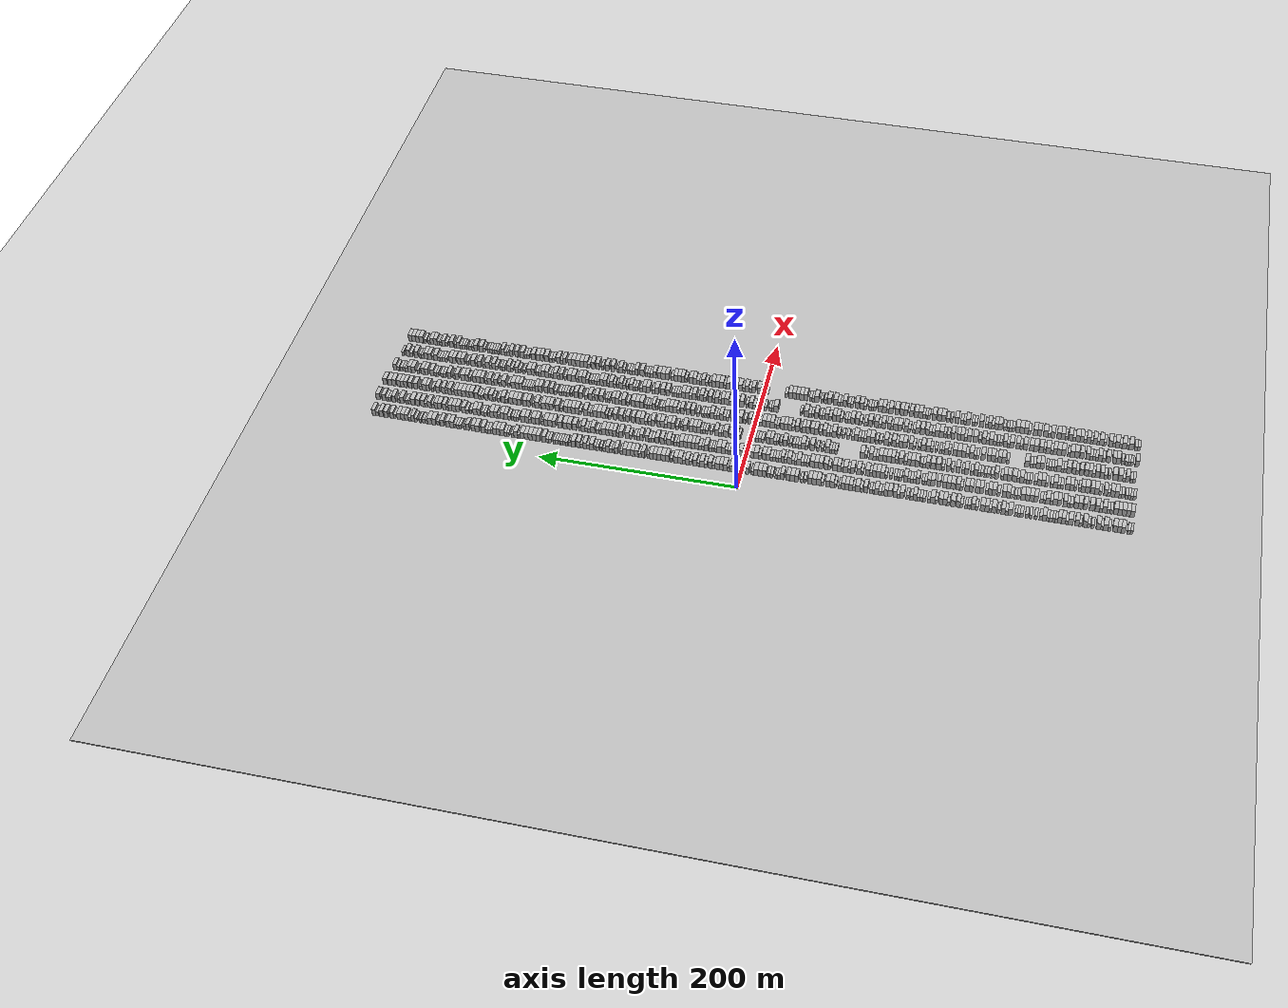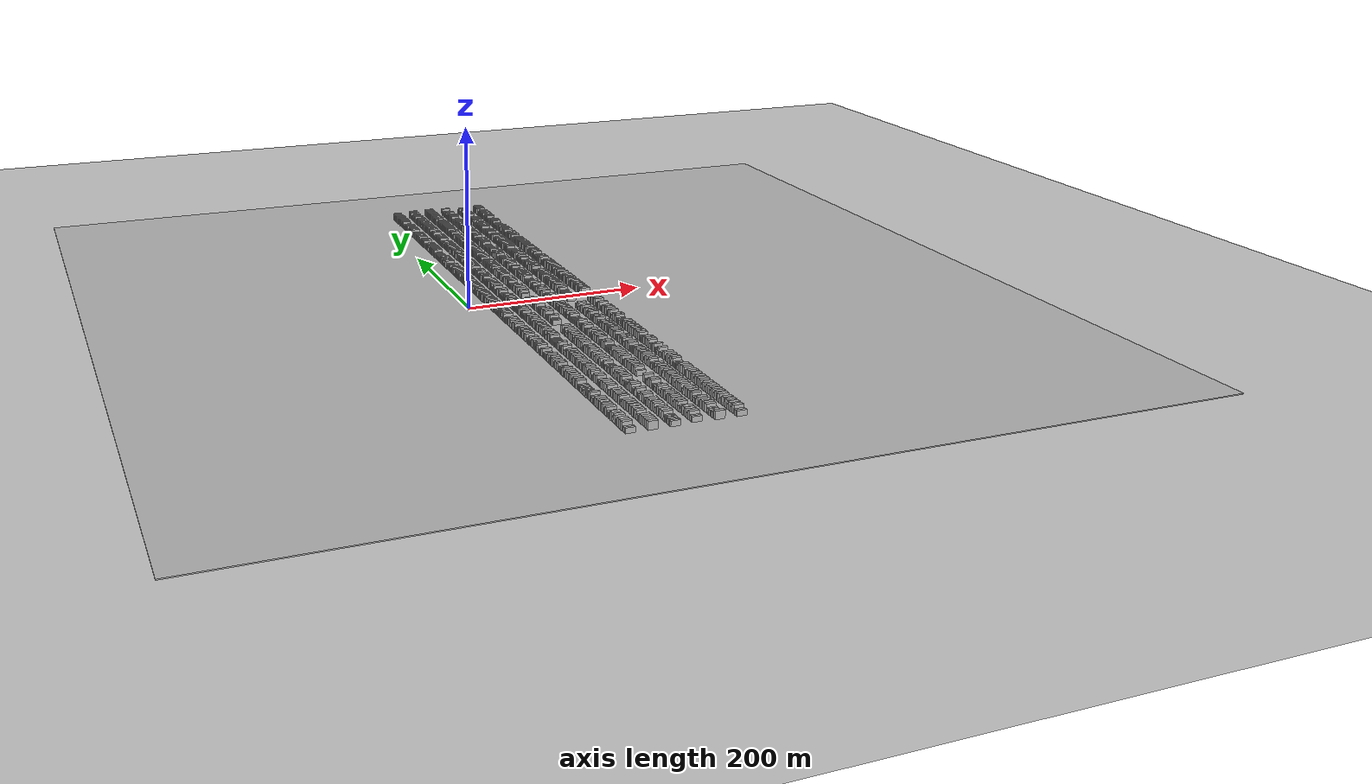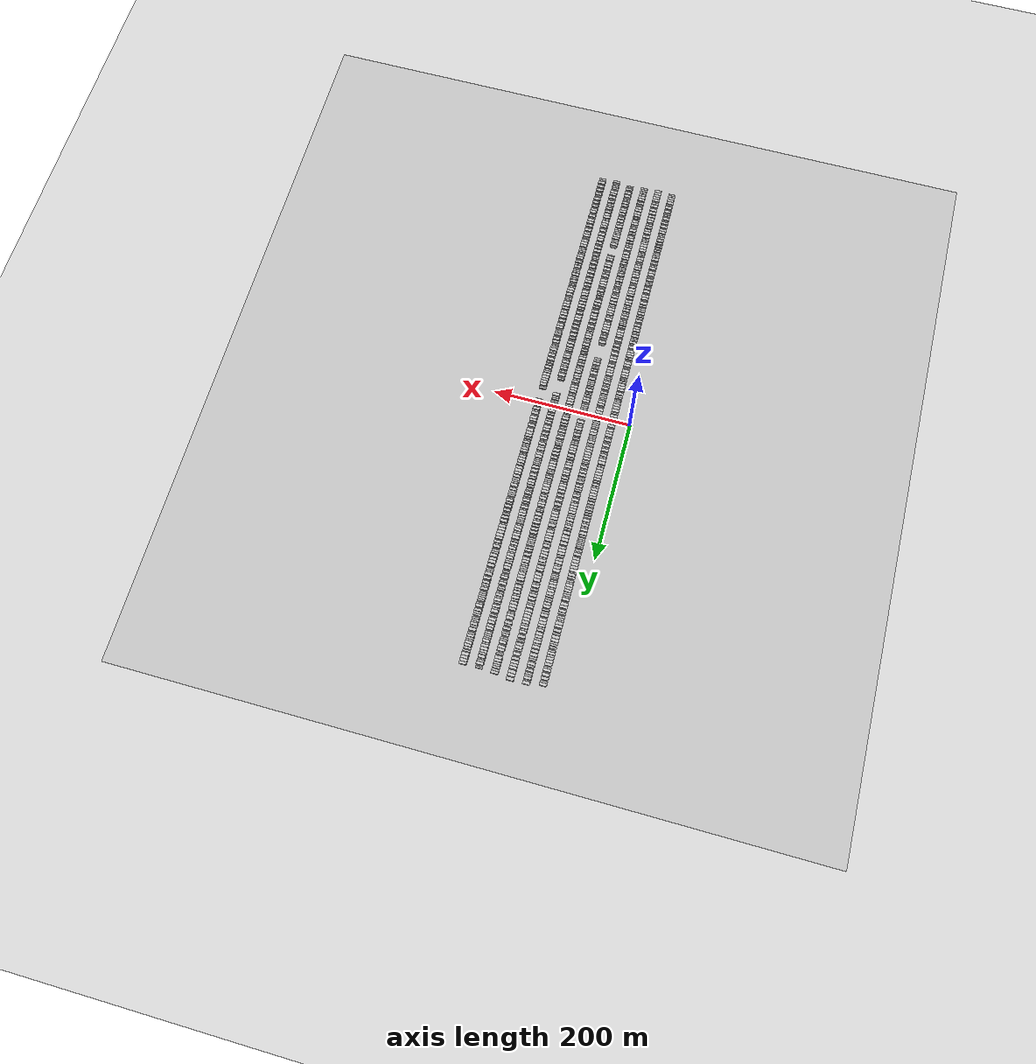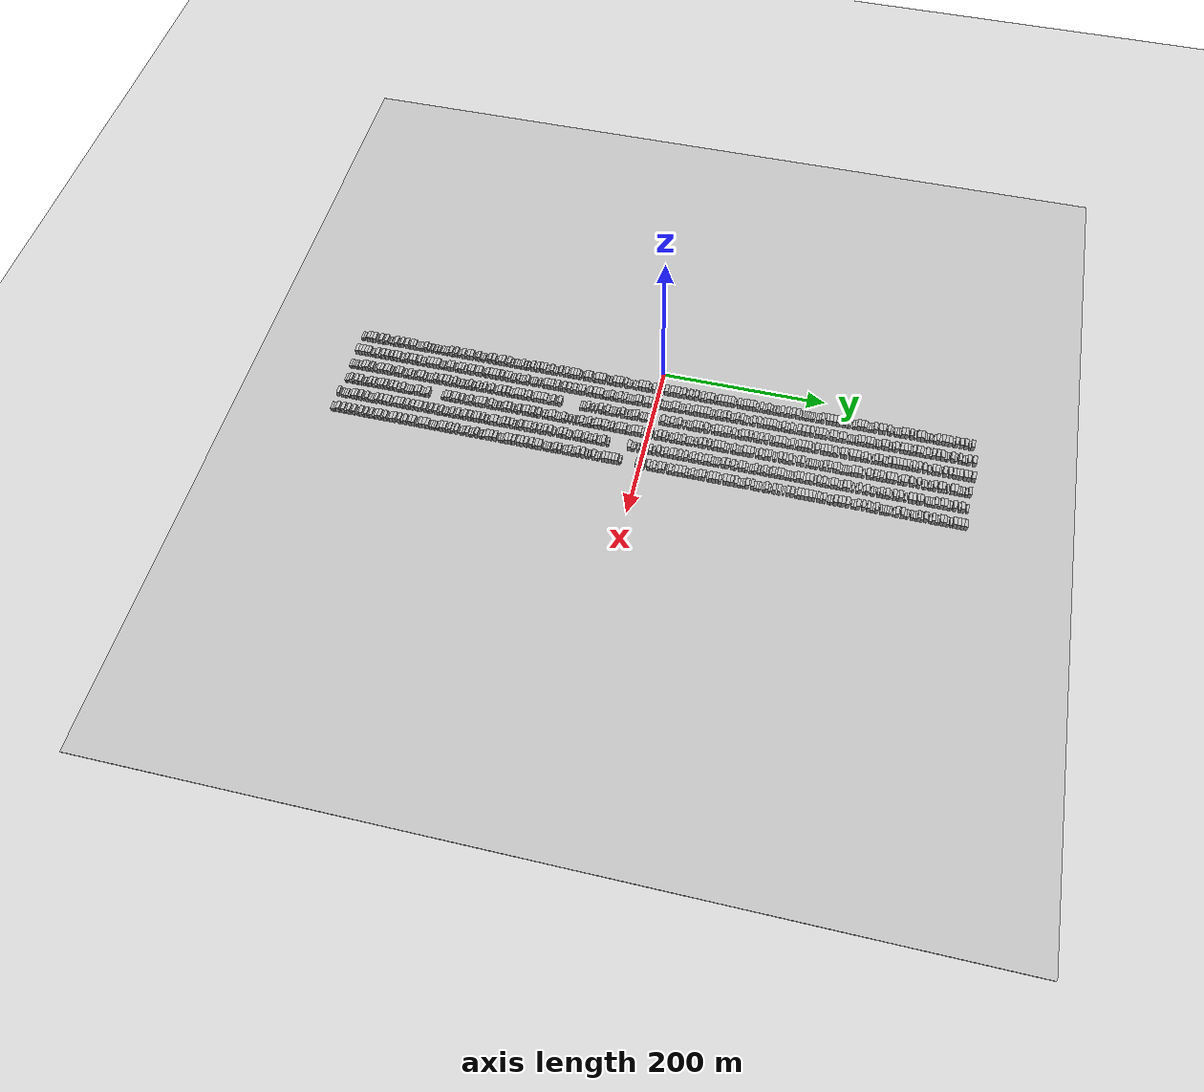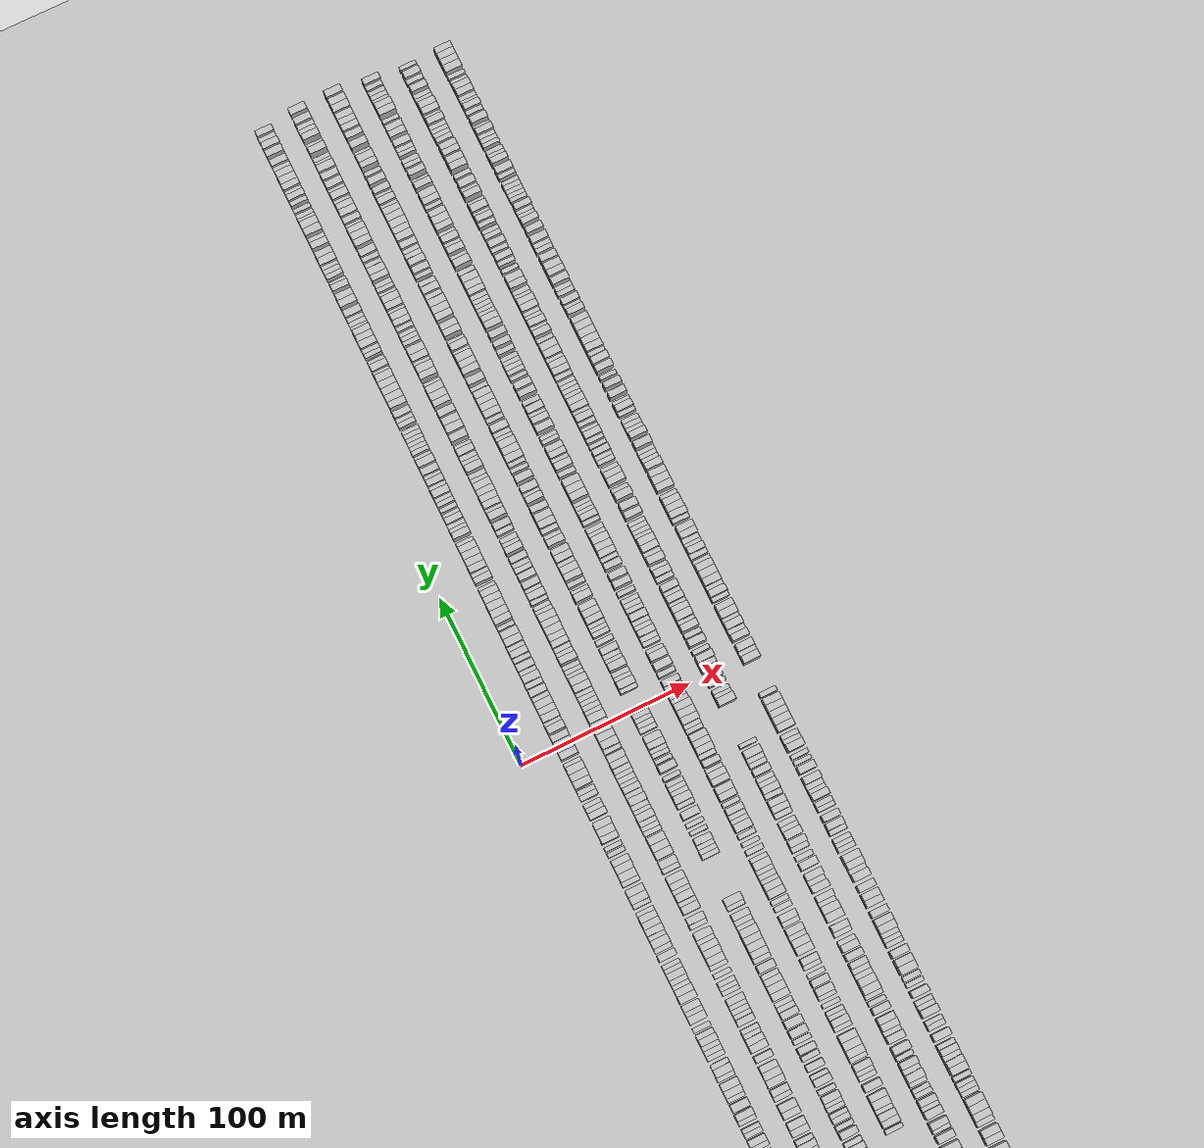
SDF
<?xml version="1.0" encoding="utf-8"?>

<sdf version="1.6">

   <world name="default">

      <gui fullscreen="0">

         <camera name="user_camera">

            <pose>-15 0 4.57585 0 0 0</pose>

            <view_controller>orbit</view_controller>

         </camera>

      </gui>

      <scene>

         <sky>

           <clouds>

             <speed>12</speed>

           </clouds>

         </sky>

         <ambient>0.4 0.4 0.4 1</ambient>

         <background>0.7 0.7 0.7 1</background>

         <shadows>1</shadows>

      </scene>

      <gravity>0 0 -9.8066</gravity>

      <magnetic_field>6e-06 2.3e-05 -4.2e-05</magnetic_field>

      <physics default="0" name="default_physics" type="ode">

         <ode>

            <solver>

               <type>quick</type>

               <iters>10</iters>

               <sor>1.0</sor>

               <use_dynamic_moi_rescaling>0</use_dynamic_moi_rescaling>

            </solver>

            <constraints>

               <cfm>0</cfm>

               <erp>0.2</erp>

               <contact_max_correcting_vel>100</contact_max_correcting_vel>

               <contact_surface_layer>0.001</contact_surface_layer>

            </constraints>

         </ode>

         <max_step_size>0.004</max_step_size>

         <real_time_factor>1</real_time_factor>

         <real_time_update_rate>250</real_time_update_rate>

      </physics>

      <light name="sun" type="directional">

         <cast_shadows>1</cast_shadows>

         <pose>0 0 10 0 0 0</pose>

         <diffuse>0.8 0.8 0.8 1</diffuse>

         <specular>0.2 0.2 0.2 1</specular>

         <attenuation>

            <range>1000</range>

            <constant>0.9</constant>

            <linear>0.01</linear>

            <quadratic>0.001</quadratic>

         </attenuation>

         <direction>-0.5 0.1 -0.9</direction>

      </light>

      <include>

         <name>ground_plane_1</name>

         <uri>model://HANNAS_ground_plane</uri>

         <pose>0 0 0  0 0 0</pose>

      </include>

      <include>

         <name>ground_plane_2</name>

         <uri>model://HANNAS_ground_plane</uri>

         <pose>100 0 0  0 0 0</pose>

      </include>

      <model name="building_1">

         <static>1</static>

         <pose frame="">25.0000 -378.7931 0 0.000000 0.000000 0.000000</pose>

         <link name="link">

            <pose frame="">0 0 3.00 0 0 0</pose>

            <collision name="collision">

               <geometry>

                  <box>

                     <size>10.0000 2.4138 6.0000</size>

                  </box>

               </geometry>

               <max_contacts>10</max_contacts>

               <surface>

                  <contact>

                     <ode/>

                  </contact>

                  <bounce/>

                  <friction>

                     <torsional>

                        <ode/>

                     </torsional>

                     <ode/>

                  </friction>

               </surface>

            </collision>

            <visual name="visual">

               <cast_shadows>0</cast_shadows>

               <geometry>

                  <box>

                     <size>10.0000 2.4138 6.0000</size>

                  </box>

               </geometry>

               <material>

                  <script>

                     <uri>model://HANNAS_wall/materials/scripts</uri>

                     <uri>model://HANNAS_wall/materials/textures</uri>

                     <name>vrc/HANNAS_wall</name>

                  </script>

               </material>

            </visual>

            <self_collide>0</self_collide>

            <enable_wind>0</enable_wind>

            <kinematic>0</kinematic>

         </link>

      </model>

      <model name="building_2">

         <static>1</static>

         <pose frame="">25.0000 -376.1967 0 0.000000 0.000000 0.000000</pose>

         <link name="link">

            <pose frame="">0 0 3.00 0 0 0</pose>

            <collision name="collision">

               <geometry>

                  <box>

                     <size>10.0000 2.7790 6.0000</size>

                  </box>

               </geometry>

               <max_contacts>10</max_contacts>

               <surface>

                  <contact>

                     <ode/>

                  </contact>

                  <bounce/>

                  <friction>

                     <torsional>

                        <ode/>

                     </torsional>

                     <ode/>

                  </friction>

               </surface>

            </collision>

            <visual name="visual">

               <cast_shadows>0</cast_shadows>

               <geometry>

                  <box>

                     <size>10.0000 2.7790 6.0000</size>

                  </box>

               </geometry>

               <material>

                  <script>

                     <uri>model://HANNAS_wall/materials/scripts</uri>

                     <uri>model://HANNAS_wall/materials/textures</uri>

                     <name>vrc/HANNAS_wall</name>

                  </script>

               </material>

            </visual>

            <self_collide>0</self_collide>

            <enable_wind>0</enable_wind>

            <kinematic>0</kinematic>

         </link>

      </model>

      <model name="building_3">

         <static>1</static>

         <pose frame="">25.0000 -370.9243 0 0.000000 0.000000 0.000000</pose>

         <link name="link">

            <pose frame="">0 0 4.50 0 0 0</pose>

            <collision name="collision">

               <geometry>

                  <box>

                     <size>10.0000 3.7657 9.0000</size>

                  </box>

               </geometry>

               <max_contacts>10</max_contacts>

               <surface>

                  <contact>

                     <ode/>

                  </contact>

                  <bounce/>

                  <friction>

                     <torsional>

                        <ode/>

                     </torsional>

                     <ode/>

                  </friction>

               </surface>

            </collision>

            <visual name="visual">

               <cast_shadows>0</cast_shadows>

               <geometry>

                  <box>

                     <size>10.0000 3.7657 9.0000</size>

                  </box>

               </geometry>

               <material>

                  <script>

                     <uri>model://HANNAS_wall/materials/scripts</uri>

                     <uri>model://HANNAS_wall/materials/textures</uri>

                     <name>vrc/HANNAS_wall</name>

                  </script>

               </material>

            </visual>

            <self_collide>0</self_collide>

            <enable_wind>0</enable_wind>

            <kinematic>0</kinematic>

         </link>

      </model>

      <model name="building_4">

         <static>1</static>

         <pose frame="">25.0000 -367.2173 0 0.000000 0.000000 0.000000</pose>

         <link name="link">

            <pose frame="">0 0 4.50 0 0 0</pose>

            <collision name="collision">

               <geometry>

                  <box>

                     <size>10.0000 3.6483 9.0000</size>

                  </box>

               </geometry>

               <max_contacts>10</max_contacts>

               <surface>

                  <contact>

                     <ode/>

                  </contact>

                  <bounce/>

                  <friction>

                     <torsional>

                        <ode/>

                     </torsional>

                     <ode/>

                  </friction>

               </surface>

            </collision>

            <visual name="visual">

               <cast_shadows>0</cast_shadows>

               <geometry>

                  <box>

                     <size>10.0000 3.6483 9.0000</size>

                  </box>

               </geometry>

               <material>

                  <script>

                     <uri>model://HANNAS_wall/materials/scripts</uri>

                     <uri>model://HANNAS_wall/materials/textures</uri>

                     <name>vrc/HANNAS_wall</name>

                  </script>

               </material>

            </visual>

            <self_collide>0</self_collide>

            <enable_wind>0</enable_wind>

            <kinematic>0</kinematic>

         </link>

      </model>

      <model name="building_5">

         <static>1</static>

         <pose frame="">25.0000 -363.2170 0 0.000000 0.000000 0.000000</pose>

         <link name="link">

            <pose frame="">0 0 4.50 0 0 0</pose>

            <collision name="collision">

               <geometry>

                  <box>

                     <size>10.0000 4.3523 9.0000</size>

                  </box>

               </geometry>

               <max_contacts>10</max_contacts>

               <surface>

                  <contact>

                     <ode/>

                  </contact>

                  <bounce/>

                  <friction>

                     <torsional>

                        <ode/>

                     </torsional>

                     <ode/>

                  </friction>

               </surface>

            </collision>

            <visual name="visual">

               <cast_shadows>0</cast_shadows>

               <geometry>

                  <box>

                     <size>10.0000 4.3523 9.0000</size>

                  </box>

               </geometry>

               <material>

                  <script>

                     <uri>model://HANNAS_wall/materials/scripts</uri>

                     <uri>model://HANNAS_wall/materials/textures</uri>

                     <name>vrc/HANNAS_wall</name>

                  </script>

               </material>

            </visual>

            <self_collide>0</self_collide>

            <enable_wind>0</enable_wind>

            <kinematic>0</kinematic>

         </link>

      </model>

      <model name="building_6">

         <static>1</static>

         <pose frame="">25.0000 -357.7842 0 0.000000 0.000000 0.000000</pose>

         <link name="link">

            <pose frame="">0 0 3.00 0 0 0</pose>

            <collision name="collision">

               <geometry>

                  <box>

                     <size>10.0000 2.5133 6.0000</size>

                  </box>

               </geometry>

               <max_contacts>10</max_contacts>

               <surface>

                  <contact>

                     <ode/>

                  </contact>

                  <bounce/>

                  <friction>

                     <torsional>

                        <ode/>

                     </torsional>

                     <ode/>

                  </friction>

               </surface>

            </collision>

            <visual name="visual">

               <cast_shadows>0</cast_shadows>

               <geometry>

                  <box>

                     <size>10.0000 2.5133 6.0000</size>

                  </box>

               </geometry>

               <material>

                  <script>

                     <uri>model://HANNAS_wall/materials/scripts</uri>

                     <uri>model://HANNAS_wall/materials/textures</uri>

                     <name>vrc/HANNAS_wall</name>

                  </script>

               </material>

            </visual>

            <self_collide>0</self_collide>

            <enable_wind>0</enable_wind>

            <kinematic>0</kinematic>

         </link>

      </model>

      <model name="building_7">

         <static>1</static>

         <pose frame="">25.0000 -354.3040 0 0.000000 0.000000 0.000000</pose>

         <link name="link">

            <pose frame="">0 0 4.50 0 0 0</pose>

            <collision name="collision">

               <geometry>

                  <box>

                     <size>10.0000 4.4470 9.0000</size>

                  </box>

               </geometry>

               <max_contacts>10</max_contacts>

               <surface>

                  <contact>

                     <ode/>

                  </contact>

                  <bounce/>

                  <friction>

                     <torsional>

                        <ode/>

                     </torsional>

                     <ode/>

                  </friction>

               </surface>

            </collision>

            <visual name="visual">

               <cast_shadows>0</cast_shadows>

               <geometry>

                  <box>

                     <size>10.0000 4.4470 9.0000</size>

                  </box>

               </geometry>

               <material>

                  <script>

                     <uri>model://HANNAS_wall/materials/scripts</uri>

                     <uri>model://HANNAS_wall/materials/textures</uri>

                     <name>vrc/HANNAS_wall</name>

                  </script>

               </material>

            </visual>

            <self_collide>0</self_collide>

            <enable_wind>0</enable_wind>

            <kinematic>0</kinematic>

         </link>

      </model>

      <model name="building_8">

         <static>1</static>

         <pose frame="">25.0000 -350.7856 0 0.000000 0.000000 0.000000</pose>

         <link name="link">

            <pose frame="">0 0 3.00 0 0 0</pose>

            <collision name="collision">

               <geometry>

                  <box>

                     <size>10.0000 2.5899 6.0000</size>

                  </box>

               </geometry>

               <max_contacts>10</max_contacts>

               <surface>

                  <contact>

                     <ode/>

                  </contact>

                  <bounce/>

                  <friction>

                     <torsional>

                        <ode/>

                     </torsional>

                     <ode/>

                  </friction>

               </surface>

            </collision>

            <visual name="visual">

               <cast_shadows>0</cast_shadows>

               <geometry>

                  <box>

                     <size>10.0000 2.5899 6.0000</size>

                  </box>

               </geometry>

               <material>

                  <script>

                     <uri>model://HANNAS_wall/materials/scripts</uri>

                     <uri>model://HANNAS_wall/materials/textures</uri>

                     <name>vrc/HANNAS_wall</name>

                  </script>

               </material>

            </visual>

            <self_collide>0</self_collide>

            <enable_wind>0</enable_wind>

            <kinematic>0</kinematic>

         </link>

      </model>

      <model name="building_9">

         <static>1</static>

         <pose frame="">25.0000 -347.3726 0 0.000000 0.000000 0.000000</pose>

         <link name="link">

            <pose frame="">0 0 4.50 0 0 0</pose>

            <collision name="collision">

               <geometry>

                  <box>

                     <size>10.0000 4.2361 9.0000</size>

                  </box>

               </geometry>

               <max_contacts>10</max_contacts>

               <surface>

                  <contact>

                     <ode/>

                  </contact>

                  <bounce/>

                  <friction>

                     <torsional>

                        <ode/>

                     </torsional>

                     <ode/>

                  </friction>

               </surface>

            </collision>

            <visual name="visual">

               <cast_shadows>0</cast_shadows>

               <geometry>

                  <box>

                     <size>10.0000 4.2361 9.0000</size>

                  </box>

               </geometry>

               <material>

                  <script>

                     <uri>model://HANNAS_wall/materials/scripts</uri>

                     <uri>model://HANNAS_wall/materials/textures</uri>

                     <name>vrc/HANNAS_wall</name>

                  </script>

               </material>

            </visual>

            <self_collide>0</self_collide>

            <enable_wind>0</enable_wind>

            <kinematic>0</kinematic>

         </link>

      </model>

      <model name="building_10">

         <static>1</static>

         <pose frame="">25.0000 -341.9552 0 0.000000 0.000000 0.000000</pose>

         <link name="link">

            <pose frame="">0 0 3.00 0 0 0</pose>

            <collision name="collision">

               <geometry>

                  <box>

                     <size>10.0000 2.5986 6.0000</size>

                  </box>

               </geometry>

               <max_contacts>10</max_contacts>

               <surface>

                  <contact>

                     <ode/>

                  </contact>

                  <bounce/>

                  <friction>

                     <torsional>

                        <ode/>

                     </torsional>

                     <ode/>

                  </friction>

               </surface>

            </collision>

            <visual name="visual">

               <cast_shadows>0</cast_shadows>

               <geometry>

                  <box>

                     <size>10.0000 2.5986 6.0000</size>

                  </box>

               </geometry>

               <material>

                  <script>

                     <uri>model://HANNAS_wall/materials/scripts</uri>

                     <uri>model://HANNAS_wall/materials/textures</uri>

                     <name>vrc/HANNAS_wall</name>

                  </script>

               </material>

            </visual>

            <self_collide>0</self_collide>

            <enable_wind>0</enable_wind>

            <kinematic>0</kinematic>

         </link>

      </model>

      <model name="building_11">

         <static>1</static>

         <pose frame="">25.0000 -338.2738 0 0.000000 0.000000 0.000000</pose>

         <link name="link">

            <pose frame="">0 0 3.00 0 0 0</pose>

            <collision name="collision">

               <geometry>

                  <box>

                     <size>10.0000 2.7642 6.0000</size>

                  </box>

               </geometry>

               <max_contacts>10</max_contacts>

               <surface>

                  <contact>

                     <ode/>

                  </contact>

                  <bounce/>

                  <friction>

                     <torsional>

                        <ode/>

                     </torsional>

                     <ode/>

                  </friction>

               </surface>

            </collision>

            <visual name="visual">

               <cast_shadows>0</cast_shadows>

               <geometry>

                  <box>

                     <size>10.0000 2.7642 6.0000</size>

                  </box>

               </geometry>

               <material>

                  <script>

                     <uri>model://HANNAS_wall/materials/scripts</uri>

                     <uri>model://HANNAS_wall/materials/textures</uri>

                     <name>vrc/HANNAS_wall</name>

                  </script>

               </material>

            </visual>

            <self_collide>0</self_collide>

            <enable_wind>0</enable_wind>

            <kinematic>0</kinematic>

         </link>

      </model>

      <model name="building_12">

         <static>1</static>

         <pose frame="">25.0000 -334.7722 0 0.000000 0.000000 0.000000</pose>

         <link name="link">

            <pose frame="">0 0 4.50 0 0 0</pose>

            <collision name="collision">

               <geometry>

                  <box>

                     <size>10.0000 4.2390 9.0000</size>

                  </box>

               </geometry>

               <max_contacts>10</max_contacts>

               <surface>

                  <contact>

                     <ode/>

                  </contact>

                  <bounce/>

                  <friction>

                     <torsional>

                        <ode/>

                     </torsional>

                     <ode/>

                  </friction>

               </surface>

            </collision>

            <visual name="visual">

               <cast_shadows>0</cast_shadows>

               <geometry>

                  <box>

                     <size>10.0000 4.2390 9.0000</size>

                  </box>

               </geometry>

               <material>

                  <script>

                     <uri>model://HANNAS_wall/materials/scripts</uri>

                     <uri>model://HANNAS_wall/materials/textures</uri>

                     <name>vrc/HANNAS_wall</name>

                  </script>

               </material>

            </visual>

            <self_collide>0</self_collide>

            <enable_wind>0</enable_wind>

            <kinematic>0</kinematic>

         </link>

      </model>

      <model name="building_13">

         <static>1</static>

         <pose frame="">25.0000 -330.3623 0 0.000000 0.000000 0.000000</pose>

         <link name="link">

            <pose frame="">0 0 3.00 0 0 0</pose>

            <collision name="collision">

               <geometry>

                  <box>

                     <size>10.0000 2.5808 6.0000</size>

                  </box>

               </geometry>

               <max_contacts>10</max_contacts>

               <surface>

                  <contact>

                     <ode/>

                  </contact>

                  <bounce/>

                  <friction>

                     <torsional>

                        <ode/>

                     </torsional>

                     <ode/>

                  </friction>

               </surface>

            </collision>

            <visual name="visual">

               <cast_shadows>0</cast_shadows>

               <geometry>

                  <box>

                     <size>10.0000 2.5808 6.0000</size>

                  </box>

               </geometry>

               <material>

                  <script>

                     <uri>model://HANNAS_wall/materials/scripts</uri>

                     <uri>model://HANNAS_wall/materials/textures</uri>

                     <name>vrc/HANNAS_wall</name>

                  </script>

               </material>

            </visual>

            <self_collide>0</self_collide>

            <enable_wind>0</enable_wind>

            <kinematic>0</kinematic>

         </link>

      </model>

      <model name="building_14">

         <static>1</static>

         <pose frame="">25.0000 -327.1281 0 0.000000 0.000000 0.000000</pose>

         <link name="link">

            <pose frame="">0 0 4.50 0 0 0</pose>

            <collision name="collision">

               <geometry>

                  <box>

                     <size>10.0000 3.8875 9.0000</size>

                  </box>

               </geometry>

               <max_contacts>10</max_contacts>

               <surface>

                  <contact>

                     <ode/>

                  </contact>

                  <bounce/>

                  <friction>

                     <torsional>

                        <ode/>

                     </torsional>

                     <ode/>

                  </friction>

               </surface>

            </collision>

            <visual name="visual">

               <cast_shadows>0</cast_shadows>

               <geometry>

                  <box>

                     <size>10.0000 3.8875 9.0000</size>

                  </box>

               </geometry>

               <material>

                  <script>

                     <uri>model://HANNAS_wall/materials/scripts</uri>

                     <uri>model://HANNAS_wall/materials/textures</uri>

                     <name>vrc/HANNAS_wall</name>

                  </script>

               </material>

            </visual>

            <self_collide>0</self_collide>

            <enable_wind>0</enable_wind>

            <kinematic>0</kinematic>

         </link>

      </model>

      <model name="building_15">

         <static>1</static>

         <pose frame="">25.0000 -320.9726 0 0.000000 0.000000 0.000000</pose>

         <link name="link">

            <pose frame="">0 0 4.50 0 0 0</pose>

            <collision name="collision">

               <geometry>

                  <box>

                     <size>10.0000 4.4236 9.0000</size>

                  </box>

               </geometry>

               <max_contacts>10</max_contacts>

               <surface>

                  <contact>

                     <ode/>

                  </contact>

                  <bounce/>

                  <friction>

                     <torsional>

                        <ode/>

                     </torsional>

                     <ode/>

                  </friction>

               </surface>

            </collision>

            <visual name="visual">

               <cast_shadows>0</cast_shadows>

               <geometry>

                  <box>

                     <size>10.0000 4.4236 9.0000</size>

                  </box>

               </geometry>

               <material>

                  <script>

                     <uri>model://HANNAS_wall/materials/scripts</uri>

                     <uri>model://HANNAS_wall/materials/textures</uri>

                     <name>vrc/HANNAS_wall</name>

                  </script>

               </material>

            </visual>

            <self_collide>0</self_collide>

            <enable_wind>0</enable_wind>

            <kinematic>0</kinematic>

         </link>

      </model>

      <model name="building_16">

         <static>1</static>

         <pose frame="">25.0000 -317.4612 0 0.000000 0.000000 0.000000</pose>

         <link name="link">

            <pose frame="">0 0 3.00 0 0 0</pose>

            <collision name="collision">

               <geometry>

                  <box>

                     <size>10.0000 2.5991 6.0000</size>

                  </box>

               </geometry>

               <max_contacts>10</max_contacts>

               <surface>

                  <contact>

                     <ode/>

                  </contact>

                  <bounce/>

                  <friction>

                     <torsional>

                        <ode/>

                     </torsional>

                     <ode/>

                  </friction>

               </surface>

            </collision>

            <visual name="visual">

               <cast_shadows>0</cast_shadows>

               <geometry>

                  <box>

                     <size>10.0000 2.5991 6.0000</size>

                  </box>

               </geometry>

               <material>

                  <script>

                     <uri>model://HANNAS_wall/materials/scripts</uri>

                     <uri>model://HANNAS_wall/materials/textures</uri>

                     <name>vrc/HANNAS_wall</name>

                  </script>

               </material>

            </visual>

            <self_collide>0</self_collide>

            <enable_wind>0</enable_wind>

            <kinematic>0</kinematic>

         </link>

      </model>

      <model name="building_17">

         <static>1</static>

         <pose frame="">25.0000 -314.3084 0 0.000000 0.000000 0.000000</pose>

         <link name="link">

            <pose frame="">0 0 4.50 0 0 0</pose>

            <collision name="collision">

               <geometry>

                  <box>

                     <size>10.0000 3.7064 9.0000</size>

                  </box>

               </geometry>

               <max_contacts>10</max_contacts>

               <surface>

                  <contact>

                     <ode/>

                  </contact>

                  <bounce/>

                  <friction>

                     <torsional>

                        <ode/>

                     </torsional>

                     <ode/>

                  </friction>

               </surface>

            </collision>

            <visual name="visual">

               <cast_shadows>0</cast_shadows>

               <geometry>

                  <box>

                     <size>10.0000 3.7064 9.0000</size>

                  </box>

               </geometry>

               <material>

                  <script>

                     <uri>model://HANNAS_wall/materials/scripts</uri>

                     <uri>model://HANNAS_wall/materials/textures</uri>

                     <name>vrc/HANNAS_wall</name>

                  </script>

               </material>

            </visual>

            <self_collide>0</self_collide>

            <enable_wind>0</enable_wind>

            <kinematic>0</kinematic>

         </link>

      </model>

      <model name="building_18">

         <static>1</static>

         <pose frame="">25.0000 -310.5778 0 0.000000 0.000000 0.000000</pose>

         <link name="link">

            <pose frame="">0 0 4.50 0 0 0</pose>

            <collision name="collision">

               <geometry>

                  <box>

                     <size>10.0000 3.7548 9.0000</size>

                  </box>

               </geometry>

               <max_contacts>10</max_contacts>

               <surface>

                  <contact>

                     <ode/>

                  </contact>

                  <bounce/>

                  <friction>

                     <torsional>

                        <ode/>

                     </torsional>

                     <ode/>

                  </friction>

               </surface>

            </collision>

            <visual name="visual">

               <cast_shadows>0</cast_shadows>

               <geometry>

                  <box>

                     <size>10.0000 3.7548 9.0000</size>

                  </box>

               </geometry>

               <material>

                  <script>

                     <uri>model://HANNAS_wall/materials/scripts</uri>

                     <uri>model://HANNAS_wall/materials/textures</uri>

                     <name>vrc/HANNAS_wall</name>

                  </script>

               </material>

            </visual>

            <self_collide>0</self_collide>

            <enable_wind>0</enable_wind>

            <kinematic>0</kinematic>

         </link>

      </model>

      <model name="building_19">

         <static>1</static>

         <pose frame="">25.0000 -307.4906 0 0.000000 0.000000 0.000000</pose>

         <link name="link">

            <pose frame="">0 0 3.00 0 0 0</pose>

            <collision name="collision">

               <geometry>

                  <box>

                     <size>10.0000 2.4198 6.0000</size>

                  </box>

               </geometry>

               <max_contacts>10</max_contacts>

               <surface>

                  <contact>

                     <ode/>

                  </contact>

                  <bounce/>

                  <friction>

                     <torsional>

                        <ode/>

                     </torsional>

                     <ode/>

                  </friction>

               </surface>

            </collision>

            <visual name="visual">

               <cast_shadows>0</cast_shadows>

               <geometry>

                  <box>

                     <size>10.0000 2.4198 6.0000</size>

                  </box>

               </geometry>

               <material>

                  <script>

                     <uri>model://HANNAS_wall/materials/scripts</uri>

                     <uri>model://HANNAS_wall/materials/textures</uri>

                     <name>vrc/HANNAS_wall</name>

                  </script>

               </material>

            </visual>

            <self_collide>0</self_collide>

            <enable_wind>0</enable_wind>

            <kinematic>0</kinematic>

         </link>

      </model>

      <model name="building_20">

         <static>1</static>

         <pose frame="">25.0000 -305.0435 0 0.000000 0.000000 0.000000</pose>

         <link name="link">

            <pose frame="">0 0 3.00 0 0 0</pose>

            <collision name="collision">

               <geometry>

                  <box>

                     <size>10.0000 2.4743 6.0000</size>

                  </box>

               </geometry>

               <max_contacts>10</max_contacts>

               <surface>

                  <contact>

                     <ode/>

                  </contact>

                  <bounce/>

                  <friction>

                     <torsional>

                        <ode/>

                     </torsional>

                     <ode/>

                  </friction>

               </surface>

            </collision>

            <visual name="visual">

               <cast_shadows>0</cast_shadows>

               <geometry>

                  <box>

                     <size>10.0000 2.4743 6.0000</size>

                  </box>

               </geometry>

               <material>

                  <script>

                     <uri>model://HANNAS_wall/materials/scripts</uri>

                     <uri>model://HANNAS_wall/materials/textures</uri>

                     <name>vrc/HANNAS_wall</name>

                  </script>

               </material>

            </visual>

            <self_collide>0</self_collide>

            <enable_wind>0</enable_wind>

            <kinematic>0</kinematic>

         </link>

      </model>

      <model name="building_21">

         <static>1</static>

         <pose frame="">25.0000 -302.3490 0 0.000000 0.000000 0.000000</pose>

         <link name="link">

            <pose frame="">0 0 3.00 0 0 0</pose>

            <collision name="collision">

               <geometry>

                  <box>

                     <size>10.0000 2.9148 6.0000</size>

                  </box>

               </geometry>

               <max_contacts>10</max_contacts>

               <surface>

                  <contact>

                     <ode/>

                  </contact>

                  <bounce/>

                  <friction>

                     <torsional>

                        <ode/>

                     </torsional>

                     <ode/>

                  </friction>

               </surface>

            </collision>

            <visual name="visual">

               <cast_shadows>0</cast_shadows>

               <geometry>

                  <box>

                     <size>10.0000 2.9148 6.0000</size>

                  </box>

               </geometry>

               <material>

                  <script>

                     <uri>model://HANNAS_wall/materials/scripts</uri>

                     <uri>model://HANNAS_wall/materials/textures</uri>

                     <name>vrc/HANNAS_wall</name>

                  </script>

               </material>

            </visual>

            <self_collide>0</self_collide>

            <enable_wind>0</enable_wind>

            <kinematic>0</kinematic>

         </link>

      </model>

      <model name="building_22">

         <static>1</static>

         <pose frame="">25.0000 -299.4433 0 0.000000 0.000000 0.000000</pose>

         <link name="link">

            <pose frame="">0 0 3.00 0 0 0</pose>

            <collision name="collision">

               <geometry>

                  <box>

                     <size>10.0000 2.8966 6.0000</size>

                  </box>

               </geometry>

               <max_contacts>10</max_contacts>

               <surface>

                  <contact>

                     <ode/>

                  </contact>

                  <bounce/>

                  <friction>

                     <torsional>

                        <ode/>

                     </torsional>

                     <ode/>

                  </friction>

               </surface>

            </collision>

            <visual name="visual">

               <cast_shadows>0</cast_shadows>

               <geometry>

                  <box>

                     <size>10.0000 2.8966 6.0000</size>

                  </box>

               </geometry>

               <material>

                  <script>

                     <uri>model://HANNAS_wall/materials/scripts</uri>

                     <uri>model://HANNAS_wall/materials/textures</uri>

                     <name>vrc/HANNAS_wall</name>

                  </script>

               </material>

            </visual>

            <self_collide>0</self_collide>

            <enable_wind>0</enable_wind>

            <kinematic>0</kinematic>

         </link>

      </model>

      <model name="building_23">

         <static>1</static>

         <pose frame="">25.0000 -296.0758 0 0.000000 0.000000 0.000000</pose>

         <link name="link">

            <pose frame="">0 0 4.50 0 0 0</pose>

            <collision name="collision">

               <geometry>

                  <box>

                     <size>10.0000 3.8385 9.0000</size>

                  </box>

               </geometry>

               <max_contacts>10</max_contacts>

               <surface>

                  <contact>

                     <ode/>

                  </contact>

                  <bounce/>

                  <friction>

                     <torsional>

                        <ode/>

                     </torsional>

                     <ode/>

                  </friction>

               </surface>

            </collision>

            <visual name="visual">

               <cast_shadows>0</cast_shadows>

               <geometry>

                  <box>

                     <size>10.0000 3.8385 9.0000</size>

                  </box>

               </geometry>

               <material>

                  <script>

                     <uri>model://HANNAS_wall/materials/scripts</uri>

                     <uri>model://HANNAS_wall/materials/textures</uri>

                     <name>vrc/HANNAS_wall</name>

                  </script>

               </material>

            </visual>

            <self_collide>0</self_collide>

            <enable_wind>0</enable_wind>

            <kinematic>0</kinematic>

         </link>

      </model>

      <model name="building_24">

         <static>1</static>

         <pose frame="">25.0000 -292.6682 0 0.000000 0.000000 0.000000</pose>

         <link name="link">

            <pose frame="">0 0 3.00 0 0 0</pose>

            <collision name="collision">

               <geometry>

                  <box>

                     <size>10.0000 2.9766 6.0000</size>

                  </box>

               </geometry>

               <max_contacts>10</max_contacts>

               <surface>

                  <contact>

                     <ode/>

                  </contact>

                  <bounce/>

                  <friction>

                     <torsional>

                        <ode/>

                     </torsional>

                     <ode/>

                  </friction>

               </surface>

            </collision>

            <visual name="visual">

               <cast_shadows>0</cast_shadows>

               <geometry>

                  <box>

                     <size>10.0000 2.9766 6.0000</size>

                  </box>

               </geometry>

               <material>

                  <script>

                     <uri>model://HANNAS_wall/materials/scripts</uri>

                     <uri>model://HANNAS_wall/materials/textures</uri>

                     <name>vrc/HANNAS_wall</name>

                  </script>

               </material>

            </visual>

            <self_collide>0</self_collide>

            <enable_wind>0</enable_wind>

            <kinematic>0</kinematic>

         </link>

      </model>

      <model name="building_25">

         <static>1</static>

         <pose frame="">25.0000 -287.8012 0 0.000000 0.000000 0.000000</pose>

         <link name="link">

            <pose frame="">0 0 3.00 0 0 0</pose>

            <collision name="collision">

               <geometry>

                  <box>

                     <size>10.0000 2.7574 6.0000</size>

                  </box>

               </geometry>

               <max_contacts>10</max_contacts>

               <surface>

                  <contact>

                     <ode/>

                  </contact>

                  <bounce/>

                  <friction>

                     <torsional>

                        <ode/>

                     </torsional>

                     <ode/>

                  </friction>

               </surface>

            </collision>

            <visual name="visual">

               <cast_shadows>0</cast_shadows>

               <geometry>

                  <box>

                     <size>10.0000 2.7574 6.0000</size>

                  </box>

               </geometry>

               <material>

                  <script>

                     <uri>model://HANNAS_wall/materials/scripts</uri>

                     <uri>model://HANNAS_wall/materials/textures</uri>

                     <name>vrc/HANNAS_wall</name>

                  </script>

               </material>

            </visual>

            <self_collide>0</self_collide>

            <enable_wind>0</enable_wind>

            <kinematic>0</kinematic>

         </link>

      </model>

      <model name="building_26">

         <static>1</static>

         <pose frame="">25.0000 -283.0045 0 0.000000 0.000000 0.000000</pose>

         <link name="link">

            <pose frame="">0 0 3.00 0 0 0</pose>

            <collision name="collision">

               <geometry>

                  <box>

                     <size>10.0000 2.8360 6.0000</size>

                  </box>

               </geometry>

               <max_contacts>10</max_contacts>

               <surface>

                  <contact>

                     <ode/>

                  </contact>

                  <bounce/>

                  <friction>

                     <torsional>

                        <ode/>

                     </torsional>

                     <ode/>

                  </friction>

               </surface>

            </collision>

            <visual name="visual">

               <cast_shadows>0</cast_shadows>

               <geometry>

                  <box>

                     <size>10.0000 2.8360 6.0000</size>

                  </box>

               </geometry>

               <material>

                  <script>

                     <uri>model://HANNAS_wall/materials/scripts</uri>

                     <uri>model://HANNAS_wall/materials/textures</uri>

                     <name>vrc/HANNAS_wall</name>

                  </script>

               </material>

            </visual>

            <self_collide>0</self_collide>

            <enable_wind>0</enable_wind>

            <kinematic>0</kinematic>

         </link>

      </model>

      <model name="building_27">

         <static>1</static>

         <pose frame="">25.0000 -279.1932 0 0.000000 0.000000 0.000000</pose>

         <link name="link">

            <pose frame="">0 0 3.00 0 0 0</pose>

            <collision name="collision">

               <geometry>

                  <box>

                     <size>10.0000 2.7866 6.0000</size>

                  </box>

               </geometry>

               <max_contacts>10</max_contacts>

               <surface>

                  <contact>

                     <ode/>

                  </contact>

                  <bounce/>

                  <friction>

                     <torsional>

                        <ode/>

                     </torsional>

                     <ode/>

                  </friction>

               </surface>

            </collision>

            <visual name="visual">

               <cast_shadows>0</cast_shadows>

               <geometry>

                  <box>

                     <size>10.0000 2.7866 6.0000</size>

                  </box>

               </geometry>

               <material>

                  <script>

                     <uri>model://HANNAS_wall/materials/scripts</uri>

                     <uri>model://HANNAS_wall/materials/textures</uri>

                     <name>vrc/HANNAS_wall</name>

                  </script>

               </material>

            </visual>

            <self_collide>0</self_collide>

            <enable_wind>0</enable_wind>

            <kinematic>0</kinematic>

         </link>

      </model>

      <model name="building_28">

         <static>1</static>

         <pose frame="">25.0000 -274.3440 0 0.000000 0.000000 0.000000</pose>

         <link name="link">

            <pose frame="">0 0 3.00 0 0 0</pose>

            <collision name="collision">

               <geometry>

                  <box>

                     <size>10.0000 2.9119 6.0000</size>

                  </box>

               </geometry>

               <max_contacts>10</max_contacts>

               <surface>

                  <contact>

                     <ode/>

                  </contact>

                  <bounce/>

                  <friction>

                     <torsional>

                        <ode/>

                     </torsional>

                     <ode/>

                  </friction>

               </surface>

            </collision>

            <visual name="visual">

               <cast_shadows>0</cast_shadows>

               <geometry>

                  <box>

                     <size>10.0000 2.9119 6.0000</size>

                  </box>

               </geometry>

               <material>

                  <script>

                     <uri>model://HANNAS_wall/materials/scripts</uri>

                     <uri>model://HANNAS_wall/materials/textures</uri>

                     <name>vrc/HANNAS_wall</name>

                  </script>

               </material>

            </visual>

            <self_collide>0</self_collide>

            <enable_wind>0</enable_wind>

            <kinematic>0</kinematic>

         </link>

      </model>

      <model name="building_29">

         <static>1</static>

         <pose frame="">25.0000 -271.5463 0 0.000000 0.000000 0.000000</pose>

         <link name="link">

            <pose frame="">0 0 3.00 0 0 0</pose>

            <collision name="collision">

               <geometry>

                  <box>

                     <size>10.0000 2.6834 6.0000</size>

                  </box>

               </geometry>

               <max_contacts>10</max_contacts>

               <surface>

                  <contact>

                     <ode/>

                  </contact>

                  <bounce/>

                  <friction>

                     <torsional>

                        <ode/>

                     </torsional>

                     <ode/>

                  </friction>

               </surface>

            </collision>

            <visual name="visual">

               <cast_shadows>0</cast_shadows>

               <geometry>

                  <box>

                     <size>10.0000 2.6834 6.0000</size>

                  </box>

               </geometry>

               <material>

                  <script>

                     <uri>model://HANNAS_wall/materials/scripts</uri>

                     <uri>model://HANNAS_wall/materials/textures</uri>

                     <name>vrc/HANNAS_wall</name>

                  </script>

               </material>

            </visual>

            <self_collide>0</self_collide>

            <enable_wind>0</enable_wind>

            <kinematic>0</kinematic>

         </link>

      </model>

      <model name="building_30">

         <static>1</static>

         <pose frame="">25.0000 -268.8986 0 0.000000 0.000000 0.000000</pose>

         <link name="link">

            <pose frame="">0 0 3.00 0 0 0</pose>

            <collision name="collision">

               <geometry>

                  <box>

                     <size>10.0000 2.6121 6.0000</size>

                  </box>

               </geometry>

               <max_contacts>10</max_contacts>

               <surface>

                  <contact>

                     <ode/>

                  </contact>

                  <bounce/>

                  <friction>

                     <torsional>

                        <ode/>

                     </torsional>

                     <ode/>

                  </friction>

               </surface>

            </collision>

            <visual name="visual">

               <cast_shadows>0</cast_shadows>

               <geometry>

                  <box>

                     <size>10.0000 2.6121 6.0000</size>

                  </box>

               </geometry>

               <material>

                  <script>

                     <uri>model://HANNAS_wall/materials/scripts</uri>

                     <uri>model://HANNAS_wall/materials/textures</uri>

                     <name>vrc/HANNAS_wall</name>

                  </script>

               </material>

            </visual>

            <self_collide>0</self_collide>

            <enable_wind>0</enable_wind>

            <kinematic>0</kinematic>

         </link>

      </model>

      <model name="building_31">

         <static>1</static>

         <pose frame="">25.0000 -263.4336 0 0.000000 0.000000 0.000000</pose>

         <link name="link">

            <pose frame="">0 0 4.50 0 0 0</pose>

            <collision name="collision">

               <geometry>

                  <box>

                     <size>10.0000 4.3180 9.0000</size>

                  </box>

               </geometry>

               <max_contacts>10</max_contacts>

               <surface>

                  <contact>

                     <ode/>

                  </contact>

                  <bounce/>

                  <friction>

                     <torsional>

                        <ode/>

                     </torsional>

                     <ode/>

                  </friction>

               </surface>

            </collision>

            <visual name="visual">

               <cast_shadows>0</cast_shadows>

               <geometry>

                  <box>

                     <size>10.0000 4.3180 9.0000</size>

                  </box>

               </geometry>

               <material>

                  <script>

                     <uri>model://HANNAS_wall/materials/scripts</uri>

                     <uri>model://HANNAS_wall/materials/textures</uri>

                     <name>vrc/HANNAS_wall</name>

                  </script>

               </material>

            </visual>

            <self_collide>0</self_collide>

            <enable_wind>0</enable_wind>

            <kinematic>0</kinematic>

         </link>

      </model>

      <model name="building_32">

         <static>1</static>

         <pose frame="">25.0000 -259.8534 0 0.000000 0.000000 0.000000</pose>

         <link name="link">

            <pose frame="">0 0 3.00 0 0 0</pose>

            <collision name="collision">

               <geometry>

                  <box>

                     <size>10.0000 2.8425 6.0000</size>

                  </box>

               </geometry>

               <max_contacts>10</max_contacts>

               <surface>

                  <contact>

                     <ode/>

                  </contact>

                  <bounce/>

                  <friction>

                     <torsional>

                        <ode/>

                     </torsional>

                     <ode/>

                  </friction>

               </surface>

            </collision>

            <visual name="visual">

               <cast_shadows>0</cast_shadows>

               <geometry>

                  <box>

                     <size>10.0000 2.8425 6.0000</size>

                  </box>

               </geometry>

               <material>

                  <script>

                     <uri>model://HANNAS_wall/materials/scripts</uri>

                     <uri>model://HANNAS_wall/materials/textures</uri>

                     <name>vrc/HANNAS_wall</name>

                  </script>

               </material>

            </visual>

            <self_collide>0</self_collide>

            <enable_wind>0</enable_wind>

            <kinematic>0</kinematic>

         </link>

      </model>

      <model name="building_33">

         <static>1</static>

         <pose frame="">25.0000 -256.5447 0 0.000000 0.000000 0.000000</pose>

         <link name="link">

            <pose frame="">0 0 4.50 0 0 0</pose>

            <collision name="collision">

               <geometry>

                  <box>

                     <size>10.0000 3.7748 9.0000</size>

                  </box>

               </geometry>

               <max_contacts>10</max_contacts>

               <surface>

                  <contact>

                     <ode/>

                  </contact>

                  <bounce/>

                  <friction>

                     <torsional>

                        <ode/>

                     </torsional>

                     <ode/>

                  </friction>

               </surface>

            </collision>

            <visual name="visual">

               <cast_shadows>0</cast_shadows>

               <geometry>

                  <box>

                     <size>10.0000 3.7748 9.0000</size>

                  </box>

               </geometry>

               <material>

                  <script>

                     <uri>model://HANNAS_wall/materials/scripts</uri>

                     <uri>model://HANNAS_wall/materials/textures</uri>

                     <name>vrc/HANNAS_wall</name>

                  </script>

               </material>

            </visual>

            <self_collide>0</self_collide>

            <enable_wind>0</enable_wind>

            <kinematic>0</kinematic>

         </link>

      </model>

      <model name="building_34">

         <static>1</static>

         <pose frame="">25.0000 -252.2684 0 0.000000 0.000000 0.000000</pose>

         <link name="link">

            <pose frame="">0 0 3.00 0 0 0</pose>

            <collision name="collision">

               <geometry>

                  <box>

                     <size>10.0000 2.7779 6.0000</size>

                  </box>

               </geometry>

               <max_contacts>10</max_contacts>

               <surface>

                  <contact>

                     <ode/>

                  </contact>

                  <bounce/>

                  <friction>

                     <torsional>

                        <ode/>

                     </torsional>

                     <ode/>

                  </friction>

               </surface>

            </collision>

            <visual name="visual">

               <cast_shadows>0</cast_shadows>

               <geometry>

                  <box>

                     <size>10.0000 2.7779 6.0000</size>

                  </box>

               </geometry>

               <material>

                  <script>

                     <uri>model://HANNAS_wall/materials/scripts</uri>

                     <uri>model://HANNAS_wall/materials/textures</uri>

                     <name>vrc/HANNAS_wall</name>

                  </script>

               </material>

            </visual>

            <self_collide>0</self_collide>

            <enable_wind>0</enable_wind>

            <kinematic>0</kinematic>

         </link>

      </model>

      <model name="building_35">

         <static>1</static>

         <pose frame="">25.0000 -247.6668 0 0.000000 0.000000 0.000000</pose>

         <link name="link">

            <pose frame="">0 0 4.50 0 0 0</pose>

            <collision name="collision">

               <geometry>

                  <box>

                     <size>10.0000 4.4253 9.0000</size>

                  </box>

               </geometry>

               <max_contacts>10</max_contacts>

               <surface>

                  <contact>

                     <ode/>

                  </contact>

                  <bounce/>

                  <friction>

                     <torsional>

                        <ode/>

                     </torsional>

                     <ode/>

                  </friction>

               </surface>

            </collision>

            <visual name="visual">

               <cast_shadows>0</cast_shadows>

               <geometry>

                  <box>

                     <size>10.0000 4.4253 9.0000</size>

                  </box>

               </geometry>

               <material>

                  <script>

                     <uri>model://HANNAS_wall/materials/scripts</uri>

                     <uri>model://HANNAS_wall/materials/textures</uri>

                     <name>vrc/HANNAS_wall</name>

                  </script>

               </material>

            </visual>

            <self_collide>0</self_collide>

            <enable_wind>0</enable_wind>

            <kinematic>0</kinematic>

         </link>

      </model>

      <model name="building_36">

         <static>1</static>

         <pose frame="">25.0000 -244.2022 0 0.000000 0.000000 0.000000</pose>

         <link name="link">

            <pose frame="">0 0 3.00 0 0 0</pose>

            <collision name="collision">

               <geometry>

                  <box>

                     <size>10.0000 2.5040 6.0000</size>

                  </box>

               </geometry>

               <max_contacts>10</max_contacts>

               <surface>

                  <contact>

                     <ode/>

                  </contact>

                  <bounce/>

                  <friction>

                     <torsional>

                        <ode/>

                     </torsional>

                     <ode/>

                  </friction>

               </surface>

            </collision>

            <visual name="visual">

               <cast_shadows>0</cast_shadows>

               <geometry>

                  <box>

                     <size>10.0000 2.5040 6.0000</size>

                  </box>

               </geometry>

               <material>

                  <script>

                     <uri>model://HANNAS_wall/materials/scripts</uri>

                     <uri>model://HANNAS_wall/materials/textures</uri>

                     <name>vrc/HANNAS_wall</name>

                  </script>

               </material>

            </visual>

            <self_collide>0</self_collide>

            <enable_wind>0</enable_wind>

            <kinematic>0</kinematic>

         </link>

      </model>

      <model name="building_37">

         <static>1</static>

         <pose frame="">25.0000 -240.9823 0 0.000000 0.000000 0.000000</pose>

         <link name="link">

            <pose frame="">0 0 4.50 0 0 0</pose>

            <collision name="collision">

               <geometry>

                  <box>

                     <size>10.0000 3.9357 9.0000</size>

                  </box>

               </geometry>

               <max_contacts>10</max_contacts>

               <surface>

                  <contact>

                     <ode/>

                  </contact>

                  <bounce/>

                  <friction>

                     <torsional>

                        <ode/>

                     </torsional>

                     <ode/>

                  </friction>

               </surface>

            </collision>

            <visual name="visual">

               <cast_shadows>0</cast_shadows>

               <geometry>

                  <box>

                     <size>10.0000 3.9357 9.0000</size>

                  </box>

               </geometry>

               <material>

                  <script>

                     <uri>model://HANNAS_wall/materials/scripts</uri>

                     <uri>model://HANNAS_wall/materials/textures</uri>

                     <name>vrc/HANNAS_wall</name>

                  </script>

               </material>

            </visual>

            <self_collide>0</self_collide>

            <enable_wind>0</enable_wind>

            <kinematic>0</kinematic>

         </link>

      </model>

      <model name="building_38">

         <static>1</static>

         <pose frame="">25.0000 -236.7840 0 0.000000 0.000000 0.000000</pose>

         <link name="link">

            <pose frame="">0 0 4.50 0 0 0</pose>

            <collision name="collision">

               <geometry>

                  <box>

                     <size>10.0000 4.4608 9.0000</size>

                  </box>

               </geometry>

               <max_contacts>10</max_contacts>

               <surface>

                  <contact>

                     <ode/>

                  </contact>

                  <bounce/>

                  <friction>

                     <torsional>

                        <ode/>

                     </torsional>

                     <ode/>

                  </friction>

               </surface>

            </collision>

            <visual name="visual">

               <cast_shadows>0</cast_shadows>

               <geometry>

                  <box>

                     <size>10.0000 4.4608 9.0000</size>

                  </box>

               </geometry>

               <material>

                  <script>

                     <uri>model://HANNAS_wall/materials/scripts</uri>

                     <uri>model://HANNAS_wall/materials/textures</uri>

                     <name>vrc/HANNAS_wall</name>

                  </script>

               </material>

            </visual>

            <self_collide>0</self_collide>

            <enable_wind>0</enable_wind>

            <kinematic>0</kinematic>

         </link>

      </model>

      <model name="building_39">

         <static>1</static>

         <pose frame="">25.0000 -231.1514 0 0.000000 0.000000 0.000000</pose>

         <link name="link">

            <pose frame="">0 0 3.00 0 0 0</pose>

            <collision name="collision">

               <geometry>

                  <box>

                     <size>10.0000 2.8045 6.0000</size>

                  </box>

               </geometry>

               <max_contacts>10</max_contacts>

               <surface>

                  <contact>

                     <ode/>

                  </contact>

                  <bounce/>

                  <friction>

                     <torsional>

                        <ode/>

                     </torsional>

                     <ode/>

                  </friction>

               </surface>

            </collision>

            <visual name="visual">

               <cast_shadows>0</cast_shadows>

               <geometry>

                  <box>

                     <size>10.0000 2.8045 6.0000</size>

                  </box>

               </geometry>

               <material>

                  <script>

                     <uri>model://HANNAS_wall/materials/scripts</uri>

                     <uri>model://HANNAS_wall/materials/textures</uri>

                     <name>vrc/HANNAS_wall</name>

                  </script>

               </material>

            </visual>

            <self_collide>0</self_collide>

            <enable_wind>0</enable_wind>

            <kinematic>0</kinematic>

         </link>

      </model>

      <model name="building_40">

         <static>1</static>

         <pose frame="">25.0000 -227.8781 0 0.000000 0.000000 0.000000</pose>

         <link name="link">

            <pose frame="">0 0 4.50 0 0 0</pose>

            <collision name="collision">

               <geometry>

                  <box>

                     <size>10.0000 3.7420 9.0000</size>

                  </box>

               </geometry>

               <max_contacts>10</max_contacts>

               <surface>

                  <contact>

                     <ode/>

                  </contact>

                  <bounce/>

                  <friction>

                     <torsional>

                        <ode/>

                     </torsional>

                     <ode/>

                  </friction>

               </surface>

            </collision>

            <visual name="visual">

               <cast_shadows>0</cast_shadows>

               <geometry>

                  <box>

                     <size>10.0000 3.7420 9.0000</size>

                  </box>

               </geometry>

               <material>

                  <script>

                     <uri>model://HANNAS_wall/materials/scripts</uri>

                     <uri>model://HANNAS_wall/materials/textures</uri>

                     <name>vrc/HANNAS_wall</name>

                  </script>

               </material>

            </visual>

            <self_collide>0</self_collide>

            <enable_wind>0</enable_wind>

            <kinematic>0</kinematic>

         </link>

      </model>

      <model name="building_41">

         <static>1</static>

         <pose frame="">25.0000 -223.6474 0 0.000000 0.000000 0.000000</pose>

         <link name="link">

            <pose frame="">0 0 3.00 0 0 0</pose>

            <collision name="collision">

               <geometry>

                  <box>

                     <size>10.0000 2.7195 6.0000</size>

                  </box>

               </geometry>

               <max_contacts>10</max_contacts>

               <surface>

                  <contact>

                     <ode/>

                  </contact>

                  <bounce/>

                  <friction>

                     <torsional>

                        <ode/>

                     </torsional>

                     <ode/>

                  </friction>

               </surface>

            </collision>

            <visual name="visual">

               <cast_shadows>0</cast_shadows>

               <geometry>

                  <box>

                     <size>10.0000 2.7195 6.0000</size>

                  </box>

               </geometry>

               <material>

                  <script>

                     <uri>model://HANNAS_wall/materials/scripts</uri>

                     <uri>model://HANNAS_wall/materials/textures</uri>

                     <name>vrc/HANNAS_wall</name>

                  </script>

               </material>

            </visual>

            <self_collide>0</self_collide>

            <enable_wind>0</enable_wind>

            <kinematic>0</kinematic>

         </link>

      </model>

      <model name="building_42">

         <static>1</static>

         <pose frame="">25.0000 -221.0259 0 0.000000 0.000000 0.000000</pose>

         <link name="link">

            <pose frame="">0 0 3.00 0 0 0</pose>

            <collision name="collision">

               <geometry>

                  <box>

                     <size>10.0000 2.5234 6.0000</size>

                  </box>

               </geometry>

               <max_contacts>10</max_contacts>

               <surface>

                  <contact>

                     <ode/>

                  </contact>

                  <bounce/>

                  <friction>

                     <torsional>

                        <ode/>

                     </torsional>

                     <ode/>

                  </friction>

               </surface>

            </collision>

            <visual name="visual">

               <cast_shadows>0</cast_shadows>

               <geometry>

                  <box>

                     <size>10.0000 2.5234 6.0000</size>

                  </box>

               </geometry>

               <material>

                  <script>

                     <uri>model://HANNAS_wall/materials/scripts</uri>

                     <uri>model://HANNAS_wall/materials/textures</uri>

                     <name>vrc/HANNAS_wall</name>

                  </script>

               </material>

            </visual>

            <self_collide>0</self_collide>

            <enable_wind>0</enable_wind>

            <kinematic>0</kinematic>

         </link>

      </model>

      <model name="building_43">

         <static>1</static>

         <pose frame="">25.0000 -216.4865 0 0.000000 0.000000 0.000000</pose>

         <link name="link">

            <pose frame="">0 0 3.00 0 0 0</pose>

            <collision name="collision">

               <geometry>

                  <box>

                     <size>10.0000 2.5554 6.0000</size>

                  </box>

               </geometry>

               <max_contacts>10</max_contacts>

               <surface>

                  <contact>

                     <ode/>

                  </contact>

                  <bounce/>

                  <friction>

                     <torsional>

                        <ode/>

                     </torsional>

                     <ode/>

                  </friction>

               </surface>

            </collision>

            <visual name="visual">

               <cast_shadows>0</cast_shadows>

               <geometry>

                  <box>

                     <size>10.0000 2.5554 6.0000</size>

                  </box>

               </geometry>

               <material>

                  <script>

                     <uri>model://HANNAS_wall/materials/scripts</uri>

                     <uri>model://HANNAS_wall/materials/textures</uri>

                     <name>vrc/HANNAS_wall</name>

                  </script>

               </material>

            </visual>

            <self_collide>0</self_collide>

            <enable_wind>0</enable_wind>

            <kinematic>0</kinematic>

         </link>

      </model>

      <model name="building_44">

         <static>1</static>

         <pose frame="">25.0000 -213.2851 0 0.000000 0.000000 0.000000</pose>

         <link name="link">

            <pose frame="">0 0 4.50 0 0 0</pose>

            <collision name="collision">

               <geometry>

                  <box>

                     <size>10.0000 3.8474 9.0000</size>

                  </box>

               </geometry>

               <max_contacts>10</max_contacts>

               <surface>

                  <contact>

                     <ode/>

                  </contact>

                  <bounce/>

                  <friction>

                     <torsional>

                        <ode/>

                     </torsional>

                     <ode/>

                  </friction>

               </surface>

            </collision>

            <visual name="visual">

               <cast_shadows>0</cast_shadows>

               <geometry>

                  <box>

                     <size>10.0000 3.8474 9.0000</size>

                  </box>

               </geometry>

               <material>

                  <script>

                     <uri>model://HANNAS_wall/materials/scripts</uri>

                     <uri>model://HANNAS_wall/materials/textures</uri>

                     <name>vrc/HANNAS_wall</name>

                  </script>

               </material>

            </visual>

            <self_collide>0</self_collide>

            <enable_wind>0</enable_wind>

            <kinematic>0</kinematic>

         </link>

      </model>

      <model name="building_45">

         <static>1</static>

         <pose frame="">25.0000 -208.1538 0 0.000000 0.000000 0.000000</pose>

         <link name="link">

            <pose frame="">0 0 4.50 0 0 0</pose>

            <collision name="collision">

               <geometry>

                  <box>

                     <size>10.0000 4.4152 9.0000</size>

                  </box>

               </geometry>

               <max_contacts>10</max_contacts>

               <surface>

                  <contact>

                     <ode/>

                  </contact>

                  <bounce/>

                  <friction>

                     <torsional>

                        <ode/>

                     </torsional>

                     <ode/>

                  </friction>

               </surface>

            </collision>

            <visual name="visual">

               <cast_shadows>0</cast_shadows>

               <geometry>

                  <box>

                     <size>10.0000 4.4152 9.0000</size>

                  </box>

               </geometry>

               <material>

                  <script>

                     <uri>model://HANNAS_wall/materials/scripts</uri>

                     <uri>model://HANNAS_wall/materials/textures</uri>

                     <name>vrc/HANNAS_wall</name>

                  </script>

               </material>

            </visual>

            <self_collide>0</self_collide>

            <enable_wind>0</enable_wind>

            <kinematic>0</kinematic>

         </link>

      </model>

      <model name="building_46">

         <static>1</static>

         <pose frame="">25.0000 -203.7238 0 0.000000 0.000000 0.000000</pose>

         <link name="link">

            <pose frame="">0 0 3.00 0 0 0</pose>

            <collision name="collision">

               <geometry>

                  <box>

                     <size>10.0000 2.4449 6.0000</size>

                  </box>

               </geometry>

               <max_contacts>10</max_contacts>

               <surface>

                  <contact>

                     <ode/>

                  </contact>

                  <bounce/>

                  <friction>

                     <torsional>

                        <ode/>

                     </torsional>

                     <ode/>

                  </friction>

               </surface>

            </collision>

            <visual name="visual">

               <cast_shadows>0</cast_shadows>

               <geometry>

                  <box>

                     <size>10.0000 2.4449 6.0000</size>

                  </box>

               </geometry>

               <material>

                  <script>

                     <uri>model://HANNAS_wall/materials/scripts</uri>

                     <uri>model://HANNAS_wall/materials/textures</uri>

                     <name>vrc/HANNAS_wall</name>

                  </script>

               </material>

            </visual>

            <self_collide>0</self_collide>

            <enable_wind>0</enable_wind>

            <kinematic>0</kinematic>

         </link>

      </model>

      <model name="building_47">

         <static>1</static>

         <pose frame="">25.0000 -200.4851 0 0.000000 0.000000 0.000000</pose>

         <link name="link">

            <pose frame="">0 0 4.50 0 0 0</pose>

            <collision name="collision">

               <geometry>

                  <box>

                     <size>10.0000 4.0324 9.0000</size>

                  </box>

               </geometry>

               <max_contacts>10</max_contacts>

               <surface>

                  <contact>

                     <ode/>

                  </contact>

                  <bounce/>

                  <friction>

                     <torsional>

                        <ode/>

                     </torsional>

                     <ode/>

                  </friction>

               </surface>

            </collision>

            <visual name="visual">

               <cast_shadows>0</cast_shadows>

               <geometry>

                  <box>

                     <size>10.0000 4.0324 9.0000</size>

                  </box>

               </geometry>

               <material>

                  <script>

                     <uri>model://HANNAS_wall/materials/scripts</uri>

                     <uri>model://HANNAS_wall/materials/textures</uri>

                     <name>vrc/HANNAS_wall</name>

                  </script>

               </material>

            </visual>

            <self_collide>0</self_collide>

            <enable_wind>0</enable_wind>

            <kinematic>0</kinematic>

         </link>

      </model>

      <model name="building_48">

         <static>1</static>

         <pose frame="">25.0000 -196.3870 0 0.000000 0.000000 0.000000</pose>

         <link name="link">

            <pose frame="">0 0 4.50 0 0 0</pose>

            <collision name="collision">

               <geometry>

                  <box>

                     <size>10.0000 4.1639 9.0000</size>

                  </box>

               </geometry>

               <max_contacts>10</max_contacts>

               <surface>

                  <contact>

                     <ode/>

                  </contact>

                  <bounce/>

                  <friction>

                     <torsional>

                        <ode/>

                     </torsional>

                     <ode/>

                  </friction>

               </surface>

            </collision>

            <visual name="visual">

               <cast_shadows>0</cast_shadows>

               <geometry>

                  <box>

                     <size>10.0000 4.1639 9.0000</size>

                  </box>

               </geometry>

               <material>

                  <script>

                     <uri>model://HANNAS_wall/materials/scripts</uri>

                     <uri>model://HANNAS_wall/materials/textures</uri>

                     <name>vrc/HANNAS_wall</name>

                  </script>

               </material>

            </visual>

            <self_collide>0</self_collide>

            <enable_wind>0</enable_wind>

            <kinematic>0</kinematic>

         </link>

      </model>

      <model name="building_49">

         <static>1</static>

         <pose frame="">25.0000 -192.0062 0 0.000000 0.000000 0.000000</pose>

         <link name="link">

            <pose frame="">0 0 3.00 0 0 0</pose>

            <collision name="collision">

               <geometry>

                  <box>

                     <size>10.0000 2.5976 6.0000</size>

                  </box>

               </geometry>

               <max_contacts>10</max_contacts>

               <surface>

                  <contact>

                     <ode/>

                  </contact>

                  <bounce/>

                  <friction>

                     <torsional>

                        <ode/>

                     </torsional>

                     <ode/>

                  </friction>

               </surface>

            </collision>

            <visual name="visual">

               <cast_shadows>0</cast_shadows>

               <geometry>

                  <box>

                     <size>10.0000 2.5976 6.0000</size>

                  </box>

               </geometry>

               <material>

                  <script>

                     <uri>model://HANNAS_wall/materials/scripts</uri>

                     <uri>model://HANNAS_wall/materials/textures</uri>

                     <name>vrc/HANNAS_wall</name>

                  </script>

               </material>

            </visual>

            <self_collide>0</self_collide>

            <enable_wind>0</enable_wind>

            <kinematic>0</kinematic>

         </link>

      </model>

      <model name="building_50">

         <static>1</static>

         <pose frame="">25.0000 -188.4832 0 0.000000 0.000000 0.000000</pose>

         <link name="link">

            <pose frame="">0 0 4.50 0 0 0</pose>

            <collision name="collision">

               <geometry>

                  <box>

                     <size>10.0000 4.4485 9.0000</size>

                  </box>

               </geometry>

               <max_contacts>10</max_contacts>

               <surface>

                  <contact>

                     <ode/>

                  </contact>

                  <bounce/>

                  <friction>

                     <torsional>

                        <ode/>

                     </torsional>

                     <ode/>

                  </friction>

               </surface>

            </collision>

            <visual name="visual">

               <cast_shadows>0</cast_shadows>

               <geometry>

                  <box>

                     <size>10.0000 4.4485 9.0000</size>

                  </box>

               </geometry>

               <material>

                  <script>

                     <uri>model://HANNAS_wall/materials/scripts</uri>

                     <uri>model://HANNAS_wall/materials/textures</uri>

                     <name>vrc/HANNAS_wall</name>

                  </script>

               </material>

            </visual>

            <self_collide>0</self_collide>

            <enable_wind>0</enable_wind>

            <kinematic>0</kinematic>

         </link>

      </model>

      <model name="building_51">

         <static>1</static>

         <pose frame="">25.0000 -184.9009 0 0.000000 0.000000 0.000000</pose>

         <link name="link">

            <pose frame="">0 0 3.00 0 0 0</pose>

            <collision name="collision">

               <geometry>

                  <box>

                     <size>10.0000 2.7162 6.0000</size>

                  </box>

               </geometry>

               <max_contacts>10</max_contacts>

               <surface>

                  <contact>

                     <ode/>

                  </contact>

                  <bounce/>

                  <friction>

                     <torsional>

                        <ode/>

                     </torsional>

                     <ode/>

                  </friction>

               </surface>

            </collision>

            <visual name="visual">

               <cast_shadows>0</cast_shadows>

               <geometry>

                  <box>

                     <size>10.0000 2.7162 6.0000</size>

                  </box>

               </geometry>

               <material>

                  <script>

                     <uri>model://HANNAS_wall/materials/scripts</uri>

                     <uri>model://HANNAS_wall/materials/textures</uri>

                     <name>vrc/HANNAS_wall</name>

                  </script>

               </material>

            </visual>

            <self_collide>0</self_collide>

            <enable_wind>0</enable_wind>

            <kinematic>0</kinematic>

         </link>

      </model>

      <model name="building_52">

         <static>1</static>

         <pose frame="">25.0000 -180.1478 0 0.000000 0.000000 0.000000</pose>

         <link name="link">

            <pose frame="">0 0 3.00 0 0 0</pose>

            <collision name="collision">

               <geometry>

                  <box>

                     <size>10.0000 2.7901 6.0000</size>

                  </box>

               </geometry>

               <max_contacts>10</max_contacts>

               <surface>

                  <contact>

                     <ode/>

                  </contact>

                  <bounce/>

                  <friction>

                     <torsional>

                        <ode/>

                     </torsional>

                     <ode/>

                  </friction>

               </surface>

            </collision>

            <visual name="visual">

               <cast_shadows>0</cast_shadows>

               <geometry>

                  <box>

                     <size>10.0000 2.7901 6.0000</size>

                  </box>

               </geometry>

               <material>

                  <script>

                     <uri>model://HANNAS_wall/materials/scripts</uri>

                     <uri>model://HANNAS_wall/materials/textures</uri>

                     <name>vrc/HANNAS_wall</name>

                  </script>

               </material>

            </visual>

            <self_collide>0</self_collide>

            <enable_wind>0</enable_wind>

            <kinematic>0</kinematic>

         </link>

      </model>

      <model name="building_53">

         <static>1</static>

         <pose frame="">25.0000 -177.3120 0 0.000000 0.000000 0.000000</pose>

         <link name="link">

            <pose frame="">0 0 3.00 0 0 0</pose>

            <collision name="collision">

               <geometry>

                  <box>

                     <size>10.0000 2.8815 6.0000</size>

                  </box>

               </geometry>

               <max_contacts>10</max_contacts>

               <surface>

                  <contact>

                     <ode/>

                  </contact>

                  <bounce/>

                  <friction>

                     <torsional>

                        <ode/>

                     </torsional>

                     <ode/>

                  </friction>

               </surface>

            </collision>

            <visual name="visual">

               <cast_shadows>0</cast_shadows>

               <geometry>

                  <box>

                     <size>10.0000 2.8815 6.0000</size>

                  </box>

               </geometry>

               <material>

                  <script>

                     <uri>model://HANNAS_wall/materials/scripts</uri>

                     <uri>model://HANNAS_wall/materials/textures</uri>

                     <name>vrc/HANNAS_wall</name>

                  </script>

               </material>

            </visual>

            <self_collide>0</self_collide>

            <enable_wind>0</enable_wind>

            <kinematic>0</kinematic>

         </link>

      </model>

      <model name="building_54">

         <static>1</static>

         <pose frame="">25.0000 -174.5339 0 0.000000 0.000000 0.000000</pose>

         <link name="link">

            <pose frame="">0 0 3.00 0 0 0</pose>

            <collision name="collision">

               <geometry>

                  <box>

                     <size>10.0000 2.6746 6.0000</size>

                  </box>

               </geometry>

               <max_contacts>10</max_contacts>

               <surface>

                  <contact>

                     <ode/>

                  </contact>

                  <bounce/>

                  <friction>

                     <torsional>

                        <ode/>

                     </torsional>

                     <ode/>

                  </friction>

               </surface>

            </collision>

            <visual name="visual">

               <cast_shadows>0</cast_shadows>

               <geometry>

                  <box>

                     <size>10.0000 2.6746 6.0000</size>

                  </box>

               </geometry>

               <material>

                  <script>

                     <uri>model://HANNAS_wall/materials/scripts</uri>

                     <uri>model://HANNAS_wall/materials/textures</uri>

                     <name>vrc/HANNAS_wall</name>

                  </script>

               </material>

            </visual>

            <self_collide>0</self_collide>

            <enable_wind>0</enable_wind>

            <kinematic>0</kinematic>

         </link>

      </model>

      <model name="building_55">

         <static>1</static>

         <pose frame="">25.0000 -171.2971 0 0.000000 0.000000 0.000000</pose>

         <link name="link">

            <pose frame="">0 0 4.50 0 0 0</pose>

            <collision name="collision">

               <geometry>

                  <box>

                     <size>10.0000 3.7990 9.0000</size>

                  </box>

               </geometry>

               <max_contacts>10</max_contacts>

               <surface>

                  <contact>

                     <ode/>

                  </contact>

                  <bounce/>

                  <friction>

                     <torsional>

                        <ode/>

                     </torsional>

                     <ode/>

                  </friction>

               </surface>

            </collision>

            <visual name="visual">

               <cast_shadows>0</cast_shadows>

               <geometry>

                  <box>

                     <size>10.0000 3.7990 9.0000</size>

                  </box>

               </geometry>

               <material>

                  <script>

                     <uri>model://HANNAS_wall/materials/scripts</uri>

                     <uri>model://HANNAS_wall/materials/textures</uri>

                     <name>vrc/HANNAS_wall</name>

                  </script>

               </material>

            </visual>

            <self_collide>0</self_collide>

            <enable_wind>0</enable_wind>

            <kinematic>0</kinematic>

         </link>

      </model>

      <model name="building_56">

         <static>1</static>

         <pose frame="">25.0000 -167.9520 0 0.000000 0.000000 0.000000</pose>

         <link name="link">

            <pose frame="">0 0 3.00 0 0 0</pose>

            <collision name="collision">

               <geometry>

                  <box>

                     <size>10.0000 2.8911 6.0000</size>

                  </box>

               </geometry>

               <max_contacts>10</max_contacts>

               <surface>

                  <contact>

                     <ode/>

                  </contact>

                  <bounce/>

                  <friction>

                     <torsional>

                        <ode/>

                     </torsional>

                     <ode/>

                  </friction>

               </surface>

            </collision>

            <visual name="visual">

               <cast_shadows>0</cast_shadows>

               <geometry>

                  <box>

                     <size>10.0000 2.8911 6.0000</size>

                  </box>

               </geometry>

               <material>

                  <script>

                     <uri>model://HANNAS_wall/materials/scripts</uri>

                     <uri>model://HANNAS_wall/materials/textures</uri>

                     <name>vrc/HANNAS_wall</name>

                  </script>

               </material>

            </visual>

            <self_collide>0</self_collide>

            <enable_wind>0</enable_wind>

            <kinematic>0</kinematic>

         </link>

      </model>

      <model name="building_57">

         <static>1</static>

         <pose frame="">25.0000 -164.1406 0 0.000000 0.000000 0.000000</pose>

         <link name="link">

            <pose frame="">0 0 3.00 0 0 0</pose>

            <collision name="collision">

               <geometry>

                  <box>

                     <size>10.0000 2.7318 6.0000</size>

                  </box>

               </geometry>

               <max_contacts>10</max_contacts>

               <surface>

                  <contact>

                     <ode/>

                  </contact>

                  <bounce/>

                  <friction>

                     <torsional>

                        <ode/>

                     </torsional>

                     <ode/>

                  </friction>

               </surface>

            </collision>

            <visual name="visual">

               <cast_shadows>0</cast_shadows>

               <geometry>

                  <box>

                     <size>10.0000 2.7318 6.0000</size>

                  </box>

               </geometry>

               <material>

                  <script>

                     <uri>model://HANNAS_wall/materials/scripts</uri>

                     <uri>model://HANNAS_wall/materials/textures</uri>

                     <name>vrc/HANNAS_wall</name>

                  </script>

               </material>

            </visual>

            <self_collide>0</self_collide>

            <enable_wind>0</enable_wind>

            <kinematic>0</kinematic>

         </link>

      </model>

      <model name="building_58">

         <static>1</static>

         <pose frame="">25.0000 -158.6463 0 0.000000 0.000000 0.000000</pose>

         <link name="link">

            <pose frame="">0 0 4.50 0 0 0</pose>

            <collision name="collision">

               <geometry>

                  <box>

                     <size>10.0000 4.2568 9.0000</size>

                  </box>

               </geometry>

               <max_contacts>10</max_contacts>

               <surface>

                  <contact>

                     <ode/>

                  </contact>

                  <bounce/>

                  <friction>

                     <torsional>

                        <ode/>

                     </torsional>

                     <ode/>

                  </friction>

               </surface>

            </collision>

            <visual name="visual">

               <cast_shadows>0</cast_shadows>

               <geometry>

                  <box>

                     <size>10.0000 4.2568 9.0000</size>

                  </box>

               </geometry>

               <material>

                  <script>

                     <uri>model://HANNAS_wall/materials/scripts</uri>

                     <uri>model://HANNAS_wall/materials/textures</uri>

                     <name>vrc/HANNAS_wall</name>

                  </script>

               </material>

            </visual>

            <self_collide>0</self_collide>

            <enable_wind>0</enable_wind>

            <kinematic>0</kinematic>

         </link>

      </model>

      <model name="building_59">

         <static>1</static>

         <pose frame="">25.0000 -155.0897 0 0.000000 0.000000 0.000000</pose>

         <link name="link">

            <pose frame="">0 0 3.00 0 0 0</pose>

            <collision name="collision">

               <geometry>

                  <box>

                     <size>10.0000 2.8565 6.0000</size>

                  </box>

               </geometry>

               <max_contacts>10</max_contacts>

               <surface>

                  <contact>

                     <ode/>

                  </contact>

                  <bounce/>

                  <friction>

                     <torsional>

                        <ode/>

                     </torsional>

                     <ode/>

                  </friction>

               </surface>

            </collision>

            <visual name="visual">

               <cast_shadows>0</cast_shadows>

               <geometry>

                  <box>

                     <size>10.0000 2.8565 6.0000</size>

                  </box>

               </geometry>

               <material>

                  <script>

                     <uri>model://HANNAS_wall/materials/scripts</uri>

                     <uri>model://HANNAS_wall/materials/textures</uri>

                     <name>vrc/HANNAS_wall</name>

                  </script>

               </material>

            </visual>

            <self_collide>0</self_collide>

            <enable_wind>0</enable_wind>

            <kinematic>0</kinematic>

         </link>

      </model>

      <model name="building_60">

         <static>1</static>

         <pose frame="">25.0000 -151.8182 0 0.000000 0.000000 0.000000</pose>

         <link name="link">

            <pose frame="">0 0 4.50 0 0 0</pose>

            <collision name="collision">

               <geometry>

                  <box>

                     <size>10.0000 3.6864 9.0000</size>

                  </box>

               </geometry>

               <max_contacts>10</max_contacts>

               <surface>

                  <contact>

                     <ode/>

                  </contact>

                  <bounce/>

                  <friction>

                     <torsional>

                        <ode/>

                     </torsional>

                     <ode/>

                  </friction>

               </surface>

            </collision>

            <visual name="visual">

               <cast_shadows>0</cast_shadows>

               <geometry>

                  <box>

                     <size>10.0000 3.6864 9.0000</size>

                  </box>

               </geometry>

               <material>

                  <script>

                     <uri>model://HANNAS_wall/materials/scripts</uri>

                     <uri>model://HANNAS_wall/materials/textures</uri>

                     <name>vrc/HANNAS_wall</name>

                  </script>

               </material>

            </visual>

            <self_collide>0</self_collide>

            <enable_wind>0</enable_wind>

            <kinematic>0</kinematic>

         </link>

      </model>

      <model name="building_61">

         <static>1</static>

         <pose frame="">25.0000 -146.9808 0 0.000000 0.000000 0.000000</pose>

         <link name="link">

            <pose frame="">0 0 4.50 0 0 0</pose>

            <collision name="collision">

               <geometry>

                  <box>

                     <size>10.0000 3.9885 9.0000</size>

                  </box>

               </geometry>

               <max_contacts>10</max_contacts>

               <surface>

                  <contact>

                     <ode/>

                  </contact>

                  <bounce/>

                  <friction>

                     <torsional>

                        <ode/>

                     </torsional>

                     <ode/>

                  </friction>

               </surface>

            </collision>

            <visual name="visual">

               <cast_shadows>0</cast_shadows>

               <geometry>

                  <box>

                     <size>10.0000 3.9885 9.0000</size>

                  </box>

               </geometry>

               <material>

                  <script>

                     <uri>model://HANNAS_wall/materials/scripts</uri>

                     <uri>model://HANNAS_wall/materials/textures</uri>

                     <name>vrc/HANNAS_wall</name>

                  </script>

               </material>

            </visual>

            <self_collide>0</self_collide>

            <enable_wind>0</enable_wind>

            <kinematic>0</kinematic>

         </link>

      </model>

      <model name="building_62">

         <static>1</static>

         <pose frame="">25.0000 -143.1180 0 0.000000 0.000000 0.000000</pose>

         <link name="link">

            <pose frame="">0 0 4.50 0 0 0</pose>

            <collision name="collision">

               <geometry>

                  <box>

                     <size>10.0000 3.7372 9.0000</size>

                  </box>

               </geometry>

               <max_contacts>10</max_contacts>

               <surface>

                  <contact>

                     <ode/>

                  </contact>

                  <bounce/>

                  <friction>

                     <torsional>

                        <ode/>

                     </torsional>

                     <ode/>

                  </friction>

               </surface>

            </collision>

            <visual name="visual">

               <cast_shadows>0</cast_shadows>

               <geometry>

                  <box>

                     <size>10.0000 3.7372 9.0000</size>

                  </box>

               </geometry>

               <material>

                  <script>

                     <uri>model://HANNAS_wall/materials/scripts</uri>

                     <uri>model://HANNAS_wall/materials/textures</uri>

                     <name>vrc/HANNAS_wall</name>

                  </script>

               </material>

            </visual>

            <self_collide>0</self_collide>

            <enable_wind>0</enable_wind>

            <kinematic>0</kinematic>

         </link>

      </model>

      <model name="building_63">

         <static>1</static>

         <pose frame="">25.0000 -139.9731 0 0.000000 0.000000 0.000000</pose>

         <link name="link">

            <pose frame="">0 0 3.00 0 0 0</pose>

            <collision name="collision">

               <geometry>

                  <box>

                     <size>10.0000 2.5526 6.0000</size>

                  </box>

               </geometry>

               <max_contacts>10</max_contacts>

               <surface>

                  <contact>

                     <ode/>

                  </contact>

                  <bounce/>

                  <friction>

                     <torsional>

                        <ode/>

                     </torsional>

                     <ode/>

                  </friction>

               </surface>

            </collision>

            <visual name="visual">

               <cast_shadows>0</cast_shadows>

               <geometry>

                  <box>

                     <size>10.0000 2.5526 6.0000</size>

                  </box>

               </geometry>

               <material>

                  <script>

                     <uri>model://HANNAS_wall/materials/scripts</uri>

                     <uri>model://HANNAS_wall/materials/textures</uri>

                     <name>vrc/HANNAS_wall</name>

                  </script>

               </material>

            </visual>

            <self_collide>0</self_collide>

            <enable_wind>0</enable_wind>

            <kinematic>0</kinematic>

         </link>

      </model>

      <model name="building_64">

         <static>1</static>

         <pose frame="">25.0000 -137.2530 0 0.000000 0.000000 0.000000</pose>

         <link name="link">

            <pose frame="">0 0 3.00 0 0 0</pose>

            <collision name="collision">

               <geometry>

                  <box>

                     <size>10.0000 2.8875 6.0000</size>

                  </box>

               </geometry>

               <max_contacts>10</max_contacts>

               <surface>

                  <contact>

                     <ode/>

                  </contact>

                  <bounce/>

                  <friction>

                     <torsional>

                        <ode/>

                     </torsional>

                     <ode/>

                  </friction>

               </surface>

            </collision>

            <visual name="visual">

               <cast_shadows>0</cast_shadows>

               <geometry>

                  <box>

                     <size>10.0000 2.8875 6.0000</size>

                  </box>

               </geometry>

               <material>

                  <script>

                     <uri>model://HANNAS_wall/materials/scripts</uri>

                     <uri>model://HANNAS_wall/materials/textures</uri>

                     <name>vrc/HANNAS_wall</name>

                  </script>

               </material>

            </visual>

            <self_collide>0</self_collide>

            <enable_wind>0</enable_wind>

            <kinematic>0</kinematic>

         </link>

      </model>

      <model name="building_65">

         <static>1</static>

         <pose frame="">25.0000 -133.8776 0 0.000000 0.000000 0.000000</pose>

         <link name="link">

            <pose frame="">0 0 4.50 0 0 0</pose>

            <collision name="collision">

               <geometry>

                  <box>

                     <size>10.0000 3.8632 9.0000</size>

                  </box>

               </geometry>

               <max_contacts>10</max_contacts>

               <surface>

                  <contact>

                     <ode/>

                  </contact>

                  <bounce/>

                  <friction>

                     <torsional>

                        <ode/>

                     </torsional>

                     <ode/>

                  </friction>

               </surface>

            </collision>

            <visual name="visual">

               <cast_shadows>0</cast_shadows>

               <geometry>

                  <box>

                     <size>10.0000 3.8632 9.0000</size>

                  </box>

               </geometry>

               <material>

                  <script>

                     <uri>model://HANNAS_wall/materials/scripts</uri>

                     <uri>model://HANNAS_wall/materials/textures</uri>

                     <name>vrc/HANNAS_wall</name>

                  </script>

               </material>

            </visual>

            <self_collide>0</self_collide>

            <enable_wind>0</enable_wind>

            <kinematic>0</kinematic>

         </link>

      </model>

      <model name="building_66">

         <static>1</static>

         <pose frame="">25.0000 -130.7321 0 0.000000 0.000000 0.000000</pose>

         <link name="link">

            <pose frame="">0 0 3.00 0 0 0</pose>

            <collision name="collision">

               <geometry>

                  <box>

                     <size>10.0000 2.4278 6.0000</size>

                  </box>

               </geometry>

               <max_contacts>10</max_contacts>

               <surface>

                  <contact>

                     <ode/>

                  </contact>

                  <bounce/>

                  <friction>

                     <torsional>

                        <ode/>

                     </torsional>

                     <ode/>

                  </friction>

               </surface>

            </collision>

            <visual name="visual">

               <cast_shadows>0</cast_shadows>

               <geometry>

                  <box>

                     <size>10.0000 2.4278 6.0000</size>

                  </box>

               </geometry>

               <material>

                  <script>

                     <uri>model://HANNAS_wall/materials/scripts</uri>

                     <uri>model://HANNAS_wall/materials/textures</uri>

                     <name>vrc/HANNAS_wall</name>

                  </script>

               </material>

            </visual>

            <self_collide>0</self_collide>

            <enable_wind>0</enable_wind>

            <kinematic>0</kinematic>

         </link>

      </model>

      <model name="building_67">

         <static>1</static>

         <pose frame="">25.0000 -128.2432 0 0.000000 0.000000 0.000000</pose>

         <link name="link">

            <pose frame="">0 0 3.00 0 0 0</pose>

            <collision name="collision">

               <geometry>

                  <box>

                     <size>10.0000 2.5500 6.0000</size>

                  </box>

               </geometry>

               <max_contacts>10</max_contacts>

               <surface>

                  <contact>

                     <ode/>

                  </contact>

                  <bounce/>

                  <friction>

                     <torsional>

                        <ode/>

                     </torsional>

                     <ode/>

                  </friction>

               </surface>

            </collision>

            <visual name="visual">

               <cast_shadows>0</cast_shadows>

               <geometry>

                  <box>

                     <size>10.0000 2.5500 6.0000</size>

                  </box>

               </geometry>

               <material>

                  <script>

                     <uri>model://HANNAS_wall/materials/scripts</uri>

                     <uri>model://HANNAS_wall/materials/textures</uri>

                     <name>vrc/HANNAS_wall</name>

                  </script>

               </material>

            </visual>

            <self_collide>0</self_collide>

            <enable_wind>0</enable_wind>

            <kinematic>0</kinematic>

         </link>

      </model>

      <model name="building_68">

         <static>1</static>

         <pose frame="">25.0000 -123.0673 0 0.000000 0.000000 0.000000</pose>

         <link name="link">

            <pose frame="">0 0 4.50 0 0 0</pose>

            <collision name="collision">

               <geometry>

                  <box>

                     <size>10.0000 3.8017 9.0000</size>

                  </box>

               </geometry>

               <max_contacts>10</max_contacts>

               <surface>

                  <contact>

                     <ode/>

                  </contact>

                  <bounce/>

                  <friction>

                     <torsional>

                        <ode/>

                     </torsional>

                     <ode/>

                  </friction>

               </surface>

            </collision>

            <visual name="visual">

               <cast_shadows>0</cast_shadows>

               <geometry>

                  <box>

                     <size>10.0000 3.8017 9.0000</size>

                  </box>

               </geometry>

               <material>

                  <script>

                     <uri>model://HANNAS_wall/materials/scripts</uri>

                     <uri>model://HANNAS_wall/materials/textures</uri>

                     <name>vrc/HANNAS_wall</name>

                  </script>

               </material>

            </visual>

            <self_collide>0</self_collide>

            <enable_wind>0</enable_wind>

            <kinematic>0</kinematic>

         </link>

      </model>

      <model name="building_69">

         <static>1</static>

         <pose frame="">25.0000 -118.8136 0 0.000000 0.000000 0.000000</pose>

         <link name="link">

            <pose frame="">0 0 3.00 0 0 0</pose>

            <collision name="collision">

               <geometry>

                  <box>

                     <size>10.0000 2.7057 6.0000</size>

                  </box>

               </geometry>

               <max_contacts>10</max_contacts>

               <surface>

                  <contact>

                     <ode/>

                  </contact>

                  <bounce/>

                  <friction>

                     <torsional>

                        <ode/>

                     </torsional>

                     <ode/>

                  </friction>

               </surface>

            </collision>

            <visual name="visual">

               <cast_shadows>0</cast_shadows>

               <geometry>

                  <box>

                     <size>10.0000 2.7057 6.0000</size>

                  </box>

               </geometry>

               <material>

                  <script>

                     <uri>model://HANNAS_wall/materials/scripts</uri>

                     <uri>model://HANNAS_wall/materials/textures</uri>

                     <name>vrc/HANNAS_wall</name>

                  </script>

               </material>

            </visual>

            <self_collide>0</self_collide>

            <enable_wind>0</enable_wind>

            <kinematic>0</kinematic>

         </link>

      </model>

      <model name="building_70">

         <static>1</static>

         <pose frame="">25.0000 -115.2338 0 0.000000 0.000000 0.000000</pose>

         <link name="link">

            <pose frame="">0 0 4.50 0 0 0</pose>

            <collision name="collision">

               <geometry>

                  <box>

                     <size>10.0000 4.4539 9.0000</size>

                  </box>

               </geometry>

               <max_contacts>10</max_contacts>

               <surface>

                  <contact>

                     <ode/>

                  </contact>

                  <bounce/>

                  <friction>

                     <torsional>

                        <ode/>

                     </torsional>

                     <ode/>

                  </friction>

               </surface>

            </collision>

            <visual name="visual">

               <cast_shadows>0</cast_shadows>

               <geometry>

                  <box>

                     <size>10.0000 4.4539 9.0000</size>

                  </box>

               </geometry>

               <material>

                  <script>

                     <uri>model://HANNAS_wall/materials/scripts</uri>

                     <uri>model://HANNAS_wall/materials/textures</uri>

                     <name>vrc/HANNAS_wall</name>

                  </script>

               </material>

            </visual>

            <self_collide>0</self_collide>

            <enable_wind>0</enable_wind>

            <kinematic>0</kinematic>

         </link>

      </model>

      <model name="building_71">

         <static>1</static>

         <pose frame="">25.0000 -111.7241 0 0.000000 0.000000 0.000000</pose>

         <link name="link">

            <pose frame="">0 0 3.00 0 0 0</pose>

            <collision name="collision">

               <geometry>

                  <box>

                     <size>10.0000 2.5655 6.0000</size>

                  </box>

               </geometry>

               <max_contacts>10</max_contacts>

               <surface>

                  <contact>

                     <ode/>

                  </contact>

                  <bounce/>

                  <friction>

                     <torsional>

                        <ode/>

                     </torsional>

                     <ode/>

                  </friction>

               </surface>

            </collision>

            <visual name="visual">

               <cast_shadows>0</cast_shadows>

               <geometry>

                  <box>

                     <size>10.0000 2.5655 6.0000</size>

                  </box>

               </geometry>

               <material>

                  <script>

                     <uri>model://HANNAS_wall/materials/scripts</uri>

                     <uri>model://HANNAS_wall/materials/textures</uri>

                     <name>vrc/HANNAS_wall</name>

                  </script>

               </material>

            </visual>

            <self_collide>0</self_collide>

            <enable_wind>0</enable_wind>

            <kinematic>0</kinematic>

         </link>

      </model>

      <model name="building_72">

         <static>1</static>

         <pose frame="">25.0000 -108.5596 0 0.000000 0.000000 0.000000</pose>

         <link name="link">

            <pose frame="">0 0 4.50 0 0 0</pose>

            <collision name="collision">

               <geometry>

                  <box>

                     <size>10.0000 3.7634 9.0000</size>

                  </box>

               </geometry>

               <max_contacts>10</max_contacts>

               <surface>

                  <contact>

                     <ode/>

                  </contact>

                  <bounce/>

                  <friction>

                     <torsional>

                        <ode/>

                     </torsional>

                     <ode/>

                  </friction>

               </surface>

            </collision>

            <visual name="visual">

               <cast_shadows>0</cast_shadows>

               <geometry>

                  <box>

                     <size>10.0000 3.7634 9.0000</size>

                  </box>

               </geometry>

               <material>

                  <script>

                     <uri>model://HANNAS_wall/materials/scripts</uri>

                     <uri>model://HANNAS_wall/materials/textures</uri>

                     <name>vrc/HANNAS_wall</name>

                  </script>

               </material>

            </visual>

            <self_collide>0</self_collide>

            <enable_wind>0</enable_wind>

            <kinematic>0</kinematic>

         </link>

      </model>

      <model name="building_73">

         <static>1</static>

         <pose frame="">25.0000 -104.7897 0 0.000000 0.000000 0.000000</pose>

         <link name="link">

            <pose frame="">0 0 4.50 0 0 0</pose>

            <collision name="collision">

               <geometry>

                  <box>

                     <size>10.0000 3.7764 9.0000</size>

                  </box>

               </geometry>

               <max_contacts>10</max_contacts>

               <surface>

                  <contact>

                     <ode/>

                  </contact>

                  <bounce/>

                  <friction>

                     <torsional>

                        <ode/>

                     </torsional>

                     <ode/>

                  </friction>

               </surface>

            </collision>

            <visual name="visual">

               <cast_shadows>0</cast_shadows>

               <geometry>

                  <box>

                     <size>10.0000 3.7764 9.0000</size>

                  </box>

               </geometry>

               <material>

                  <script>

                     <uri>model://HANNAS_wall/materials/scripts</uri>

                     <uri>model://HANNAS_wall/materials/textures</uri>

                     <name>vrc/HANNAS_wall</name>

                  </script>

               </material>

            </visual>

            <self_collide>0</self_collide>

            <enable_wind>0</enable_wind>

            <kinematic>0</kinematic>

         </link>

      </model>

      <model name="building_74">

         <static>1</static>

         <pose frame="">25.0000 -101.0080 0 0.000000 0.000000 0.000000</pose>

         <link name="link">

            <pose frame="">0 0 4.50 0 0 0</pose>

            <collision name="collision">

               <geometry>

                  <box>

                     <size>10.0000 3.7871 9.0000</size>

                  </box>

               </geometry>

               <max_contacts>10</max_contacts>

               <surface>

                  <contact>

                     <ode/>

                  </contact>

                  <bounce/>

                  <friction>

                     <torsional>

                        <ode/>

                     </torsional>

                     <ode/>

                  </friction>

               </surface>

            </collision>

            <visual name="visual">

               <cast_shadows>0</cast_shadows>

               <geometry>

                  <box>

                     <size>10.0000 3.7871 9.0000</size>

                  </box>

               </geometry>

               <material>

                  <script>

                     <uri>model://HANNAS_wall/materials/scripts</uri>

                     <uri>model://HANNAS_wall/materials/textures</uri>

                     <name>vrc/HANNAS_wall</name>

                  </script>

               </material>

            </visual>

            <self_collide>0</self_collide>

            <enable_wind>0</enable_wind>

            <kinematic>0</kinematic>

         </link>

      </model>

      <model name="building_75">

         <static>1</static>

         <pose frame="">25.0000 -97.9009 0 0.000000 0.000000 0.000000</pose>

         <link name="link">

            <pose frame="">0 0 3.00 0 0 0</pose>

            <collision name="collision">

               <geometry>

                  <box>

                     <size>10.0000 2.4271 6.0000</size>

                  </box>

               </geometry>

               <max_contacts>10</max_contacts>

               <surface>

                  <contact>

                     <ode/>

                  </contact>

                  <bounce/>

                  <friction>

                     <torsional>

                        <ode/>

                     </torsional>

                     <ode/>

                  </friction>

               </surface>

            </collision>

            <visual name="visual">

               <cast_shadows>0</cast_shadows>

               <geometry>

                  <box>

                     <size>10.0000 2.4271 6.0000</size>

                  </box>

               </geometry>

               <material>

                  <script>

                     <uri>model://HANNAS_wall/materials/scripts</uri>

                     <uri>model://HANNAS_wall/materials/textures</uri>

                     <name>vrc/HANNAS_wall</name>

                  </script>

               </material>

            </visual>

            <self_collide>0</self_collide>

            <enable_wind>0</enable_wind>

            <kinematic>0</kinematic>

         </link>

      </model>

      <model name="building_76">

         <static>1</static>

         <pose frame="">25.0000 -93.4481 0 0.000000 0.000000 0.000000</pose>

         <link name="link">

            <pose frame="">0 0 3.00 0 0 0</pose>

            <collision name="collision">

               <geometry>

                  <box>

                     <size>10.0000 2.4784 6.0000</size>

                  </box>

               </geometry>

               <max_contacts>10</max_contacts>

               <surface>

                  <contact>

                     <ode/>

                  </contact>

                  <bounce/>

                  <friction>

                     <torsional>

                        <ode/>

                     </torsional>

                     <ode/>

                  </friction>

               </surface>

            </collision>

            <visual name="visual">

               <cast_shadows>0</cast_shadows>

               <geometry>

                  <box>

                     <size>10.0000 2.4784 6.0000</size>

                  </box>

               </geometry>

               <material>

                  <script>

                     <uri>model://HANNAS_wall/materials/scripts</uri>

                     <uri>model://HANNAS_wall/materials/textures</uri>

                     <name>vrc/HANNAS_wall</name>

                  </script>

               </material>

            </visual>

            <self_collide>0</self_collide>

            <enable_wind>0</enable_wind>

            <kinematic>0</kinematic>

         </link>

      </model>

      <model name="building_77">

         <static>1</static>

         <pose frame="">25.0000 -90.0252 0 0.000000 0.000000 0.000000</pose>

         <link name="link">

            <pose frame="">0 0 4.50 0 0 0</pose>

            <collision name="collision">

               <geometry>

                  <box>

                     <size>10.0000 4.3675 9.0000</size>

                  </box>

               </geometry>

               <max_contacts>10</max_contacts>

               <surface>

                  <contact>

                     <ode/>

                  </contact>

                  <bounce/>

                  <friction>

                     <torsional>

                        <ode/>

                     </torsional>

                     <ode/>

                  </friction>

               </surface>

            </collision>

            <visual name="visual">

               <cast_shadows>0</cast_shadows>

               <geometry>

                  <box>

                     <size>10.0000 4.3675 9.0000</size>

                  </box>

               </geometry>

               <material>

                  <script>

                     <uri>model://HANNAS_wall/materials/scripts</uri>

                     <uri>model://HANNAS_wall/materials/textures</uri>

                     <name>vrc/HANNAS_wall</name>

                  </script>

               </material>

            </visual>

            <self_collide>0</self_collide>

            <enable_wind>0</enable_wind>

            <kinematic>0</kinematic>

         </link>

      </model>

      <model name="building_78">

         <static>1</static>

         <pose frame="">25.0000 -85.8086 0 0.000000 0.000000 0.000000</pose>

         <link name="link">

            <pose frame="">0 0 4.50 0 0 0</pose>

            <collision name="collision">

               <geometry>

                  <box>

                     <size>10.0000 4.0658 9.0000</size>

                  </box>

               </geometry>

               <max_contacts>10</max_contacts>

               <surface>

                  <contact>

                     <ode/>

                  </contact>

                  <bounce/>

                  <friction>

                     <torsional>

                        <ode/>

                     </torsional>

                     <ode/>

                  </friction>

               </surface>

            </collision>

            <visual name="visual">

               <cast_shadows>0</cast_shadows>

               <geometry>

                  <box>

                     <size>10.0000 4.0658 9.0000</size>

                  </box>

               </geometry>

               <material>

                  <script>

                     <uri>model://HANNAS_wall/materials/scripts</uri>

                     <uri>model://HANNAS_wall/materials/textures</uri>

                     <name>vrc/HANNAS_wall</name>

                  </script>

               </material>

            </visual>

            <self_collide>0</self_collide>

            <enable_wind>0</enable_wind>

            <kinematic>0</kinematic>

         </link>

      </model>

      <model name="building_79">

         <static>1</static>

         <pose frame="">25.0000 -80.4712 0 0.000000 0.000000 0.000000</pose>

         <link name="link">

            <pose frame="">0 0 3.00 0 0 0</pose>

            <collision name="collision">

               <geometry>

                  <box>

                     <size>10.0000 2.6091 6.0000</size>

                  </box>

               </geometry>

               <max_contacts>10</max_contacts>

               <surface>

                  <contact>

                     <ode/>

                  </contact>

                  <bounce/>

                  <friction>

                     <torsional>

                        <ode/>

                     </torsional>

                     <ode/>

                  </friction>

               </surface>

            </collision>

            <visual name="visual">

               <cast_shadows>0</cast_shadows>

               <geometry>

                  <box>

                     <size>10.0000 2.6091 6.0000</size>

                  </box>

               </geometry>

               <material>

                  <script>

                     <uri>model://HANNAS_wall/materials/scripts</uri>

                     <uri>model://HANNAS_wall/materials/textures</uri>

                     <name>vrc/HANNAS_wall</name>

                  </script>

               </material>

            </visual>

            <self_collide>0</self_collide>

            <enable_wind>0</enable_wind>

            <kinematic>0</kinematic>

         </link>

      </model>

      <model name="building_80">

         <static>1</static>

         <pose frame="">25.0000 -76.9223 0 0.000000 0.000000 0.000000</pose>

         <link name="link">

            <pose frame="">0 0 4.50 0 0 0</pose>

            <collision name="collision">

               <geometry>

                  <box>

                     <size>10.0000 4.4886 9.0000</size>

                  </box>

               </geometry>

               <max_contacts>10</max_contacts>

               <surface>

                  <contact>

                     <ode/>

                  </contact>

                  <bounce/>

                  <friction>

                     <torsional>

                        <ode/>

                     </torsional>

                     <ode/>

                  </friction>

               </surface>

            </collision>

            <visual name="visual">

               <cast_shadows>0</cast_shadows>

               <geometry>

                  <box>

                     <size>10.0000 4.4886 9.0000</size>

                  </box>

               </geometry>

               <material>

                  <script>

                     <uri>model://HANNAS_wall/materials/scripts</uri>

                     <uri>model://HANNAS_wall/materials/textures</uri>

                     <name>vrc/HANNAS_wall</name>

                  </script>

               </material>

            </visual>

            <self_collide>0</self_collide>

            <enable_wind>0</enable_wind>

            <kinematic>0</kinematic>

         </link>

      </model>

      <model name="building_81">

         <static>1</static>

         <pose frame="">25.0000 -72.4578 0 0.000000 0.000000 0.000000</pose>

         <link name="link">

            <pose frame="">0 0 4.50 0 0 0</pose>

            <collision name="collision">

               <geometry>

                  <box>

                     <size>10.0000 4.4404 9.0000</size>

                  </box>

               </geometry>

               <max_contacts>10</max_contacts>

               <surface>

                  <contact>

                     <ode/>

                  </contact>

                  <bounce/>

                  <friction>

                     <torsional>

                        <ode/>

                     </torsional>

                     <ode/>

                  </friction>

               </surface>

            </collision>

            <visual name="visual">

               <cast_shadows>0</cast_shadows>

               <geometry>

                  <box>

                     <size>10.0000 4.4404 9.0000</size>

                  </box>

               </geometry>

               <material>

                  <script>

                     <uri>model://HANNAS_wall/materials/scripts</uri>

                     <uri>model://HANNAS_wall/materials/textures</uri>

                     <name>vrc/HANNAS_wall</name>

                  </script>

               </material>

            </visual>

            <self_collide>0</self_collide>

            <enable_wind>0</enable_wind>

            <kinematic>0</kinematic>

         </link>

      </model>

      <model name="building_82">

         <static>1</static>

         <pose frame="">25.0000 -68.4177 0 0.000000 0.000000 0.000000</pose>

         <link name="link">

            <pose frame="">0 0 4.50 0 0 0</pose>

            <collision name="collision">

               <geometry>

                  <box>

                     <size>10.0000 3.6399 9.0000</size>

                  </box>

               </geometry>

               <max_contacts>10</max_contacts>

               <surface>

                  <contact>

                     <ode/>

                  </contact>

                  <bounce/>

                  <friction>

                     <torsional>

                        <ode/>

                     </torsional>

                     <ode/>

                  </friction>

               </surface>

            </collision>

            <visual name="visual">

               <cast_shadows>0</cast_shadows>

               <geometry>

                  <box>

                     <size>10.0000 3.6399 9.0000</size>

                  </box>

               </geometry>

               <material>

                  <script>

                     <uri>model://HANNAS_wall/materials/scripts</uri>

                     <uri>model://HANNAS_wall/materials/textures</uri>

                     <name>vrc/HANNAS_wall</name>

                  </script>

               </material>

            </visual>

            <self_collide>0</self_collide>

            <enable_wind>0</enable_wind>

            <kinematic>0</kinematic>

         </link>

      </model>

      <model name="building_83">

         <static>1</static>

         <pose frame="">25.0000 -63.3919 0 0.000000 0.000000 0.000000</pose>

         <link name="link">

            <pose frame="">0 0 3.00 0 0 0</pose>

            <collision name="collision">

               <geometry>

                  <box>

                     <size>10.0000 2.4118 6.0000</size>

                  </box>

               </geometry>

               <max_contacts>10</max_contacts>

               <surface>

                  <contact>

                     <ode/>

                  </contact>

                  <bounce/>

                  <friction>

                     <torsional>

                        <ode/>

                     </torsional>

                     <ode/>

                  </friction>

               </surface>

            </collision>

            <visual name="visual">

               <cast_shadows>0</cast_shadows>

               <geometry>

                  <box>

                     <size>10.0000 2.4118 6.0000</size>

                  </box>

               </geometry>

               <material>

                  <script>

                     <uri>model://HANNAS_wall/materials/scripts</uri>

                     <uri>model://HANNAS_wall/materials/textures</uri>

                     <name>vrc/HANNAS_wall</name>

                  </script>

               </material>

            </visual>

            <self_collide>0</self_collide>

            <enable_wind>0</enable_wind>

            <kinematic>0</kinematic>

         </link>

      </model>

      <model name="building_84">

         <static>1</static>

         <pose frame="">25.0000 -59.9668 0 0.000000 0.000000 0.000000</pose>

         <link name="link">

            <pose frame="">0 0 3.00 0 0 0</pose>

            <collision name="collision">

               <geometry>

                  <box>

                     <size>10.0000 2.4384 6.0000</size>

                  </box>

               </geometry>

               <max_contacts>10</max_contacts>

               <surface>

                  <contact>

                     <ode/>

                  </contact>

                  <bounce/>

                  <friction>

                     <torsional>

                        <ode/>

                     </torsional>

                     <ode/>

                  </friction>

               </surface>

            </collision>

            <visual name="visual">

               <cast_shadows>0</cast_shadows>

               <geometry>

                  <box>

                     <size>10.0000 2.4384 6.0000</size>

                  </box>

               </geometry>

               <material>

                  <script>

                     <uri>model://HANNAS_wall/materials/scripts</uri>

                     <uri>model://HANNAS_wall/materials/textures</uri>

                     <name>vrc/HANNAS_wall</name>

                  </script>

               </material>

            </visual>

            <self_collide>0</self_collide>

            <enable_wind>0</enable_wind>

            <kinematic>0</kinematic>

         </link>

      </model>

      <model name="building_85">

         <static>1</static>

         <pose frame="">25.0000 -54.9041 0 0.000000 0.000000 0.000000</pose>

         <link name="link">

            <pose frame="">0 0 4.50 0 0 0</pose>

            <collision name="collision">

               <geometry>

                  <box>

                     <size>10.0000 3.6870 9.0000</size>

                  </box>

               </geometry>

               <max_contacts>10</max_contacts>

               <surface>

                  <contact>

                     <ode/>

                  </contact>

                  <bounce/>

                  <friction>

                     <torsional>

                        <ode/>

                     </torsional>

                     <ode/>

                  </friction>

               </surface>

            </collision>

            <visual name="visual">

               <cast_shadows>0</cast_shadows>

               <geometry>

                  <box>

                     <size>10.0000 3.6870 9.0000</size>

                  </box>

               </geometry>

               <material>

                  <script>

                     <uri>model://HANNAS_wall/materials/scripts</uri>

                     <uri>model://HANNAS_wall/materials/textures</uri>

                     <name>vrc/HANNAS_wall</name>

                  </script>

               </material>

            </visual>

            <self_collide>0</self_collide>

            <enable_wind>0</enable_wind>

            <kinematic>0</kinematic>

         </link>

      </model>

      <model name="building_86">

         <static>1</static>

         <pose frame="">25.0000 -50.8852 0 0.000000 0.000000 0.000000</pose>

         <link name="link">

            <pose frame="">0 0 4.50 0 0 0</pose>

            <collision name="collision">

               <geometry>

                  <box>

                     <size>10.0000 4.3508 9.0000</size>

                  </box>

               </geometry>

               <max_contacts>10</max_contacts>

               <surface>

                  <contact>

                     <ode/>

                  </contact>

                  <bounce/>

                  <friction>

                     <torsional>

                        <ode/>

                     </torsional>

                     <ode/>

                  </friction>

               </surface>

            </collision>

            <visual name="visual">

               <cast_shadows>0</cast_shadows>

               <geometry>

                  <box>

                     <size>10.0000 4.3508 9.0000</size>

                  </box>

               </geometry>

               <material>

                  <script>

                     <uri>model://HANNAS_wall/materials/scripts</uri>

                     <uri>model://HANNAS_wall/materials/textures</uri>

                     <name>vrc/HANNAS_wall</name>

                  </script>

               </material>

            </visual>

            <self_collide>0</self_collide>

            <enable_wind>0</enable_wind>

            <kinematic>0</kinematic>

         </link>

      </model>

      <model name="building_87">

         <static>1</static>

         <pose frame="">25.0000 -46.7449 0 0.000000 0.000000 0.000000</pose>

         <link name="link">

            <pose frame="">0 0 4.50 0 0 0</pose>

            <collision name="collision">

               <geometry>

                  <box>

                     <size>10.0000 3.9298 9.0000</size>

                  </box>

               </geometry>

               <max_contacts>10</max_contacts>

               <surface>

                  <contact>

                     <ode/>

                  </contact>

                  <bounce/>

                  <friction>

                     <torsional>

                        <ode/>

                     </torsional>

                     <ode/>

                  </friction>

               </surface>

            </collision>

            <visual name="visual">

               <cast_shadows>0</cast_shadows>

               <geometry>

                  <box>

                     <size>10.0000 3.9298 9.0000</size>

                  </box>

               </geometry>

               <material>

                  <script>

                     <uri>model://HANNAS_wall/materials/scripts</uri>

                     <uri>model://HANNAS_wall/materials/textures</uri>

                     <name>vrc/HANNAS_wall</name>

                  </script>

               </material>

            </visual>

            <self_collide>0</self_collide>

            <enable_wind>0</enable_wind>

            <kinematic>0</kinematic>

         </link>

      </model>

      <model name="building_88">

         <static>1</static>

         <pose frame="">25.0000 -40.9170 0 0.000000 0.000000 0.000000</pose>

         <link name="link">

            <pose frame="">0 0 4.50 0 0 0</pose>

            <collision name="collision">

               <geometry>

                  <box>

                     <size>10.0000 3.7259 9.0000</size>

                  </box>

               </geometry>

               <max_contacts>10</max_contacts>

               <surface>

                  <contact>

                     <ode/>

                  </contact>

                  <bounce/>

                  <friction>

                     <torsional>

                        <ode/>

                     </torsional>

                     <ode/>

                  </friction>

               </surface>

            </collision>

            <visual name="visual">

               <cast_shadows>0</cast_shadows>

               <geometry>

                  <box>

                     <size>10.0000 3.7259 9.0000</size>

                  </box>

               </geometry>

               <material>

                  <script>

                     <uri>model://HANNAS_wall/materials/scripts</uri>

                     <uri>model://HANNAS_wall/materials/textures</uri>

                     <name>vrc/HANNAS_wall</name>

                  </script>

               </material>

            </visual>

            <self_collide>0</self_collide>

            <enable_wind>0</enable_wind>

            <kinematic>0</kinematic>

         </link>

      </model>

      <model name="building_89">

         <static>1</static>

         <pose frame="">25.0000 -37.5912 0 0.000000 0.000000 0.000000</pose>

         <link name="link">

            <pose frame="">0 0 3.00 0 0 0</pose>

            <collision name="collision">

               <geometry>

                  <box>

                     <size>10.0000 2.9258 6.0000</size>

                  </box>

               </geometry>

               <max_contacts>10</max_contacts>

               <surface>

                  <contact>

                     <ode/>

                  </contact>

                  <bounce/>

                  <friction>

                     <torsional>

                        <ode/>

                     </torsional>

                     <ode/>

                  </friction>

               </surface>

            </collision>

            <visual name="visual">

               <cast_shadows>0</cast_shadows>

               <geometry>

                  <box>

                     <size>10.0000 2.9258 6.0000</size>

                  </box>

               </geometry>

               <material>

                  <script>

                     <uri>model://HANNAS_wall/materials/scripts</uri>

                     <uri>model://HANNAS_wall/materials/textures</uri>

                     <name>vrc/HANNAS_wall</name>

                  </script>

               </material>

            </visual>

            <self_collide>0</self_collide>

            <enable_wind>0</enable_wind>

            <kinematic>0</kinematic>

         </link>

      </model>

      <model name="building_90">

         <static>1</static>

         <pose frame="">25.0000 -34.9142 0 0.000000 0.000000 0.000000</pose>

         <link name="link">

            <pose frame="">0 0 3.00 0 0 0</pose>

            <collision name="collision">

               <geometry>

                  <box>

                     <size>10.0000 2.4282 6.0000</size>

                  </box>

               </geometry>

               <max_contacts>10</max_contacts>

               <surface>

                  <contact>

                     <ode/>

                  </contact>

                  <bounce/>

                  <friction>

                     <torsional>

                        <ode/>

                     </torsional>

                     <ode/>

                  </friction>

               </surface>

            </collision>

            <visual name="visual">

               <cast_shadows>0</cast_shadows>

               <geometry>

                  <box>

                     <size>10.0000 2.4282 6.0000</size>

                  </box>

               </geometry>

               <material>

                  <script>

                     <uri>model://HANNAS_wall/materials/scripts</uri>

                     <uri>model://HANNAS_wall/materials/textures</uri>

                     <name>vrc/HANNAS_wall</name>

                  </script>

               </material>

            </visual>

            <self_collide>0</self_collide>

            <enable_wind>0</enable_wind>

            <kinematic>0</kinematic>

         </link>

      </model>

      <model name="building_91">

         <static>1</static>

         <pose frame="">25.0000 -30.2657 0 0.000000 0.000000 0.000000</pose>

         <link name="link">

            <pose frame="">0 0 3.00 0 0 0</pose>

            <collision name="collision">

               <geometry>

                  <box>

                     <size>10.0000 2.8688 6.0000</size>

                  </box>

               </geometry>

               <max_contacts>10</max_contacts>

               <surface>

                  <contact>

                     <ode/>

                  </contact>

                  <bounce/>

                  <friction>

                     <torsional>

                        <ode/>

                     </torsional>

                     <ode/>

                  </friction>

               </surface>

            </collision>

            <visual name="visual">

               <cast_shadows>0</cast_shadows>

               <geometry>

                  <box>

                     <size>10.0000 2.8688 6.0000</size>

                  </box>

               </geometry>

               <material>

                  <script>

                     <uri>model://HANNAS_wall/materials/scripts</uri>

                     <uri>model://HANNAS_wall/materials/textures</uri>

                     <name>vrc/HANNAS_wall</name>

                  </script>

               </material>

            </visual>

            <self_collide>0</self_collide>

            <enable_wind>0</enable_wind>

            <kinematic>0</kinematic>

         </link>

      </model>

      <model name="building_92">

         <static>1</static>

         <pose frame="">25.0000 -27.3481 0 0.000000 0.000000 0.000000</pose>

         <link name="link">

            <pose frame="">0 0 3.00 0 0 0</pose>

            <collision name="collision">

               <geometry>

                  <box>

                     <size>10.0000 2.9665 6.0000</size>

                  </box>

               </geometry>

               <max_contacts>10</max_contacts>

               <surface>

                  <contact>

                     <ode/>

                  </contact>

                  <bounce/>

                  <friction>

                     <torsional>

                        <ode/>

                     </torsional>

                     <ode/>

                  </friction>

               </surface>

            </collision>

            <visual name="visual">

               <cast_shadows>0</cast_shadows>

               <geometry>

                  <box>

                     <size>10.0000 2.9665 6.0000</size>

                  </box>

               </geometry>

               <material>

                  <script>

                     <uri>model://HANNAS_wall/materials/scripts</uri>

                     <uri>model://HANNAS_wall/materials/textures</uri>

                     <name>vrc/HANNAS_wall</name>

                  </script>

               </material>

            </visual>

            <self_collide>0</self_collide>

            <enable_wind>0</enable_wind>

            <kinematic>0</kinematic>

         </link>

      </model>

      <model name="building_93">

         <static>1</static>

         <pose frame="">25.0000 -22.7915 0 0.000000 0.000000 0.000000</pose>

         <link name="link">

            <pose frame="">0 0 4.50 0 0 0</pose>

            <collision name="collision">

               <geometry>

                  <box>

                     <size>10.0000 4.1466 9.0000</size>

                  </box>

               </geometry>

               <max_contacts>10</max_contacts>

               <surface>

                  <contact>

                     <ode/>

                  </contact>

                  <bounce/>

                  <friction>

                     <torsional>

                        <ode/>

                     </torsional>

                     <ode/>

                  </friction>

               </surface>

            </collision>

            <visual name="visual">

               <cast_shadows>0</cast_shadows>

               <geometry>

                  <box>

                     <size>10.0000 4.1466 9.0000</size>

                  </box>

               </geometry>

               <material>

                  <script>

                     <uri>model://HANNAS_wall/materials/scripts</uri>

                     <uri>model://HANNAS_wall/materials/textures</uri>

                     <name>vrc/HANNAS_wall</name>

                  </script>

               </material>

            </visual>

            <self_collide>0</self_collide>

            <enable_wind>0</enable_wind>

            <kinematic>0</kinematic>

         </link>

      </model>

      <model name="building_94">

         <static>1</static>

         <pose frame="">25.0000 -18.5953 0 0.000000 0.000000 0.000000</pose>

         <link name="link">

            <pose frame="">0 0 4.50 0 0 0</pose>

            <collision name="collision">

               <geometry>

                  <box>

                     <size>10.0000 4.2456 9.0000</size>

                  </box>

               </geometry>

               <max_contacts>10</max_contacts>

               <surface>

                  <contact>

                     <ode/>

                  </contact>

                  <bounce/>

                  <friction>

                     <torsional>

                        <ode/>

                     </torsional>

                     <ode/>

                  </friction>

               </surface>

            </collision>

            <visual name="visual">

               <cast_shadows>0</cast_shadows>

               <geometry>

                  <box>

                     <size>10.0000 4.2456 9.0000</size>

                  </box>

               </geometry>

               <material>

                  <script>

                     <uri>model://HANNAS_wall/materials/scripts</uri>

                     <uri>model://HANNAS_wall/materials/textures</uri>

                     <name>vrc/HANNAS_wall</name>

                  </script>

               </material>

            </visual>

            <self_collide>0</self_collide>

            <enable_wind>0</enable_wind>

            <kinematic>0</kinematic>

         </link>

      </model>

      <model name="building_95">

         <static>1</static>

         <pose frame="">25.0000 -14.3478 0 0.000000 0.000000 0.000000</pose>

         <link name="link">

            <pose frame="">0 0 4.50 0 0 0</pose>

            <collision name="collision">

               <geometry>

                  <box>

                     <size>10.0000 4.2494 9.0000</size>

                  </box>

               </geometry>

               <max_contacts>10</max_contacts>

               <surface>

                  <contact>

                     <ode/>

                  </contact>

                  <bounce/>

                  <friction>

                     <torsional>

                        <ode/>

                     </torsional>

                     <ode/>

                  </friction>

               </surface>

            </collision>

            <visual name="visual">

               <cast_shadows>0</cast_shadows>

               <geometry>

                  <box>

                     <size>10.0000 4.2494 9.0000</size>

                  </box>

               </geometry>

               <material>

                  <script>

                     <uri>model://HANNAS_wall/materials/scripts</uri>

                     <uri>model://HANNAS_wall/materials/textures</uri>

                     <name>vrc/HANNAS_wall</name>

                  </script>

               </material>

            </visual>

            <self_collide>0</self_collide>

            <enable_wind>0</enable_wind>

            <kinematic>0</kinematic>

         </link>

      </model>

      <model name="building_96">

         <static>1</static>

         <pose frame="">25.0000 -10.9969 0 0.000000 0.000000 0.000000</pose>

         <link name="link">

            <pose frame="">0 0 3.00 0 0 0</pose>

            <collision name="collision">

               <geometry>

                  <box>

                     <size>10.0000 2.4524 6.0000</size>

                  </box>

               </geometry>

               <max_contacts>10</max_contacts>

               <surface>

                  <contact>

                     <ode/>

                  </contact>

                  <bounce/>

                  <friction>

                     <torsional>

                        <ode/>

                     </torsional>

                     <ode/>

                  </friction>

               </surface>

            </collision>

            <visual name="visual">

               <cast_shadows>0</cast_shadows>

               <geometry>

                  <box>

                     <size>10.0000 2.4524 6.0000</size>

                  </box>

               </geometry>

               <material>

                  <script>

                     <uri>model://HANNAS_wall/materials/scripts</uri>

                     <uri>model://HANNAS_wall/materials/textures</uri>

                     <name>vrc/HANNAS_wall</name>

                  </script>

               </material>

            </visual>

            <self_collide>0</self_collide>

            <enable_wind>0</enable_wind>

            <kinematic>0</kinematic>

         </link>

      </model>

      <model name="building_97">

         <static>1</static>

         <pose frame="">25.0000 -5.6992 0 0.000000 0.000000 0.000000</pose>

         <link name="link">

            <pose frame="">0 0 4.50 0 0 0</pose>

            <collision name="collision">

               <geometry>

                  <box>

                     <size>10.0000 4.1429 9.0000</size>

                  </box>

               </geometry>

               <max_contacts>10</max_contacts>

               <surface>

                  <contact>

                     <ode/>

                  </contact>

                  <bounce/>

                  <friction>

                     <torsional>

                        <ode/>

                     </torsional>

                     <ode/>

                  </friction>

               </surface>

            </collision>

            <visual name="visual">

               <cast_shadows>0</cast_shadows>

               <geometry>

                  <box>

                     <size>10.0000 4.1429 9.0000</size>

                  </box>

               </geometry>

               <material>

                  <script>

                     <uri>model://HANNAS_wall/materials/scripts</uri>

                     <uri>model://HANNAS_wall/materials/textures</uri>

                     <name>vrc/HANNAS_wall</name>

                  </script>

               </material>

            </visual>

            <self_collide>0</self_collide>

            <enable_wind>0</enable_wind>

            <kinematic>0</kinematic>

         </link>

      </model>

      <model name="building_98">

         <static>1</static>

         <pose frame="">25.0000 -1.7094 0 0.000000 0.000000 0.000000</pose>

         <link name="link">

            <pose frame="">0 0 4.50 0 0 0</pose>

            <collision name="collision">

               <geometry>

                  <box>

                     <size>10.0000 3.8367 9.0000</size>

                  </box>

               </geometry>

               <max_contacts>10</max_contacts>

               <surface>

                  <contact>

                     <ode/>

                  </contact>

                  <bounce/>

                  <friction>

                     <torsional>

                        <ode/>

                     </torsional>

                     <ode/>

                  </friction>

               </surface>

            </collision>

            <visual name="visual">

               <cast_shadows>0</cast_shadows>

               <geometry>

                  <box>

                     <size>10.0000 3.8367 9.0000</size>

                  </box>

               </geometry>

               <material>

                  <script>

                     <uri>model://HANNAS_wall/materials/scripts</uri>

                     <uri>model://HANNAS_wall/materials/textures</uri>

                     <name>vrc/HANNAS_wall</name>

                  </script>

               </material>

            </visual>

            <self_collide>0</self_collide>

            <enable_wind>0</enable_wind>

            <kinematic>0</kinematic>

         </link>

      </model>

      <model name="building_99">

         <static>1</static>

         <pose frame="">25.0000 1.5023 0 0.000000 0.000000 0.000000</pose>

         <link name="link">

            <pose frame="">0 0 3.00 0 0 0</pose>

            <collision name="collision">

               <geometry>

                  <box>

                     <size>10.0000 2.5868 6.0000</size>

                  </box>

               </geometry>

               <max_contacts>10</max_contacts>

               <surface>

                  <contact>

                     <ode/>

                  </contact>

                  <bounce/>

                  <friction>

                     <torsional>

                        <ode/>

                     </torsional>

                     <ode/>

                  </friction>

               </surface>

            </collision>

            <visual name="visual">

               <cast_shadows>0</cast_shadows>

               <geometry>

                  <box>

                     <size>10.0000 2.5868 6.0000</size>

                  </box>

               </geometry>

               <material>

                  <script>

                     <uri>model://HANNAS_wall/materials/scripts</uri>

                     <uri>model://HANNAS_wall/materials/textures</uri>

                     <name>vrc/HANNAS_wall</name>

                  </script>

               </material>

            </visual>

            <self_collide>0</self_collide>

            <enable_wind>0</enable_wind>

            <kinematic>0</kinematic>

         </link>

      </model>

      <model name="building_100">

         <static>1</static>

         <pose frame="">25.0000 4.6795 0 0.000000 0.000000 0.000000</pose>

         <link name="link">

            <pose frame="">0 0 4.50 0 0 0</pose>

            <collision name="collision">

               <geometry>

                  <box>

                     <size>10.0000 3.7677 9.0000</size>

                  </box>

               </geometry>

               <max_contacts>10</max_contacts>

               <surface>

                  <contact>

                     <ode/>

                  </contact>

                  <bounce/>

                  <friction>

                     <torsional>

                        <ode/>

                     </torsional>

                     <ode/>

                  </friction>

               </surface>

            </collision>

            <visual name="visual">

               <cast_shadows>0</cast_shadows>

               <geometry>

                  <box>

                     <size>10.0000 3.7677 9.0000</size>

                  </box>

               </geometry>

               <material>

                  <script>

                     <uri>model://HANNAS_wall/materials/scripts</uri>

                     <uri>model://HANNAS_wall/materials/textures</uri>

                     <name>vrc/HANNAS_wall</name>

                  </script>

               </material>

            </visual>

            <self_collide>0</self_collide>

            <enable_wind>0</enable_wind>

            <kinematic>0</kinematic>

         </link>

      </model>

      <model name="building_101">

         <static>1</static>

         <pose frame="">25.0000 9.6872 0 0.000000 0.000000 0.000000</pose>

         <link name="link">

            <pose frame="">0 0 4.50 0 0 0</pose>

            <collision name="collision">

               <geometry>

                  <box>

                     <size>10.0000 4.2478 9.0000</size>

                  </box>

               </geometry>

               <max_contacts>10</max_contacts>

               <surface>

                  <contact>

                     <ode/>

                  </contact>

                  <bounce/>

                  <friction>

                     <torsional>

                        <ode/>

                     </torsional>

                     <ode/>

                  </friction>

               </surface>

            </collision>

            <visual name="visual">

               <cast_shadows>0</cast_shadows>

               <geometry>

                  <box>

                     <size>10.0000 4.2478 9.0000</size>

                  </box>

               </geometry>

               <material>

                  <script>

                     <uri>model://HANNAS_wall/materials/scripts</uri>

                     <uri>model://HANNAS_wall/materials/textures</uri>

                     <name>vrc/HANNAS_wall</name>

                  </script>

               </material>

            </visual>

            <self_collide>0</self_collide>

            <enable_wind>0</enable_wind>

            <kinematic>0</kinematic>

         </link>

      </model>

      <model name="building_102">

         <static>1</static>

         <pose frame="">25.0000 13.0398 0 0.000000 0.000000 0.000000</pose>

         <link name="link">

            <pose frame="">0 0 3.00 0 0 0</pose>

            <collision name="collision">

               <geometry>

                  <box>

                     <size>10.0000 2.4572 6.0000</size>

                  </box>

               </geometry>

               <max_contacts>10</max_contacts>

               <surface>

                  <contact>

                     <ode/>

                  </contact>

                  <bounce/>

                  <friction>

                     <torsional>

                        <ode/>

                     </torsional>

                     <ode/>

                  </friction>

               </surface>

            </collision>

            <visual name="visual">

               <cast_shadows>0</cast_shadows>

               <geometry>

                  <box>

                     <size>10.0000 2.4572 6.0000</size>

                  </box>

               </geometry>

               <material>

                  <script>

                     <uri>model://HANNAS_wall/materials/scripts</uri>

                     <uri>model://HANNAS_wall/materials/textures</uri>

                     <name>vrc/HANNAS_wall</name>

                  </script>

               </material>

            </visual>

            <self_collide>0</self_collide>

            <enable_wind>0</enable_wind>

            <kinematic>0</kinematic>

         </link>

      </model>

      <model name="building_103">

         <static>1</static>

         <pose frame="">25.0000 16.3595 0 0.000000 0.000000 0.000000</pose>

         <link name="link">

            <pose frame="">0 0 4.50 0 0 0</pose>

            <collision name="collision">

               <geometry>

                  <box>

                     <size>10.0000 4.1823 9.0000</size>

                  </box>

               </geometry>

               <max_contacts>10</max_contacts>

               <surface>

                  <contact>

                     <ode/>

                  </contact>

                  <bounce/>

                  <friction>

                     <torsional>

                        <ode/>

                     </torsional>

                     <ode/>

                  </friction>

               </surface>

            </collision>

            <visual name="visual">

               <cast_shadows>0</cast_shadows>

               <geometry>

                  <box>

                     <size>10.0000 4.1823 9.0000</size>

                  </box>

               </geometry>

               <material>

                  <script>

                     <uri>model://HANNAS_wall/materials/scripts</uri>

                     <uri>model://HANNAS_wall/materials/textures</uri>

                     <name>vrc/HANNAS_wall</name>

                  </script>

               </material>

            </visual>

            <self_collide>0</self_collide>

            <enable_wind>0</enable_wind>

            <kinematic>0</kinematic>

         </link>

      </model>

      <model name="building_104">

         <static>1</static>

         <pose frame="">25.0000 20.2737 0 0.000000 0.000000 0.000000</pose>

         <link name="link">

            <pose frame="">0 0 4.50 0 0 0</pose>

            <collision name="collision">

               <geometry>

                  <box>

                     <size>10.0000 3.6460 9.0000</size>

                  </box>

               </geometry>

               <max_contacts>10</max_contacts>

               <surface>

                  <contact>

                     <ode/>

                  </contact>

                  <bounce/>

                  <friction>

                     <torsional>

                        <ode/>

                     </torsional>

                     <ode/>

                  </friction>

               </surface>

            </collision>

            <visual name="visual">

               <cast_shadows>0</cast_shadows>

               <geometry>

                  <box>

                     <size>10.0000 3.6460 9.0000</size>

                  </box>

               </geometry>

               <material>

                  <script>

                     <uri>model://HANNAS_wall/materials/scripts</uri>

                     <uri>model://HANNAS_wall/materials/textures</uri>

                     <name>vrc/HANNAS_wall</name>

                  </script>

               </material>

            </visual>

            <self_collide>0</self_collide>

            <enable_wind>0</enable_wind>

            <kinematic>0</kinematic>

         </link>

      </model>

      <model name="building_105">

         <static>1</static>

         <pose frame="">25.0000 24.1997 0 0.000000 0.000000 0.000000</pose>

         <link name="link">

            <pose frame="">0 0 4.50 0 0 0</pose>

            <collision name="collision">

               <geometry>

                  <box>

                     <size>10.0000 4.2060 9.0000</size>

                  </box>

               </geometry>

               <max_contacts>10</max_contacts>

               <surface>

                  <contact>

                     <ode/>

                  </contact>

                  <bounce/>

                  <friction>

                     <torsional>

                        <ode/>

                     </torsional>

                     <ode/>

                  </friction>

               </surface>

            </collision>

            <visual name="visual">

               <cast_shadows>0</cast_shadows>

               <geometry>

                  <box>

                     <size>10.0000 4.2060 9.0000</size>

                  </box>

               </geometry>

               <material>

                  <script>

                     <uri>model://HANNAS_wall/materials/scripts</uri>

                     <uri>model://HANNAS_wall/materials/textures</uri>

                     <name>vrc/HANNAS_wall</name>

                  </script>

               </material>

            </visual>

            <self_collide>0</self_collide>

            <enable_wind>0</enable_wind>

            <kinematic>0</kinematic>

         </link>

      </model>

      <model name="building_106">

         <static>1</static>

         <pose frame="">25.0000 27.7989 0 0.000000 0.000000 0.000000</pose>

         <link name="link">

            <pose frame="">0 0 3.00 0 0 0</pose>

            <collision name="collision">

               <geometry>

                  <box>

                     <size>10.0000 2.9923 6.0000</size>

                  </box>

               </geometry>

               <max_contacts>10</max_contacts>

               <surface>

                  <contact>

                     <ode/>

                  </contact>

                  <bounce/>

                  <friction>

                     <torsional>

                        <ode/>

                     </torsional>

                     <ode/>

                  </friction>

               </surface>

            </collision>

            <visual name="visual">

               <cast_shadows>0</cast_shadows>

               <geometry>

                  <box>

                     <size>10.0000 2.9923 6.0000</size>

                  </box>

               </geometry>

               <material>

                  <script>

                     <uri>model://HANNAS_wall/materials/scripts</uri>

                     <uri>model://HANNAS_wall/materials/textures</uri>

                     <name>vrc/HANNAS_wall</name>

                  </script>

               </material>

            </visual>

            <self_collide>0</self_collide>

            <enable_wind>0</enable_wind>

            <kinematic>0</kinematic>

         </link>

      </model>

      <model name="building_107">

         <static>1</static>

         <pose frame="">25.0000 31.3924 0 0.000000 0.000000 0.000000</pose>

         <link name="link">

            <pose frame="">0 0 4.50 0 0 0</pose>

            <collision name="collision">

               <geometry>

                  <box>

                     <size>10.0000 4.1949 9.0000</size>

                  </box>

               </geometry>

               <max_contacts>10</max_contacts>

               <surface>

                  <contact>

                     <ode/>

                  </contact>

                  <bounce/>

                  <friction>

                     <torsional>

                        <ode/>

                     </torsional>

                     <ode/>

                  </friction>

               </surface>

            </collision>

            <visual name="visual">

               <cast_shadows>0</cast_shadows>

               <geometry>

                  <box>

                     <size>10.0000 4.1949 9.0000</size>

                  </box>

               </geometry>

               <material>

                  <script>

                     <uri>model://HANNAS_wall/materials/scripts</uri>

                     <uri>model://HANNAS_wall/materials/textures</uri>

                     <name>vrc/HANNAS_wall</name>

                  </script>

               </material>

            </visual>

            <self_collide>0</self_collide>

            <enable_wind>0</enable_wind>

            <kinematic>0</kinematic>

         </link>

      </model>

      <model name="building_108">

         <static>1</static>

         <pose frame="">25.0000 35.9677 0 0.000000 0.000000 0.000000</pose>

         <link name="link">

            <pose frame="">0 0 3.00 0 0 0</pose>

            <collision name="collision">

               <geometry>

                  <box>

                     <size>10.0000 2.9558 6.0000</size>

                  </box>

               </geometry>

               <max_contacts>10</max_contacts>

               <surface>

                  <contact>

                     <ode/>

                  </contact>

                  <bounce/>

                  <friction>

                     <torsional>

                        <ode/>

                     </torsional>

                     <ode/>

                  </friction>

               </surface>

            </collision>

            <visual name="visual">

               <cast_shadows>0</cast_shadows>

               <geometry>

                  <box>

                     <size>10.0000 2.9558 6.0000</size>

                  </box>

               </geometry>

               <material>

                  <script>

                     <uri>model://HANNAS_wall/materials/scripts</uri>

                     <uri>model://HANNAS_wall/materials/textures</uri>

                     <name>vrc/HANNAS_wall</name>

                  </script>

               </material>

            </visual>

            <self_collide>0</self_collide>

            <enable_wind>0</enable_wind>

            <kinematic>0</kinematic>

         </link>

      </model>

      <model name="building_109">

         <static>1</static>

         <pose frame="">25.0000 39.5961 0 0.000000 0.000000 0.000000</pose>

         <link name="link">

            <pose frame="">0 0 4.50 0 0 0</pose>

            <collision name="collision">

               <geometry>

                  <box>

                     <size>10.0000 4.3010 9.0000</size>

                  </box>

               </geometry>

               <max_contacts>10</max_contacts>

               <surface>

                  <contact>

                     <ode/>

                  </contact>

                  <bounce/>

                  <friction>

                     <torsional>

                        <ode/>

                     </torsional>

                     <ode/>

                  </friction>

               </surface>

            </collision>

            <visual name="visual">

               <cast_shadows>0</cast_shadows>

               <geometry>

                  <box>

                     <size>10.0000 4.3010 9.0000</size>

                  </box>

               </geometry>

               <material>

                  <script>

                     <uri>model://HANNAS_wall/materials/scripts</uri>

                     <uri>model://HANNAS_wall/materials/textures</uri>

                     <name>vrc/HANNAS_wall</name>

                  </script>

               </material>

            </visual>

            <self_collide>0</self_collide>

            <enable_wind>0</enable_wind>

            <kinematic>0</kinematic>

         </link>

      </model>

      <model name="building_110">

         <static>1</static>

         <pose frame="">25.0000 43.2050 0 0.000000 0.000000 0.000000</pose>

         <link name="link">

            <pose frame="">0 0 3.00 0 0 0</pose>

            <collision name="collision">

               <geometry>

                  <box>

                     <size>10.0000 2.9168 6.0000</size>

                  </box>

               </geometry>

               <max_contacts>10</max_contacts>

               <surface>

                  <contact>

                     <ode/>

                  </contact>

                  <bounce/>

                  <friction>

                     <torsional>

                        <ode/>

                     </torsional>

                     <ode/>

                  </friction>

               </surface>

            </collision>

            <visual name="visual">

               <cast_shadows>0</cast_shadows>

               <geometry>

                  <box>

                     <size>10.0000 2.9168 6.0000</size>

                  </box>

               </geometry>

               <material>

                  <script>

                     <uri>model://HANNAS_wall/materials/scripts</uri>

                     <uri>model://HANNAS_wall/materials/textures</uri>

                     <name>vrc/HANNAS_wall</name>

                  </script>

               </material>

            </visual>

            <self_collide>0</self_collide>

            <enable_wind>0</enable_wind>

            <kinematic>0</kinematic>

         </link>

      </model>

      <model name="building_111">

         <static>1</static>

         <pose frame="">25.0000 46.7121 0 0.000000 0.000000 0.000000</pose>

         <link name="link">

            <pose frame="">0 0 4.50 0 0 0</pose>

            <collision name="collision">

               <geometry>

                  <box>

                     <size>10.0000 4.0974 9.0000</size>

                  </box>

               </geometry>

               <max_contacts>10</max_contacts>

               <surface>

                  <contact>

                     <ode/>

                  </contact>

                  <bounce/>

                  <friction>

                     <torsional>

                        <ode/>

                     </torsional>

                     <ode/>

                  </friction>

               </surface>

            </collision>

            <visual name="visual">

               <cast_shadows>0</cast_shadows>

               <geometry>

                  <box>

                     <size>10.0000 4.0974 9.0000</size>

                  </box>

               </geometry>

               <material>

                  <script>

                     <uri>model://HANNAS_wall/materials/scripts</uri>

                     <uri>model://HANNAS_wall/materials/textures</uri>

                     <name>vrc/HANNAS_wall</name>

                  </script>

               </material>

            </visual>

            <self_collide>0</self_collide>

            <enable_wind>0</enable_wind>

            <kinematic>0</kinematic>

         </link>

      </model>

      <model name="building_112">

         <static>1</static>

         <pose frame="">25.0000 51.1094 0 0.000000 0.000000 0.000000</pose>

         <link name="link">

            <pose frame="">0 0 3.00 0 0 0</pose>

            <collision name="collision">

               <geometry>

                  <box>

                     <size>10.0000 2.6971 6.0000</size>

                  </box>

               </geometry>

               <max_contacts>10</max_contacts>

               <surface>

                  <contact>

                     <ode/>

                  </contact>

                  <bounce/>

                  <friction>

                     <torsional>

                        <ode/>

                     </torsional>

                     <ode/>

                  </friction>

               </surface>

            </collision>

            <visual name="visual">

               <cast_shadows>0</cast_shadows>

               <geometry>

                  <box>

                     <size>10.0000 2.6971 6.0000</size>

                  </box>

               </geometry>

               <material>

                  <script>

                     <uri>model://HANNAS_wall/materials/scripts</uri>

                     <uri>model://HANNAS_wall/materials/textures</uri>

                     <name>vrc/HANNAS_wall</name>

                  </script>

               </material>

            </visual>

            <self_collide>0</self_collide>

            <enable_wind>0</enable_wind>

            <kinematic>0</kinematic>

         </link>

      </model>

      <model name="building_113">

         <static>1</static>

         <pose frame="">25.0000 54.4280 0 0.000000 0.000000 0.000000</pose>

         <link name="link">

            <pose frame="">0 0 4.50 0 0 0</pose>

            <collision name="collision">

               <geometry>

                  <box>

                     <size>10.0000 3.9403 9.0000</size>

                  </box>

               </geometry>

               <max_contacts>10</max_contacts>

               <surface>

                  <contact>

                     <ode/>

                  </contact>

                  <bounce/>

                  <friction>

                     <torsional>

                        <ode/>

                     </torsional>

                     <ode/>

                  </friction>

               </surface>

            </collision>

            <visual name="visual">

               <cast_shadows>0</cast_shadows>

               <geometry>

                  <box>

                     <size>10.0000 3.9403 9.0000</size>

                  </box>

               </geometry>

               <material>

                  <script>

                     <uri>model://HANNAS_wall/materials/scripts</uri>

                     <uri>model://HANNAS_wall/materials/textures</uri>

                     <name>vrc/HANNAS_wall</name>

                  </script>

               </material>

            </visual>

            <self_collide>0</self_collide>

            <enable_wind>0</enable_wind>

            <kinematic>0</kinematic>

         </link>

      </model>

      <model name="building_114">

         <static>1</static>

         <pose frame="">25.0000 57.8906 0 0.000000 0.000000 0.000000</pose>

         <link name="link">

            <pose frame="">0 0 3.00 0 0 0</pose>

            <collision name="collision">

               <geometry>

                  <box>

                     <size>10.0000 2.9849 6.0000</size>

                  </box>

               </geometry>

               <max_contacts>10</max_contacts>

               <surface>

                  <contact>

                     <ode/>

                  </contact>

                  <bounce/>

                  <friction>

                     <torsional>

                        <ode/>

                     </torsional>

                     <ode/>

                  </friction>

               </surface>

            </collision>

            <visual name="visual">

               <cast_shadows>0</cast_shadows>

               <geometry>

                  <box>

                     <size>10.0000 2.9849 6.0000</size>

                  </box>

               </geometry>

               <material>

                  <script>

                     <uri>model://HANNAS_wall/materials/scripts</uri>

                     <uri>model://HANNAS_wall/materials/textures</uri>

                     <name>vrc/HANNAS_wall</name>

                  </script>

               </material>

            </visual>

            <self_collide>0</self_collide>

            <enable_wind>0</enable_wind>

            <kinematic>0</kinematic>

         </link>

      </model>

      <model name="building_115">

         <static>1</static>

         <pose frame="">25.0000 61.6125 0 0.000000 0.000000 0.000000</pose>

         <link name="link">

            <pose frame="">0 0 4.50 0 0 0</pose>

            <collision name="collision">

               <geometry>

                  <box>

                     <size>10.0000 4.4590 9.0000</size>

                  </box>

               </geometry>

               <max_contacts>10</max_contacts>

               <surface>

                  <contact>

                     <ode/>

                  </contact>

                  <bounce/>

                  <friction>

                     <torsional>

                        <ode/>

                     </torsional>

                     <ode/>

                  </friction>

               </surface>

            </collision>

            <visual name="visual">

               <cast_shadows>0</cast_shadows>

               <geometry>

                  <box>

                     <size>10.0000 4.4590 9.0000</size>

                  </box>

               </geometry>

               <material>

                  <script>

                     <uri>model://HANNAS_wall/materials/scripts</uri>

                     <uri>model://HANNAS_wall/materials/textures</uri>

                     <name>vrc/HANNAS_wall</name>

                  </script>

               </material>

            </visual>

            <self_collide>0</self_collide>

            <enable_wind>0</enable_wind>

            <kinematic>0</kinematic>

         </link>

      </model>

      <model name="building_116">

         <static>1</static>

         <pose frame="">25.0000 66.0486 0 0.000000 0.000000 0.000000</pose>

         <link name="link">

            <pose frame="">0 0 4.50 0 0 0</pose>

            <collision name="collision">

               <geometry>

                  <box>

                     <size>10.0000 4.4131 9.0000</size>

                  </box>

               </geometry>

               <max_contacts>10</max_contacts>

               <surface>

                  <contact>

                     <ode/>

                  </contact>

                  <bounce/>

                  <friction>

                     <torsional>

                        <ode/>

                     </torsional>

                     <ode/>

                  </friction>

               </surface>

            </collision>

            <visual name="visual">

               <cast_shadows>0</cast_shadows>

               <geometry>

                  <box>

                     <size>10.0000 4.4131 9.0000</size>

                  </box>

               </geometry>

               <material>

                  <script>

                     <uri>model://HANNAS_wall/materials/scripts</uri>

                     <uri>model://HANNAS_wall/materials/textures</uri>

                     <name>vrc/HANNAS_wall</name>

                  </script>

               </material>

            </visual>

            <self_collide>0</self_collide>

            <enable_wind>0</enable_wind>

            <kinematic>0</kinematic>

         </link>

      </model>

      <model name="building_117">

         <static>1</static>

         <pose frame="">25.0000 70.4645 0 0.000000 0.000000 0.000000</pose>

         <link name="link">

            <pose frame="">0 0 3.00 0 0 0</pose>

            <collision name="collision">

               <geometry>

                  <box>

                     <size>10.0000 2.4187 6.0000</size>

                  </box>

               </geometry>

               <max_contacts>10</max_contacts>

               <surface>

                  <contact>

                     <ode/>

                  </contact>

                  <bounce/>

                  <friction>

                     <torsional>

                        <ode/>

                     </torsional>

                     <ode/>

                  </friction>

               </surface>

            </collision>

            <visual name="visual">

               <cast_shadows>0</cast_shadows>

               <geometry>

                  <box>

                     <size>10.0000 2.4187 6.0000</size>

                  </box>

               </geometry>

               <material>

                  <script>

                     <uri>model://HANNAS_wall/materials/scripts</uri>

                     <uri>model://HANNAS_wall/materials/textures</uri>

                     <name>vrc/HANNAS_wall</name>

                  </script>

               </material>

            </visual>

            <self_collide>0</self_collide>

            <enable_wind>0</enable_wind>

            <kinematic>0</kinematic>

         </link>

      </model>

      <model name="building_118">

         <static>1</static>

         <pose frame="">25.0000 74.5623 0 0.000000 0.000000 0.000000</pose>

         <link name="link">

            <pose frame="">0 0 4.50 0 0 0</pose>

            <collision name="collision">

               <geometry>

                  <box>

                     <size>10.0000 3.7769 9.0000</size>

                  </box>

               </geometry>

               <max_contacts>10</max_contacts>

               <surface>

                  <contact>

                     <ode/>

                  </contact>

                  <bounce/>

                  <friction>

                     <torsional>

                        <ode/>

                     </torsional>

                     <ode/>

                  </friction>

               </surface>

            </collision>

            <visual name="visual">

               <cast_shadows>0</cast_shadows>

               <geometry>

                  <box>

                     <size>10.0000 3.7769 9.0000</size>

                  </box>

               </geometry>

               <material>

                  <script>

                     <uri>model://HANNAS_wall/materials/scripts</uri>

                     <uri>model://HANNAS_wall/materials/textures</uri>

                     <name>vrc/HANNAS_wall</name>

                  </script>

               </material>

            </visual>

            <self_collide>0</self_collide>

            <enable_wind>0</enable_wind>

            <kinematic>0</kinematic>

         </link>

      </model>

      <model name="building_119">

         <static>1</static>

         <pose frame="">25.0000 78.6291 0 0.000000 0.000000 0.000000</pose>

         <link name="link">

            <pose frame="">0 0 4.50 0 0 0</pose>

            <collision name="collision">

               <geometry>

                  <box>

                     <size>10.0000 4.3566 9.0000</size>

                  </box>

               </geometry>

               <max_contacts>10</max_contacts>

               <surface>

                  <contact>

                     <ode/>

                  </contact>

                  <bounce/>

                  <friction>

                     <torsional>

                        <ode/>

                     </torsional>

                     <ode/>

                  </friction>

               </surface>

            </collision>

            <visual name="visual">

               <cast_shadows>0</cast_shadows>

               <geometry>

                  <box>

                     <size>10.0000 4.3566 9.0000</size>

                  </box>

               </geometry>

               <material>

                  <script>

                     <uri>model://HANNAS_wall/materials/scripts</uri>

                     <uri>model://HANNAS_wall/materials/textures</uri>

                     <name>vrc/HANNAS_wall</name>

                  </script>

               </material>

            </visual>

            <self_collide>0</self_collide>

            <enable_wind>0</enable_wind>

            <kinematic>0</kinematic>

         </link>

      </model>

      <model name="building_120">

         <static>1</static>

         <pose frame="">25.0000 82.9779 0 0.000000 0.000000 0.000000</pose>

         <link name="link">

            <pose frame="">0 0 4.50 0 0 0</pose>

            <collision name="collision">

               <geometry>

                  <box>

                     <size>10.0000 4.3411 9.0000</size>

                  </box>

               </geometry>

               <max_contacts>10</max_contacts>

               <surface>

                  <contact>

                     <ode/>

                  </contact>

                  <bounce/>

                  <friction>

                     <torsional>

                        <ode/>

                     </torsional>

                     <ode/>

                  </friction>

               </surface>

            </collision>

            <visual name="visual">

               <cast_shadows>0</cast_shadows>

               <geometry>

                  <box>

                     <size>10.0000 4.3411 9.0000</size>

                  </box>

               </geometry>

               <material>

                  <script>

                     <uri>model://HANNAS_wall/materials/scripts</uri>

                     <uri>model://HANNAS_wall/materials/textures</uri>

                     <name>vrc/HANNAS_wall</name>

                  </script>

               </material>

            </visual>

            <self_collide>0</self_collide>

            <enable_wind>0</enable_wind>

            <kinematic>0</kinematic>

         </link>

      </model>

      <model name="building_121">

         <static>1</static>

         <pose frame="">25.0000 87.0446 0 0.000000 0.000000 0.000000</pose>

         <link name="link">

            <pose frame="">0 0 4.50 0 0 0</pose>

            <collision name="collision">

               <geometry>

                  <box>

                     <size>10.0000 3.7923 9.0000</size>

                  </box>

               </geometry>

               <max_contacts>10</max_contacts>

               <surface>

                  <contact>

                     <ode/>

                  </contact>

                  <bounce/>

                  <friction>

                     <torsional>

                        <ode/>

                     </torsional>

                     <ode/>

                  </friction>

               </surface>

            </collision>

            <visual name="visual">

               <cast_shadows>0</cast_shadows>

               <geometry>

                  <box>

                     <size>10.0000 3.7923 9.0000</size>

                  </box>

               </geometry>

               <material>

                  <script>

                     <uri>model://HANNAS_wall/materials/scripts</uri>

                     <uri>model://HANNAS_wall/materials/textures</uri>

                     <name>vrc/HANNAS_wall</name>

                  </script>

               </material>

            </visual>

            <self_collide>0</self_collide>

            <enable_wind>0</enable_wind>

            <kinematic>0</kinematic>

         </link>

      </model>

      <model name="building_122">

         <static>1</static>

         <pose frame="">25.0000 90.8574 0 0.000000 0.000000 0.000000</pose>

         <link name="link">

            <pose frame="">0 0 4.50 0 0 0</pose>

            <collision name="collision">

               <geometry>

                  <box>

                     <size>10.0000 3.8332 9.0000</size>

                  </box>

               </geometry>

               <max_contacts>10</max_contacts>

               <surface>

                  <contact>

                     <ode/>

                  </contact>

                  <bounce/>

                  <friction>

                     <torsional>

                        <ode/>

                     </torsional>

                     <ode/>

                  </friction>

               </surface>

            </collision>

            <visual name="visual">

               <cast_shadows>0</cast_shadows>

               <geometry>

                  <box>

                     <size>10.0000 3.8332 9.0000</size>

                  </box>

               </geometry>

               <material>

                  <script>

                     <uri>model://HANNAS_wall/materials/scripts</uri>

                     <uri>model://HANNAS_wall/materials/textures</uri>

                     <name>vrc/HANNAS_wall</name>

                  </script>

               </material>

            </visual>

            <self_collide>0</self_collide>

            <enable_wind>0</enable_wind>

            <kinematic>0</kinematic>

         </link>

      </model>

      <model name="building_123">

         <static>1</static>

         <pose frame="">25.0000 94.0234 0 0.000000 0.000000 0.000000</pose>

         <link name="link">

            <pose frame="">0 0 3.00 0 0 0</pose>

            <collision name="collision">

               <geometry>

                  <box>

                     <size>10.0000 2.4987 6.0000</size>

                  </box>

               </geometry>

               <max_contacts>10</max_contacts>

               <surface>

                  <contact>

                     <ode/>

                  </contact>

                  <bounce/>

                  <friction>

                     <torsional>

                        <ode/>

                     </torsional>

                     <ode/>

                  </friction>

               </surface>

            </collision>

            <visual name="visual">

               <cast_shadows>0</cast_shadows>

               <geometry>

                  <box>

                     <size>10.0000 2.4987 6.0000</size>

                  </box>

               </geometry>

               <material>

                  <script>

                     <uri>model://HANNAS_wall/materials/scripts</uri>

                     <uri>model://HANNAS_wall/materials/textures</uri>

                     <name>vrc/HANNAS_wall</name>

                  </script>

               </material>

            </visual>

            <self_collide>0</self_collide>

            <enable_wind>0</enable_wind>

            <kinematic>0</kinematic>

         </link>

      </model>

      <model name="building_124">

         <static>1</static>

         <pose frame="">25.0000 99.0944 0 0.000000 0.000000 0.000000</pose>

         <link name="link">

            <pose frame="">0 0 4.50 0 0 0</pose>

            <collision name="collision">

               <geometry>

                  <box>

                     <size>10.0000 3.6434 9.0000</size>

                  </box>

               </geometry>

               <max_contacts>10</max_contacts>

               <surface>

                  <contact>

                     <ode/>

                  </contact>

                  <bounce/>

                  <friction>

                     <torsional>

                        <ode/>

                     </torsional>

                     <ode/>

                  </friction>

               </surface>

            </collision>

            <visual name="visual">

               <cast_shadows>0</cast_shadows>

               <geometry>

                  <box>

                     <size>10.0000 3.6434 9.0000</size>

                  </box>

               </geometry>

               <material>

                  <script>

                     <uri>model://HANNAS_wall/materials/scripts</uri>

                     <uri>model://HANNAS_wall/materials/textures</uri>

                     <name>vrc/HANNAS_wall</name>

                  </script>

               </material>

            </visual>

            <self_collide>0</self_collide>

            <enable_wind>0</enable_wind>

            <kinematic>0</kinematic>

         </link>

      </model>

      <model name="building_125">

         <static>1</static>

         <pose frame="">25.0000 102.4084 0 0.000000 0.000000 0.000000</pose>

         <link name="link">

            <pose frame="">0 0 3.00 0 0 0</pose>

            <collision name="collision">

               <geometry>

                  <box>

                     <size>10.0000 2.9845 6.0000</size>

                  </box>

               </geometry>

               <max_contacts>10</max_contacts>

               <surface>

                  <contact>

                     <ode/>

                  </contact>

                  <bounce/>

                  <friction>

                     <torsional>

                        <ode/>

                     </torsional>

                     <ode/>

                  </friction>

               </surface>

            </collision>

            <visual name="visual">

               <cast_shadows>0</cast_shadows>

               <geometry>

                  <box>

                     <size>10.0000 2.9845 6.0000</size>

                  </box>

               </geometry>

               <material>

                  <script>

                     <uri>model://HANNAS_wall/materials/scripts</uri>

                     <uri>model://HANNAS_wall/materials/textures</uri>

                     <name>vrc/HANNAS_wall</name>

                  </script>

               </material>

            </visual>

            <self_collide>0</self_collide>

            <enable_wind>0</enable_wind>

            <kinematic>0</kinematic>

         </link>

      </model>

      <model name="building_126">

         <static>1</static>

         <pose frame="">25.0000 105.8466 0 0.000000 0.000000 0.000000</pose>

         <link name="link">

            <pose frame="">0 0 4.50 0 0 0</pose>

            <collision name="collision">

               <geometry>

                  <box>

                     <size>10.0000 3.8920 9.0000</size>

                  </box>

               </geometry>

               <max_contacts>10</max_contacts>

               <surface>

                  <contact>

                     <ode/>

                  </contact>

                  <bounce/>

                  <friction>

                     <torsional>

                        <ode/>

                     </torsional>

                     <ode/>

                  </friction>

               </surface>

            </collision>

            <visual name="visual">

               <cast_shadows>0</cast_shadows>

               <geometry>

                  <box>

                     <size>10.0000 3.8920 9.0000</size>

                  </box>

               </geometry>

               <material>

                  <script>

                     <uri>model://HANNAS_wall/materials/scripts</uri>

                     <uri>model://HANNAS_wall/materials/textures</uri>

                     <name>vrc/HANNAS_wall</name>

                  </script>

               </material>

            </visual>

            <self_collide>0</self_collide>

            <enable_wind>0</enable_wind>

            <kinematic>0</kinematic>

         </link>

      </model>

      <model name="building_127">

         <static>1</static>

         <pose frame="">25.0000 109.8051 0 0.000000 0.000000 0.000000</pose>

         <link name="link">

            <pose frame="">0 0 4.50 0 0 0</pose>

            <collision name="collision">

               <geometry>

                  <box>

                     <size>10.0000 4.0249 9.0000</size>

                  </box>

               </geometry>

               <max_contacts>10</max_contacts>

               <surface>

                  <contact>

                     <ode/>

                  </contact>

                  <bounce/>

                  <friction>

                     <torsional>

                        <ode/>

                     </torsional>

                     <ode/>

                  </friction>

               </surface>

            </collision>

            <visual name="visual">

               <cast_shadows>0</cast_shadows>

               <geometry>

                  <box>

                     <size>10.0000 4.0249 9.0000</size>

                  </box>

               </geometry>

               <material>

                  <script>

                     <uri>model://HANNAS_wall/materials/scripts</uri>

                     <uri>model://HANNAS_wall/materials/textures</uri>

                     <name>vrc/HANNAS_wall</name>

                  </script>

               </material>

            </visual>

            <self_collide>0</self_collide>

            <enable_wind>0</enable_wind>

            <kinematic>0</kinematic>

         </link>

      </model>

      <model name="building_128">

         <static>1</static>

         <pose frame="">25.0000 113.8377 0 0.000000 0.000000 0.000000</pose>

         <link name="link">

            <pose frame="">0 0 4.50 0 0 0</pose>

            <collision name="collision">

               <geometry>

                  <box>

                     <size>10.0000 4.0403 9.0000</size>

                  </box>

               </geometry>

               <max_contacts>10</max_contacts>

               <surface>

                  <contact>

                     <ode/>

                  </contact>

                  <bounce/>

                  <friction>

                     <torsional>

                        <ode/>

                     </torsional>

                     <ode/>

                  </friction>

               </surface>

            </collision>

            <visual name="visual">

               <cast_shadows>0</cast_shadows>

               <geometry>

                  <box>

                     <size>10.0000 4.0403 9.0000</size>

                  </box>

               </geometry>

               <material>

                  <script>

                     <uri>model://HANNAS_wall/materials/scripts</uri>

                     <uri>model://HANNAS_wall/materials/textures</uri>

                     <name>vrc/HANNAS_wall</name>

                  </script>

               </material>

            </visual>

            <self_collide>0</self_collide>

            <enable_wind>0</enable_wind>

            <kinematic>0</kinematic>

         </link>

      </model>

      <model name="building_129">

         <static>1</static>

         <pose frame="">25.0000 117.7990 0 0.000000 0.000000 0.000000</pose>

         <link name="link">

            <pose frame="">0 0 4.50 0 0 0</pose>

            <collision name="collision">

               <geometry>

                  <box>

                     <size>10.0000 3.8824 9.0000</size>

                  </box>

               </geometry>

               <max_contacts>10</max_contacts>

               <surface>

                  <contact>

                     <ode/>

                  </contact>

                  <bounce/>

                  <friction>

                     <torsional>

                        <ode/>

                     </torsional>

                     <ode/>

                  </friction>

               </surface>

            </collision>

            <visual name="visual">

               <cast_shadows>0</cast_shadows>

               <geometry>

                  <box>

                     <size>10.0000 3.8824 9.0000</size>

                  </box>

               </geometry>

               <material>

                  <script>

                     <uri>model://HANNAS_wall/materials/scripts</uri>

                     <uri>model://HANNAS_wall/materials/textures</uri>

                     <name>vrc/HANNAS_wall</name>

                  </script>

               </material>

            </visual>

            <self_collide>0</self_collide>

            <enable_wind>0</enable_wind>

            <kinematic>0</kinematic>

         </link>

      </model>

      <model name="building_130">

         <static>1</static>

         <pose frame="">25.0000 121.1046 0 0.000000 0.000000 0.000000</pose>

         <link name="link">

            <pose frame="">0 0 3.00 0 0 0</pose>

            <collision name="collision">

               <geometry>

                  <box>

                     <size>10.0000 2.7288 6.0000</size>

                  </box>

               </geometry>

               <max_contacts>10</max_contacts>

               <surface>

                  <contact>

                     <ode/>

                  </contact>

                  <bounce/>

                  <friction>

                     <torsional>

                        <ode/>

                     </torsional>

                     <ode/>

                  </friction>

               </surface>

            </collision>

            <visual name="visual">

               <cast_shadows>0</cast_shadows>

               <geometry>

                  <box>

                     <size>10.0000 2.7288 6.0000</size>

                  </box>

               </geometry>

               <material>

                  <script>

                     <uri>model://HANNAS_wall/materials/scripts</uri>

                     <uri>model://HANNAS_wall/materials/textures</uri>

                     <name>vrc/HANNAS_wall</name>

                  </script>

               </material>

            </visual>

            <self_collide>0</self_collide>

            <enable_wind>0</enable_wind>

            <kinematic>0</kinematic>

         </link>

      </model>

      <model name="building_131">

         <static>1</static>

         <pose frame="">25.0000 126.3078 0 0.000000 0.000000 0.000000</pose>

         <link name="link">

            <pose frame="">0 0 4.50 0 0 0</pose>

            <collision name="collision">

               <geometry>

                  <box>

                     <size>10.0000 3.6775 9.0000</size>

                  </box>

               </geometry>

               <max_contacts>10</max_contacts>

               <surface>

                  <contact>

                     <ode/>

                  </contact>

                  <bounce/>

                  <friction>

                     <torsional>

                        <ode/>

                     </torsional>

                     <ode/>

                  </friction>

               </surface>

            </collision>

            <visual name="visual">

               <cast_shadows>0</cast_shadows>

               <geometry>

                  <box>

                     <size>10.0000 3.6775 9.0000</size>

                  </box>

               </geometry>

               <material>

                  <script>

                     <uri>model://HANNAS_wall/materials/scripts</uri>

                     <uri>model://HANNAS_wall/materials/textures</uri>

                     <name>vrc/HANNAS_wall</name>

                  </script>

               </material>

            </visual>

            <self_collide>0</self_collide>

            <enable_wind>0</enable_wind>

            <kinematic>0</kinematic>

         </link>

      </model>

      <model name="building_132">

         <static>1</static>

         <pose frame="">25.0000 129.5238 0 0.000000 0.000000 0.000000</pose>

         <link name="link">

            <pose frame="">0 0 3.00 0 0 0</pose>

            <collision name="collision">

               <geometry>

                  <box>

                     <size>10.0000 2.7546 6.0000</size>

                  </box>

               </geometry>

               <max_contacts>10</max_contacts>

               <surface>

                  <contact>

                     <ode/>

                  </contact>

                  <bounce/>

                  <friction>

                     <torsional>

                        <ode/>

                     </torsional>

                     <ode/>

                  </friction>

               </surface>

            </collision>

            <visual name="visual">

               <cast_shadows>0</cast_shadows>

               <geometry>

                  <box>

                     <size>10.0000 2.7546 6.0000</size>

                  </box>

               </geometry>

               <material>

                  <script>

                     <uri>model://HANNAS_wall/materials/scripts</uri>

                     <uri>model://HANNAS_wall/materials/textures</uri>

                     <name>vrc/HANNAS_wall</name>

                  </script>

               </material>

            </visual>

            <self_collide>0</self_collide>

            <enable_wind>0</enable_wind>

            <kinematic>0</kinematic>

         </link>

      </model>

      <model name="building_133">

         <static>1</static>

         <pose frame="">25.0000 132.1846 0 0.000000 0.000000 0.000000</pose>

         <link name="link">

            <pose frame="">0 0 3.00 0 0 0</pose>

            <collision name="collision">

               <geometry>

                  <box>

                     <size>10.0000 2.5670 6.0000</size>

                  </box>

               </geometry>

               <max_contacts>10</max_contacts>

               <surface>

                  <contact>

                     <ode/>

                  </contact>

                  <bounce/>

                  <friction>

                     <torsional>

                        <ode/>

                     </torsional>

                     <ode/>

                  </friction>

               </surface>

            </collision>

            <visual name="visual">

               <cast_shadows>0</cast_shadows>

               <geometry>

                  <box>

                     <size>10.0000 2.5670 6.0000</size>

                  </box>

               </geometry>

               <material>

                  <script>

                     <uri>model://HANNAS_wall/materials/scripts</uri>

                     <uri>model://HANNAS_wall/materials/textures</uri>

                     <name>vrc/HANNAS_wall</name>

                  </script>

               </material>

            </visual>

            <self_collide>0</self_collide>

            <enable_wind>0</enable_wind>

            <kinematic>0</kinematic>

         </link>

      </model>

      <model name="building_134">

         <static>1</static>

         <pose frame="">25.0000 135.3203 0 0.000000 0.000000 0.000000</pose>

         <link name="link">

            <pose frame="">0 0 4.50 0 0 0</pose>

            <collision name="collision">

               <geometry>

                  <box>

                     <size>10.0000 3.7045 9.0000</size>

                  </box>

               </geometry>

               <max_contacts>10</max_contacts>

               <surface>

                  <contact>

                     <ode/>

                  </contact>

                  <bounce/>

                  <friction>

                     <torsional>

                        <ode/>

                     </torsional>

                     <ode/>

                  </friction>

               </surface>

            </collision>

            <visual name="visual">

               <cast_shadows>0</cast_shadows>

               <geometry>

                  <box>

                     <size>10.0000 3.7045 9.0000</size>

                  </box>

               </geometry>

               <material>

                  <script>

                     <uri>model://HANNAS_wall/materials/scripts</uri>

                     <uri>model://HANNAS_wall/materials/textures</uri>

                     <name>vrc/HANNAS_wall</name>

                  </script>

               </material>

            </visual>

            <self_collide>0</self_collide>

            <enable_wind>0</enable_wind>

            <kinematic>0</kinematic>

         </link>

      </model>

      <model name="building_135">

         <static>1</static>

         <pose frame="">25.0000 138.5303 0 0.000000 0.000000 0.000000</pose>

         <link name="link">

            <pose frame="">0 0 3.00 0 0 0</pose>

            <collision name="collision">

               <geometry>

                  <box>

                     <size>10.0000 2.7154 6.0000</size>

                  </box>

               </geometry>

               <max_contacts>10</max_contacts>

               <surface>

                  <contact>

                     <ode/>

                  </contact>

                  <bounce/>

                  <friction>

                     <torsional>

                        <ode/>

                     </torsional>

                     <ode/>

                  </friction>

               </surface>

            </collision>

            <visual name="visual">

               <cast_shadows>0</cast_shadows>

               <geometry>

                  <box>

                     <size>10.0000 2.7154 6.0000</size>

                  </box>

               </geometry>

               <material>

                  <script>

                     <uri>model://HANNAS_wall/materials/scripts</uri>

                     <uri>model://HANNAS_wall/materials/textures</uri>

                     <name>vrc/HANNAS_wall</name>

                  </script>

               </material>

            </visual>

            <self_collide>0</self_collide>

            <enable_wind>0</enable_wind>

            <kinematic>0</kinematic>

         </link>

      </model>

      <model name="building_136">

         <static>1</static>

         <pose frame="">25.0000 142.1720 0 0.000000 0.000000 0.000000</pose>

         <link name="link">

            <pose frame="">0 0 3.00 0 0 0</pose>

            <collision name="collision">

               <geometry>

                  <box>

                     <size>10.0000 2.5681 6.0000</size>

                  </box>

               </geometry>

               <max_contacts>10</max_contacts>

               <surface>

                  <contact>

                     <ode/>

                  </contact>

                  <bounce/>

                  <friction>

                     <torsional>

                        <ode/>

                     </torsional>

                     <ode/>

                  </friction>

               </surface>

            </collision>

            <visual name="visual">

               <cast_shadows>0</cast_shadows>

               <geometry>

                  <box>

                     <size>10.0000 2.5681 6.0000</size>

                  </box>

               </geometry>

               <material>

                  <script>

                     <uri>model://HANNAS_wall/materials/scripts</uri>

                     <uri>model://HANNAS_wall/materials/textures</uri>

                     <name>vrc/HANNAS_wall</name>

                  </script>

               </material>

            </visual>

            <self_collide>0</self_collide>

            <enable_wind>0</enable_wind>

            <kinematic>0</kinematic>

         </link>

      </model>

      <model name="building_137">

         <static>1</static>

         <pose frame="">25.0000 145.7974 0 0.000000 0.000000 0.000000</pose>

         <link name="link">

            <pose frame="">0 0 3.00 0 0 0</pose>

            <collision name="collision">

               <geometry>

                  <box>

                     <size>10.0000 2.6828 6.0000</size>

                  </box>

               </geometry>

               <max_contacts>10</max_contacts>

               <surface>

                  <contact>

                     <ode/>

                  </contact>

                  <bounce/>

                  <friction>

                     <torsional>

                        <ode/>

                     </torsional>

                     <ode/>

                  </friction>

               </surface>

            </collision>

            <visual name="visual">

               <cast_shadows>0</cast_shadows>

               <geometry>

                  <box>

                     <size>10.0000 2.6828 6.0000</size>

                  </box>

               </geometry>

               <material>

                  <script>

                     <uri>model://HANNAS_wall/materials/scripts</uri>

                     <uri>model://HANNAS_wall/materials/textures</uri>

                     <name>vrc/HANNAS_wall</name>

                  </script>

               </material>

            </visual>

            <self_collide>0</self_collide>

            <enable_wind>0</enable_wind>

            <kinematic>0</kinematic>

         </link>

      </model>

      <model name="building_138">

         <static>1</static>

         <pose frame="">25.0000 148.3470 0 0.000000 0.000000 0.000000</pose>

         <link name="link">

            <pose frame="">0 0 3.00 0 0 0</pose>

            <collision name="collision">

               <geometry>

                  <box>

                     <size>10.0000 2.4164 6.0000</size>

                  </box>

               </geometry>

               <max_contacts>10</max_contacts>

               <surface>

                  <contact>

                     <ode/>

                  </contact>

                  <bounce/>

                  <friction>

                     <torsional>

                        <ode/>

                     </torsional>

                     <ode/>

                  </friction>

               </surface>

            </collision>

            <visual name="visual">

               <cast_shadows>0</cast_shadows>

               <geometry>

                  <box>

                     <size>10.0000 2.4164 6.0000</size>

                  </box>

               </geometry>

               <material>

                  <script>

                     <uri>model://HANNAS_wall/materials/scripts</uri>

                     <uri>model://HANNAS_wall/materials/textures</uri>

                     <name>vrc/HANNAS_wall</name>

                  </script>

               </material>

            </visual>

            <self_collide>0</self_collide>

            <enable_wind>0</enable_wind>

            <kinematic>0</kinematic>

         </link>

      </model>

      <model name="building_139">

         <static>1</static>

         <pose frame="">25.0000 151.7195 0 0.000000 0.000000 0.000000</pose>

         <link name="link">

            <pose frame="">0 0 4.50 0 0 0</pose>

            <collision name="collision">

               <geometry>

                  <box>

                     <size>10.0000 4.3285 9.0000</size>

                  </box>

               </geometry>

               <max_contacts>10</max_contacts>

               <surface>

                  <contact>

                     <ode/>

                  </contact>

                  <bounce/>

                  <friction>

                     <torsional>

                        <ode/>

                     </torsional>

                     <ode/>

                  </friction>

               </surface>

            </collision>

            <visual name="visual">

               <cast_shadows>0</cast_shadows>

               <geometry>

                  <box>

                     <size>10.0000 4.3285 9.0000</size>

                  </box>

               </geometry>

               <material>

                  <script>

                     <uri>model://HANNAS_wall/materials/scripts</uri>

                     <uri>model://HANNAS_wall/materials/textures</uri>

                     <name>vrc/HANNAS_wall</name>

                  </script>

               </material>

            </visual>

            <self_collide>0</self_collide>

            <enable_wind>0</enable_wind>

            <kinematic>0</kinematic>

         </link>

      </model>

      <model name="building_140">

         <static>1</static>

         <pose frame="">25.0000 155.3092 0 0.000000 0.000000 0.000000</pose>

         <link name="link">

            <pose frame="">0 0 3.00 0 0 0</pose>

            <collision name="collision">

               <geometry>

                  <box>

                     <size>10.0000 2.8510 6.0000</size>

                  </box>

               </geometry>

               <max_contacts>10</max_contacts>

               <surface>

                  <contact>

                     <ode/>

                  </contact>

                  <bounce/>

                  <friction>

                     <torsional>

                        <ode/>

                     </torsional>

                     <ode/>

                  </friction>

               </surface>

            </collision>

            <visual name="visual">

               <cast_shadows>0</cast_shadows>

               <geometry>

                  <box>

                     <size>10.0000 2.8510 6.0000</size>

                  </box>

               </geometry>

               <material>

                  <script>

                     <uri>model://HANNAS_wall/materials/scripts</uri>

                     <uri>model://HANNAS_wall/materials/textures</uri>

                     <name>vrc/HANNAS_wall</name>

                  </script>

               </material>

            </visual>

            <self_collide>0</self_collide>

            <enable_wind>0</enable_wind>

            <kinematic>0</kinematic>

         </link>

      </model>

      <model name="building_141">

         <static>1</static>

         <pose frame="">25.0000 158.6175 0 0.000000 0.000000 0.000000</pose>

         <link name="link">

            <pose frame="">0 0 4.50 0 0 0</pose>

            <collision name="collision">

               <geometry>

                  <box>

                     <size>10.0000 3.7657 9.0000</size>

                  </box>

               </geometry>

               <max_contacts>10</max_contacts>

               <surface>

                  <contact>

                     <ode/>

                  </contact>

                  <bounce/>

                  <friction>

                     <torsional>

                        <ode/>

                     </torsional>

                     <ode/>

                  </friction>

               </surface>

            </collision>

            <visual name="visual">

               <cast_shadows>0</cast_shadows>

               <geometry>

                  <box>

                     <size>10.0000 3.7657 9.0000</size>

                  </box>

               </geometry>

               <material>

                  <script>

                     <uri>model://HANNAS_wall/materials/scripts</uri>

                     <uri>model://HANNAS_wall/materials/textures</uri>

                     <name>vrc/HANNAS_wall</name>

                  </script>

               </material>

            </visual>

            <self_collide>0</self_collide>

            <enable_wind>0</enable_wind>

            <kinematic>0</kinematic>

         </link>

      </model>

      <model name="building_142">

         <static>1</static>

         <pose frame="">25.0000 161.8633 0 0.000000 0.000000 0.000000</pose>

         <link name="link">

            <pose frame="">0 0 3.00 0 0 0</pose>

            <collision name="collision">

               <geometry>

                  <box>

                     <size>10.0000 2.7259 6.0000</size>

                  </box>

               </geometry>

               <max_contacts>10</max_contacts>

               <surface>

                  <contact>

                     <ode/>

                  </contact>

                  <bounce/>

                  <friction>

                     <torsional>

                        <ode/>

                     </torsional>

                     <ode/>

                  </friction>

               </surface>

            </collision>

            <visual name="visual">

               <cast_shadows>0</cast_shadows>

               <geometry>

                  <box>

                     <size>10.0000 2.7259 6.0000</size>

                  </box>

               </geometry>

               <material>

                  <script>

                     <uri>model://HANNAS_wall/materials/scripts</uri>

                     <uri>model://HANNAS_wall/materials/textures</uri>

                     <name>vrc/HANNAS_wall</name>

                  </script>

               </material>

            </visual>

            <self_collide>0</self_collide>

            <enable_wind>0</enable_wind>

            <kinematic>0</kinematic>

         </link>

      </model>

      <model name="building_143">

         <static>1</static>

         <pose frame="">25.0000 165.2743 0 0.000000 0.000000 0.000000</pose>

         <link name="link">

            <pose frame="">0 0 4.50 0 0 0</pose>

            <collision name="collision">

               <geometry>

                  <box>

                     <size>10.0000 4.0960 9.0000</size>

                  </box>

               </geometry>

               <max_contacts>10</max_contacts>

               <surface>

                  <contact>

                     <ode/>

                  </contact>

                  <bounce/>

                  <friction>

                     <torsional>

                        <ode/>

                     </torsional>

                     <ode/>

                  </friction>

               </surface>

            </collision>

            <visual name="visual">

               <cast_shadows>0</cast_shadows>

               <geometry>

                  <box>

                     <size>10.0000 4.0960 9.0000</size>

                  </box>

               </geometry>

               <material>

                  <script>

                     <uri>model://HANNAS_wall/materials/scripts</uri>

                     <uri>model://HANNAS_wall/materials/textures</uri>

                     <name>vrc/HANNAS_wall</name>

                  </script>

               </material>

            </visual>

            <self_collide>0</self_collide>

            <enable_wind>0</enable_wind>

            <kinematic>0</kinematic>

         </link>

      </model>

      <model name="building_144">

         <static>1</static>

         <pose frame="">25.0000 170.4982 0 0.000000 0.000000 0.000000</pose>

         <link name="link">

            <pose frame="">0 0 4.50 0 0 0</pose>

            <collision name="collision">

               <geometry>

                  <box>

                     <size>10.0000 4.3519 9.0000</size>

                  </box>

               </geometry>

               <max_contacts>10</max_contacts>

               <surface>

                  <contact>

                     <ode/>

                  </contact>

                  <bounce/>

                  <friction>

                     <torsional>

                        <ode/>

                     </torsional>

                     <ode/>

                  </friction>

               </surface>

            </collision>

            <visual name="visual">

               <cast_shadows>0</cast_shadows>

               <geometry>

                  <box>

                     <size>10.0000 4.3519 9.0000</size>

                  </box>

               </geometry>

               <material>

                  <script>

                     <uri>model://HANNAS_wall/materials/scripts</uri>

                     <uri>model://HANNAS_wall/materials/textures</uri>

                     <name>vrc/HANNAS_wall</name>

                  </script>

               </material>

            </visual>

            <self_collide>0</self_collide>

            <enable_wind>0</enable_wind>

            <kinematic>0</kinematic>

         </link>

      </model>

      <model name="building_145">

         <static>1</static>

         <pose frame="">25.0000 173.9182 0 0.000000 0.000000 0.000000</pose>

         <link name="link">

            <pose frame="">0 0 3.00 0 0 0</pose>

            <collision name="collision">

               <geometry>

                  <box>

                     <size>10.0000 2.4882 6.0000</size>

                  </box>

               </geometry>

               <max_contacts>10</max_contacts>

               <surface>

                  <contact>

                     <ode/>

                  </contact>

                  <bounce/>

                  <friction>

                     <torsional>

                        <ode/>

                     </torsional>

                     <ode/>

                  </friction>

               </surface>

            </collision>

            <visual name="visual">

               <cast_shadows>0</cast_shadows>

               <geometry>

                  <box>

                     <size>10.0000 2.4882 6.0000</size>

                  </box>

               </geometry>

               <material>

                  <script>

                     <uri>model://HANNAS_wall/materials/scripts</uri>

                     <uri>model://HANNAS_wall/materials/textures</uri>

                     <name>vrc/HANNAS_wall</name>

                  </script>

               </material>

            </visual>

            <self_collide>0</self_collide>

            <enable_wind>0</enable_wind>

            <kinematic>0</kinematic>

         </link>

      </model>

      <model name="building_146">

         <static>1</static>

         <pose frame="">25.0000 177.4719 0 0.000000 0.000000 0.000000</pose>

         <link name="link">

            <pose frame="">0 0 3.00 0 0 0</pose>

            <collision name="collision">

               <geometry>

                  <box>

                     <size>10.0000 2.6191 6.0000</size>

                  </box>

               </geometry>

               <max_contacts>10</max_contacts>

               <surface>

                  <contact>

                     <ode/>

                  </contact>

                  <bounce/>

                  <friction>

                     <torsional>

                        <ode/>

                     </torsional>

                     <ode/>

                  </friction>

               </surface>

            </collision>

            <visual name="visual">

               <cast_shadows>0</cast_shadows>

               <geometry>

                  <box>

                     <size>10.0000 2.6191 6.0000</size>

                  </box>

               </geometry>

               <material>

                  <script>

                     <uri>model://HANNAS_wall/materials/scripts</uri>

                     <uri>model://HANNAS_wall/materials/textures</uri>

                     <name>vrc/HANNAS_wall</name>

                  </script>

               </material>

            </visual>

            <self_collide>0</self_collide>

            <enable_wind>0</enable_wind>

            <kinematic>0</kinematic>

         </link>

      </model>

      <model name="building_147">

         <static>1</static>

         <pose frame="">25.0000 180.0221 0 0.000000 0.000000 0.000000</pose>

         <link name="link">

            <pose frame="">0 0 3.00 0 0 0</pose>

            <collision name="collision">

               <geometry>

                  <box>

                     <size>10.0000 2.4813 6.0000</size>

                  </box>

               </geometry>

               <max_contacts>10</max_contacts>

               <surface>

                  <contact>

                     <ode/>

                  </contact>

                  <bounce/>

                  <friction>

                     <torsional>

                        <ode/>

                     </torsional>

                     <ode/>

                  </friction>

               </surface>

            </collision>

            <visual name="visual">

               <cast_shadows>0</cast_shadows>

               <geometry>

                  <box>

                     <size>10.0000 2.4813 6.0000</size>

                  </box>

               </geometry>

               <material>

                  <script>

                     <uri>model://HANNAS_wall/materials/scripts</uri>

                     <uri>model://HANNAS_wall/materials/textures</uri>

                     <name>vrc/HANNAS_wall</name>

                  </script>

               </material>

            </visual>

            <self_collide>0</self_collide>

            <enable_wind>0</enable_wind>

            <kinematic>0</kinematic>

         </link>

      </model>

      <model name="building_148">

         <static>1</static>

         <pose frame="">25.0000 182.4896 0 0.000000 0.000000 0.000000</pose>

         <link name="link">

            <pose frame="">0 0 3.00 0 0 0</pose>

            <collision name="collision">

               <geometry>

                  <box>

                     <size>10.0000 2.4538 6.0000</size>

                  </box>

               </geometry>

               <max_contacts>10</max_contacts>

               <surface>

                  <contact>

                     <ode/>

                  </contact>

                  <bounce/>

                  <friction>

                     <torsional>

                        <ode/>

                     </torsional>

                     <ode/>

                  </friction>

               </surface>

            </collision>

            <visual name="visual">

               <cast_shadows>0</cast_shadows>

               <geometry>

                  <box>

                     <size>10.0000 2.4538 6.0000</size>

                  </box>

               </geometry>

               <material>

                  <script>

                     <uri>model://HANNAS_wall/materials/scripts</uri>

                     <uri>model://HANNAS_wall/materials/textures</uri>

                     <name>vrc/HANNAS_wall</name>

                  </script>

               </material>

            </visual>

            <self_collide>0</self_collide>

            <enable_wind>0</enable_wind>

            <kinematic>0</kinematic>

         </link>

      </model>

      <model name="building_149">

         <static>1</static>

         <pose frame="">25.0000 184.9301 0 0.000000 0.000000 0.000000</pose>

         <link name="link">

            <pose frame="">0 0 3.00 0 0 0</pose>

            <collision name="collision">

               <geometry>

                  <box>

                     <size>10.0000 2.4274 6.0000</size>

                  </box>

               </geometry>

               <max_contacts>10</max_contacts>

               <surface>

                  <contact>

                     <ode/>

                  </contact>

                  <bounce/>

                  <friction>

                     <torsional>

                        <ode/>

                     </torsional>

                     <ode/>

                  </friction>

               </surface>

            </collision>

            <visual name="visual">

               <cast_shadows>0</cast_shadows>

               <geometry>

                  <box>

                     <size>10.0000 2.4274 6.0000</size>

                  </box>

               </geometry>

               <material>

                  <script>

                     <uri>model://HANNAS_wall/materials/scripts</uri>

                     <uri>model://HANNAS_wall/materials/textures</uri>

                     <name>vrc/HANNAS_wall</name>

                  </script>

               </material>

            </visual>

            <self_collide>0</self_collide>

            <enable_wind>0</enable_wind>

            <kinematic>0</kinematic>

         </link>

      </model>

      <model name="building_150">

         <static>1</static>

         <pose frame="">25.0000 187.4732 0 0.000000 0.000000 0.000000</pose>

         <link name="link">

            <pose frame="">0 0 3.00 0 0 0</pose>

            <collision name="collision">

               <geometry>

                  <box>

                     <size>10.0000 2.6587 6.0000</size>

                  </box>

               </geometry>

               <max_contacts>10</max_contacts>

               <surface>

                  <contact>

                     <ode/>

                  </contact>

                  <bounce/>

                  <friction>

                     <torsional>

                        <ode/>

                     </torsional>

                     <ode/>

                  </friction>

               </surface>

            </collision>

            <visual name="visual">

               <cast_shadows>0</cast_shadows>

               <geometry>

                  <box>

                     <size>10.0000 2.6587 6.0000</size>

                  </box>

               </geometry>

               <material>

                  <script>

                     <uri>model://HANNAS_wall/materials/scripts</uri>

                     <uri>model://HANNAS_wall/materials/textures</uri>

                     <name>vrc/HANNAS_wall</name>

                  </script>

               </material>

            </visual>

            <self_collide>0</self_collide>

            <enable_wind>0</enable_wind>

            <kinematic>0</kinematic>

         </link>

      </model>

      <model name="building_151">

         <static>1</static>

         <pose frame="">25.0000 190.0122 0 0.000000 0.000000 0.000000</pose>

         <link name="link">

            <pose frame="">0 0 3.00 0 0 0</pose>

            <collision name="collision">

               <geometry>

                  <box>

                     <size>10.0000 2.4194 6.0000</size>

                  </box>

               </geometry>

               <max_contacts>10</max_contacts>

               <surface>

                  <contact>

                     <ode/>

                  </contact>

                  <bounce/>

                  <friction>

                     <torsional>

                        <ode/>

                     </torsional>

                     <ode/>

                  </friction>

               </surface>

            </collision>

            <visual name="visual">

               <cast_shadows>0</cast_shadows>

               <geometry>

                  <box>

                     <size>10.0000 2.4194 6.0000</size>

                  </box>

               </geometry>

               <material>

                  <script>

                     <uri>model://HANNAS_wall/materials/scripts</uri>

                     <uri>model://HANNAS_wall/materials/textures</uri>

                     <name>vrc/HANNAS_wall</name>

                  </script>

               </material>

            </visual>

            <self_collide>0</self_collide>

            <enable_wind>0</enable_wind>

            <kinematic>0</kinematic>

         </link>

      </model>

      <model name="building_152">

         <static>1</static>

         <pose frame="">25.0000 194.6948 0 0.000000 0.000000 0.000000</pose>

         <link name="link">

            <pose frame="">0 0 3.00 0 0 0</pose>

            <collision name="collision">

               <geometry>

                  <box>

                     <size>10.0000 2.9457 6.0000</size>

                  </box>

               </geometry>

               <max_contacts>10</max_contacts>

               <surface>

                  <contact>

                     <ode/>

                  </contact>

                  <bounce/>

                  <friction>

                     <torsional>

                        <ode/>

                     </torsional>

                     <ode/>

                  </friction>

               </surface>

            </collision>

            <visual name="visual">

               <cast_shadows>0</cast_shadows>

               <geometry>

                  <box>

                     <size>10.0000 2.9457 6.0000</size>

                  </box>

               </geometry>

               <material>

                  <script>

                     <uri>model://HANNAS_wall/materials/scripts</uri>

                     <uri>model://HANNAS_wall/materials/textures</uri>

                     <name>vrc/HANNAS_wall</name>

                  </script>

               </material>

            </visual>

            <self_collide>0</self_collide>

            <enable_wind>0</enable_wind>

            <kinematic>0</kinematic>

         </link>

      </model>

      <model name="building_153">

         <static>1</static>

         <pose frame="">25.0000 197.4337 0 0.000000 0.000000 0.000000</pose>

         <link name="link">

            <pose frame="">0 0 3.00 0 0 0</pose>

            <collision name="collision">

               <geometry>

                  <box>

                     <size>10.0000 2.5322 6.0000</size>

                  </box>

               </geometry>

               <max_contacts>10</max_contacts>

               <surface>

                  <contact>

                     <ode/>

                  </contact>

                  <bounce/>

                  <friction>

                     <torsional>

                        <ode/>

                     </torsional>

                     <ode/>

                  </friction>

               </surface>

            </collision>

            <visual name="visual">

               <cast_shadows>0</cast_shadows>

               <geometry>

                  <box>

                     <size>10.0000 2.5322 6.0000</size>

                  </box>

               </geometry>

               <material>

                  <script>

                     <uri>model://HANNAS_wall/materials/scripts</uri>

                     <uri>model://HANNAS_wall/materials/textures</uri>

                     <name>vrc/HANNAS_wall</name>

                  </script>

               </material>

            </visual>

            <self_collide>0</self_collide>

            <enable_wind>0</enable_wind>

            <kinematic>0</kinematic>

         </link>

      </model>

      <model name="building_154">

         <static>1</static>

         <pose frame="">25.0000 200.6647 0 0.000000 0.000000 0.000000</pose>

         <link name="link">

            <pose frame="">0 0 4.50 0 0 0</pose>

            <collision name="collision">

               <geometry>

                  <box>

                     <size>10.0000 3.9297 9.0000</size>

                  </box>

               </geometry>

               <max_contacts>10</max_contacts>

               <surface>

                  <contact>

                     <ode/>

                  </contact>

                  <bounce/>

                  <friction>

                     <torsional>

                        <ode/>

                     </torsional>

                     <ode/>

                  </friction>

               </surface>

            </collision>

            <visual name="visual">

               <cast_shadows>0</cast_shadows>

               <geometry>

                  <box>

                     <size>10.0000 3.9297 9.0000</size>

                  </box>

               </geometry>

               <material>

                  <script>

                     <uri>model://HANNAS_wall/materials/scripts</uri>

                     <uri>model://HANNAS_wall/materials/textures</uri>

                     <name>vrc/HANNAS_wall</name>

                  </script>

               </material>

            </visual>

            <self_collide>0</self_collide>

            <enable_wind>0</enable_wind>

            <kinematic>0</kinematic>

         </link>

      </model>

      <model name="building_155">

         <static>1</static>

         <pose frame="">25.0000 206.5931 0 0.000000 0.000000 0.000000</pose>

         <link name="link">

            <pose frame="">0 0 4.50 0 0 0</pose>

            <collision name="collision">

               <geometry>

                  <box>

                     <size>10.0000 3.9270 9.0000</size>

                  </box>

               </geometry>

               <max_contacts>10</max_contacts>

               <surface>

                  <contact>

                     <ode/>

                  </contact>

                  <bounce/>

                  <friction>

                     <torsional>

                        <ode/>

                     </torsional>

                     <ode/>

                  </friction>

               </surface>

            </collision>

            <visual name="visual">

               <cast_shadows>0</cast_shadows>

               <geometry>

                  <box>

                     <size>10.0000 3.9270 9.0000</size>

                  </box>

               </geometry>

               <material>

                  <script>

                     <uri>model://HANNAS_wall/materials/scripts</uri>

                     <uri>model://HANNAS_wall/materials/textures</uri>

                     <name>vrc/HANNAS_wall</name>

                  </script>

               </material>

            </visual>

            <self_collide>0</self_collide>

            <enable_wind>0</enable_wind>

            <kinematic>0</kinematic>

         </link>

      </model>

      <model name="building_156">

         <static>1</static>

         <pose frame="">25.0000 210.6839 0 0.000000 0.000000 0.000000</pose>

         <link name="link">

            <pose frame="">0 0 4.50 0 0 0</pose>

            <collision name="collision">

               <geometry>

                  <box>

                     <size>10.0000 4.2545 9.0000</size>

                  </box>

               </geometry>

               <max_contacts>10</max_contacts>

               <surface>

                  <contact>

                     <ode/>

                  </contact>

                  <bounce/>

                  <friction>

                     <torsional>

                        <ode/>

                     </torsional>

                     <ode/>

                  </friction>

               </surface>

            </collision>

            <visual name="visual">

               <cast_shadows>0</cast_shadows>

               <geometry>

                  <box>

                     <size>10.0000 4.2545 9.0000</size>

                  </box>

               </geometry>

               <material>

                  <script>

                     <uri>model://HANNAS_wall/materials/scripts</uri>

                     <uri>model://HANNAS_wall/materials/textures</uri>

                     <name>vrc/HANNAS_wall</name>

                  </script>

               </material>

            </visual>

            <self_collide>0</self_collide>

            <enable_wind>0</enable_wind>

            <kinematic>0</kinematic>

         </link>

      </model>

      <model name="building_157">

         <static>1</static>

         <pose frame="">25.0000 214.9184 0 0.000000 0.000000 0.000000</pose>

         <link name="link">

            <pose frame="">0 0 4.50 0 0 0</pose>

            <collision name="collision">

               <geometry>

                  <box>

                     <size>10.0000 4.2146 9.0000</size>

                  </box>

               </geometry>

               <max_contacts>10</max_contacts>

               <surface>

                  <contact>

                     <ode/>

                  </contact>

                  <bounce/>

                  <friction>

                     <torsional>

                        <ode/>

                     </torsional>

                     <ode/>

                  </friction>

               </surface>

            </collision>

            <visual name="visual">

               <cast_shadows>0</cast_shadows>

               <geometry>

                  <box>

                     <size>10.0000 4.2146 9.0000</size>

                  </box>

               </geometry>

               <material>

                  <script>

                     <uri>model://HANNAS_wall/materials/scripts</uri>

                     <uri>model://HANNAS_wall/materials/textures</uri>

                     <name>vrc/HANNAS_wall</name>

                  </script>

               </material>

            </visual>

            <self_collide>0</self_collide>

            <enable_wind>0</enable_wind>

            <kinematic>0</kinematic>

         </link>

      </model>

      <model name="building_158">

         <static>1</static>

         <pose frame="">25.0000 219.0183 0 0.000000 0.000000 0.000000</pose>

         <link name="link">

            <pose frame="">0 0 4.50 0 0 0</pose>

            <collision name="collision">

               <geometry>

                  <box>

                     <size>10.0000 3.9852 9.0000</size>

                  </box>

               </geometry>

               <max_contacts>10</max_contacts>

               <surface>

                  <contact>

                     <ode/>

                  </contact>

                  <bounce/>

                  <friction>

                     <torsional>

                        <ode/>

                     </torsional>

                     <ode/>

                  </friction>

               </surface>

            </collision>

            <visual name="visual">

               <cast_shadows>0</cast_shadows>

               <geometry>

                  <box>

                     <size>10.0000 3.9852 9.0000</size>

                  </box>

               </geometry>

               <material>

                  <script>

                     <uri>model://HANNAS_wall/materials/scripts</uri>

                     <uri>model://HANNAS_wall/materials/textures</uri>

                     <name>vrc/HANNAS_wall</name>

                  </script>

               </material>

            </visual>

            <self_collide>0</self_collide>

            <enable_wind>0</enable_wind>

            <kinematic>0</kinematic>

         </link>

      </model>

      <model name="building_159">

         <static>1</static>

         <pose frame="">25.0000 223.2131 0 0.000000 0.000000 0.000000</pose>

         <link name="link">

            <pose frame="">0 0 4.50 0 0 0</pose>

            <collision name="collision">

               <geometry>

                  <box>

                     <size>10.0000 4.4043 9.0000</size>

                  </box>

               </geometry>

               <max_contacts>10</max_contacts>

               <surface>

                  <contact>

                     <ode/>

                  </contact>

                  <bounce/>

                  <friction>

                     <torsional>

                        <ode/>

                     </torsional>

                     <ode/>

                  </friction>

               </surface>

            </collision>

            <visual name="visual">

               <cast_shadows>0</cast_shadows>

               <geometry>

                  <box>

                     <size>10.0000 4.4043 9.0000</size>

                  </box>

               </geometry>

               <material>

                  <script>

                     <uri>model://HANNAS_wall/materials/scripts</uri>

                     <uri>model://HANNAS_wall/materials/textures</uri>

                     <name>vrc/HANNAS_wall</name>

                  </script>

               </material>

            </visual>

            <self_collide>0</self_collide>

            <enable_wind>0</enable_wind>

            <kinematic>0</kinematic>

         </link>

      </model>

      <model name="building_160">

         <static>1</static>

         <pose frame="">25.0000 226.6207 0 0.000000 0.000000 0.000000</pose>

         <link name="link">

            <pose frame="">0 0 3.00 0 0 0</pose>

            <collision name="collision">

               <geometry>

                  <box>

                     <size>10.0000 2.4109 6.0000</size>

                  </box>

               </geometry>

               <max_contacts>10</max_contacts>

               <surface>

                  <contact>

                     <ode/>

                  </contact>

                  <bounce/>

                  <friction>

                     <torsional>

                        <ode/>

                     </torsional>

                     <ode/>

                  </friction>

               </surface>

            </collision>

            <visual name="visual">

               <cast_shadows>0</cast_shadows>

               <geometry>

                  <box>

                     <size>10.0000 2.4109 6.0000</size>

                  </box>

               </geometry>

               <material>

                  <script>

                     <uri>model://HANNAS_wall/materials/scripts</uri>

                     <uri>model://HANNAS_wall/materials/textures</uri>

                     <name>vrc/HANNAS_wall</name>

                  </script>

               </material>

            </visual>

            <self_collide>0</self_collide>

            <enable_wind>0</enable_wind>

            <kinematic>0</kinematic>

         </link>

      </model>

      <model name="building_161">

         <static>1</static>

         <pose frame="">25.0000 229.8568 0 0.000000 0.000000 0.000000</pose>

         <link name="link">

            <pose frame="">0 0 4.50 0 0 0</pose>

            <collision name="collision">

               <geometry>

                  <box>

                     <size>10.0000 4.0611 9.0000</size>

                  </box>

               </geometry>

               <max_contacts>10</max_contacts>

               <surface>

                  <contact>

                     <ode/>

                  </contact>

                  <bounce/>

                  <friction>

                     <torsional>

                        <ode/>

                     </torsional>

                     <ode/>

                  </friction>

               </surface>

            </collision>

            <visual name="visual">

               <cast_shadows>0</cast_shadows>

               <geometry>

                  <box>

                     <size>10.0000 4.0611 9.0000</size>

                  </box>

               </geometry>

               <material>

                  <script>

                     <uri>model://HANNAS_wall/materials/scripts</uri>

                     <uri>model://HANNAS_wall/materials/textures</uri>

                     <name>vrc/HANNAS_wall</name>

                  </script>

               </material>

            </visual>

            <self_collide>0</self_collide>

            <enable_wind>0</enable_wind>

            <kinematic>0</kinematic>

         </link>

      </model>

      <model name="building_162">

         <static>1</static>

         <pose frame="">25.0000 233.3012 0 0.000000 0.000000 0.000000</pose>

         <link name="link">

            <pose frame="">0 0 3.00 0 0 0</pose>

            <collision name="collision">

               <geometry>

                  <box>

                     <size>10.0000 2.8277 6.0000</size>

                  </box>

               </geometry>

               <max_contacts>10</max_contacts>

               <surface>

                  <contact>

                     <ode/>

                  </contact>

                  <bounce/>

                  <friction>

                     <torsional>

                        <ode/>

                     </torsional>

                     <ode/>

                  </friction>

               </surface>

            </collision>

            <visual name="visual">

               <cast_shadows>0</cast_shadows>

               <geometry>

                  <box>

                     <size>10.0000 2.8277 6.0000</size>

                  </box>

               </geometry>

               <material>

                  <script>

                     <uri>model://HANNAS_wall/materials/scripts</uri>

                     <uri>model://HANNAS_wall/materials/textures</uri>

                     <name>vrc/HANNAS_wall</name>

                  </script>

               </material>

            </visual>

            <self_collide>0</self_collide>

            <enable_wind>0</enable_wind>

            <kinematic>0</kinematic>

         </link>

      </model>

      <model name="building_163">

         <static>1</static>

         <pose frame="">25.0000 238.0458 0 0.000000 0.000000 0.000000</pose>

         <link name="link">

            <pose frame="">0 0 3.00 0 0 0</pose>

            <collision name="collision">

               <geometry>

                  <box>

                     <size>10.0000 2.6614 6.0000</size>

                  </box>

               </geometry>

               <max_contacts>10</max_contacts>

               <surface>

                  <contact>

                     <ode/>

                  </contact>

                  <bounce/>

                  <friction>

                     <torsional>

                        <ode/>

                     </torsional>

                     <ode/>

                  </friction>

               </surface>

            </collision>

            <visual name="visual">

               <cast_shadows>0</cast_shadows>

               <geometry>

                  <box>

                     <size>10.0000 2.6614 6.0000</size>

                  </box>

               </geometry>

               <material>

                  <script>

                     <uri>model://HANNAS_wall/materials/scripts</uri>

                     <uri>model://HANNAS_wall/materials/textures</uri>

                     <name>vrc/HANNAS_wall</name>

                  </script>

               </material>

            </visual>

            <self_collide>0</self_collide>

            <enable_wind>0</enable_wind>

            <kinematic>0</kinematic>

         </link>

      </model>

      <model name="building_164">

         <static>1</static>

         <pose frame="">25.0000 240.7328 0 0.000000 0.000000 0.000000</pose>

         <link name="link">

            <pose frame="">0 0 3.00 0 0 0</pose>

            <collision name="collision">

               <geometry>

                  <box>

                     <size>10.0000 2.7127 6.0000</size>

                  </box>

               </geometry>

               <max_contacts>10</max_contacts>

               <surface>

                  <contact>

                     <ode/>

                  </contact>

                  <bounce/>

                  <friction>

                     <torsional>

                        <ode/>

                     </torsional>

                     <ode/>

                  </friction>

               </surface>

            </collision>

            <visual name="visual">

               <cast_shadows>0</cast_shadows>

               <geometry>

                  <box>

                     <size>10.0000 2.7127 6.0000</size>

                  </box>

               </geometry>

               <material>

                  <script>

                     <uri>model://HANNAS_wall/materials/scripts</uri>

                     <uri>model://HANNAS_wall/materials/textures</uri>

                     <name>vrc/HANNAS_wall</name>

                  </script>

               </material>

            </visual>

            <self_collide>0</self_collide>

            <enable_wind>0</enable_wind>

            <kinematic>0</kinematic>

         </link>

      </model>

      <model name="building_165">

         <static>1</static>

         <pose frame="">25.0000 244.2499 0 0.000000 0.000000 0.000000</pose>

         <link name="link">

            <pose frame="">0 0 4.50 0 0 0</pose>

            <collision name="collision">

               <geometry>

                  <box>

                     <size>10.0000 4.3215 9.0000</size>

                  </box>

               </geometry>

               <max_contacts>10</max_contacts>

               <surface>

                  <contact>

                     <ode/>

                  </contact>

                  <bounce/>

                  <friction>

                     <torsional>

                        <ode/>

                     </torsional>

                     <ode/>

                  </friction>

               </surface>

            </collision>

            <visual name="visual">

               <cast_shadows>0</cast_shadows>

               <geometry>

                  <box>

                     <size>10.0000 4.3215 9.0000</size>

                  </box>

               </geometry>

               <material>

                  <script>

                     <uri>model://HANNAS_wall/materials/scripts</uri>

                     <uri>model://HANNAS_wall/materials/textures</uri>

                     <name>vrc/HANNAS_wall</name>

                  </script>

               </material>

            </visual>

            <self_collide>0</self_collide>

            <enable_wind>0</enable_wind>

            <kinematic>0</kinematic>

         </link>

      </model>

      <model name="building_166">

         <static>1</static>

         <pose frame="">25.0000 248.2321 0 0.000000 0.000000 0.000000</pose>

         <link name="link">

            <pose frame="">0 0 4.50 0 0 0</pose>

            <collision name="collision">

               <geometry>

                  <box>

                     <size>10.0000 3.6429 9.0000</size>

                  </box>

               </geometry>

               <max_contacts>10</max_contacts>

               <surface>

                  <contact>

                     <ode/>

                  </contact>

                  <bounce/>

                  <friction>

                     <torsional>

                        <ode/>

                     </torsional>

                     <ode/>

                  </friction>

               </surface>

            </collision>

            <visual name="visual">

               <cast_shadows>0</cast_shadows>

               <geometry>

                  <box>

                     <size>10.0000 3.6429 9.0000</size>

                  </box>

               </geometry>

               <material>

                  <script>

                     <uri>model://HANNAS_wall/materials/scripts</uri>

                     <uri>model://HANNAS_wall/materials/textures</uri>

                     <name>vrc/HANNAS_wall</name>

                  </script>

               </material>

            </visual>

            <self_collide>0</self_collide>

            <enable_wind>0</enable_wind>

            <kinematic>0</kinematic>

         </link>

      </model>

      <model name="building_167">

         <static>1</static>

         <pose frame="">25.0000 251.9000 0 0.000000 0.000000 0.000000</pose>

         <link name="link">

            <pose frame="">0 0 4.50 0 0 0</pose>

            <collision name="collision">

               <geometry>

                  <box>

                     <size>10.0000 3.6930 9.0000</size>

                  </box>

               </geometry>

               <max_contacts>10</max_contacts>

               <surface>

                  <contact>

                     <ode/>

                  </contact>

                  <bounce/>

                  <friction>

                     <torsional>

                        <ode/>

                     </torsional>

                     <ode/>

                  </friction>

               </surface>

            </collision>

            <visual name="visual">

               <cast_shadows>0</cast_shadows>

               <geometry>

                  <box>

                     <size>10.0000 3.6930 9.0000</size>

                  </box>

               </geometry>

               <material>

                  <script>

                     <uri>model://HANNAS_wall/materials/scripts</uri>

                     <uri>model://HANNAS_wall/materials/textures</uri>

                     <name>vrc/HANNAS_wall</name>

                  </script>

               </material>

            </visual>

            <self_collide>0</self_collide>

            <enable_wind>0</enable_wind>

            <kinematic>0</kinematic>

         </link>

      </model>

      <model name="building_168">

         <static>1</static>

         <pose frame="">25.0000 254.9734 0 0.000000 0.000000 0.000000</pose>

         <link name="link">

            <pose frame="">0 0 3.00 0 0 0</pose>

            <collision name="collision">

               <geometry>

                  <box>

                     <size>10.0000 2.4537 6.0000</size>

                  </box>

               </geometry>

               <max_contacts>10</max_contacts>

               <surface>

                  <contact>

                     <ode/>

                  </contact>

                  <bounce/>

                  <friction>

                     <torsional>

                        <ode/>

                     </torsional>

                     <ode/>

                  </friction>

               </surface>

            </collision>

            <visual name="visual">

               <cast_shadows>0</cast_shadows>

               <geometry>

                  <box>

                     <size>10.0000 2.4537 6.0000</size>

                  </box>

               </geometry>

               <material>

                  <script>

                     <uri>model://HANNAS_wall/materials/scripts</uri>

                     <uri>model://HANNAS_wall/materials/textures</uri>

                     <name>vrc/HANNAS_wall</name>

                  </script>

               </material>

            </visual>

            <self_collide>0</self_collide>

            <enable_wind>0</enable_wind>

            <kinematic>0</kinematic>

         </link>

      </model>

      <model name="building_169">

         <static>1</static>

         <pose frame="">25.0000 257.6189 0 0.000000 0.000000 0.000000</pose>

         <link name="link">

            <pose frame="">0 0 3.00 0 0 0</pose>

            <collision name="collision">

               <geometry>

                  <box>

                     <size>10.0000 2.8374 6.0000</size>

                  </box>

               </geometry>

               <max_contacts>10</max_contacts>

               <surface>

                  <contact>

                     <ode/>

                  </contact>

                  <bounce/>

                  <friction>

                     <torsional>

                        <ode/>

                     </torsional>

                     <ode/>

                  </friction>

               </surface>

            </collision>

            <visual name="visual">

               <cast_shadows>0</cast_shadows>

               <geometry>

                  <box>

                     <size>10.0000 2.8374 6.0000</size>

                  </box>

               </geometry>

               <material>

                  <script>

                     <uri>model://HANNAS_wall/materials/scripts</uri>

                     <uri>model://HANNAS_wall/materials/textures</uri>

                     <name>vrc/HANNAS_wall</name>

                  </script>

               </material>

            </visual>

            <self_collide>0</self_collide>

            <enable_wind>0</enable_wind>

            <kinematic>0</kinematic>

         </link>

      </model>

      <model name="building_170">

         <static>1</static>

         <pose frame="">25.0000 260.3642 0 0.000000 0.000000 0.000000</pose>

         <link name="link">

            <pose frame="">0 0 3.00 0 0 0</pose>

            <collision name="collision">

               <geometry>

                  <box>

                     <size>10.0000 2.6532 6.0000</size>

                  </box>

               </geometry>

               <max_contacts>10</max_contacts>

               <surface>

                  <contact>

                     <ode/>

                  </contact>

                  <bounce/>

                  <friction>

                     <torsional>

                        <ode/>

                     </torsional>

                     <ode/>

                  </friction>

               </surface>

            </collision>

            <visual name="visual">

               <cast_shadows>0</cast_shadows>

               <geometry>

                  <box>

                     <size>10.0000 2.6532 6.0000</size>

                  </box>

               </geometry>

               <material>

                  <script>

                     <uri>model://HANNAS_wall/materials/scripts</uri>

                     <uri>model://HANNAS_wall/materials/textures</uri>

                     <name>vrc/HANNAS_wall</name>

                  </script>

               </material>

            </visual>

            <self_collide>0</self_collide>

            <enable_wind>0</enable_wind>

            <kinematic>0</kinematic>

         </link>

      </model>

      <model name="building_171">

         <static>1</static>

         <pose frame="">25.0000 263.8266 0 0.000000 0.000000 0.000000</pose>

         <link name="link">

            <pose frame="">0 0 4.50 0 0 0</pose>

            <collision name="collision">

               <geometry>

                  <box>

                     <size>10.0000 4.2715 9.0000</size>

                  </box>

               </geometry>

               <max_contacts>10</max_contacts>

               <surface>

                  <contact>

                     <ode/>

                  </contact>

                  <bounce/>

                  <friction>

                     <torsional>

                        <ode/>

                     </torsional>

                     <ode/>

                  </friction>

               </surface>

            </collision>

            <visual name="visual">

               <cast_shadows>0</cast_shadows>

               <geometry>

                  <box>

                     <size>10.0000 4.2715 9.0000</size>

                  </box>

               </geometry>

               <material>

                  <script>

                     <uri>model://HANNAS_wall/materials/scripts</uri>

                     <uri>model://HANNAS_wall/materials/textures</uri>

                     <name>vrc/HANNAS_wall</name>

                  </script>

               </material>

            </visual>

            <self_collide>0</self_collide>

            <enable_wind>0</enable_wind>

            <kinematic>0</kinematic>

         </link>

      </model>

      <model name="building_172">

         <static>1</static>

         <pose frame="">25.0000 270.1438 0 0.000000 0.000000 0.000000</pose>

         <link name="link">

            <pose frame="">0 0 4.50 0 0 0</pose>

            <collision name="collision">

               <geometry>

                  <box>

                     <size>10.0000 4.3629 9.0000</size>

                  </box>

               </geometry>

               <max_contacts>10</max_contacts>

               <surface>

                  <contact>

                     <ode/>

                  </contact>

                  <bounce/>

                  <friction>

                     <torsional>

                        <ode/>

                     </torsional>

                     <ode/>

                  </friction>

               </surface>

            </collision>

            <visual name="visual">

               <cast_shadows>0</cast_shadows>

               <geometry>

                  <box>

                     <size>10.0000 4.3629 9.0000</size>

                  </box>

               </geometry>

               <material>

                  <script>

                     <uri>model://HANNAS_wall/materials/scripts</uri>

                     <uri>model://HANNAS_wall/materials/textures</uri>

                     <name>vrc/HANNAS_wall</name>

                  </script>

               </material>

            </visual>

            <self_collide>0</self_collide>

            <enable_wind>0</enable_wind>

            <kinematic>0</kinematic>

         </link>

      </model>

      <model name="building_173">

         <static>1</static>

         <pose frame="">25.0000 274.2407 0 0.000000 0.000000 0.000000</pose>

         <link name="link">

            <pose frame="">0 0 4.50 0 0 0</pose>

            <collision name="collision">

               <geometry>

                  <box>

                     <size>10.0000 3.8310 9.0000</size>

                  </box>

               </geometry>

               <max_contacts>10</max_contacts>

               <surface>

                  <contact>

                     <ode/>

                  </contact>

                  <bounce/>

                  <friction>

                     <torsional>

                        <ode/>

                     </torsional>

                     <ode/>

                  </friction>

               </surface>

            </collision>

            <visual name="visual">

               <cast_shadows>0</cast_shadows>

               <geometry>

                  <box>

                     <size>10.0000 3.8310 9.0000</size>

                  </box>

               </geometry>

               <material>

                  <script>

                     <uri>model://HANNAS_wall/materials/scripts</uri>

                     <uri>model://HANNAS_wall/materials/textures</uri>

                     <name>vrc/HANNAS_wall</name>

                  </script>

               </material>

            </visual>

            <self_collide>0</self_collide>

            <enable_wind>0</enable_wind>

            <kinematic>0</kinematic>

         </link>

      </model>

      <model name="building_174">

         <static>1</static>

         <pose frame="">25.0000 280.0328 0 0.000000 0.000000 0.000000</pose>

         <link name="link">

            <pose frame="">0 0 4.50 0 0 0</pose>

            <collision name="collision">

               <geometry>

                  <box>

                     <size>10.0000 3.7532 9.0000</size>

                  </box>

               </geometry>

               <max_contacts>10</max_contacts>

               <surface>

                  <contact>

                     <ode/>

                  </contact>

                  <bounce/>

                  <friction>

                     <torsional>

                        <ode/>

                     </torsional>

                     <ode/>

                  </friction>

               </surface>

            </collision>

            <visual name="visual">

               <cast_shadows>0</cast_shadows>

               <geometry>

                  <box>

                     <size>10.0000 3.7532 9.0000</size>

                  </box>

               </geometry>

               <material>

                  <script>

                     <uri>model://HANNAS_wall/materials/scripts</uri>

                     <uri>model://HANNAS_wall/materials/textures</uri>

                     <name>vrc/HANNAS_wall</name>

                  </script>

               </material>

            </visual>

            <self_collide>0</self_collide>

            <enable_wind>0</enable_wind>

            <kinematic>0</kinematic>

         </link>

      </model>

      <model name="building_175">

         <static>1</static>

         <pose frame="">25.0000 283.1667 0 0.000000 0.000000 0.000000</pose>

         <link name="link">

            <pose frame="">0 0 3.00 0 0 0</pose>

            <collision name="collision">

               <geometry>

                  <box>

                     <size>10.0000 2.5146 6.0000</size>

                  </box>

               </geometry>

               <max_contacts>10</max_contacts>

               <surface>

                  <contact>

                     <ode/>

                  </contact>

                  <bounce/>

                  <friction>

                     <torsional>

                        <ode/>

                     </torsional>

                     <ode/>

                  </friction>

               </surface>

            </collision>

            <visual name="visual">

               <cast_shadows>0</cast_shadows>

               <geometry>

                  <box>

                     <size>10.0000 2.5146 6.0000</size>

                  </box>

               </geometry>

               <material>

                  <script>

                     <uri>model://HANNAS_wall/materials/scripts</uri>

                     <uri>model://HANNAS_wall/materials/textures</uri>

                     <name>vrc/HANNAS_wall</name>

                  </script>

               </material>

            </visual>

            <self_collide>0</self_collide>

            <enable_wind>0</enable_wind>

            <kinematic>0</kinematic>

         </link>

      </model>

      <model name="building_176">

         <static>1</static>

         <pose frame="">25.0000 287.8231 0 0.000000 0.000000 0.000000</pose>

         <link name="link">

            <pose frame="">0 0 3.00 0 0 0</pose>

            <collision name="collision">

               <geometry>

                  <box>

                     <size>10.0000 2.7982 6.0000</size>

                  </box>

               </geometry>

               <max_contacts>10</max_contacts>

               <surface>

                  <contact>

                     <ode/>

                  </contact>

                  <bounce/>

                  <friction>

                     <torsional>

                        <ode/>

                     </torsional>

                     <ode/>

                  </friction>

               </surface>

            </collision>

            <visual name="visual">

               <cast_shadows>0</cast_shadows>

               <geometry>

                  <box>

                     <size>10.0000 2.7982 6.0000</size>

                  </box>

               </geometry>

               <material>

                  <script>

                     <uri>model://HANNAS_wall/materials/scripts</uri>

                     <uri>model://HANNAS_wall/materials/textures</uri>

                     <name>vrc/HANNAS_wall</name>

                  </script>

               </material>

            </visual>

            <self_collide>0</self_collide>

            <enable_wind>0</enable_wind>

            <kinematic>0</kinematic>

         </link>

      </model>

      <model name="building_177">

         <static>1</static>

         <pose frame="">25.0000 290.6865 0 0.000000 0.000000 0.000000</pose>

         <link name="link">

            <pose frame="">0 0 3.00 0 0 0</pose>

            <collision name="collision">

               <geometry>

                  <box>

                     <size>10.0000 2.9284 6.0000</size>

                  </box>

               </geometry>

               <max_contacts>10</max_contacts>

               <surface>

                  <contact>

                     <ode/>

                  </contact>

                  <bounce/>

                  <friction>

                     <torsional>

                        <ode/>

                     </torsional>

                     <ode/>

                  </friction>

               </surface>

            </collision>

            <visual name="visual">

               <cast_shadows>0</cast_shadows>

               <geometry>

                  <box>

                     <size>10.0000 2.9284 6.0000</size>

                  </box>

               </geometry>

               <material>

                  <script>

                     <uri>model://HANNAS_wall/materials/scripts</uri>

                     <uri>model://HANNAS_wall/materials/textures</uri>

                     <name>vrc/HANNAS_wall</name>

                  </script>

               </material>

            </visual>

            <self_collide>0</self_collide>

            <enable_wind>0</enable_wind>

            <kinematic>0</kinematic>

         </link>

      </model>

      <model name="building_178">

         <static>1</static>

         <pose frame="">25.0000 293.3516 0 0.000000 0.000000 0.000000</pose>

         <link name="link">

            <pose frame="">0 0 3.00 0 0 0</pose>

            <collision name="collision">

               <geometry>

                  <box>

                     <size>10.0000 2.4019 6.0000</size>

                  </box>

               </geometry>

               <max_contacts>10</max_contacts>

               <surface>

                  <contact>

                     <ode/>

                  </contact>

                  <bounce/>

                  <friction>

                     <torsional>

                        <ode/>

                     </torsional>

                     <ode/>

                  </friction>

               </surface>

            </collision>

            <visual name="visual">

               <cast_shadows>0</cast_shadows>

               <geometry>

                  <box>

                     <size>10.0000 2.4019 6.0000</size>

                  </box>

               </geometry>

               <material>

                  <script>

                     <uri>model://HANNAS_wall/materials/scripts</uri>

                     <uri>model://HANNAS_wall/materials/textures</uri>

                     <name>vrc/HANNAS_wall</name>

                  </script>

               </material>

            </visual>

            <self_collide>0</self_collide>

            <enable_wind>0</enable_wind>

            <kinematic>0</kinematic>

         </link>

      </model>

      <model name="building_179">

         <static>1</static>

         <pose frame="">25.0000 296.7458 0 0.000000 0.000000 0.000000</pose>

         <link name="link">

            <pose frame="">0 0 4.50 0 0 0</pose>

            <collision name="collision">

               <geometry>

                  <box>

                     <size>10.0000 4.3865 9.0000</size>

                  </box>

               </geometry>

               <max_contacts>10</max_contacts>

               <surface>

                  <contact>

                     <ode/>

                  </contact>

                  <bounce/>

                  <friction>

                     <torsional>

                        <ode/>

                     </torsional>

                     <ode/>

                  </friction>

               </surface>

            </collision>

            <visual name="visual">

               <cast_shadows>0</cast_shadows>

               <geometry>

                  <box>

                     <size>10.0000 4.3865 9.0000</size>

                  </box>

               </geometry>

               <material>

                  <script>

                     <uri>model://HANNAS_wall/materials/scripts</uri>

                     <uri>model://HANNAS_wall/materials/textures</uri>

                     <name>vrc/HANNAS_wall</name>

                  </script>

               </material>

            </visual>

            <self_collide>0</self_collide>

            <enable_wind>0</enable_wind>

            <kinematic>0</kinematic>

         </link>

      </model>

      <model name="building_180">

         <static>1</static>

         <pose frame="">25.0000 300.8703 0 0.000000 0.000000 0.000000</pose>

         <link name="link">

            <pose frame="">0 0 4.50 0 0 0</pose>

            <collision name="collision">

               <geometry>

                  <box>

                     <size>10.0000 3.8624 9.0000</size>

                  </box>

               </geometry>

               <max_contacts>10</max_contacts>

               <surface>

                  <contact>

                     <ode/>

                  </contact>

                  <bounce/>

                  <friction>

                     <torsional>

                        <ode/>

                     </torsional>

                     <ode/>

                  </friction>

               </surface>

            </collision>

            <visual name="visual">

               <cast_shadows>0</cast_shadows>

               <geometry>

                  <box>

                     <size>10.0000 3.8624 9.0000</size>

                  </box>

               </geometry>

               <material>

                  <script>

                     <uri>model://HANNAS_wall/materials/scripts</uri>

                     <uri>model://HANNAS_wall/materials/textures</uri>

                     <name>vrc/HANNAS_wall</name>

                  </script>

               </material>

            </visual>

            <self_collide>0</self_collide>

            <enable_wind>0</enable_wind>

            <kinematic>0</kinematic>

         </link>

      </model>

      <model name="building_181">

         <static>1</static>

         <pose frame="">25.0000 306.8148 0 0.000000 0.000000 0.000000</pose>

         <link name="link">

            <pose frame="">0 0 4.50 0 0 0</pose>

            <collision name="collision">

               <geometry>

                  <box>

                     <size>10.0000 4.0267 9.0000</size>

                  </box>

               </geometry>

               <max_contacts>10</max_contacts>

               <surface>

                  <contact>

                     <ode/>

                  </contact>

                  <bounce/>

                  <friction>

                     <torsional>

                        <ode/>

                     </torsional>

                     <ode/>

                  </friction>

               </surface>

            </collision>

            <visual name="visual">

               <cast_shadows>0</cast_shadows>

               <geometry>

                  <box>

                     <size>10.0000 4.0267 9.0000</size>

                  </box>

               </geometry>

               <material>

                  <script>

                     <uri>model://HANNAS_wall/materials/scripts</uri>

                     <uri>model://HANNAS_wall/materials/textures</uri>

                     <name>vrc/HANNAS_wall</name>

                  </script>

               </material>

            </visual>

            <self_collide>0</self_collide>

            <enable_wind>0</enable_wind>

            <kinematic>0</kinematic>

         </link>

      </model>

      <model name="building_182">

         <static>1</static>

         <pose frame="">25.0000 311.0975 0 0.000000 0.000000 0.000000</pose>

         <link name="link">

            <pose frame="">0 0 3.00 0 0 0</pose>

            <collision name="collision">

               <geometry>

                  <box>

                     <size>10.0000 2.5386 6.0000</size>

                  </box>

               </geometry>

               <max_contacts>10</max_contacts>

               <surface>

                  <contact>

                     <ode/>

                  </contact>

                  <bounce/>

                  <friction>

                     <torsional>

                        <ode/>

                     </torsional>

                     <ode/>

                  </friction>

               </surface>

            </collision>

            <visual name="visual">

               <cast_shadows>0</cast_shadows>

               <geometry>

                  <box>

                     <size>10.0000 2.5386 6.0000</size>

                  </box>

               </geometry>

               <material>

                  <script>

                     <uri>model://HANNAS_wall/materials/scripts</uri>

                     <uri>model://HANNAS_wall/materials/textures</uri>

                     <name>vrc/HANNAS_wall</name>

                  </script>

               </material>

            </visual>

            <self_collide>0</self_collide>

            <enable_wind>0</enable_wind>

            <kinematic>0</kinematic>

         </link>

      </model>

      <model name="building_183">

         <static>1</static>

         <pose frame="">25.0000 315.5703 0 0.000000 0.000000 0.000000</pose>

         <link name="link">

            <pose frame="">0 0 4.50 0 0 0</pose>

            <collision name="collision">

               <geometry>

                  <box>

                     <size>10.0000 4.4071 9.0000</size>

                  </box>

               </geometry>

               <max_contacts>10</max_contacts>

               <surface>

                  <contact>

                     <ode/>

                  </contact>

                  <bounce/>

                  <friction>

                     <torsional>

                        <ode/>

                     </torsional>

                     <ode/>

                  </friction>

               </surface>

            </collision>

            <visual name="visual">

               <cast_shadows>0</cast_shadows>

               <geometry>

                  <box>

                     <size>10.0000 4.4071 9.0000</size>

                  </box>

               </geometry>

               <material>

                  <script>

                     <uri>model://HANNAS_wall/materials/scripts</uri>

                     <uri>model://HANNAS_wall/materials/textures</uri>

                     <name>vrc/HANNAS_wall</name>

                  </script>

               </material>

            </visual>

            <self_collide>0</self_collide>

            <enable_wind>0</enable_wind>

            <kinematic>0</kinematic>

         </link>

      </model>

      <model name="building_184">

         <static>1</static>

         <pose frame="">25.0000 319.9927 0 0.000000 0.000000 0.000000</pose>

         <link name="link">

            <pose frame="">0 0 4.50 0 0 0</pose>

            <collision name="collision">

               <geometry>

                  <box>

                     <size>10.0000 4.4377 9.0000</size>

                  </box>

               </geometry>

               <max_contacts>10</max_contacts>

               <surface>

                  <contact>

                     <ode/>

                  </contact>

                  <bounce/>

                  <friction>

                     <torsional>

                        <ode/>

                     </torsional>

                     <ode/>

                  </friction>

               </surface>

            </collision>

            <visual name="visual">

               <cast_shadows>0</cast_shadows>

               <geometry>

                  <box>

                     <size>10.0000 4.4377 9.0000</size>

                  </box>

               </geometry>

               <material>

                  <script>

                     <uri>model://HANNAS_wall/materials/scripts</uri>

                     <uri>model://HANNAS_wall/materials/textures</uri>

                     <name>vrc/HANNAS_wall</name>

                  </script>

               </material>

            </visual>

            <self_collide>0</self_collide>

            <enable_wind>0</enable_wind>

            <kinematic>0</kinematic>

         </link>

      </model>

      <model name="building_185">

         <static>1</static>

         <pose frame="">25.0000 323.5327 0 0.000000 0.000000 0.000000</pose>

         <link name="link">

            <pose frame="">0 0 3.00 0 0 0</pose>

            <collision name="collision">

               <geometry>

                  <box>

                     <size>10.0000 2.6423 6.0000</size>

                  </box>

               </geometry>

               <max_contacts>10</max_contacts>

               <surface>

                  <contact>

                     <ode/>

                  </contact>

                  <bounce/>

                  <friction>

                     <torsional>

                        <ode/>

                     </torsional>

                     <ode/>

                  </friction>

               </surface>

            </collision>

            <visual name="visual">

               <cast_shadows>0</cast_shadows>

               <geometry>

                  <box>

                     <size>10.0000 2.6423 6.0000</size>

                  </box>

               </geometry>

               <material>

                  <script>

                     <uri>model://HANNAS_wall/materials/scripts</uri>

                     <uri>model://HANNAS_wall/materials/textures</uri>

                     <name>vrc/HANNAS_wall</name>

                  </script>

               </material>

            </visual>

            <self_collide>0</self_collide>

            <enable_wind>0</enable_wind>

            <kinematic>0</kinematic>

         </link>

      </model>

      <model name="building_186">

         <static>1</static>

         <pose frame="">25.0000 326.1540 0 0.000000 0.000000 0.000000</pose>

         <link name="link">

            <pose frame="">0 0 3.00 0 0 0</pose>

            <collision name="collision">

               <geometry>

                  <box>

                     <size>10.0000 2.6001 6.0000</size>

                  </box>

               </geometry>

               <max_contacts>10</max_contacts>

               <surface>

                  <contact>

                     <ode/>

                  </contact>

                  <bounce/>

                  <friction>

                     <torsional>

                        <ode/>

                     </torsional>

                     <ode/>

                  </friction>

               </surface>

            </collision>

            <visual name="visual">

               <cast_shadows>0</cast_shadows>

               <geometry>

                  <box>

                     <size>10.0000 2.6001 6.0000</size>

                  </box>

               </geometry>

               <material>

                  <script>

                     <uri>model://HANNAS_wall/materials/scripts</uri>

                     <uri>model://HANNAS_wall/materials/textures</uri>

                     <name>vrc/HANNAS_wall</name>

                  </script>

               </material>

            </visual>

            <self_collide>0</self_collide>

            <enable_wind>0</enable_wind>

            <kinematic>0</kinematic>

         </link>

      </model>

      <model name="building_187">

         <static>1</static>

         <pose frame="">25.0000 329.7825 0 0.000000 0.000000 0.000000</pose>

         <link name="link">

            <pose frame="">0 0 3.00 0 0 0</pose>

            <collision name="collision">

               <geometry>

                  <box>

                     <size>10.0000 2.6569 6.0000</size>

                  </box>

               </geometry>

               <max_contacts>10</max_contacts>

               <surface>

                  <contact>

                     <ode/>

                  </contact>

                  <bounce/>

                  <friction>

                     <torsional>

                        <ode/>

                     </torsional>

                     <ode/>

                  </friction>

               </surface>

            </collision>

            <visual name="visual">

               <cast_shadows>0</cast_shadows>

               <geometry>

                  <box>

                     <size>10.0000 2.6569 6.0000</size>

                  </box>

               </geometry>

               <material>

                  <script>

                     <uri>model://HANNAS_wall/materials/scripts</uri>

                     <uri>model://HANNAS_wall/materials/textures</uri>

                     <name>vrc/HANNAS_wall</name>

                  </script>

               </material>

            </visual>

            <self_collide>0</self_collide>

            <enable_wind>0</enable_wind>

            <kinematic>0</kinematic>

         </link>

      </model>

      <model name="building_188">

         <static>1</static>

         <pose frame="">25.0000 334.4904 0 0.000000 0.000000 0.000000</pose>

         <link name="link">

            <pose frame="">0 0 3.00 0 0 0</pose>

            <collision name="collision">

               <geometry>

                  <box>

                     <size>10.0000 2.7588 6.0000</size>

                  </box>

               </geometry>

               <max_contacts>10</max_contacts>

               <surface>

                  <contact>

                     <ode/>

                  </contact>

                  <bounce/>

                  <friction>

                     <torsional>

                        <ode/>

                     </torsional>

                     <ode/>

                  </friction>

               </surface>

            </collision>

            <visual name="visual">

               <cast_shadows>0</cast_shadows>

               <geometry>

                  <box>

                     <size>10.0000 2.7588 6.0000</size>

                  </box>

               </geometry>

               <material>

                  <script>

                     <uri>model://HANNAS_wall/materials/scripts</uri>

                     <uri>model://HANNAS_wall/materials/textures</uri>

                     <name>vrc/HANNAS_wall</name>

                  </script>

               </material>

            </visual>

            <self_collide>0</self_collide>

            <enable_wind>0</enable_wind>

            <kinematic>0</kinematic>

         </link>

      </model>

      <model name="building_189">

         <static>1</static>

         <pose frame="">25.0000 337.6771 0 0.000000 0.000000 0.000000</pose>

         <link name="link">

            <pose frame="">0 0 4.50 0 0 0</pose>

            <collision name="collision">

               <geometry>

                  <box>

                     <size>10.0000 3.6146 9.0000</size>

                  </box>

               </geometry>

               <max_contacts>10</max_contacts>

               <surface>

                  <contact>

                     <ode/>

                  </contact>

                  <bounce/>

                  <friction>

                     <torsional>

                        <ode/>

                     </torsional>

                     <ode/>

                  </friction>

               </surface>

            </collision>

            <visual name="visual">

               <cast_shadows>0</cast_shadows>

               <geometry>

                  <box>

                     <size>10.0000 3.6146 9.0000</size>

                  </box>

               </geometry>

               <material>

                  <script>

                     <uri>model://HANNAS_wall/materials/scripts</uri>

                     <uri>model://HANNAS_wall/materials/textures</uri>

                     <name>vrc/HANNAS_wall</name>

                  </script>

               </material>

            </visual>

            <self_collide>0</self_collide>

            <enable_wind>0</enable_wind>

            <kinematic>0</kinematic>

         </link>

      </model>

      <model name="building_190">

         <static>1</static>

         <pose frame="">25.0000 340.9827 0 0.000000 0.000000 0.000000</pose>

         <link name="link">

            <pose frame="">0 0 3.00 0 0 0</pose>

            <collision name="collision">

               <geometry>

                  <box>

                     <size>10.0000 2.9967 6.0000</size>

                  </box>

               </geometry>

               <max_contacts>10</max_contacts>

               <surface>

                  <contact>

                     <ode/>

                  </contact>

                  <bounce/>

                  <friction>

                     <torsional>

                        <ode/>

                     </torsional>

                     <ode/>

                  </friction>

               </surface>

            </collision>

            <visual name="visual">

               <cast_shadows>0</cast_shadows>

               <geometry>

                  <box>

                     <size>10.0000 2.9967 6.0000</size>

                  </box>

               </geometry>

               <material>

                  <script>

                     <uri>model://HANNAS_wall/materials/scripts</uri>

                     <uri>model://HANNAS_wall/materials/textures</uri>

                     <name>vrc/HANNAS_wall</name>

                  </script>

               </material>

            </visual>

            <self_collide>0</self_collide>

            <enable_wind>0</enable_wind>

            <kinematic>0</kinematic>

         </link>

      </model>

      <model name="building_191">

         <static>1</static>

         <pose frame="">25.0000 344.3663 0 0.000000 0.000000 0.000000</pose>

         <link name="link">

            <pose frame="">0 0 4.50 0 0 0</pose>

            <collision name="collision">

               <geometry>

                  <box>

                     <size>10.0000 3.7704 9.0000</size>

                  </box>

               </geometry>

               <max_contacts>10</max_contacts>

               <surface>

                  <contact>

                     <ode/>

                  </contact>

                  <bounce/>

                  <friction>

                     <torsional>

                        <ode/>

                     </torsional>

                     <ode/>

                  </friction>

               </surface>

            </collision>

            <visual name="visual">

               <cast_shadows>0</cast_shadows>

               <geometry>

                  <box>

                     <size>10.0000 3.7704 9.0000</size>

                  </box>

               </geometry>

               <material>

                  <script>

                     <uri>model://HANNAS_wall/materials/scripts</uri>

                     <uri>model://HANNAS_wall/materials/textures</uri>

                     <name>vrc/HANNAS_wall</name>

                  </script>

               </material>

            </visual>

            <self_collide>0</self_collide>

            <enable_wind>0</enable_wind>

            <kinematic>0</kinematic>

         </link>

      </model>

      <model name="building_192">

         <static>1</static>

         <pose frame="">25.0000 348.3481 0 0.000000 0.000000 0.000000</pose>

         <link name="link">

            <pose frame="">0 0 4.50 0 0 0</pose>

            <collision name="collision">

               <geometry>

                  <box>

                     <size>10.0000 4.1932 9.0000</size>

                  </box>

               </geometry>

               <max_contacts>10</max_contacts>

               <surface>

                  <contact>

                     <ode/>

                  </contact>

                  <bounce/>

                  <friction>

                     <torsional>

                        <ode/>

                     </torsional>

                     <ode/>

                  </friction>

               </surface>

            </collision>

            <visual name="visual">

               <cast_shadows>0</cast_shadows>

               <geometry>

                  <box>

                     <size>10.0000 4.1932 9.0000</size>

                  </box>

               </geometry>

               <material>

                  <script>

                     <uri>model://HANNAS_wall/materials/scripts</uri>

                     <uri>model://HANNAS_wall/materials/textures</uri>

                     <name>vrc/HANNAS_wall</name>

                  </script>

               </material>

            </visual>

            <self_collide>0</self_collide>

            <enable_wind>0</enable_wind>

            <kinematic>0</kinematic>

         </link>

      </model>

      <model name="building_193">

         <static>1</static>

         <pose frame="">25.0000 352.3891 0 0.000000 0.000000 0.000000</pose>

         <link name="link">

            <pose frame="">0 0 4.50 0 0 0</pose>

            <collision name="collision">

               <geometry>

                  <box>

                     <size>10.0000 3.8887 9.0000</size>

                  </box>

               </geometry>

               <max_contacts>10</max_contacts>

               <surface>

                  <contact>

                     <ode/>

                  </contact>

                  <bounce/>

                  <friction>

                     <torsional>

                        <ode/>

                     </torsional>

                     <ode/>

                  </friction>

               </surface>

            </collision>

            <visual name="visual">

               <cast_shadows>0</cast_shadows>

               <geometry>

                  <box>

                     <size>10.0000 3.8887 9.0000</size>

                  </box>

               </geometry>

               <material>

                  <script>

                     <uri>model://HANNAS_wall/materials/scripts</uri>

                     <uri>model://HANNAS_wall/materials/textures</uri>

                     <name>vrc/HANNAS_wall</name>

                  </script>

               </material>

            </visual>

            <self_collide>0</self_collide>

            <enable_wind>0</enable_wind>

            <kinematic>0</kinematic>

         </link>

      </model>

      <model name="building_194">

         <static>1</static>

         <pose frame="">25.0000 356.5926 0 0.000000 0.000000 0.000000</pose>

         <link name="link">

            <pose frame="">0 0 3.00 0 0 0</pose>

            <collision name="collision">

               <geometry>

                  <box>

                     <size>10.0000 2.5184 6.0000</size>

                  </box>

               </geometry>

               <max_contacts>10</max_contacts>

               <surface>

                  <contact>

                     <ode/>

                  </contact>

                  <bounce/>

                  <friction>

                     <torsional>

                        <ode/>

                     </torsional>

                     <ode/>

                  </friction>

               </surface>

            </collision>

            <visual name="visual">

               <cast_shadows>0</cast_shadows>

               <geometry>

                  <box>

                     <size>10.0000 2.5184 6.0000</size>

                  </box>

               </geometry>

               <material>

                  <script>

                     <uri>model://HANNAS_wall/materials/scripts</uri>

                     <uri>model://HANNAS_wall/materials/textures</uri>

                     <name>vrc/HANNAS_wall</name>

                  </script>

               </material>

            </visual>

            <self_collide>0</self_collide>

            <enable_wind>0</enable_wind>

            <kinematic>0</kinematic>

         </link>

      </model>

      <model name="building_195">

         <static>1</static>

         <pose frame="">25.0000 359.8625 0 0.000000 0.000000 0.000000</pose>

         <link name="link">

            <pose frame="">0 0 4.50 0 0 0</pose>

            <collision name="collision">

               <geometry>

                  <box>

                     <size>10.0000 4.0215 9.0000</size>

                  </box>

               </geometry>

               <max_contacts>10</max_contacts>

               <surface>

                  <contact>

                     <ode/>

                  </contact>

                  <bounce/>

                  <friction>

                     <torsional>

                        <ode/>

                     </torsional>

                     <ode/>

                  </friction>

               </surface>

            </collision>

            <visual name="visual">

               <cast_shadows>0</cast_shadows>

               <geometry>

                  <box>

                     <size>10.0000 4.0215 9.0000</size>

                  </box>

               </geometry>

               <material>

                  <script>

                     <uri>model://HANNAS_wall/materials/scripts</uri>

                     <uri>model://HANNAS_wall/materials/textures</uri>

                     <name>vrc/HANNAS_wall</name>

                  </script>

               </material>

            </visual>

            <self_collide>0</self_collide>

            <enable_wind>0</enable_wind>

            <kinematic>0</kinematic>

         </link>

      </model>

      <model name="building_196">

         <static>1</static>

         <pose frame="">25.0000 365.9520 0 0.000000 0.000000 0.000000</pose>

         <link name="link">

            <pose frame="">0 0 4.50 0 0 0</pose>

            <collision name="collision">

               <geometry>

                  <box>

                     <size>10.0000 4.1575 9.0000</size>

                  </box>

               </geometry>

               <max_contacts>10</max_contacts>

               <surface>

                  <contact>

                     <ode/>

                  </contact>

                  <bounce/>

                  <friction>

                     <torsional>

                        <ode/>

                     </torsional>

                     <ode/>

                  </friction>

               </surface>

            </collision>

            <visual name="visual">

               <cast_shadows>0</cast_shadows>

               <geometry>

                  <box>

                     <size>10.0000 4.1575 9.0000</size>

                  </box>

               </geometry>

               <material>

                  <script>

                     <uri>model://HANNAS_wall/materials/scripts</uri>

                     <uri>model://HANNAS_wall/materials/textures</uri>

                     <name>vrc/HANNAS_wall</name>

                  </script>

               </material>

            </visual>

            <self_collide>0</self_collide>

            <enable_wind>0</enable_wind>

            <kinematic>0</kinematic>

         </link>

      </model>

      <model name="building_197">

         <static>1</static>

         <pose frame="">25.0000 371.0320 0 0.000000 0.000000 0.000000</pose>

         <link name="link">

            <pose frame="">0 0 4.50 0 0 0</pose>

            <collision name="collision">

               <geometry>

                  <box>

                     <size>10.0000 4.0025 9.0000</size>

                  </box>

               </geometry>

               <max_contacts>10</max_contacts>

               <surface>

                  <contact>

                     <ode/>

                  </contact>

                  <bounce/>

                  <friction>

                     <torsional>

                        <ode/>

                     </torsional>

                     <ode/>

                  </friction>

               </surface>

            </collision>

            <visual name="visual">

               <cast_shadows>0</cast_shadows>

               <geometry>

                  <box>

                     <size>10.0000 4.0025 9.0000</size>

                  </box>

               </geometry>

               <material>

                  <script>

                     <uri>model://HANNAS_wall/materials/scripts</uri>

                     <uri>model://HANNAS_wall/materials/textures</uri>

                     <name>vrc/HANNAS_wall</name>

                  </script>

               </material>

            </visual>

            <self_collide>0</self_collide>

            <enable_wind>0</enable_wind>

            <kinematic>0</kinematic>

         </link>

      </model>

      <model name="building_198">

         <static>1</static>

         <pose frame="">25.0000 375.4323 0 0.000000 0.000000 0.000000</pose>

         <link name="link">

            <pose frame="">0 0 3.00 0 0 0</pose>

            <collision name="collision">

               <geometry>

                  <box>

                     <size>10.0000 2.7981 6.0000</size>

                  </box>

               </geometry>

               <max_contacts>10</max_contacts>

               <surface>

                  <contact>

                     <ode/>

                  </contact>

                  <bounce/>

                  <friction>

                     <torsional>

                        <ode/>

                     </torsional>

                     <ode/>

                  </friction>

               </surface>

            </collision>

            <visual name="visual">

               <cast_shadows>0</cast_shadows>

               <geometry>

                  <box>

                     <size>10.0000 2.7981 6.0000</size>

                  </box>

               </geometry>

               <material>

                  <script>

                     <uri>model://HANNAS_wall/materials/scripts</uri>

                     <uri>model://HANNAS_wall/materials/textures</uri>

                     <name>vrc/HANNAS_wall</name>

                  </script>

               </material>

            </visual>

            <self_collide>0</self_collide>

            <enable_wind>0</enable_wind>

            <kinematic>0</kinematic>

         </link>

      </model>

      <model name="building_199">

         <static>1</static>

         <pose frame="">25.0000 378.7716 0 0.000000 0.000000 0.000000</pose>

         <link name="link">

            <pose frame="">0 0 4.50 0 0 0</pose>

            <collision name="collision">

               <geometry>

                  <box>

                     <size>10.0000 3.8805 9.0000</size>

                  </box>

               </geometry>

               <max_contacts>10</max_contacts>

               <surface>

                  <contact>

                     <ode/>

                  </contact>

                  <bounce/>

                  <friction>

                     <torsional>

                        <ode/>

                     </torsional>

                     <ode/>

                  </friction>

               </surface>

            </collision>

            <visual name="visual">

               <cast_shadows>0</cast_shadows>

               <geometry>

                  <box>

                     <size>10.0000 3.8805 9.0000</size>

                  </box>

               </geometry>

               <material>

                  <script>

                     <uri>model://HANNAS_wall/materials/scripts</uri>

                     <uri>model://HANNAS_wall/materials/textures</uri>

                     <name>vrc/HANNAS_wall</name>

                  </script>

               </material>

            </visual>

            <self_collide>0</self_collide>

            <enable_wind>0</enable_wind>

            <kinematic>0</kinematic>

         </link>

      </model>

      <model name="building_200">

         <static>1</static>

         <pose frame="">47.0000 -378.0258 0 0.000000 0.000000 0.000000</pose>

         <link name="link">

            <pose frame="">0 0 4.50 0 0 0</pose>

            <collision name="collision">

               <geometry>

                  <box>

                     <size>10.0000 3.9483 9.0000</size>

                  </box>

               </geometry>

               <max_contacts>10</max_contacts>

               <surface>

                  <contact>

                     <ode/>

                  </contact>

                  <bounce/>

                  <friction>

                     <torsional>

                        <ode/>

                     </torsional>

                     <ode/>

                  </friction>

               </surface>

            </collision>

            <visual name="visual">

               <cast_shadows>0</cast_shadows>

               <geometry>

                  <box>

                     <size>10.0000 3.9483 9.0000</size>

                  </box>

               </geometry>

               <material>

                  <script>

                     <uri>model://HANNAS_wall/materials/scripts</uri>

                     <uri>model://HANNAS_wall/materials/textures</uri>

                     <name>vrc/HANNAS_wall</name>

                  </script>

               </material>

            </visual>

            <self_collide>0</self_collide>

            <enable_wind>0</enable_wind>

            <kinematic>0</kinematic>

         </link>

      </model>

      <model name="building_201">

         <static>1</static>

         <pose frame="">47.0000 -374.1408 0 0.000000 0.000000 0.000000</pose>

         <link name="link">

            <pose frame="">0 0 4.50 0 0 0</pose>

            <collision name="collision">

               <geometry>

                  <box>

                     <size>10.0000 3.8217 9.0000</size>

                  </box>

               </geometry>

               <max_contacts>10</max_contacts>

               <surface>

                  <contact>

                     <ode/>

                  </contact>

                  <bounce/>

                  <friction>

                     <torsional>

                        <ode/>

                     </torsional>

                     <ode/>

                  </friction>

               </surface>

            </collision>

            <visual name="visual">

               <cast_shadows>0</cast_shadows>

               <geometry>

                  <box>

                     <size>10.0000 3.8217 9.0000</size>

                  </box>

               </geometry>

               <material>

                  <script>

                     <uri>model://HANNAS_wall/materials/scripts</uri>

                     <uri>model://HANNAS_wall/materials/textures</uri>

                     <name>vrc/HANNAS_wall</name>

                  </script>

               </material>

            </visual>

            <self_collide>0</self_collide>

            <enable_wind>0</enable_wind>

            <kinematic>0</kinematic>

         </link>

      </model>

      <model name="building_202">

         <static>1</static>

         <pose frame="">47.0000 -370.1857 0 0.000000 0.000000 0.000000</pose>

         <link name="link">

            <pose frame="">0 0 4.50 0 0 0</pose>

            <collision name="collision">

               <geometry>

                  <box>

                     <size>10.0000 4.0884 9.0000</size>

                  </box>

               </geometry>

               <max_contacts>10</max_contacts>

               <surface>

                  <contact>

                     <ode/>

                  </contact>

                  <bounce/>

                  <friction>

                     <torsional>

                        <ode/>

                     </torsional>

                     <ode/>

                  </friction>

               </surface>

            </collision>

            <visual name="visual">

               <cast_shadows>0</cast_shadows>

               <geometry>

                  <box>

                     <size>10.0000 4.0884 9.0000</size>

                  </box>

               </geometry>

               <material>

                  <script>

                     <uri>model://HANNAS_wall/materials/scripts</uri>

                     <uri>model://HANNAS_wall/materials/textures</uri>

                     <name>vrc/HANNAS_wall</name>

                  </script>

               </material>

            </visual>

            <self_collide>0</self_collide>

            <enable_wind>0</enable_wind>

            <kinematic>0</kinematic>

         </link>

      </model>

      <model name="building_203">

         <static>1</static>

         <pose frame="">47.0000 -366.1800 0 0.000000 0.000000 0.000000</pose>

         <link name="link">

            <pose frame="">0 0 4.50 0 0 0</pose>

            <collision name="collision">

               <geometry>

                  <box>

                     <size>10.0000 3.9230 9.0000</size>

                  </box>

               </geometry>

               <max_contacts>10</max_contacts>

               <surface>

                  <contact>

                     <ode/>

                  </contact>

                  <bounce/>

                  <friction>

                     <torsional>

                        <ode/>

                     </torsional>

                     <ode/>

                  </friction>

               </surface>

            </collision>

            <visual name="visual">

               <cast_shadows>0</cast_shadows>

               <geometry>

                  <box>

                     <size>10.0000 3.9230 9.0000</size>

                  </box>

               </geometry>

               <material>

                  <script>

                     <uri>model://HANNAS_wall/materials/scripts</uri>

                     <uri>model://HANNAS_wall/materials/textures</uri>

                     <name>vrc/HANNAS_wall</name>

                  </script>

               </material>

            </visual>

            <self_collide>0</self_collide>

            <enable_wind>0</enable_wind>

            <kinematic>0</kinematic>

         </link>

      </model>

      <model name="building_204">

         <static>1</static>

         <pose frame="">47.0000 -362.2581 0 0.000000 0.000000 0.000000</pose>

         <link name="link">

            <pose frame="">0 0 4.50 0 0 0</pose>

            <collision name="collision">

               <geometry>

                  <box>

                     <size>10.0000 3.9207 9.0000</size>

                  </box>

               </geometry>

               <max_contacts>10</max_contacts>

               <surface>

                  <contact>

                     <ode/>

                  </contact>

                  <bounce/>

                  <friction>

                     <torsional>

                        <ode/>

                     </torsional>

                     <ode/>

                  </friction>

               </surface>

            </collision>

            <visual name="visual">

               <cast_shadows>0</cast_shadows>

               <geometry>

                  <box>

                     <size>10.0000 3.9207 9.0000</size>

                  </box>

               </geometry>

               <material>

                  <script>

                     <uri>model://HANNAS_wall/materials/scripts</uri>

                     <uri>model://HANNAS_wall/materials/textures</uri>

                     <name>vrc/HANNAS_wall</name>

                  </script>

               </material>

            </visual>

            <self_collide>0</self_collide>

            <enable_wind>0</enable_wind>

            <kinematic>0</kinematic>

         </link>

      </model>

      <model name="building_205">

         <static>1</static>

         <pose frame="">47.0000 -357.9490 0 0.000000 0.000000 0.000000</pose>

         <link name="link">

            <pose frame="">0 0 3.00 0 0 0</pose>

            <collision name="collision">

               <geometry>

                  <box>

                     <size>10.0000 2.6976 6.0000</size>

                  </box>

               </geometry>

               <max_contacts>10</max_contacts>

               <surface>

                  <contact>

                     <ode/>

                  </contact>

                  <bounce/>

                  <friction>

                     <torsional>

                        <ode/>

                     </torsional>

                     <ode/>

                  </friction>

               </surface>

            </collision>

            <visual name="visual">

               <cast_shadows>0</cast_shadows>

               <geometry>

                  <box>

                     <size>10.0000 2.6976 6.0000</size>

                  </box>

               </geometry>

               <material>

                  <script>

                     <uri>model://HANNAS_wall/materials/scripts</uri>

                     <uri>model://HANNAS_wall/materials/textures</uri>

                     <name>vrc/HANNAS_wall</name>

                  </script>

               </material>

            </visual>

            <self_collide>0</self_collide>

            <enable_wind>0</enable_wind>

            <kinematic>0</kinematic>

         </link>

      </model>

      <model name="building_206">

         <static>1</static>

         <pose frame="">47.0000 -355.1785 0 0.000000 0.000000 0.000000</pose>

         <link name="link">

            <pose frame="">0 0 3.00 0 0 0</pose>

            <collision name="collision">

               <geometry>

                  <box>

                     <size>10.0000 2.8433 6.0000</size>

                  </box>

               </geometry>

               <max_contacts>10</max_contacts>

               <surface>

                  <contact>

                     <ode/>

                  </contact>

                  <bounce/>

                  <friction>

                     <torsional>

                        <ode/>

                     </torsional>

                     <ode/>

                  </friction>

               </surface>

            </collision>

            <visual name="visual">

               <cast_shadows>0</cast_shadows>

               <geometry>

                  <box>

                     <size>10.0000 2.8433 6.0000</size>

                  </box>

               </geometry>

               <material>

                  <script>

                     <uri>model://HANNAS_wall/materials/scripts</uri>

                     <uri>model://HANNAS_wall/materials/textures</uri>

                     <name>vrc/HANNAS_wall</name>

                  </script>

               </material>

            </visual>

            <self_collide>0</self_collide>

            <enable_wind>0</enable_wind>

            <kinematic>0</kinematic>

         </link>

      </model>

      <model name="building_207">

         <static>1</static>

         <pose frame="">47.0000 -351.6575 0 0.000000 0.000000 0.000000</pose>

         <link name="link">

            <pose frame="">0 0 4.50 0 0 0</pose>

            <collision name="collision">

               <geometry>

                  <box>

                     <size>10.0000 4.1989 9.0000</size>

                  </box>

               </geometry>

               <max_contacts>10</max_contacts>

               <surface>

                  <contact>

                     <ode/>

                  </contact>

                  <bounce/>

                  <friction>

                     <torsional>

                        <ode/>

                     </torsional>

                     <ode/>

                  </friction>

               </surface>

            </collision>

            <visual name="visual">

               <cast_shadows>0</cast_shadows>

               <geometry>

                  <box>

                     <size>10.0000 4.1989 9.0000</size>

                  </box>

               </geometry>

               <material>

                  <script>

                     <uri>model://HANNAS_wall/materials/scripts</uri>

                     <uri>model://HANNAS_wall/materials/textures</uri>

                     <name>vrc/HANNAS_wall</name>

                  </script>

               </material>

            </visual>

            <self_collide>0</self_collide>

            <enable_wind>0</enable_wind>

            <kinematic>0</kinematic>

         </link>

      </model>

      <model name="building_208">

         <static>1</static>

         <pose frame="">47.0000 -348.1816 0 0.000000 0.000000 0.000000</pose>

         <link name="link">

            <pose frame="">0 0 3.00 0 0 0</pose>

            <collision name="collision">

               <geometry>

                  <box>

                     <size>10.0000 2.7529 6.0000</size>

                  </box>

               </geometry>

               <max_contacts>10</max_contacts>

               <surface>

                  <contact>

                     <ode/>

                  </contact>

                  <bounce/>

                  <friction>

                     <torsional>

                        <ode/>

                     </torsional>

                     <ode/>

                  </friction>

               </surface>

            </collision>

            <visual name="visual">

               <cast_shadows>0</cast_shadows>

               <geometry>

                  <box>

                     <size>10.0000 2.7529 6.0000</size>

                  </box>

               </geometry>

               <material>

                  <script>

                     <uri>model://HANNAS_wall/materials/scripts</uri>

                     <uri>model://HANNAS_wall/materials/textures</uri>

                     <name>vrc/HANNAS_wall</name>

                  </script>

               </material>

            </visual>

            <self_collide>0</self_collide>

            <enable_wind>0</enable_wind>

            <kinematic>0</kinematic>

         </link>

      </model>

      <model name="building_209">

         <static>1</static>

         <pose frame="">47.0000 -344.7022 0 0.000000 0.000000 0.000000</pose>

         <link name="link">

            <pose frame="">0 0 4.50 0 0 0</pose>

            <collision name="collision">

               <geometry>

                  <box>

                     <size>10.0000 4.2060 9.0000</size>

                  </box>

               </geometry>

               <max_contacts>10</max_contacts>

               <surface>

                  <contact>

                     <ode/>

                  </contact>

                  <bounce/>

                  <friction>

                     <torsional>

                        <ode/>

                     </torsional>

                     <ode/>

                  </friction>

               </surface>

            </collision>

            <visual name="visual">

               <cast_shadows>0</cast_shadows>

               <geometry>

                  <box>

                     <size>10.0000 4.2060 9.0000</size>

                  </box>

               </geometry>

               <material>

                  <script>

                     <uri>model://HANNAS_wall/materials/scripts</uri>

                     <uri>model://HANNAS_wall/materials/textures</uri>

                     <name>vrc/HANNAS_wall</name>

                  </script>

               </material>

            </visual>

            <self_collide>0</self_collide>

            <enable_wind>0</enable_wind>

            <kinematic>0</kinematic>

         </link>

      </model>

      <model name="building_210">

         <static>1</static>

         <pose frame="">47.0000 -339.3726 0 0.000000 0.000000 0.000000</pose>

         <link name="link">

            <pose frame="">0 0 4.50 0 0 0</pose>

            <collision name="collision">

               <geometry>

                  <box>

                     <size>10.0000 4.4530 9.0000</size>

                  </box>

               </geometry>

               <max_contacts>10</max_contacts>

               <surface>

                  <contact>

                     <ode/>

                  </contact>

                  <bounce/>

                  <friction>

                     <torsional>

                        <ode/>

                     </torsional>

                     <ode/>

                  </friction>

               </surface>

            </collision>

            <visual name="visual">

               <cast_shadows>0</cast_shadows>

               <geometry>

                  <box>

                     <size>10.0000 4.4530 9.0000</size>

                  </box>

               </geometry>

               <material>

                  <script>

                     <uri>model://HANNAS_wall/materials/scripts</uri>

                     <uri>model://HANNAS_wall/materials/textures</uri>

                     <name>vrc/HANNAS_wall</name>

                  </script>

               </material>

            </visual>

            <self_collide>0</self_collide>

            <enable_wind>0</enable_wind>

            <kinematic>0</kinematic>

         </link>

      </model>

      <model name="building_211">

         <static>1</static>

         <pose frame="">47.0000 -333.2516 0 0.000000 0.000000 0.000000</pose>

         <link name="link">

            <pose frame="">0 0 4.50 0 0 0</pose>

            <collision name="collision">

               <geometry>

                  <box>

                     <size>10.0000 3.7890 9.0000</size>

                  </box>

               </geometry>

               <max_contacts>10</max_contacts>

               <surface>

                  <contact>

                     <ode/>

                  </contact>

                  <bounce/>

                  <friction>

                     <torsional>

                        <ode/>

                     </torsional>

                     <ode/>

                  </friction>

               </surface>

            </collision>

            <visual name="visual">

               <cast_shadows>0</cast_shadows>

               <geometry>

                  <box>

                     <size>10.0000 3.7890 9.0000</size>

                  </box>

               </geometry>

               <material>

                  <script>

                     <uri>model://HANNAS_wall/materials/scripts</uri>

                     <uri>model://HANNAS_wall/materials/textures</uri>

                     <name>vrc/HANNAS_wall</name>

                  </script>

               </material>

            </visual>

            <self_collide>0</self_collide>

            <enable_wind>0</enable_wind>

            <kinematic>0</kinematic>

         </link>

      </model>

      <model name="building_212">

         <static>1</static>

         <pose frame="">47.0000 -328.3529 0 0.000000 0.000000 0.000000</pose>

         <link name="link">

            <pose frame="">0 0 4.50 0 0 0</pose>

            <collision name="collision">

               <geometry>

                  <box>

                     <size>10.0000 4.0085 9.0000</size>

                  </box>

               </geometry>

               <max_contacts>10</max_contacts>

               <surface>

                  <contact>

                     <ode/>

                  </contact>

                  <bounce/>

                  <friction>

                     <torsional>

                        <ode/>

                     </torsional>

                     <ode/>

                  </friction>

               </surface>

            </collision>

            <visual name="visual">

               <cast_shadows>0</cast_shadows>

               <geometry>

                  <box>

                     <size>10.0000 4.0085 9.0000</size>

                  </box>

               </geometry>

               <material>

                  <script>

                     <uri>model://HANNAS_wall/materials/scripts</uri>

                     <uri>model://HANNAS_wall/materials/textures</uri>

                     <name>vrc/HANNAS_wall</name>

                  </script>

               </material>

            </visual>

            <self_collide>0</self_collide>

            <enable_wind>0</enable_wind>

            <kinematic>0</kinematic>

         </link>

      </model>

      <model name="building_213">

         <static>1</static>

         <pose frame="">47.0000 -324.3022 0 0.000000 0.000000 0.000000</pose>

         <link name="link">

            <pose frame="">0 0 4.50 0 0 0</pose>

            <collision name="collision">

               <geometry>

                  <box>

                     <size>10.0000 4.0928 9.0000</size>

                  </box>

               </geometry>

               <max_contacts>10</max_contacts>

               <surface>

                  <contact>

                     <ode/>

                  </contact>

                  <bounce/>

                  <friction>

                     <torsional>

                        <ode/>

                     </torsional>

                     <ode/>

                  </friction>

               </surface>

            </collision>

            <visual name="visual">

               <cast_shadows>0</cast_shadows>

               <geometry>

                  <box>

                     <size>10.0000 4.0928 9.0000</size>

                  </box>

               </geometry>

               <material>

                  <script>

                     <uri>model://HANNAS_wall/materials/scripts</uri>

                     <uri>model://HANNAS_wall/materials/textures</uri>

                     <name>vrc/HANNAS_wall</name>

                  </script>

               </material>

            </visual>

            <self_collide>0</self_collide>

            <enable_wind>0</enable_wind>

            <kinematic>0</kinematic>

         </link>

      </model>

      <model name="building_214">

         <static>1</static>

         <pose frame="">47.0000 -319.8097 0 0.000000 0.000000 0.000000</pose>

         <link name="link">

            <pose frame="">0 0 3.00 0 0 0</pose>

            <collision name="collision">

               <geometry>

                  <box>

                     <size>10.0000 2.8923 6.0000</size>

                  </box>

               </geometry>

               <max_contacts>10</max_contacts>

               <surface>

                  <contact>

                     <ode/>

                  </contact>

                  <bounce/>

                  <friction>

                     <torsional>

                        <ode/>

                     </torsional>

                     <ode/>

                  </friction>

               </surface>

            </collision>

            <visual name="visual">

               <cast_shadows>0</cast_shadows>

               <geometry>

                  <box>

                     <size>10.0000 2.8923 6.0000</size>

                  </box>

               </geometry>

               <material>

                  <script>

                     <uri>model://HANNAS_wall/materials/scripts</uri>

                     <uri>model://HANNAS_wall/materials/textures</uri>

                     <name>vrc/HANNAS_wall</name>

                  </script>

               </material>

            </visual>

            <self_collide>0</self_collide>

            <enable_wind>0</enable_wind>

            <kinematic>0</kinematic>

         </link>

      </model>

      <model name="building_215">

         <static>1</static>

         <pose frame="">47.0000 -316.9460 0 0.000000 0.000000 0.000000</pose>

         <link name="link">

            <pose frame="">0 0 3.00 0 0 0</pose>

            <collision name="collision">

               <geometry>

                  <box>

                     <size>10.0000 2.8351 6.0000</size>

                  </box>

               </geometry>

               <max_contacts>10</max_contacts>

               <surface>

                  <contact>

                     <ode/>

                  </contact>

                  <bounce/>

                  <friction>

                     <torsional>

                        <ode/>

                     </torsional>

                     <ode/>

                  </friction>

               </surface>

            </collision>

            <visual name="visual">

               <cast_shadows>0</cast_shadows>

               <geometry>

                  <box>

                     <size>10.0000 2.8351 6.0000</size>

                  </box>

               </geometry>

               <material>

                  <script>

                     <uri>model://HANNAS_wall/materials/scripts</uri>

                     <uri>model://HANNAS_wall/materials/textures</uri>

                     <name>vrc/HANNAS_wall</name>

                  </script>

               </material>

            </visual>

            <self_collide>0</self_collide>

            <enable_wind>0</enable_wind>

            <kinematic>0</kinematic>

         </link>

      </model>

      <model name="building_216">

         <static>1</static>

         <pose frame="">47.0000 -313.7092 0 0.000000 0.000000 0.000000</pose>

         <link name="link">

            <pose frame="">0 0 4.50 0 0 0</pose>

            <collision name="collision">

               <geometry>

                  <box>

                     <size>10.0000 3.6384 9.0000</size>

                  </box>

               </geometry>

               <max_contacts>10</max_contacts>

               <surface>

                  <contact>

                     <ode/>

                  </contact>

                  <bounce/>

                  <friction>

                     <torsional>

                        <ode/>

                     </torsional>

                     <ode/>

                  </friction>

               </surface>

            </collision>

            <visual name="visual">

               <cast_shadows>0</cast_shadows>

               <geometry>

                  <box>

                     <size>10.0000 3.6384 9.0000</size>

                  </box>

               </geometry>

               <material>

                  <script>

                     <uri>model://HANNAS_wall/materials/scripts</uri>

                     <uri>model://HANNAS_wall/materials/textures</uri>

                     <name>vrc/HANNAS_wall</name>

                  </script>

               </material>

            </visual>

            <self_collide>0</self_collide>

            <enable_wind>0</enable_wind>

            <kinematic>0</kinematic>

         </link>

      </model>

      <model name="building_217">

         <static>1</static>

         <pose frame="">47.0000 -308.0866 0 0.000000 0.000000 0.000000</pose>

         <link name="link">

            <pose frame="">0 0 4.50 0 0 0</pose>

            <collision name="collision">

               <geometry>

                  <box>

                     <size>10.0000 3.6069 9.0000</size>

                  </box>

               </geometry>

               <max_contacts>10</max_contacts>

               <surface>

                  <contact>

                     <ode/>

                  </contact>

                  <bounce/>

                  <friction>

                     <torsional>

                        <ode/>

                     </torsional>

                     <ode/>

                  </friction>

               </surface>

            </collision>

            <visual name="visual">

               <cast_shadows>0</cast_shadows>

               <geometry>

                  <box>

                     <size>10.0000 3.6069 9.0000</size>

                  </box>

               </geometry>

               <material>

                  <script>

                     <uri>model://HANNAS_wall/materials/scripts</uri>

                     <uri>model://HANNAS_wall/materials/textures</uri>

                     <name>vrc/HANNAS_wall</name>

                  </script>

               </material>

            </visual>

            <self_collide>0</self_collide>

            <enable_wind>0</enable_wind>

            <kinematic>0</kinematic>

         </link>

      </model>

      <model name="building_218">

         <static>1</static>

         <pose frame="">47.0000 -304.1395 0 0.000000 0.000000 0.000000</pose>

         <link name="link">

            <pose frame="">0 0 4.50 0 0 0</pose>

            <collision name="collision">

               <geometry>

                  <box>

                     <size>10.0000 4.2872 9.0000</size>

                  </box>

               </geometry>

               <max_contacts>10</max_contacts>

               <surface>

                  <contact>

                     <ode/>

                  </contact>

                  <bounce/>

                  <friction>

                     <torsional>

                        <ode/>

                     </torsional>

                     <ode/>

                  </friction>

               </surface>

            </collision>

            <visual name="visual">

               <cast_shadows>0</cast_shadows>

               <geometry>

                  <box>

                     <size>10.0000 4.2872 9.0000</size>

                  </box>

               </geometry>

               <material>

                  <script>

                     <uri>model://HANNAS_wall/materials/scripts</uri>

                     <uri>model://HANNAS_wall/materials/textures</uri>

                     <name>vrc/HANNAS_wall</name>

                  </script>

               </material>

            </visual>

            <self_collide>0</self_collide>

            <enable_wind>0</enable_wind>

            <kinematic>0</kinematic>

         </link>

      </model>

      <model name="building_219">

         <static>1</static>

         <pose frame="">47.0000 -300.6557 0 0.000000 0.000000 0.000000</pose>

         <link name="link">

            <pose frame="">0 0 3.00 0 0 0</pose>

            <collision name="collision">

               <geometry>

                  <box>

                     <size>10.0000 2.6805 6.0000</size>

                  </box>

               </geometry>

               <max_contacts>10</max_contacts>

               <surface>

                  <contact>

                     <ode/>

                  </contact>

                  <bounce/>

                  <friction>

                     <torsional>

                        <ode/>

                     </torsional>

                     <ode/>

                  </friction>

               </surface>

            </collision>

            <visual name="visual">

               <cast_shadows>0</cast_shadows>

               <geometry>

                  <box>

                     <size>10.0000 2.6805 6.0000</size>

                  </box>

               </geometry>

               <material>

                  <script>

                     <uri>model://HANNAS_wall/materials/scripts</uri>

                     <uri>model://HANNAS_wall/materials/textures</uri>

                     <name>vrc/HANNAS_wall</name>

                  </script>

               </material>

            </visual>

            <self_collide>0</self_collide>

            <enable_wind>0</enable_wind>

            <kinematic>0</kinematic>

         </link>

      </model>

      <model name="building_220">

         <static>1</static>

         <pose frame="">47.0000 -297.2175 0 0.000000 0.000000 0.000000</pose>

         <link name="link">

            <pose frame="">0 0 4.50 0 0 0</pose>

            <collision name="collision">

               <geometry>

                  <box>

                     <size>10.0000 4.1959 9.0000</size>

                  </box>

               </geometry>

               <max_contacts>10</max_contacts>

               <surface>

                  <contact>

                     <ode/>

                  </contact>

                  <bounce/>

                  <friction>

                     <torsional>

                        <ode/>

                     </torsional>

                     <ode/>

                  </friction>

               </surface>

            </collision>

            <visual name="visual">

               <cast_shadows>0</cast_shadows>

               <geometry>

                  <box>

                     <size>10.0000 4.1959 9.0000</size>

                  </box>

               </geometry>

               <material>

                  <script>

                     <uri>model://HANNAS_wall/materials/scripts</uri>

                     <uri>model://HANNAS_wall/materials/textures</uri>

                     <name>vrc/HANNAS_wall</name>

                  </script>

               </material>

            </visual>

            <self_collide>0</self_collide>

            <enable_wind>0</enable_wind>

            <kinematic>0</kinematic>

         </link>

      </model>

      <model name="building_221">

         <static>1</static>

         <pose frame="">47.0000 -293.8175 0 0.000000 0.000000 0.000000</pose>

         <link name="link">

            <pose frame="">0 0 3.00 0 0 0</pose>

            <collision name="collision">

               <geometry>

                  <box>

                     <size>10.0000 2.6041 6.0000</size>

                  </box>

               </geometry>

               <max_contacts>10</max_contacts>

               <surface>

                  <contact>

                     <ode/>

                  </contact>

                  <bounce/>

                  <friction>

                     <torsional>

                        <ode/>

                     </torsional>

                     <ode/>

                  </friction>

               </surface>

            </collision>

            <visual name="visual">

               <cast_shadows>0</cast_shadows>

               <geometry>

                  <box>

                     <size>10.0000 2.6041 6.0000</size>

                  </box>

               </geometry>

               <material>

                  <script>

                     <uri>model://HANNAS_wall/materials/scripts</uri>

                     <uri>model://HANNAS_wall/materials/textures</uri>

                     <name>vrc/HANNAS_wall</name>

                  </script>

               </material>

            </visual>

            <self_collide>0</self_collide>

            <enable_wind>0</enable_wind>

            <kinematic>0</kinematic>

         </link>

      </model>

      <model name="building_222">

         <static>1</static>

         <pose frame="">47.0000 -291.0629 0 0.000000 0.000000 0.000000</pose>

         <link name="link">

            <pose frame="">0 0 3.00 0 0 0</pose>

            <collision name="collision">

               <geometry>

                  <box>

                     <size>10.0000 2.9050 6.0000</size>

                  </box>

               </geometry>

               <max_contacts>10</max_contacts>

               <surface>

                  <contact>

                     <ode/>

                  </contact>

                  <bounce/>

                  <friction>

                     <torsional>

                        <ode/>

                     </torsional>

                     <ode/>

                  </friction>

               </surface>

            </collision>

            <visual name="visual">

               <cast_shadows>0</cast_shadows>

               <geometry>

                  <box>

                     <size>10.0000 2.9050 6.0000</size>

                  </box>

               </geometry>

               <material>

                  <script>

                     <uri>model://HANNAS_wall/materials/scripts</uri>

                     <uri>model://HANNAS_wall/materials/textures</uri>

                     <name>vrc/HANNAS_wall</name>

                  </script>

               </material>

            </visual>

            <self_collide>0</self_collide>

            <enable_wind>0</enable_wind>

            <kinematic>0</kinematic>

         </link>

      </model>

      <model name="building_223">

         <static>1</static>

         <pose frame="">47.0000 -285.7615 0 0.000000 0.000000 0.000000</pose>

         <link name="link">

            <pose frame="">0 0 4.50 0 0 0</pose>

            <collision name="collision">

               <geometry>

                  <box>

                     <size>10.0000 3.6978 9.0000</size>

                  </box>

               </geometry>

               <max_contacts>10</max_contacts>

               <surface>

                  <contact>

                     <ode/>

                  </contact>

                  <bounce/>

                  <friction>

                     <torsional>

                        <ode/>

                     </torsional>

                     <ode/>

                  </friction>

               </surface>

            </collision>

            <visual name="visual">

               <cast_shadows>0</cast_shadows>

               <geometry>

                  <box>

                     <size>10.0000 3.6978 9.0000</size>

                  </box>

               </geometry>

               <material>

                  <script>

                     <uri>model://HANNAS_wall/materials/scripts</uri>

                     <uri>model://HANNAS_wall/materials/textures</uri>

                     <name>vrc/HANNAS_wall</name>

                  </script>

               </material>

            </visual>

            <self_collide>0</self_collide>

            <enable_wind>0</enable_wind>

            <kinematic>0</kinematic>

         </link>

      </model>

      <model name="building_224">

         <static>1</static>

         <pose frame="">47.0000 -281.7863 0 0.000000 0.000000 0.000000</pose>

         <link name="link">

            <pose frame="">0 0 4.50 0 0 0</pose>

            <collision name="collision">

               <geometry>

                  <box>

                     <size>10.0000 4.2527 9.0000</size>

                  </box>

               </geometry>

               <max_contacts>10</max_contacts>

               <surface>

                  <contact>

                     <ode/>

                  </contact>

                  <bounce/>

                  <friction>

                     <torsional>

                        <ode/>

                     </torsional>

                     <ode/>

                  </friction>

               </surface>

            </collision>

            <visual name="visual">

               <cast_shadows>0</cast_shadows>

               <geometry>

                  <box>

                     <size>10.0000 4.2527 9.0000</size>

                  </box>

               </geometry>

               <material>

                  <script>

                     <uri>model://HANNAS_wall/materials/scripts</uri>

                     <uri>model://HANNAS_wall/materials/textures</uri>

                     <name>vrc/HANNAS_wall</name>

                  </script>

               </material>

            </visual>

            <self_collide>0</self_collide>

            <enable_wind>0</enable_wind>

            <kinematic>0</kinematic>

         </link>

      </model>

      <model name="building_225">

         <static>1</static>

         <pose frame="">47.0000 -277.5165 0 0.000000 0.000000 0.000000</pose>

         <link name="link">

            <pose frame="">0 0 4.50 0 0 0</pose>

            <collision name="collision">

               <geometry>

                  <box>

                     <size>10.0000 4.2868 9.0000</size>

                  </box>

               </geometry>

               <max_contacts>10</max_contacts>

               <surface>

                  <contact>

                     <ode/>

                  </contact>

                  <bounce/>

                  <friction>

                     <torsional>

                        <ode/>

                     </torsional>

                     <ode/>

                  </friction>

               </surface>

            </collision>

            <visual name="visual">

               <cast_shadows>0</cast_shadows>

               <geometry>

                  <box>

                     <size>10.0000 4.2868 9.0000</size>

                  </box>

               </geometry>

               <material>

                  <script>

                     <uri>model://HANNAS_wall/materials/scripts</uri>

                     <uri>model://HANNAS_wall/materials/textures</uri>

                     <name>vrc/HANNAS_wall</name>

                  </script>

               </material>

            </visual>

            <self_collide>0</self_collide>

            <enable_wind>0</enable_wind>

            <kinematic>0</kinematic>

         </link>

      </model>

      <model name="building_226">

         <static>1</static>

         <pose frame="">47.0000 -273.2656 0 0.000000 0.000000 0.000000</pose>

         <link name="link">

            <pose frame="">0 0 4.50 0 0 0</pose>

            <collision name="collision">

               <geometry>

                  <box>

                     <size>10.0000 4.2149 9.0000</size>

                  </box>

               </geometry>

               <max_contacts>10</max_contacts>

               <surface>

                  <contact>

                     <ode/>

                  </contact>

                  <bounce/>

                  <friction>

                     <torsional>

                        <ode/>

                     </torsional>

                     <ode/>

                  </friction>

               </surface>

            </collision>

            <visual name="visual">

               <cast_shadows>0</cast_shadows>

               <geometry>

                  <box>

                     <size>10.0000 4.2149 9.0000</size>

                  </box>

               </geometry>

               <material>

                  <script>

                     <uri>model://HANNAS_wall/materials/scripts</uri>

                     <uri>model://HANNAS_wall/materials/textures</uri>

                     <name>vrc/HANNAS_wall</name>

                  </script>

               </material>

            </visual>

            <self_collide>0</self_collide>

            <enable_wind>0</enable_wind>

            <kinematic>0</kinematic>

         </link>

      </model>

      <model name="building_227">

         <static>1</static>

         <pose frame="">47.0000 -268.8767 0 0.000000 0.000000 0.000000</pose>

         <link name="link">

            <pose frame="">0 0 3.00 0 0 0</pose>

            <collision name="collision">

               <geometry>

                  <box>

                     <size>10.0000 2.5628 6.0000</size>

                  </box>

               </geometry>

               <max_contacts>10</max_contacts>

               <surface>

                  <contact>

                     <ode/>

                  </contact>

                  <bounce/>

                  <friction>

                     <torsional>

                        <ode/>

                     </torsional>

                     <ode/>

                  </friction>

               </surface>

            </collision>

            <visual name="visual">

               <cast_shadows>0</cast_shadows>

               <geometry>

                  <box>

                     <size>10.0000 2.5628 6.0000</size>

                  </box>

               </geometry>

               <material>

                  <script>

                     <uri>model://HANNAS_wall/materials/scripts</uri>

                     <uri>model://HANNAS_wall/materials/textures</uri>

                     <name>vrc/HANNAS_wall</name>

                  </script>

               </material>

            </visual>

            <self_collide>0</self_collide>

            <enable_wind>0</enable_wind>

            <kinematic>0</kinematic>

         </link>

      </model>

      <model name="building_228">

         <static>1</static>

         <pose frame="">47.0000 -266.3102 0 0.000000 0.000000 0.000000</pose>

         <link name="link">

            <pose frame="">0 0 3.00 0 0 0</pose>

            <collision name="collision">

               <geometry>

                  <box>

                     <size>10.0000 2.5703 6.0000</size>

                  </box>

               </geometry>

               <max_contacts>10</max_contacts>

               <surface>

                  <contact>

                     <ode/>

                  </contact>

                  <bounce/>

                  <friction>

                     <torsional>

                        <ode/>

                     </torsional>

                     <ode/>

                  </friction>

               </surface>

            </collision>

            <visual name="visual">

               <cast_shadows>0</cast_shadows>

               <geometry>

                  <box>

                     <size>10.0000 2.5703 6.0000</size>

                  </box>

               </geometry>

               <material>

                  <script>

                     <uri>model://HANNAS_wall/materials/scripts</uri>

                     <uri>model://HANNAS_wall/materials/textures</uri>

                     <name>vrc/HANNAS_wall</name>

                  </script>

               </material>

            </visual>

            <self_collide>0</self_collide>

            <enable_wind>0</enable_wind>

            <kinematic>0</kinematic>

         </link>

      </model>

      <model name="building_229">

         <static>1</static>

         <pose frame="">47.0000 -262.5898 0 0.000000 0.000000 0.000000</pose>

         <link name="link">

            <pose frame="">0 0 3.00 0 0 0</pose>

            <collision name="collision">

               <geometry>

                  <box>

                     <size>10.0000 2.8704 6.0000</size>

                  </box>

               </geometry>

               <max_contacts>10</max_contacts>

               <surface>

                  <contact>

                     <ode/>

                  </contact>

                  <bounce/>

                  <friction>

                     <torsional>

                        <ode/>

                     </torsional>

                     <ode/>

                  </friction>

               </surface>

            </collision>

            <visual name="visual">

               <cast_shadows>0</cast_shadows>

               <geometry>

                  <box>

                     <size>10.0000 2.8704 6.0000</size>

                  </box>

               </geometry>

               <material>

                  <script>

                     <uri>model://HANNAS_wall/materials/scripts</uri>

                     <uri>model://HANNAS_wall/materials/textures</uri>

                     <name>vrc/HANNAS_wall</name>

                  </script>

               </material>

            </visual>

            <self_collide>0</self_collide>

            <enable_wind>0</enable_wind>

            <kinematic>0</kinematic>

         </link>

      </model>

      <model name="building_230">

         <static>1</static>

         <pose frame="">47.0000 -259.1013 0 0.000000 0.000000 0.000000</pose>

         <link name="link">

            <pose frame="">0 0 4.50 0 0 0</pose>

            <collision name="collision">

               <geometry>

                  <box>

                     <size>10.0000 4.1066 9.0000</size>

                  </box>

               </geometry>

               <max_contacts>10</max_contacts>

               <surface>

                  <contact>

                     <ode/>

                  </contact>

                  <bounce/>

                  <friction>

                     <torsional>

                        <ode/>

                     </torsional>

                     <ode/>

                  </friction>

               </surface>

            </collision>

            <visual name="visual">

               <cast_shadows>0</cast_shadows>

               <geometry>

                  <box>

                     <size>10.0000 4.1066 9.0000</size>

                  </box>

               </geometry>

               <material>

                  <script>

                     <uri>model://HANNAS_wall/materials/scripts</uri>

                     <uri>model://HANNAS_wall/materials/textures</uri>

                     <name>vrc/HANNAS_wall</name>

                  </script>

               </material>

            </visual>

            <self_collide>0</self_collide>

            <enable_wind>0</enable_wind>

            <kinematic>0</kinematic>

         </link>

      </model>

      <model name="building_231">

         <static>1</static>

         <pose frame="">47.0000 -255.1177 0 0.000000 0.000000 0.000000</pose>

         <link name="link">

            <pose frame="">0 0 4.50 0 0 0</pose>

            <collision name="collision">

               <geometry>

                  <box>

                     <size>10.0000 3.8608 9.0000</size>

                  </box>

               </geometry>

               <max_contacts>10</max_contacts>

               <surface>

                  <contact>

                     <ode/>

                  </contact>

                  <bounce/>

                  <friction>

                     <torsional>

                        <ode/>

                     </torsional>

                     <ode/>

                  </friction>

               </surface>

            </collision>

            <visual name="visual">

               <cast_shadows>0</cast_shadows>

               <geometry>

                  <box>

                     <size>10.0000 3.8608 9.0000</size>

                  </box>

               </geometry>

               <material>

                  <script>

                     <uri>model://HANNAS_wall/materials/scripts</uri>

                     <uri>model://HANNAS_wall/materials/textures</uri>

                     <name>vrc/HANNAS_wall</name>

                  </script>

               </material>

            </visual>

            <self_collide>0</self_collide>

            <enable_wind>0</enable_wind>

            <kinematic>0</kinematic>

         </link>

      </model>

      <model name="building_232">

         <static>1</static>

         <pose frame="">47.0000 -249.7445 0 0.000000 0.000000 0.000000</pose>

         <link name="link">

            <pose frame="">0 0 3.00 0 0 0</pose>

            <collision name="collision">

               <geometry>

                  <box>

                     <size>10.0000 2.8855 6.0000</size>

                  </box>

               </geometry>

               <max_contacts>10</max_contacts>

               <surface>

                  <contact>

                     <ode/>

                  </contact>

                  <bounce/>

                  <friction>

                     <torsional>

                        <ode/>

                     </torsional>

                     <ode/>

                  </friction>

               </surface>

            </collision>

            <visual name="visual">

               <cast_shadows>0</cast_shadows>

               <geometry>

                  <box>

                     <size>10.0000 2.8855 6.0000</size>

                  </box>

               </geometry>

               <material>

                  <script>

                     <uri>model://HANNAS_wall/materials/scripts</uri>

                     <uri>model://HANNAS_wall/materials/textures</uri>

                     <name>vrc/HANNAS_wall</name>

                  </script>

               </material>

            </visual>

            <self_collide>0</self_collide>

            <enable_wind>0</enable_wind>

            <kinematic>0</kinematic>

         </link>

      </model>

      <model name="building_233">

         <static>1</static>

         <pose frame="">47.0000 -245.3068 0 0.000000 0.000000 0.000000</pose>

         <link name="link">

            <pose frame="">0 0 4.50 0 0 0</pose>

            <collision name="collision">

               <geometry>

                  <box>

                     <size>10.0000 3.9901 9.0000</size>

                  </box>

               </geometry>

               <max_contacts>10</max_contacts>

               <surface>

                  <contact>

                     <ode/>

                  </contact>

                  <bounce/>

                  <friction>

                     <torsional>

                        <ode/>

                     </torsional>

                     <ode/>

                  </friction>

               </surface>

            </collision>

            <visual name="visual">

               <cast_shadows>0</cast_shadows>

               <geometry>

                  <box>

                     <size>10.0000 3.9901 9.0000</size>

                  </box>

               </geometry>

               <material>

                  <script>

                     <uri>model://HANNAS_wall/materials/scripts</uri>

                     <uri>model://HANNAS_wall/materials/textures</uri>

                     <name>vrc/HANNAS_wall</name>

                  </script>

               </material>

            </visual>

            <self_collide>0</self_collide>

            <enable_wind>0</enable_wind>

            <kinematic>0</kinematic>

         </link>

      </model>

      <model name="building_234">

         <static>1</static>

         <pose frame="">47.0000 -241.4539 0 0.000000 0.000000 0.000000</pose>

         <link name="link">

            <pose frame="">0 0 4.50 0 0 0</pose>

            <collision name="collision">

               <geometry>

                  <box>

                     <size>10.0000 3.7157 9.0000</size>

                  </box>

               </geometry>

               <max_contacts>10</max_contacts>

               <surface>

                  <contact>

                     <ode/>

                  </contact>

                  <bounce/>

                  <friction>

                     <torsional>

                        <ode/>

                     </torsional>

                     <ode/>

                  </friction>

               </surface>

            </collision>

            <visual name="visual">

               <cast_shadows>0</cast_shadows>

               <geometry>

                  <box>

                     <size>10.0000 3.7157 9.0000</size>

                  </box>

               </geometry>

               <material>

                  <script>

                     <uri>model://HANNAS_wall/materials/scripts</uri>

                     <uri>model://HANNAS_wall/materials/textures</uri>

                     <name>vrc/HANNAS_wall</name>

                  </script>

               </material>

            </visual>

            <self_collide>0</self_collide>

            <enable_wind>0</enable_wind>

            <kinematic>0</kinematic>

         </link>

      </model>

      <model name="building_235">

         <static>1</static>

         <pose frame="">47.0000 -238.2213 0 0.000000 0.000000 0.000000</pose>

         <link name="link">

            <pose frame="">0 0 3.00 0 0 0</pose>

            <collision name="collision">

               <geometry>

                  <box>

                     <size>10.0000 2.7494 6.0000</size>

                  </box>

               </geometry>

               <max_contacts>10</max_contacts>

               <surface>

                  <contact>

                     <ode/>

                  </contact>

                  <bounce/>

                  <friction>

                     <torsional>

                        <ode/>

                     </torsional>

                     <ode/>

                  </friction>

               </surface>

            </collision>

            <visual name="visual">

               <cast_shadows>0</cast_shadows>

               <geometry>

                  <box>

                     <size>10.0000 2.7494 6.0000</size>

                  </box>

               </geometry>

               <material>

                  <script>

                     <uri>model://HANNAS_wall/materials/scripts</uri>

                     <uri>model://HANNAS_wall/materials/textures</uri>

                     <name>vrc/HANNAS_wall</name>

                  </script>

               </material>

            </visual>

            <self_collide>0</self_collide>

            <enable_wind>0</enable_wind>

            <kinematic>0</kinematic>

         </link>

      </model>

      <model name="building_236">

         <static>1</static>

         <pose frame="">47.0000 -233.0009 0 0.000000 0.000000 0.000000</pose>

         <link name="link">

            <pose frame="">0 0 4.50 0 0 0</pose>

            <collision name="collision">

               <geometry>

                  <box>

                     <size>10.0000 3.6914 9.0000</size>

                  </box>

               </geometry>

               <max_contacts>10</max_contacts>

               <surface>

                  <contact>

                     <ode/>

                  </contact>

                  <bounce/>

                  <friction>

                     <torsional>

                        <ode/>

                     </torsional>

                     <ode/>

                  </friction>

               </surface>

            </collision>

            <visual name="visual">

               <cast_shadows>0</cast_shadows>

               <geometry>

                  <box>

                     <size>10.0000 3.6914 9.0000</size>

                  </box>

               </geometry>

               <material>

                  <script>

                     <uri>model://HANNAS_wall/materials/scripts</uri>

                     <uri>model://HANNAS_wall/materials/textures</uri>

                     <name>vrc/HANNAS_wall</name>

                  </script>

               </material>

            </visual>

            <self_collide>0</self_collide>

            <enable_wind>0</enable_wind>

            <kinematic>0</kinematic>

         </link>

      </model>

      <model name="building_237">

         <static>1</static>

         <pose frame="">47.0000 -229.0706 0 0.000000 0.000000 0.000000</pose>

         <link name="link">

            <pose frame="">0 0 4.50 0 0 0</pose>

            <collision name="collision">

               <geometry>

                  <box>

                     <size>10.0000 4.1693 9.0000</size>

                  </box>

               </geometry>

               <max_contacts>10</max_contacts>

               <surface>

                  <contact>

                     <ode/>

                  </contact>

                  <bounce/>

                  <friction>

                     <torsional>

                        <ode/>

                     </torsional>

                     <ode/>

                  </friction>

               </surface>

            </collision>

            <visual name="visual">

               <cast_shadows>0</cast_shadows>

               <geometry>

                  <box>

                     <size>10.0000 4.1693 9.0000</size>

                  </box>

               </geometry>

               <material>

                  <script>

                     <uri>model://HANNAS_wall/materials/scripts</uri>

                     <uri>model://HANNAS_wall/materials/textures</uri>

                     <name>vrc/HANNAS_wall</name>

                  </script>

               </material>

            </visual>

            <self_collide>0</self_collide>

            <enable_wind>0</enable_wind>

            <kinematic>0</kinematic>

         </link>

      </model>

      <model name="building_238">

         <static>1</static>

         <pose frame="">47.0000 -223.1233 0 0.000000 0.000000 0.000000</pose>

         <link name="link">

            <pose frame="">0 0 4.50 0 0 0</pose>

            <collision name="collision">

               <geometry>

                  <box>

                     <size>10.0000 3.7253 9.0000</size>

                  </box>

               </geometry>

               <max_contacts>10</max_contacts>

               <surface>

                  <contact>

                     <ode/>

                  </contact>

                  <bounce/>

                  <friction>

                     <torsional>

                        <ode/>

                     </torsional>

                     <ode/>

                  </friction>

               </surface>

            </collision>

            <visual name="visual">

               <cast_shadows>0</cast_shadows>

               <geometry>

                  <box>

                     <size>10.0000 3.7253 9.0000</size>

                  </box>

               </geometry>

               <material>

                  <script>

                     <uri>model://HANNAS_wall/materials/scripts</uri>

                     <uri>model://HANNAS_wall/materials/textures</uri>

                     <name>vrc/HANNAS_wall</name>

                  </script>

               </material>

            </visual>

            <self_collide>0</self_collide>

            <enable_wind>0</enable_wind>

            <kinematic>0</kinematic>

         </link>

      </model>

      <model name="building_239">

         <static>1</static>

         <pose frame="">47.0000 -219.0904 0 0.000000 0.000000 0.000000</pose>

         <link name="link">

            <pose frame="">0 0 4.50 0 0 0</pose>

            <collision name="collision">

               <geometry>

                  <box>

                     <size>10.0000 4.3405 9.0000</size>

                  </box>

               </geometry>

               <max_contacts>10</max_contacts>

               <surface>

                  <contact>

                     <ode/>

                  </contact>

                  <bounce/>

                  <friction>

                     <torsional>

                        <ode/>

                     </torsional>

                     <ode/>

                  </friction>

               </surface>

            </collision>

            <visual name="visual">

               <cast_shadows>0</cast_shadows>

               <geometry>

                  <box>

                     <size>10.0000 4.3405 9.0000</size>

                  </box>

               </geometry>

               <material>

                  <script>

                     <uri>model://HANNAS_wall/materials/scripts</uri>

                     <uri>model://HANNAS_wall/materials/textures</uri>

                     <name>vrc/HANNAS_wall</name>

                  </script>

               </material>

            </visual>

            <self_collide>0</self_collide>

            <enable_wind>0</enable_wind>

            <kinematic>0</kinematic>

         </link>

      </model>

      <model name="building_240">

         <static>1</static>

         <pose frame="">47.0000 -213.6100 0 0.000000 0.000000 0.000000</pose>

         <link name="link">

            <pose frame="">0 0 3.00 0 0 0</pose>

            <collision name="collision">

               <geometry>

                  <box>

                     <size>10.0000 2.6202 6.0000</size>

                  </box>

               </geometry>

               <max_contacts>10</max_contacts>

               <surface>

                  <contact>

                     <ode/>

                  </contact>

                  <bounce/>

                  <friction>

                     <torsional>

                        <ode/>

                     </torsional>

                     <ode/>

                  </friction>

               </surface>

            </collision>

            <visual name="visual">

               <cast_shadows>0</cast_shadows>

               <geometry>

                  <box>

                     <size>10.0000 2.6202 6.0000</size>

                  </box>

               </geometry>

               <material>

                  <script>

                     <uri>model://HANNAS_wall/materials/scripts</uri>

                     <uri>model://HANNAS_wall/materials/textures</uri>

                     <name>vrc/HANNAS_wall</name>

                  </script>

               </material>

            </visual>

            <self_collide>0</self_collide>

            <enable_wind>0</enable_wind>

            <kinematic>0</kinematic>

         </link>

      </model>

      <model name="building_241">

         <static>1</static>

         <pose frame="">47.0000 -210.3666 0 0.000000 0.000000 0.000000</pose>

         <link name="link">

            <pose frame="">0 0 4.50 0 0 0</pose>

            <collision name="collision">

               <geometry>

                  <box>

                     <size>10.0000 3.8666 9.0000</size>

                  </box>

               </geometry>

               <max_contacts>10</max_contacts>

               <surface>

                  <contact>

                     <ode/>

                  </contact>

                  <bounce/>

                  <friction>

                     <torsional>

                        <ode/>

                     </torsional>

                     <ode/>

                  </friction>

               </surface>

            </collision>

            <visual name="visual">

               <cast_shadows>0</cast_shadows>

               <geometry>

                  <box>

                     <size>10.0000 3.8666 9.0000</size>

                  </box>

               </geometry>

               <material>

                  <script>

                     <uri>model://HANNAS_wall/materials/scripts</uri>

                     <uri>model://HANNAS_wall/materials/textures</uri>

                     <name>vrc/HANNAS_wall</name>

                  </script>

               </material>

            </visual>

            <self_collide>0</self_collide>

            <enable_wind>0</enable_wind>

            <kinematic>0</kinematic>

         </link>

      </model>

      <model name="building_242">

         <static>1</static>

         <pose frame="">47.0000 -205.2976 0 0.000000 0.000000 0.000000</pose>

         <link name="link">

            <pose frame="">0 0 4.50 0 0 0</pose>

            <collision name="collision">

               <geometry>

                  <box>

                     <size>10.0000 4.2715 9.0000</size>

                  </box>

               </geometry>

               <max_contacts>10</max_contacts>

               <surface>

                  <contact>

                     <ode/>

                  </contact>

                  <bounce/>

                  <friction>

                     <torsional>

                        <ode/>

                     </torsional>

                     <ode/>

                  </friction>

               </surface>

            </collision>

            <visual name="visual">

               <cast_shadows>0</cast_shadows>

               <geometry>

                  <box>

                     <size>10.0000 4.2715 9.0000</size>

                  </box>

               </geometry>

               <material>

                  <script>

                     <uri>model://HANNAS_wall/materials/scripts</uri>

                     <uri>model://HANNAS_wall/materials/textures</uri>

                     <name>vrc/HANNAS_wall</name>

                  </script>

               </material>

            </visual>

            <self_collide>0</self_collide>

            <enable_wind>0</enable_wind>

            <kinematic>0</kinematic>

         </link>

      </model>

      <model name="building_243">

         <static>1</static>

         <pose frame="">47.0000 -201.0855 0 0.000000 0.000000 0.000000</pose>

         <link name="link">

            <pose frame="">0 0 4.50 0 0 0</pose>

            <collision name="collision">

               <geometry>

                  <box>

                     <size>10.0000 4.1526 9.0000</size>

                  </box>

               </geometry>

               <max_contacts>10</max_contacts>

               <surface>

                  <contact>

                     <ode/>

                  </contact>

                  <bounce/>

                  <friction>

                     <torsional>

                        <ode/>

                     </torsional>

                     <ode/>

                  </friction>

               </surface>

            </collision>

            <visual name="visual">

               <cast_shadows>0</cast_shadows>

               <geometry>

                  <box>

                     <size>10.0000 4.1526 9.0000</size>

                  </box>

               </geometry>

               <material>

                  <script>

                     <uri>model://HANNAS_wall/materials/scripts</uri>

                     <uri>model://HANNAS_wall/materials/textures</uri>

                     <name>vrc/HANNAS_wall</name>

                  </script>

               </material>

            </visual>

            <self_collide>0</self_collide>

            <enable_wind>0</enable_wind>

            <kinematic>0</kinematic>

         </link>

      </model>

      <model name="building_244">

         <static>1</static>

         <pose frame="">47.0000 -197.1378 0 0.000000 0.000000 0.000000</pose>

         <link name="link">

            <pose frame="">0 0 4.50 0 0 0</pose>

            <collision name="collision">

               <geometry>

                  <box>

                     <size>10.0000 3.7427 9.0000</size>

                  </box>

               </geometry>

               <max_contacts>10</max_contacts>

               <surface>

                  <contact>

                     <ode/>

                  </contact>

                  <bounce/>

                  <friction>

                     <torsional>

                        <ode/>

                     </torsional>

                     <ode/>

                  </friction>

               </surface>

            </collision>

            <visual name="visual">

               <cast_shadows>0</cast_shadows>

               <geometry>

                  <box>

                     <size>10.0000 3.7427 9.0000</size>

                  </box>

               </geometry>

               <material>

                  <script>

                     <uri>model://HANNAS_wall/materials/scripts</uri>

                     <uri>model://HANNAS_wall/materials/textures</uri>

                     <name>vrc/HANNAS_wall</name>

                  </script>

               </material>

            </visual>

            <self_collide>0</self_collide>

            <enable_wind>0</enable_wind>

            <kinematic>0</kinematic>

         </link>

      </model>

      <model name="building_245">

         <static>1</static>

         <pose frame="">47.0000 -191.4170 0 0.000000 0.000000 0.000000</pose>

         <link name="link">

            <pose frame="">0 0 4.50 0 0 0</pose>

            <collision name="collision">

               <geometry>

                  <box>

                     <size>10.0000 3.6990 9.0000</size>

                  </box>

               </geometry>

               <max_contacts>10</max_contacts>

               <surface>

                  <contact>

                     <ode/>

                  </contact>

                  <bounce/>

                  <friction>

                     <torsional>

                        <ode/>

                     </torsional>

                     <ode/>

                  </friction>

               </surface>

            </collision>

            <visual name="visual">

               <cast_shadows>0</cast_shadows>

               <geometry>

                  <box>

                     <size>10.0000 3.6990 9.0000</size>

                  </box>

               </geometry>

               <material>

                  <script>

                     <uri>model://HANNAS_wall/materials/scripts</uri>

                     <uri>model://HANNAS_wall/materials/textures</uri>

                     <name>vrc/HANNAS_wall</name>

                  </script>

               </material>

            </visual>

            <self_collide>0</self_collide>

            <enable_wind>0</enable_wind>

            <kinematic>0</kinematic>

         </link>

      </model>

      <model name="building_246">

         <static>1</static>

         <pose frame="">47.0000 -185.5443 0 0.000000 0.000000 0.000000</pose>

         <link name="link">

            <pose frame="">0 0 4.50 0 0 0</pose>

            <collision name="collision">

               <geometry>

                  <box>

                     <size>10.0000 4.0463 9.0000</size>

                  </box>

               </geometry>

               <max_contacts>10</max_contacts>

               <surface>

                  <contact>

                     <ode/>

                  </contact>

                  <bounce/>

                  <friction>

                     <torsional>

                        <ode/>

                     </torsional>

                     <ode/>

                  </friction>

               </surface>

            </collision>

            <visual name="visual">

               <cast_shadows>0</cast_shadows>

               <geometry>

                  <box>

                     <size>10.0000 4.0463 9.0000</size>

                  </box>

               </geometry>

               <material>

                  <script>

                     <uri>model://HANNAS_wall/materials/scripts</uri>

                     <uri>model://HANNAS_wall/materials/textures</uri>

                     <name>vrc/HANNAS_wall</name>

                  </script>

               </material>

            </visual>

            <self_collide>0</self_collide>

            <enable_wind>0</enable_wind>

            <kinematic>0</kinematic>

         </link>

      </model>

      <model name="building_247">

         <static>1</static>

         <pose frame="">47.0000 -181.6767 0 0.000000 0.000000 0.000000</pose>

         <link name="link">

            <pose frame="">0 0 4.50 0 0 0</pose>

            <collision name="collision">

               <geometry>

                  <box>

                     <size>10.0000 3.6891 9.0000</size>

                  </box>

               </geometry>

               <max_contacts>10</max_contacts>

               <surface>

                  <contact>

                     <ode/>

                  </contact>

                  <bounce/>

                  <friction>

                     <torsional>

                        <ode/>

                     </torsional>

                     <ode/>

                  </friction>

               </surface>

            </collision>

            <visual name="visual">

               <cast_shadows>0</cast_shadows>

               <geometry>

                  <box>

                     <size>10.0000 3.6891 9.0000</size>

                  </box>

               </geometry>

               <material>

                  <script>

                     <uri>model://HANNAS_wall/materials/scripts</uri>

                     <uri>model://HANNAS_wall/materials/textures</uri>

                     <name>vrc/HANNAS_wall</name>

                  </script>

               </material>

            </visual>

            <self_collide>0</self_collide>

            <enable_wind>0</enable_wind>

            <kinematic>0</kinematic>

         </link>

      </model>

      <model name="building_248">

         <static>1</static>

         <pose frame="">47.0000 -178.5487 0 0.000000 0.000000 0.000000</pose>

         <link name="link">

            <pose frame="">0 0 3.00 0 0 0</pose>

            <collision name="collision">

               <geometry>

                  <box>

                     <size>10.0000 2.5668 6.0000</size>

                  </box>

               </geometry>

               <max_contacts>10</max_contacts>

               <surface>

                  <contact>

                     <ode/>

                  </contact>

                  <bounce/>

                  <friction>

                     <torsional>

                        <ode/>

                     </torsional>

                     <ode/>

                  </friction>

               </surface>

            </collision>

            <visual name="visual">

               <cast_shadows>0</cast_shadows>

               <geometry>

                  <box>

                     <size>10.0000 2.5668 6.0000</size>

                  </box>

               </geometry>

               <material>

                  <script>

                     <uri>model://HANNAS_wall/materials/scripts</uri>

                     <uri>model://HANNAS_wall/materials/textures</uri>

                     <name>vrc/HANNAS_wall</name>

                  </script>

               </material>

            </visual>

            <self_collide>0</self_collide>

            <enable_wind>0</enable_wind>

            <kinematic>0</kinematic>

         </link>

      </model>

      <model name="building_249">

         <static>1</static>

         <pose frame="">47.0000 -175.9302 0 0.000000 0.000000 0.000000</pose>

         <link name="link">

            <pose frame="">0 0 3.00 0 0 0</pose>

            <collision name="collision">

               <geometry>

                  <box>

                     <size>10.0000 2.6702 6.0000</size>

                  </box>

               </geometry>

               <max_contacts>10</max_contacts>

               <surface>

                  <contact>

                     <ode/>

                  </contact>

                  <bounce/>

                  <friction>

                     <torsional>

                        <ode/>

                     </torsional>

                     <ode/>

                  </friction>

               </surface>

            </collision>

            <visual name="visual">

               <cast_shadows>0</cast_shadows>

               <geometry>

                  <box>

                     <size>10.0000 2.6702 6.0000</size>

                  </box>

               </geometry>

               <material>

                  <script>

                     <uri>model://HANNAS_wall/materials/scripts</uri>

                     <uri>model://HANNAS_wall/materials/textures</uri>

                     <name>vrc/HANNAS_wall</name>

                  </script>

               </material>

            </visual>

            <self_collide>0</self_collide>

            <enable_wind>0</enable_wind>

            <kinematic>0</kinematic>

         </link>

      </model>

      <model name="building_250">

         <static>1</static>

         <pose frame="">47.0000 -170.7381 0 0.000000 0.000000 0.000000</pose>

         <link name="link">

            <pose frame="">0 0 4.50 0 0 0</pose>

            <collision name="collision">

               <geometry>

                  <box>

                     <size>10.0000 3.7142 9.0000</size>

                  </box>

               </geometry>

               <max_contacts>10</max_contacts>

               <surface>

                  <contact>

                     <ode/>

                  </contact>

                  <bounce/>

                  <friction>

                     <torsional>

                        <ode/>

                     </torsional>

                     <ode/>

                  </friction>

               </surface>

            </collision>

            <visual name="visual">

               <cast_shadows>0</cast_shadows>

               <geometry>

                  <box>

                     <size>10.0000 3.7142 9.0000</size>

                  </box>

               </geometry>

               <material>

                  <script>

                     <uri>model://HANNAS_wall/materials/scripts</uri>

                     <uri>model://HANNAS_wall/materials/textures</uri>

                     <name>vrc/HANNAS_wall</name>

                  </script>

               </material>

            </visual>

            <self_collide>0</self_collide>

            <enable_wind>0</enable_wind>

            <kinematic>0</kinematic>

         </link>

      </model>

      <model name="building_251">

         <static>1</static>

         <pose frame="">47.0000 -167.5994 0 0.000000 0.000000 0.000000</pose>

         <link name="link">

            <pose frame="">0 0 3.00 0 0 0</pose>

            <collision name="collision">

               <geometry>

                  <box>

                     <size>10.0000 2.5632 6.0000</size>

                  </box>

               </geometry>

               <max_contacts>10</max_contacts>

               <surface>

                  <contact>

                     <ode/>

                  </contact>

                  <bounce/>

                  <friction>

                     <torsional>

                        <ode/>

                     </torsional>

                     <ode/>

                  </friction>

               </surface>

            </collision>

            <visual name="visual">

               <cast_shadows>0</cast_shadows>

               <geometry>

                  <box>

                     <size>10.0000 2.5632 6.0000</size>

                  </box>

               </geometry>

               <material>

                  <script>

                     <uri>model://HANNAS_wall/materials/scripts</uri>

                     <uri>model://HANNAS_wall/materials/textures</uri>

                     <name>vrc/HANNAS_wall</name>

                  </script>

               </material>

            </visual>

            <self_collide>0</self_collide>

            <enable_wind>0</enable_wind>

            <kinematic>0</kinematic>

         </link>

      </model>

      <model name="building_252">

         <static>1</static>

         <pose frame="">47.0000 -164.8844 0 0.000000 0.000000 0.000000</pose>

         <link name="link">

            <pose frame="">0 0 3.00 0 0 0</pose>

            <collision name="collision">

               <geometry>

                  <box>

                     <size>10.0000 2.8669 6.0000</size>

                  </box>

               </geometry>

               <max_contacts>10</max_contacts>

               <surface>

                  <contact>

                     <ode/>

                  </contact>

                  <bounce/>

                  <friction>

                     <torsional>

                        <ode/>

                     </torsional>

                     <ode/>

                  </friction>

               </surface>

            </collision>

            <visual name="visual">

               <cast_shadows>0</cast_shadows>

               <geometry>

                  <box>

                     <size>10.0000 2.8669 6.0000</size>

                  </box>

               </geometry>

               <material>

                  <script>

                     <uri>model://HANNAS_wall/materials/scripts</uri>

                     <uri>model://HANNAS_wall/materials/textures</uri>

                     <name>vrc/HANNAS_wall</name>

                  </script>

               </material>

            </visual>

            <self_collide>0</self_collide>

            <enable_wind>0</enable_wind>

            <kinematic>0</kinematic>

         </link>

      </model>

      <model name="building_253">

         <static>1</static>

         <pose frame="">47.0000 -162.2111 0 0.000000 0.000000 0.000000</pose>

         <link name="link">

            <pose frame="">0 0 3.00 0 0 0</pose>

            <collision name="collision">

               <geometry>

                  <box>

                     <size>10.0000 2.4797 6.0000</size>

                  </box>

               </geometry>

               <max_contacts>10</max_contacts>

               <surface>

                  <contact>

                     <ode/>

                  </contact>

                  <bounce/>

                  <friction>

                     <torsional>

                        <ode/>

                     </torsional>

                     <ode/>

                  </friction>

               </surface>

            </collision>

            <visual name="visual">

               <cast_shadows>0</cast_shadows>

               <geometry>

                  <box>

                     <size>10.0000 2.4797 6.0000</size>

                  </box>

               </geometry>

               <material>

                  <script>

                     <uri>model://HANNAS_wall/materials/scripts</uri>

                     <uri>model://HANNAS_wall/materials/textures</uri>

                     <name>vrc/HANNAS_wall</name>

                  </script>

               </material>

            </visual>

            <self_collide>0</self_collide>

            <enable_wind>0</enable_wind>

            <kinematic>0</kinematic>

         </link>

      </model>

      <model name="building_254">

         <static>1</static>

         <pose frame="">47.0000 -159.0828 0 0.000000 0.000000 0.000000</pose>

         <link name="link">

            <pose frame="">0 0 4.50 0 0 0</pose>

            <collision name="collision">

               <geometry>

                  <box>

                     <size>10.0000 3.7768 9.0000</size>

                  </box>

               </geometry>

               <max_contacts>10</max_contacts>

               <surface>

                  <contact>

                     <ode/>

                  </contact>

                  <bounce/>

                  <friction>

                     <torsional>

                        <ode/>

                     </torsional>

                     <ode/>

                  </friction>

               </surface>

            </collision>

            <visual name="visual">

               <cast_shadows>0</cast_shadows>

               <geometry>

                  <box>

                     <size>10.0000 3.7768 9.0000</size>

                  </box>

               </geometry>

               <material>

                  <script>

                     <uri>model://HANNAS_wall/materials/scripts</uri>

                     <uri>model://HANNAS_wall/materials/textures</uri>

                     <name>vrc/HANNAS_wall</name>

                  </script>

               </material>

            </visual>

            <self_collide>0</self_collide>

            <enable_wind>0</enable_wind>

            <kinematic>0</kinematic>

         </link>

      </model>

      <model name="building_255">

         <static>1</static>

         <pose frame="">47.0000 -153.9006 0 0.000000 0.000000 0.000000</pose>

         <link name="link">

            <pose frame="">0 0 3.00 0 0 0</pose>

            <collision name="collision">

               <geometry>

                  <box>

                     <size>10.0000 2.5877 6.0000</size>

                  </box>

               </geometry>

               <max_contacts>10</max_contacts>

               <surface>

                  <contact>

                     <ode/>

                  </contact>

                  <bounce/>

                  <friction>

                     <torsional>

                        <ode/>

                     </torsional>

                     <ode/>

                  </friction>

               </surface>

            </collision>

            <visual name="visual">

               <cast_shadows>0</cast_shadows>

               <geometry>

                  <box>

                     <size>10.0000 2.5877 6.0000</size>

                  </box>

               </geometry>

               <material>

                  <script>

                     <uri>model://HANNAS_wall/materials/scripts</uri>

                     <uri>model://HANNAS_wall/materials/textures</uri>

                     <name>vrc/HANNAS_wall</name>

                  </script>

               </material>

            </visual>

            <self_collide>0</self_collide>

            <enable_wind>0</enable_wind>

            <kinematic>0</kinematic>

         </link>

      </model>

      <model name="building_256">

         <static>1</static>

         <pose frame="">47.0000 -151.3706 0 0.000000 0.000000 0.000000</pose>

         <link name="link">

            <pose frame="">0 0 3.00 0 0 0</pose>

            <collision name="collision">

               <geometry>

                  <box>

                     <size>10.0000 2.4723 6.0000</size>

                  </box>

               </geometry>

               <max_contacts>10</max_contacts>

               <surface>

                  <contact>

                     <ode/>

                  </contact>

                  <bounce/>

                  <friction>

                     <torsional>

                        <ode/>

                     </torsional>

                     <ode/>

                  </friction>

               </surface>

            </collision>

            <visual name="visual">

               <cast_shadows>0</cast_shadows>

               <geometry>

                  <box>

                     <size>10.0000 2.4723 6.0000</size>

                  </box>

               </geometry>

               <material>

                  <script>

                     <uri>model://HANNAS_wall/materials/scripts</uri>

                     <uri>model://HANNAS_wall/materials/textures</uri>

                     <name>vrc/HANNAS_wall</name>

                  </script>

               </material>

            </visual>

            <self_collide>0</self_collide>

            <enable_wind>0</enable_wind>

            <kinematic>0</kinematic>

         </link>

      </model>

      <model name="building_257">

         <static>1</static>

         <pose frame="">47.0000 -148.7866 0 0.000000 0.000000 0.000000</pose>

         <link name="link">

            <pose frame="">0 0 3.00 0 0 0</pose>

            <collision name="collision">

               <geometry>

                  <box>

                     <size>10.0000 2.6957 6.0000</size>

                  </box>

               </geometry>

               <max_contacts>10</max_contacts>

               <surface>

                  <contact>

                     <ode/>

                  </contact>

                  <bounce/>

                  <friction>

                     <torsional>

                        <ode/>

                     </torsional>

                     <ode/>

                  </friction>

               </surface>

            </collision>

            <visual name="visual">

               <cast_shadows>0</cast_shadows>

               <geometry>

                  <box>

                     <size>10.0000 2.6957 6.0000</size>

                  </box>

               </geometry>

               <material>

                  <script>

                     <uri>model://HANNAS_wall/materials/scripts</uri>

                     <uri>model://HANNAS_wall/materials/textures</uri>

                     <name>vrc/HANNAS_wall</name>

                  </script>

               </material>

            </visual>

            <self_collide>0</self_collide>

            <enable_wind>0</enable_wind>

            <kinematic>0</kinematic>

         </link>

      </model>

      <model name="building_258">

         <static>1</static>

         <pose frame="">47.0000 -144.0952 0 0.000000 0.000000 0.000000</pose>

         <link name="link">

            <pose frame="">0 0 3.00 0 0 0</pose>

            <collision name="collision">

               <geometry>

                  <box>

                     <size>10.0000 2.6871 6.0000</size>

                  </box>

               </geometry>

               <max_contacts>10</max_contacts>

               <surface>

                  <contact>

                     <ode/>

                  </contact>

                  <bounce/>

                  <friction>

                     <torsional>

                        <ode/>

                     </torsional>

                     <ode/>

                  </friction>

               </surface>

            </collision>

            <visual name="visual">

               <cast_shadows>0</cast_shadows>

               <geometry>

                  <box>

                     <size>10.0000 2.6871 6.0000</size>

                  </box>

               </geometry>

               <material>

                  <script>

                     <uri>model://HANNAS_wall/materials/scripts</uri>

                     <uri>model://HANNAS_wall/materials/textures</uri>

                     <name>vrc/HANNAS_wall</name>

                  </script>

               </material>

            </visual>

            <self_collide>0</self_collide>

            <enable_wind>0</enable_wind>

            <kinematic>0</kinematic>

         </link>

      </model>

      <model name="building_259">

         <static>1</static>

         <pose frame="">47.0000 -139.4735 0 0.000000 0.000000 0.000000</pose>

         <link name="link">

            <pose frame="">0 0 3.00 0 0 0</pose>

            <collision name="collision">

               <geometry>

                  <box>

                     <size>10.0000 2.5563 6.0000</size>

                  </box>

               </geometry>

               <max_contacts>10</max_contacts>

               <surface>

                  <contact>

                     <ode/>

                  </contact>

                  <bounce/>

                  <friction>

                     <torsional>

                        <ode/>

                     </torsional>

                     <ode/>

                  </friction>

               </surface>

            </collision>

            <visual name="visual">

               <cast_shadows>0</cast_shadows>

               <geometry>

                  <box>

                     <size>10.0000 2.5563 6.0000</size>

                  </box>

               </geometry>

               <material>

                  <script>

                     <uri>model://HANNAS_wall/materials/scripts</uri>

                     <uri>model://HANNAS_wall/materials/textures</uri>

                     <name>vrc/HANNAS_wall</name>

                  </script>

               </material>

            </visual>

            <self_collide>0</self_collide>

            <enable_wind>0</enable_wind>

            <kinematic>0</kinematic>

         </link>

      </model>

      <model name="building_260">

         <static>1</static>

         <pose frame="">47.0000 -136.1055 0 0.000000 0.000000 0.000000</pose>

         <link name="link">

            <pose frame="">0 0 4.50 0 0 0</pose>

            <collision name="collision">

               <geometry>

                  <box>

                     <size>10.0000 4.1797 9.0000</size>

                  </box>

               </geometry>

               <max_contacts>10</max_contacts>

               <surface>

                  <contact>

                     <ode/>

                  </contact>

                  <bounce/>

                  <friction>

                     <torsional>

                        <ode/>

                     </torsional>

                     <ode/>

                  </friction>

               </surface>

            </collision>

            <visual name="visual">

               <cast_shadows>0</cast_shadows>

               <geometry>

                  <box>

                     <size>10.0000 4.1797 9.0000</size>

                  </box>

               </geometry>

               <material>

                  <script>

                     <uri>model://HANNAS_wall/materials/scripts</uri>

                     <uri>model://HANNAS_wall/materials/textures</uri>

                     <name>vrc/HANNAS_wall</name>

                  </script>

               </material>

            </visual>

            <self_collide>0</self_collide>

            <enable_wind>0</enable_wind>

            <kinematic>0</kinematic>

         </link>

      </model>

      <model name="building_261">

         <static>1</static>

         <pose frame="">47.0000 -131.9949 0 0.000000 0.000000 0.000000</pose>

         <link name="link">

            <pose frame="">0 0 4.50 0 0 0</pose>

            <collision name="collision">

               <geometry>

                  <box>

                     <size>10.0000 4.0415 9.0000</size>

                  </box>

               </geometry>

               <max_contacts>10</max_contacts>

               <surface>

                  <contact>

                     <ode/>

                  </contact>

                  <bounce/>

                  <friction>

                     <torsional>

                        <ode/>

                     </torsional>

                     <ode/>

                  </friction>

               </surface>

            </collision>

            <visual name="visual">

               <cast_shadows>0</cast_shadows>

               <geometry>

                  <box>

                     <size>10.0000 4.0415 9.0000</size>

                  </box>

               </geometry>

               <material>

                  <script>

                     <uri>model://HANNAS_wall/materials/scripts</uri>

                     <uri>model://HANNAS_wall/materials/textures</uri>

                     <name>vrc/HANNAS_wall</name>

                  </script>

               </material>

            </visual>

            <self_collide>0</self_collide>

            <enable_wind>0</enable_wind>

            <kinematic>0</kinematic>

         </link>

      </model>

      <model name="building_262">

         <static>1</static>

         <pose frame="">47.0000 -128.0720 0 0.000000 0.000000 0.000000</pose>

         <link name="link">

            <pose frame="">0 0 4.50 0 0 0</pose>

            <collision name="collision">

               <geometry>

                  <box>

                     <size>10.0000 3.8044 9.0000</size>

                  </box>

               </geometry>

               <max_contacts>10</max_contacts>

               <surface>

                  <contact>

                     <ode/>

                  </contact>

                  <bounce/>

                  <friction>

                     <torsional>

                        <ode/>

                     </torsional>

                     <ode/>

                  </friction>

               </surface>

            </collision>

            <visual name="visual">

               <cast_shadows>0</cast_shadows>

               <geometry>

                  <box>

                     <size>10.0000 3.8044 9.0000</size>

                  </box>

               </geometry>

               <material>

                  <script>

                     <uri>model://HANNAS_wall/materials/scripts</uri>

                     <uri>model://HANNAS_wall/materials/textures</uri>

                     <name>vrc/HANNAS_wall</name>

                  </script>

               </material>

            </visual>

            <self_collide>0</self_collide>

            <enable_wind>0</enable_wind>

            <kinematic>0</kinematic>

         </link>

      </model>

      <model name="building_263">

         <static>1</static>

         <pose frame="">47.0000 -124.8371 0 0.000000 0.000000 0.000000</pose>

         <link name="link">

            <pose frame="">0 0 3.00 0 0 0</pose>

            <collision name="collision">

               <geometry>

                  <box>

                     <size>10.0000 2.6654 6.0000</size>

                  </box>

               </geometry>

               <max_contacts>10</max_contacts>

               <surface>

                  <contact>

                     <ode/>

                  </contact>

                  <bounce/>

                  <friction>

                     <torsional>

                        <ode/>

                     </torsional>

                     <ode/>

                  </friction>

               </surface>

            </collision>

            <visual name="visual">

               <cast_shadows>0</cast_shadows>

               <geometry>

                  <box>

                     <size>10.0000 2.6654 6.0000</size>

                  </box>

               </geometry>

               <material>

                  <script>

                     <uri>model://HANNAS_wall/materials/scripts</uri>

                     <uri>model://HANNAS_wall/materials/textures</uri>

                     <name>vrc/HANNAS_wall</name>

                  </script>

               </material>

            </visual>

            <self_collide>0</self_collide>

            <enable_wind>0</enable_wind>

            <kinematic>0</kinematic>

         </link>

      </model>

      <model name="building_264">

         <static>1</static>

         <pose frame="">47.0000 -121.3504 0 0.000000 0.000000 0.000000</pose>

         <link name="link">

            <pose frame="">0 0 4.50 0 0 0</pose>

            <collision name="collision">

               <geometry>

                  <box>

                     <size>10.0000 4.3080 9.0000</size>

                  </box>

               </geometry>

               <max_contacts>10</max_contacts>

               <surface>

                  <contact>

                     <ode/>

                  </contact>

                  <bounce/>

                  <friction>

                     <torsional>

                        <ode/>

                     </torsional>

                     <ode/>

                  </friction>

               </surface>

            </collision>

            <visual name="visual">

               <cast_shadows>0</cast_shadows>

               <geometry>

                  <box>

                     <size>10.0000 4.3080 9.0000</size>

                  </box>

               </geometry>

               <material>

                  <script>

                     <uri>model://HANNAS_wall/materials/scripts</uri>

                     <uri>model://HANNAS_wall/materials/textures</uri>

                     <name>vrc/HANNAS_wall</name>

                  </script>

               </material>

            </visual>

            <self_collide>0</self_collide>

            <enable_wind>0</enable_wind>

            <kinematic>0</kinematic>

         </link>

      </model>

      <model name="building_265">

         <static>1</static>

         <pose frame="">47.0000 -115.9403 0 0.000000 0.000000 0.000000</pose>

         <link name="link">

            <pose frame="">0 0 3.00 0 0 0</pose>

            <collision name="collision">

               <geometry>

                  <box>

                     <size>10.0000 2.5122 6.0000</size>

                  </box>

               </geometry>

               <max_contacts>10</max_contacts>

               <surface>

                  <contact>

                     <ode/>

                  </contact>

                  <bounce/>

                  <friction>

                     <torsional>

                        <ode/>

                     </torsional>

                     <ode/>

                  </friction>

               </surface>

            </collision>

            <visual name="visual">

               <cast_shadows>0</cast_shadows>

               <geometry>

                  <box>

                     <size>10.0000 2.5122 6.0000</size>

                  </box>

               </geometry>

               <material>

                  <script>

                     <uri>model://HANNAS_wall/materials/scripts</uri>

                     <uri>model://HANNAS_wall/materials/textures</uri>

                     <name>vrc/HANNAS_wall</name>

                  </script>

               </material>

            </visual>

            <self_collide>0</self_collide>

            <enable_wind>0</enable_wind>

            <kinematic>0</kinematic>

         </link>

      </model>

      <model name="building_266">

         <static>1</static>

         <pose frame="">47.0000 -112.6682 0 0.000000 0.000000 0.000000</pose>

         <link name="link">

            <pose frame="">0 0 4.50 0 0 0</pose>

            <collision name="collision">

               <geometry>

                  <box>

                     <size>10.0000 4.0321 9.0000</size>

                  </box>

               </geometry>

               <max_contacts>10</max_contacts>

               <surface>

                  <contact>

                     <ode/>

                  </contact>

                  <bounce/>

                  <friction>

                     <torsional>

                        <ode/>

                     </torsional>

                     <ode/>

                  </friction>

               </surface>

            </collision>

            <visual name="visual">

               <cast_shadows>0</cast_shadows>

               <geometry>

                  <box>

                     <size>10.0000 4.0321 9.0000</size>

                  </box>

               </geometry>

               <material>

                  <script>

                     <uri>model://HANNAS_wall/materials/scripts</uri>

                     <uri>model://HANNAS_wall/materials/textures</uri>

                     <name>vrc/HANNAS_wall</name>

                  </script>

               </material>

            </visual>

            <self_collide>0</self_collide>

            <enable_wind>0</enable_wind>

            <kinematic>0</kinematic>

         </link>

      </model>

      <model name="building_267">

         <static>1</static>

         <pose frame="">47.0000 -106.5320 0 0.000000 0.000000 0.000000</pose>

         <link name="link">

            <pose frame="">0 0 4.50 0 0 0</pose>

            <collision name="collision">

               <geometry>

                  <box>

                     <size>10.0000 4.2402 9.0000</size>

                  </box>

               </geometry>

               <max_contacts>10</max_contacts>

               <surface>

                  <contact>

                     <ode/>

                  </contact>

                  <bounce/>

                  <friction>

                     <torsional>

                        <ode/>

                     </torsional>

                     <ode/>

                  </friction>

               </surface>

            </collision>

            <visual name="visual">

               <cast_shadows>0</cast_shadows>

               <geometry>

                  <box>

                     <size>10.0000 4.2402 9.0000</size>

                  </box>

               </geometry>

               <material>

                  <script>

                     <uri>model://HANNAS_wall/materials/scripts</uri>

                     <uri>model://HANNAS_wall/materials/textures</uri>

                     <name>vrc/HANNAS_wall</name>

                  </script>

               </material>

            </visual>

            <self_collide>0</self_collide>

            <enable_wind>0</enable_wind>

            <kinematic>0</kinematic>

         </link>

      </model>

      <model name="building_268">

         <static>1</static>

         <pose frame="">47.0000 -103.0574 0 0.000000 0.000000 0.000000</pose>

         <link name="link">

            <pose frame="">0 0 3.00 0 0 0</pose>

            <collision name="collision">

               <geometry>

                  <box>

                     <size>10.0000 2.7089 6.0000</size>

                  </box>

               </geometry>

               <max_contacts>10</max_contacts>

               <surface>

                  <contact>

                     <ode/>

                  </contact>

                  <bounce/>

                  <friction>

                     <torsional>

                        <ode/>

                     </torsional>

                     <ode/>

                  </friction>

               </surface>

            </collision>

            <visual name="visual">

               <cast_shadows>0</cast_shadows>

               <geometry>

                  <box>

                     <size>10.0000 2.7089 6.0000</size>

                  </box>

               </geometry>

               <material>

                  <script>

                     <uri>model://HANNAS_wall/materials/scripts</uri>

                     <uri>model://HANNAS_wall/materials/textures</uri>

                     <name>vrc/HANNAS_wall</name>

                  </script>

               </material>

            </visual>

            <self_collide>0</self_collide>

            <enable_wind>0</enable_wind>

            <kinematic>0</kinematic>

         </link>

      </model>

      <model name="building_269">

         <static>1</static>

         <pose frame="">47.0000 -99.5098 0 0.000000 0.000000 0.000000</pose>

         <link name="link">

            <pose frame="">0 0 4.50 0 0 0</pose>

            <collision name="collision">

               <geometry>

                  <box>

                     <size>10.0000 4.3864 9.0000</size>

                  </box>

               </geometry>

               <max_contacts>10</max_contacts>

               <surface>

                  <contact>

                     <ode/>

                  </contact>

                  <bounce/>

                  <friction>

                     <torsional>

                        <ode/>

                     </torsional>

                     <ode/>

                  </friction>

               </surface>

            </collision>

            <visual name="visual">

               <cast_shadows>0</cast_shadows>

               <geometry>

                  <box>

                     <size>10.0000 4.3864 9.0000</size>

                  </box>

               </geometry>

               <material>

                  <script>

                     <uri>model://HANNAS_wall/materials/scripts</uri>

                     <uri>model://HANNAS_wall/materials/textures</uri>

                     <name>vrc/HANNAS_wall</name>

                  </script>

               </material>

            </visual>

            <self_collide>0</self_collide>

            <enable_wind>0</enable_wind>

            <kinematic>0</kinematic>

         </link>

      </model>

      <model name="building_270">

         <static>1</static>

         <pose frame="">47.0000 -96.0729 0 0.000000 0.000000 0.000000</pose>

         <link name="link">

            <pose frame="">0 0 3.00 0 0 0</pose>

            <collision name="collision">

               <geometry>

                  <box>

                     <size>10.0000 2.4874 6.0000</size>

                  </box>

               </geometry>

               <max_contacts>10</max_contacts>

               <surface>

                  <contact>

                     <ode/>

                  </contact>

                  <bounce/>

                  <friction>

                     <torsional>

                        <ode/>

                     </torsional>

                     <ode/>

                  </friction>

               </surface>

            </collision>

            <visual name="visual">

               <cast_shadows>0</cast_shadows>

               <geometry>

                  <box>

                     <size>10.0000 2.4874 6.0000</size>

                  </box>

               </geometry>

               <material>

                  <script>

                     <uri>model://HANNAS_wall/materials/scripts</uri>

                     <uri>model://HANNAS_wall/materials/textures</uri>

                     <name>vrc/HANNAS_wall</name>

                  </script>

               </material>

            </visual>

            <self_collide>0</self_collide>

            <enable_wind>0</enable_wind>

            <kinematic>0</kinematic>

         </link>

      </model>

      <model name="building_271">

         <static>1</static>

         <pose frame="">47.0000 -93.0230 0 0.000000 0.000000 0.000000</pose>

         <link name="link">

            <pose frame="">0 0 4.50 0 0 0</pose>

            <collision name="collision">

               <geometry>

                  <box>

                     <size>10.0000 3.6124 9.0000</size>

                  </box>

               </geometry>

               <max_contacts>10</max_contacts>

               <surface>

                  <contact>

                     <ode/>

                  </contact>

                  <bounce/>

                  <friction>

                     <torsional>

                        <ode/>

                     </torsional>

                     <ode/>

                  </friction>

               </surface>

            </collision>

            <visual name="visual">

               <cast_shadows>0</cast_shadows>

               <geometry>

                  <box>

                     <size>10.0000 3.6124 9.0000</size>

                  </box>

               </geometry>

               <material>

                  <script>

                     <uri>model://HANNAS_wall/materials/scripts</uri>

                     <uri>model://HANNAS_wall/materials/textures</uri>

                     <name>vrc/HANNAS_wall</name>

                  </script>

               </material>

            </visual>

            <self_collide>0</self_collide>

            <enable_wind>0</enable_wind>

            <kinematic>0</kinematic>

         </link>

      </model>

      <model name="building_272">

         <static>1</static>

         <pose frame="">47.0000 -89.0937 0 0.000000 0.000000 0.000000</pose>

         <link name="link">

            <pose frame="">0 0 4.50 0 0 0</pose>

            <collision name="collision">

               <geometry>

                  <box>

                     <size>10.0000 4.2462 9.0000</size>

                  </box>

               </geometry>

               <max_contacts>10</max_contacts>

               <surface>

                  <contact>

                     <ode/>

                  </contact>

                  <bounce/>

                  <friction>

                     <torsional>

                        <ode/>

                     </torsional>

                     <ode/>

                  </friction>

               </surface>

            </collision>

            <visual name="visual">

               <cast_shadows>0</cast_shadows>

               <geometry>

                  <box>

                     <size>10.0000 4.2462 9.0000</size>

                  </box>

               </geometry>

               <material>

                  <script>

                     <uri>model://HANNAS_wall/materials/scripts</uri>

                     <uri>model://HANNAS_wall/materials/textures</uri>

                     <name>vrc/HANNAS_wall</name>

                  </script>

               </material>

            </visual>

            <self_collide>0</self_collide>

            <enable_wind>0</enable_wind>

            <kinematic>0</kinematic>

         </link>

      </model>

      <model name="building_273">

         <static>1</static>

         <pose frame="">47.0000 -83.5964 0 0.000000 0.000000 0.000000</pose>

         <link name="link">

            <pose frame="">0 0 3.00 0 0 0</pose>

            <collision name="collision">

               <geometry>

                  <box>

                     <size>10.0000 2.7483 6.0000</size>

                  </box>

               </geometry>

               <max_contacts>10</max_contacts>

               <surface>

                  <contact>

                     <ode/>

                  </contact>

                  <bounce/>

                  <friction>

                     <torsional>

                        <ode/>

                     </torsional>

                     <ode/>

                  </friction>

               </surface>

            </collision>

            <visual name="visual">

               <cast_shadows>0</cast_shadows>

               <geometry>

                  <box>

                     <size>10.0000 2.7483 6.0000</size>

                  </box>

               </geometry>

               <material>

                  <script>

                     <uri>model://HANNAS_wall/materials/scripts</uri>

                     <uri>model://HANNAS_wall/materials/textures</uri>

                     <name>vrc/HANNAS_wall</name>

                  </script>

               </material>

            </visual>

            <self_collide>0</self_collide>

            <enable_wind>0</enable_wind>

            <kinematic>0</kinematic>

         </link>

      </model>

      <model name="building_274">

         <static>1</static>

         <pose frame="">47.0000 -80.0994 0 0.000000 0.000000 0.000000</pose>

         <link name="link">

            <pose frame="">0 0 4.50 0 0 0</pose>

            <collision name="collision">

               <geometry>

                  <box>

                     <size>10.0000 4.2457 9.0000</size>

                  </box>

               </geometry>

               <max_contacts>10</max_contacts>

               <surface>

                  <contact>

                     <ode/>

                  </contact>

                  <bounce/>

                  <friction>

                     <torsional>

                        <ode/>

                     </torsional>

                     <ode/>

                  </friction>

               </surface>

            </collision>

            <visual name="visual">

               <cast_shadows>0</cast_shadows>

               <geometry>

                  <box>

                     <size>10.0000 4.2457 9.0000</size>

                  </box>

               </geometry>

               <material>

                  <script>

                     <uri>model://HANNAS_wall/materials/scripts</uri>

                     <uri>model://HANNAS_wall/materials/textures</uri>

                     <name>vrc/HANNAS_wall</name>

                  </script>

               </material>

            </visual>

            <self_collide>0</self_collide>

            <enable_wind>0</enable_wind>

            <kinematic>0</kinematic>

         </link>

      </model>

      <model name="building_275">

         <static>1</static>

         <pose frame="">47.0000 -74.8886 0 0.000000 0.000000 0.000000</pose>

         <link name="link">

            <pose frame="">0 0 4.50 0 0 0</pose>

            <collision name="collision">

               <geometry>

                  <box>

                     <size>10.0000 4.1760 9.0000</size>

                  </box>

               </geometry>

               <max_contacts>10</max_contacts>

               <surface>

                  <contact>

                     <ode/>

                  </contact>

                  <bounce/>

                  <friction>

                     <torsional>

                        <ode/>

                     </torsional>

                     <ode/>

                  </friction>

               </surface>

            </collision>

            <visual name="visual">

               <cast_shadows>0</cast_shadows>

               <geometry>

                  <box>

                     <size>10.0000 4.1760 9.0000</size>

                  </box>

               </geometry>

               <material>

                  <script>

                     <uri>model://HANNAS_wall/materials/scripts</uri>

                     <uri>model://HANNAS_wall/materials/textures</uri>

                     <name>vrc/HANNAS_wall</name>

                  </script>

               </material>

            </visual>

            <self_collide>0</self_collide>

            <enable_wind>0</enable_wind>

            <kinematic>0</kinematic>

         </link>

      </model>

      <model name="building_276">

         <static>1</static>

         <pose frame="">47.0000 -70.6801 0 0.000000 0.000000 0.000000</pose>

         <link name="link">

            <pose frame="">0 0 4.50 0 0 0</pose>

            <collision name="collision">

               <geometry>

                  <box>

                     <size>10.0000 4.2410 9.0000</size>

                  </box>

               </geometry>

               <max_contacts>10</max_contacts>

               <surface>

                  <contact>

                     <ode/>

                  </contact>

                  <bounce/>

                  <friction>

                     <torsional>

                        <ode/>

                     </torsional>

                     <ode/>

                  </friction>

               </surface>

            </collision>

            <visual name="visual">

               <cast_shadows>0</cast_shadows>

               <geometry>

                  <box>

                     <size>10.0000 4.2410 9.0000</size>

                  </box>

               </geometry>

               <material>

                  <script>

                     <uri>model://HANNAS_wall/materials/scripts</uri>

                     <uri>model://HANNAS_wall/materials/textures</uri>

                     <name>vrc/HANNAS_wall</name>

                  </script>

               </material>

            </visual>

            <self_collide>0</self_collide>

            <enable_wind>0</enable_wind>

            <kinematic>0</kinematic>

         </link>

      </model>

      <model name="building_277">

         <static>1</static>

         <pose frame="">47.0000 -66.3810 0 0.000000 0.000000 0.000000</pose>

         <link name="link">

            <pose frame="">0 0 4.50 0 0 0</pose>

            <collision name="collision">

               <geometry>

                  <box>

                     <size>10.0000 4.3572 9.0000</size>

                  </box>

               </geometry>

               <max_contacts>10</max_contacts>

               <surface>

                  <contact>

                     <ode/>

                  </contact>

                  <bounce/>

                  <friction>

                     <torsional>

                        <ode/>

                     </torsional>

                     <ode/>

                  </friction>

               </surface>

            </collision>

            <visual name="visual">

               <cast_shadows>0</cast_shadows>

               <geometry>

                  <box>

                     <size>10.0000 4.3572 9.0000</size>

                  </box>

               </geometry>

               <material>

                  <script>

                     <uri>model://HANNAS_wall/materials/scripts</uri>

                     <uri>model://HANNAS_wall/materials/textures</uri>

                     <name>vrc/HANNAS_wall</name>

                  </script>

               </material>

            </visual>

            <self_collide>0</self_collide>

            <enable_wind>0</enable_wind>

            <kinematic>0</kinematic>

         </link>

      </model>

      <model name="building_278">

         <static>1</static>

         <pose frame="">47.0000 -61.8732 0 0.000000 0.000000 0.000000</pose>

         <link name="link">

            <pose frame="">0 0 3.00 0 0 0</pose>

            <collision name="collision">

               <geometry>

                  <box>

                     <size>10.0000 2.6585 6.0000</size>

                  </box>

               </geometry>

               <max_contacts>10</max_contacts>

               <surface>

                  <contact>

                     <ode/>

                  </contact>

                  <bounce/>

                  <friction>

                     <torsional>

                        <ode/>

                     </torsional>

                     <ode/>

                  </friction>

               </surface>

            </collision>

            <visual name="visual">

               <cast_shadows>0</cast_shadows>

               <geometry>

                  <box>

                     <size>10.0000 2.6585 6.0000</size>

                  </box>

               </geometry>

               <material>

                  <script>

                     <uri>model://HANNAS_wall/materials/scripts</uri>

                     <uri>model://HANNAS_wall/materials/textures</uri>

                     <name>vrc/HANNAS_wall</name>

                  </script>

               </material>

            </visual>

            <self_collide>0</self_collide>

            <enable_wind>0</enable_wind>

            <kinematic>0</kinematic>

         </link>

      </model>

      <model name="building_279">

         <static>1</static>

         <pose frame="">47.0000 -59.2358 0 0.000000 0.000000 0.000000</pose>

         <link name="link">

            <pose frame="">0 0 3.00 0 0 0</pose>

            <collision name="collision">

               <geometry>

                  <box>

                     <size>10.0000 2.6162 6.0000</size>

                  </box>

               </geometry>

               <max_contacts>10</max_contacts>

               <surface>

                  <contact>

                     <ode/>

                  </contact>

                  <bounce/>

                  <friction>

                     <torsional>

                        <ode/>

                     </torsional>

                     <ode/>

                  </friction>

               </surface>

            </collision>

            <visual name="visual">

               <cast_shadows>0</cast_shadows>

               <geometry>

                  <box>

                     <size>10.0000 2.6162 6.0000</size>

                  </box>

               </geometry>

               <material>

                  <script>

                     <uri>model://HANNAS_wall/materials/scripts</uri>

                     <uri>model://HANNAS_wall/materials/textures</uri>

                     <name>vrc/HANNAS_wall</name>

                  </script>

               </material>

            </visual>

            <self_collide>0</self_collide>

            <enable_wind>0</enable_wind>

            <kinematic>0</kinematic>

         </link>

      </model>

      <model name="building_280">

         <static>1</static>

         <pose frame="">47.0000 -56.4827 0 0.000000 0.000000 0.000000</pose>

         <link name="link">

            <pose frame="">0 0 3.00 0 0 0</pose>

            <collision name="collision">

               <geometry>

                  <box>

                     <size>10.0000 2.8901 6.0000</size>

                  </box>

               </geometry>

               <max_contacts>10</max_contacts>

               <surface>

                  <contact>

                     <ode/>

                  </contact>

                  <bounce/>

                  <friction>

                     <torsional>

                        <ode/>

                     </torsional>

                     <ode/>

                  </friction>

               </surface>

            </collision>

            <visual name="visual">

               <cast_shadows>0</cast_shadows>

               <geometry>

                  <box>

                     <size>10.0000 2.8901 6.0000</size>

                  </box>

               </geometry>

               <material>

                  <script>

                     <uri>model://HANNAS_wall/materials/scripts</uri>

                     <uri>model://HANNAS_wall/materials/textures</uri>

                     <name>vrc/HANNAS_wall</name>

                  </script>

               </material>

            </visual>

            <self_collide>0</self_collide>

            <enable_wind>0</enable_wind>

            <kinematic>0</kinematic>

         </link>

      </model>

      <model name="building_281">

         <static>1</static>

         <pose frame="">47.0000 -53.0349 0 0.000000 0.000000 0.000000</pose>

         <link name="link">

            <pose frame="">0 0 4.50 0 0 0</pose>

            <collision name="collision">

               <geometry>

                  <box>

                     <size>10.0000 4.0054 9.0000</size>

                  </box>

               </geometry>

               <max_contacts>10</max_contacts>

               <surface>

                  <contact>

                     <ode/>

                  </contact>

                  <bounce/>

                  <friction>

                     <torsional>

                        <ode/>

                     </torsional>

                     <ode/>

                  </friction>

               </surface>

            </collision>

            <visual name="visual">

               <cast_shadows>0</cast_shadows>

               <geometry>

                  <box>

                     <size>10.0000 4.0054 9.0000</size>

                  </box>

               </geometry>

               <material>

                  <script>

                     <uri>model://HANNAS_wall/materials/scripts</uri>

                     <uri>model://HANNAS_wall/materials/textures</uri>

                     <name>vrc/HANNAS_wall</name>

                  </script>

               </material>

            </visual>

            <self_collide>0</self_collide>

            <enable_wind>0</enable_wind>

            <kinematic>0</kinematic>

         </link>

      </model>

      <model name="building_282">

         <static>1</static>

         <pose frame="">47.0000 -49.7893 0 0.000000 0.000000 0.000000</pose>

         <link name="link">

            <pose frame="">0 0 3.00 0 0 0</pose>

            <collision name="collision">

               <geometry>

                  <box>

                     <size>10.0000 2.4858 6.0000</size>

                  </box>

               </geometry>

               <max_contacts>10</max_contacts>

               <surface>

                  <contact>

                     <ode/>

                  </contact>

                  <bounce/>

                  <friction>

                     <torsional>

                        <ode/>

                     </torsional>

                     <ode/>

                  </friction>

               </surface>

            </collision>

            <visual name="visual">

               <cast_shadows>0</cast_shadows>

               <geometry>

                  <box>

                     <size>10.0000 2.4858 6.0000</size>

                  </box>

               </geometry>

               <material>

                  <script>

                     <uri>model://HANNAS_wall/materials/scripts</uri>

                     <uri>model://HANNAS_wall/materials/textures</uri>

                     <name>vrc/HANNAS_wall</name>

                  </script>

               </material>

            </visual>

            <self_collide>0</self_collide>

            <enable_wind>0</enable_wind>

            <kinematic>0</kinematic>

         </link>

      </model>

      <model name="building_283">

         <static>1</static>

         <pose frame="">47.0000 -47.0550 0 0.000000 0.000000 0.000000</pose>

         <link name="link">

            <pose frame="">0 0 3.00 0 0 0</pose>

            <collision name="collision">

               <geometry>

                  <box>

                     <size>10.0000 2.9827 6.0000</size>

                  </box>

               </geometry>

               <max_contacts>10</max_contacts>

               <surface>

                  <contact>

                     <ode/>

                  </contact>

                  <bounce/>

                  <friction>

                     <torsional>

                        <ode/>

                     </torsional>

                     <ode/>

                  </friction>

               </surface>

            </collision>

            <visual name="visual">

               <cast_shadows>0</cast_shadows>

               <geometry>

                  <box>

                     <size>10.0000 2.9827 6.0000</size>

                  </box>

               </geometry>

               <material>

                  <script>

                     <uri>model://HANNAS_wall/materials/scripts</uri>

                     <uri>model://HANNAS_wall/materials/textures</uri>

                     <name>vrc/HANNAS_wall</name>

                  </script>

               </material>

            </visual>

            <self_collide>0</self_collide>

            <enable_wind>0</enable_wind>

            <kinematic>0</kinematic>

         </link>

      </model>

      <model name="building_284">

         <static>1</static>

         <pose frame="">47.0000 -43.4797 0 0.000000 0.000000 0.000000</pose>

         <link name="link">

            <pose frame="">0 0 4.50 0 0 0</pose>

            <collision name="collision">

               <geometry>

                  <box>

                     <size>10.0000 4.1681 9.0000</size>

                  </box>

               </geometry>

               <max_contacts>10</max_contacts>

               <surface>

                  <contact>

                     <ode/>

                  </contact>

                  <bounce/>

                  <friction>

                     <torsional>

                        <ode/>

                     </torsional>

                     <ode/>

                  </friction>

               </surface>

            </collision>

            <visual name="visual">

               <cast_shadows>0</cast_shadows>

               <geometry>

                  <box>

                     <size>10.0000 4.1681 9.0000</size>

                  </box>

               </geometry>

               <material>

                  <script>

                     <uri>model://HANNAS_wall/materials/scripts</uri>

                     <uri>model://HANNAS_wall/materials/textures</uri>

                     <name>vrc/HANNAS_wall</name>

                  </script>

               </material>

            </visual>

            <self_collide>0</self_collide>

            <enable_wind>0</enable_wind>

            <kinematic>0</kinematic>

         </link>

      </model>

      <model name="building_285">

         <static>1</static>

         <pose frame="">47.0000 -40.0002 0 0.000000 0.000000 0.000000</pose>

         <link name="link">

            <pose frame="">0 0 3.00 0 0 0</pose>

            <collision name="collision">

               <geometry>

                  <box>

                     <size>10.0000 2.7909 6.0000</size>

                  </box>

               </geometry>

               <max_contacts>10</max_contacts>

               <surface>

                  <contact>

                     <ode/>

                  </contact>

                  <bounce/>

                  <friction>

                     <torsional>

                        <ode/>

                     </torsional>

                     <ode/>

                  </friction>

               </surface>

            </collision>

            <visual name="visual">

               <cast_shadows>0</cast_shadows>

               <geometry>

                  <box>

                     <size>10.0000 2.7909 6.0000</size>

                  </box>

               </geometry>

               <material>

                  <script>

                     <uri>model://HANNAS_wall/materials/scripts</uri>

                     <uri>model://HANNAS_wall/materials/textures</uri>

                     <name>vrc/HANNAS_wall</name>

                  </script>

               </material>

            </visual>

            <self_collide>0</self_collide>

            <enable_wind>0</enable_wind>

            <kinematic>0</kinematic>

         </link>

      </model>

      <model name="building_286">

         <static>1</static>

         <pose frame="">47.0000 -36.8000 0 0.000000 0.000000 0.000000</pose>

         <link name="link">

            <pose frame="">0 0 4.50 0 0 0</pose>

            <collision name="collision">

               <geometry>

                  <box>

                     <size>10.0000 3.6094 9.0000</size>

                  </box>

               </geometry>

               <max_contacts>10</max_contacts>

               <surface>

                  <contact>

                     <ode/>

                  </contact>

                  <bounce/>

                  <friction>

                     <torsional>

                        <ode/>

                     </torsional>

                     <ode/>

                  </friction>

               </surface>

            </collision>

            <visual name="visual">

               <cast_shadows>0</cast_shadows>

               <geometry>

                  <box>

                     <size>10.0000 3.6094 9.0000</size>

                  </box>

               </geometry>

               <material>

                  <script>

                     <uri>model://HANNAS_wall/materials/scripts</uri>

                     <uri>model://HANNAS_wall/materials/textures</uri>

                     <name>vrc/HANNAS_wall</name>

                  </script>

               </material>

            </visual>

            <self_collide>0</self_collide>

            <enable_wind>0</enable_wind>

            <kinematic>0</kinematic>

         </link>

      </model>

      <model name="building_287">

         <static>1</static>

         <pose frame="">47.0000 -33.7298 0 0.000000 0.000000 0.000000</pose>

         <link name="link">

            <pose frame="">0 0 3.00 0 0 0</pose>

            <collision name="collision">

               <geometry>

                  <box>

                     <size>10.0000 2.5310 6.0000</size>

                  </box>

               </geometry>

               <max_contacts>10</max_contacts>

               <surface>

                  <contact>

                     <ode/>

                  </contact>

                  <bounce/>

                  <friction>

                     <torsional>

                        <ode/>

                     </torsional>

                     <ode/>

                  </friction>

               </surface>

            </collision>

            <visual name="visual">

               <cast_shadows>0</cast_shadows>

               <geometry>

                  <box>

                     <size>10.0000 2.5310 6.0000</size>

                  </box>

               </geometry>

               <material>

                  <script>

                     <uri>model://HANNAS_wall/materials/scripts</uri>

                     <uri>model://HANNAS_wall/materials/textures</uri>

                     <name>vrc/HANNAS_wall</name>

                  </script>

               </material>

            </visual>

            <self_collide>0</self_collide>

            <enable_wind>0</enable_wind>

            <kinematic>0</kinematic>

         </link>

      </model>

      <model name="building_288">

         <static>1</static>

         <pose frame="">47.0000 -30.9686 0 0.000000 0.000000 0.000000</pose>

         <link name="link">

            <pose frame="">0 0 3.00 0 0 0</pose>

            <collision name="collision">

               <geometry>

                  <box>

                     <size>10.0000 2.9913 6.0000</size>

                  </box>

               </geometry>

               <max_contacts>10</max_contacts>

               <surface>

                  <contact>

                     <ode/>

                  </contact>

                  <bounce/>

                  <friction>

                     <torsional>

                        <ode/>

                     </torsional>

                     <ode/>

                  </friction>

               </surface>

            </collision>

            <visual name="visual">

               <cast_shadows>0</cast_shadows>

               <geometry>

                  <box>

                     <size>10.0000 2.9913 6.0000</size>

                  </box>

               </geometry>

               <material>

                  <script>

                     <uri>model://HANNAS_wall/materials/scripts</uri>

                     <uri>model://HANNAS_wall/materials/textures</uri>

                     <name>vrc/HANNAS_wall</name>

                  </script>

               </material>

            </visual>

            <self_collide>0</self_collide>

            <enable_wind>0</enable_wind>

            <kinematic>0</kinematic>

         </link>

      </model>

      <model name="building_289">

         <static>1</static>

         <pose frame="">47.0000 -28.2254 0 0.000000 0.000000 0.000000</pose>

         <link name="link">

            <pose frame="">0 0 3.00 0 0 0</pose>

            <collision name="collision">

               <geometry>

                  <box>

                     <size>10.0000 2.4951 6.0000</size>

                  </box>

               </geometry>

               <max_contacts>10</max_contacts>

               <surface>

                  <contact>

                     <ode/>

                  </contact>

                  <bounce/>

                  <friction>

                     <torsional>

                        <ode/>

                     </torsional>

                     <ode/>

                  </friction>

               </surface>

            </collision>

            <visual name="visual">

               <cast_shadows>0</cast_shadows>

               <geometry>

                  <box>

                     <size>10.0000 2.4951 6.0000</size>

                  </box>

               </geometry>

               <material>

                  <script>

                     <uri>model://HANNAS_wall/materials/scripts</uri>

                     <uri>model://HANNAS_wall/materials/textures</uri>

                     <name>vrc/HANNAS_wall</name>

                  </script>

               </material>

            </visual>

            <self_collide>0</self_collide>

            <enable_wind>0</enable_wind>

            <kinematic>0</kinematic>

         </link>

      </model>

      <model name="building_290">

         <static>1</static>

         <pose frame="">47.0000 -25.4868 0 0.000000 0.000000 0.000000</pose>

         <link name="link">

            <pose frame="">0 0 3.00 0 0 0</pose>

            <collision name="collision">

               <geometry>

                  <box>

                     <size>10.0000 2.9822 6.0000</size>

                  </box>

               </geometry>

               <max_contacts>10</max_contacts>

               <surface>

                  <contact>

                     <ode/>

                  </contact>

                  <bounce/>

                  <friction>

                     <torsional>

                        <ode/>

                     </torsional>

                     <ode/>

                  </friction>

               </surface>

            </collision>

            <visual name="visual">

               <cast_shadows>0</cast_shadows>

               <geometry>

                  <box>

                     <size>10.0000 2.9822 6.0000</size>

                  </box>

               </geometry>

               <material>

                  <script>

                     <uri>model://HANNAS_wall/materials/scripts</uri>

                     <uri>model://HANNAS_wall/materials/textures</uri>

                     <name>vrc/HANNAS_wall</name>

                  </script>

               </material>

            </visual>

            <self_collide>0</self_collide>

            <enable_wind>0</enable_wind>

            <kinematic>0</kinematic>

         </link>

      </model>

      <model name="building_291">

         <static>1</static>

         <pose frame="">47.0000 -22.1303 0 0.000000 0.000000 0.000000</pose>

         <link name="link">

            <pose frame="">0 0 4.50 0 0 0</pose>

            <collision name="collision">

               <geometry>

                  <box>

                     <size>10.0000 3.7307 9.0000</size>

                  </box>

               </geometry>

               <max_contacts>10</max_contacts>

               <surface>

                  <contact>

                     <ode/>

                  </contact>

                  <bounce/>

                  <friction>

                     <torsional>

                        <ode/>

                     </torsional>

                     <ode/>

                  </friction>

               </surface>

            </collision>

            <visual name="visual">

               <cast_shadows>0</cast_shadows>

               <geometry>

                  <box>

                     <size>10.0000 3.7307 9.0000</size>

                  </box>

               </geometry>

               <material>

                  <script>

                     <uri>model://HANNAS_wall/materials/scripts</uri>

                     <uri>model://HANNAS_wall/materials/textures</uri>

                     <name>vrc/HANNAS_wall</name>

                  </script>

               </material>

            </visual>

            <self_collide>0</self_collide>

            <enable_wind>0</enable_wind>

            <kinematic>0</kinematic>

         </link>

      </model>

      <model name="building_292">

         <static>1</static>

         <pose frame="">47.0000 -18.1981 0 0.000000 0.000000 0.000000</pose>

         <link name="link">

            <pose frame="">0 0 4.50 0 0 0</pose>

            <collision name="collision">

               <geometry>

                  <box>

                     <size>10.0000 4.1337 9.0000</size>

                  </box>

               </geometry>

               <max_contacts>10</max_contacts>

               <surface>

                  <contact>

                     <ode/>

                  </contact>

                  <bounce/>

                  <friction>

                     <torsional>

                        <ode/>

                     </torsional>

                     <ode/>

                  </friction>

               </surface>

            </collision>

            <visual name="visual">

               <cast_shadows>0</cast_shadows>

               <geometry>

                  <box>

                     <size>10.0000 4.1337 9.0000</size>

                  </box>

               </geometry>

               <material>

                  <script>

                     <uri>model://HANNAS_wall/materials/scripts</uri>

                     <uri>model://HANNAS_wall/materials/textures</uri>

                     <name>vrc/HANNAS_wall</name>

                  </script>

               </material>

            </visual>

            <self_collide>0</self_collide>

            <enable_wind>0</enable_wind>

            <kinematic>0</kinematic>

         </link>

      </model>

      <model name="building_293">

         <static>1</static>

         <pose frame="">47.0000 -13.8051 0 0.000000 0.000000 0.000000</pose>

         <link name="link">

            <pose frame="">0 0 3.00 0 0 0</pose>

            <collision name="collision">

               <geometry>

                  <box>

                     <size>10.0000 2.6522 6.0000</size>

                  </box>

               </geometry>

               <max_contacts>10</max_contacts>

               <surface>

                  <contact>

                     <ode/>

                  </contact>

                  <bounce/>

                  <friction>

                     <torsional>

                        <ode/>

                     </torsional>

                     <ode/>

                  </friction>

               </surface>

            </collision>

            <visual name="visual">

               <cast_shadows>0</cast_shadows>

               <geometry>

                  <box>

                     <size>10.0000 2.6522 6.0000</size>

                  </box>

               </geometry>

               <material>

                  <script>

                     <uri>model://HANNAS_wall/materials/scripts</uri>

                     <uri>model://HANNAS_wall/materials/textures</uri>

                     <name>vrc/HANNAS_wall</name>

                  </script>

               </material>

            </visual>

            <self_collide>0</self_collide>

            <enable_wind>0</enable_wind>

            <kinematic>0</kinematic>

         </link>

      </model>

      <model name="building_294">

         <static>1</static>

         <pose frame="">47.0000 -10.2383 0 0.000000 0.000000 0.000000</pose>

         <link name="link">

            <pose frame="">0 0 4.50 0 0 0</pose>

            <collision name="collision">

               <geometry>

                  <box>

                     <size>10.0000 4.4815 9.0000</size>

                  </box>

               </geometry>

               <max_contacts>10</max_contacts>

               <surface>

                  <contact>

                     <ode/>

                  </contact>

                  <bounce/>

                  <friction>

                     <torsional>

                        <ode/>

                     </torsional>

                     <ode/>

                  </friction>

               </surface>

            </collision>

            <visual name="visual">

               <cast_shadows>0</cast_shadows>

               <geometry>

                  <box>

                     <size>10.0000 4.4815 9.0000</size>

                  </box>

               </geometry>

               <material>

                  <script>

                     <uri>model://HANNAS_wall/materials/scripts</uri>

                     <uri>model://HANNAS_wall/materials/textures</uri>

                     <name>vrc/HANNAS_wall</name>

                  </script>

               </material>

            </visual>

            <self_collide>0</self_collide>

            <enable_wind>0</enable_wind>

            <kinematic>0</kinematic>

         </link>

      </model>

      <model name="building_295">

         <static>1</static>

         <pose frame="">47.0000 -5.9371 0 0.000000 0.000000 0.000000</pose>

         <link name="link">

            <pose frame="">0 0 4.50 0 0 0</pose>

            <collision name="collision">

               <geometry>

                  <box>

                     <size>10.0000 4.1210 9.0000</size>

                  </box>

               </geometry>

               <max_contacts>10</max_contacts>

               <surface>

                  <contact>

                     <ode/>

                  </contact>

                  <bounce/>

                  <friction>

                     <torsional>

                        <ode/>

                     </torsional>

                     <ode/>

                  </friction>

               </surface>

            </collision>

            <visual name="visual">

               <cast_shadows>0</cast_shadows>

               <geometry>

                  <box>

                     <size>10.0000 4.1210 9.0000</size>

                  </box>

               </geometry>

               <material>

                  <script>

                     <uri>model://HANNAS_wall/materials/scripts</uri>

                     <uri>model://HANNAS_wall/materials/textures</uri>

                     <name>vrc/HANNAS_wall</name>

                  </script>

               </material>

            </visual>

            <self_collide>0</self_collide>

            <enable_wind>0</enable_wind>

            <kinematic>0</kinematic>

         </link>

      </model>

      <model name="building_296">

         <static>1</static>

         <pose frame="">47.0000 -1.7068 0 0.000000 0.000000 0.000000</pose>

         <link name="link">

            <pose frame="">0 0 4.50 0 0 0</pose>

            <collision name="collision">

               <geometry>

                  <box>

                     <size>10.0000 4.3395 9.0000</size>

                  </box>

               </geometry>

               <max_contacts>10</max_contacts>

               <surface>

                  <contact>

                     <ode/>

                  </contact>

                  <bounce/>

                  <friction>

                     <torsional>

                        <ode/>

                     </torsional>

                     <ode/>

                  </friction>

               </surface>

            </collision>

            <visual name="visual">

               <cast_shadows>0</cast_shadows>

               <geometry>

                  <box>

                     <size>10.0000 4.3395 9.0000</size>

                  </box>

               </geometry>

               <material>

                  <script>

                     <uri>model://HANNAS_wall/materials/scripts</uri>

                     <uri>model://HANNAS_wall/materials/textures</uri>

                     <name>vrc/HANNAS_wall</name>

                  </script>

               </material>

            </visual>

            <self_collide>0</self_collide>

            <enable_wind>0</enable_wind>

            <kinematic>0</kinematic>

         </link>

      </model>

      <model name="building_297">

         <static>1</static>

         <pose frame="">47.0000 1.7441 0 0.000000 0.000000 0.000000</pose>

         <link name="link">

            <pose frame="">0 0 3.00 0 0 0</pose>

            <collision name="collision">

               <geometry>

                  <box>

                     <size>10.0000 2.5624 6.0000</size>

                  </box>

               </geometry>

               <max_contacts>10</max_contacts>

               <surface>

                  <contact>

                     <ode/>

                  </contact>

                  <bounce/>

                  <friction>

                     <torsional>

                        <ode/>

                     </torsional>

                     <ode/>

                  </friction>

               </surface>

            </collision>

            <visual name="visual">

               <cast_shadows>0</cast_shadows>

               <geometry>

                  <box>

                     <size>10.0000 2.5624 6.0000</size>

                  </box>

               </geometry>

               <material>

                  <script>

                     <uri>model://HANNAS_wall/materials/scripts</uri>

                     <uri>model://HANNAS_wall/materials/textures</uri>

                     <name>vrc/HANNAS_wall</name>

                  </script>

               </material>

            </visual>

            <self_collide>0</self_collide>

            <enable_wind>0</enable_wind>

            <kinematic>0</kinematic>

         </link>

      </model>

      <model name="building_298">

         <static>1</static>

         <pose frame="">47.0000 5.2752 0 0.000000 0.000000 0.000000</pose>

         <link name="link">

            <pose frame="">0 0 4.50 0 0 0</pose>

            <collision name="collision">

               <geometry>

                  <box>

                     <size>10.0000 4.4999 9.0000</size>

                  </box>

               </geometry>

               <max_contacts>10</max_contacts>

               <surface>

                  <contact>

                     <ode/>

                  </contact>

                  <bounce/>

                  <friction>

                     <torsional>

                        <ode/>

                     </torsional>

                     <ode/>

                  </friction>

               </surface>

            </collision>

            <visual name="visual">

               <cast_shadows>0</cast_shadows>

               <geometry>

                  <box>

                     <size>10.0000 4.4999 9.0000</size>

                  </box>

               </geometry>

               <material>

                  <script>

                     <uri>model://HANNAS_wall/materials/scripts</uri>

                     <uri>model://HANNAS_wall/materials/textures</uri>

                     <name>vrc/HANNAS_wall</name>

                  </script>

               </material>

            </visual>

            <self_collide>0</self_collide>

            <enable_wind>0</enable_wind>

            <kinematic>0</kinematic>

         </link>

      </model>

      <model name="building_299">

         <static>1</static>

         <pose frame="">47.0000 8.8801 0 0.000000 0.000000 0.000000</pose>

         <link name="link">

            <pose frame="">0 0 3.00 0 0 0</pose>

            <collision name="collision">

               <geometry>

                  <box>

                     <size>10.0000 2.7098 6.0000</size>

                  </box>

               </geometry>

               <max_contacts>10</max_contacts>

               <surface>

                  <contact>

                     <ode/>

                  </contact>

                  <bounce/>

                  <friction>

                     <torsional>

                        <ode/>

                     </torsional>

                     <ode/>

                  </friction>

               </surface>

            </collision>

            <visual name="visual">

               <cast_shadows>0</cast_shadows>

               <geometry>

                  <box>

                     <size>10.0000 2.7098 6.0000</size>

                  </box>

               </geometry>

               <material>

                  <script>

                     <uri>model://HANNAS_wall/materials/scripts</uri>

                     <uri>model://HANNAS_wall/materials/textures</uri>

                     <name>vrc/HANNAS_wall</name>

                  </script>

               </material>

            </visual>

            <self_collide>0</self_collide>

            <enable_wind>0</enable_wind>

            <kinematic>0</kinematic>

         </link>

      </model>

      <model name="building_300">

         <static>1</static>

         <pose frame="">47.0000 11.7268 0 0.000000 0.000000 0.000000</pose>

         <link name="link">

            <pose frame="">0 0 3.00 0 0 0</pose>

            <collision name="collision">

               <geometry>

                  <box>

                     <size>10.0000 2.9835 6.0000</size>

                  </box>

               </geometry>

               <max_contacts>10</max_contacts>

               <surface>

                  <contact>

                     <ode/>

                  </contact>

                  <bounce/>

                  <friction>

                     <torsional>

                        <ode/>

                     </torsional>

                     <ode/>

                  </friction>

               </surface>

            </collision>

            <visual name="visual">

               <cast_shadows>0</cast_shadows>

               <geometry>

                  <box>

                     <size>10.0000 2.9835 6.0000</size>

                  </box>

               </geometry>

               <material>

                  <script>

                     <uri>model://HANNAS_wall/materials/scripts</uri>

                     <uri>model://HANNAS_wall/materials/textures</uri>

                     <name>vrc/HANNAS_wall</name>

                  </script>

               </material>

            </visual>

            <self_collide>0</self_collide>

            <enable_wind>0</enable_wind>

            <kinematic>0</kinematic>

         </link>

      </model>

      <model name="building_301">

         <static>1</static>

         <pose frame="">47.0000 14.5960 0 0.000000 0.000000 0.000000</pose>

         <link name="link">

            <pose frame="">0 0 3.00 0 0 0</pose>

            <collision name="collision">

               <geometry>

                  <box>

                     <size>10.0000 2.7549 6.0000</size>

                  </box>

               </geometry>

               <max_contacts>10</max_contacts>

               <surface>

                  <contact>

                     <ode/>

                  </contact>

                  <bounce/>

                  <friction>

                     <torsional>

                        <ode/>

                     </torsional>

                     <ode/>

                  </friction>

               </surface>

            </collision>

            <visual name="visual">

               <cast_shadows>0</cast_shadows>

               <geometry>

                  <box>

                     <size>10.0000 2.7549 6.0000</size>

                  </box>

               </geometry>

               <material>

                  <script>

                     <uri>model://HANNAS_wall/materials/scripts</uri>

                     <uri>model://HANNAS_wall/materials/textures</uri>

                     <name>vrc/HANNAS_wall</name>

                  </script>

               </material>

            </visual>

            <self_collide>0</self_collide>

            <enable_wind>0</enable_wind>

            <kinematic>0</kinematic>

         </link>

      </model>

      <model name="building_302">

         <static>1</static>

         <pose frame="">47.0000 17.2822 0 0.000000 0.000000 0.000000</pose>

         <link name="link">

            <pose frame="">0 0 3.00 0 0 0</pose>

            <collision name="collision">

               <geometry>

                  <box>

                     <size>10.0000 2.6175 6.0000</size>

                  </box>

               </geometry>

               <max_contacts>10</max_contacts>

               <surface>

                  <contact>

                     <ode/>

                  </contact>

                  <bounce/>

                  <friction>

                     <torsional>

                        <ode/>

                     </torsional>

                     <ode/>

                  </friction>

               </surface>

            </collision>

            <visual name="visual">

               <cast_shadows>0</cast_shadows>

               <geometry>

                  <box>

                     <size>10.0000 2.6175 6.0000</size>

                  </box>

               </geometry>

               <material>

                  <script>

                     <uri>model://HANNAS_wall/materials/scripts</uri>

                     <uri>model://HANNAS_wall/materials/textures</uri>

                     <name>vrc/HANNAS_wall</name>

                  </script>

               </material>

            </visual>

            <self_collide>0</self_collide>

            <enable_wind>0</enable_wind>

            <kinematic>0</kinematic>

         </link>

      </model>

      <model name="building_303">

         <static>1</static>

         <pose frame="">47.0000 19.8254 0 0.000000 0.000000 0.000000</pose>

         <link name="link">

            <pose frame="">0 0 3.00 0 0 0</pose>

            <collision name="collision">

               <geometry>

                  <box>

                     <size>10.0000 2.4689 6.0000</size>

                  </box>

               </geometry>

               <max_contacts>10</max_contacts>

               <surface>

                  <contact>

                     <ode/>

                  </contact>

                  <bounce/>

                  <friction>

                     <torsional>

                        <ode/>

                     </torsional>

                     <ode/>

                  </friction>

               </surface>

            </collision>

            <visual name="visual">

               <cast_shadows>0</cast_shadows>

               <geometry>

                  <box>

                     <size>10.0000 2.4689 6.0000</size>

                  </box>

               </geometry>

               <material>

                  <script>

                     <uri>model://HANNAS_wall/materials/scripts</uri>

                     <uri>model://HANNAS_wall/materials/textures</uri>

                     <name>vrc/HANNAS_wall</name>

                  </script>

               </material>

            </visual>

            <self_collide>0</self_collide>

            <enable_wind>0</enable_wind>

            <kinematic>0</kinematic>

         </link>

      </model>

      <model name="building_304">

         <static>1</static>

         <pose frame="">47.0000 23.1598 0 0.000000 0.000000 0.000000</pose>

         <link name="link">

            <pose frame="">0 0 4.50 0 0 0</pose>

            <collision name="collision">

               <geometry>

                  <box>

                     <size>10.0000 4.1999 9.0000</size>

                  </box>

               </geometry>

               <max_contacts>10</max_contacts>

               <surface>

                  <contact>

                     <ode/>

                  </contact>

                  <bounce/>

                  <friction>

                     <torsional>

                        <ode/>

                     </torsional>

                     <ode/>

                  </friction>

               </surface>

            </collision>

            <visual name="visual">

               <cast_shadows>0</cast_shadows>

               <geometry>

                  <box>

                     <size>10.0000 4.1999 9.0000</size>

                  </box>

               </geometry>

               <material>

                  <script>

                     <uri>model://HANNAS_wall/materials/scripts</uri>

                     <uri>model://HANNAS_wall/materials/textures</uri>

                     <name>vrc/HANNAS_wall</name>

                  </script>

               </material>

            </visual>

            <self_collide>0</self_collide>

            <enable_wind>0</enable_wind>

            <kinematic>0</kinematic>

         </link>

      </model>

      <model name="building_305">

         <static>1</static>

         <pose frame="">47.0000 27.3938 0 0.000000 0.000000 0.000000</pose>

         <link name="link">

            <pose frame="">0 0 4.50 0 0 0</pose>

            <collision name="collision">

               <geometry>

                  <box>

                     <size>10.0000 4.2681 9.0000</size>

                  </box>

               </geometry>

               <max_contacts>10</max_contacts>

               <surface>

                  <contact>

                     <ode/>

                  </contact>

                  <bounce/>

                  <friction>

                     <torsional>

                        <ode/>

                     </torsional>

                     <ode/>

                  </friction>

               </surface>

            </collision>

            <visual name="visual">

               <cast_shadows>0</cast_shadows>

               <geometry>

                  <box>

                     <size>10.0000 4.2681 9.0000</size>

                  </box>

               </geometry>

               <material>

                  <script>

                     <uri>model://HANNAS_wall/materials/scripts</uri>

                     <uri>model://HANNAS_wall/materials/textures</uri>

                     <name>vrc/HANNAS_wall</name>

                  </script>

               </material>

            </visual>

            <self_collide>0</self_collide>

            <enable_wind>0</enable_wind>

            <kinematic>0</kinematic>

         </link>

      </model>

      <model name="building_306">

         <static>1</static>

         <pose frame="">47.0000 30.8287 0 0.000000 0.000000 0.000000</pose>

         <link name="link">

            <pose frame="">0 0 3.00 0 0 0</pose>

            <collision name="collision">

               <geometry>

                  <box>

                     <size>10.0000 2.6018 6.0000</size>

                  </box>

               </geometry>

               <max_contacts>10</max_contacts>

               <surface>

                  <contact>

                     <ode/>

                  </contact>

                  <bounce/>

                  <friction>

                     <torsional>

                        <ode/>

                     </torsional>

                     <ode/>

                  </friction>

               </surface>

            </collision>

            <visual name="visual">

               <cast_shadows>0</cast_shadows>

               <geometry>

                  <box>

                     <size>10.0000 2.6018 6.0000</size>

                  </box>

               </geometry>

               <material>

                  <script>

                     <uri>model://HANNAS_wall/materials/scripts</uri>

                     <uri>model://HANNAS_wall/materials/textures</uri>

                     <name>vrc/HANNAS_wall</name>

                  </script>

               </material>

            </visual>

            <self_collide>0</self_collide>

            <enable_wind>0</enable_wind>

            <kinematic>0</kinematic>

         </link>

      </model>

      <model name="building_307">

         <static>1</static>

         <pose frame="">47.0000 33.3421 0 0.000000 0.000000 0.000000</pose>

         <link name="link">

            <pose frame="">0 0 3.00 0 0 0</pose>

            <collision name="collision">

               <geometry>

                  <box>

                     <size>10.0000 2.4250 6.0000</size>

                  </box>

               </geometry>

               <max_contacts>10</max_contacts>

               <surface>

                  <contact>

                     <ode/>

                  </contact>

                  <bounce/>

                  <friction>

                     <torsional>

                        <ode/>

                     </torsional>

                     <ode/>

                  </friction>

               </surface>

            </collision>

            <visual name="visual">

               <cast_shadows>0</cast_shadows>

               <geometry>

                  <box>

                     <size>10.0000 2.4250 6.0000</size>

                  </box>

               </geometry>

               <material>

                  <script>

                     <uri>model://HANNAS_wall/materials/scripts</uri>

                     <uri>model://HANNAS_wall/materials/textures</uri>

                     <name>vrc/HANNAS_wall</name>

                  </script>

               </material>

            </visual>

            <self_collide>0</self_collide>

            <enable_wind>0</enable_wind>

            <kinematic>0</kinematic>

         </link>

      </model>

      <model name="building_308">

         <static>1</static>

         <pose frame="">47.0000 35.8707 0 0.000000 0.000000 0.000000</pose>

         <link name="link">

            <pose frame="">0 0 3.00 0 0 0</pose>

            <collision name="collision">

               <geometry>

                  <box>

                     <size>10.0000 2.6323 6.0000</size>

                  </box>

               </geometry>

               <max_contacts>10</max_contacts>

               <surface>

                  <contact>

                     <ode/>

                  </contact>

                  <bounce/>

                  <friction>

                     <torsional>

                        <ode/>

                     </torsional>

                     <ode/>

                  </friction>

               </surface>

            </collision>

            <visual name="visual">

               <cast_shadows>0</cast_shadows>

               <geometry>

                  <box>

                     <size>10.0000 2.6323 6.0000</size>

                  </box>

               </geometry>

               <material>

                  <script>

                     <uri>model://HANNAS_wall/materials/scripts</uri>

                     <uri>model://HANNAS_wall/materials/textures</uri>

                     <name>vrc/HANNAS_wall</name>

                  </script>

               </material>

            </visual>

            <self_collide>0</self_collide>

            <enable_wind>0</enable_wind>

            <kinematic>0</kinematic>

         </link>

      </model>

      <model name="building_309">

         <static>1</static>

         <pose frame="">47.0000 40.1863 0 0.000000 0.000000 0.000000</pose>

         <link name="link">

            <pose frame="">0 0 4.50 0 0 0</pose>

            <collision name="collision">

               <geometry>

                  <box>

                     <size>10.0000 3.9990 9.0000</size>

                  </box>

               </geometry>

               <max_contacts>10</max_contacts>

               <surface>

                  <contact>

                     <ode/>

                  </contact>

                  <bounce/>

                  <friction>

                     <torsional>

                        <ode/>

                     </torsional>

                     <ode/>

                  </friction>

               </surface>

            </collision>

            <visual name="visual">

               <cast_shadows>0</cast_shadows>

               <geometry>

                  <box>

                     <size>10.0000 3.9990 9.0000</size>

                  </box>

               </geometry>

               <material>

                  <script>

                     <uri>model://HANNAS_wall/materials/scripts</uri>

                     <uri>model://HANNAS_wall/materials/textures</uri>

                     <name>vrc/HANNAS_wall</name>

                  </script>

               </material>

            </visual>

            <self_collide>0</self_collide>

            <enable_wind>0</enable_wind>

            <kinematic>0</kinematic>

         </link>

      </model>

      <model name="building_310">

         <static>1</static>

         <pose frame="">47.0000 43.5948 0 0.000000 0.000000 0.000000</pose>

         <link name="link">

            <pose frame="">0 0 3.00 0 0 0</pose>

            <collision name="collision">

               <geometry>

                  <box>

                     <size>10.0000 2.8178 6.0000</size>

                  </box>

               </geometry>

               <max_contacts>10</max_contacts>

               <surface>

                  <contact>

                     <ode/>

                  </contact>

                  <bounce/>

                  <friction>

                     <torsional>

                        <ode/>

                     </torsional>

                     <ode/>

                  </friction>

               </surface>

            </collision>

            <visual name="visual">

               <cast_shadows>0</cast_shadows>

               <geometry>

                  <box>

                     <size>10.0000 2.8178 6.0000</size>

                  </box>

               </geometry>

               <material>

                  <script>

                     <uri>model://HANNAS_wall/materials/scripts</uri>

                     <uri>model://HANNAS_wall/materials/textures</uri>

                     <name>vrc/HANNAS_wall</name>

                  </script>

               </material>

            </visual>

            <self_collide>0</self_collide>

            <enable_wind>0</enable_wind>

            <kinematic>0</kinematic>

         </link>

      </model>

      <model name="building_311">

         <static>1</static>

         <pose frame="">47.0000 46.4481 0 0.000000 0.000000 0.000000</pose>

         <link name="link">

            <pose frame="">0 0 3.00 0 0 0</pose>

            <collision name="collision">

               <geometry>

                  <box>

                     <size>10.0000 2.8888 6.0000</size>

                  </box>

               </geometry>

               <max_contacts>10</max_contacts>

               <surface>

                  <contact>

                     <ode/>

                  </contact>

                  <bounce/>

                  <friction>

                     <torsional>

                        <ode/>

                     </torsional>

                     <ode/>

                  </friction>

               </surface>

            </collision>

            <visual name="visual">

               <cast_shadows>0</cast_shadows>

               <geometry>

                  <box>

                     <size>10.0000 2.8888 6.0000</size>

                  </box>

               </geometry>

               <material>

                  <script>

                     <uri>model://HANNAS_wall/materials/scripts</uri>

                     <uri>model://HANNAS_wall/materials/textures</uri>

                     <name>vrc/HANNAS_wall</name>

                  </script>

               </material>

            </visual>

            <self_collide>0</self_collide>

            <enable_wind>0</enable_wind>

            <kinematic>0</kinematic>

         </link>

      </model>

      <model name="building_312">

         <static>1</static>

         <pose frame="">47.0000 49.8004 0 0.000000 0.000000 0.000000</pose>

         <link name="link">

            <pose frame="">0 0 4.50 0 0 0</pose>

            <collision name="collision">

               <geometry>

                  <box>

                     <size>10.0000 3.8159 9.0000</size>

                  </box>

               </geometry>

               <max_contacts>10</max_contacts>

               <surface>

                  <contact>

                     <ode/>

                  </contact>

                  <bounce/>

                  <friction>

                     <torsional>

                        <ode/>

                     </torsional>

                     <ode/>

                  </friction>

               </surface>

            </collision>

            <visual name="visual">

               <cast_shadows>0</cast_shadows>

               <geometry>

                  <box>

                     <size>10.0000 3.8159 9.0000</size>

                  </box>

               </geometry>

               <material>

                  <script>

                     <uri>model://HANNAS_wall/materials/scripts</uri>

                     <uri>model://HANNAS_wall/materials/textures</uri>

                     <name>vrc/HANNAS_wall</name>

                  </script>

               </material>

            </visual>

            <self_collide>0</self_collide>

            <enable_wind>0</enable_wind>

            <kinematic>0</kinematic>

         </link>

      </model>

      <model name="building_313">

         <static>1</static>

         <pose frame="">47.0000 53.5289 0 0.000000 0.000000 0.000000</pose>

         <link name="link">

            <pose frame="">0 0 4.50 0 0 0</pose>

            <collision name="collision">

               <geometry>

                  <box>

                     <size>10.0000 3.6410 9.0000</size>

                  </box>

               </geometry>

               <max_contacts>10</max_contacts>

               <surface>

                  <contact>

                     <ode/>

                  </contact>

                  <bounce/>

                  <friction>

                     <torsional>

                        <ode/>

                     </torsional>

                     <ode/>

                  </friction>

               </surface>

            </collision>

            <visual name="visual">

               <cast_shadows>0</cast_shadows>

               <geometry>

                  <box>

                     <size>10.0000 3.6410 9.0000</size>

                  </box>

               </geometry>

               <material>

                  <script>

                     <uri>model://HANNAS_wall/materials/scripts</uri>

                     <uri>model://HANNAS_wall/materials/textures</uri>

                     <name>vrc/HANNAS_wall</name>

                  </script>

               </material>

            </visual>

            <self_collide>0</self_collide>

            <enable_wind>0</enable_wind>

            <kinematic>0</kinematic>

         </link>

      </model>

      <model name="building_314">

         <static>1</static>

         <pose frame="">47.0000 57.5571 0 0.000000 0.000000 0.000000</pose>

         <link name="link">

            <pose frame="">0 0 4.50 0 0 0</pose>

            <collision name="collision">

               <geometry>

                  <box>

                     <size>10.0000 4.4155 9.0000</size>

                  </box>

               </geometry>

               <max_contacts>10</max_contacts>

               <surface>

                  <contact>

                     <ode/>

                  </contact>

                  <bounce/>

                  <friction>

                     <torsional>

                        <ode/>

                     </torsional>

                     <ode/>

                  </friction>

               </surface>

            </collision>

            <visual name="visual">

               <cast_shadows>0</cast_shadows>

               <geometry>

                  <box>

                     <size>10.0000 4.4155 9.0000</size>

                  </box>

               </geometry>

               <material>

                  <script>

                     <uri>model://HANNAS_wall/materials/scripts</uri>

                     <uri>model://HANNAS_wall/materials/textures</uri>

                     <name>vrc/HANNAS_wall</name>

                  </script>

               </material>

            </visual>

            <self_collide>0</self_collide>

            <enable_wind>0</enable_wind>

            <kinematic>0</kinematic>

         </link>

      </model>

      <model name="building_315">

         <static>1</static>

         <pose frame="">47.0000 61.5998 0 0.000000 0.000000 0.000000</pose>

         <link name="link">

            <pose frame="">0 0 4.50 0 0 0</pose>

            <collision name="collision">

               <geometry>

                  <box>

                     <size>10.0000 3.6700 9.0000</size>

                  </box>

               </geometry>

               <max_contacts>10</max_contacts>

               <surface>

                  <contact>

                     <ode/>

                  </contact>

                  <bounce/>

                  <friction>

                     <torsional>

                        <ode/>

                     </torsional>

                     <ode/>

                  </friction>

               </surface>

            </collision>

            <visual name="visual">

               <cast_shadows>0</cast_shadows>

               <geometry>

                  <box>

                     <size>10.0000 3.6700 9.0000</size>

                  </box>

               </geometry>

               <material>

                  <script>

                     <uri>model://HANNAS_wall/materials/scripts</uri>

                     <uri>model://HANNAS_wall/materials/textures</uri>

                     <name>vrc/HANNAS_wall</name>

                  </script>

               </material>

            </visual>

            <self_collide>0</self_collide>

            <enable_wind>0</enable_wind>

            <kinematic>0</kinematic>

         </link>

      </model>

      <model name="building_316">

         <static>1</static>

         <pose frame="">47.0000 65.5413 0 0.000000 0.000000 0.000000</pose>

         <link name="link">

            <pose frame="">0 0 4.50 0 0 0</pose>

            <collision name="collision">

               <geometry>

                  <box>

                     <size>10.0000 4.2128 9.0000</size>

                  </box>

               </geometry>

               <max_contacts>10</max_contacts>

               <surface>

                  <contact>

                     <ode/>

                  </contact>

                  <bounce/>

                  <friction>

                     <torsional>

                        <ode/>

                     </torsional>

                     <ode/>

                  </friction>

               </surface>

            </collision>

            <visual name="visual">

               <cast_shadows>0</cast_shadows>

               <geometry>

                  <box>

                     <size>10.0000 4.2128 9.0000</size>

                  </box>

               </geometry>

               <material>

                  <script>

                     <uri>model://HANNAS_wall/materials/scripts</uri>

                     <uri>model://HANNAS_wall/materials/textures</uri>

                     <name>vrc/HANNAS_wall</name>

                  </script>

               </material>

            </visual>

            <self_collide>0</self_collide>

            <enable_wind>0</enable_wind>

            <kinematic>0</kinematic>

         </link>

      </model>

      <model name="building_317">

         <static>1</static>

         <pose frame="">47.0000 68.9760 0 0.000000 0.000000 0.000000</pose>

         <link name="link">

            <pose frame="">0 0 3.00 0 0 0</pose>

            <collision name="collision">

               <geometry>

                  <box>

                     <size>10.0000 2.6566 6.0000</size>

                  </box>

               </geometry>

               <max_contacts>10</max_contacts>

               <surface>

                  <contact>

                     <ode/>

                  </contact>

                  <bounce/>

                  <friction>

                     <torsional>

                        <ode/>

                     </torsional>

                     <ode/>

                  </friction>

               </surface>

            </collision>

            <visual name="visual">

               <cast_shadows>0</cast_shadows>

               <geometry>

                  <box>

                     <size>10.0000 2.6566 6.0000</size>

                  </box>

               </geometry>

               <material>

                  <script>

                     <uri>model://HANNAS_wall/materials/scripts</uri>

                     <uri>model://HANNAS_wall/materials/textures</uri>

                     <name>vrc/HANNAS_wall</name>

                  </script>

               </material>

            </visual>

            <self_collide>0</self_collide>

            <enable_wind>0</enable_wind>

            <kinematic>0</kinematic>

         </link>

      </model>

      <model name="building_318">

         <static>1</static>

         <pose frame="">47.0000 71.6107 0 0.000000 0.000000 0.000000</pose>

         <link name="link">

            <pose frame="">0 0 3.00 0 0 0</pose>

            <collision name="collision">

               <geometry>

                  <box>

                     <size>10.0000 2.6128 6.0000</size>

                  </box>

               </geometry>

               <max_contacts>10</max_contacts>

               <surface>

                  <contact>

                     <ode/>

                  </contact>

                  <bounce/>

                  <friction>

                     <torsional>

                        <ode/>

                     </torsional>

                     <ode/>

                  </friction>

               </surface>

            </collision>

            <visual name="visual">

               <cast_shadows>0</cast_shadows>

               <geometry>

                  <box>

                     <size>10.0000 2.6128 6.0000</size>

                  </box>

               </geometry>

               <material>

                  <script>

                     <uri>model://HANNAS_wall/materials/scripts</uri>

                     <uri>model://HANNAS_wall/materials/textures</uri>

                     <name>vrc/HANNAS_wall</name>

                  </script>

               </material>

            </visual>

            <self_collide>0</self_collide>

            <enable_wind>0</enable_wind>

            <kinematic>0</kinematic>

         </link>

      </model>

      <model name="building_319">

         <static>1</static>

         <pose frame="">47.0000 75.1622 0 0.000000 0.000000 0.000000</pose>

         <link name="link">

            <pose frame="">0 0 3.00 0 0 0</pose>

            <collision name="collision">

               <geometry>

                  <box>

                     <size>10.0000 2.4904 6.0000</size>

                  </box>

               </geometry>

               <max_contacts>10</max_contacts>

               <surface>

                  <contact>

                     <ode/>

                  </contact>

                  <bounce/>

                  <friction>

                     <torsional>

                        <ode/>

                     </torsional>

                     <ode/>

                  </friction>

               </surface>

            </collision>

            <visual name="visual">

               <cast_shadows>0</cast_shadows>

               <geometry>

                  <box>

                     <size>10.0000 2.4904 6.0000</size>

                  </box>

               </geometry>

               <material>

                  <script>

                     <uri>model://HANNAS_wall/materials/scripts</uri>

                     <uri>model://HANNAS_wall/materials/textures</uri>

                     <name>vrc/HANNAS_wall</name>

                  </script>

               </material>

            </visual>

            <self_collide>0</self_collide>

            <enable_wind>0</enable_wind>

            <kinematic>0</kinematic>

         </link>

      </model>

      <model name="building_320">

         <static>1</static>

         <pose frame="">47.0000 78.5241 0 0.000000 0.000000 0.000000</pose>

         <link name="link">

            <pose frame="">0 0 4.50 0 0 0</pose>

            <collision name="collision">

               <geometry>

                  <box>

                     <size>10.0000 4.2334 9.0000</size>

                  </box>

               </geometry>

               <max_contacts>10</max_contacts>

               <surface>

                  <contact>

                     <ode/>

                  </contact>

                  <bounce/>

                  <friction>

                     <torsional>

                        <ode/>

                     </torsional>

                     <ode/>

                  </friction>

               </surface>

            </collision>

            <visual name="visual">

               <cast_shadows>0</cast_shadows>

               <geometry>

                  <box>

                     <size>10.0000 4.2334 9.0000</size>

                  </box>

               </geometry>

               <material>

                  <script>

                     <uri>model://HANNAS_wall/materials/scripts</uri>

                     <uri>model://HANNAS_wall/materials/textures</uri>

                     <name>vrc/HANNAS_wall</name>

                  </script>

               </material>

            </visual>

            <self_collide>0</self_collide>

            <enable_wind>0</enable_wind>

            <kinematic>0</kinematic>

         </link>

      </model>

      <model name="building_321">

         <static>1</static>

         <pose frame="">47.0000 81.9358 0 0.000000 0.000000 0.000000</pose>

         <link name="link">

            <pose frame="">0 0 3.00 0 0 0</pose>

            <collision name="collision">

               <geometry>

                  <box>

                     <size>10.0000 2.5899 6.0000</size>

                  </box>

               </geometry>

               <max_contacts>10</max_contacts>

               <surface>

                  <contact>

                     <ode/>

                  </contact>

                  <bounce/>

                  <friction>

                     <torsional>

                        <ode/>

                     </torsional>

                     <ode/>

                  </friction>

               </surface>

            </collision>

            <visual name="visual">

               <cast_shadows>0</cast_shadows>

               <geometry>

                  <box>

                     <size>10.0000 2.5899 6.0000</size>

                  </box>

               </geometry>

               <material>

                  <script>

                     <uri>model://HANNAS_wall/materials/scripts</uri>

                     <uri>model://HANNAS_wall/materials/textures</uri>

                     <name>vrc/HANNAS_wall</name>

                  </script>

               </material>

            </visual>

            <self_collide>0</self_collide>

            <enable_wind>0</enable_wind>

            <kinematic>0</kinematic>

         </link>

      </model>

      <model name="building_322">

         <static>1</static>

         <pose frame="">47.0000 85.2564 0 0.000000 0.000000 0.000000</pose>

         <link name="link">

            <pose frame="">0 0 4.50 0 0 0</pose>

            <collision name="collision">

               <geometry>

                  <box>

                     <size>10.0000 4.0514 9.0000</size>

                  </box>

               </geometry>

               <max_contacts>10</max_contacts>

               <surface>

                  <contact>

                     <ode/>

                  </contact>

                  <bounce/>

                  <friction>

                     <torsional>

                        <ode/>

                     </torsional>

                     <ode/>

                  </friction>

               </surface>

            </collision>

            <visual name="visual">

               <cast_shadows>0</cast_shadows>

               <geometry>

                  <box>

                     <size>10.0000 4.0514 9.0000</size>

                  </box>

               </geometry>

               <material>

                  <script>

                     <uri>model://HANNAS_wall/materials/scripts</uri>

                     <uri>model://HANNAS_wall/materials/textures</uri>

                     <name>vrc/HANNAS_wall</name>

                  </script>

               </material>

            </visual>

            <self_collide>0</self_collide>

            <enable_wind>0</enable_wind>

            <kinematic>0</kinematic>

         </link>

      </model>

      <model name="building_323">

         <static>1</static>

         <pose frame="">47.0000 90.2412 0 0.000000 0.000000 0.000000</pose>

         <link name="link">

            <pose frame="">0 0 4.50 0 0 0</pose>

            <collision name="collision">

               <geometry>

                  <box>

                     <size>10.0000 3.9182 9.0000</size>

                  </box>

               </geometry>

               <max_contacts>10</max_contacts>

               <surface>

                  <contact>

                     <ode/>

                  </contact>

                  <bounce/>

                  <friction>

                     <torsional>

                        <ode/>

                     </torsional>

                     <ode/>

                  </friction>

               </surface>

            </collision>

            <visual name="visual">

               <cast_shadows>0</cast_shadows>

               <geometry>

                  <box>

                     <size>10.0000 3.9182 9.0000</size>

                  </box>

               </geometry>

               <material>

                  <script>

                     <uri>model://HANNAS_wall/materials/scripts</uri>

                     <uri>model://HANNAS_wall/materials/textures</uri>

                     <name>vrc/HANNAS_wall</name>

                  </script>

               </material>

            </visual>

            <self_collide>0</self_collide>

            <enable_wind>0</enable_wind>

            <kinematic>0</kinematic>

         </link>

      </model>

      <model name="building_324">

         <static>1</static>

         <pose frame="">47.0000 94.6843 0 0.000000 0.000000 0.000000</pose>

         <link name="link">

            <pose frame="">0 0 3.00 0 0 0</pose>

            <collision name="collision">

               <geometry>

                  <box>

                     <size>10.0000 2.9681 6.0000</size>

                  </box>

               </geometry>

               <max_contacts>10</max_contacts>

               <surface>

                  <contact>

                     <ode/>

                  </contact>

                  <bounce/>

                  <friction>

                     <torsional>

                        <ode/>

                     </torsional>

                     <ode/>

                  </friction>

               </surface>

            </collision>

            <visual name="visual">

               <cast_shadows>0</cast_shadows>

               <geometry>

                  <box>

                     <size>10.0000 2.9681 6.0000</size>

                  </box>

               </geometry>

               <material>

                  <script>

                     <uri>model://HANNAS_wall/materials/scripts</uri>

                     <uri>model://HANNAS_wall/materials/textures</uri>

                     <name>vrc/HANNAS_wall</name>

                  </script>

               </material>

            </visual>

            <self_collide>0</self_collide>

            <enable_wind>0</enable_wind>

            <kinematic>0</kinematic>

         </link>

      </model>

      <model name="building_325">

         <static>1</static>

         <pose frame="">47.0000 97.5246 0 0.000000 0.000000 0.000000</pose>

         <link name="link">

            <pose frame="">0 0 3.00 0 0 0</pose>

            <collision name="collision">

               <geometry>

                  <box>

                     <size>10.0000 2.7126 6.0000</size>

                  </box>

               </geometry>

               <max_contacts>10</max_contacts>

               <surface>

                  <contact>

                     <ode/>

                  </contact>

                  <bounce/>

                  <friction>

                     <torsional>

                        <ode/>

                     </torsional>

                     <ode/>

                  </friction>

               </surface>

            </collision>

            <visual name="visual">

               <cast_shadows>0</cast_shadows>

               <geometry>

                  <box>

                     <size>10.0000 2.7126 6.0000</size>

                  </box>

               </geometry>

               <material>

                  <script>

                     <uri>model://HANNAS_wall/materials/scripts</uri>

                     <uri>model://HANNAS_wall/materials/textures</uri>

                     <name>vrc/HANNAS_wall</name>

                  </script>

               </material>

            </visual>

            <self_collide>0</self_collide>

            <enable_wind>0</enable_wind>

            <kinematic>0</kinematic>

         </link>

      </model>

      <model name="building_326">

         <static>1</static>

         <pose frame="">47.0000 100.7860 0 0.000000 0.000000 0.000000</pose>

         <link name="link">

            <pose frame="">0 0 4.50 0 0 0</pose>

            <collision name="collision">

               <geometry>

                  <box>

                     <size>10.0000 3.8102 9.0000</size>

                  </box>

               </geometry>

               <max_contacts>10</max_contacts>

               <surface>

                  <contact>

                     <ode/>

                  </contact>

                  <bounce/>

                  <friction>

                     <torsional>

                        <ode/>

                     </torsional>

                     <ode/>

                  </friction>

               </surface>

            </collision>

            <visual name="visual">

               <cast_shadows>0</cast_shadows>

               <geometry>

                  <box>

                     <size>10.0000 3.8102 9.0000</size>

                  </box>

               </geometry>

               <material>

                  <script>

                     <uri>model://HANNAS_wall/materials/scripts</uri>

                     <uri>model://HANNAS_wall/materials/textures</uri>

                     <name>vrc/HANNAS_wall</name>

                  </script>

               </material>

            </visual>

            <self_collide>0</self_collide>

            <enable_wind>0</enable_wind>

            <kinematic>0</kinematic>

         </link>

      </model>

      <model name="building_327">

         <static>1</static>

         <pose frame="">47.0000 106.5540 0 0.000000 0.000000 0.000000</pose>

         <link name="link">

            <pose frame="">0 0 4.50 0 0 0</pose>

            <collision name="collision">

               <geometry>

                  <box>

                     <size>10.0000 3.7258 9.0000</size>

                  </box>

               </geometry>

               <max_contacts>10</max_contacts>

               <surface>

                  <contact>

                     <ode/>

                  </contact>

                  <bounce/>

                  <friction>

                     <torsional>

                        <ode/>

                     </torsional>

                     <ode/>

                  </friction>

               </surface>

            </collision>

            <visual name="visual">

               <cast_shadows>0</cast_shadows>

               <geometry>

                  <box>

                     <size>10.0000 3.7258 9.0000</size>

                  </box>

               </geometry>

               <material>

                  <script>

                     <uri>model://HANNAS_wall/materials/scripts</uri>

                     <uri>model://HANNAS_wall/materials/textures</uri>

                     <name>vrc/HANNAS_wall</name>

                  </script>

               </material>

            </visual>

            <self_collide>0</self_collide>

            <enable_wind>0</enable_wind>

            <kinematic>0</kinematic>

         </link>

      </model>

      <model name="building_328">

         <static>1</static>

         <pose frame="">47.0000 109.8376 0 0.000000 0.000000 0.000000</pose>

         <link name="link">

            <pose frame="">0 0 3.00 0 0 0</pose>

            <collision name="collision">

               <geometry>

                  <box>

                     <size>10.0000 2.8415 6.0000</size>

                  </box>

               </geometry>

               <max_contacts>10</max_contacts>

               <surface>

                  <contact>

                     <ode/>

                  </contact>

                  <bounce/>

                  <friction>

                     <torsional>

                        <ode/>

                     </torsional>

                     <ode/>

                  </friction>

               </surface>

            </collision>

            <visual name="visual">

               <cast_shadows>0</cast_shadows>

               <geometry>

                  <box>

                     <size>10.0000 2.8415 6.0000</size>

                  </box>

               </geometry>

               <material>

                  <script>

                     <uri>model://HANNAS_wall/materials/scripts</uri>

                     <uri>model://HANNAS_wall/materials/textures</uri>

                     <name>vrc/HANNAS_wall</name>

                  </script>

               </material>

            </visual>

            <self_collide>0</self_collide>

            <enable_wind>0</enable_wind>

            <kinematic>0</kinematic>

         </link>

      </model>

      <model name="building_329">

         <static>1</static>

         <pose frame="">47.0000 112.7442 0 0.000000 0.000000 0.000000</pose>

         <link name="link">

            <pose frame="">0 0 3.00 0 0 0</pose>

            <collision name="collision">

               <geometry>

                  <box>

                     <size>10.0000 2.9716 6.0000</size>

                  </box>

               </geometry>

               <max_contacts>10</max_contacts>

               <surface>

                  <contact>

                     <ode/>

                  </contact>

                  <bounce/>

                  <friction>

                     <torsional>

                        <ode/>

                     </torsional>

                     <ode/>

                  </friction>

               </surface>

            </collision>

            <visual name="visual">

               <cast_shadows>0</cast_shadows>

               <geometry>

                  <box>

                     <size>10.0000 2.9716 6.0000</size>

                  </box>

               </geometry>

               <material>

                  <script>

                     <uri>model://HANNAS_wall/materials/scripts</uri>

                     <uri>model://HANNAS_wall/materials/textures</uri>

                     <name>vrc/HANNAS_wall</name>

                  </script>

               </material>

            </visual>

            <self_collide>0</self_collide>

            <enable_wind>0</enable_wind>

            <kinematic>0</kinematic>

         </link>

      </model>

      <model name="building_330">

         <static>1</static>

         <pose frame="">47.0000 117.6304 0 0.000000 0.000000 0.000000</pose>

         <link name="link">

            <pose frame="">0 0 3.00 0 0 0</pose>

            <collision name="collision">

               <geometry>

                  <box>

                     <size>10.0000 2.8007 6.0000</size>

                  </box>

               </geometry>

               <max_contacts>10</max_contacts>

               <surface>

                  <contact>

                     <ode/>

                  </contact>

                  <bounce/>

                  <friction>

                     <torsional>

                        <ode/>

                     </torsional>

                     <ode/>

                  </friction>

               </surface>

            </collision>

            <visual name="visual">

               <cast_shadows>0</cast_shadows>

               <geometry>

                  <box>

                     <size>10.0000 2.8007 6.0000</size>

                  </box>

               </geometry>

               <material>

                  <script>

                     <uri>model://HANNAS_wall/materials/scripts</uri>

                     <uri>model://HANNAS_wall/materials/textures</uri>

                     <name>vrc/HANNAS_wall</name>

                  </script>

               </material>

            </visual>

            <self_collide>0</self_collide>

            <enable_wind>0</enable_wind>

            <kinematic>0</kinematic>

         </link>

      </model>

      <model name="building_331">

         <static>1</static>

         <pose frame="">47.0000 121.1151 0 0.000000 0.000000 0.000000</pose>

         <link name="link">

            <pose frame="">0 0 4.50 0 0 0</pose>

            <collision name="collision">

               <geometry>

                  <box>

                     <size>10.0000 4.1689 9.0000</size>

                  </box>

               </geometry>

               <max_contacts>10</max_contacts>

               <surface>

                  <contact>

                     <ode/>

                  </contact>

                  <bounce/>

                  <friction>

                     <torsional>

                        <ode/>

                     </torsional>

                     <ode/>

                  </friction>

               </surface>

            </collision>

            <visual name="visual">

               <cast_shadows>0</cast_shadows>

               <geometry>

                  <box>

                     <size>10.0000 4.1689 9.0000</size>

                  </box>

               </geometry>

               <material>

                  <script>

                     <uri>model://HANNAS_wall/materials/scripts</uri>

                     <uri>model://HANNAS_wall/materials/textures</uri>

                     <name>vrc/HANNAS_wall</name>

                  </script>

               </material>

            </visual>

            <self_collide>0</self_collide>

            <enable_wind>0</enable_wind>

            <kinematic>0</kinematic>

         </link>

      </model>

      <model name="building_332">

         <static>1</static>

         <pose frame="">47.0000 127.3344 0 0.000000 0.000000 0.000000</pose>

         <link name="link">

            <pose frame="">0 0 4.50 0 0 0</pose>

            <collision name="collision">

               <geometry>

                  <box>

                     <size>10.0000 4.2697 9.0000</size>

                  </box>

               </geometry>

               <max_contacts>10</max_contacts>

               <surface>

                  <contact>

                     <ode/>

                  </contact>

                  <bounce/>

                  <friction>

                     <torsional>

                        <ode/>

                     </torsional>

                     <ode/>

                  </friction>

               </surface>

            </collision>

            <visual name="visual">

               <cast_shadows>0</cast_shadows>

               <geometry>

                  <box>

                     <size>10.0000 4.2697 9.0000</size>

                  </box>

               </geometry>

               <material>

                  <script>

                     <uri>model://HANNAS_wall/materials/scripts</uri>

                     <uri>model://HANNAS_wall/materials/textures</uri>

                     <name>vrc/HANNAS_wall</name>

                  </script>

               </material>

            </visual>

            <self_collide>0</self_collide>

            <enable_wind>0</enable_wind>

            <kinematic>0</kinematic>

         </link>

      </model>

      <model name="building_333">

         <static>1</static>

         <pose frame="">47.0000 130.7991 0 0.000000 0.000000 0.000000</pose>

         <link name="link">

            <pose frame="">0 0 3.00 0 0 0</pose>

            <collision name="collision">

               <geometry>

                  <box>

                     <size>10.0000 2.6597 6.0000</size>

                  </box>

               </geometry>

               <max_contacts>10</max_contacts>

               <surface>

                  <contact>

                     <ode/>

                  </contact>

                  <bounce/>

                  <friction>

                     <torsional>

                        <ode/>

                     </torsional>

                     <ode/>

                  </friction>

               </surface>

            </collision>

            <visual name="visual">

               <cast_shadows>0</cast_shadows>

               <geometry>

                  <box>

                     <size>10.0000 2.6597 6.0000</size>

                  </box>

               </geometry>

               <material>

                  <script>

                     <uri>model://HANNAS_wall/materials/scripts</uri>

                     <uri>model://HANNAS_wall/materials/textures</uri>

                     <name>vrc/HANNAS_wall</name>

                  </script>

               </material>

            </visual>

            <self_collide>0</self_collide>

            <enable_wind>0</enable_wind>

            <kinematic>0</kinematic>

         </link>

      </model>

      <model name="building_334">

         <static>1</static>

         <pose frame="">47.0000 134.0427 0 0.000000 0.000000 0.000000</pose>

         <link name="link">

            <pose frame="">0 0 4.50 0 0 0</pose>

            <collision name="collision">

               <geometry>

                  <box>

                     <size>10.0000 3.8276 9.0000</size>

                  </box>

               </geometry>

               <max_contacts>10</max_contacts>

               <surface>

                  <contact>

                     <ode/>

                  </contact>

                  <bounce/>

                  <friction>

                     <torsional>

                        <ode/>

                     </torsional>

                     <ode/>

                  </friction>

               </surface>

            </collision>

            <visual name="visual">

               <cast_shadows>0</cast_shadows>

               <geometry>

                  <box>

                     <size>10.0000 3.8276 9.0000</size>

                  </box>

               </geometry>

               <material>

                  <script>

                     <uri>model://HANNAS_wall/materials/scripts</uri>

                     <uri>model://HANNAS_wall/materials/textures</uri>

                     <name>vrc/HANNAS_wall</name>

                  </script>

               </material>

            </visual>

            <self_collide>0</self_collide>

            <enable_wind>0</enable_wind>

            <kinematic>0</kinematic>

         </link>

      </model>

      <model name="building_335">

         <static>1</static>

         <pose frame="">47.0000 137.8854 0 0.000000 0.000000 0.000000</pose>

         <link name="link">

            <pose frame="">0 0 4.50 0 0 0</pose>

            <collision name="collision">

               <geometry>

                  <box>

                     <size>10.0000 3.8579 9.0000</size>

                  </box>

               </geometry>

               <max_contacts>10</max_contacts>

               <surface>

                  <contact>

                     <ode/>

                  </contact>

                  <bounce/>

                  <friction>

                     <torsional>

                        <ode/>

                     </torsional>

                     <ode/>

                  </friction>

               </surface>

            </collision>

            <visual name="visual">

               <cast_shadows>0</cast_shadows>

               <geometry>

                  <box>

                     <size>10.0000 3.8579 9.0000</size>

                  </box>

               </geometry>

               <material>

                  <script>

                     <uri>model://HANNAS_wall/materials/scripts</uri>

                     <uri>model://HANNAS_wall/materials/textures</uri>

                     <name>vrc/HANNAS_wall</name>

                  </script>

               </material>

            </visual>

            <self_collide>0</self_collide>

            <enable_wind>0</enable_wind>

            <kinematic>0</kinematic>

         </link>

      </model>

      <model name="building_336">

         <static>1</static>

         <pose frame="">47.0000 141.6507 0 0.000000 0.000000 0.000000</pose>

         <link name="link">

            <pose frame="">0 0 4.50 0 0 0</pose>

            <collision name="collision">

               <geometry>

                  <box>

                     <size>10.0000 3.6726 9.0000</size>

                  </box>

               </geometry>

               <max_contacts>10</max_contacts>

               <surface>

                  <contact>

                     <ode/>

                  </contact>

                  <bounce/>

                  <friction>

                     <torsional>

                        <ode/>

                     </torsional>

                     <ode/>

                  </friction>

               </surface>

            </collision>

            <visual name="visual">

               <cast_shadows>0</cast_shadows>

               <geometry>

                  <box>

                     <size>10.0000 3.6726 9.0000</size>

                  </box>

               </geometry>

               <material>

                  <script>

                     <uri>model://HANNAS_wall/materials/scripts</uri>

                     <uri>model://HANNAS_wall/materials/textures</uri>

                     <name>vrc/HANNAS_wall</name>

                  </script>

               </material>

            </visual>

            <self_collide>0</self_collide>

            <enable_wind>0</enable_wind>

            <kinematic>0</kinematic>

         </link>

      </model>

      <model name="building_337">

         <static>1</static>

         <pose frame="">47.0000 145.5755 0 0.000000 0.000000 0.000000</pose>

         <link name="link">

            <pose frame="">0 0 4.50 0 0 0</pose>

            <collision name="collision">

               <geometry>

                  <box>

                     <size>10.0000 4.1769 9.0000</size>

                  </box>

               </geometry>

               <max_contacts>10</max_contacts>

               <surface>

                  <contact>

                     <ode/>

                  </contact>

                  <bounce/>

                  <friction>

                     <torsional>

                        <ode/>

                     </torsional>

                     <ode/>

                  </friction>

               </surface>

            </collision>

            <visual name="visual">

               <cast_shadows>0</cast_shadows>

               <geometry>

                  <box>

                     <size>10.0000 4.1769 9.0000</size>

                  </box>

               </geometry>

               <material>

                  <script>

                     <uri>model://HANNAS_wall/materials/scripts</uri>

                     <uri>model://HANNAS_wall/materials/textures</uri>

                     <name>vrc/HANNAS_wall</name>

                  </script>

               </material>

            </visual>

            <self_collide>0</self_collide>

            <enable_wind>0</enable_wind>

            <kinematic>0</kinematic>

         </link>

      </model>

      <model name="building_338">

         <static>1</static>

         <pose frame="">47.0000 149.0983 0 0.000000 0.000000 0.000000</pose>

         <link name="link">

            <pose frame="">0 0 3.00 0 0 0</pose>

            <collision name="collision">

               <geometry>

                  <box>

                     <size>10.0000 2.8688 6.0000</size>

                  </box>

               </geometry>

               <max_contacts>10</max_contacts>

               <surface>

                  <contact>

                     <ode/>

                  </contact>

                  <bounce/>

                  <friction>

                     <torsional>

                        <ode/>

                     </torsional>

                     <ode/>

                  </friction>

               </surface>

            </collision>

            <visual name="visual">

               <cast_shadows>0</cast_shadows>

               <geometry>

                  <box>

                     <size>10.0000 2.8688 6.0000</size>

                  </box>

               </geometry>

               <material>

                  <script>

                     <uri>model://HANNAS_wall/materials/scripts</uri>

                     <uri>model://HANNAS_wall/materials/textures</uri>

                     <name>vrc/HANNAS_wall</name>

                  </script>

               </material>

            </visual>

            <self_collide>0</self_collide>

            <enable_wind>0</enable_wind>

            <kinematic>0</kinematic>

         </link>

      </model>

      <model name="building_339">

         <static>1</static>

         <pose frame="">47.0000 151.9835 0 0.000000 0.000000 0.000000</pose>

         <link name="link">

            <pose frame="">0 0 3.00 0 0 0</pose>

            <collision name="collision">

               <geometry>

                  <box>

                     <size>10.0000 2.9016 6.0000</size>

                  </box>

               </geometry>

               <max_contacts>10</max_contacts>

               <surface>

                  <contact>

                     <ode/>

                  </contact>

                  <bounce/>

                  <friction>

                     <torsional>

                        <ode/>

                     </torsional>

                     <ode/>

                  </friction>

               </surface>

            </collision>

            <visual name="visual">

               <cast_shadows>0</cast_shadows>

               <geometry>

                  <box>

                     <size>10.0000 2.9016 6.0000</size>

                  </box>

               </geometry>

               <material>

                  <script>

                     <uri>model://HANNAS_wall/materials/scripts</uri>

                     <uri>model://HANNAS_wall/materials/textures</uri>

                     <name>vrc/HANNAS_wall</name>

                  </script>

               </material>

            </visual>

            <self_collide>0</self_collide>

            <enable_wind>0</enable_wind>

            <kinematic>0</kinematic>

         </link>

      </model>

      <model name="building_340">

         <static>1</static>

         <pose frame="">47.0000 156.5500 0 0.000000 0.000000 0.000000</pose>

         <link name="link">

            <pose frame="">0 0 4.50 0 0 0</pose>

            <collision name="collision">

               <geometry>

                  <box>

                     <size>10.0000 4.2314 9.0000</size>

                  </box>

               </geometry>

               <max_contacts>10</max_contacts>

               <surface>

                  <contact>

                     <ode/>

                  </contact>

                  <bounce/>

                  <friction>

                     <torsional>

                        <ode/>

                     </torsional>

                     <ode/>

                  </friction>

               </surface>

            </collision>

            <visual name="visual">

               <cast_shadows>0</cast_shadows>

               <geometry>

                  <box>

                     <size>10.0000 4.2314 9.0000</size>

                  </box>

               </geometry>

               <material>

                  <script>

                     <uri>model://HANNAS_wall/materials/scripts</uri>

                     <uri>model://HANNAS_wall/materials/textures</uri>

                     <name>vrc/HANNAS_wall</name>

                  </script>

               </material>

            </visual>

            <self_collide>0</self_collide>

            <enable_wind>0</enable_wind>

            <kinematic>0</kinematic>

         </link>

      </model>

      <model name="building_341">

         <static>1</static>

         <pose frame="">47.0000 160.1545 0 0.000000 0.000000 0.000000</pose>

         <link name="link">

            <pose frame="">0 0 3.00 0 0 0</pose>

            <collision name="collision">

               <geometry>

                  <box>

                     <size>10.0000 2.9775 6.0000</size>

                  </box>

               </geometry>

               <max_contacts>10</max_contacts>

               <surface>

                  <contact>

                     <ode/>

                  </contact>

                  <bounce/>

                  <friction>

                     <torsional>

                        <ode/>

                     </torsional>

                     <ode/>

                  </friction>

               </surface>

            </collision>

            <visual name="visual">

               <cast_shadows>0</cast_shadows>

               <geometry>

                  <box>

                     <size>10.0000 2.9775 6.0000</size>

                  </box>

               </geometry>

               <material>

                  <script>

                     <uri>model://HANNAS_wall/materials/scripts</uri>

                     <uri>model://HANNAS_wall/materials/textures</uri>

                     <name>vrc/HANNAS_wall</name>

                  </script>

               </material>

            </visual>

            <self_collide>0</self_collide>

            <enable_wind>0</enable_wind>

            <kinematic>0</kinematic>

         </link>

      </model>

      <model name="building_342">

         <static>1</static>

         <pose frame="">47.0000 163.1173 0 0.000000 0.000000 0.000000</pose>

         <link name="link">

            <pose frame="">0 0 3.00 0 0 0</pose>

            <collision name="collision">

               <geometry>

                  <box>

                     <size>10.0000 2.9481 6.0000</size>

                  </box>

               </geometry>

               <max_contacts>10</max_contacts>

               <surface>

                  <contact>

                     <ode/>

                  </contact>

                  <bounce/>

                  <friction>

                     <torsional>

                        <ode/>

                     </torsional>

                     <ode/>

                  </friction>

               </surface>

            </collision>

            <visual name="visual">

               <cast_shadows>0</cast_shadows>

               <geometry>

                  <box>

                     <size>10.0000 2.9481 6.0000</size>

                  </box>

               </geometry>

               <material>

                  <script>

                     <uri>model://HANNAS_wall/materials/scripts</uri>

                     <uri>model://HANNAS_wall/materials/textures</uri>

                     <name>vrc/HANNAS_wall</name>

                  </script>

               </material>

            </visual>

            <self_collide>0</self_collide>

            <enable_wind>0</enable_wind>

            <kinematic>0</kinematic>

         </link>

      </model>

      <model name="building_343">

         <static>1</static>

         <pose frame="">47.0000 166.5925 0 0.000000 0.000000 0.000000</pose>

         <link name="link">

            <pose frame="">0 0 4.50 0 0 0</pose>

            <collision name="collision">

               <geometry>

                  <box>

                     <size>10.0000 4.0021 9.0000</size>

                  </box>

               </geometry>

               <max_contacts>10</max_contacts>

               <surface>

                  <contact>

                     <ode/>

                  </contact>

                  <bounce/>

                  <friction>

                     <torsional>

                        <ode/>

                     </torsional>

                     <ode/>

                  </friction>

               </surface>

            </collision>

            <visual name="visual">

               <cast_shadows>0</cast_shadows>

               <geometry>

                  <box>

                     <size>10.0000 4.0021 9.0000</size>

                  </box>

               </geometry>

               <material>

                  <script>

                     <uri>model://HANNAS_wall/materials/scripts</uri>

                     <uri>model://HANNAS_wall/materials/textures</uri>

                     <name>vrc/HANNAS_wall</name>

                  </script>

               </material>

            </visual>

            <self_collide>0</self_collide>

            <enable_wind>0</enable_wind>

            <kinematic>0</kinematic>

         </link>

      </model>

      <model name="building_344">

         <static>1</static>

         <pose frame="">47.0000 169.8964 0 0.000000 0.000000 0.000000</pose>

         <link name="link">

            <pose frame="">0 0 3.00 0 0 0</pose>

            <collision name="collision">

               <geometry>

                  <box>

                     <size>10.0000 2.6058 6.0000</size>

                  </box>

               </geometry>

               <max_contacts>10</max_contacts>

               <surface>

                  <contact>

                     <ode/>

                  </contact>

                  <bounce/>

                  <friction>

                     <torsional>

                        <ode/>

                     </torsional>

                     <ode/>

                  </friction>

               </surface>

            </collision>

            <visual name="visual">

               <cast_shadows>0</cast_shadows>

               <geometry>

                  <box>

                     <size>10.0000 2.6058 6.0000</size>

                  </box>

               </geometry>

               <material>

                  <script>

                     <uri>model://HANNAS_wall/materials/scripts</uri>

                     <uri>model://HANNAS_wall/materials/textures</uri>

                     <name>vrc/HANNAS_wall</name>

                  </script>

               </material>

            </visual>

            <self_collide>0</self_collide>

            <enable_wind>0</enable_wind>

            <kinematic>0</kinematic>

         </link>

      </model>

      <model name="building_345">

         <static>1</static>

         <pose frame="">47.0000 175.4467 0 0.000000 0.000000 0.000000</pose>

         <link name="link">

            <pose frame="">0 0 4.50 0 0 0</pose>

            <collision name="collision">

               <geometry>

                  <box>

                     <size>10.0000 4.4948 9.0000</size>

                  </box>

               </geometry>

               <max_contacts>10</max_contacts>

               <surface>

                  <contact>

                     <ode/>

                  </contact>

                  <bounce/>

                  <friction>

                     <torsional>

                        <ode/>

                     </torsional>

                     <ode/>

                  </friction>

               </surface>

            </collision>

            <visual name="visual">

               <cast_shadows>0</cast_shadows>

               <geometry>

                  <box>

                     <size>10.0000 4.4948 9.0000</size>

                  </box>

               </geometry>

               <material>

                  <script>

                     <uri>model://HANNAS_wall/materials/scripts</uri>

                     <uri>model://HANNAS_wall/materials/textures</uri>

                     <name>vrc/HANNAS_wall</name>

                  </script>

               </material>

            </visual>

            <self_collide>0</self_collide>

            <enable_wind>0</enable_wind>

            <kinematic>0</kinematic>

         </link>

      </model>

      <model name="building_346">

         <static>1</static>

         <pose frame="">47.0000 180.9318 0 0.000000 0.000000 0.000000</pose>

         <link name="link">

            <pose frame="">0 0 4.50 0 0 0</pose>

            <collision name="collision">

               <geometry>

                  <box>

                     <size>10.0000 4.4754 9.0000</size>

                  </box>

               </geometry>

               <max_contacts>10</max_contacts>

               <surface>

                  <contact>

                     <ode/>

                  </contact>

                  <bounce/>

                  <friction>

                     <torsional>

                        <ode/>

                     </torsional>

                     <ode/>

                  </friction>

               </surface>

            </collision>

            <visual name="visual">

               <cast_shadows>0</cast_shadows>

               <geometry>

                  <box>

                     <size>10.0000 4.4754 9.0000</size>

                  </box>

               </geometry>

               <material>

                  <script>

                     <uri>model://HANNAS_wall/materials/scripts</uri>

                     <uri>model://HANNAS_wall/materials/textures</uri>

                     <name>vrc/HANNAS_wall</name>

                  </script>

               </material>

            </visual>

            <self_collide>0</self_collide>

            <enable_wind>0</enable_wind>

            <kinematic>0</kinematic>

         </link>

      </model>

      <model name="building_347">

         <static>1</static>

         <pose frame="">47.0000 185.3846 0 0.000000 0.000000 0.000000</pose>

         <link name="link">

            <pose frame="">0 0 4.50 0 0 0</pose>

            <collision name="collision">

               <geometry>

                  <box>

                     <size>10.0000 4.4303 9.0000</size>

                  </box>

               </geometry>

               <max_contacts>10</max_contacts>

               <surface>

                  <contact>

                     <ode/>

                  </contact>

                  <bounce/>

                  <friction>

                     <torsional>

                        <ode/>

                     </torsional>

                     <ode/>

                  </friction>

               </surface>

            </collision>

            <visual name="visual">

               <cast_shadows>0</cast_shadows>

               <geometry>

                  <box>

                     <size>10.0000 4.4303 9.0000</size>

                  </box>

               </geometry>

               <material>

                  <script>

                     <uri>model://HANNAS_wall/materials/scripts</uri>

                     <uri>model://HANNAS_wall/materials/textures</uri>

                     <name>vrc/HANNAS_wall</name>

                  </script>

               </material>

            </visual>

            <self_collide>0</self_collide>

            <enable_wind>0</enable_wind>

            <kinematic>0</kinematic>

         </link>

      </model>

      <model name="building_348">

         <static>1</static>

         <pose frame="">47.0000 190.7663 0 0.000000 0.000000 0.000000</pose>

         <link name="link">

            <pose frame="">0 0 4.50 0 0 0</pose>

            <collision name="collision">

               <geometry>

                  <box>

                     <size>10.0000 4.3331 9.0000</size>

                  </box>

               </geometry>

               <max_contacts>10</max_contacts>

               <surface>

                  <contact>

                     <ode/>

                  </contact>

                  <bounce/>

                  <friction>

                     <torsional>

                        <ode/>

                     </torsional>

                     <ode/>

                  </friction>

               </surface>

            </collision>

            <visual name="visual">

               <cast_shadows>0</cast_shadows>

               <geometry>

                  <box>

                     <size>10.0000 4.3331 9.0000</size>

                  </box>

               </geometry>

               <material>

                  <script>

                     <uri>model://HANNAS_wall/materials/scripts</uri>

                     <uri>model://HANNAS_wall/materials/textures</uri>

                     <name>vrc/HANNAS_wall</name>

                  </script>

               </material>

            </visual>

            <self_collide>0</self_collide>

            <enable_wind>0</enable_wind>

            <kinematic>0</kinematic>

         </link>

      </model>

      <model name="building_349">

         <static>1</static>

         <pose frame="">47.0000 196.7995 0 0.000000 0.000000 0.000000</pose>

         <link name="link">

            <pose frame="">0 0 4.50 0 0 0</pose>

            <collision name="collision">

               <geometry>

                  <box>

                     <size>10.0000 3.7332 9.0000</size>

                  </box>

               </geometry>

               <max_contacts>10</max_contacts>

               <surface>

                  <contact>

                     <ode/>

                  </contact>

                  <bounce/>

                  <friction>

                     <torsional>

                        <ode/>

                     </torsional>

                     <ode/>

                  </friction>

               </surface>

            </collision>

            <visual name="visual">

               <cast_shadows>0</cast_shadows>

               <geometry>

                  <box>

                     <size>10.0000 3.7332 9.0000</size>

                  </box>

               </geometry>

               <material>

                  <script>

                     <uri>model://HANNAS_wall/materials/scripts</uri>

                     <uri>model://HANNAS_wall/materials/textures</uri>

                     <name>vrc/HANNAS_wall</name>

                  </script>

               </material>

            </visual>

            <self_collide>0</self_collide>

            <enable_wind>0</enable_wind>

            <kinematic>0</kinematic>

         </link>

      </model>

      <model name="building_350">

         <static>1</static>

         <pose frame="">47.0000 200.8775 0 0.000000 0.000000 0.000000</pose>

         <link name="link">

            <pose frame="">0 0 4.50 0 0 0</pose>

            <collision name="collision">

               <geometry>

                  <box>

                     <size>10.0000 4.4228 9.0000</size>

                  </box>

               </geometry>

               <max_contacts>10</max_contacts>

               <surface>

                  <contact>

                     <ode/>

                  </contact>

                  <bounce/>

                  <friction>

                     <torsional>

                        <ode/>

                     </torsional>

                     <ode/>

                  </friction>

               </surface>

            </collision>

            <visual name="visual">

               <cast_shadows>0</cast_shadows>

               <geometry>

                  <box>

                     <size>10.0000 4.4228 9.0000</size>

                  </box>

               </geometry>

               <material>

                  <script>

                     <uri>model://HANNAS_wall/materials/scripts</uri>

                     <uri>model://HANNAS_wall/materials/textures</uri>

                     <name>vrc/HANNAS_wall</name>

                  </script>

               </material>

            </visual>

            <self_collide>0</self_collide>

            <enable_wind>0</enable_wind>

            <kinematic>0</kinematic>

         </link>

      </model>

      <model name="building_351">

         <static>1</static>

         <pose frame="">47.0000 205.2637 0 0.000000 0.000000 0.000000</pose>

         <link name="link">

            <pose frame="">0 0 4.50 0 0 0</pose>

            <collision name="collision">

               <geometry>

                  <box>

                     <size>10.0000 4.3495 9.0000</size>

                  </box>

               </geometry>

               <max_contacts>10</max_contacts>

               <surface>

                  <contact>

                     <ode/>

                  </contact>

                  <bounce/>

                  <friction>

                     <torsional>

                        <ode/>

                     </torsional>

                     <ode/>

                  </friction>

               </surface>

            </collision>

            <visual name="visual">

               <cast_shadows>0</cast_shadows>

               <geometry>

                  <box>

                     <size>10.0000 4.3495 9.0000</size>

                  </box>

               </geometry>

               <material>

                  <script>

                     <uri>model://HANNAS_wall/materials/scripts</uri>

                     <uri>model://HANNAS_wall/materials/textures</uri>

                     <name>vrc/HANNAS_wall</name>

                  </script>

               </material>

            </visual>

            <self_collide>0</self_collide>

            <enable_wind>0</enable_wind>

            <kinematic>0</kinematic>

         </link>

      </model>

      <model name="building_352">

         <static>1</static>

         <pose frame="">47.0000 208.7207 0 0.000000 0.000000 0.000000</pose>

         <link name="link">

            <pose frame="">0 0 3.00 0 0 0</pose>

            <collision name="collision">

               <geometry>

                  <box>

                     <size>10.0000 2.5646 6.0000</size>

                  </box>

               </geometry>

               <max_contacts>10</max_contacts>

               <surface>

                  <contact>

                     <ode/>

                  </contact>

                  <bounce/>

                  <friction>

                     <torsional>

                        <ode/>

                     </torsional>

                     <ode/>

                  </friction>

               </surface>

            </collision>

            <visual name="visual">

               <cast_shadows>0</cast_shadows>

               <geometry>

                  <box>

                     <size>10.0000 2.5646 6.0000</size>

                  </box>

               </geometry>

               <material>

                  <script>

                     <uri>model://HANNAS_wall/materials/scripts</uri>

                     <uri>model://HANNAS_wall/materials/textures</uri>

                     <name>vrc/HANNAS_wall</name>

                  </script>

               </material>

            </visual>

            <self_collide>0</self_collide>

            <enable_wind>0</enable_wind>

            <kinematic>0</kinematic>

         </link>

      </model>

      <model name="building_353">

         <static>1</static>

         <pose frame="">47.0000 213.9542 0 0.000000 0.000000 0.000000</pose>

         <link name="link">

            <pose frame="">0 0 4.50 0 0 0</pose>

            <collision name="collision">

               <geometry>

                  <box>

                     <size>10.0000 3.9022 9.0000</size>

                  </box>

               </geometry>

               <max_contacts>10</max_contacts>

               <surface>

                  <contact>

                     <ode/>

                  </contact>

                  <bounce/>

                  <friction>

                     <torsional>

                        <ode/>

                     </torsional>

                     <ode/>

                  </friction>

               </surface>

            </collision>

            <visual name="visual">

               <cast_shadows>0</cast_shadows>

               <geometry>

                  <box>

                     <size>10.0000 3.9022 9.0000</size>

                  </box>

               </geometry>

               <material>

                  <script>

                     <uri>model://HANNAS_wall/materials/scripts</uri>

                     <uri>model://HANNAS_wall/materials/textures</uri>

                     <name>vrc/HANNAS_wall</name>

                  </script>

               </material>

            </visual>

            <self_collide>0</self_collide>

            <enable_wind>0</enable_wind>

            <kinematic>0</kinematic>

         </link>

      </model>

      <model name="building_354">

         <static>1</static>

         <pose frame="">47.0000 218.1265 0 0.000000 0.000000 0.000000</pose>

         <link name="link">

            <pose frame="">0 0 4.50 0 0 0</pose>

            <collision name="collision">

               <geometry>

                  <box>

                     <size>10.0000 4.4425 9.0000</size>

                  </box>

               </geometry>

               <max_contacts>10</max_contacts>

               <surface>

                  <contact>

                     <ode/>

                  </contact>

                  <bounce/>

                  <friction>

                     <torsional>

                        <ode/>

                     </torsional>

                     <ode/>

                  </friction>

               </surface>

            </collision>

            <visual name="visual">

               <cast_shadows>0</cast_shadows>

               <geometry>

                  <box>

                     <size>10.0000 4.4425 9.0000</size>

                  </box>

               </geometry>

               <material>

                  <script>

                     <uri>model://HANNAS_wall/materials/scripts</uri>

                     <uri>model://HANNAS_wall/materials/textures</uri>

                     <name>vrc/HANNAS_wall</name>

                  </script>

               </material>

            </visual>

            <self_collide>0</self_collide>

            <enable_wind>0</enable_wind>

            <kinematic>0</kinematic>

         </link>

      </model>

      <model name="building_355">

         <static>1</static>

         <pose frame="">47.0000 221.7229 0 0.000000 0.000000 0.000000</pose>

         <link name="link">

            <pose frame="">0 0 3.00 0 0 0</pose>

            <collision name="collision">

               <geometry>

                  <box>

                     <size>10.0000 2.7503 6.0000</size>

                  </box>

               </geometry>

               <max_contacts>10</max_contacts>

               <surface>

                  <contact>

                     <ode/>

                  </contact>

                  <bounce/>

                  <friction>

                     <torsional>

                        <ode/>

                     </torsional>

                     <ode/>

                  </friction>

               </surface>

            </collision>

            <visual name="visual">

               <cast_shadows>0</cast_shadows>

               <geometry>

                  <box>

                     <size>10.0000 2.7503 6.0000</size>

                  </box>

               </geometry>

               <material>

                  <script>

                     <uri>model://HANNAS_wall/materials/scripts</uri>

                     <uri>model://HANNAS_wall/materials/textures</uri>

                     <name>vrc/HANNAS_wall</name>

                  </script>

               </material>

            </visual>

            <self_collide>0</self_collide>

            <enable_wind>0</enable_wind>

            <kinematic>0</kinematic>

         </link>

      </model>

      <model name="building_356">

         <static>1</static>

         <pose frame="">47.0000 225.1240 0 0.000000 0.000000 0.000000</pose>

         <link name="link">

            <pose frame="">0 0 4.50 0 0 0</pose>

            <collision name="collision">

               <geometry>

                  <box>

                     <size>10.0000 4.0520 9.0000</size>

                  </box>

               </geometry>

               <max_contacts>10</max_contacts>

               <surface>

                  <contact>

                     <ode/>

                  </contact>

                  <bounce/>

                  <friction>

                     <torsional>

                        <ode/>

                     </torsional>

                     <ode/>

                  </friction>

               </surface>

            </collision>

            <visual name="visual">

               <cast_shadows>0</cast_shadows>

               <geometry>

                  <box>

                     <size>10.0000 4.0520 9.0000</size>

                  </box>

               </geometry>

               <material>

                  <script>

                     <uri>model://HANNAS_wall/materials/scripts</uri>

                     <uri>model://HANNAS_wall/materials/textures</uri>

                     <name>vrc/HANNAS_wall</name>

                  </script>

               </material>

            </visual>

            <self_collide>0</self_collide>

            <enable_wind>0</enable_wind>

            <kinematic>0</kinematic>

         </link>

      </model>

      <model name="building_357">

         <static>1</static>

         <pose frame="">47.0000 229.3949 0 0.000000 0.000000 0.000000</pose>

         <link name="link">

            <pose frame="">0 0 4.50 0 0 0</pose>

            <collision name="collision">

               <geometry>

                  <box>

                     <size>10.0000 4.4898 9.0000</size>

                  </box>

               </geometry>

               <max_contacts>10</max_contacts>

               <surface>

                  <contact>

                     <ode/>

                  </contact>

                  <bounce/>

                  <friction>

                     <torsional>

                        <ode/>

                     </torsional>

                     <ode/>

                  </friction>

               </surface>

            </collision>

            <visual name="visual">

               <cast_shadows>0</cast_shadows>

               <geometry>

                  <box>

                     <size>10.0000 4.4898 9.0000</size>

                  </box>

               </geometry>

               <material>

                  <script>

                     <uri>model://HANNAS_wall/materials/scripts</uri>

                     <uri>model://HANNAS_wall/materials/textures</uri>

                     <name>vrc/HANNAS_wall</name>

                  </script>

               </material>

            </visual>

            <self_collide>0</self_collide>

            <enable_wind>0</enable_wind>

            <kinematic>0</kinematic>

         </link>

      </model>

      <model name="building_358">

         <static>1</static>

         <pose frame="">47.0000 234.9530 0 0.000000 0.000000 0.000000</pose>

         <link name="link">

            <pose frame="">0 0 3.00 0 0 0</pose>

            <collision name="collision">

               <geometry>

                  <box>

                     <size>10.0000 2.6265 6.0000</size>

                  </box>

               </geometry>

               <max_contacts>10</max_contacts>

               <surface>

                  <contact>

                     <ode/>

                  </contact>

                  <bounce/>

                  <friction>

                     <torsional>

                        <ode/>

                     </torsional>

                     <ode/>

                  </friction>

               </surface>

            </collision>

            <visual name="visual">

               <cast_shadows>0</cast_shadows>

               <geometry>

                  <box>

                     <size>10.0000 2.6265 6.0000</size>

                  </box>

               </geometry>

               <material>

                  <script>

                     <uri>model://HANNAS_wall/materials/scripts</uri>

                     <uri>model://HANNAS_wall/materials/textures</uri>

                     <name>vrc/HANNAS_wall</name>

                  </script>

               </material>

            </visual>

            <self_collide>0</self_collide>

            <enable_wind>0</enable_wind>

            <kinematic>0</kinematic>

         </link>

      </model>

      <model name="building_359">

         <static>1</static>

         <pose frame="">47.0000 237.6304 0 0.000000 0.000000 0.000000</pose>

         <link name="link">

            <pose frame="">0 0 3.00 0 0 0</pose>

            <collision name="collision">

               <geometry>

                  <box>

                     <size>10.0000 2.7283 6.0000</size>

                  </box>

               </geometry>

               <max_contacts>10</max_contacts>

               <surface>

                  <contact>

                     <ode/>

                  </contact>

                  <bounce/>

                  <friction>

                     <torsional>

                        <ode/>

                     </torsional>

                     <ode/>

                  </friction>

               </surface>

            </collision>

            <visual name="visual">

               <cast_shadows>0</cast_shadows>

               <geometry>

                  <box>

                     <size>10.0000 2.7283 6.0000</size>

                  </box>

               </geometry>

               <material>

                  <script>

                     <uri>model://HANNAS_wall/materials/scripts</uri>

                     <uri>model://HANNAS_wall/materials/textures</uri>

                     <name>vrc/HANNAS_wall</name>

                  </script>

               </material>

            </visual>

            <self_collide>0</self_collide>

            <enable_wind>0</enable_wind>

            <kinematic>0</kinematic>

         </link>

      </model>

      <model name="building_360">

         <static>1</static>

         <pose frame="">47.0000 240.2082 0 0.000000 0.000000 0.000000</pose>

         <link name="link">

            <pose frame="">0 0 3.00 0 0 0</pose>

            <collision name="collision">

               <geometry>

                  <box>

                     <size>10.0000 2.4272 6.0000</size>

                  </box>

               </geometry>

               <max_contacts>10</max_contacts>

               <surface>

                  <contact>

                     <ode/>

                  </contact>

                  <bounce/>

                  <friction>

                     <torsional>

                        <ode/>

                     </torsional>

                     <ode/>

                  </friction>

               </surface>

            </collision>

            <visual name="visual">

               <cast_shadows>0</cast_shadows>

               <geometry>

                  <box>

                     <size>10.0000 2.4272 6.0000</size>

                  </box>

               </geometry>

               <material>

                  <script>

                     <uri>model://HANNAS_wall/materials/scripts</uri>

                     <uri>model://HANNAS_wall/materials/textures</uri>

                     <name>vrc/HANNAS_wall</name>

                  </script>

               </material>

            </visual>

            <self_collide>0</self_collide>

            <enable_wind>0</enable_wind>

            <kinematic>0</kinematic>

         </link>

      </model>

      <model name="building_361">

         <static>1</static>

         <pose frame="">47.0000 243.8046 0 0.000000 0.000000 0.000000</pose>

         <link name="link">

            <pose frame="">0 0 3.00 0 0 0</pose>

            <collision name="collision">

               <geometry>

                  <box>

                     <size>10.0000 2.7657 6.0000</size>

                  </box>

               </geometry>

               <max_contacts>10</max_contacts>

               <surface>

                  <contact>

                     <ode/>

                  </contact>

                  <bounce/>

                  <friction>

                     <torsional>

                        <ode/>

                     </torsional>

                     <ode/>

                  </friction>

               </surface>

            </collision>

            <visual name="visual">

               <cast_shadows>0</cast_shadows>

               <geometry>

                  <box>

                     <size>10.0000 2.7657 6.0000</size>

                  </box>

               </geometry>

               <material>

                  <script>

                     <uri>model://HANNAS_wall/materials/scripts</uri>

                     <uri>model://HANNAS_wall/materials/textures</uri>

                     <name>vrc/HANNAS_wall</name>

                  </script>

               </material>

            </visual>

            <self_collide>0</self_collide>

            <enable_wind>0</enable_wind>

            <kinematic>0</kinematic>

         </link>

      </model>

      <model name="building_362">

         <static>1</static>

         <pose frame="">47.0000 247.0391 0 0.000000 0.000000 0.000000</pose>

         <link name="link">

            <pose frame="">0 0 4.50 0 0 0</pose>

            <collision name="collision">

               <geometry>

                  <box>

                     <size>10.0000 3.7032 9.0000</size>

                  </box>

               </geometry>

               <max_contacts>10</max_contacts>

               <surface>

                  <contact>

                     <ode/>

                  </contact>

                  <bounce/>

                  <friction>

                     <torsional>

                        <ode/>

                     </torsional>

                     <ode/>

                  </friction>

               </surface>

            </collision>

            <visual name="visual">

               <cast_shadows>0</cast_shadows>

               <geometry>

                  <box>

                     <size>10.0000 3.7032 9.0000</size>

                  </box>

               </geometry>

               <material>

                  <script>

                     <uri>model://HANNAS_wall/materials/scripts</uri>

                     <uri>model://HANNAS_wall/materials/textures</uri>

                     <name>vrc/HANNAS_wall</name>

                  </script>

               </material>

            </visual>

            <self_collide>0</self_collide>

            <enable_wind>0</enable_wind>

            <kinematic>0</kinematic>

         </link>

      </model>

      <model name="building_363">

         <static>1</static>

         <pose frame="">47.0000 250.9276 0 0.000000 0.000000 0.000000</pose>

         <link name="link">

            <pose frame="">0 0 4.50 0 0 0</pose>

            <collision name="collision">

               <geometry>

                  <box>

                     <size>10.0000 4.0739 9.0000</size>

                  </box>

               </geometry>

               <max_contacts>10</max_contacts>

               <surface>

                  <contact>

                     <ode/>

                  </contact>

                  <bounce/>

                  <friction>

                     <torsional>

                        <ode/>

                     </torsional>

                     <ode/>

                  </friction>

               </surface>

            </collision>

            <visual name="visual">

               <cast_shadows>0</cast_shadows>

               <geometry>

                  <box>

                     <size>10.0000 4.0739 9.0000</size>

                  </box>

               </geometry>

               <material>

                  <script>

                     <uri>model://HANNAS_wall/materials/scripts</uri>

                     <uri>model://HANNAS_wall/materials/textures</uri>

                     <name>vrc/HANNAS_wall</name>

                  </script>

               </material>

            </visual>

            <self_collide>0</self_collide>

            <enable_wind>0</enable_wind>

            <kinematic>0</kinematic>

         </link>

      </model>

      <model name="building_364">

         <static>1</static>

         <pose frame="">47.0000 254.2711 0 0.000000 0.000000 0.000000</pose>

         <link name="link">

            <pose frame="">0 0 3.00 0 0 0</pose>

            <collision name="collision">

               <geometry>

                  <box>

                     <size>10.0000 2.6132 6.0000</size>

                  </box>

               </geometry>

               <max_contacts>10</max_contacts>

               <surface>

                  <contact>

                     <ode/>

                  </contact>

                  <bounce/>

                  <friction>

                     <torsional>

                        <ode/>

                     </torsional>

                     <ode/>

                  </friction>

               </surface>

            </collision>

            <visual name="visual">

               <cast_shadows>0</cast_shadows>

               <geometry>

                  <box>

                     <size>10.0000 2.6132 6.0000</size>

                  </box>

               </geometry>

               <material>

                  <script>

                     <uri>model://HANNAS_wall/materials/scripts</uri>

                     <uri>model://HANNAS_wall/materials/textures</uri>

                     <name>vrc/HANNAS_wall</name>

                  </script>

               </material>

            </visual>

            <self_collide>0</self_collide>

            <enable_wind>0</enable_wind>

            <kinematic>0</kinematic>

         </link>

      </model>

      <model name="building_365">

         <static>1</static>

         <pose frame="">47.0000 257.5822 0 0.000000 0.000000 0.000000</pose>

         <link name="link">

            <pose frame="">0 0 4.50 0 0 0</pose>

            <collision name="collision">

               <geometry>

                  <box>

                     <size>10.0000 4.0089 9.0000</size>

                  </box>

               </geometry>

               <max_contacts>10</max_contacts>

               <surface>

                  <contact>

                     <ode/>

                  </contact>

                  <bounce/>

                  <friction>

                     <torsional>

                        <ode/>

                     </torsional>

                     <ode/>

                  </friction>

               </surface>

            </collision>

            <visual name="visual">

               <cast_shadows>0</cast_shadows>

               <geometry>

                  <box>

                     <size>10.0000 4.0089 9.0000</size>

                  </box>

               </geometry>

               <material>

                  <script>

                     <uri>model://HANNAS_wall/materials/scripts</uri>

                     <uri>model://HANNAS_wall/materials/textures</uri>

                     <name>vrc/HANNAS_wall</name>

                  </script>

               </material>

            </visual>

            <self_collide>0</self_collide>

            <enable_wind>0</enable_wind>

            <kinematic>0</kinematic>

         </link>

      </model>

      <model name="building_366">

         <static>1</static>

         <pose frame="">47.0000 261.7210 0 0.000000 0.000000 0.000000</pose>

         <link name="link">

            <pose frame="">0 0 4.50 0 0 0</pose>

            <collision name="collision">

               <geometry>

                  <box>

                     <size>10.0000 4.2688 9.0000</size>

                  </box>

               </geometry>

               <max_contacts>10</max_contacts>

               <surface>

                  <contact>

                     <ode/>

                  </contact>

                  <bounce/>

                  <friction>

                     <torsional>

                        <ode/>

                     </torsional>

                     <ode/>

                  </friction>

               </surface>

            </collision>

            <visual name="visual">

               <cast_shadows>0</cast_shadows>

               <geometry>

                  <box>

                     <size>10.0000 4.2688 9.0000</size>

                  </box>

               </geometry>

               <material>

                  <script>

                     <uri>model://HANNAS_wall/materials/scripts</uri>

                     <uri>model://HANNAS_wall/materials/textures</uri>

                     <name>vrc/HANNAS_wall</name>

                  </script>

               </material>

            </visual>

            <self_collide>0</self_collide>

            <enable_wind>0</enable_wind>

            <kinematic>0</kinematic>

         </link>

      </model>

      <model name="building_367">

         <static>1</static>

         <pose frame="">47.0000 265.1017 0 0.000000 0.000000 0.000000</pose>

         <link name="link">

            <pose frame="">0 0 3.00 0 0 0</pose>

            <collision name="collision">

               <geometry>

                  <box>

                     <size>10.0000 2.4928 6.0000</size>

                  </box>

               </geometry>

               <max_contacts>10</max_contacts>

               <surface>

                  <contact>

                     <ode/>

                  </contact>

                  <bounce/>

                  <friction>

                     <torsional>

                        <ode/>

                     </torsional>

                     <ode/>

                  </friction>

               </surface>

            </collision>

            <visual name="visual">

               <cast_shadows>0</cast_shadows>

               <geometry>

                  <box>

                     <size>10.0000 2.4928 6.0000</size>

                  </box>

               </geometry>

               <material>

                  <script>

                     <uri>model://HANNAS_wall/materials/scripts</uri>

                     <uri>model://HANNAS_wall/materials/textures</uri>

                     <name>vrc/HANNAS_wall</name>

                  </script>

               </material>

            </visual>

            <self_collide>0</self_collide>

            <enable_wind>0</enable_wind>

            <kinematic>0</kinematic>

         </link>

      </model>

      <model name="building_368">

         <static>1</static>

         <pose frame="">47.0000 268.5992 0 0.000000 0.000000 0.000000</pose>

         <link name="link">

            <pose frame="">0 0 3.00 0 0 0</pose>

            <collision name="collision">

               <geometry>

                  <box>

                     <size>10.0000 2.5022 6.0000</size>

                  </box>

               </geometry>

               <max_contacts>10</max_contacts>

               <surface>

                  <contact>

                     <ode/>

                  </contact>

                  <bounce/>

                  <friction>

                     <torsional>

                        <ode/>

                     </torsional>

                     <ode/>

                  </friction>

               </surface>

            </collision>

            <visual name="visual">

               <cast_shadows>0</cast_shadows>

               <geometry>

                  <box>

                     <size>10.0000 2.5022 6.0000</size>

                  </box>

               </geometry>

               <material>

                  <script>

                     <uri>model://HANNAS_wall/materials/scripts</uri>

                     <uri>model://HANNAS_wall/materials/textures</uri>

                     <name>vrc/HANNAS_wall</name>

                  </script>

               </material>

            </visual>

            <self_collide>0</self_collide>

            <enable_wind>0</enable_wind>

            <kinematic>0</kinematic>

         </link>

      </model>

      <model name="building_369">

         <static>1</static>

         <pose frame="">47.0000 271.3085 0 0.000000 0.000000 0.000000</pose>

         <link name="link">

            <pose frame="">0 0 3.00 0 0 0</pose>

            <collision name="collision">

               <geometry>

                  <box>

                     <size>10.0000 2.9163 6.0000</size>

                  </box>

               </geometry>

               <max_contacts>10</max_contacts>

               <surface>

                  <contact>

                     <ode/>

                  </contact>

                  <bounce/>

                  <friction>

                     <torsional>

                        <ode/>

                     </torsional>

                     <ode/>

                  </friction>

               </surface>

            </collision>

            <visual name="visual">

               <cast_shadows>0</cast_shadows>

               <geometry>

                  <box>

                     <size>10.0000 2.9163 6.0000</size>

                  </box>

               </geometry>

               <material>

                  <script>

                     <uri>model://HANNAS_wall/materials/scripts</uri>

                     <uri>model://HANNAS_wall/materials/textures</uri>

                     <name>vrc/HANNAS_wall</name>

                  </script>

               </material>

            </visual>

            <self_collide>0</self_collide>

            <enable_wind>0</enable_wind>

            <kinematic>0</kinematic>

         </link>

      </model>

      <model name="building_370">

         <static>1</static>

         <pose frame="">47.0000 275.6123 0 0.000000 0.000000 0.000000</pose>

         <link name="link">

            <pose frame="">0 0 4.50 0 0 0</pose>

            <collision name="collision">

               <geometry>

                  <box>

                     <size>10.0000 3.6913 9.0000</size>

                  </box>

               </geometry>

               <max_contacts>10</max_contacts>

               <surface>

                  <contact>

                     <ode/>

                  </contact>

                  <bounce/>

                  <friction>

                     <torsional>

                        <ode/>

                     </torsional>

                     <ode/>

                  </friction>

               </surface>

            </collision>

            <visual name="visual">

               <cast_shadows>0</cast_shadows>

               <geometry>

                  <box>

                     <size>10.0000 3.6913 9.0000</size>

                  </box>

               </geometry>

               <material>

                  <script>

                     <uri>model://HANNAS_wall/materials/scripts</uri>

                     <uri>model://HANNAS_wall/materials/textures</uri>

                     <name>vrc/HANNAS_wall</name>

                  </script>

               </material>

            </visual>

            <self_collide>0</self_collide>

            <enable_wind>0</enable_wind>

            <kinematic>0</kinematic>

         </link>

      </model>

      <model name="building_371">

         <static>1</static>

         <pose frame="">47.0000 279.5938 0 0.000000 0.000000 0.000000</pose>

         <link name="link">

            <pose frame="">0 0 4.50 0 0 0</pose>

            <collision name="collision">

               <geometry>

                  <box>

                     <size>10.0000 4.2717 9.0000</size>

                  </box>

               </geometry>

               <max_contacts>10</max_contacts>

               <surface>

                  <contact>

                     <ode/>

                  </contact>

                  <bounce/>

                  <friction>

                     <torsional>

                        <ode/>

                     </torsional>

                     <ode/>

                  </friction>

               </surface>

            </collision>

            <visual name="visual">

               <cast_shadows>0</cast_shadows>

               <geometry>

                  <box>

                     <size>10.0000 4.2717 9.0000</size>

                  </box>

               </geometry>

               <material>

                  <script>

                     <uri>model://HANNAS_wall/materials/scripts</uri>

                     <uri>model://HANNAS_wall/materials/textures</uri>

                     <name>vrc/HANNAS_wall</name>

                  </script>

               </material>

            </visual>

            <self_collide>0</self_collide>

            <enable_wind>0</enable_wind>

            <kinematic>0</kinematic>

         </link>

      </model>

      <model name="building_372">

         <static>1</static>

         <pose frame="">47.0000 284.0728 0 0.000000 0.000000 0.000000</pose>

         <link name="link">

            <pose frame="">0 0 3.00 0 0 0</pose>

            <collision name="collision">

               <geometry>

                  <box>

                     <size>10.0000 2.6862 6.0000</size>

                  </box>

               </geometry>

               <max_contacts>10</max_contacts>

               <surface>

                  <contact>

                     <ode/>

                  </contact>

                  <bounce/>

                  <friction>

                     <torsional>

                        <ode/>

                     </torsional>

                     <ode/>

                  </friction>

               </surface>

            </collision>

            <visual name="visual">

               <cast_shadows>0</cast_shadows>

               <geometry>

                  <box>

                     <size>10.0000 2.6862 6.0000</size>

                  </box>

               </geometry>

               <material>

                  <script>

                     <uri>model://HANNAS_wall/materials/scripts</uri>

                     <uri>model://HANNAS_wall/materials/textures</uri>

                     <name>vrc/HANNAS_wall</name>

                  </script>

               </material>

            </visual>

            <self_collide>0</self_collide>

            <enable_wind>0</enable_wind>

            <kinematic>0</kinematic>

         </link>

      </model>

      <model name="building_373">

         <static>1</static>

         <pose frame="">47.0000 287.8870 0 0.000000 0.000000 0.000000</pose>

         <link name="link">

            <pose frame="">0 0 3.00 0 0 0</pose>

            <collision name="collision">

               <geometry>

                  <box>

                     <size>10.0000 2.9422 6.0000</size>

                  </box>

               </geometry>

               <max_contacts>10</max_contacts>

               <surface>

                  <contact>

                     <ode/>

                  </contact>

                  <bounce/>

                  <friction>

                     <torsional>

                        <ode/>

                     </torsional>

                     <ode/>

                  </friction>

               </surface>

            </collision>

            <visual name="visual">

               <cast_shadows>0</cast_shadows>

               <geometry>

                  <box>

                     <size>10.0000 2.9422 6.0000</size>

                  </box>

               </geometry>

               <material>

                  <script>

                     <uri>model://HANNAS_wall/materials/scripts</uri>

                     <uri>model://HANNAS_wall/materials/textures</uri>

                     <name>vrc/HANNAS_wall</name>

                  </script>

               </material>

            </visual>

            <self_collide>0</self_collide>

            <enable_wind>0</enable_wind>

            <kinematic>0</kinematic>

         </link>

      </model>

      <model name="building_374">

         <static>1</static>

         <pose frame="">47.0000 291.4940 0 0.000000 0.000000 0.000000</pose>

         <link name="link">

            <pose frame="">0 0 4.50 0 0 0</pose>

            <collision name="collision">

               <geometry>

                  <box>

                     <size>10.0000 4.2719 9.0000</size>

                  </box>

               </geometry>

               <max_contacts>10</max_contacts>

               <surface>

                  <contact>

                     <ode/>

                  </contact>

                  <bounce/>

                  <friction>

                     <torsional>

                        <ode/>

                     </torsional>

                     <ode/>

                  </friction>

               </surface>

            </collision>

            <visual name="visual">

               <cast_shadows>0</cast_shadows>

               <geometry>

                  <box>

                     <size>10.0000 4.2719 9.0000</size>

                  </box>

               </geometry>

               <material>

                  <script>

                     <uri>model://HANNAS_wall/materials/scripts</uri>

                     <uri>model://HANNAS_wall/materials/textures</uri>

                     <name>vrc/HANNAS_wall</name>

                  </script>

               </material>

            </visual>

            <self_collide>0</self_collide>

            <enable_wind>0</enable_wind>

            <kinematic>0</kinematic>

         </link>

      </model>

      <model name="building_375">

         <static>1</static>

         <pose frame="">47.0000 297.6992 0 0.000000 0.000000 0.000000</pose>

         <link name="link">

            <pose frame="">0 0 4.50 0 0 0</pose>

            <collision name="collision">

               <geometry>

                  <box>

                     <size>10.0000 4.1385 9.0000</size>

                  </box>

               </geometry>

               <max_contacts>10</max_contacts>

               <surface>

                  <contact>

                     <ode/>

                  </contact>

                  <bounce/>

                  <friction>

                     <torsional>

                        <ode/>

                     </torsional>

                     <ode/>

                  </friction>

               </surface>

            </collision>

            <visual name="visual">

               <cast_shadows>0</cast_shadows>

               <geometry>

                  <box>

                     <size>10.0000 4.1385 9.0000</size>

                  </box>

               </geometry>

               <material>

                  <script>

                     <uri>model://HANNAS_wall/materials/scripts</uri>

                     <uri>model://HANNAS_wall/materials/textures</uri>

                     <name>vrc/HANNAS_wall</name>

                  </script>

               </material>

            </visual>

            <self_collide>0</self_collide>

            <enable_wind>0</enable_wind>

            <kinematic>0</kinematic>

         </link>

      </model>

      <model name="building_376">

         <static>1</static>

         <pose frame="">47.0000 301.8519 0 0.000000 0.000000 0.000000</pose>

         <link name="link">

            <pose frame="">0 0 4.50 0 0 0</pose>

            <collision name="collision">

               <geometry>

                  <box>

                     <size>10.0000 4.1668 9.0000</size>

                  </box>

               </geometry>

               <max_contacts>10</max_contacts>

               <surface>

                  <contact>

                     <ode/>

                  </contact>

                  <bounce/>

                  <friction>

                     <torsional>

                        <ode/>

                     </torsional>

                     <ode/>

                  </friction>

               </surface>

            </collision>

            <visual name="visual">

               <cast_shadows>0</cast_shadows>

               <geometry>

                  <box>

                     <size>10.0000 4.1668 9.0000</size>

                  </box>

               </geometry>

               <material>

                  <script>

                     <uri>model://HANNAS_wall/materials/scripts</uri>

                     <uri>model://HANNAS_wall/materials/textures</uri>

                     <name>vrc/HANNAS_wall</name>

                  </script>

               </material>

            </visual>

            <self_collide>0</self_collide>

            <enable_wind>0</enable_wind>

            <kinematic>0</kinematic>

         </link>

      </model>

      <model name="building_377">

         <static>1</static>

         <pose frame="">47.0000 305.7711 0 0.000000 0.000000 0.000000</pose>

         <link name="link">

            <pose frame="">0 0 4.50 0 0 0</pose>

            <collision name="collision">

               <geometry>

                  <box>

                     <size>10.0000 3.6717 9.0000</size>

                  </box>

               </geometry>

               <max_contacts>10</max_contacts>

               <surface>

                  <contact>

                     <ode/>

                  </contact>

                  <bounce/>

                  <friction>

                     <torsional>

                        <ode/>

                     </torsional>

                     <ode/>

                  </friction>

               </surface>

            </collision>

            <visual name="visual">

               <cast_shadows>0</cast_shadows>

               <geometry>

                  <box>

                     <size>10.0000 3.6717 9.0000</size>

                  </box>

               </geometry>

               <material>

                  <script>

                     <uri>model://HANNAS_wall/materials/scripts</uri>

                     <uri>model://HANNAS_wall/materials/textures</uri>

                     <name>vrc/HANNAS_wall</name>

                  </script>

               </material>

            </visual>

            <self_collide>0</self_collide>

            <enable_wind>0</enable_wind>

            <kinematic>0</kinematic>

         </link>

      </model>

      <model name="building_378">

         <static>1</static>

         <pose frame="">47.0000 308.8495 0 0.000000 0.000000 0.000000</pose>

         <link name="link">

            <pose frame="">0 0 3.00 0 0 0</pose>

            <collision name="collision">

               <geometry>

                  <box>

                     <size>10.0000 2.4850 6.0000</size>

                  </box>

               </geometry>

               <max_contacts>10</max_contacts>

               <surface>

                  <contact>

                     <ode/>

                  </contact>

                  <bounce/>

                  <friction>

                     <torsional>

                        <ode/>

                     </torsional>

                     <ode/>

                  </friction>

               </surface>

            </collision>

            <visual name="visual">

               <cast_shadows>0</cast_shadows>

               <geometry>

                  <box>

                     <size>10.0000 2.4850 6.0000</size>

                  </box>

               </geometry>

               <material>

                  <script>

                     <uri>model://HANNAS_wall/materials/scripts</uri>

                     <uri>model://HANNAS_wall/materials/textures</uri>

                     <name>vrc/HANNAS_wall</name>

                  </script>

               </material>

            </visual>

            <self_collide>0</self_collide>

            <enable_wind>0</enable_wind>

            <kinematic>0</kinematic>

         </link>

      </model>

      <model name="building_379">

         <static>1</static>

         <pose frame="">47.0000 311.9329 0 0.000000 0.000000 0.000000</pose>

         <link name="link">

            <pose frame="">0 0 4.50 0 0 0</pose>

            <collision name="collision">

               <geometry>

                  <box>

                     <size>10.0000 3.6818 9.0000</size>

                  </box>

               </geometry>

               <max_contacts>10</max_contacts>

               <surface>

                  <contact>

                     <ode/>

                  </contact>

                  <bounce/>

                  <friction>

                     <torsional>

                        <ode/>

                     </torsional>

                     <ode/>

                  </friction>

               </surface>

            </collision>

            <visual name="visual">

               <cast_shadows>0</cast_shadows>

               <geometry>

                  <box>

                     <size>10.0000 3.6818 9.0000</size>

                  </box>

               </geometry>

               <material>

                  <script>

                     <uri>model://HANNAS_wall/materials/scripts</uri>

                     <uri>model://HANNAS_wall/materials/textures</uri>

                     <name>vrc/HANNAS_wall</name>

                  </script>

               </material>

            </visual>

            <self_collide>0</self_collide>

            <enable_wind>0</enable_wind>

            <kinematic>0</kinematic>

         </link>

      </model>

      <model name="building_380">

         <static>1</static>

         <pose frame="">47.0000 316.8904 0 0.000000 0.000000 0.000000</pose>

         <link name="link">

            <pose frame="">0 0 4.50 0 0 0</pose>

            <collision name="collision">

               <geometry>

                  <box>

                     <size>10.0000 4.2331 9.0000</size>

                  </box>

               </geometry>

               <max_contacts>10</max_contacts>

               <surface>

                  <contact>

                     <ode/>

                  </contact>

                  <bounce/>

                  <friction>

                     <torsional>

                        <ode/>

                     </torsional>

                     <ode/>

                  </friction>

               </surface>

            </collision>

            <visual name="visual">

               <cast_shadows>0</cast_shadows>

               <geometry>

                  <box>

                     <size>10.0000 4.2331 9.0000</size>

                  </box>

               </geometry>

               <material>

                  <script>

                     <uri>model://HANNAS_wall/materials/scripts</uri>

                     <uri>model://HANNAS_wall/materials/textures</uri>

                     <name>vrc/HANNAS_wall</name>

                  </script>

               </material>

            </visual>

            <self_collide>0</self_collide>

            <enable_wind>0</enable_wind>

            <kinematic>0</kinematic>

         </link>

      </model>

      <model name="building_381">

         <static>1</static>

         <pose frame="">47.0000 320.8299 0 0.000000 0.000000 0.000000</pose>

         <link name="link">

            <pose frame="">0 0 4.50 0 0 0</pose>

            <collision name="collision">

               <geometry>

                  <box>

                     <size>10.0000 3.6458 9.0000</size>

                  </box>

               </geometry>

               <max_contacts>10</max_contacts>

               <surface>

                  <contact>

                     <ode/>

                  </contact>

                  <bounce/>

                  <friction>

                     <torsional>

                        <ode/>

                     </torsional>

                     <ode/>

                  </friction>

               </surface>

            </collision>

            <visual name="visual">

               <cast_shadows>0</cast_shadows>

               <geometry>

                  <box>

                     <size>10.0000 3.6458 9.0000</size>

                  </box>

               </geometry>

               <material>

                  <script>

                     <uri>model://HANNAS_wall/materials/scripts</uri>

                     <uri>model://HANNAS_wall/materials/textures</uri>

                     <name>vrc/HANNAS_wall</name>

                  </script>

               </material>

            </visual>

            <self_collide>0</self_collide>

            <enable_wind>0</enable_wind>

            <kinematic>0</kinematic>

         </link>

      </model>

      <model name="building_382">

         <static>1</static>

         <pose frame="">47.0000 324.1428 0 0.000000 0.000000 0.000000</pose>

         <link name="link">

            <pose frame="">0 0 3.00 0 0 0</pose>

            <collision name="collision">

               <geometry>

                  <box>

                     <size>10.0000 2.9800 6.0000</size>

                  </box>

               </geometry>

               <max_contacts>10</max_contacts>

               <surface>

                  <contact>

                     <ode/>

                  </contact>

                  <bounce/>

                  <friction>

                     <torsional>

                        <ode/>

                     </torsional>

                     <ode/>

                  </friction>

               </surface>

            </collision>

            <visual name="visual">

               <cast_shadows>0</cast_shadows>

               <geometry>

                  <box>

                     <size>10.0000 2.9800 6.0000</size>

                  </box>

               </geometry>

               <material>

                  <script>

                     <uri>model://HANNAS_wall/materials/scripts</uri>

                     <uri>model://HANNAS_wall/materials/textures</uri>

                     <name>vrc/HANNAS_wall</name>

                  </script>

               </material>

            </visual>

            <self_collide>0</self_collide>

            <enable_wind>0</enable_wind>

            <kinematic>0</kinematic>

         </link>

      </model>

      <model name="building_383">

         <static>1</static>

         <pose frame="">47.0000 327.7665 0 0.000000 0.000000 0.000000</pose>

         <link name="link">

            <pose frame="">0 0 4.50 0 0 0</pose>

            <collision name="collision">

               <geometry>

                  <box>

                     <size>10.0000 4.2675 9.0000</size>

                  </box>

               </geometry>

               <max_contacts>10</max_contacts>

               <surface>

                  <contact>

                     <ode/>

                  </contact>

                  <bounce/>

                  <friction>

                     <torsional>

                        <ode/>

                     </torsional>

                     <ode/>

                  </friction>

               </surface>

            </collision>

            <visual name="visual">

               <cast_shadows>0</cast_shadows>

               <geometry>

                  <box>

                     <size>10.0000 4.2675 9.0000</size>

                  </box>

               </geometry>

               <material>

                  <script>

                     <uri>model://HANNAS_wall/materials/scripts</uri>

                     <uri>model://HANNAS_wall/materials/textures</uri>

                     <name>vrc/HANNAS_wall</name>

                  </script>

               </material>

            </visual>

            <self_collide>0</self_collide>

            <enable_wind>0</enable_wind>

            <kinematic>0</kinematic>

         </link>

      </model>

      <model name="building_384">

         <static>1</static>

         <pose frame="">47.0000 331.3437 0 0.000000 0.000000 0.000000</pose>

         <link name="link">

            <pose frame="">0 0 3.00 0 0 0</pose>

            <collision name="collision">

               <geometry>

                  <box>

                     <size>10.0000 2.8869 6.0000</size>

                  </box>

               </geometry>

               <max_contacts>10</max_contacts>

               <surface>

                  <contact>

                     <ode/>

                  </contact>

                  <bounce/>

                  <friction>

                     <torsional>

                        <ode/>

                     </torsional>

                     <ode/>

                  </friction>

               </surface>

            </collision>

            <visual name="visual">

               <cast_shadows>0</cast_shadows>

               <geometry>

                  <box>

                     <size>10.0000 2.8869 6.0000</size>

                  </box>

               </geometry>

               <material>

                  <script>

                     <uri>model://HANNAS_wall/materials/scripts</uri>

                     <uri>model://HANNAS_wall/materials/textures</uri>

                     <name>vrc/HANNAS_wall</name>

                  </script>

               </material>

            </visual>

            <self_collide>0</self_collide>

            <enable_wind>0</enable_wind>

            <kinematic>0</kinematic>

         </link>

      </model>

      <model name="building_385">

         <static>1</static>

         <pose frame="">47.0000 334.9485 0 0.000000 0.000000 0.000000</pose>

         <link name="link">

            <pose frame="">0 0 4.50 0 0 0</pose>

            <collision name="collision">

               <geometry>

                  <box>

                     <size>10.0000 4.3227 9.0000</size>

                  </box>

               </geometry>

               <max_contacts>10</max_contacts>

               <surface>

                  <contact>

                     <ode/>

                  </contact>

                  <bounce/>

                  <friction>

                     <torsional>

                        <ode/>

                     </torsional>

                     <ode/>

                  </friction>

               </surface>

            </collision>

            <visual name="visual">

               <cast_shadows>0</cast_shadows>

               <geometry>

                  <box>

                     <size>10.0000 4.3227 9.0000</size>

                  </box>

               </geometry>

               <material>

                  <script>

                     <uri>model://HANNAS_wall/materials/scripts</uri>

                     <uri>model://HANNAS_wall/materials/textures</uri>

                     <name>vrc/HANNAS_wall</name>

                  </script>

               </material>

            </visual>

            <self_collide>0</self_collide>

            <enable_wind>0</enable_wind>

            <kinematic>0</kinematic>

         </link>

      </model>

      <model name="building_386">

         <static>1</static>

         <pose frame="">47.0000 340.1760 0 0.000000 0.000000 0.000000</pose>

         <link name="link">

            <pose frame="">0 0 4.50 0 0 0</pose>

            <collision name="collision">

               <geometry>

                  <box>

                     <size>10.0000 4.1323 9.0000</size>

                  </box>

               </geometry>

               <max_contacts>10</max_contacts>

               <surface>

                  <contact>

                     <ode/>

                  </contact>

                  <bounce/>

                  <friction>

                     <torsional>

                        <ode/>

                     </torsional>

                     <ode/>

                  </friction>

               </surface>

            </collision>

            <visual name="visual">

               <cast_shadows>0</cast_shadows>

               <geometry>

                  <box>

                     <size>10.0000 4.1323 9.0000</size>

                  </box>

               </geometry>

               <material>

                  <script>

                     <uri>model://HANNAS_wall/materials/scripts</uri>

                     <uri>model://HANNAS_wall/materials/textures</uri>

                     <name>vrc/HANNAS_wall</name>

                  </script>

               </material>

            </visual>

            <self_collide>0</self_collide>

            <enable_wind>0</enable_wind>

            <kinematic>0</kinematic>

         </link>

      </model>

      <model name="building_387">

         <static>1</static>

         <pose frame="">47.0000 345.4609 0 0.000000 0.000000 0.000000</pose>

         <link name="link">

            <pose frame="">0 0 4.50 0 0 0</pose>

            <collision name="collision">

               <geometry>

                  <box>

                     <size>10.0000 4.4375 9.0000</size>

                  </box>

               </geometry>

               <max_contacts>10</max_contacts>

               <surface>

                  <contact>

                     <ode/>

                  </contact>

                  <bounce/>

                  <friction>

                     <torsional>

                        <ode/>

                     </torsional>

                     <ode/>

                  </friction>

               </surface>

            </collision>

            <visual name="visual">

               <cast_shadows>0</cast_shadows>

               <geometry>

                  <box>

                     <size>10.0000 4.4375 9.0000</size>

                  </box>

               </geometry>

               <material>

                  <script>

                     <uri>model://HANNAS_wall/materials/scripts</uri>

                     <uri>model://HANNAS_wall/materials/textures</uri>

                     <name>vrc/HANNAS_wall</name>

                  </script>

               </material>

            </visual>

            <self_collide>0</self_collide>

            <enable_wind>0</enable_wind>

            <kinematic>0</kinematic>

         </link>

      </model>

      <model name="building_388">

         <static>1</static>

         <pose frame="">47.0000 348.9980 0 0.000000 0.000000 0.000000</pose>

         <link name="link">

            <pose frame="">0 0 3.00 0 0 0</pose>

            <collision name="collision">

               <geometry>

                  <box>

                     <size>10.0000 2.6366 6.0000</size>

                  </box>

               </geometry>

               <max_contacts>10</max_contacts>

               <surface>

                  <contact>

                     <ode/>

                  </contact>

                  <bounce/>

                  <friction>

                     <torsional>

                        <ode/>

                     </torsional>

                     <ode/>

                  </friction>

               </surface>

            </collision>

            <visual name="visual">

               <cast_shadows>0</cast_shadows>

               <geometry>

                  <box>

                     <size>10.0000 2.6366 6.0000</size>

                  </box>

               </geometry>

               <material>

                  <script>

                     <uri>model://HANNAS_wall/materials/scripts</uri>

                     <uri>model://HANNAS_wall/materials/textures</uri>

                     <name>vrc/HANNAS_wall</name>

                  </script>

               </material>

            </visual>

            <self_collide>0</self_collide>

            <enable_wind>0</enable_wind>

            <kinematic>0</kinematic>

         </link>

      </model>

      <model name="building_389">

         <static>1</static>

         <pose frame="">47.0000 351.6044 0 0.000000 0.000000 0.000000</pose>

         <link name="link">

            <pose frame="">0 0 3.00 0 0 0</pose>

            <collision name="collision">

               <geometry>

                  <box>

                     <size>10.0000 2.5762 6.0000</size>

                  </box>

               </geometry>

               <max_contacts>10</max_contacts>

               <surface>

                  <contact>

                     <ode/>

                  </contact>

                  <bounce/>

                  <friction>

                     <torsional>

                        <ode/>

                     </torsional>

                     <ode/>

                  </friction>

               </surface>

            </collision>

            <visual name="visual">

               <cast_shadows>0</cast_shadows>

               <geometry>

                  <box>

                     <size>10.0000 2.5762 6.0000</size>

                  </box>

               </geometry>

               <material>

                  <script>

                     <uri>model://HANNAS_wall/materials/scripts</uri>

                     <uri>model://HANNAS_wall/materials/textures</uri>

                     <name>vrc/HANNAS_wall</name>

                  </script>

               </material>

            </visual>

            <self_collide>0</self_collide>

            <enable_wind>0</enable_wind>

            <kinematic>0</kinematic>

         </link>

      </model>

      <model name="building_390">

         <static>1</static>

         <pose frame="">47.0000 357.0188 0 0.000000 0.000000 0.000000</pose>

         <link name="link">

            <pose frame="">0 0 4.50 0 0 0</pose>

            <collision name="collision">

               <geometry>

                  <box>

                     <size>10.0000 4.2527 9.0000</size>

                  </box>

               </geometry>

               <max_contacts>10</max_contacts>

               <surface>

                  <contact>

                     <ode/>

                  </contact>

                  <bounce/>

                  <friction>

                     <torsional>

                        <ode/>

                     </torsional>

                     <ode/>

                  </friction>

               </surface>

            </collision>

            <visual name="visual">

               <cast_shadows>0</cast_shadows>

               <geometry>

                  <box>

                     <size>10.0000 4.2527 9.0000</size>

                  </box>

               </geometry>

               <material>

                  <script>

                     <uri>model://HANNAS_wall/materials/scripts</uri>

                     <uri>model://HANNAS_wall/materials/textures</uri>

                     <name>vrc/HANNAS_wall</name>

                  </script>

               </material>

            </visual>

            <self_collide>0</self_collide>

            <enable_wind>0</enable_wind>

            <kinematic>0</kinematic>

         </link>

      </model>

      <model name="building_391">

         <static>1</static>

         <pose frame="">47.0000 360.5086 0 0.000000 0.000000 0.000000</pose>

         <link name="link">

            <pose frame="">0 0 3.00 0 0 0</pose>

            <collision name="collision">

               <geometry>

                  <box>

                     <size>10.0000 2.7269 6.0000</size>

                  </box>

               </geometry>

               <max_contacts>10</max_contacts>

               <surface>

                  <contact>

                     <ode/>

                  </contact>

                  <bounce/>

                  <friction>

                     <torsional>

                        <ode/>

                     </torsional>

                     <ode/>

                  </friction>

               </surface>

            </collision>

            <visual name="visual">

               <cast_shadows>0</cast_shadows>

               <geometry>

                  <box>

                     <size>10.0000 2.7269 6.0000</size>

                  </box>

               </geometry>

               <material>

                  <script>

                     <uri>model://HANNAS_wall/materials/scripts</uri>

                     <uri>model://HANNAS_wall/materials/textures</uri>

                     <name>vrc/HANNAS_wall</name>

                  </script>

               </material>

            </visual>

            <self_collide>0</self_collide>

            <enable_wind>0</enable_wind>

            <kinematic>0</kinematic>

         </link>

      </model>

      <model name="building_392">

         <static>1</static>

         <pose frame="">47.0000 365.7690 0 0.000000 0.000000 0.000000</pose>

         <link name="link">

            <pose frame="">0 0 4.50 0 0 0</pose>

            <collision name="collision">

               <geometry>

                  <box>

                     <size>10.0000 3.7939 9.0000</size>

                  </box>

               </geometry>

               <max_contacts>10</max_contacts>

               <surface>

                  <contact>

                     <ode/>

                  </contact>

                  <bounce/>

                  <friction>

                     <torsional>

                        <ode/>

                     </torsional>

                     <ode/>

                  </friction>

               </surface>

            </collision>

            <visual name="visual">

               <cast_shadows>0</cast_shadows>

               <geometry>

                  <box>

                     <size>10.0000 3.7939 9.0000</size>

                  </box>

               </geometry>

               <material>

                  <script>

                     <uri>model://HANNAS_wall/materials/scripts</uri>

                     <uri>model://HANNAS_wall/materials/textures</uri>

                     <name>vrc/HANNAS_wall</name>

                  </script>

               </material>

            </visual>

            <self_collide>0</self_collide>

            <enable_wind>0</enable_wind>

            <kinematic>0</kinematic>

         </link>

      </model>

      <model name="building_393">

         <static>1</static>

         <pose frame="">47.0000 370.0315 0 0.000000 0.000000 0.000000</pose>

         <link name="link">

            <pose frame="">0 0 3.00 0 0 0</pose>

            <collision name="collision">

               <geometry>

                  <box>

                     <size>10.0000 2.7310 6.0000</size>

                  </box>

               </geometry>

               <max_contacts>10</max_contacts>

               <surface>

                  <contact>

                     <ode/>

                  </contact>

                  <bounce/>

                  <friction>

                     <torsional>

                        <ode/>

                     </torsional>

                     <ode/>

                  </friction>

               </surface>

            </collision>

            <visual name="visual">

               <cast_shadows>0</cast_shadows>

               <geometry>

                  <box>

                     <size>10.0000 2.7310 6.0000</size>

                  </box>

               </geometry>

               <material>

                  <script>

                     <uri>model://HANNAS_wall/materials/scripts</uri>

                     <uri>model://HANNAS_wall/materials/textures</uri>

                     <name>vrc/HANNAS_wall</name>

                  </script>

               </material>

            </visual>

            <self_collide>0</self_collide>

            <enable_wind>0</enable_wind>

            <kinematic>0</kinematic>

         </link>

      </model>

      <model name="building_394">

         <static>1</static>

         <pose frame="">47.0000 372.7591 0 0.000000 0.000000 0.000000</pose>

         <link name="link">

            <pose frame="">0 0 3.00 0 0 0</pose>

            <collision name="collision">

               <geometry>

                  <box>

                     <size>10.0000 2.7242 6.0000</size>

                  </box>

               </geometry>

               <max_contacts>10</max_contacts>

               <surface>

                  <contact>

                     <ode/>

                  </contact>

                  <bounce/>

                  <friction>

                     <torsional>

                        <ode/>

                     </torsional>

                     <ode/>

                  </friction>

               </surface>

            </collision>

            <visual name="visual">

               <cast_shadows>0</cast_shadows>

               <geometry>

                  <box>

                     <size>10.0000 2.7242 6.0000</size>

                  </box>

               </geometry>

               <material>

                  <script>

                     <uri>model://HANNAS_wall/materials/scripts</uri>

                     <uri>model://HANNAS_wall/materials/textures</uri>

                     <name>vrc/HANNAS_wall</name>

                  </script>

               </material>

            </visual>

            <self_collide>0</self_collide>

            <enable_wind>0</enable_wind>

            <kinematic>0</kinematic>

         </link>

      </model>

      <model name="building_395">

         <static>1</static>

         <pose frame="">47.0000 376.1276 0 0.000000 0.000000 0.000000</pose>

         <link name="link">

            <pose frame="">0 0 4.50 0 0 0</pose>

            <collision name="collision">

               <geometry>

                  <box>

                     <size>10.0000 4.0128 9.0000</size>

                  </box>

               </geometry>

               <max_contacts>10</max_contacts>

               <surface>

                  <contact>

                     <ode/>

                  </contact>

                  <bounce/>

                  <friction>

                     <torsional>

                        <ode/>

                     </torsional>

                     <ode/>

                  </friction>

               </surface>

            </collision>

            <visual name="visual">

               <cast_shadows>0</cast_shadows>

               <geometry>

                  <box>

                     <size>10.0000 4.0128 9.0000</size>

                  </box>

               </geometry>

               <material>

                  <script>

                     <uri>model://HANNAS_wall/materials/scripts</uri>

                     <uri>model://HANNAS_wall/materials/textures</uri>

                     <name>vrc/HANNAS_wall</name>

                  </script>

               </material>

            </visual>

            <self_collide>0</self_collide>

            <enable_wind>0</enable_wind>

            <kinematic>0</kinematic>

         </link>

      </model>

      <model name="building_396">

         <static>1</static>

         <pose frame="">47.0000 382.3708 0 0.000000 0.000000 0.000000</pose>

         <link name="link">

            <pose frame="">0 0 4.50 0 0 0</pose>

            <collision name="collision">

               <geometry>

                  <box>

                     <size>10.0000 4.4737 9.0000</size>

                  </box>

               </geometry>

               <max_contacts>10</max_contacts>

               <surface>

                  <contact>

                     <ode/>

                  </contact>

                  <bounce/>

                  <friction>

                     <torsional>

                        <ode/>

                     </torsional>

                     <ode/>

                  </friction>

               </surface>

            </collision>

            <visual name="visual">

               <cast_shadows>0</cast_shadows>

               <geometry>

                  <box>

                     <size>10.0000 4.4737 9.0000</size>

                  </box>

               </geometry>

               <material>

                  <script>

                     <uri>model://HANNAS_wall/materials/scripts</uri>

                     <uri>model://HANNAS_wall/materials/textures</uri>

                     <name>vrc/HANNAS_wall</name>

                  </script>

               </material>

            </visual>

            <self_collide>0</self_collide>

            <enable_wind>0</enable_wind>

            <kinematic>0</kinematic>

         </link>

      </model>

      <model name="building_397">

         <static>1</static>

         <pose frame="">69.0000 -378.6534 0 0.000000 0.000000 0.000000</pose>

         <link name="link">

            <pose frame="">0 0 3.00 0 0 0</pose>

            <collision name="collision">

               <geometry>

                  <box>

                     <size>10.0000 2.6932 6.0000</size>

                  </box>

               </geometry>

               <max_contacts>10</max_contacts>

               <surface>

                  <contact>

                     <ode/>

                  </contact>

                  <bounce/>

                  <friction>

                     <torsional>

                        <ode/>

                     </torsional>

                     <ode/>

                  </friction>

               </surface>

            </collision>

            <visual name="visual">

               <cast_shadows>0</cast_shadows>

               <geometry>

                  <box>

                     <size>10.0000 2.6932 6.0000</size>

                  </box>

               </geometry>

               <material>

                  <script>

                     <uri>model://HANNAS_wall/materials/scripts</uri>

                     <uri>model://HANNAS_wall/materials/textures</uri>

                     <name>vrc/HANNAS_wall</name>

                  </script>

               </material>

            </visual>

            <self_collide>0</self_collide>

            <enable_wind>0</enable_wind>

            <kinematic>0</kinematic>

         </link>

      </model>

      <model name="building_398">

         <static>1</static>

         <pose frame="">69.0000 -376.0277 0 0.000000 0.000000 0.000000</pose>

         <link name="link">

            <pose frame="">0 0 3.00 0 0 0</pose>

            <collision name="collision">

               <geometry>

                  <box>

                     <size>10.0000 2.5582 6.0000</size>

                  </box>

               </geometry>

               <max_contacts>10</max_contacts>

               <surface>

                  <contact>

                     <ode/>

                  </contact>

                  <bounce/>

                  <friction>

                     <torsional>

                        <ode/>

                     </torsional>

                     <ode/>

                  </friction>

               </surface>

            </collision>

            <visual name="visual">

               <cast_shadows>0</cast_shadows>

               <geometry>

                  <box>

                     <size>10.0000 2.5582 6.0000</size>

                  </box>

               </geometry>

               <material>

                  <script>

                     <uri>model://HANNAS_wall/materials/scripts</uri>

                     <uri>model://HANNAS_wall/materials/textures</uri>

                     <name>vrc/HANNAS_wall</name>

                  </script>

               </material>

            </visual>

            <self_collide>0</self_collide>

            <enable_wind>0</enable_wind>

            <kinematic>0</kinematic>

         </link>

      </model>

      <model name="building_399">

         <static>1</static>

         <pose frame="">69.0000 -373.4750 0 0.000000 0.000000 0.000000</pose>

         <link name="link">

            <pose frame="">0 0 3.00 0 0 0</pose>

            <collision name="collision">

               <geometry>

                  <box>

                     <size>10.0000 2.5472 6.0000</size>

                  </box>

               </geometry>

               <max_contacts>10</max_contacts>

               <surface>

                  <contact>

                     <ode/>

                  </contact>

                  <bounce/>

                  <friction>

                     <torsional>

                        <ode/>

                     </torsional>

                     <ode/>

                  </friction>

               </surface>

            </collision>

            <visual name="visual">

               <cast_shadows>0</cast_shadows>

               <geometry>

                  <box>

                     <size>10.0000 2.5472 6.0000</size>

                  </box>

               </geometry>

               <material>

                  <script>

                     <uri>model://HANNAS_wall/materials/scripts</uri>

                     <uri>model://HANNAS_wall/materials/textures</uri>

                     <name>vrc/HANNAS_wall</name>

                  </script>

               </material>

            </visual>

            <self_collide>0</self_collide>

            <enable_wind>0</enable_wind>

            <kinematic>0</kinematic>

         </link>

      </model>

      <model name="building_400">

         <static>1</static>

         <pose frame="">69.0000 -370.9539 0 0.000000 0.000000 0.000000</pose>

         <link name="link">

            <pose frame="">0 0 3.00 0 0 0</pose>

            <collision name="collision">

               <geometry>

                  <box>

                     <size>10.0000 2.4951 6.0000</size>

                  </box>

               </geometry>

               <max_contacts>10</max_contacts>

               <surface>

                  <contact>

                     <ode/>

                  </contact>

                  <bounce/>

                  <friction>

                     <torsional>

                        <ode/>

                     </torsional>

                     <ode/>

                  </friction>

               </surface>

            </collision>

            <visual name="visual">

               <cast_shadows>0</cast_shadows>

               <geometry>

                  <box>

                     <size>10.0000 2.4951 6.0000</size>

                  </box>

               </geometry>

               <material>

                  <script>

                     <uri>model://HANNAS_wall/materials/scripts</uri>

                     <uri>model://HANNAS_wall/materials/textures</uri>

                     <name>vrc/HANNAS_wall</name>

                  </script>

               </material>

            </visual>

            <self_collide>0</self_collide>

            <enable_wind>0</enable_wind>

            <kinematic>0</kinematic>

         </link>

      </model>

      <model name="building_401">

         <static>1</static>

         <pose frame="">69.0000 -367.3515 0 0.000000 0.000000 0.000000</pose>

         <link name="link">

            <pose frame="">0 0 3.00 0 0 0</pose>

            <collision name="collision">

               <geometry>

                  <box>

                     <size>10.0000 2.7096 6.0000</size>

                  </box>

               </geometry>

               <max_contacts>10</max_contacts>

               <surface>

                  <contact>

                     <ode/>

                  </contact>

                  <bounce/>

                  <friction>

                     <torsional>

                        <ode/>

                     </torsional>

                     <ode/>

                  </friction>

               </surface>

            </collision>

            <visual name="visual">

               <cast_shadows>0</cast_shadows>

               <geometry>

                  <box>

                     <size>10.0000 2.7096 6.0000</size>

                  </box>

               </geometry>

               <material>

                  <script>

                     <uri>model://HANNAS_wall/materials/scripts</uri>

                     <uri>model://HANNAS_wall/materials/textures</uri>

                     <name>vrc/HANNAS_wall</name>

                  </script>

               </material>

            </visual>

            <self_collide>0</self_collide>

            <enable_wind>0</enable_wind>

            <kinematic>0</kinematic>

         </link>

      </model>

      <model name="building_402">

         <static>1</static>

         <pose frame="">69.0000 -364.7854 0 0.000000 0.000000 0.000000</pose>

         <link name="link">

            <pose frame="">0 0 3.00 0 0 0</pose>

            <collision name="collision">

               <geometry>

                  <box>

                     <size>10.0000 2.4227 6.0000</size>

                  </box>

               </geometry>

               <max_contacts>10</max_contacts>

               <surface>

                  <contact>

                     <ode/>

                  </contact>

                  <bounce/>

                  <friction>

                     <torsional>

                        <ode/>

                     </torsional>

                     <ode/>

                  </friction>

               </surface>

            </collision>

            <visual name="visual">

               <cast_shadows>0</cast_shadows>

               <geometry>

                  <box>

                     <size>10.0000 2.4227 6.0000</size>

                  </box>

               </geometry>

               <material>

                  <script>

                     <uri>model://HANNAS_wall/materials/scripts</uri>

                     <uri>model://HANNAS_wall/materials/textures</uri>

                     <name>vrc/HANNAS_wall</name>

                  </script>

               </material>

            </visual>

            <self_collide>0</self_collide>

            <enable_wind>0</enable_wind>

            <kinematic>0</kinematic>

         </link>

      </model>

      <model name="building_403">

         <static>1</static>

         <pose frame="">69.0000 -361.6335 0 0.000000 0.000000 0.000000</pose>

         <link name="link">

            <pose frame="">0 0 4.50 0 0 0</pose>

            <collision name="collision">

               <geometry>

                  <box>

                     <size>10.0000 3.8811 9.0000</size>

                  </box>

               </geometry>

               <max_contacts>10</max_contacts>

               <surface>

                  <contact>

                     <ode/>

                  </contact>

                  <bounce/>

                  <friction>

                     <torsional>

                        <ode/>

                     </torsional>

                     <ode/>

                  </friction>

               </surface>

            </collision>

            <visual name="visual">

               <cast_shadows>0</cast_shadows>

               <geometry>

                  <box>

                     <size>10.0000 3.8811 9.0000</size>

                  </box>

               </geometry>

               <material>

                  <script>

                     <uri>model://HANNAS_wall/materials/scripts</uri>

                     <uri>model://HANNAS_wall/materials/textures</uri>

                     <name>vrc/HANNAS_wall</name>

                  </script>

               </material>

            </visual>

            <self_collide>0</self_collide>

            <enable_wind>0</enable_wind>

            <kinematic>0</kinematic>

         </link>

      </model>

      <model name="building_404">

         <static>1</static>

         <pose frame="">69.0000 -357.5993 0 0.000000 0.000000 0.000000</pose>

         <link name="link">

            <pose frame="">0 0 4.50 0 0 0</pose>

            <collision name="collision">

               <geometry>

                  <box>

                     <size>10.0000 4.1873 9.0000</size>

                  </box>

               </geometry>

               <max_contacts>10</max_contacts>

               <surface>

                  <contact>

                     <ode/>

                  </contact>

                  <bounce/>

                  <friction>

                     <torsional>

                        <ode/>

                     </torsional>

                     <ode/>

                  </friction>

               </surface>

            </collision>

            <visual name="visual">

               <cast_shadows>0</cast_shadows>

               <geometry>

                  <box>

                     <size>10.0000 4.1873 9.0000</size>

                  </box>

               </geometry>

               <material>

                  <script>

                     <uri>model://HANNAS_wall/materials/scripts</uri>

                     <uri>model://HANNAS_wall/materials/textures</uri>

                     <name>vrc/HANNAS_wall</name>

                  </script>

               </material>

            </visual>

            <self_collide>0</self_collide>

            <enable_wind>0</enable_wind>

            <kinematic>0</kinematic>

         </link>

      </model>

      <model name="building_405">

         <static>1</static>

         <pose frame="">69.0000 -354.1237 0 0.000000 0.000000 0.000000</pose>

         <link name="link">

            <pose frame="">0 0 3.00 0 0 0</pose>

            <collision name="collision">

               <geometry>

                  <box>

                     <size>10.0000 2.7639 6.0000</size>

                  </box>

               </geometry>

               <max_contacts>10</max_contacts>

               <surface>

                  <contact>

                     <ode/>

                  </contact>

                  <bounce/>

                  <friction>

                     <torsional>

                        <ode/>

                     </torsional>

                     <ode/>

                  </friction>

               </surface>

            </collision>

            <visual name="visual">

               <cast_shadows>0</cast_shadows>

               <geometry>

                  <box>

                     <size>10.0000 2.7639 6.0000</size>

                  </box>

               </geometry>

               <material>

                  <script>

                     <uri>model://HANNAS_wall/materials/scripts</uri>

                     <uri>model://HANNAS_wall/materials/textures</uri>

                     <name>vrc/HANNAS_wall</name>

                  </script>

               </material>

            </visual>

            <self_collide>0</self_collide>

            <enable_wind>0</enable_wind>

            <kinematic>0</kinematic>

         </link>

      </model>

      <model name="building_406">

         <static>1</static>

         <pose frame="">69.0000 -350.9341 0 0.000000 0.000000 0.000000</pose>

         <link name="link">

            <pose frame="">0 0 4.50 0 0 0</pose>

            <collision name="collision">

               <geometry>

                  <box>

                     <size>10.0000 3.6152 9.0000</size>

                  </box>

               </geometry>

               <max_contacts>10</max_contacts>

               <surface>

                  <contact>

                     <ode/>

                  </contact>

                  <bounce/>

                  <friction>

                     <torsional>

                        <ode/>

                     </torsional>

                     <ode/>

                  </friction>

               </surface>

            </collision>

            <visual name="visual">

               <cast_shadows>0</cast_shadows>

               <geometry>

                  <box>

                     <size>10.0000 3.6152 9.0000</size>

                  </box>

               </geometry>

               <material>

                  <script>

                     <uri>model://HANNAS_wall/materials/scripts</uri>

                     <uri>model://HANNAS_wall/materials/textures</uri>

                     <name>vrc/HANNAS_wall</name>

                  </script>

               </material>

            </visual>

            <self_collide>0</self_collide>

            <enable_wind>0</enable_wind>

            <kinematic>0</kinematic>

         </link>

      </model>

      <model name="building_407">

         <static>1</static>

         <pose frame="">69.0000 -345.7208 0 0.000000 0.000000 0.000000</pose>

         <link name="link">

            <pose frame="">0 0 3.00 0 0 0</pose>

            <collision name="collision">

               <geometry>

                  <box>

                     <size>10.0000 2.8114 6.0000</size>

                  </box>

               </geometry>

               <max_contacts>10</max_contacts>

               <surface>

                  <contact>

                     <ode/>

                  </contact>

                  <bounce/>

                  <friction>

                     <torsional>

                        <ode/>

                     </torsional>

                     <ode/>

                  </friction>

               </surface>

            </collision>

            <visual name="visual">

               <cast_shadows>0</cast_shadows>

               <geometry>

                  <box>

                     <size>10.0000 2.8114 6.0000</size>

                  </box>

               </geometry>

               <material>

                  <script>

                     <uri>model://HANNAS_wall/materials/scripts</uri>

                     <uri>model://HANNAS_wall/materials/textures</uri>

                     <name>vrc/HANNAS_wall</name>

                  </script>

               </material>

            </visual>

            <self_collide>0</self_collide>

            <enable_wind>0</enable_wind>

            <kinematic>0</kinematic>

         </link>

      </model>

      <model name="building_408">

         <static>1</static>

         <pose frame="">69.0000 -342.2758 0 0.000000 0.000000 0.000000</pose>

         <link name="link">

            <pose frame="">0 0 4.50 0 0 0</pose>

            <collision name="collision">

               <geometry>

                  <box>

                     <size>10.0000 4.0788 9.0000</size>

                  </box>

               </geometry>

               <max_contacts>10</max_contacts>

               <surface>

                  <contact>

                     <ode/>

                  </contact>

                  <bounce/>

                  <friction>

                     <torsional>

                        <ode/>

                     </torsional>

                     <ode/>

                  </friction>

               </surface>

            </collision>

            <visual name="visual">

               <cast_shadows>0</cast_shadows>

               <geometry>

                  <box>

                     <size>10.0000 4.0788 9.0000</size>

                  </box>

               </geometry>

               <material>

                  <script>

                     <uri>model://HANNAS_wall/materials/scripts</uri>

                     <uri>model://HANNAS_wall/materials/textures</uri>

                     <name>vrc/HANNAS_wall</name>

                  </script>

               </material>

            </visual>

            <self_collide>0</self_collide>

            <enable_wind>0</enable_wind>

            <kinematic>0</kinematic>

         </link>

      </model>

      <model name="building_409">

         <static>1</static>

         <pose frame="">69.0000 -338.2562 0 0.000000 0.000000 0.000000</pose>

         <link name="link">

            <pose frame="">0 0 4.50 0 0 0</pose>

            <collision name="collision">

               <geometry>

                  <box>

                     <size>10.0000 3.9603 9.0000</size>

                  </box>

               </geometry>

               <max_contacts>10</max_contacts>

               <surface>

                  <contact>

                     <ode/>

                  </contact>

                  <bounce/>

                  <friction>

                     <torsional>

                        <ode/>

                     </torsional>

                     <ode/>

                  </friction>

               </surface>

            </collision>

            <visual name="visual">

               <cast_shadows>0</cast_shadows>

               <geometry>

                  <box>

                     <size>10.0000 3.9603 9.0000</size>

                  </box>

               </geometry>

               <material>

                  <script>

                     <uri>model://HANNAS_wall/materials/scripts</uri>

                     <uri>model://HANNAS_wall/materials/textures</uri>

                     <name>vrc/HANNAS_wall</name>

                  </script>

               </material>

            </visual>

            <self_collide>0</self_collide>

            <enable_wind>0</enable_wind>

            <kinematic>0</kinematic>

         </link>

      </model>

      <model name="building_410">

         <static>1</static>

         <pose frame="">69.0000 -333.2157 0 0.000000 0.000000 0.000000</pose>

         <link name="link">

            <pose frame="">0 0 4.50 0 0 0</pose>

            <collision name="collision">

               <geometry>

                  <box>

                     <size>10.0000 4.1207 9.0000</size>

                  </box>

               </geometry>

               <max_contacts>10</max_contacts>

               <surface>

                  <contact>

                     <ode/>

                  </contact>

                  <bounce/>

                  <friction>

                     <torsional>

                        <ode/>

                     </torsional>

                     <ode/>

                  </friction>

               </surface>

            </collision>

            <visual name="visual">

               <cast_shadows>0</cast_shadows>

               <geometry>

                  <box>

                     <size>10.0000 4.1207 9.0000</size>

                  </box>

               </geometry>

               <material>

                  <script>

                     <uri>model://HANNAS_wall/materials/scripts</uri>

                     <uri>model://HANNAS_wall/materials/textures</uri>

                     <name>vrc/HANNAS_wall</name>

                  </script>

               </material>

            </visual>

            <self_collide>0</self_collide>

            <enable_wind>0</enable_wind>

            <kinematic>0</kinematic>

         </link>

      </model>

      <model name="building_411">

         <static>1</static>

         <pose frame="">69.0000 -329.1080 0 0.000000 0.000000 0.000000</pose>

         <link name="link">

            <pose frame="">0 0 4.50 0 0 0</pose>

            <collision name="collision">

               <geometry>

                  <box>

                     <size>10.0000 4.0946 9.0000</size>

                  </box>

               </geometry>

               <max_contacts>10</max_contacts>

               <surface>

                  <contact>

                     <ode/>

                  </contact>

                  <bounce/>

                  <friction>

                     <torsional>

                        <ode/>

                     </torsional>

                     <ode/>

                  </friction>

               </surface>

            </collision>

            <visual name="visual">

               <cast_shadows>0</cast_shadows>

               <geometry>

                  <box>

                     <size>10.0000 4.0946 9.0000</size>

                  </box>

               </geometry>

               <material>

                  <script>

                     <uri>model://HANNAS_wall/materials/scripts</uri>

                     <uri>model://HANNAS_wall/materials/textures</uri>

                     <name>vrc/HANNAS_wall</name>

                  </script>

               </material>

            </visual>

            <self_collide>0</self_collide>

            <enable_wind>0</enable_wind>

            <kinematic>0</kinematic>

         </link>

      </model>

      <model name="building_412">

         <static>1</static>

         <pose frame="">69.0000 -325.8570 0 0.000000 0.000000 0.000000</pose>

         <link name="link">

            <pose frame="">0 0 3.00 0 0 0</pose>

            <collision name="collision">

               <geometry>

                  <box>

                     <size>10.0000 2.4072 6.0000</size>

                  </box>

               </geometry>

               <max_contacts>10</max_contacts>

               <surface>

                  <contact>

                     <ode/>

                  </contact>

                  <bounce/>

                  <friction>

                     <torsional>

                        <ode/>

                     </torsional>

                     <ode/>

                  </friction>

               </surface>

            </collision>

            <visual name="visual">

               <cast_shadows>0</cast_shadows>

               <geometry>

                  <box>

                     <size>10.0000 2.4072 6.0000</size>

                  </box>

               </geometry>

               <material>

                  <script>

                     <uri>model://HANNAS_wall/materials/scripts</uri>

                     <uri>model://HANNAS_wall/materials/textures</uri>

                     <name>vrc/HANNAS_wall</name>

                  </script>

               </material>

            </visual>

            <self_collide>0</self_collide>

            <enable_wind>0</enable_wind>

            <kinematic>0</kinematic>

         </link>

      </model>

      <model name="building_413">

         <static>1</static>

         <pose frame="">69.0000 -321.3851 0 0.000000 0.000000 0.000000</pose>

         <link name="link">

            <pose frame="">0 0 3.00 0 0 0</pose>

            <collision name="collision">

               <geometry>

                  <box>

                     <size>10.0000 2.5367 6.0000</size>

                  </box>

               </geometry>

               <max_contacts>10</max_contacts>

               <surface>

                  <contact>

                     <ode/>

                  </contact>

                  <bounce/>

                  <friction>

                     <torsional>

                        <ode/>

                     </torsional>

                     <ode/>

                  </friction>

               </surface>

            </collision>

            <visual name="visual">

               <cast_shadows>0</cast_shadows>

               <geometry>

                  <box>

                     <size>10.0000 2.5367 6.0000</size>

                  </box>

               </geometry>

               <material>

                  <script>

                     <uri>model://HANNAS_wall/materials/scripts</uri>

                     <uri>model://HANNAS_wall/materials/textures</uri>

                     <name>vrc/HANNAS_wall</name>

                  </script>

               </material>

            </visual>

            <self_collide>0</self_collide>

            <enable_wind>0</enable_wind>

            <kinematic>0</kinematic>

         </link>

      </model>

      <model name="building_414">

         <static>1</static>

         <pose frame="">69.0000 -318.2505 0 0.000000 0.000000 0.000000</pose>

         <link name="link">

            <pose frame="">0 0 4.50 0 0 0</pose>

            <collision name="collision">

               <geometry>

                  <box>

                     <size>10.0000 3.7324 9.0000</size>

                  </box>

               </geometry>

               <max_contacts>10</max_contacts>

               <surface>

                  <contact>

                     <ode/>

                  </contact>

                  <bounce/>

                  <friction>

                     <torsional>

                        <ode/>

                     </torsional>

                     <ode/>

                  </friction>

               </surface>

            </collision>

            <visual name="visual">

               <cast_shadows>0</cast_shadows>

               <geometry>

                  <box>

                     <size>10.0000 3.7324 9.0000</size>

                  </box>

               </geometry>

               <material>

                  <script>

                     <uri>model://HANNAS_wall/materials/scripts</uri>

                     <uri>model://HANNAS_wall/materials/textures</uri>

                     <name>vrc/HANNAS_wall</name>

                  </script>

               </material>

            </visual>

            <self_collide>0</self_collide>

            <enable_wind>0</enable_wind>

            <kinematic>0</kinematic>

         </link>

      </model>

      <model name="building_415">

         <static>1</static>

         <pose frame="">69.0000 -314.2386 0 0.000000 0.000000 0.000000</pose>

         <link name="link">

            <pose frame="">0 0 4.50 0 0 0</pose>

            <collision name="collision">

               <geometry>

                  <box>

                     <size>10.0000 4.2913 9.0000</size>

                  </box>

               </geometry>

               <max_contacts>10</max_contacts>

               <surface>

                  <contact>

                     <ode/>

                  </contact>

                  <bounce/>

                  <friction>

                     <torsional>

                        <ode/>

                     </torsional>

                     <ode/>

                  </friction>

               </surface>

            </collision>

            <visual name="visual">

               <cast_shadows>0</cast_shadows>

               <geometry>

                  <box>

                     <size>10.0000 4.2913 9.0000</size>

                  </box>

               </geometry>

               <material>

                  <script>

                     <uri>model://HANNAS_wall/materials/scripts</uri>

                     <uri>model://HANNAS_wall/materials/textures</uri>

                     <name>vrc/HANNAS_wall</name>

                  </script>

               </material>

            </visual>

            <self_collide>0</self_collide>

            <enable_wind>0</enable_wind>

            <kinematic>0</kinematic>

         </link>

      </model>

      <model name="building_416">

         <static>1</static>

         <pose frame="">69.0000 -308.6437 0 0.000000 0.000000 0.000000</pose>

         <link name="link">

            <pose frame="">0 0 3.00 0 0 0</pose>

            <collision name="collision">

               <geometry>

                  <box>

                     <size>10.0000 2.8984 6.0000</size>

                  </box>

               </geometry>

               <max_contacts>10</max_contacts>

               <surface>

                  <contact>

                     <ode/>

                  </contact>

                  <bounce/>

                  <friction>

                     <torsional>

                        <ode/>

                     </torsional>

                     <ode/>

                  </friction>

               </surface>

            </collision>

            <visual name="visual">

               <cast_shadows>0</cast_shadows>

               <geometry>

                  <box>

                     <size>10.0000 2.8984 6.0000</size>

                  </box>

               </geometry>

               <material>

                  <script>

                     <uri>model://HANNAS_wall/materials/scripts</uri>

                     <uri>model://HANNAS_wall/materials/textures</uri>

                     <name>vrc/HANNAS_wall</name>

                  </script>

               </material>

            </visual>

            <self_collide>0</self_collide>

            <enable_wind>0</enable_wind>

            <kinematic>0</kinematic>

         </link>

      </model>

      <model name="building_417">

         <static>1</static>

         <pose frame="">69.0000 -305.8233 0 0.000000 0.000000 0.000000</pose>

         <link name="link">

            <pose frame="">0 0 3.00 0 0 0</pose>

            <collision name="collision">

               <geometry>

                  <box>

                     <size>10.0000 2.7424 6.0000</size>

                  </box>

               </geometry>

               <max_contacts>10</max_contacts>

               <surface>

                  <contact>

                     <ode/>

                  </contact>

                  <bounce/>

                  <friction>

                     <torsional>

                        <ode/>

                     </torsional>

                     <ode/>

                  </friction>

               </surface>

            </collision>

            <visual name="visual">

               <cast_shadows>0</cast_shadows>

               <geometry>

                  <box>

                     <size>10.0000 2.7424 6.0000</size>

                  </box>

               </geometry>

               <material>

                  <script>

                     <uri>model://HANNAS_wall/materials/scripts</uri>

                     <uri>model://HANNAS_wall/materials/textures</uri>

                     <name>vrc/HANNAS_wall</name>

                  </script>

               </material>

            </visual>

            <self_collide>0</self_collide>

            <enable_wind>0</enable_wind>

            <kinematic>0</kinematic>

         </link>

      </model>

      <model name="building_418">

         <static>1</static>

         <pose frame="">69.0000 -302.3405 0 0.000000 0.000000 0.000000</pose>

         <link name="link">

            <pose frame="">0 0 4.50 0 0 0</pose>

            <collision name="collision">

               <geometry>

                  <box>

                     <size>10.0000 4.2233 9.0000</size>

                  </box>

               </geometry>

               <max_contacts>10</max_contacts>

               <surface>

                  <contact>

                     <ode/>

                  </contact>

                  <bounce/>

                  <friction>

                     <torsional>

                        <ode/>

                     </torsional>

                     <ode/>

                  </friction>

               </surface>

            </collision>

            <visual name="visual">

               <cast_shadows>0</cast_shadows>

               <geometry>

                  <box>

                     <size>10.0000 4.2233 9.0000</size>

                  </box>

               </geometry>

               <material>

                  <script>

                     <uri>model://HANNAS_wall/materials/scripts</uri>

                     <uri>model://HANNAS_wall/materials/textures</uri>

                     <name>vrc/HANNAS_wall</name>

                  </script>

               </material>

            </visual>

            <self_collide>0</self_collide>

            <enable_wind>0</enable_wind>

            <kinematic>0</kinematic>

         </link>

      </model>

      <model name="building_419">

         <static>1</static>

         <pose frame="">69.0000 -298.7800 0 0.000000 0.000000 0.000000</pose>

         <link name="link">

            <pose frame="">0 0 3.00 0 0 0</pose>

            <collision name="collision">

               <geometry>

                  <box>

                     <size>10.0000 2.8977 6.0000</size>

                  </box>

               </geometry>

               <max_contacts>10</max_contacts>

               <surface>

                  <contact>

                     <ode/>

                  </contact>

                  <bounce/>

                  <friction>

                     <torsional>

                        <ode/>

                     </torsional>

                     <ode/>

                  </friction>

               </surface>

            </collision>

            <visual name="visual">

               <cast_shadows>0</cast_shadows>

               <geometry>

                  <box>

                     <size>10.0000 2.8977 6.0000</size>

                  </box>

               </geometry>

               <material>

                  <script>

                     <uri>model://HANNAS_wall/materials/scripts</uri>

                     <uri>model://HANNAS_wall/materials/textures</uri>

                     <name>vrc/HANNAS_wall</name>

                  </script>

               </material>

            </visual>

            <self_collide>0</self_collide>

            <enable_wind>0</enable_wind>

            <kinematic>0</kinematic>

         </link>

      </model>

      <model name="building_420">

         <static>1</static>

         <pose frame="">69.0000 -294.0381 0 0.000000 0.000000 0.000000</pose>

         <link name="link">

            <pose frame="">0 0 3.00 0 0 0</pose>

            <collision name="collision">

               <geometry>

                  <box>

                     <size>10.0000 2.5861 6.0000</size>

                  </box>

               </geometry>

               <max_contacts>10</max_contacts>

               <surface>

                  <contact>

                     <ode/>

                  </contact>

                  <bounce/>

                  <friction>

                     <torsional>

                        <ode/>

                     </torsional>

                     <ode/>

                  </friction>

               </surface>

            </collision>

            <visual name="visual">

               <cast_shadows>0</cast_shadows>

               <geometry>

                  <box>

                     <size>10.0000 2.5861 6.0000</size>

                  </box>

               </geometry>

               <material>

                  <script>

                     <uri>model://HANNAS_wall/materials/scripts</uri>

                     <uri>model://HANNAS_wall/materials/textures</uri>

                     <name>vrc/HANNAS_wall</name>

                  </script>

               </material>

            </visual>

            <self_collide>0</self_collide>

            <enable_wind>0</enable_wind>

            <kinematic>0</kinematic>

         </link>

      </model>

      <model name="building_421">

         <static>1</static>

         <pose frame="">69.0000 -290.7427 0 0.000000 0.000000 0.000000</pose>

         <link name="link">

            <pose frame="">0 0 4.50 0 0 0</pose>

            <collision name="collision">

               <geometry>

                  <box>

                     <size>10.0000 4.0047 9.0000</size>

                  </box>

               </geometry>

               <max_contacts>10</max_contacts>

               <surface>

                  <contact>

                     <ode/>

                  </contact>

                  <bounce/>

                  <friction>

                     <torsional>

                        <ode/>

                     </torsional>

                     <ode/>

                  </friction>

               </surface>

            </collision>

            <visual name="visual">

               <cast_shadows>0</cast_shadows>

               <geometry>

                  <box>

                     <size>10.0000 4.0047 9.0000</size>

                  </box>

               </geometry>

               <material>

                  <script>

                     <uri>model://HANNAS_wall/materials/scripts</uri>

                     <uri>model://HANNAS_wall/materials/textures</uri>

                     <name>vrc/HANNAS_wall</name>

                  </script>

               </material>

            </visual>

            <self_collide>0</self_collide>

            <enable_wind>0</enable_wind>

            <kinematic>0</kinematic>

         </link>

      </model>

      <model name="building_422">

         <static>1</static>

         <pose frame="">69.0000 -286.6836 0 0.000000 0.000000 0.000000</pose>

         <link name="link">

            <pose frame="">0 0 4.50 0 0 0</pose>

            <collision name="collision">

               <geometry>

                  <box>

                     <size>10.0000 4.1136 9.0000</size>

                  </box>

               </geometry>

               <max_contacts>10</max_contacts>

               <surface>

                  <contact>

                     <ode/>

                  </contact>

                  <bounce/>

                  <friction>

                     <torsional>

                        <ode/>

                     </torsional>

                     <ode/>

                  </friction>

               </surface>

            </collision>

            <visual name="visual">

               <cast_shadows>0</cast_shadows>

               <geometry>

                  <box>

                     <size>10.0000 4.1136 9.0000</size>

                  </box>

               </geometry>

               <material>

                  <script>

                     <uri>model://HANNAS_wall/materials/scripts</uri>

                     <uri>model://HANNAS_wall/materials/textures</uri>

                     <name>vrc/HANNAS_wall</name>

                  </script>

               </material>

            </visual>

            <self_collide>0</self_collide>

            <enable_wind>0</enable_wind>

            <kinematic>0</kinematic>

         </link>

      </model>

      <model name="building_423">

         <static>1</static>

         <pose frame="">69.0000 -283.1752 0 0.000000 0.000000 0.000000</pose>

         <link name="link">

            <pose frame="">0 0 3.00 0 0 0</pose>

            <collision name="collision">

               <geometry>

                  <box>

                     <size>10.0000 2.9033 6.0000</size>

                  </box>

               </geometry>

               <max_contacts>10</max_contacts>

               <surface>

                  <contact>

                     <ode/>

                  </contact>

                  <bounce/>

                  <friction>

                     <torsional>

                        <ode/>

                     </torsional>

                     <ode/>

                  </friction>

               </surface>

            </collision>

            <visual name="visual">

               <cast_shadows>0</cast_shadows>

               <geometry>

                  <box>

                     <size>10.0000 2.9033 6.0000</size>

                  </box>

               </geometry>

               <material>

                  <script>

                     <uri>model://HANNAS_wall/materials/scripts</uri>

                     <uri>model://HANNAS_wall/materials/textures</uri>

                     <name>vrc/HANNAS_wall</name>

                  </script>

               </material>

            </visual>

            <self_collide>0</self_collide>

            <enable_wind>0</enable_wind>

            <kinematic>0</kinematic>

         </link>

      </model>

      <model name="building_424">

         <static>1</static>

         <pose frame="">69.0000 -278.4300 0 0.000000 0.000000 0.000000</pose>

         <link name="link">

            <pose frame="">0 0 3.00 0 0 0</pose>

            <collision name="collision">

               <geometry>

                  <box>

                     <size>10.0000 2.5872 6.0000</size>

                  </box>

               </geometry>

               <max_contacts>10</max_contacts>

               <surface>

                  <contact>

                     <ode/>

                  </contact>

                  <bounce/>

                  <friction>

                     <torsional>

                        <ode/>

                     </torsional>

                     <ode/>

                  </friction>

               </surface>

            </collision>

            <visual name="visual">

               <cast_shadows>0</cast_shadows>

               <geometry>

                  <box>

                     <size>10.0000 2.5872 6.0000</size>

                  </box>

               </geometry>

               <material>

                  <script>

                     <uri>model://HANNAS_wall/materials/scripts</uri>

                     <uri>model://HANNAS_wall/materials/textures</uri>

                     <name>vrc/HANNAS_wall</name>

                  </script>

               </material>

            </visual>

            <self_collide>0</self_collide>

            <enable_wind>0</enable_wind>

            <kinematic>0</kinematic>

         </link>

      </model>

      <model name="building_425">

         <static>1</static>

         <pose frame="">69.0000 -275.7557 0 0.000000 0.000000 0.000000</pose>

         <link name="link">

            <pose frame="">0 0 3.00 0 0 0</pose>

            <collision name="collision">

               <geometry>

                  <box>

                     <size>10.0000 2.7615 6.0000</size>

                  </box>

               </geometry>

               <max_contacts>10</max_contacts>

               <surface>

                  <contact>

                     <ode/>

                  </contact>

                  <bounce/>

                  <friction>

                     <torsional>

                        <ode/>

                     </torsional>

                     <ode/>

                  </friction>

               </surface>

            </collision>

            <visual name="visual">

               <cast_shadows>0</cast_shadows>

               <geometry>

                  <box>

                     <size>10.0000 2.7615 6.0000</size>

                  </box>

               </geometry>

               <material>

                  <script>

                     <uri>model://HANNAS_wall/materials/scripts</uri>

                     <uri>model://HANNAS_wall/materials/textures</uri>

                     <name>vrc/HANNAS_wall</name>

                  </script>

               </material>

            </visual>

            <self_collide>0</self_collide>

            <enable_wind>0</enable_wind>

            <kinematic>0</kinematic>

         </link>

      </model>

      <model name="building_426">

         <static>1</static>

         <pose frame="">69.0000 -273.0533 0 0.000000 0.000000 0.000000</pose>

         <link name="link">

            <pose frame="">0 0 3.00 0 0 0</pose>

            <collision name="collision">

               <geometry>

                  <box>

                     <size>10.0000 2.6433 6.0000</size>

                  </box>

               </geometry>

               <max_contacts>10</max_contacts>

               <surface>

                  <contact>

                     <ode/>

                  </contact>

                  <bounce/>

                  <friction>

                     <torsional>

                        <ode/>

                     </torsional>

                     <ode/>

                  </friction>

               </surface>

            </collision>

            <visual name="visual">

               <cast_shadows>0</cast_shadows>

               <geometry>

                  <box>

                     <size>10.0000 2.6433 6.0000</size>

                  </box>

               </geometry>

               <material>

                  <script>

                     <uri>model://HANNAS_wall/materials/scripts</uri>

                     <uri>model://HANNAS_wall/materials/textures</uri>

                     <name>vrc/HANNAS_wall</name>

                  </script>

               </material>

            </visual>

            <self_collide>0</self_collide>

            <enable_wind>0</enable_wind>

            <kinematic>0</kinematic>

         </link>

      </model>

      <model name="building_427">

         <static>1</static>

         <pose frame="">69.0000 -269.6740 0 0.000000 0.000000 0.000000</pose>

         <link name="link">

            <pose frame="">0 0 4.50 0 0 0</pose>

            <collision name="collision">

               <geometry>

                  <box>

                     <size>10.0000 4.1152 9.0000</size>

                  </box>

               </geometry>

               <max_contacts>10</max_contacts>

               <surface>

                  <contact>

                     <ode/>

                  </contact>

                  <bounce/>

                  <friction>

                     <torsional>

                        <ode/>

                     </torsional>

                     <ode/>

                  </friction>

               </surface>

            </collision>

            <visual name="visual">

               <cast_shadows>0</cast_shadows>

               <geometry>

                  <box>

                     <size>10.0000 4.1152 9.0000</size>

                  </box>

               </geometry>

               <material>

                  <script>

                     <uri>model://HANNAS_wall/materials/scripts</uri>

                     <uri>model://HANNAS_wall/materials/textures</uri>

                     <name>vrc/HANNAS_wall</name>

                  </script>

               </material>

            </visual>

            <self_collide>0</self_collide>

            <enable_wind>0</enable_wind>

            <kinematic>0</kinematic>

         </link>

      </model>

      <model name="building_428">

         <static>1</static>

         <pose frame="">69.0000 -266.2665 0 0.000000 0.000000 0.000000</pose>

         <link name="link">

            <pose frame="">0 0 3.00 0 0 0</pose>

            <collision name="collision">

               <geometry>

                  <box>

                     <size>10.0000 2.7000 6.0000</size>

                  </box>

               </geometry>

               <max_contacts>10</max_contacts>

               <surface>

                  <contact>

                     <ode/>

                  </contact>

                  <bounce/>

                  <friction>

                     <torsional>

                        <ode/>

                     </torsional>

                     <ode/>

                  </friction>

               </surface>

            </collision>

            <visual name="visual">

               <cast_shadows>0</cast_shadows>

               <geometry>

                  <box>

                     <size>10.0000 2.7000 6.0000</size>

                  </box>

               </geometry>

               <material>

                  <script>

                     <uri>model://HANNAS_wall/materials/scripts</uri>

                     <uri>model://HANNAS_wall/materials/textures</uri>

                     <name>vrc/HANNAS_wall</name>

                  </script>

               </material>

            </visual>

            <self_collide>0</self_collide>

            <enable_wind>0</enable_wind>

            <kinematic>0</kinematic>

         </link>

      </model>

      <model name="building_429">

         <static>1</static>

         <pose frame="">69.0000 -262.6769 0 0.000000 0.000000 0.000000</pose>

         <link name="link">

            <pose frame="">0 0 4.50 0 0 0</pose>

            <collision name="collision">

               <geometry>

                  <box>

                     <size>10.0000 4.4792 9.0000</size>

                  </box>

               </geometry>

               <max_contacts>10</max_contacts>

               <surface>

                  <contact>

                     <ode/>

                  </contact>

                  <bounce/>

                  <friction>

                     <torsional>

                        <ode/>

                     </torsional>

                     <ode/>

                  </friction>

               </surface>

            </collision>

            <visual name="visual">

               <cast_shadows>0</cast_shadows>

               <geometry>

                  <box>

                     <size>10.0000 4.4792 9.0000</size>

                  </box>

               </geometry>

               <material>

                  <script>

                     <uri>model://HANNAS_wall/materials/scripts</uri>

                     <uri>model://HANNAS_wall/materials/textures</uri>

                     <name>vrc/HANNAS_wall</name>

                  </script>

               </material>

            </visual>

            <self_collide>0</self_collide>

            <enable_wind>0</enable_wind>

            <kinematic>0</kinematic>

         </link>

      </model>

      <model name="building_430">

         <static>1</static>

         <pose frame="">69.0000 -257.4593 0 0.000000 0.000000 0.000000</pose>

         <link name="link">

            <pose frame="">0 0 4.50 0 0 0</pose>

            <collision name="collision">

               <geometry>

                  <box>

                     <size>10.0000 3.9559 9.0000</size>

                  </box>

               </geometry>

               <max_contacts>10</max_contacts>

               <surface>

                  <contact>

                     <ode/>

                  </contact>

                  <bounce/>

                  <friction>

                     <torsional>

                        <ode/>

                     </torsional>

                     <ode/>

                  </friction>

               </surface>

            </collision>

            <visual name="visual">

               <cast_shadows>0</cast_shadows>

               <geometry>

                  <box>

                     <size>10.0000 3.9559 9.0000</size>

                  </box>

               </geometry>

               <material>

                  <script>

                     <uri>model://HANNAS_wall/materials/scripts</uri>

                     <uri>model://HANNAS_wall/materials/textures</uri>

                     <name>vrc/HANNAS_wall</name>

                  </script>

               </material>

            </visual>

            <self_collide>0</self_collide>

            <enable_wind>0</enable_wind>

            <kinematic>0</kinematic>

         </link>

      </model>

      <model name="building_431">

         <static>1</static>

         <pose frame="">69.0000 -253.6368 0 0.000000 0.000000 0.000000</pose>

         <link name="link">

            <pose frame="">0 0 4.50 0 0 0</pose>

            <collision name="collision">

               <geometry>

                  <box>

                     <size>10.0000 3.6892 9.0000</size>

                  </box>

               </geometry>

               <max_contacts>10</max_contacts>

               <surface>

                  <contact>

                     <ode/>

                  </contact>

                  <bounce/>

                  <friction>

                     <torsional>

                        <ode/>

                     </torsional>

                     <ode/>

                  </friction>

               </surface>

            </collision>

            <visual name="visual">

               <cast_shadows>0</cast_shadows>

               <geometry>

                  <box>

                     <size>10.0000 3.6892 9.0000</size>

                  </box>

               </geometry>

               <material>

                  <script>

                     <uri>model://HANNAS_wall/materials/scripts</uri>

                     <uri>model://HANNAS_wall/materials/textures</uri>

                     <name>vrc/HANNAS_wall</name>

                  </script>

               </material>

            </visual>

            <self_collide>0</self_collide>

            <enable_wind>0</enable_wind>

            <kinematic>0</kinematic>

         </link>

      </model>

      <model name="building_432">

         <static>1</static>

         <pose frame="">69.0000 -250.3639 0 0.000000 0.000000 0.000000</pose>

         <link name="link">

            <pose frame="">0 0 3.00 0 0 0</pose>

            <collision name="collision">

               <geometry>

                  <box>

                     <size>10.0000 2.8566 6.0000</size>

                  </box>

               </geometry>

               <max_contacts>10</max_contacts>

               <surface>

                  <contact>

                     <ode/>

                  </contact>

                  <bounce/>

                  <friction>

                     <torsional>

                        <ode/>

                     </torsional>

                     <ode/>

                  </friction>

               </surface>

            </collision>

            <visual name="visual">

               <cast_shadows>0</cast_shadows>

               <geometry>

                  <box>

                     <size>10.0000 2.8566 6.0000</size>

                  </box>

               </geometry>

               <material>

                  <script>

                     <uri>model://HANNAS_wall/materials/scripts</uri>

                     <uri>model://HANNAS_wall/materials/textures</uri>

                     <name>vrc/HANNAS_wall</name>

                  </script>

               </material>

            </visual>

            <self_collide>0</self_collide>

            <enable_wind>0</enable_wind>

            <kinematic>0</kinematic>

         </link>

      </model>

      <model name="building_433">

         <static>1</static>

         <pose frame="">69.0000 -245.0361 0 0.000000 0.000000 0.000000</pose>

         <link name="link">

            <pose frame="">0 0 4.50 0 0 0</pose>

            <collision name="collision">

               <geometry>

                  <box>

                     <size>10.0000 3.7990 9.0000</size>

                  </box>

               </geometry>

               <max_contacts>10</max_contacts>

               <surface>

                  <contact>

                     <ode/>

                  </contact>

                  <bounce/>

                  <friction>

                     <torsional>

                        <ode/>

                     </torsional>

                     <ode/>

                  </friction>

               </surface>

            </collision>

            <visual name="visual">

               <cast_shadows>0</cast_shadows>

               <geometry>

                  <box>

                     <size>10.0000 3.7990 9.0000</size>

                  </box>

               </geometry>

               <material>

                  <script>

                     <uri>model://HANNAS_wall/materials/scripts</uri>

                     <uri>model://HANNAS_wall/materials/textures</uri>

                     <name>vrc/HANNAS_wall</name>

                  </script>

               </material>

            </visual>

            <self_collide>0</self_collide>

            <enable_wind>0</enable_wind>

            <kinematic>0</kinematic>

         </link>

      </model>

      <model name="building_434">

         <static>1</static>

         <pose frame="">69.0000 -240.8157 0 0.000000 0.000000 0.000000</pose>

         <link name="link">

            <pose frame="">0 0 3.00 0 0 0</pose>

            <collision name="collision">

               <geometry>

                  <box>

                     <size>10.0000 2.6418 6.0000</size>

                  </box>

               </geometry>

               <max_contacts>10</max_contacts>

               <surface>

                  <contact>

                     <ode/>

                  </contact>

                  <bounce/>

                  <friction>

                     <torsional>

                        <ode/>

                     </torsional>

                     <ode/>

                  </friction>

               </surface>

            </collision>

            <visual name="visual">

               <cast_shadows>0</cast_shadows>

               <geometry>

                  <box>

                     <size>10.0000 2.6418 6.0000</size>

                  </box>

               </geometry>

               <material>

                  <script>

                     <uri>model://HANNAS_wall/materials/scripts</uri>

                     <uri>model://HANNAS_wall/materials/textures</uri>

                     <name>vrc/HANNAS_wall</name>

                  </script>

               </material>

            </visual>

            <self_collide>0</self_collide>

            <enable_wind>0</enable_wind>

            <kinematic>0</kinematic>

         </link>

      </model>

      <model name="building_435">

         <static>1</static>

         <pose frame="">69.0000 -236.9983 0 0.000000 0.000000 0.000000</pose>

         <link name="link">

            <pose frame="">0 0 3.00 0 0 0</pose>

            <collision name="collision">

               <geometry>

                  <box>

                     <size>10.0000 2.9929 6.0000</size>

                  </box>

               </geometry>

               <max_contacts>10</max_contacts>

               <surface>

                  <contact>

                     <ode/>

                  </contact>

                  <bounce/>

                  <friction>

                     <torsional>

                        <ode/>

                     </torsional>

                     <ode/>

                  </friction>

               </surface>

            </collision>

            <visual name="visual">

               <cast_shadows>0</cast_shadows>

               <geometry>

                  <box>

                     <size>10.0000 2.9929 6.0000</size>

                  </box>

               </geometry>

               <material>

                  <script>

                     <uri>model://HANNAS_wall/materials/scripts</uri>

                     <uri>model://HANNAS_wall/materials/textures</uri>

                     <name>vrc/HANNAS_wall</name>

                  </script>

               </material>

            </visual>

            <self_collide>0</self_collide>

            <enable_wind>0</enable_wind>

            <kinematic>0</kinematic>

         </link>

      </model>

      <model name="building_436">

         <static>1</static>

         <pose frame="">69.0000 -234.2488 0 0.000000 0.000000 0.000000</pose>

         <link name="link">

            <pose frame="">0 0 3.00 0 0 0</pose>

            <collision name="collision">

               <geometry>

                  <box>

                     <size>10.0000 2.5062 6.0000</size>

                  </box>

               </geometry>

               <max_contacts>10</max_contacts>

               <surface>

                  <contact>

                     <ode/>

                  </contact>

                  <bounce/>

                  <friction>

                     <torsional>

                        <ode/>

                     </torsional>

                     <ode/>

                  </friction>

               </surface>

            </collision>

            <visual name="visual">

               <cast_shadows>0</cast_shadows>

               <geometry>

                  <box>

                     <size>10.0000 2.5062 6.0000</size>

                  </box>

               </geometry>

               <material>

                  <script>

                     <uri>model://HANNAS_wall/materials/scripts</uri>

                     <uri>model://HANNAS_wall/materials/textures</uri>

                     <name>vrc/HANNAS_wall</name>

                  </script>

               </material>

            </visual>

            <self_collide>0</self_collide>

            <enable_wind>0</enable_wind>

            <kinematic>0</kinematic>

         </link>

      </model>

      <model name="building_437">

         <static>1</static>

         <pose frame="">69.0000 -230.6857 0 0.000000 0.000000 0.000000</pose>

         <link name="link">

            <pose frame="">0 0 3.00 0 0 0</pose>

            <collision name="collision">

               <geometry>

                  <box>

                     <size>10.0000 2.6199 6.0000</size>

                  </box>

               </geometry>

               <max_contacts>10</max_contacts>

               <surface>

                  <contact>

                     <ode/>

                  </contact>

                  <bounce/>

                  <friction>

                     <torsional>

                        <ode/>

                     </torsional>

                     <ode/>

                  </friction>

               </surface>

            </collision>

            <visual name="visual">

               <cast_shadows>0</cast_shadows>

               <geometry>

                  <box>

                     <size>10.0000 2.6199 6.0000</size>

                  </box>

               </geometry>

               <material>

                  <script>

                     <uri>model://HANNAS_wall/materials/scripts</uri>

                     <uri>model://HANNAS_wall/materials/textures</uri>

                     <name>vrc/HANNAS_wall</name>

                  </script>

               </material>

            </visual>

            <self_collide>0</self_collide>

            <enable_wind>0</enable_wind>

            <kinematic>0</kinematic>

         </link>

      </model>

      <model name="building_438">

         <static>1</static>

         <pose frame="">69.0000 -228.1661 0 0.000000 0.000000 0.000000</pose>

         <link name="link">

            <pose frame="">0 0 3.00 0 0 0</pose>

            <collision name="collision">

               <geometry>

                  <box>

                     <size>10.0000 2.4194 6.0000</size>

                  </box>

               </geometry>

               <max_contacts>10</max_contacts>

               <surface>

                  <contact>

                     <ode/>

                  </contact>

                  <bounce/>

                  <friction>

                     <torsional>

                        <ode/>

                     </torsional>

                     <ode/>

                  </friction>

               </surface>

            </collision>

            <visual name="visual">

               <cast_shadows>0</cast_shadows>

               <geometry>

                  <box>

                     <size>10.0000 2.4194 6.0000</size>

                  </box>

               </geometry>

               <material>

                  <script>

                     <uri>model://HANNAS_wall/materials/scripts</uri>

                     <uri>model://HANNAS_wall/materials/textures</uri>

                     <name>vrc/HANNAS_wall</name>

                  </script>

               </material>

            </visual>

            <self_collide>0</self_collide>

            <enable_wind>0</enable_wind>

            <kinematic>0</kinematic>

         </link>

      </model>

      <model name="building_439">

         <static>1</static>

         <pose frame="">69.0000 -225.0616 0 0.000000 0.000000 0.000000</pose>

         <link name="link">

            <pose frame="">0 0 4.50 0 0 0</pose>

            <collision name="collision">

               <geometry>

                  <box>

                     <size>10.0000 3.7897 9.0000</size>

                  </box>

               </geometry>

               <max_contacts>10</max_contacts>

               <surface>

                  <contact>

                     <ode/>

                  </contact>

                  <bounce/>

                  <friction>

                     <torsional>

                        <ode/>

                     </torsional>

                     <ode/>

                  </friction>

               </surface>

            </collision>

            <visual name="visual">

               <cast_shadows>0</cast_shadows>

               <geometry>

                  <box>

                     <size>10.0000 3.7897 9.0000</size>

                  </box>

               </geometry>

               <material>

                  <script>

                     <uri>model://HANNAS_wall/materials/scripts</uri>

                     <uri>model://HANNAS_wall/materials/textures</uri>

                     <name>vrc/HANNAS_wall</name>

                  </script>

               </material>

            </visual>

            <self_collide>0</self_collide>

            <enable_wind>0</enable_wind>

            <kinematic>0</kinematic>

         </link>

      </model>

      <model name="building_440">

         <static>1</static>

         <pose frame="">69.0000 -220.8218 0 0.000000 0.000000 0.000000</pose>

         <link name="link">

            <pose frame="">0 0 3.00 0 0 0</pose>

            <collision name="collision">

               <geometry>

                  <box>

                     <size>10.0000 2.6900 6.0000</size>

                  </box>

               </geometry>

               <max_contacts>10</max_contacts>

               <surface>

                  <contact>

                     <ode/>

                  </contact>

                  <bounce/>

                  <friction>

                     <torsional>

                        <ode/>

                     </torsional>

                     <ode/>

                  </friction>

               </surface>

            </collision>

            <visual name="visual">

               <cast_shadows>0</cast_shadows>

               <geometry>

                  <box>

                     <size>10.0000 2.6900 6.0000</size>

                  </box>

               </geometry>

               <material>

                  <script>

                     <uri>model://HANNAS_wall/materials/scripts</uri>

                     <uri>model://HANNAS_wall/materials/textures</uri>

                     <name>vrc/HANNAS_wall</name>

                  </script>

               </material>

            </visual>

            <self_collide>0</self_collide>

            <enable_wind>0</enable_wind>

            <kinematic>0</kinematic>

         </link>

      </model>

      <model name="building_441">

         <static>1</static>

         <pose frame="">69.0000 -215.5443 0 0.000000 0.000000 0.000000</pose>

         <link name="link">

            <pose frame="">0 0 4.50 0 0 0</pose>

            <collision name="collision">

               <geometry>

                  <box>

                     <size>10.0000 3.8648 9.0000</size>

                  </box>

               </geometry>

               <max_contacts>10</max_contacts>

               <surface>

                  <contact>

                     <ode/>

                  </contact>

                  <bounce/>

                  <friction>

                     <torsional>

                        <ode/>

                     </torsional>

                     <ode/>

                  </friction>

               </surface>

            </collision>

            <visual name="visual">

               <cast_shadows>0</cast_shadows>

               <geometry>

                  <box>

                     <size>10.0000 3.8648 9.0000</size>

                  </box>

               </geometry>

               <material>

                  <script>

                     <uri>model://HANNAS_wall/materials/scripts</uri>

                     <uri>model://HANNAS_wall/materials/textures</uri>

                     <name>vrc/HANNAS_wall</name>

                  </script>

               </material>

            </visual>

            <self_collide>0</self_collide>

            <enable_wind>0</enable_wind>

            <kinematic>0</kinematic>

         </link>

      </model>

      <model name="building_442">

         <static>1</static>

         <pose frame="">69.0000 -212.3185 0 0.000000 0.000000 0.000000</pose>

         <link name="link">

            <pose frame="">0 0 3.00 0 0 0</pose>

            <collision name="collision">

               <geometry>

                  <box>

                     <size>10.0000 2.5867 6.0000</size>

                  </box>

               </geometry>

               <max_contacts>10</max_contacts>

               <surface>

                  <contact>

                     <ode/>

                  </contact>

                  <bounce/>

                  <friction>

                     <torsional>

                        <ode/>

                     </torsional>

                     <ode/>

                  </friction>

               </surface>

            </collision>

            <visual name="visual">

               <cast_shadows>0</cast_shadows>

               <geometry>

                  <box>

                     <size>10.0000 2.5867 6.0000</size>

                  </box>

               </geometry>

               <material>

                  <script>

                     <uri>model://HANNAS_wall/materials/scripts</uri>

                     <uri>model://HANNAS_wall/materials/textures</uri>

                     <name>vrc/HANNAS_wall</name>

                  </script>

               </material>

            </visual>

            <self_collide>0</self_collide>

            <enable_wind>0</enable_wind>

            <kinematic>0</kinematic>

         </link>

      </model>

      <model name="building_443">

         <static>1</static>

         <pose frame="">69.0000 -207.1278 0 0.000000 0.000000 0.000000</pose>

         <link name="link">

            <pose frame="">0 0 4.50 0 0 0</pose>

            <collision name="collision">

               <geometry>

                  <box>

                     <size>10.0000 3.7948 9.0000</size>

                  </box>

               </geometry>

               <max_contacts>10</max_contacts>

               <surface>

                  <contact>

                     <ode/>

                  </contact>

                  <bounce/>

                  <friction>

                     <torsional>

                        <ode/>

                     </torsional>

                     <ode/>

                  </friction>

               </surface>

            </collision>

            <visual name="visual">

               <cast_shadows>0</cast_shadows>

               <geometry>

                  <box>

                     <size>10.0000 3.7948 9.0000</size>

                  </box>

               </geometry>

               <material>

                  <script>

                     <uri>model://HANNAS_wall/materials/scripts</uri>

                     <uri>model://HANNAS_wall/materials/textures</uri>

                     <name>vrc/HANNAS_wall</name>

                  </script>

               </material>

            </visual>

            <self_collide>0</self_collide>

            <enable_wind>0</enable_wind>

            <kinematic>0</kinematic>

         </link>

      </model>

      <model name="building_444">

         <static>1</static>

         <pose frame="">69.0000 -201.7910 0 0.000000 0.000000 0.000000</pose>

         <link name="link">

            <pose frame="">0 0 3.00 0 0 0</pose>

            <collision name="collision">

               <geometry>

                  <box>

                     <size>10.0000 2.8788 6.0000</size>

                  </box>

               </geometry>

               <max_contacts>10</max_contacts>

               <surface>

                  <contact>

                     <ode/>

                  </contact>

                  <bounce/>

                  <friction>

                     <torsional>

                        <ode/>

                     </torsional>

                     <ode/>

                  </friction>

               </surface>

            </collision>

            <visual name="visual">

               <cast_shadows>0</cast_shadows>

               <geometry>

                  <box>

                     <size>10.0000 2.8788 6.0000</size>

                  </box>

               </geometry>

               <material>

                  <script>

                     <uri>model://HANNAS_wall/materials/scripts</uri>

                     <uri>model://HANNAS_wall/materials/textures</uri>

                     <name>vrc/HANNAS_wall</name>

                  </script>

               </material>

            </visual>

            <self_collide>0</self_collide>

            <enable_wind>0</enable_wind>

            <kinematic>0</kinematic>

         </link>

      </model>

      <model name="building_445">

         <static>1</static>

         <pose frame="">69.0000 -197.5457 0 0.000000 0.000000 0.000000</pose>

         <link name="link">

            <pose frame="">0 0 4.50 0 0 0</pose>

            <collision name="collision">

               <geometry>

                  <box>

                     <size>10.0000 3.6117 9.0000</size>

                  </box>

               </geometry>

               <max_contacts>10</max_contacts>

               <surface>

                  <contact>

                     <ode/>

                  </contact>

                  <bounce/>

                  <friction>

                     <torsional>

                        <ode/>

                     </torsional>

                     <ode/>

                  </friction>

               </surface>

            </collision>

            <visual name="visual">

               <cast_shadows>0</cast_shadows>

               <geometry>

                  <box>

                     <size>10.0000 3.6117 9.0000</size>

                  </box>

               </geometry>

               <material>

                  <script>

                     <uri>model://HANNAS_wall/materials/scripts</uri>

                     <uri>model://HANNAS_wall/materials/textures</uri>

                     <name>vrc/HANNAS_wall</name>

                  </script>

               </material>

            </visual>

            <self_collide>0</self_collide>

            <enable_wind>0</enable_wind>

            <kinematic>0</kinematic>

         </link>

      </model>

      <model name="building_446">

         <static>1</static>

         <pose frame="">69.0000 -192.4682 0 0.000000 0.000000 0.000000</pose>

         <link name="link">

            <pose frame="">0 0 3.00 0 0 0</pose>

            <collision name="collision">

               <geometry>

                  <box>

                     <size>10.0000 2.5432 6.0000</size>

                  </box>

               </geometry>

               <max_contacts>10</max_contacts>

               <surface>

                  <contact>

                     <ode/>

                  </contact>

                  <bounce/>

                  <friction>

                     <torsional>

                        <ode/>

                     </torsional>

                     <ode/>

                  </friction>

               </surface>

            </collision>

            <visual name="visual">

               <cast_shadows>0</cast_shadows>

               <geometry>

                  <box>

                     <size>10.0000 2.5432 6.0000</size>

                  </box>

               </geometry>

               <material>

                  <script>

                     <uri>model://HANNAS_wall/materials/scripts</uri>

                     <uri>model://HANNAS_wall/materials/textures</uri>

                     <name>vrc/HANNAS_wall</name>

                  </script>

               </material>

            </visual>

            <self_collide>0</self_collide>

            <enable_wind>0</enable_wind>

            <kinematic>0</kinematic>

         </link>

      </model>

      <model name="building_447">

         <static>1</static>

         <pose frame="">69.0000 -187.9897 0 0.000000 0.000000 0.000000</pose>

         <link name="link">

            <pose frame="">0 0 4.50 0 0 0</pose>

            <collision name="collision">

               <geometry>

                  <box>

                     <size>10.0000 4.4139 9.0000</size>

                  </box>

               </geometry>

               <max_contacts>10</max_contacts>

               <surface>

                  <contact>

                     <ode/>

                  </contact>

                  <bounce/>

                  <friction>

                     <torsional>

                        <ode/>

                     </torsional>

                     <ode/>

                  </friction>

               </surface>

            </collision>

            <visual name="visual">

               <cast_shadows>0</cast_shadows>

               <geometry>

                  <box>

                     <size>10.0000 4.4139 9.0000</size>

                  </box>

               </geometry>

               <material>

                  <script>

                     <uri>model://HANNAS_wall/materials/scripts</uri>

                     <uri>model://HANNAS_wall/materials/textures</uri>

                     <name>vrc/HANNAS_wall</name>

                  </script>

               </material>

            </visual>

            <self_collide>0</self_collide>

            <enable_wind>0</enable_wind>

            <kinematic>0</kinematic>

         </link>

      </model>

      <model name="building_448">

         <static>1</static>

         <pose frame="">69.0000 -182.5820 0 0.000000 0.000000 0.000000</pose>

         <link name="link">

            <pose frame="">0 0 4.50 0 0 0</pose>

            <collision name="collision">

               <geometry>

                  <box>

                     <size>10.0000 4.4014 9.0000</size>

                  </box>

               </geometry>

               <max_contacts>10</max_contacts>

               <surface>

                  <contact>

                     <ode/>

                  </contact>

                  <bounce/>

                  <friction>

                     <torsional>

                        <ode/>

                     </torsional>

                     <ode/>

                  </friction>

               </surface>

            </collision>

            <visual name="visual">

               <cast_shadows>0</cast_shadows>

               <geometry>

                  <box>

                     <size>10.0000 4.4014 9.0000</size>

                  </box>

               </geometry>

               <material>

                  <script>

                     <uri>model://HANNAS_wall/materials/scripts</uri>

                     <uri>model://HANNAS_wall/materials/textures</uri>

                     <name>vrc/HANNAS_wall</name>

                  </script>

               </material>

            </visual>

            <self_collide>0</self_collide>

            <enable_wind>0</enable_wind>

            <kinematic>0</kinematic>

         </link>

      </model>

      <model name="building_449">

         <static>1</static>

         <pose frame="">69.0000 -177.4650 0 0.000000 0.000000 0.000000</pose>

         <link name="link">

            <pose frame="">0 0 4.50 0 0 0</pose>

            <collision name="collision">

               <geometry>

                  <box>

                     <size>10.0000 3.8327 9.0000</size>

                  </box>

               </geometry>

               <max_contacts>10</max_contacts>

               <surface>

                  <contact>

                     <ode/>

                  </contact>

                  <bounce/>

                  <friction>

                     <torsional>

                        <ode/>

                     </torsional>

                     <ode/>

                  </friction>

               </surface>

            </collision>

            <visual name="visual">

               <cast_shadows>0</cast_shadows>

               <geometry>

                  <box>

                     <size>10.0000 3.8327 9.0000</size>

                  </box>

               </geometry>

               <material>

                  <script>

                     <uri>model://HANNAS_wall/materials/scripts</uri>

                     <uri>model://HANNAS_wall/materials/textures</uri>

                     <name>vrc/HANNAS_wall</name>

                  </script>

               </material>

            </visual>

            <self_collide>0</self_collide>

            <enable_wind>0</enable_wind>

            <kinematic>0</kinematic>

         </link>

      </model>

      <model name="building_450">

         <static>1</static>

         <pose frame="">69.0000 -174.0860 0 0.000000 0.000000 0.000000</pose>

         <link name="link">

            <pose frame="">0 0 3.00 0 0 0</pose>

            <collision name="collision">

               <geometry>

                  <box>

                     <size>10.0000 2.9253 6.0000</size>

                  </box>

               </geometry>

               <max_contacts>10</max_contacts>

               <surface>

                  <contact>

                     <ode/>

                  </contact>

                  <bounce/>

                  <friction>

                     <torsional>

                        <ode/>

                     </torsional>

                     <ode/>

                  </friction>

               </surface>

            </collision>

            <visual name="visual">

               <cast_shadows>0</cast_shadows>

               <geometry>

                  <box>

                     <size>10.0000 2.9253 6.0000</size>

                  </box>

               </geometry>

               <material>

                  <script>

                     <uri>model://HANNAS_wall/materials/scripts</uri>

                     <uri>model://HANNAS_wall/materials/textures</uri>

                     <name>vrc/HANNAS_wall</name>

                  </script>

               </material>

            </visual>

            <self_collide>0</self_collide>

            <enable_wind>0</enable_wind>

            <kinematic>0</kinematic>

         </link>

      </model>

      <model name="building_451">

         <static>1</static>

         <pose frame="">69.0000 -171.2810 0 0.000000 0.000000 0.000000</pose>

         <link name="link">

            <pose frame="">0 0 3.00 0 0 0</pose>

            <collision name="collision">

               <geometry>

                  <box>

                     <size>10.0000 2.6846 6.0000</size>

                  </box>

               </geometry>

               <max_contacts>10</max_contacts>

               <surface>

                  <contact>

                     <ode/>

                  </contact>

                  <bounce/>

                  <friction>

                     <torsional>

                        <ode/>

                     </torsional>

                     <ode/>

                  </friction>

               </surface>

            </collision>

            <visual name="visual">

               <cast_shadows>0</cast_shadows>

               <geometry>

                  <box>

                     <size>10.0000 2.6846 6.0000</size>

                  </box>

               </geometry>

               <material>

                  <script>

                     <uri>model://HANNAS_wall/materials/scripts</uri>

                     <uri>model://HANNAS_wall/materials/textures</uri>

                     <name>vrc/HANNAS_wall</name>

                  </script>

               </material>

            </visual>

            <self_collide>0</self_collide>

            <enable_wind>0</enable_wind>

            <kinematic>0</kinematic>

         </link>

      </model>

      <model name="building_452">

         <static>1</static>

         <pose frame="">69.0000 -166.8802 0 0.000000 0.000000 0.000000</pose>

         <link name="link">

            <pose frame="">0 0 4.50 0 0 0</pose>

            <collision name="collision">

               <geometry>

                  <box>

                     <size>10.0000 4.1171 9.0000</size>

                  </box>

               </geometry>

               <max_contacts>10</max_contacts>

               <surface>

                  <contact>

                     <ode/>

                  </contact>

                  <bounce/>

                  <friction>

                     <torsional>

                        <ode/>

                     </torsional>

                     <ode/>

                  </friction>

               </surface>

            </collision>

            <visual name="visual">

               <cast_shadows>0</cast_shadows>

               <geometry>

                  <box>

                     <size>10.0000 4.1171 9.0000</size>

                  </box>

               </geometry>

               <material>

                  <script>

                     <uri>model://HANNAS_wall/materials/scripts</uri>

                     <uri>model://HANNAS_wall/materials/textures</uri>

                     <name>vrc/HANNAS_wall</name>

                  </script>

               </material>

            </visual>

            <self_collide>0</self_collide>

            <enable_wind>0</enable_wind>

            <kinematic>0</kinematic>

         </link>

      </model>

      <model name="building_453">

         <static>1</static>

         <pose frame="">69.0000 -162.7658 0 0.000000 0.000000 0.000000</pose>

         <link name="link">

            <pose frame="">0 0 4.50 0 0 0</pose>

            <collision name="collision">

               <geometry>

                  <box>

                     <size>10.0000 4.1118 9.0000</size>

                  </box>

               </geometry>

               <max_contacts>10</max_contacts>

               <surface>

                  <contact>

                     <ode/>

                  </contact>

                  <bounce/>

                  <friction>

                     <torsional>

                        <ode/>

                     </torsional>

                     <ode/>

                  </friction>

               </surface>

            </collision>

            <visual name="visual">

               <cast_shadows>0</cast_shadows>

               <geometry>

                  <box>

                     <size>10.0000 4.1118 9.0000</size>

                  </box>

               </geometry>

               <material>

                  <script>

                     <uri>model://HANNAS_wall/materials/scripts</uri>

                     <uri>model://HANNAS_wall/materials/textures</uri>

                     <name>vrc/HANNAS_wall</name>

                  </script>

               </material>

            </visual>

            <self_collide>0</self_collide>

            <enable_wind>0</enable_wind>

            <kinematic>0</kinematic>

         </link>

      </model>

      <model name="building_454">

         <static>1</static>

         <pose frame="">69.0000 -158.8693 0 0.000000 0.000000 0.000000</pose>

         <link name="link">

            <pose frame="">0 0 4.50 0 0 0</pose>

            <collision name="collision">

               <geometry>

                  <box>

                     <size>10.0000 3.6812 9.0000</size>

                  </box>

               </geometry>

               <max_contacts>10</max_contacts>

               <surface>

                  <contact>

                     <ode/>

                  </contact>

                  <bounce/>

                  <friction>

                     <torsional>

                        <ode/>

                     </torsional>

                     <ode/>

                  </friction>

               </surface>

            </collision>

            <visual name="visual">

               <cast_shadows>0</cast_shadows>

               <geometry>

                  <box>

                     <size>10.0000 3.6812 9.0000</size>

                  </box>

               </geometry>

               <material>

                  <script>

                     <uri>model://HANNAS_wall/materials/scripts</uri>

                     <uri>model://HANNAS_wall/materials/textures</uri>

                     <name>vrc/HANNAS_wall</name>

                  </script>

               </material>

            </visual>

            <self_collide>0</self_collide>

            <enable_wind>0</enable_wind>

            <kinematic>0</kinematic>

         </link>

      </model>

      <model name="building_455">

         <static>1</static>

         <pose frame="">69.0000 -155.5957 0 0.000000 0.000000 0.000000</pose>

         <link name="link">

            <pose frame="">0 0 3.00 0 0 0</pose>

            <collision name="collision">

               <geometry>

                  <box>

                     <size>10.0000 2.8659 6.0000</size>

                  </box>

               </geometry>

               <max_contacts>10</max_contacts>

               <surface>

                  <contact>

                     <ode/>

                  </contact>

                  <bounce/>

                  <friction>

                     <torsional>

                        <ode/>

                     </torsional>

                     <ode/>

                  </friction>

               </surface>

            </collision>

            <visual name="visual">

               <cast_shadows>0</cast_shadows>

               <geometry>

                  <box>

                     <size>10.0000 2.8659 6.0000</size>

                  </box>

               </geometry>

               <material>

                  <script>

                     <uri>model://HANNAS_wall/materials/scripts</uri>

                     <uri>model://HANNAS_wall/materials/textures</uri>

                     <name>vrc/HANNAS_wall</name>

                  </script>

               </material>

            </visual>

            <self_collide>0</self_collide>

            <enable_wind>0</enable_wind>

            <kinematic>0</kinematic>

         </link>

      </model>

      <model name="building_456">

         <static>1</static>

         <pose frame="">69.0000 -150.9515 0 0.000000 0.000000 0.000000</pose>

         <link name="link">

            <pose frame="">0 0 4.50 0 0 0</pose>

            <collision name="collision">

               <geometry>

                  <box>

                     <size>10.0000 4.4226 9.0000</size>

                  </box>

               </geometry>

               <max_contacts>10</max_contacts>

               <surface>

                  <contact>

                     <ode/>

                  </contact>

                  <bounce/>

                  <friction>

                     <torsional>

                        <ode/>

                     </torsional>

                     <ode/>

                  </friction>

               </surface>

            </collision>

            <visual name="visual">

               <cast_shadows>0</cast_shadows>

               <geometry>

                  <box>

                     <size>10.0000 4.4226 9.0000</size>

                  </box>

               </geometry>

               <material>

                  <script>

                     <uri>model://HANNAS_wall/materials/scripts</uri>

                     <uri>model://HANNAS_wall/materials/textures</uri>

                     <name>vrc/HANNAS_wall</name>

                  </script>

               </material>

            </visual>

            <self_collide>0</self_collide>

            <enable_wind>0</enable_wind>

            <kinematic>0</kinematic>

         </link>

      </model>

      <model name="building_457">

         <static>1</static>

         <pose frame="">69.0000 -146.3909 0 0.000000 0.000000 0.000000</pose>

         <link name="link">

            <pose frame="">0 0 3.00 0 0 0</pose>

            <collision name="collision">

               <geometry>

                  <box>

                     <size>10.0000 2.6986 6.0000</size>

                  </box>

               </geometry>

               <max_contacts>10</max_contacts>

               <surface>

                  <contact>

                     <ode/>

                  </contact>

                  <bounce/>

                  <friction>

                     <torsional>

                        <ode/>

                     </torsional>

                     <ode/>

                  </friction>

               </surface>

            </collision>

            <visual name="visual">

               <cast_shadows>0</cast_shadows>

               <geometry>

                  <box>

                     <size>10.0000 2.6986 6.0000</size>

                  </box>

               </geometry>

               <material>

                  <script>

                     <uri>model://HANNAS_wall/materials/scripts</uri>

                     <uri>model://HANNAS_wall/materials/textures</uri>

                     <name>vrc/HANNAS_wall</name>

                  </script>

               </material>

            </visual>

            <self_collide>0</self_collide>

            <enable_wind>0</enable_wind>

            <kinematic>0</kinematic>

         </link>

      </model>

      <model name="building_458">

         <static>1</static>

         <pose frame="">69.0000 -143.1192 0 0.000000 0.000000 0.000000</pose>

         <link name="link">

            <pose frame="">0 0 4.50 0 0 0</pose>

            <collision name="collision">

               <geometry>

                  <box>

                     <size>10.0000 3.8446 9.0000</size>

                  </box>

               </geometry>

               <max_contacts>10</max_contacts>

               <surface>

                  <contact>

                     <ode/>

                  </contact>

                  <bounce/>

                  <friction>

                     <torsional>

                        <ode/>

                     </torsional>

                     <ode/>

                  </friction>

               </surface>

            </collision>

            <visual name="visual">

               <cast_shadows>0</cast_shadows>

               <geometry>

                  <box>

                     <size>10.0000 3.8446 9.0000</size>

                  </box>

               </geometry>

               <material>

                  <script>

                     <uri>model://HANNAS_wall/materials/scripts</uri>

                     <uri>model://HANNAS_wall/materials/textures</uri>

                     <name>vrc/HANNAS_wall</name>

                  </script>

               </material>

            </visual>

            <self_collide>0</self_collide>

            <enable_wind>0</enable_wind>

            <kinematic>0</kinematic>

         </link>

      </model>

      <model name="building_459">

         <static>1</static>

         <pose frame="">69.0000 -139.0135 0 0.000000 0.000000 0.000000</pose>

         <link name="link">

            <pose frame="">0 0 4.50 0 0 0</pose>

            <collision name="collision">

               <geometry>

                  <box>

                     <size>10.0000 4.3669 9.0000</size>

                  </box>

               </geometry>

               <max_contacts>10</max_contacts>

               <surface>

                  <contact>

                     <ode/>

                  </contact>

                  <bounce/>

                  <friction>

                     <torsional>

                        <ode/>

                     </torsional>

                     <ode/>

                  </friction>

               </surface>

            </collision>

            <visual name="visual">

               <cast_shadows>0</cast_shadows>

               <geometry>

                  <box>

                     <size>10.0000 4.3669 9.0000</size>

                  </box>

               </geometry>

               <material>

                  <script>

                     <uri>model://HANNAS_wall/materials/scripts</uri>

                     <uri>model://HANNAS_wall/materials/textures</uri>

                     <name>vrc/HANNAS_wall</name>

                  </script>

               </material>

            </visual>

            <self_collide>0</self_collide>

            <enable_wind>0</enable_wind>

            <kinematic>0</kinematic>

         </link>

      </model>

      <model name="building_460">

         <static>1</static>

         <pose frame="">69.0000 -134.9194 0 0.000000 0.000000 0.000000</pose>

         <link name="link">

            <pose frame="">0 0 4.50 0 0 0</pose>

            <collision name="collision">

               <geometry>

                  <box>

                     <size>10.0000 3.8214 9.0000</size>

                  </box>

               </geometry>

               <max_contacts>10</max_contacts>

               <surface>

                  <contact>

                     <ode/>

                  </contact>

                  <bounce/>

                  <friction>

                     <torsional>

                        <ode/>

                     </torsional>

                     <ode/>

                  </friction>

               </surface>

            </collision>

            <visual name="visual">

               <cast_shadows>0</cast_shadows>

               <geometry>

                  <box>

                     <size>10.0000 3.8214 9.0000</size>

                  </box>

               </geometry>

               <material>

                  <script>

                     <uri>model://HANNAS_wall/materials/scripts</uri>

                     <uri>model://HANNAS_wall/materials/textures</uri>

                     <name>vrc/HANNAS_wall</name>

                  </script>

               </material>

            </visual>

            <self_collide>0</self_collide>

            <enable_wind>0</enable_wind>

            <kinematic>0</kinematic>

         </link>

      </model>

      <model name="building_461">

         <static>1</static>

         <pose frame="">69.0000 -130.7866 0 0.000000 0.000000 0.000000</pose>

         <link name="link">

            <pose frame="">0 0 4.50 0 0 0</pose>

            <collision name="collision">

               <geometry>

                  <box>

                     <size>10.0000 4.4440 9.0000</size>

                  </box>

               </geometry>

               <max_contacts>10</max_contacts>

               <surface>

                  <contact>

                     <ode/>

                  </contact>

                  <bounce/>

                  <friction>

                     <torsional>

                        <ode/>

                     </torsional>

                     <ode/>

                  </friction>

               </surface>

            </collision>

            <visual name="visual">

               <cast_shadows>0</cast_shadows>

               <geometry>

                  <box>

                     <size>10.0000 4.4440 9.0000</size>

                  </box>

               </geometry>

               <material>

                  <script>

                     <uri>model://HANNAS_wall/materials/scripts</uri>

                     <uri>model://HANNAS_wall/materials/textures</uri>

                     <name>vrc/HANNAS_wall</name>

                  </script>

               </material>

            </visual>

            <self_collide>0</self_collide>

            <enable_wind>0</enable_wind>

            <kinematic>0</kinematic>

         </link>

      </model>

      <model name="building_462">

         <static>1</static>

         <pose frame="">69.0000 -127.3082 0 0.000000 0.000000 0.000000</pose>

         <link name="link">

            <pose frame="">0 0 3.00 0 0 0</pose>

            <collision name="collision">

               <geometry>

                  <box>

                     <size>10.0000 2.5128 6.0000</size>

                  </box>

               </geometry>

               <max_contacts>10</max_contacts>

               <surface>

                  <contact>

                     <ode/>

                  </contact>

                  <bounce/>

                  <friction>

                     <torsional>

                        <ode/>

                     </torsional>

                     <ode/>

                  </friction>

               </surface>

            </collision>

            <visual name="visual">

               <cast_shadows>0</cast_shadows>

               <geometry>

                  <box>

                     <size>10.0000 2.5128 6.0000</size>

                  </box>

               </geometry>

               <material>

                  <script>

                     <uri>model://HANNAS_wall/materials/scripts</uri>

                     <uri>model://HANNAS_wall/materials/textures</uri>

                     <name>vrc/HANNAS_wall</name>

                  </script>

               </material>

            </visual>

            <self_collide>0</self_collide>

            <enable_wind>0</enable_wind>

            <kinematic>0</kinematic>

         </link>

      </model>

      <model name="building_463">

         <static>1</static>

         <pose frame="">69.0000 -124.5671 0 0.000000 0.000000 0.000000</pose>

         <link name="link">

            <pose frame="">0 0 3.00 0 0 0</pose>

            <collision name="collision">

               <geometry>

                  <box>

                     <size>10.0000 2.9694 6.0000</size>

                  </box>

               </geometry>

               <max_contacts>10</max_contacts>

               <surface>

                  <contact>

                     <ode/>

                  </contact>

                  <bounce/>

                  <friction>

                     <torsional>

                        <ode/>

                     </torsional>

                     <ode/>

                  </friction>

               </surface>

            </collision>

            <visual name="visual">

               <cast_shadows>0</cast_shadows>

               <geometry>

                  <box>

                     <size>10.0000 2.9694 6.0000</size>

                  </box>

               </geometry>

               <material>

                  <script>

                     <uri>model://HANNAS_wall/materials/scripts</uri>

                     <uri>model://HANNAS_wall/materials/textures</uri>

                     <name>vrc/HANNAS_wall</name>

                  </script>

               </material>

            </visual>

            <self_collide>0</self_collide>

            <enable_wind>0</enable_wind>

            <kinematic>0</kinematic>

         </link>

      </model>

      <model name="building_464">

         <static>1</static>

         <pose frame="">69.0000 -121.1658 0 0.000000 0.000000 0.000000</pose>

         <link name="link">

            <pose frame="">0 0 4.50 0 0 0</pose>

            <collision name="collision">

               <geometry>

                  <box>

                     <size>10.0000 3.8333 9.0000</size>

                  </box>

               </geometry>

               <max_contacts>10</max_contacts>

               <surface>

                  <contact>

                     <ode/>

                  </contact>

                  <bounce/>

                  <friction>

                     <torsional>

                        <ode/>

                     </torsional>

                     <ode/>

                  </friction>

               </surface>

            </collision>

            <visual name="visual">

               <cast_shadows>0</cast_shadows>

               <geometry>

                  <box>

                     <size>10.0000 3.8333 9.0000</size>

                  </box>

               </geometry>

               <material>

                  <script>

                     <uri>model://HANNAS_wall/materials/scripts</uri>

                     <uri>model://HANNAS_wall/materials/textures</uri>

                     <name>vrc/HANNAS_wall</name>

                  </script>

               </material>

            </visual>

            <self_collide>0</self_collide>

            <enable_wind>0</enable_wind>

            <kinematic>0</kinematic>

         </link>

      </model>

      <model name="building_465">

         <static>1</static>

         <pose frame="">69.0000 -115.9630 0 0.000000 0.000000 0.000000</pose>

         <link name="link">

            <pose frame="">0 0 3.00 0 0 0</pose>

            <collision name="collision">

               <geometry>

                  <box>

                     <size>10.0000 2.5721 6.0000</size>

                  </box>

               </geometry>

               <max_contacts>10</max_contacts>

               <surface>

                  <contact>

                     <ode/>

                  </contact>

                  <bounce/>

                  <friction>

                     <torsional>

                        <ode/>

                     </torsional>

                     <ode/>

                  </friction>

               </surface>

            </collision>

            <visual name="visual">

               <cast_shadows>0</cast_shadows>

               <geometry>

                  <box>

                     <size>10.0000 2.5721 6.0000</size>

                  </box>

               </geometry>

               <material>

                  <script>

                     <uri>model://HANNAS_wall/materials/scripts</uri>

                     <uri>model://HANNAS_wall/materials/textures</uri>

                     <name>vrc/HANNAS_wall</name>

                  </script>

               </material>

            </visual>

            <self_collide>0</self_collide>

            <enable_wind>0</enable_wind>

            <kinematic>0</kinematic>

         </link>

      </model>

      <model name="building_466">

         <static>1</static>

         <pose frame="">69.0000 -112.4881 0 0.000000 0.000000 0.000000</pose>

         <link name="link">

            <pose frame="">0 0 4.50 0 0 0</pose>

            <collision name="collision">

               <geometry>

                  <box>

                     <size>10.0000 4.3777 9.0000</size>

                  </box>

               </geometry>

               <max_contacts>10</max_contacts>

               <surface>

                  <contact>

                     <ode/>

                  </contact>

                  <bounce/>

                  <friction>

                     <torsional>

                        <ode/>

                     </torsional>

                     <ode/>

                  </friction>

               </surface>

            </collision>

            <visual name="visual">

               <cast_shadows>0</cast_shadows>

               <geometry>

                  <box>

                     <size>10.0000 4.3777 9.0000</size>

                  </box>

               </geometry>

               <material>

                  <script>

                     <uri>model://HANNAS_wall/materials/scripts</uri>

                     <uri>model://HANNAS_wall/materials/textures</uri>

                     <name>vrc/HANNAS_wall</name>

                  </script>

               </material>

            </visual>

            <self_collide>0</self_collide>

            <enable_wind>0</enable_wind>

            <kinematic>0</kinematic>

         </link>

      </model>

      <model name="building_467">

         <static>1</static>

         <pose frame="">69.0000 -86.0161 0 0.000000 0.000000 0.000000</pose>

         <link name="link">

            <pose frame="">0 0 3.00 0 0 0</pose>

            <collision name="collision">

               <geometry>

                  <box>

                     <size>10.0000 2.8555 6.0000</size>

                  </box>

               </geometry>

               <max_contacts>10</max_contacts>

               <surface>

                  <contact>

                     <ode/>

                  </contact>

                  <bounce/>

                  <friction>

                     <torsional>

                        <ode/>

                     </torsional>

                     <ode/>

                  </friction>

               </surface>

            </collision>

            <visual name="visual">

               <cast_shadows>0</cast_shadows>

               <geometry>

                  <box>

                     <size>10.0000 2.8555 6.0000</size>

                  </box>

               </geometry>

               <material>

                  <script>

                     <uri>model://HANNAS_wall/materials/scripts</uri>

                     <uri>model://HANNAS_wall/materials/textures</uri>

                     <name>vrc/HANNAS_wall</name>

                  </script>

               </material>

            </visual>

            <self_collide>0</self_collide>

            <enable_wind>0</enable_wind>

            <kinematic>0</kinematic>

         </link>

      </model>

      <model name="building_468">

         <static>1</static>

         <pose frame="">69.0000 -83.2017 0 0.000000 0.000000 0.000000</pose>

         <link name="link">

            <pose frame="">0 0 3.00 0 0 0</pose>

            <collision name="collision">

               <geometry>

                  <box>

                     <size>10.0000 2.7732 6.0000</size>

                  </box>

               </geometry>

               <max_contacts>10</max_contacts>

               <surface>

                  <contact>

                     <ode/>

                  </contact>

                  <bounce/>

                  <friction>

                     <torsional>

                        <ode/>

                     </torsional>

                     <ode/>

                  </friction>

               </surface>

            </collision>

            <visual name="visual">

               <cast_shadows>0</cast_shadows>

               <geometry>

                  <box>

                     <size>10.0000 2.7732 6.0000</size>

                  </box>

               </geometry>

               <material>

                  <script>

                     <uri>model://HANNAS_wall/materials/scripts</uri>

                     <uri>model://HANNAS_wall/materials/textures</uri>

                     <name>vrc/HANNAS_wall</name>

                  </script>

               </material>

            </visual>

            <self_collide>0</self_collide>

            <enable_wind>0</enable_wind>

            <kinematic>0</kinematic>

         </link>

      </model>

      <model name="building_469">

         <static>1</static>

         <pose frame="">69.0000 -80.5906 0 0.000000 0.000000 0.000000</pose>

         <link name="link">

            <pose frame="">0 0 3.00 0 0 0</pose>

            <collision name="collision">

               <geometry>

                  <box>

                     <size>10.0000 2.4490 6.0000</size>

                  </box>

               </geometry>

               <max_contacts>10</max_contacts>

               <surface>

                  <contact>

                     <ode/>

                  </contact>

                  <bounce/>

                  <friction>

                     <torsional>

                        <ode/>

                     </torsional>

                     <ode/>

                  </friction>

               </surface>

            </collision>

            <visual name="visual">

               <cast_shadows>0</cast_shadows>

               <geometry>

                  <box>

                     <size>10.0000 2.4490 6.0000</size>

                  </box>

               </geometry>

               <material>

                  <script>

                     <uri>model://HANNAS_wall/materials/scripts</uri>

                     <uri>model://HANNAS_wall/materials/textures</uri>

                     <name>vrc/HANNAS_wall</name>

                  </script>

               </material>

            </visual>

            <self_collide>0</self_collide>

            <enable_wind>0</enable_wind>

            <kinematic>0</kinematic>

         </link>

      </model>

      <model name="building_470">

         <static>1</static>

         <pose frame="">69.0000 -77.4160 0 0.000000 0.000000 0.000000</pose>

         <link name="link">

            <pose frame="">0 0 4.50 0 0 0</pose>

            <collision name="collision">

               <geometry>

                  <box>

                     <size>10.0000 3.9002 9.0000</size>

                  </box>

               </geometry>

               <max_contacts>10</max_contacts>

               <surface>

                  <contact>

                     <ode/>

                  </contact>

                  <bounce/>

                  <friction>

                     <torsional>

                        <ode/>

                     </torsional>

                     <ode/>

                  </friction>

               </surface>

            </collision>

            <visual name="visual">

               <cast_shadows>0</cast_shadows>

               <geometry>

                  <box>

                     <size>10.0000 3.9002 9.0000</size>

                  </box>

               </geometry>

               <material>

                  <script>

                     <uri>model://HANNAS_wall/materials/scripts</uri>

                     <uri>model://HANNAS_wall/materials/textures</uri>

                     <name>vrc/HANNAS_wall</name>

                  </script>

               </material>

            </visual>

            <self_collide>0</self_collide>

            <enable_wind>0</enable_wind>

            <kinematic>0</kinematic>

         </link>

      </model>

      <model name="building_471">

         <static>1</static>

         <pose frame="">69.0000 -72.2394 0 0.000000 0.000000 0.000000</pose>

         <link name="link">

            <pose frame="">0 0 3.00 0 0 0</pose>

            <collision name="collision">

               <geometry>

                  <box>

                     <size>10.0000 2.4530 6.0000</size>

                  </box>

               </geometry>

               <max_contacts>10</max_contacts>

               <surface>

                  <contact>

                     <ode/>

                  </contact>

                  <bounce/>

                  <friction>

                     <torsional>

                        <ode/>

                     </torsional>

                     <ode/>

                  </friction>

               </surface>

            </collision>

            <visual name="visual">

               <cast_shadows>0</cast_shadows>

               <geometry>

                  <box>

                     <size>10.0000 2.4530 6.0000</size>

                  </box>

               </geometry>

               <material>

                  <script>

                     <uri>model://HANNAS_wall/materials/scripts</uri>

                     <uri>model://HANNAS_wall/materials/textures</uri>

                     <name>vrc/HANNAS_wall</name>

                  </script>

               </material>

            </visual>

            <self_collide>0</self_collide>

            <enable_wind>0</enable_wind>

            <kinematic>0</kinematic>

         </link>

      </model>

      <model name="building_472">

         <static>1</static>

         <pose frame="">69.0000 -67.7336 0 0.000000 0.000000 0.000000</pose>

         <link name="link">

            <pose frame="">0 0 3.00 0 0 0</pose>

            <collision name="collision">

               <geometry>

                  <box>

                     <size>10.0000 2.5587 6.0000</size>

                  </box>

               </geometry>

               <max_contacts>10</max_contacts>

               <surface>

                  <contact>

                     <ode/>

                  </contact>

                  <bounce/>

                  <friction>

                     <torsional>

                        <ode/>

                     </torsional>

                     <ode/>

                  </friction>

               </surface>

            </collision>

            <visual name="visual">

               <cast_shadows>0</cast_shadows>

               <geometry>

                  <box>

                     <size>10.0000 2.5587 6.0000</size>

                  </box>

               </geometry>

               <material>

                  <script>

                     <uri>model://HANNAS_wall/materials/scripts</uri>

                     <uri>model://HANNAS_wall/materials/textures</uri>

                     <name>vrc/HANNAS_wall</name>

                  </script>

               </material>

            </visual>

            <self_collide>0</self_collide>

            <enable_wind>0</enable_wind>

            <kinematic>0</kinematic>

         </link>

      </model>

      <model name="building_473">

         <static>1</static>

         <pose frame="">69.0000 -62.2292 0 0.000000 0.000000 0.000000</pose>

         <link name="link">

            <pose frame="">0 0 4.50 0 0 0</pose>

            <collision name="collision">

               <geometry>

                  <box>

                     <size>10.0000 4.4500 9.0000</size>

                  </box>

               </geometry>

               <max_contacts>10</max_contacts>

               <surface>

                  <contact>

                     <ode/>

                  </contact>

                  <bounce/>

                  <friction>

                     <torsional>

                        <ode/>

                     </torsional>

                     <ode/>

                  </friction>

               </surface>

            </collision>

            <visual name="visual">

               <cast_shadows>0</cast_shadows>

               <geometry>

                  <box>

                     <size>10.0000 4.4500 9.0000</size>

                  </box>

               </geometry>

               <material>

                  <script>

                     <uri>model://HANNAS_wall/materials/scripts</uri>

                     <uri>model://HANNAS_wall/materials/textures</uri>

                     <name>vrc/HANNAS_wall</name>

                  </script>

               </material>

            </visual>

            <self_collide>0</self_collide>

            <enable_wind>0</enable_wind>

            <kinematic>0</kinematic>

         </link>

      </model>

      <model name="building_474">

         <static>1</static>

         <pose frame="">69.0000 -56.6907 0 0.000000 0.000000 0.000000</pose>

         <link name="link">

            <pose frame="">0 0 3.00 0 0 0</pose>

            <collision name="collision">

               <geometry>

                  <box>

                     <size>10.0000 2.6269 6.0000</size>

                  </box>

               </geometry>

               <max_contacts>10</max_contacts>

               <surface>

                  <contact>

                     <ode/>

                  </contact>

                  <bounce/>

                  <friction>

                     <torsional>

                        <ode/>

                     </torsional>

                     <ode/>

                  </friction>

               </surface>

            </collision>

            <visual name="visual">

               <cast_shadows>0</cast_shadows>

               <geometry>

                  <box>

                     <size>10.0000 2.6269 6.0000</size>

                  </box>

               </geometry>

               <material>

                  <script>

                     <uri>model://HANNAS_wall/materials/scripts</uri>

                     <uri>model://HANNAS_wall/materials/textures</uri>

                     <name>vrc/HANNAS_wall</name>

                  </script>

               </material>

            </visual>

            <self_collide>0</self_collide>

            <enable_wind>0</enable_wind>

            <kinematic>0</kinematic>

         </link>

      </model>

      <model name="building_475">

         <static>1</static>

         <pose frame="">69.0000 -53.1499 0 0.000000 0.000000 0.000000</pose>

         <link name="link">

            <pose frame="">0 0 4.50 0 0 0</pose>

            <collision name="collision">

               <geometry>

                  <box>

                     <size>10.0000 4.4547 9.0000</size>

                  </box>

               </geometry>

               <max_contacts>10</max_contacts>

               <surface>

                  <contact>

                     <ode/>

                  </contact>

                  <bounce/>

                  <friction>

                     <torsional>

                        <ode/>

                     </torsional>

                     <ode/>

                  </friction>

               </surface>

            </collision>

            <visual name="visual">

               <cast_shadows>0</cast_shadows>

               <geometry>

                  <box>

                     <size>10.0000 4.4547 9.0000</size>

                  </box>

               </geometry>

               <material>

                  <script>

                     <uri>model://HANNAS_wall/materials/scripts</uri>

                     <uri>model://HANNAS_wall/materials/textures</uri>

                     <name>vrc/HANNAS_wall</name>

                  </script>

               </material>

            </visual>

            <self_collide>0</self_collide>

            <enable_wind>0</enable_wind>

            <kinematic>0</kinematic>

         </link>

      </model>

      <model name="building_476">

         <static>1</static>

         <pose frame="">69.0000 -49.4957 0 0.000000 0.000000 0.000000</pose>

         <link name="link">

            <pose frame="">0 0 3.00 0 0 0</pose>

            <collision name="collision">

               <geometry>

                  <box>

                     <size>10.0000 2.8538 6.0000</size>

                  </box>

               </geometry>

               <max_contacts>10</max_contacts>

               <surface>

                  <contact>

                     <ode/>

                  </contact>

                  <bounce/>

                  <friction>

                     <torsional>

                        <ode/>

                     </torsional>

                     <ode/>

                  </friction>

               </surface>

            </collision>

            <visual name="visual">

               <cast_shadows>0</cast_shadows>

               <geometry>

                  <box>

                     <size>10.0000 2.8538 6.0000</size>

                  </box>

               </geometry>

               <material>

                  <script>

                     <uri>model://HANNAS_wall/materials/scripts</uri>

                     <uri>model://HANNAS_wall/materials/textures</uri>

                     <name>vrc/HANNAS_wall</name>

                  </script>

               </material>

            </visual>

            <self_collide>0</self_collide>

            <enable_wind>0</enable_wind>

            <kinematic>0</kinematic>

         </link>

      </model>

      <model name="building_477">

         <static>1</static>

         <pose frame="">69.0000 -46.6842 0 0.000000 0.000000 0.000000</pose>

         <link name="link">

            <pose frame="">0 0 3.00 0 0 0</pose>

            <collision name="collision">

               <geometry>

                  <box>

                     <size>10.0000 2.7693 6.0000</size>

                  </box>

               </geometry>

               <max_contacts>10</max_contacts>

               <surface>

                  <contact>

                     <ode/>

                  </contact>

                  <bounce/>

                  <friction>

                     <torsional>

                        <ode/>

                     </torsional>

                     <ode/>

                  </friction>

               </surface>

            </collision>

            <visual name="visual">

               <cast_shadows>0</cast_shadows>

               <geometry>

                  <box>

                     <size>10.0000 2.7693 6.0000</size>

                  </box>

               </geometry>

               <material>

                  <script>

                     <uri>model://HANNAS_wall/materials/scripts</uri>

                     <uri>model://HANNAS_wall/materials/textures</uri>

                     <name>vrc/HANNAS_wall</name>

                  </script>

               </material>

            </visual>

            <self_collide>0</self_collide>

            <enable_wind>0</enable_wind>

            <kinematic>0</kinematic>

         </link>

      </model>

      <model name="building_478">

         <static>1</static>

         <pose frame="">69.0000 -43.9757 0 0.000000 0.000000 0.000000</pose>

         <link name="link">

            <pose frame="">0 0 3.00 0 0 0</pose>

            <collision name="collision">

               <geometry>

                  <box>

                     <size>10.0000 2.6477 6.0000</size>

                  </box>

               </geometry>

               <max_contacts>10</max_contacts>

               <surface>

                  <contact>

                     <ode/>

                  </contact>

                  <bounce/>

                  <friction>

                     <torsional>

                        <ode/>

                     </torsional>

                     <ode/>

                  </friction>

               </surface>

            </collision>

            <visual name="visual">

               <cast_shadows>0</cast_shadows>

               <geometry>

                  <box>

                     <size>10.0000 2.6477 6.0000</size>

                  </box>

               </geometry>

               <material>

                  <script>

                     <uri>model://HANNAS_wall/materials/scripts</uri>

                     <uri>model://HANNAS_wall/materials/textures</uri>

                     <name>vrc/HANNAS_wall</name>

                  </script>

               </material>

            </visual>

            <self_collide>0</self_collide>

            <enable_wind>0</enable_wind>

            <kinematic>0</kinematic>

         </link>

      </model>

      <model name="building_479">

         <static>1</static>

         <pose frame="">69.0000 -40.3383 0 0.000000 0.000000 0.000000</pose>

         <link name="link">

            <pose frame="">0 0 3.00 0 0 0</pose>

            <collision name="collision">

               <geometry>

                  <box>

                     <size>10.0000 2.6270 6.0000</size>

                  </box>

               </geometry>

               <max_contacts>10</max_contacts>

               <surface>

                  <contact>

                     <ode/>

                  </contact>

                  <bounce/>

                  <friction>

                     <torsional>

                        <ode/>

                     </torsional>

                     <ode/>

                  </friction>

               </surface>

            </collision>

            <visual name="visual">

               <cast_shadows>0</cast_shadows>

               <geometry>

                  <box>

                     <size>10.0000 2.6270 6.0000</size>

                  </box>

               </geometry>

               <material>

                  <script>

                     <uri>model://HANNAS_wall/materials/scripts</uri>

                     <uri>model://HANNAS_wall/materials/textures</uri>

                     <name>vrc/HANNAS_wall</name>

                  </script>

               </material>

            </visual>

            <self_collide>0</self_collide>

            <enable_wind>0</enable_wind>

            <kinematic>0</kinematic>

         </link>

      </model>

      <model name="building_480">

         <static>1</static>

         <pose frame="">69.0000 -34.8850 0 0.000000 0.000000 0.000000</pose>

         <link name="link">

            <pose frame="">0 0 4.50 0 0 0</pose>

            <collision name="collision">

               <geometry>

                  <box>

                     <size>10.0000 4.2797 9.0000</size>

                  </box>

               </geometry>

               <max_contacts>10</max_contacts>

               <surface>

                  <contact>

                     <ode/>

                  </contact>

                  <bounce/>

                  <friction>

                     <torsional>

                        <ode/>

                     </torsional>

                     <ode/>

                  </friction>

               </surface>

            </collision>

            <visual name="visual">

               <cast_shadows>0</cast_shadows>

               <geometry>

                  <box>

                     <size>10.0000 4.2797 9.0000</size>

                  </box>

               </geometry>

               <material>

                  <script>

                     <uri>model://HANNAS_wall/materials/scripts</uri>

                     <uri>model://HANNAS_wall/materials/textures</uri>

                     <name>vrc/HANNAS_wall</name>

                  </script>

               </material>

            </visual>

            <self_collide>0</self_collide>

            <enable_wind>0</enable_wind>

            <kinematic>0</kinematic>

         </link>

      </model>

      <model name="building_481">

         <static>1</static>

         <pose frame="">69.0000 -30.5125 0 0.000000 0.000000 0.000000</pose>

         <link name="link">

            <pose frame="">0 0 3.00 0 0 0</pose>

            <collision name="collision">

               <geometry>

                  <box>

                     <size>10.0000 2.4652 6.0000</size>

                  </box>

               </geometry>

               <max_contacts>10</max_contacts>

               <surface>

                  <contact>

                     <ode/>

                  </contact>

                  <bounce/>

                  <friction>

                     <torsional>

                        <ode/>

                     </torsional>

                     <ode/>

                  </friction>

               </surface>

            </collision>

            <visual name="visual">

               <cast_shadows>0</cast_shadows>

               <geometry>

                  <box>

                     <size>10.0000 2.4652 6.0000</size>

                  </box>

               </geometry>

               <material>

                  <script>

                     <uri>model://HANNAS_wall/materials/scripts</uri>

                     <uri>model://HANNAS_wall/materials/textures</uri>

                     <name>vrc/HANNAS_wall</name>

                  </script>

               </material>

            </visual>

            <self_collide>0</self_collide>

            <enable_wind>0</enable_wind>

            <kinematic>0</kinematic>

         </link>

      </model>

      <model name="building_482">

         <static>1</static>

         <pose frame="">69.0000 -27.0086 0 0.000000 0.000000 0.000000</pose>

         <link name="link">

            <pose frame="">0 0 3.00 0 0 0</pose>

            <collision name="collision">

               <geometry>

                  <box>

                     <size>10.0000 2.5427 6.0000</size>

                  </box>

               </geometry>

               <max_contacts>10</max_contacts>

               <surface>

                  <contact>

                     <ode/>

                  </contact>

                  <bounce/>

                  <friction>

                     <torsional>

                        <ode/>

                     </torsional>

                     <ode/>

                  </friction>

               </surface>

            </collision>

            <visual name="visual">

               <cast_shadows>0</cast_shadows>

               <geometry>

                  <box>

                     <size>10.0000 2.5427 6.0000</size>

                  </box>

               </geometry>

               <material>

                  <script>

                     <uri>model://HANNAS_wall/materials/scripts</uri>

                     <uri>model://HANNAS_wall/materials/textures</uri>

                     <name>vrc/HANNAS_wall</name>

                  </script>

               </material>

            </visual>

            <self_collide>0</self_collide>

            <enable_wind>0</enable_wind>

            <kinematic>0</kinematic>

         </link>

      </model>

      <model name="building_483">

         <static>1</static>

         <pose frame="">69.0000 -24.4799 0 0.000000 0.000000 0.000000</pose>

         <link name="link">

            <pose frame="">0 0 3.00 0 0 0</pose>

            <collision name="collision">

               <geometry>

                  <box>

                     <size>10.0000 2.5145 6.0000</size>

                  </box>

               </geometry>

               <max_contacts>10</max_contacts>

               <surface>

                  <contact>

                     <ode/>

                  </contact>

                  <bounce/>

                  <friction>

                     <torsional>

                        <ode/>

                     </torsional>

                     <ode/>

                  </friction>

               </surface>

            </collision>

            <visual name="visual">

               <cast_shadows>0</cast_shadows>

               <geometry>

                  <box>

                     <size>10.0000 2.5145 6.0000</size>

                  </box>

               </geometry>

               <material>

                  <script>

                     <uri>model://HANNAS_wall/materials/scripts</uri>

                     <uri>model://HANNAS_wall/materials/textures</uri>

                     <name>vrc/HANNAS_wall</name>

                  </script>

               </material>

            </visual>

            <self_collide>0</self_collide>

            <enable_wind>0</enable_wind>

            <kinematic>0</kinematic>

         </link>

      </model>

      <model name="building_484">

         <static>1</static>

         <pose frame="">69.0000 -21.3968 0 0.000000 0.000000 0.000000</pose>

         <link name="link">

            <pose frame="">0 0 4.50 0 0 0</pose>

            <collision name="collision">

               <geometry>

                  <box>

                     <size>10.0000 3.6517 9.0000</size>

                  </box>

               </geometry>

               <max_contacts>10</max_contacts>

               <surface>

                  <contact>

                     <ode/>

                  </contact>

                  <bounce/>

                  <friction>

                     <torsional>

                        <ode/>

                     </torsional>

                     <ode/>

                  </friction>

               </surface>

            </collision>

            <visual name="visual">

               <cast_shadows>0</cast_shadows>

               <geometry>

                  <box>

                     <size>10.0000 3.6517 9.0000</size>

                  </box>

               </geometry>

               <material>

                  <script>

                     <uri>model://HANNAS_wall/materials/scripts</uri>

                     <uri>model://HANNAS_wall/materials/textures</uri>

                     <name>vrc/HANNAS_wall</name>

                  </script>

               </material>

            </visual>

            <self_collide>0</self_collide>

            <enable_wind>0</enable_wind>

            <kinematic>0</kinematic>

         </link>

      </model>

      <model name="building_485">

         <static>1</static>

         <pose frame="">69.0000 -17.5447 0 0.000000 0.000000 0.000000</pose>

         <link name="link">

            <pose frame="">0 0 4.50 0 0 0</pose>

            <collision name="collision">

               <geometry>

                  <box>

                     <size>10.0000 4.0525 9.0000</size>

                  </box>

               </geometry>

               <max_contacts>10</max_contacts>

               <surface>

                  <contact>

                     <ode/>

                  </contact>

                  <bounce/>

                  <friction>

                     <torsional>

                        <ode/>

                     </torsional>

                     <ode/>

                  </friction>

               </surface>

            </collision>

            <visual name="visual">

               <cast_shadows>0</cast_shadows>

               <geometry>

                  <box>

                     <size>10.0000 4.0525 9.0000</size>

                  </box>

               </geometry>

               <material>

                  <script>

                     <uri>model://HANNAS_wall/materials/scripts</uri>

                     <uri>model://HANNAS_wall/materials/textures</uri>

                     <name>vrc/HANNAS_wall</name>

                  </script>

               </material>

            </visual>

            <self_collide>0</self_collide>

            <enable_wind>0</enable_wind>

            <kinematic>0</kinematic>

         </link>

      </model>

      <model name="building_486">

         <static>1</static>

         <pose frame="">69.0000 -12.0800 0 0.000000 0.000000 0.000000</pose>

         <link name="link">

            <pose frame="">0 0 3.00 0 0 0</pose>

            <collision name="collision">

               <geometry>

                  <box>

                     <size>10.0000 2.8769 6.0000</size>

                  </box>

               </geometry>

               <max_contacts>10</max_contacts>

               <surface>

                  <contact>

                     <ode/>

                  </contact>

                  <bounce/>

                  <friction>

                     <torsional>

                        <ode/>

                     </torsional>

                     <ode/>

                  </friction>

               </surface>

            </collision>

            <visual name="visual">

               <cast_shadows>0</cast_shadows>

               <geometry>

                  <box>

                     <size>10.0000 2.8769 6.0000</size>

                  </box>

               </geometry>

               <material>

                  <script>

                     <uri>model://HANNAS_wall/materials/scripts</uri>

                     <uri>model://HANNAS_wall/materials/textures</uri>

                     <name>vrc/HANNAS_wall</name>

                  </script>

               </material>

            </visual>

            <self_collide>0</self_collide>

            <enable_wind>0</enable_wind>

            <kinematic>0</kinematic>

         </link>

      </model>

      <model name="building_487">

         <static>1</static>

         <pose frame="">69.0000 -9.1473 0 0.000000 0.000000 0.000000</pose>

         <link name="link">

            <pose frame="">0 0 3.00 0 0 0</pose>

            <collision name="collision">

               <geometry>

                  <box>

                     <size>10.0000 2.9885 6.0000</size>

                  </box>

               </geometry>

               <max_contacts>10</max_contacts>

               <surface>

                  <contact>

                     <ode/>

                  </contact>

                  <bounce/>

                  <friction>

                     <torsional>

                        <ode/>

                     </torsional>

                     <ode/>

                  </friction>

               </surface>

            </collision>

            <visual name="visual">

               <cast_shadows>0</cast_shadows>

               <geometry>

                  <box>

                     <size>10.0000 2.9885 6.0000</size>

                  </box>

               </geometry>

               <material>

                  <script>

                     <uri>model://HANNAS_wall/materials/scripts</uri>

                     <uri>model://HANNAS_wall/materials/textures</uri>

                     <name>vrc/HANNAS_wall</name>

                  </script>

               </material>

            </visual>

            <self_collide>0</self_collide>

            <enable_wind>0</enable_wind>

            <kinematic>0</kinematic>

         </link>

      </model>

      <model name="building_488">

         <static>1</static>

         <pose frame="">69.0000 -6.4480 0 0.000000 0.000000 0.000000</pose>

         <link name="link">

            <pose frame="">0 0 3.00 0 0 0</pose>

            <collision name="collision">

               <geometry>

                  <box>

                     <size>10.0000 2.4102 6.0000</size>

                  </box>

               </geometry>

               <max_contacts>10</max_contacts>

               <surface>

                  <contact>

                     <ode/>

                  </contact>

                  <bounce/>

                  <friction>

                     <torsional>

                        <ode/>

                     </torsional>

                     <ode/>

                  </friction>

               </surface>

            </collision>

            <visual name="visual">

               <cast_shadows>0</cast_shadows>

               <geometry>

                  <box>

                     <size>10.0000 2.4102 6.0000</size>

                  </box>

               </geometry>

               <material>

                  <script>

                     <uri>model://HANNAS_wall/materials/scripts</uri>

                     <uri>model://HANNAS_wall/materials/textures</uri>

                     <name>vrc/HANNAS_wall</name>

                  </script>

               </material>

            </visual>

            <self_collide>0</self_collide>

            <enable_wind>0</enable_wind>

            <kinematic>0</kinematic>

         </link>

      </model>

      <model name="building_489">

         <static>1</static>

         <pose frame="">69.0000 -3.7724 0 0.000000 0.000000 0.000000</pose>

         <link name="link">

            <pose frame="">0 0 3.00 0 0 0</pose>

            <collision name="collision">

               <geometry>

                  <box>

                     <size>10.0000 2.9410 6.0000</size>

                  </box>

               </geometry>

               <max_contacts>10</max_contacts>

               <surface>

                  <contact>

                     <ode/>

                  </contact>

                  <bounce/>

                  <friction>

                     <torsional>

                        <ode/>

                     </torsional>

                     <ode/>

                  </friction>

               </surface>

            </collision>

            <visual name="visual">

               <cast_shadows>0</cast_shadows>

               <geometry>

                  <box>

                     <size>10.0000 2.9410 6.0000</size>

                  </box>

               </geometry>

               <material>

                  <script>

                     <uri>model://HANNAS_wall/materials/scripts</uri>

                     <uri>model://HANNAS_wall/materials/textures</uri>

                     <name>vrc/HANNAS_wall</name>

                  </script>

               </material>

            </visual>

            <self_collide>0</self_collide>

            <enable_wind>0</enable_wind>

            <kinematic>0</kinematic>

         </link>

      </model>

      <model name="building_490">

         <static>1</static>

         <pose frame="">69.0000 11.3780 0 0.000000 0.000000 0.000000</pose>

         <link name="link">

            <pose frame="">0 0 3.00 0 0 0</pose>

            <collision name="collision">

               <geometry>

                  <box>

                     <size>10.0000 2.4533 6.0000</size>

                  </box>

               </geometry>

               <max_contacts>10</max_contacts>

               <surface>

                  <contact>

                     <ode/>

                  </contact>

                  <bounce/>

                  <friction>

                     <torsional>

                        <ode/>

                     </torsional>

                     <ode/>

                  </friction>

               </surface>

            </collision>

            <visual name="visual">

               <cast_shadows>0</cast_shadows>

               <geometry>

                  <box>

                     <size>10.0000 2.4533 6.0000</size>

                  </box>

               </geometry>

               <material>

                  <script>

                     <uri>model://HANNAS_wall/materials/scripts</uri>

                     <uri>model://HANNAS_wall/materials/textures</uri>

                     <name>vrc/HANNAS_wall</name>

                  </script>

               </material>

            </visual>

            <self_collide>0</self_collide>

            <enable_wind>0</enable_wind>

            <kinematic>0</kinematic>

         </link>

      </model>

      <model name="building_491">

         <static>1</static>

         <pose frame="">69.0000 14.7465 0 0.000000 0.000000 0.000000</pose>

         <link name="link">

            <pose frame="">0 0 4.50 0 0 0</pose>

            <collision name="collision">

               <geometry>

                  <box>

                     <size>10.0000 4.2838 9.0000</size>

                  </box>

               </geometry>

               <max_contacts>10</max_contacts>

               <surface>

                  <contact>

                     <ode/>

                  </contact>

                  <bounce/>

                  <friction>

                     <torsional>

                        <ode/>

                     </torsional>

                     <ode/>

                  </friction>

               </surface>

            </collision>

            <visual name="visual">

               <cast_shadows>0</cast_shadows>

               <geometry>

                  <box>

                     <size>10.0000 4.2838 9.0000</size>

                  </box>

               </geometry>

               <material>

                  <script>

                     <uri>model://HANNAS_wall/materials/scripts</uri>

                     <uri>model://HANNAS_wall/materials/textures</uri>

                     <name>vrc/HANNAS_wall</name>

                  </script>

               </material>

            </visual>

            <self_collide>0</self_collide>

            <enable_wind>0</enable_wind>

            <kinematic>0</kinematic>

         </link>

      </model>

      <model name="building_492">

         <static>1</static>

         <pose frame="">69.0000 18.2278 0 0.000000 0.000000 0.000000</pose>

         <link name="link">

            <pose frame="">0 0 3.00 0 0 0</pose>

            <collision name="collision">

               <geometry>

                  <box>

                     <size>10.0000 2.6787 6.0000</size>

                  </box>

               </geometry>

               <max_contacts>10</max_contacts>

               <surface>

                  <contact>

                     <ode/>

                  </contact>

                  <bounce/>

                  <friction>

                     <torsional>

                        <ode/>

                     </torsional>

                     <ode/>

                  </friction>

               </surface>

            </collision>

            <visual name="visual">

               <cast_shadows>0</cast_shadows>

               <geometry>

                  <box>

                     <size>10.0000 2.6787 6.0000</size>

                  </box>

               </geometry>

               <material>

                  <script>

                     <uri>model://HANNAS_wall/materials/scripts</uri>

                     <uri>model://HANNAS_wall/materials/textures</uri>

                     <name>vrc/HANNAS_wall</name>

                  </script>

               </material>

            </visual>

            <self_collide>0</self_collide>

            <enable_wind>0</enable_wind>

            <kinematic>0</kinematic>

         </link>

      </model>

      <model name="building_493">

         <static>1</static>

         <pose frame="">69.0000 20.9828 0 0.000000 0.000000 0.000000</pose>

         <link name="link">

            <pose frame="">0 0 3.00 0 0 0</pose>

            <collision name="collision">

               <geometry>

                  <box>

                     <size>10.0000 2.8314 6.0000</size>

                  </box>

               </geometry>

               <max_contacts>10</max_contacts>

               <surface>

                  <contact>

                     <ode/>

                  </contact>

                  <bounce/>

                  <friction>

                     <torsional>

                        <ode/>

                     </torsional>

                     <ode/>

                  </friction>

               </surface>

            </collision>

            <visual name="visual">

               <cast_shadows>0</cast_shadows>

               <geometry>

                  <box>

                     <size>10.0000 2.8314 6.0000</size>

                  </box>

               </geometry>

               <material>

                  <script>

                     <uri>model://HANNAS_wall/materials/scripts</uri>

                     <uri>model://HANNAS_wall/materials/textures</uri>

                     <name>vrc/HANNAS_wall</name>

                  </script>

               </material>

            </visual>

            <self_collide>0</self_collide>

            <enable_wind>0</enable_wind>

            <kinematic>0</kinematic>

         </link>

      </model>

      <model name="building_494">

         <static>1</static>

         <pose frame="">69.0000 25.5884 0 0.000000 0.000000 0.000000</pose>

         <link name="link">

            <pose frame="">0 0 4.50 0 0 0</pose>

            <collision name="collision">

               <geometry>

                  <box>

                     <size>10.0000 4.3797 9.0000</size>

                  </box>

               </geometry>

               <max_contacts>10</max_contacts>

               <surface>

                  <contact>

                     <ode/>

                  </contact>

                  <bounce/>

                  <friction>

                     <torsional>

                        <ode/>

                     </torsional>

                     <ode/>

                  </friction>

               </surface>

            </collision>

            <visual name="visual">

               <cast_shadows>0</cast_shadows>

               <geometry>

                  <box>

                     <size>10.0000 4.3797 9.0000</size>

                  </box>

               </geometry>

               <material>

                  <script>

                     <uri>model://HANNAS_wall/materials/scripts</uri>

                     <uri>model://HANNAS_wall/materials/textures</uri>

                     <name>vrc/HANNAS_wall</name>

                  </script>

               </material>

            </visual>

            <self_collide>0</self_collide>

            <enable_wind>0</enable_wind>

            <kinematic>0</kinematic>

         </link>

      </model>

      <model name="building_495">

         <static>1</static>

         <pose frame="">69.0000 28.9950 0 0.000000 0.000000 0.000000</pose>

         <link name="link">

            <pose frame="">0 0 3.00 0 0 0</pose>

            <collision name="collision">

               <geometry>

                  <box>

                     <size>10.0000 2.4336 6.0000</size>

                  </box>

               </geometry>

               <max_contacts>10</max_contacts>

               <surface>

                  <contact>

                     <ode/>

                  </contact>

                  <bounce/>

                  <friction>

                     <torsional>

                        <ode/>

                     </torsional>

                     <ode/>

                  </friction>

               </surface>

            </collision>

            <visual name="visual">

               <cast_shadows>0</cast_shadows>

               <geometry>

                  <box>

                     <size>10.0000 2.4336 6.0000</size>

                  </box>

               </geometry>

               <material>

                  <script>

                     <uri>model://HANNAS_wall/materials/scripts</uri>

                     <uri>model://HANNAS_wall/materials/textures</uri>

                     <name>vrc/HANNAS_wall</name>

                  </script>

               </material>

            </visual>

            <self_collide>0</self_collide>

            <enable_wind>0</enable_wind>

            <kinematic>0</kinematic>

         </link>

      </model>

      <model name="building_496">

         <static>1</static>

         <pose frame="">69.0000 31.5862 0 0.000000 0.000000 0.000000</pose>

         <link name="link">

            <pose frame="">0 0 3.00 0 0 0</pose>

            <collision name="collision">

               <geometry>

                  <box>

                     <size>10.0000 2.7487 6.0000</size>

                  </box>

               </geometry>

               <max_contacts>10</max_contacts>

               <surface>

                  <contact>

                     <ode/>

                  </contact>

                  <bounce/>

                  <friction>

                     <torsional>

                        <ode/>

                     </torsional>

                     <ode/>

                  </friction>

               </surface>

            </collision>

            <visual name="visual">

               <cast_shadows>0</cast_shadows>

               <geometry>

                  <box>

                     <size>10.0000 2.7487 6.0000</size>

                  </box>

               </geometry>

               <material>

                  <script>

                     <uri>model://HANNAS_wall/materials/scripts</uri>

                     <uri>model://HANNAS_wall/materials/textures</uri>

                     <name>vrc/HANNAS_wall</name>

                  </script>

               </material>

            </visual>

            <self_collide>0</self_collide>

            <enable_wind>0</enable_wind>

            <kinematic>0</kinematic>

         </link>

      </model>

      <model name="building_497">

         <static>1</static>

         <pose frame="">69.0000 34.9349 0 0.000000 0.000000 0.000000</pose>

         <link name="link">

            <pose frame="">0 0 4.50 0 0 0</pose>

            <collision name="collision">

               <geometry>

                  <box>

                     <size>10.0000 3.9486 9.0000</size>

                  </box>

               </geometry>

               <max_contacts>10</max_contacts>

               <surface>

                  <contact>

                     <ode/>

                  </contact>

                  <bounce/>

                  <friction>

                     <torsional>

                        <ode/>

                     </torsional>

                     <ode/>

                  </friction>

               </surface>

            </collision>

            <visual name="visual">

               <cast_shadows>0</cast_shadows>

               <geometry>

                  <box>

                     <size>10.0000 3.9486 9.0000</size>

                  </box>

               </geometry>

               <material>

                  <script>

                     <uri>model://HANNAS_wall/materials/scripts</uri>

                     <uri>model://HANNAS_wall/materials/textures</uri>

                     <name>vrc/HANNAS_wall</name>

                  </script>

               </material>

            </visual>

            <self_collide>0</self_collide>

            <enable_wind>0</enable_wind>

            <kinematic>0</kinematic>

         </link>

      </model>

      <model name="building_498">

         <static>1</static>

         <pose frame="">69.0000 40.3215 0 0.000000 0.000000 0.000000</pose>

         <link name="link">

            <pose frame="">0 0 3.00 0 0 0</pose>

            <collision name="collision">

               <geometry>

                  <box>

                     <size>10.0000 2.8248 6.0000</size>

                  </box>

               </geometry>

               <max_contacts>10</max_contacts>

               <surface>

                  <contact>

                     <ode/>

                  </contact>

                  <bounce/>

                  <friction>

                     <torsional>

                        <ode/>

                     </torsional>

                     <ode/>

                  </friction>

               </surface>

            </collision>

            <visual name="visual">

               <cast_shadows>0</cast_shadows>

               <geometry>

                  <box>

                     <size>10.0000 2.8248 6.0000</size>

                  </box>

               </geometry>

               <material>

                  <script>

                     <uri>model://HANNAS_wall/materials/scripts</uri>

                     <uri>model://HANNAS_wall/materials/textures</uri>

                     <name>vrc/HANNAS_wall</name>

                  </script>

               </material>

            </visual>

            <self_collide>0</self_collide>

            <enable_wind>0</enable_wind>

            <kinematic>0</kinematic>

         </link>

      </model>

      <model name="building_499">

         <static>1</static>

         <pose frame="">69.0000 45.0868 0 0.000000 0.000000 0.000000</pose>

         <link name="link">

            <pose frame="">0 0 3.00 0 0 0</pose>

            <collision name="collision">

               <geometry>

                  <box>

                     <size>10.0000 2.7057 6.0000</size>

                  </box>

               </geometry>

               <max_contacts>10</max_contacts>

               <surface>

                  <contact>

                     <ode/>

                  </contact>

                  <bounce/>

                  <friction>

                     <torsional>

                        <ode/>

                     </torsional>

                     <ode/>

                  </friction>

               </surface>

            </collision>

            <visual name="visual">

               <cast_shadows>0</cast_shadows>

               <geometry>

                  <box>

                     <size>10.0000 2.7057 6.0000</size>

                  </box>

               </geometry>

               <material>

                  <script>

                     <uri>model://HANNAS_wall/materials/scripts</uri>

                     <uri>model://HANNAS_wall/materials/textures</uri>

                     <name>vrc/HANNAS_wall</name>

                  </script>

               </material>

            </visual>

            <self_collide>0</self_collide>

            <enable_wind>0</enable_wind>

            <kinematic>0</kinematic>

         </link>

      </model>

      <model name="building_500">

         <static>1</static>

         <pose frame="">69.0000 47.6442 0 0.000000 0.000000 0.000000</pose>

         <link name="link">

            <pose frame="">0 0 3.00 0 0 0</pose>

            <collision name="collision">

               <geometry>

                  <box>

                     <size>10.0000 2.4090 6.0000</size>

                  </box>

               </geometry>

               <max_contacts>10</max_contacts>

               <surface>

                  <contact>

                     <ode/>

                  </contact>

                  <bounce/>

                  <friction>

                     <torsional>

                        <ode/>

                     </torsional>

                     <ode/>

                  </friction>

               </surface>

            </collision>

            <visual name="visual">

               <cast_shadows>0</cast_shadows>

               <geometry>

                  <box>

                     <size>10.0000 2.4090 6.0000</size>

                  </box>

               </geometry>

               <material>

                  <script>

                     <uri>model://HANNAS_wall/materials/scripts</uri>

                     <uri>model://HANNAS_wall/materials/textures</uri>

                     <name>vrc/HANNAS_wall</name>

                  </script>

               </material>

            </visual>

            <self_collide>0</self_collide>

            <enable_wind>0</enable_wind>

            <kinematic>0</kinematic>

         </link>

      </model>

      <model name="building_501">

         <static>1</static>

         <pose frame="">69.0000 50.0632 0 0.000000 0.000000 0.000000</pose>

         <link name="link">

            <pose frame="">0 0 3.00 0 0 0</pose>

            <collision name="collision">

               <geometry>

                  <box>

                     <size>10.0000 2.4290 6.0000</size>

                  </box>

               </geometry>

               <max_contacts>10</max_contacts>

               <surface>

                  <contact>

                     <ode/>

                  </contact>

                  <bounce/>

                  <friction>

                     <torsional>

                        <ode/>

                     </torsional>

                     <ode/>

                  </friction>

               </surface>

            </collision>

            <visual name="visual">

               <cast_shadows>0</cast_shadows>

               <geometry>

                  <box>

                     <size>10.0000 2.4290 6.0000</size>

                  </box>

               </geometry>

               <material>

                  <script>

                     <uri>model://HANNAS_wall/materials/scripts</uri>

                     <uri>model://HANNAS_wall/materials/textures</uri>

                     <name>vrc/HANNAS_wall</name>

                  </script>

               </material>

            </visual>

            <self_collide>0</self_collide>

            <enable_wind>0</enable_wind>

            <kinematic>0</kinematic>

         </link>

      </model>

      <model name="building_502">

         <static>1</static>

         <pose frame="">69.0000 53.1704 0 0.000000 0.000000 0.000000</pose>

         <link name="link">

            <pose frame="">0 0 4.50 0 0 0</pose>

            <collision name="collision">

               <geometry>

                  <box>

                     <size>10.0000 3.7854 9.0000</size>

                  </box>

               </geometry>

               <max_contacts>10</max_contacts>

               <surface>

                  <contact>

                     <ode/>

                  </contact>

                  <bounce/>

                  <friction>

                     <torsional>

                        <ode/>

                     </torsional>

                     <ode/>

                  </friction>

               </surface>

            </collision>

            <visual name="visual">

               <cast_shadows>0</cast_shadows>

               <geometry>

                  <box>

                     <size>10.0000 3.7854 9.0000</size>

                  </box>

               </geometry>

               <material>

                  <script>

                     <uri>model://HANNAS_wall/materials/scripts</uri>

                     <uri>model://HANNAS_wall/materials/textures</uri>

                     <name>vrc/HANNAS_wall</name>

                  </script>

               </material>

            </visual>

            <self_collide>0</self_collide>

            <enable_wind>0</enable_wind>

            <kinematic>0</kinematic>

         </link>

      </model>

      <model name="building_503">

         <static>1</static>

         <pose frame="">69.0000 57.0409 0 0.000000 0.000000 0.000000</pose>

         <link name="link">

            <pose frame="">0 0 4.50 0 0 0</pose>

            <collision name="collision">

               <geometry>

                  <box>

                     <size>10.0000 3.9557 9.0000</size>

                  </box>

               </geometry>

               <max_contacts>10</max_contacts>

               <surface>

                  <contact>

                     <ode/>

                  </contact>

                  <bounce/>

                  <friction>

                     <torsional>

                        <ode/>

                     </torsional>

                     <ode/>

                  </friction>

               </surface>

            </collision>

            <visual name="visual">

               <cast_shadows>0</cast_shadows>

               <geometry>

                  <box>

                     <size>10.0000 3.9557 9.0000</size>

                  </box>

               </geometry>

               <material>

                  <script>

                     <uri>model://HANNAS_wall/materials/scripts</uri>

                     <uri>model://HANNAS_wall/materials/textures</uri>

                     <name>vrc/HANNAS_wall</name>

                  </script>

               </material>

            </visual>

            <self_collide>0</self_collide>

            <enable_wind>0</enable_wind>

            <kinematic>0</kinematic>

         </link>

      </model>

      <model name="building_504">

         <static>1</static>

         <pose frame="">69.0000 60.9200 0 0.000000 0.000000 0.000000</pose>

         <link name="link">

            <pose frame="">0 0 4.50 0 0 0</pose>

            <collision name="collision">

               <geometry>

                  <box>

                     <size>10.0000 3.8023 9.0000</size>

                  </box>

               </geometry>

               <max_contacts>10</max_contacts>

               <surface>

                  <contact>

                     <ode/>

                  </contact>

                  <bounce/>

                  <friction>

                     <torsional>

                        <ode/>

                     </torsional>

                     <ode/>

                  </friction>

               </surface>

            </collision>

            <visual name="visual">

               <cast_shadows>0</cast_shadows>

               <geometry>

                  <box>

                     <size>10.0000 3.8023 9.0000</size>

                  </box>

               </geometry>

               <material>

                  <script>

                     <uri>model://HANNAS_wall/materials/scripts</uri>

                     <uri>model://HANNAS_wall/materials/textures</uri>

                     <name>vrc/HANNAS_wall</name>

                  </script>

               </material>

            </visual>

            <self_collide>0</self_collide>

            <enable_wind>0</enable_wind>

            <kinematic>0</kinematic>

         </link>

      </model>

      <model name="building_505">

         <static>1</static>

         <pose frame="">69.0000 66.9968 0 0.000000 0.000000 0.000000</pose>

         <link name="link">

            <pose frame="">0 0 4.50 0 0 0</pose>

            <collision name="collision">

               <geometry>

                  <box>

                     <size>10.0000 4.3513 9.0000</size>

                  </box>

               </geometry>

               <max_contacts>10</max_contacts>

               <surface>

                  <contact>

                     <ode/>

                  </contact>

                  <bounce/>

                  <friction>

                     <torsional>

                        <ode/>

                     </torsional>

                     <ode/>

                  </friction>

               </surface>

            </collision>

            <visual name="visual">

               <cast_shadows>0</cast_shadows>

               <geometry>

                  <box>

                     <size>10.0000 4.3513 9.0000</size>

                  </box>

               </geometry>

               <material>

                  <script>

                     <uri>model://HANNAS_wall/materials/scripts</uri>

                     <uri>model://HANNAS_wall/materials/textures</uri>

                     <name>vrc/HANNAS_wall</name>

                  </script>

               </material>

            </visual>

            <self_collide>0</self_collide>

            <enable_wind>0</enable_wind>

            <kinematic>0</kinematic>

         </link>

      </model>

      <model name="building_506">

         <static>1</static>

         <pose frame="">69.0000 70.4348 0 0.000000 0.000000 0.000000</pose>

         <link name="link">

            <pose frame="">0 0 3.00 0 0 0</pose>

            <collision name="collision">

               <geometry>

                  <box>

                     <size>10.0000 2.5248 6.0000</size>

                  </box>

               </geometry>

               <max_contacts>10</max_contacts>

               <surface>

                  <contact>

                     <ode/>

                  </contact>

                  <bounce/>

                  <friction>

                     <torsional>

                        <ode/>

                     </torsional>

                     <ode/>

                  </friction>

               </surface>

            </collision>

            <visual name="visual">

               <cast_shadows>0</cast_shadows>

               <geometry>

                  <box>

                     <size>10.0000 2.5248 6.0000</size>

                  </box>

               </geometry>

               <material>

                  <script>

                     <uri>model://HANNAS_wall/materials/scripts</uri>

                     <uri>model://HANNAS_wall/materials/textures</uri>

                     <name>vrc/HANNAS_wall</name>

                  </script>

               </material>

            </visual>

            <self_collide>0</self_collide>

            <enable_wind>0</enable_wind>

            <kinematic>0</kinematic>

         </link>

      </model>

      <model name="building_507">

         <static>1</static>

         <pose frame="">69.0000 75.0958 0 0.000000 0.000000 0.000000</pose>

         <link name="link">

            <pose frame="">0 0 3.00 0 0 0</pose>

            <collision name="collision">

               <geometry>

                  <box>

                     <size>10.0000 2.7972 6.0000</size>

                  </box>

               </geometry>

               <max_contacts>10</max_contacts>

               <surface>

                  <contact>

                     <ode/>

                  </contact>

                  <bounce/>

                  <friction>

                     <torsional>

                        <ode/>

                     </torsional>

                     <ode/>

                  </friction>

               </surface>

            </collision>

            <visual name="visual">

               <cast_shadows>0</cast_shadows>

               <geometry>

                  <box>

                     <size>10.0000 2.7972 6.0000</size>

                  </box>

               </geometry>

               <material>

                  <script>

                     <uri>model://HANNAS_wall/materials/scripts</uri>

                     <uri>model://HANNAS_wall/materials/textures</uri>

                     <name>vrc/HANNAS_wall</name>

                  </script>

               </material>

            </visual>

            <self_collide>0</self_collide>

            <enable_wind>0</enable_wind>

            <kinematic>0</kinematic>

         </link>

      </model>

      <model name="building_508">

         <static>1</static>

         <pose frame="">69.0000 79.4411 0 0.000000 0.000000 0.000000</pose>

         <link name="link">

            <pose frame="">0 0 4.50 0 0 0</pose>

            <collision name="collision">

               <geometry>

                  <box>

                     <size>10.0000 3.8934 9.0000</size>

                  </box>

               </geometry>

               <max_contacts>10</max_contacts>

               <surface>

                  <contact>

                     <ode/>

                  </contact>

                  <bounce/>

                  <friction>

                     <torsional>

                        <ode/>

                     </torsional>

                     <ode/>

                  </friction>

               </surface>

            </collision>

            <visual name="visual">

               <cast_shadows>0</cast_shadows>

               <geometry>

                  <box>

                     <size>10.0000 3.8934 9.0000</size>

                  </box>

               </geometry>

               <material>

                  <script>

                     <uri>model://HANNAS_wall/materials/scripts</uri>

                     <uri>model://HANNAS_wall/materials/textures</uri>

                     <name>vrc/HANNAS_wall</name>

                  </script>

               </material>

            </visual>

            <self_collide>0</self_collide>

            <enable_wind>0</enable_wind>

            <kinematic>0</kinematic>

         </link>

      </model>

      <model name="building_509">

         <static>1</static>

         <pose frame="">69.0000 83.5007 0 0.000000 0.000000 0.000000</pose>

         <link name="link">

            <pose frame="">0 0 4.50 0 0 0</pose>

            <collision name="collision">

               <geometry>

                  <box>

                     <size>10.0000 4.2259 9.0000</size>

                  </box>

               </geometry>

               <max_contacts>10</max_contacts>

               <surface>

                  <contact>

                     <ode/>

                  </contact>

                  <bounce/>

                  <friction>

                     <torsional>

                        <ode/>

                     </torsional>

                     <ode/>

                  </friction>

               </surface>

            </collision>

            <visual name="visual">

               <cast_shadows>0</cast_shadows>

               <geometry>

                  <box>

                     <size>10.0000 4.2259 9.0000</size>

                  </box>

               </geometry>

               <material>

                  <script>

                     <uri>model://HANNAS_wall/materials/scripts</uri>

                     <uri>model://HANNAS_wall/materials/textures</uri>

                     <name>vrc/HANNAS_wall</name>

                  </script>

               </material>

            </visual>

            <self_collide>0</self_collide>

            <enable_wind>0</enable_wind>

            <kinematic>0</kinematic>

         </link>

      </model>

      <model name="building_510">

         <static>1</static>

         <pose frame="">69.0000 87.0714 0 0.000000 0.000000 0.000000</pose>

         <link name="link">

            <pose frame="">0 0 3.00 0 0 0</pose>

            <collision name="collision">

               <geometry>

                  <box>

                     <size>10.0000 2.9154 6.0000</size>

                  </box>

               </geometry>

               <max_contacts>10</max_contacts>

               <surface>

                  <contact>

                     <ode/>

                  </contact>

                  <bounce/>

                  <friction>

                     <torsional>

                        <ode/>

                     </torsional>

                     <ode/>

                  </friction>

               </surface>

            </collision>

            <visual name="visual">

               <cast_shadows>0</cast_shadows>

               <geometry>

                  <box>

                     <size>10.0000 2.9154 6.0000</size>

                  </box>

               </geometry>

               <material>

                  <script>

                     <uri>model://HANNAS_wall/materials/scripts</uri>

                     <uri>model://HANNAS_wall/materials/textures</uri>

                     <name>vrc/HANNAS_wall</name>

                  </script>

               </material>

            </visual>

            <self_collide>0</self_collide>

            <enable_wind>0</enable_wind>

            <kinematic>0</kinematic>

         </link>

      </model>

      <model name="building_511">

         <static>1</static>

         <pose frame="">69.0000 90.6162 0 0.000000 0.000000 0.000000</pose>

         <link name="link">

            <pose frame="">0 0 4.50 0 0 0</pose>

            <collision name="collision">

               <geometry>

                  <box>

                     <size>10.0000 4.1742 9.0000</size>

                  </box>

               </geometry>

               <max_contacts>10</max_contacts>

               <surface>

                  <contact>

                     <ode/>

                  </contact>

                  <bounce/>

                  <friction>

                     <torsional>

                        <ode/>

                     </torsional>

                     <ode/>

                  </friction>

               </surface>

            </collision>

            <visual name="visual">

               <cast_shadows>0</cast_shadows>

               <geometry>

                  <box>

                     <size>10.0000 4.1742 9.0000</size>

                  </box>

               </geometry>

               <material>

                  <script>

                     <uri>model://HANNAS_wall/materials/scripts</uri>

                     <uri>model://HANNAS_wall/materials/textures</uri>

                     <name>vrc/HANNAS_wall</name>

                  </script>

               </material>

            </visual>

            <self_collide>0</self_collide>

            <enable_wind>0</enable_wind>

            <kinematic>0</kinematic>

         </link>

      </model>

      <model name="building_512">

         <static>1</static>

         <pose frame="">69.0000 94.5814 0 0.000000 0.000000 0.000000</pose>

         <link name="link">

            <pose frame="">0 0 4.50 0 0 0</pose>

            <collision name="collision">

               <geometry>

                  <box>

                     <size>10.0000 3.7562 9.0000</size>

                  </box>

               </geometry>

               <max_contacts>10</max_contacts>

               <surface>

                  <contact>

                     <ode/>

                  </contact>

                  <bounce/>

                  <friction>

                     <torsional>

                        <ode/>

                     </torsional>

                     <ode/>

                  </friction>

               </surface>

            </collision>

            <visual name="visual">

               <cast_shadows>0</cast_shadows>

               <geometry>

                  <box>

                     <size>10.0000 3.7562 9.0000</size>

                  </box>

               </geometry>

               <material>

                  <script>

                     <uri>model://HANNAS_wall/materials/scripts</uri>

                     <uri>model://HANNAS_wall/materials/textures</uri>

                     <name>vrc/HANNAS_wall</name>

                  </script>

               </material>

            </visual>

            <self_collide>0</self_collide>

            <enable_wind>0</enable_wind>

            <kinematic>0</kinematic>

         </link>

      </model>

      <model name="building_513">

         <static>1</static>

         <pose frame="">69.0000 100.3930 0 0.000000 0.000000 0.000000</pose>

         <link name="link">

            <pose frame="">0 0 4.50 0 0 0</pose>

            <collision name="collision">

               <geometry>

                  <box>

                     <size>10.0000 3.8669 9.0000</size>

                  </box>

               </geometry>

               <max_contacts>10</max_contacts>

               <surface>

                  <contact>

                     <ode/>

                  </contact>

                  <bounce/>

                  <friction>

                     <torsional>

                        <ode/>

                     </torsional>

                     <ode/>

                  </friction>

               </surface>

            </collision>

            <visual name="visual">

               <cast_shadows>0</cast_shadows>

               <geometry>

                  <box>

                     <size>10.0000 3.8669 9.0000</size>

                  </box>

               </geometry>

               <material>

                  <script>

                     <uri>model://HANNAS_wall/materials/scripts</uri>

                     <uri>model://HANNAS_wall/materials/textures</uri>

                     <name>vrc/HANNAS_wall</name>

                  </script>

               </material>

            </visual>

            <self_collide>0</self_collide>

            <enable_wind>0</enable_wind>

            <kinematic>0</kinematic>

         </link>

      </model>

      <model name="building_514">

         <static>1</static>

         <pose frame="">69.0000 103.7671 0 0.000000 0.000000 0.000000</pose>

         <link name="link">

            <pose frame="">0 0 3.00 0 0 0</pose>

            <collision name="collision">

               <geometry>

                  <box>

                     <size>10.0000 2.8815 6.0000</size>

                  </box>

               </geometry>

               <max_contacts>10</max_contacts>

               <surface>

                  <contact>

                     <ode/>

                  </contact>

                  <bounce/>

                  <friction>

                     <torsional>

                        <ode/>

                     </torsional>

                     <ode/>

                  </friction>

               </surface>

            </collision>

            <visual name="visual">

               <cast_shadows>0</cast_shadows>

               <geometry>

                  <box>

                     <size>10.0000 2.8815 6.0000</size>

                  </box>

               </geometry>

               <material>

                  <script>

                     <uri>model://HANNAS_wall/materials/scripts</uri>

                     <uri>model://HANNAS_wall/materials/textures</uri>

                     <name>vrc/HANNAS_wall</name>

                  </script>

               </material>

            </visual>

            <self_collide>0</self_collide>

            <enable_wind>0</enable_wind>

            <kinematic>0</kinematic>

         </link>

      </model>

      <model name="building_515">

         <static>1</static>

         <pose frame="">69.0000 107.6984 0 0.000000 0.000000 0.000000</pose>

         <link name="link">

            <pose frame="">0 0 3.00 0 0 0</pose>

            <collision name="collision">

               <geometry>

                  <box>

                     <size>10.0000 2.9811 6.0000</size>

                  </box>

               </geometry>

               <max_contacts>10</max_contacts>

               <surface>

                  <contact>

                     <ode/>

                  </contact>

                  <bounce/>

                  <friction>

                     <torsional>

                        <ode/>

                     </torsional>

                     <ode/>

                  </friction>

               </surface>

            </collision>

            <visual name="visual">

               <cast_shadows>0</cast_shadows>

               <geometry>

                  <box>

                     <size>10.0000 2.9811 6.0000</size>

                  </box>

               </geometry>

               <material>

                  <script>

                     <uri>model://HANNAS_wall/materials/scripts</uri>

                     <uri>model://HANNAS_wall/materials/textures</uri>

                     <name>vrc/HANNAS_wall</name>

                  </script>

               </material>

            </visual>

            <self_collide>0</self_collide>

            <enable_wind>0</enable_wind>

            <kinematic>0</kinematic>

         </link>

      </model>

      <model name="building_516">

         <static>1</static>

         <pose frame="">69.0000 111.2586 0 0.000000 0.000000 0.000000</pose>

         <link name="link">

            <pose frame="">0 0 4.50 0 0 0</pose>

            <collision name="collision">

               <geometry>

                  <box>

                     <size>10.0000 4.1393 9.0000</size>

                  </box>

               </geometry>

               <max_contacts>10</max_contacts>

               <surface>

                  <contact>

                     <ode/>

                  </contact>

                  <bounce/>

                  <friction>

                     <torsional>

                        <ode/>

                     </torsional>

                     <ode/>

                  </friction>

               </surface>

            </collision>

            <visual name="visual">

               <cast_shadows>0</cast_shadows>

               <geometry>

                  <box>

                     <size>10.0000 4.1393 9.0000</size>

                  </box>

               </geometry>

               <material>

                  <script>

                     <uri>model://HANNAS_wall/materials/scripts</uri>

                     <uri>model://HANNAS_wall/materials/textures</uri>

                     <name>vrc/HANNAS_wall</name>

                  </script>

               </material>

            </visual>

            <self_collide>0</self_collide>

            <enable_wind>0</enable_wind>

            <kinematic>0</kinematic>

         </link>

      </model>

      <model name="building_517">

         <static>1</static>

         <pose frame="">69.0000 115.5510 0 0.000000 0.000000 0.000000</pose>

         <link name="link">

            <pose frame="">0 0 4.50 0 0 0</pose>

            <collision name="collision">

               <geometry>

                  <box>

                     <size>10.0000 4.4456 9.0000</size>

                  </box>

               </geometry>

               <max_contacts>10</max_contacts>

               <surface>

                  <contact>

                     <ode/>

                  </contact>

                  <bounce/>

                  <friction>

                     <torsional>

                        <ode/>

                     </torsional>

                     <ode/>

                  </friction>

               </surface>

            </collision>

            <visual name="visual">

               <cast_shadows>0</cast_shadows>

               <geometry>

                  <box>

                     <size>10.0000 4.4456 9.0000</size>

                  </box>

               </geometry>

               <material>

                  <script>

                     <uri>model://HANNAS_wall/materials/scripts</uri>

                     <uri>model://HANNAS_wall/materials/textures</uri>

                     <name>vrc/HANNAS_wall</name>

                  </script>

               </material>

            </visual>

            <self_collide>0</self_collide>

            <enable_wind>0</enable_wind>

            <kinematic>0</kinematic>

         </link>

      </model>

      <model name="building_518">

         <static>1</static>

         <pose frame="">69.0000 120.6940 0 0.000000 0.000000 0.000000</pose>

         <link name="link">

            <pose frame="">0 0 4.50 0 0 0</pose>

            <collision name="collision">

               <geometry>

                  <box>

                     <size>10.0000 3.8403 9.0000</size>

                  </box>

               </geometry>

               <max_contacts>10</max_contacts>

               <surface>

                  <contact>

                     <ode/>

                  </contact>

                  <bounce/>

                  <friction>

                     <torsional>

                        <ode/>

                     </torsional>

                     <ode/>

                  </friction>

               </surface>

            </collision>

            <visual name="visual">

               <cast_shadows>0</cast_shadows>

               <geometry>

                  <box>

                     <size>10.0000 3.8403 9.0000</size>

                  </box>

               </geometry>

               <material>

                  <script>

                     <uri>model://HANNAS_wall/materials/scripts</uri>

                     <uri>model://HANNAS_wall/materials/textures</uri>

                     <name>vrc/HANNAS_wall</name>

                  </script>

               </material>

            </visual>

            <self_collide>0</self_collide>

            <enable_wind>0</enable_wind>

            <kinematic>0</kinematic>

         </link>

      </model>

      <model name="building_519">

         <static>1</static>

         <pose frame="">69.0000 126.5411 0 0.000000 0.000000 0.000000</pose>

         <link name="link">

            <pose frame="">0 0 4.50 0 0 0</pose>

            <collision name="collision">

               <geometry>

                  <box>

                     <size>10.0000 3.8539 9.0000</size>

                  </box>

               </geometry>

               <max_contacts>10</max_contacts>

               <surface>

                  <contact>

                     <ode/>

                  </contact>

                  <bounce/>

                  <friction>

                     <torsional>

                        <ode/>

                     </torsional>

                     <ode/>

                  </friction>

               </surface>

            </collision>

            <visual name="visual">

               <cast_shadows>0</cast_shadows>

               <geometry>

                  <box>

                     <size>10.0000 3.8539 9.0000</size>

                  </box>

               </geometry>

               <material>

                  <script>

                     <uri>model://HANNAS_wall/materials/scripts</uri>

                     <uri>model://HANNAS_wall/materials/textures</uri>

                     <name>vrc/HANNAS_wall</name>

                  </script>

               </material>

            </visual>

            <self_collide>0</self_collide>

            <enable_wind>0</enable_wind>

            <kinematic>0</kinematic>

         </link>

      </model>

      <model name="building_520">

         <static>1</static>

         <pose frame="">69.0000 129.7374 0 0.000000 0.000000 0.000000</pose>

         <link name="link">

            <pose frame="">0 0 3.00 0 0 0</pose>

            <collision name="collision">

               <geometry>

                  <box>

                     <size>10.0000 2.5386 6.0000</size>

                  </box>

               </geometry>

               <max_contacts>10</max_contacts>

               <surface>

                  <contact>

                     <ode/>

                  </contact>

                  <bounce/>

                  <friction>

                     <torsional>

                        <ode/>

                     </torsional>

                     <ode/>

                  </friction>

               </surface>

            </collision>

            <visual name="visual">

               <cast_shadows>0</cast_shadows>

               <geometry>

                  <box>

                     <size>10.0000 2.5386 6.0000</size>

                  </box>

               </geometry>

               <material>

                  <script>

                     <uri>model://HANNAS_wall/materials/scripts</uri>

                     <uri>model://HANNAS_wall/materials/textures</uri>

                     <name>vrc/HANNAS_wall</name>

                  </script>

               </material>

            </visual>

            <self_collide>0</self_collide>

            <enable_wind>0</enable_wind>

            <kinematic>0</kinematic>

         </link>

      </model>

      <model name="building_521">

         <static>1</static>

         <pose frame="">69.0000 133.1971 0 0.000000 0.000000 0.000000</pose>

         <link name="link">

            <pose frame="">0 0 4.50 0 0 0</pose>

            <collision name="collision">

               <geometry>

                  <box>

                     <size>10.0000 4.3809 9.0000</size>

                  </box>

               </geometry>

               <max_contacts>10</max_contacts>

               <surface>

                  <contact>

                     <ode/>

                  </contact>

                  <bounce/>

                  <friction>

                     <torsional>

                        <ode/>

                     </torsional>

                     <ode/>

                  </friction>

               </surface>

            </collision>

            <visual name="visual">

               <cast_shadows>0</cast_shadows>

               <geometry>

                  <box>

                     <size>10.0000 4.3809 9.0000</size>

                  </box>

               </geometry>

               <material>

                  <script>

                     <uri>model://HANNAS_wall/materials/scripts</uri>

                     <uri>model://HANNAS_wall/materials/textures</uri>

                     <name>vrc/HANNAS_wall</name>

                  </script>

               </material>

            </visual>

            <self_collide>0</self_collide>

            <enable_wind>0</enable_wind>

            <kinematic>0</kinematic>

         </link>

      </model>

      <model name="building_522">

         <static>1</static>

         <pose frame="">69.0000 139.5429 0 0.000000 0.000000 0.000000</pose>

         <link name="link">

            <pose frame="">0 0 4.50 0 0 0</pose>

            <collision name="collision">

               <geometry>

                  <box>

                     <size>10.0000 4.3105 9.0000</size>

                  </box>

               </geometry>

               <max_contacts>10</max_contacts>

               <surface>

                  <contact>

                     <ode/>

                  </contact>

                  <bounce/>

                  <friction>

                     <torsional>

                        <ode/>

                     </torsional>

                     <ode/>

                  </friction>

               </surface>

            </collision>

            <visual name="visual">

               <cast_shadows>0</cast_shadows>

               <geometry>

                  <box>

                     <size>10.0000 4.3105 9.0000</size>

                  </box>

               </geometry>

               <material>

                  <script>

                     <uri>model://HANNAS_wall/materials/scripts</uri>

                     <uri>model://HANNAS_wall/materials/textures</uri>

                     <name>vrc/HANNAS_wall</name>

                  </script>

               </material>

            </visual>

            <self_collide>0</self_collide>

            <enable_wind>0</enable_wind>

            <kinematic>0</kinematic>

         </link>

      </model>

      <model name="building_523">

         <static>1</static>

         <pose frame="">69.0000 144.9339 0 0.000000 0.000000 0.000000</pose>

         <link name="link">

            <pose frame="">0 0 3.00 0 0 0</pose>

            <collision name="collision">

               <geometry>

                  <box>

                     <size>10.0000 2.4715 6.0000</size>

                  </box>

               </geometry>

               <max_contacts>10</max_contacts>

               <surface>

                  <contact>

                     <ode/>

                  </contact>

                  <bounce/>

                  <friction>

                     <torsional>

                        <ode/>

                     </torsional>

                     <ode/>

                  </friction>

               </surface>

            </collision>

            <visual name="visual">

               <cast_shadows>0</cast_shadows>

               <geometry>

                  <box>

                     <size>10.0000 2.4715 6.0000</size>

                  </box>

               </geometry>

               <material>

                  <script>

                     <uri>model://HANNAS_wall/materials/scripts</uri>

                     <uri>model://HANNAS_wall/materials/textures</uri>

                     <name>vrc/HANNAS_wall</name>

                  </script>

               </material>

            </visual>

            <self_collide>0</self_collide>

            <enable_wind>0</enable_wind>

            <kinematic>0</kinematic>

         </link>

      </model>

      <model name="building_524">

         <static>1</static>

         <pose frame="">69.0000 148.4428 0 0.000000 0.000000 0.000000</pose>

         <link name="link">

            <pose frame="">0 0 3.00 0 0 0</pose>

            <collision name="collision">

               <geometry>

                  <box>

                     <size>10.0000 2.5462 6.0000</size>

                  </box>

               </geometry>

               <max_contacts>10</max_contacts>

               <surface>

                  <contact>

                     <ode/>

                  </contact>

                  <bounce/>

                  <friction>

                     <torsional>

                        <ode/>

                     </torsional>

                     <ode/>

                  </friction>

               </surface>

            </collision>

            <visual name="visual">

               <cast_shadows>0</cast_shadows>

               <geometry>

                  <box>

                     <size>10.0000 2.5462 6.0000</size>

                  </box>

               </geometry>

               <material>

                  <script>

                     <uri>model://HANNAS_wall/materials/scripts</uri>

                     <uri>model://HANNAS_wall/materials/textures</uri>

                     <name>vrc/HANNAS_wall</name>

                  </script>

               </material>

            </visual>

            <self_collide>0</self_collide>

            <enable_wind>0</enable_wind>

            <kinematic>0</kinematic>

         </link>

      </model>

      <model name="building_525">

         <static>1</static>

         <pose frame="">69.0000 151.8575 0 0.000000 0.000000 0.000000</pose>

         <link name="link">

            <pose frame="">0 0 4.50 0 0 0</pose>

            <collision name="collision">

               <geometry>

                  <box>

                     <size>10.0000 4.2833 9.0000</size>

                  </box>

               </geometry>

               <max_contacts>10</max_contacts>

               <surface>

                  <contact>

                     <ode/>

                  </contact>

                  <bounce/>

                  <friction>

                     <torsional>

                        <ode/>

                     </torsional>

                     <ode/>

                  </friction>

               </surface>

            </collision>

            <visual name="visual">

               <cast_shadows>0</cast_shadows>

               <geometry>

                  <box>

                     <size>10.0000 4.2833 9.0000</size>

                  </box>

               </geometry>

               <material>

                  <script>

                     <uri>model://HANNAS_wall/materials/scripts</uri>

                     <uri>model://HANNAS_wall/materials/textures</uri>

                     <name>vrc/HANNAS_wall</name>

                  </script>

               </material>

            </visual>

            <self_collide>0</self_collide>

            <enable_wind>0</enable_wind>

            <kinematic>0</kinematic>

         </link>

      </model>

      <model name="building_526">

         <static>1</static>

         <pose frame="">69.0000 156.0893 0 0.000000 0.000000 0.000000</pose>

         <link name="link">

            <pose frame="">0 0 4.50 0 0 0</pose>

            <collision name="collision">

               <geometry>

                  <box>

                     <size>10.0000 4.1803 9.0000</size>

                  </box>

               </geometry>

               <max_contacts>10</max_contacts>

               <surface>

                  <contact>

                     <ode/>

                  </contact>

                  <bounce/>

                  <friction>

                     <torsional>

                        <ode/>

                     </torsional>

                     <ode/>

                  </friction>

               </surface>

            </collision>

            <visual name="visual">

               <cast_shadows>0</cast_shadows>

               <geometry>

                  <box>

                     <size>10.0000 4.1803 9.0000</size>

                  </box>

               </geometry>

               <material>

                  <script>

                     <uri>model://HANNAS_wall/materials/scripts</uri>

                     <uri>model://HANNAS_wall/materials/textures</uri>

                     <name>vrc/HANNAS_wall</name>

                  </script>

               </material>

            </visual>

            <self_collide>0</self_collide>

            <enable_wind>0</enable_wind>

            <kinematic>0</kinematic>

         </link>

      </model>

      <model name="building_527">

         <static>1</static>

         <pose frame="">69.0000 160.3379 0 0.000000 0.000000 0.000000</pose>

         <link name="link">

            <pose frame="">0 0 4.50 0 0 0</pose>

            <collision name="collision">

               <geometry>

                  <box>

                     <size>10.0000 4.3169 9.0000</size>

                  </box>

               </geometry>

               <max_contacts>10</max_contacts>

               <surface>

                  <contact>

                     <ode/>

                  </contact>

                  <bounce/>

                  <friction>

                     <torsional>

                        <ode/>

                     </torsional>

                     <ode/>

                  </friction>

               </surface>

            </collision>

            <visual name="visual">

               <cast_shadows>0</cast_shadows>

               <geometry>

                  <box>

                     <size>10.0000 4.3169 9.0000</size>

                  </box>

               </geometry>

               <material>

                  <script>

                     <uri>model://HANNAS_wall/materials/scripts</uri>

                     <uri>model://HANNAS_wall/materials/textures</uri>

                     <name>vrc/HANNAS_wall</name>

                  </script>

               </material>

            </visual>

            <self_collide>0</self_collide>

            <enable_wind>0</enable_wind>

            <kinematic>0</kinematic>

         </link>

      </model>

      <model name="building_528">

         <static>1</static>

         <pose frame="">69.0000 163.9040 0 0.000000 0.000000 0.000000</pose>

         <link name="link">

            <pose frame="">0 0 3.00 0 0 0</pose>

            <collision name="collision">

               <geometry>

                  <box>

                     <size>10.0000 2.8153 6.0000</size>

                  </box>

               </geometry>

               <max_contacts>10</max_contacts>

               <surface>

                  <contact>

                     <ode/>

                  </contact>

                  <bounce/>

                  <friction>

                     <torsional>

                        <ode/>

                     </torsional>

                     <ode/>

                  </friction>

               </surface>

            </collision>

            <visual name="visual">

               <cast_shadows>0</cast_shadows>

               <geometry>

                  <box>

                     <size>10.0000 2.8153 6.0000</size>

                  </box>

               </geometry>

               <material>

                  <script>

                     <uri>model://HANNAS_wall/materials/scripts</uri>

                     <uri>model://HANNAS_wall/materials/textures</uri>

                     <name>vrc/HANNAS_wall</name>

                  </script>

               </material>

            </visual>

            <self_collide>0</self_collide>

            <enable_wind>0</enable_wind>

            <kinematic>0</kinematic>

         </link>

      </model>

      <model name="building_529">

         <static>1</static>

         <pose frame="">69.0000 166.6796 0 0.000000 0.000000 0.000000</pose>

         <link name="link">

            <pose frame="">0 0 3.00 0 0 0</pose>

            <collision name="collision">

               <geometry>

                  <box>

                     <size>10.0000 2.7359 6.0000</size>

                  </box>

               </geometry>

               <max_contacts>10</max_contacts>

               <surface>

                  <contact>

                     <ode/>

                  </contact>

                  <bounce/>

                  <friction>

                     <torsional>

                        <ode/>

                     </torsional>

                     <ode/>

                  </friction>

               </surface>

            </collision>

            <visual name="visual">

               <cast_shadows>0</cast_shadows>

               <geometry>

                  <box>

                     <size>10.0000 2.7359 6.0000</size>

                  </box>

               </geometry>

               <material>

                  <script>

                     <uri>model://HANNAS_wall/materials/scripts</uri>

                     <uri>model://HANNAS_wall/materials/textures</uri>

                     <name>vrc/HANNAS_wall</name>

                  </script>

               </material>

            </visual>

            <self_collide>0</self_collide>

            <enable_wind>0</enable_wind>

            <kinematic>0</kinematic>

         </link>

      </model>

      <model name="building_530">

         <static>1</static>

         <pose frame="">69.0000 170.2618 0 0.000000 0.000000 0.000000</pose>

         <link name="link">

            <pose frame="">0 0 4.50 0 0 0</pose>

            <collision name="collision">

               <geometry>

                  <box>

                     <size>10.0000 4.4285 9.0000</size>

                  </box>

               </geometry>

               <max_contacts>10</max_contacts>

               <surface>

                  <contact>

                     <ode/>

                  </contact>

                  <bounce/>

                  <friction>

                     <torsional>

                        <ode/>

                     </torsional>

                     <ode/>

                  </friction>

               </surface>

            </collision>

            <visual name="visual">

               <cast_shadows>0</cast_shadows>

               <geometry>

                  <box>

                     <size>10.0000 4.4285 9.0000</size>

                  </box>

               </geometry>

               <material>

                  <script>

                     <uri>model://HANNAS_wall/materials/scripts</uri>

                     <uri>model://HANNAS_wall/materials/textures</uri>

                     <name>vrc/HANNAS_wall</name>

                  </script>

               </material>

            </visual>

            <self_collide>0</self_collide>

            <enable_wind>0</enable_wind>

            <kinematic>0</kinematic>

         </link>

      </model>

      <model name="building_531">

         <static>1</static>

         <pose frame="">69.0000 175.7721 0 0.000000 0.000000 0.000000</pose>

         <link name="link">

            <pose frame="">0 0 3.00 0 0 0</pose>

            <collision name="collision">

               <geometry>

                  <box>

                     <size>10.0000 2.5919 6.0000</size>

                  </box>

               </geometry>

               <max_contacts>10</max_contacts>

               <surface>

                  <contact>

                     <ode/>

                  </contact>

                  <bounce/>

                  <friction>

                     <torsional>

                        <ode/>

                     </torsional>

                     <ode/>

                  </friction>

               </surface>

            </collision>

            <visual name="visual">

               <cast_shadows>0</cast_shadows>

               <geometry>

                  <box>

                     <size>10.0000 2.5919 6.0000</size>

                  </box>

               </geometry>

               <material>

                  <script>

                     <uri>model://HANNAS_wall/materials/scripts</uri>

                     <uri>model://HANNAS_wall/materials/textures</uri>

                     <name>vrc/HANNAS_wall</name>

                  </script>

               </material>

            </visual>

            <self_collide>0</self_collide>

            <enable_wind>0</enable_wind>

            <kinematic>0</kinematic>

         </link>

      </model>

      <model name="building_532">

         <static>1</static>

         <pose frame="">69.0000 179.1626 0 0.000000 0.000000 0.000000</pose>

         <link name="link">

            <pose frame="">0 0 4.50 0 0 0</pose>

            <collision name="collision">

               <geometry>

                  <box>

                     <size>10.0000 4.1891 9.0000</size>

                  </box>

               </geometry>

               <max_contacts>10</max_contacts>

               <surface>

                  <contact>

                     <ode/>

                  </contact>

                  <bounce/>

                  <friction>

                     <torsional>

                        <ode/>

                     </torsional>

                     <ode/>

                  </friction>

               </surface>

            </collision>

            <visual name="visual">

               <cast_shadows>0</cast_shadows>

               <geometry>

                  <box>

                     <size>10.0000 4.1891 9.0000</size>

                  </box>

               </geometry>

               <material>

                  <script>

                     <uri>model://HANNAS_wall/materials/scripts</uri>

                     <uri>model://HANNAS_wall/materials/textures</uri>

                     <name>vrc/HANNAS_wall</name>

                  </script>

               </material>

            </visual>

            <self_collide>0</self_collide>

            <enable_wind>0</enable_wind>

            <kinematic>0</kinematic>

         </link>

      </model>

      <model name="building_533">

         <static>1</static>

         <pose frame="">69.0000 183.3265 0 0.000000 0.000000 0.000000</pose>

         <link name="link">

            <pose frame="">0 0 4.50 0 0 0</pose>

            <collision name="collision">

               <geometry>

                  <box>

                     <size>10.0000 4.1388 9.0000</size>

                  </box>

               </geometry>

               <max_contacts>10</max_contacts>

               <surface>

                  <contact>

                     <ode/>

                  </contact>

                  <bounce/>

                  <friction>

                     <torsional>

                        <ode/>

                     </torsional>

                     <ode/>

                  </friction>

               </surface>

            </collision>

            <visual name="visual">

               <cast_shadows>0</cast_shadows>

               <geometry>

                  <box>

                     <size>10.0000 4.1388 9.0000</size>

                  </box>

               </geometry>

               <material>

                  <script>

                     <uri>model://HANNAS_wall/materials/scripts</uri>

                     <uri>model://HANNAS_wall/materials/textures</uri>

                     <name>vrc/HANNAS_wall</name>

                  </script>

               </material>

            </visual>

            <self_collide>0</self_collide>

            <enable_wind>0</enable_wind>

            <kinematic>0</kinematic>

         </link>

      </model>

      <model name="building_534">

         <static>1</static>

         <pose frame="">69.0000 187.2668 0 0.000000 0.000000 0.000000</pose>

         <link name="link">

            <pose frame="">0 0 4.50 0 0 0</pose>

            <collision name="collision">

               <geometry>

                  <box>

                     <size>10.0000 3.7418 9.0000</size>

                  </box>

               </geometry>

               <max_contacts>10</max_contacts>

               <surface>

                  <contact>

                     <ode/>

                  </contact>

                  <bounce/>

                  <friction>

                     <torsional>

                        <ode/>

                     </torsional>

                     <ode/>

                  </friction>

               </surface>

            </collision>

            <visual name="visual">

               <cast_shadows>0</cast_shadows>

               <geometry>

                  <box>

                     <size>10.0000 3.7418 9.0000</size>

                  </box>

               </geometry>

               <material>

                  <script>

                     <uri>model://HANNAS_wall/materials/scripts</uri>

                     <uri>model://HANNAS_wall/materials/textures</uri>

                     <name>vrc/HANNAS_wall</name>

                  </script>

               </material>

            </visual>

            <self_collide>0</self_collide>

            <enable_wind>0</enable_wind>

            <kinematic>0</kinematic>

         </link>

      </model>

      <model name="building_535">

         <static>1</static>

         <pose frame="">69.0000 191.1627 0 0.000000 0.000000 0.000000</pose>

         <link name="link">

            <pose frame="">0 0 4.50 0 0 0</pose>

            <collision name="collision">

               <geometry>

                  <box>

                     <size>10.0000 4.0500 9.0000</size>

                  </box>

               </geometry>

               <max_contacts>10</max_contacts>

               <surface>

                  <contact>

                     <ode/>

                  </contact>

                  <bounce/>

                  <friction>

                     <torsional>

                        <ode/>

                     </torsional>

                     <ode/>

                  </friction>

               </surface>

            </collision>

            <visual name="visual">

               <cast_shadows>0</cast_shadows>

               <geometry>

                  <box>

                     <size>10.0000 4.0500 9.0000</size>

                  </box>

               </geometry>

               <material>

                  <script>

                     <uri>model://HANNAS_wall/materials/scripts</uri>

                     <uri>model://HANNAS_wall/materials/textures</uri>

                     <name>vrc/HANNAS_wall</name>

                  </script>

               </material>

            </visual>

            <self_collide>0</self_collide>

            <enable_wind>0</enable_wind>

            <kinematic>0</kinematic>

         </link>

      </model>

      <model name="building_536">

         <static>1</static>

         <pose frame="">69.0000 195.4513 0 0.000000 0.000000 0.000000</pose>

         <link name="link">

            <pose frame="">0 0 3.00 0 0 0</pose>

            <collision name="collision">

               <geometry>

                  <box>

                     <size>10.0000 2.5272 6.0000</size>

                  </box>

               </geometry>

               <max_contacts>10</max_contacts>

               <surface>

                  <contact>

                     <ode/>

                  </contact>

                  <bounce/>

                  <friction>

                     <torsional>

                        <ode/>

                     </torsional>

                     <ode/>

                  </friction>

               </surface>

            </collision>

            <visual name="visual">

               <cast_shadows>0</cast_shadows>

               <geometry>

                  <box>

                     <size>10.0000 2.5272 6.0000</size>

                  </box>

               </geometry>

               <material>

                  <script>

                     <uri>model://HANNAS_wall/materials/scripts</uri>

                     <uri>model://HANNAS_wall/materials/textures</uri>

                     <name>vrc/HANNAS_wall</name>

                  </script>

               </material>

            </visual>

            <self_collide>0</self_collide>

            <enable_wind>0</enable_wind>

            <kinematic>0</kinematic>

         </link>

      </model>

      <model name="building_537">

         <static>1</static>

         <pose frame="">69.0000 199.9328 0 0.000000 0.000000 0.000000</pose>

         <link name="link">

            <pose frame="">0 0 4.50 0 0 0</pose>

            <collision name="collision">

               <geometry>

                  <box>

                     <size>10.0000 4.4358 9.0000</size>

                  </box>

               </geometry>

               <max_contacts>10</max_contacts>

               <surface>

                  <contact>

                     <ode/>

                  </contact>

                  <bounce/>

                  <friction>

                     <torsional>

                        <ode/>

                     </torsional>

                     <ode/>

                  </friction>

               </surface>

            </collision>

            <visual name="visual">

               <cast_shadows>0</cast_shadows>

               <geometry>

                  <box>

                     <size>10.0000 4.4358 9.0000</size>

                  </box>

               </geometry>

               <material>

                  <script>

                     <uri>model://HANNAS_wall/materials/scripts</uri>

                     <uri>model://HANNAS_wall/materials/textures</uri>

                     <name>vrc/HANNAS_wall</name>

                  </script>

               </material>

            </visual>

            <self_collide>0</self_collide>

            <enable_wind>0</enable_wind>

            <kinematic>0</kinematic>

         </link>

      </model>

      <model name="building_538">

         <static>1</static>

         <pose frame="">69.0000 206.1733 0 0.000000 0.000000 0.000000</pose>

         <link name="link">

            <pose frame="">0 0 4.50 0 0 0</pose>

            <collision name="collision">

               <geometry>

                  <box>

                     <size>10.0000 4.0453 9.0000</size>

                  </box>

               </geometry>

               <max_contacts>10</max_contacts>

               <surface>

                  <contact>

                     <ode/>

                  </contact>

                  <bounce/>

                  <friction>

                     <torsional>

                        <ode/>

                     </torsional>

                     <ode/>

                  </friction>

               </surface>

            </collision>

            <visual name="visual">

               <cast_shadows>0</cast_shadows>

               <geometry>

                  <box>

                     <size>10.0000 4.0453 9.0000</size>

                  </box>

               </geometry>

               <material>

                  <script>

                     <uri>model://HANNAS_wall/materials/scripts</uri>

                     <uri>model://HANNAS_wall/materials/textures</uri>

                     <name>vrc/HANNAS_wall</name>

                  </script>

               </material>

            </visual>

            <self_collide>0</self_collide>

            <enable_wind>0</enable_wind>

            <kinematic>0</kinematic>

         </link>

      </model>

      <model name="building_539">

         <static>1</static>

         <pose frame="">69.0000 210.1672 0 0.000000 0.000000 0.000000</pose>

         <link name="link">

            <pose frame="">0 0 4.50 0 0 0</pose>

            <collision name="collision">

               <geometry>

                  <box>

                     <size>10.0000 3.9425 9.0000</size>

                  </box>

               </geometry>

               <max_contacts>10</max_contacts>

               <surface>

                  <contact>

                     <ode/>

                  </contact>

                  <bounce/>

                  <friction>

                     <torsional>

                        <ode/>

                     </torsional>

                     <ode/>

                  </friction>

               </surface>

            </collision>

            <visual name="visual">

               <cast_shadows>0</cast_shadows>

               <geometry>

                  <box>

                     <size>10.0000 3.9425 9.0000</size>

                  </box>

               </geometry>

               <material>

                  <script>

                     <uri>model://HANNAS_wall/materials/scripts</uri>

                     <uri>model://HANNAS_wall/materials/textures</uri>

                     <name>vrc/HANNAS_wall</name>

                  </script>

               </material>

            </visual>

            <self_collide>0</self_collide>

            <enable_wind>0</enable_wind>

            <kinematic>0</kinematic>

         </link>

      </model>

      <model name="building_540">

         <static>1</static>

         <pose frame="">69.0000 214.3302 0 0.000000 0.000000 0.000000</pose>

         <link name="link">

            <pose frame="">0 0 4.50 0 0 0</pose>

            <collision name="collision">

               <geometry>

                  <box>

                     <size>10.0000 4.3834 9.0000</size>

                  </box>

               </geometry>

               <max_contacts>10</max_contacts>

               <surface>

                  <contact>

                     <ode/>

                  </contact>

                  <bounce/>

                  <friction>

                     <torsional>

                        <ode/>

                     </torsional>

                     <ode/>

                  </friction>

               </surface>

            </collision>

            <visual name="visual">

               <cast_shadows>0</cast_shadows>

               <geometry>

                  <box>

                     <size>10.0000 4.3834 9.0000</size>

                  </box>

               </geometry>

               <material>

                  <script>

                     <uri>model://HANNAS_wall/materials/scripts</uri>

                     <uri>model://HANNAS_wall/materials/textures</uri>

                     <name>vrc/HANNAS_wall</name>

                  </script>

               </material>

            </visual>

            <self_collide>0</self_collide>

            <enable_wind>0</enable_wind>

            <kinematic>0</kinematic>

         </link>

      </model>

      <model name="building_541">

         <static>1</static>

         <pose frame="">69.0000 217.7942 0 0.000000 0.000000 0.000000</pose>

         <link name="link">

            <pose frame="">0 0 3.00 0 0 0</pose>

            <collision name="collision">

               <geometry>

                  <box>

                     <size>10.0000 2.5447 6.0000</size>

                  </box>

               </geometry>

               <max_contacts>10</max_contacts>

               <surface>

                  <contact>

                     <ode/>

                  </contact>

                  <bounce/>

                  <friction>

                     <torsional>

                        <ode/>

                     </torsional>

                     <ode/>

                  </friction>

               </surface>

            </collision>

            <visual name="visual">

               <cast_shadows>0</cast_shadows>

               <geometry>

                  <box>

                     <size>10.0000 2.5447 6.0000</size>

                  </box>

               </geometry>

               <material>

                  <script>

                     <uri>model://HANNAS_wall/materials/scripts</uri>

                     <uri>model://HANNAS_wall/materials/textures</uri>

                     <name>vrc/HANNAS_wall</name>

                  </script>

               </material>

            </visual>

            <self_collide>0</self_collide>

            <enable_wind>0</enable_wind>

            <kinematic>0</kinematic>

         </link>

      </model>

      <model name="building_542">

         <static>1</static>

         <pose frame="">69.0000 221.2515 0 0.000000 0.000000 0.000000</pose>

         <link name="link">

            <pose frame="">0 0 4.50 0 0 0</pose>

            <collision name="collision">

               <geometry>

                  <box>

                     <size>10.0000 4.3698 9.0000</size>

                  </box>

               </geometry>

               <max_contacts>10</max_contacts>

               <surface>

                  <contact>

                     <ode/>

                  </contact>

                  <bounce/>

                  <friction>

                     <torsional>

                        <ode/>

                     </torsional>

                     <ode/>

                  </friction>

               </surface>

            </collision>

            <visual name="visual">

               <cast_shadows>0</cast_shadows>

               <geometry>

                  <box>

                     <size>10.0000 4.3698 9.0000</size>

                  </box>

               </geometry>

               <material>

                  <script>

                     <uri>model://HANNAS_wall/materials/scripts</uri>

                     <uri>model://HANNAS_wall/materials/textures</uri>

                     <name>vrc/HANNAS_wall</name>

                  </script>

               </material>

            </visual>

            <self_collide>0</self_collide>

            <enable_wind>0</enable_wind>

            <kinematic>0</kinematic>

         </link>

      </model>

      <model name="building_543">

         <static>1</static>

         <pose frame="">69.0000 224.7510 0 0.000000 0.000000 0.000000</pose>

         <link name="link">

            <pose frame="">0 0 3.00 0 0 0</pose>

            <collision name="collision">

               <geometry>

                  <box>

                     <size>10.0000 2.6292 6.0000</size>

                  </box>

               </geometry>

               <max_contacts>10</max_contacts>

               <surface>

                  <contact>

                     <ode/>

                  </contact>

                  <bounce/>

                  <friction>

                     <torsional>

                        <ode/>

                     </torsional>

                     <ode/>

                  </friction>

               </surface>

            </collision>

            <visual name="visual">

               <cast_shadows>0</cast_shadows>

               <geometry>

                  <box>

                     <size>10.0000 2.6292 6.0000</size>

                  </box>

               </geometry>

               <material>

                  <script>

                     <uri>model://HANNAS_wall/materials/scripts</uri>

                     <uri>model://HANNAS_wall/materials/textures</uri>

                     <name>vrc/HANNAS_wall</name>

                  </script>

               </material>

            </visual>

            <self_collide>0</self_collide>

            <enable_wind>0</enable_wind>

            <kinematic>0</kinematic>

         </link>

      </model>

      <model name="building_544">

         <static>1</static>

         <pose frame="">69.0000 230.0430 0 0.000000 0.000000 0.000000</pose>

         <link name="link">

            <pose frame="">0 0 4.50 0 0 0</pose>

            <collision name="collision">

               <geometry>

                  <box>

                     <size>10.0000 3.9548 9.0000</size>

                  </box>

               </geometry>

               <max_contacts>10</max_contacts>

               <surface>

                  <contact>

                     <ode/>

                  </contact>

                  <bounce/>

                  <friction>

                     <torsional>

                        <ode/>

                     </torsional>

                     <ode/>

                  </friction>

               </surface>

            </collision>

            <visual name="visual">

               <cast_shadows>0</cast_shadows>

               <geometry>

                  <box>

                     <size>10.0000 3.9548 9.0000</size>

                  </box>

               </geometry>

               <material>

                  <script>

                     <uri>model://HANNAS_wall/materials/scripts</uri>

                     <uri>model://HANNAS_wall/materials/textures</uri>

                     <name>vrc/HANNAS_wall</name>

                  </script>

               </material>

            </visual>

            <self_collide>0</self_collide>

            <enable_wind>0</enable_wind>

            <kinematic>0</kinematic>

         </link>

      </model>

      <model name="building_545">

         <static>1</static>

         <pose frame="">69.0000 234.0054 0 0.000000 0.000000 0.000000</pose>

         <link name="link">

            <pose frame="">0 0 4.50 0 0 0</pose>

            <collision name="collision">

               <geometry>

                  <box>

                     <size>10.0000 3.9701 9.0000</size>

                  </box>

               </geometry>

               <max_contacts>10</max_contacts>

               <surface>

                  <contact>

                     <ode/>

                  </contact>

                  <bounce/>

                  <friction>

                     <torsional>

                        <ode/>

                     </torsional>

                     <ode/>

                  </friction>

               </surface>

            </collision>

            <visual name="visual">

               <cast_shadows>0</cast_shadows>

               <geometry>

                  <box>

                     <size>10.0000 3.9701 9.0000</size>

                  </box>

               </geometry>

               <material>

                  <script>

                     <uri>model://HANNAS_wall/materials/scripts</uri>

                     <uri>model://HANNAS_wall/materials/textures</uri>

                     <name>vrc/HANNAS_wall</name>

                  </script>

               </material>

            </visual>

            <self_collide>0</self_collide>

            <enable_wind>0</enable_wind>

            <kinematic>0</kinematic>

         </link>

      </model>

      <model name="building_546">

         <static>1</static>

         <pose frame="">69.0000 240.0217 0 0.000000 0.000000 0.000000</pose>

         <link name="link">

            <pose frame="">0 0 4.50 0 0 0</pose>

            <collision name="collision">

               <geometry>

                  <box>

                     <size>10.0000 4.0624 9.0000</size>

                  </box>

               </geometry>

               <max_contacts>10</max_contacts>

               <surface>

                  <contact>

                     <ode/>

                  </contact>

                  <bounce/>

                  <friction>

                     <torsional>

                        <ode/>

                     </torsional>

                     <ode/>

                  </friction>

               </surface>

            </collision>

            <visual name="visual">

               <cast_shadows>0</cast_shadows>

               <geometry>

                  <box>

                     <size>10.0000 4.0624 9.0000</size>

                  </box>

               </geometry>

               <material>

                  <script>

                     <uri>model://HANNAS_wall/materials/scripts</uri>

                     <uri>model://HANNAS_wall/materials/textures</uri>

                     <name>vrc/HANNAS_wall</name>

                  </script>

               </material>

            </visual>

            <self_collide>0</self_collide>

            <enable_wind>0</enable_wind>

            <kinematic>0</kinematic>

         </link>

      </model>

      <model name="building_547">

         <static>1</static>

         <pose frame="">69.0000 244.2610 0 0.000000 0.000000 0.000000</pose>

         <link name="link">

            <pose frame="">0 0 4.50 0 0 0</pose>

            <collision name="collision">

               <geometry>

                  <box>

                     <size>10.0000 4.4162 9.0000</size>

                  </box>

               </geometry>

               <max_contacts>10</max_contacts>

               <surface>

                  <contact>

                     <ode/>

                  </contact>

                  <bounce/>

                  <friction>

                     <torsional>

                        <ode/>

                     </torsional>

                     <ode/>

                  </friction>

               </surface>

            </collision>

            <visual name="visual">

               <cast_shadows>0</cast_shadows>

               <geometry>

                  <box>

                     <size>10.0000 4.4162 9.0000</size>

                  </box>

               </geometry>

               <material>

                  <script>

                     <uri>model://HANNAS_wall/materials/scripts</uri>

                     <uri>model://HANNAS_wall/materials/textures</uri>

                     <name>vrc/HANNAS_wall</name>

                  </script>

               </material>

            </visual>

            <self_collide>0</self_collide>

            <enable_wind>0</enable_wind>

            <kinematic>0</kinematic>

         </link>

      </model>

      <model name="building_548">

         <static>1</static>

         <pose frame="">69.0000 248.7066 0 0.000000 0.000000 0.000000</pose>

         <link name="link">

            <pose frame="">0 0 4.50 0 0 0</pose>

            <collision name="collision">

               <geometry>

                  <box>

                     <size>10.0000 4.4748 9.0000</size>

                  </box>

               </geometry>

               <max_contacts>10</max_contacts>

               <surface>

                  <contact>

                     <ode/>

                  </contact>

                  <bounce/>

                  <friction>

                     <torsional>

                        <ode/>

                     </torsional>

                     <ode/>

                  </friction>

               </surface>

            </collision>

            <visual name="visual">

               <cast_shadows>0</cast_shadows>

               <geometry>

                  <box>

                     <size>10.0000 4.4748 9.0000</size>

                  </box>

               </geometry>

               <material>

                  <script>

                     <uri>model://HANNAS_wall/materials/scripts</uri>

                     <uri>model://HANNAS_wall/materials/textures</uri>

                     <name>vrc/HANNAS_wall</name>

                  </script>

               </material>

            </visual>

            <self_collide>0</self_collide>

            <enable_wind>0</enable_wind>

            <kinematic>0</kinematic>

         </link>

      </model>

      <model name="building_549">

         <static>1</static>

         <pose frame="">69.0000 253.3502 0 0.000000 0.000000 0.000000</pose>

         <link name="link">

            <pose frame="">0 0 3.00 0 0 0</pose>

            <collision name="collision">

               <geometry>

                  <box>

                     <size>10.0000 2.8125 6.0000</size>

                  </box>

               </geometry>

               <max_contacts>10</max_contacts>

               <surface>

                  <contact>

                     <ode/>

                  </contact>

                  <bounce/>

                  <friction>

                     <torsional>

                        <ode/>

                     </torsional>

                     <ode/>

                  </friction>

               </surface>

            </collision>

            <visual name="visual">

               <cast_shadows>0</cast_shadows>

               <geometry>

                  <box>

                     <size>10.0000 2.8125 6.0000</size>

                  </box>

               </geometry>

               <material>

                  <script>

                     <uri>model://HANNAS_wall/materials/scripts</uri>

                     <uri>model://HANNAS_wall/materials/textures</uri>

                     <name>vrc/HANNAS_wall</name>

                  </script>

               </material>

            </visual>

            <self_collide>0</self_collide>

            <enable_wind>0</enable_wind>

            <kinematic>0</kinematic>

         </link>

      </model>

      <model name="building_550">

         <static>1</static>

         <pose frame="">69.0000 256.9059 0 0.000000 0.000000 0.000000</pose>

         <link name="link">

            <pose frame="">0 0 4.50 0 0 0</pose>

            <collision name="collision">

               <geometry>

                  <box>

                     <size>10.0000 4.2988 9.0000</size>

                  </box>

               </geometry>

               <max_contacts>10</max_contacts>

               <surface>

                  <contact>

                     <ode/>

                  </contact>

                  <bounce/>

                  <friction>

                     <torsional>

                        <ode/>

                     </torsional>

                     <ode/>

                  </friction>

               </surface>

            </collision>

            <visual name="visual">

               <cast_shadows>0</cast_shadows>

               <geometry>

                  <box>

                     <size>10.0000 4.2988 9.0000</size>

                  </box>

               </geometry>

               <material>

                  <script>

                     <uri>model://HANNAS_wall/materials/scripts</uri>

                     <uri>model://HANNAS_wall/materials/textures</uri>

                     <name>vrc/HANNAS_wall</name>

                  </script>

               </material>

            </visual>

            <self_collide>0</self_collide>

            <enable_wind>0</enable_wind>

            <kinematic>0</kinematic>

         </link>

      </model>

      <model name="building_551">

         <static>1</static>

         <pose frame="">69.0000 261.5315 0 0.000000 0.000000 0.000000</pose>

         <link name="link">

            <pose frame="">0 0 3.00 0 0 0</pose>

            <collision name="collision">

               <geometry>

                  <box>

                     <size>10.0000 2.9524 6.0000</size>

                  </box>

               </geometry>

               <max_contacts>10</max_contacts>

               <surface>

                  <contact>

                     <ode/>

                  </contact>

                  <bounce/>

                  <friction>

                     <torsional>

                        <ode/>

                     </torsional>

                     <ode/>

                  </friction>

               </surface>

            </collision>

            <visual name="visual">

               <cast_shadows>0</cast_shadows>

               <geometry>

                  <box>

                     <size>10.0000 2.9524 6.0000</size>

                  </box>

               </geometry>

               <material>

                  <script>

                     <uri>model://HANNAS_wall/materials/scripts</uri>

                     <uri>model://HANNAS_wall/materials/textures</uri>

                     <name>vrc/HANNAS_wall</name>

                  </script>

               </material>

            </visual>

            <self_collide>0</self_collide>

            <enable_wind>0</enable_wind>

            <kinematic>0</kinematic>

         </link>

      </model>

      <model name="building_552">

         <static>1</static>

         <pose frame="">69.0000 266.3239 0 0.000000 0.000000 0.000000</pose>

         <link name="link">

            <pose frame="">0 0 3.00 0 0 0</pose>

            <collision name="collision">

               <geometry>

                  <box>

                     <size>10.0000 2.6325 6.0000</size>

                  </box>

               </geometry>

               <max_contacts>10</max_contacts>

               <surface>

                  <contact>

                     <ode/>

                  </contact>

                  <bounce/>

                  <friction>

                     <torsional>

                        <ode/>

                     </torsional>

                     <ode/>

                  </friction>

               </surface>

            </collision>

            <visual name="visual">

               <cast_shadows>0</cast_shadows>

               <geometry>

                  <box>

                     <size>10.0000 2.6325 6.0000</size>

                  </box>

               </geometry>

               <material>

                  <script>

                     <uri>model://HANNAS_wall/materials/scripts</uri>

                     <uri>model://HANNAS_wall/materials/textures</uri>

                     <name>vrc/HANNAS_wall</name>

                  </script>

               </material>

            </visual>

            <self_collide>0</self_collide>

            <enable_wind>0</enable_wind>

            <kinematic>0</kinematic>

         </link>

      </model>

      <model name="building_553">

         <static>1</static>

         <pose frame="">69.0000 269.6458 0 0.000000 0.000000 0.000000</pose>

         <link name="link">

            <pose frame="">0 0 4.50 0 0 0</pose>

            <collision name="collision">

               <geometry>

                  <box>

                     <size>10.0000 4.0113 9.0000</size>

                  </box>

               </geometry>

               <max_contacts>10</max_contacts>

               <surface>

                  <contact>

                     <ode/>

                  </contact>

                  <bounce/>

                  <friction>

                     <torsional>

                        <ode/>

                     </torsional>

                     <ode/>

                  </friction>

               </surface>

            </collision>

            <visual name="visual">

               <cast_shadows>0</cast_shadows>

               <geometry>

                  <box>

                     <size>10.0000 4.0113 9.0000</size>

                  </box>

               </geometry>

               <material>

                  <script>

                     <uri>model://HANNAS_wall/materials/scripts</uri>

                     <uri>model://HANNAS_wall/materials/textures</uri>

                     <name>vrc/HANNAS_wall</name>

                  </script>

               </material>

            </visual>

            <self_collide>0</self_collide>

            <enable_wind>0</enable_wind>

            <kinematic>0</kinematic>

         </link>

      </model>

      <model name="building_554">

         <static>1</static>

         <pose frame="">69.0000 274.6796 0 0.000000 0.000000 0.000000</pose>

         <link name="link">

            <pose frame="">0 0 4.50 0 0 0</pose>

            <collision name="collision">

               <geometry>

                  <box>

                     <size>10.0000 4.0561 9.0000</size>

                  </box>

               </geometry>

               <max_contacts>10</max_contacts>

               <surface>

                  <contact>

                     <ode/>

                  </contact>

                  <bounce/>

                  <friction>

                     <torsional>

                        <ode/>

                     </torsional>

                     <ode/>

                  </friction>

               </surface>

            </collision>

            <visual name="visual">

               <cast_shadows>0</cast_shadows>

               <geometry>

                  <box>

                     <size>10.0000 4.0561 9.0000</size>

                  </box>

               </geometry>

               <material>

                  <script>

                     <uri>model://HANNAS_wall/materials/scripts</uri>

                     <uri>model://HANNAS_wall/materials/textures</uri>

                     <name>vrc/HANNAS_wall</name>

                  </script>

               </material>

            </visual>

            <self_collide>0</self_collide>

            <enable_wind>0</enable_wind>

            <kinematic>0</kinematic>

         </link>

      </model>

      <model name="building_555">

         <static>1</static>

         <pose frame="">69.0000 279.1736 0 0.000000 0.000000 0.000000</pose>

         <link name="link">

            <pose frame="">0 0 3.00 0 0 0</pose>

            <collision name="collision">

               <geometry>

                  <box>

                     <size>10.0000 2.9321 6.0000</size>

                  </box>

               </geometry>

               <max_contacts>10</max_contacts>

               <surface>

                  <contact>

                     <ode/>

                  </contact>

                  <bounce/>

                  <friction>

                     <torsional>

                        <ode/>

                     </torsional>

                     <ode/>

                  </friction>

               </surface>

            </collision>

            <visual name="visual">

               <cast_shadows>0</cast_shadows>

               <geometry>

                  <box>

                     <size>10.0000 2.9321 6.0000</size>

                  </box>

               </geometry>

               <material>

                  <script>

                     <uri>model://HANNAS_wall/materials/scripts</uri>

                     <uri>model://HANNAS_wall/materials/textures</uri>

                     <name>vrc/HANNAS_wall</name>

                  </script>

               </material>

            </visual>

            <self_collide>0</self_collide>

            <enable_wind>0</enable_wind>

            <kinematic>0</kinematic>

         </link>

      </model>

      <model name="building_556">

         <static>1</static>

         <pose frame="">69.0000 282.0082 0 0.000000 0.000000 0.000000</pose>

         <link name="link">

            <pose frame="">0 0 3.00 0 0 0</pose>

            <collision name="collision">

               <geometry>

                  <box>

                     <size>10.0000 2.7370 6.0000</size>

                  </box>

               </geometry>

               <max_contacts>10</max_contacts>

               <surface>

                  <contact>

                     <ode/>

                  </contact>

                  <bounce/>

                  <friction>

                     <torsional>

                        <ode/>

                     </torsional>

                     <ode/>

                  </friction>

               </surface>

            </collision>

            <visual name="visual">

               <cast_shadows>0</cast_shadows>

               <geometry>

                  <box>

                     <size>10.0000 2.7370 6.0000</size>

                  </box>

               </geometry>

               <material>

                  <script>

                     <uri>model://HANNAS_wall/materials/scripts</uri>

                     <uri>model://HANNAS_wall/materials/textures</uri>

                     <name>vrc/HANNAS_wall</name>

                  </script>

               </material>

            </visual>

            <self_collide>0</self_collide>

            <enable_wind>0</enable_wind>

            <kinematic>0</kinematic>

         </link>

      </model>

      <model name="building_557">

         <static>1</static>

         <pose frame="">69.0000 285.3454 0 0.000000 0.000000 0.000000</pose>

         <link name="link">

            <pose frame="">0 0 4.50 0 0 0</pose>

            <collision name="collision">

               <geometry>

                  <box>

                     <size>10.0000 3.9375 9.0000</size>

                  </box>

               </geometry>

               <max_contacts>10</max_contacts>

               <surface>

                  <contact>

                     <ode/>

                  </contact>

                  <bounce/>

                  <friction>

                     <torsional>

                        <ode/>

                     </torsional>

                     <ode/>

                  </friction>

               </surface>

            </collision>

            <visual name="visual">

               <cast_shadows>0</cast_shadows>

               <geometry>

                  <box>

                     <size>10.0000 3.9375 9.0000</size>

                  </box>

               </geometry>

               <material>

                  <script>

                     <uri>model://HANNAS_wall/materials/scripts</uri>

                     <uri>model://HANNAS_wall/materials/textures</uri>

                     <name>vrc/HANNAS_wall</name>

                  </script>

               </material>

            </visual>

            <self_collide>0</self_collide>

            <enable_wind>0</enable_wind>

            <kinematic>0</kinematic>

         </link>

      </model>

      <model name="building_558">

         <static>1</static>

         <pose frame="">69.0000 290.5109 0 0.000000 0.000000 0.000000</pose>

         <link name="link">

            <pose frame="">0 0 4.50 0 0 0</pose>

            <collision name="collision">

               <geometry>

                  <box>

                     <size>10.0000 4.3935 9.0000</size>

                  </box>

               </geometry>

               <max_contacts>10</max_contacts>

               <surface>

                  <contact>

                     <ode/>

                  </contact>

                  <bounce/>

                  <friction>

                     <torsional>

                        <ode/>

                     </torsional>

                     <ode/>

                  </friction>

               </surface>

            </collision>

            <visual name="visual">

               <cast_shadows>0</cast_shadows>

               <geometry>

                  <box>

                     <size>10.0000 4.3935 9.0000</size>

                  </box>

               </geometry>

               <material>

                  <script>

                     <uri>model://HANNAS_wall/materials/scripts</uri>

                     <uri>model://HANNAS_wall/materials/textures</uri>

                     <name>vrc/HANNAS_wall</name>

                  </script>

               </material>

            </visual>

            <self_collide>0</self_collide>

            <enable_wind>0</enable_wind>

            <kinematic>0</kinematic>

         </link>

      </model>

      <model name="building_559">

         <static>1</static>

         <pose frame="">69.0000 294.5745 0 0.000000 0.000000 0.000000</pose>

         <link name="link">

            <pose frame="">0 0 4.50 0 0 0</pose>

            <collision name="collision">

               <geometry>

                  <box>

                     <size>10.0000 3.7336 9.0000</size>

                  </box>

               </geometry>

               <max_contacts>10</max_contacts>

               <surface>

                  <contact>

                     <ode/>

                  </contact>

                  <bounce/>

                  <friction>

                     <torsional>

                        <ode/>

                     </torsional>

                     <ode/>

                  </friction>

               </surface>

            </collision>

            <visual name="visual">

               <cast_shadows>0</cast_shadows>

               <geometry>

                  <box>

                     <size>10.0000 3.7336 9.0000</size>

                  </box>

               </geometry>

               <material>

                  <script>

                     <uri>model://HANNAS_wall/materials/scripts</uri>

                     <uri>model://HANNAS_wall/materials/textures</uri>

                     <name>vrc/HANNAS_wall</name>

                  </script>

               </material>

            </visual>

            <self_collide>0</self_collide>

            <enable_wind>0</enable_wind>

            <kinematic>0</kinematic>

         </link>

      </model>

      <model name="building_560">

         <static>1</static>

         <pose frame="">69.0000 298.6731 0 0.000000 0.000000 0.000000</pose>

         <link name="link">

            <pose frame="">0 0 4.50 0 0 0</pose>

            <collision name="collision">

               <geometry>

                  <box>

                     <size>10.0000 4.4636 9.0000</size>

                  </box>

               </geometry>

               <max_contacts>10</max_contacts>

               <surface>

                  <contact>

                     <ode/>

                  </contact>

                  <bounce/>

                  <friction>

                     <torsional>

                        <ode/>

                     </torsional>

                     <ode/>

                  </friction>

               </surface>

            </collision>

            <visual name="visual">

               <cast_shadows>0</cast_shadows>

               <geometry>

                  <box>

                     <size>10.0000 4.4636 9.0000</size>

                  </box>

               </geometry>

               <material>

                  <script>

                     <uri>model://HANNAS_wall/materials/scripts</uri>

                     <uri>model://HANNAS_wall/materials/textures</uri>

                     <name>vrc/HANNAS_wall</name>

                  </script>

               </material>

            </visual>

            <self_collide>0</self_collide>

            <enable_wind>0</enable_wind>

            <kinematic>0</kinematic>

         </link>

      </model>

      <model name="building_561">

         <static>1</static>

         <pose frame="">69.0000 302.9583 0 0.000000 0.000000 0.000000</pose>

         <link name="link">

            <pose frame="">0 0 4.50 0 0 0</pose>

            <collision name="collision">

               <geometry>

                  <box>

                     <size>10.0000 4.1068 9.0000</size>

                  </box>

               </geometry>

               <max_contacts>10</max_contacts>

               <surface>

                  <contact>

                     <ode/>

                  </contact>

                  <bounce/>

                  <friction>

                     <torsional>

                        <ode/>

                     </torsional>

                     <ode/>

                  </friction>

               </surface>

            </collision>

            <visual name="visual">

               <cast_shadows>0</cast_shadows>

               <geometry>

                  <box>

                     <size>10.0000 4.1068 9.0000</size>

                  </box>

               </geometry>

               <material>

                  <script>

                     <uri>model://HANNAS_wall/materials/scripts</uri>

                     <uri>model://HANNAS_wall/materials/textures</uri>

                     <name>vrc/HANNAS_wall</name>

                  </script>

               </material>

            </visual>

            <self_collide>0</self_collide>

            <enable_wind>0</enable_wind>

            <kinematic>0</kinematic>

         </link>

      </model>

      <model name="building_562">

         <static>1</static>

         <pose frame="">69.0000 306.9485 0 0.000000 0.000000 0.000000</pose>

         <link name="link">

            <pose frame="">0 0 4.50 0 0 0</pose>

            <collision name="collision">

               <geometry>

                  <box>

                     <size>10.0000 3.8735 9.0000</size>

                  </box>

               </geometry>

               <max_contacts>10</max_contacts>

               <surface>

                  <contact>

                     <ode/>

                  </contact>

                  <bounce/>

                  <friction>

                     <torsional>

                        <ode/>

                     </torsional>

                     <ode/>

                  </friction>

               </surface>

            </collision>

            <visual name="visual">

               <cast_shadows>0</cast_shadows>

               <geometry>

                  <box>

                     <size>10.0000 3.8735 9.0000</size>

                  </box>

               </geometry>

               <material>

                  <script>

                     <uri>model://HANNAS_wall/materials/scripts</uri>

                     <uri>model://HANNAS_wall/materials/textures</uri>

                     <name>vrc/HANNAS_wall</name>

                  </script>

               </material>

            </visual>

            <self_collide>0</self_collide>

            <enable_wind>0</enable_wind>

            <kinematic>0</kinematic>

         </link>

      </model>

      <model name="building_563">

         <static>1</static>

         <pose frame="">69.0000 310.3223 0 0.000000 0.000000 0.000000</pose>

         <link name="link">

            <pose frame="">0 0 3.00 0 0 0</pose>

            <collision name="collision">

               <geometry>

                  <box>

                     <size>10.0000 2.8739 6.0000</size>

                  </box>

               </geometry>

               <max_contacts>10</max_contacts>

               <surface>

                  <contact>

                     <ode/>

                  </contact>

                  <bounce/>

                  <friction>

                     <torsional>

                        <ode/>

                     </torsional>

                     <ode/>

                  </friction>

               </surface>

            </collision>

            <visual name="visual">

               <cast_shadows>0</cast_shadows>

               <geometry>

                  <box>

                     <size>10.0000 2.8739 6.0000</size>

                  </box>

               </geometry>

               <material>

                  <script>

                     <uri>model://HANNAS_wall/materials/scripts</uri>

                     <uri>model://HANNAS_wall/materials/textures</uri>

                     <name>vrc/HANNAS_wall</name>

                  </script>

               </material>

            </visual>

            <self_collide>0</self_collide>

            <enable_wind>0</enable_wind>

            <kinematic>0</kinematic>

         </link>

      </model>

      <model name="building_564">

         <static>1</static>

         <pose frame="">69.0000 313.7559 0 0.000000 0.000000 0.000000</pose>

         <link name="link">

            <pose frame="">0 0 4.50 0 0 0</pose>

            <collision name="collision">

               <geometry>

                  <box>

                     <size>10.0000 3.9933 9.0000</size>

                  </box>

               </geometry>

               <max_contacts>10</max_contacts>

               <surface>

                  <contact>

                     <ode/>

                  </contact>

                  <bounce/>

                  <friction>

                     <torsional>

                        <ode/>

                     </torsional>

                     <ode/>

                  </friction>

               </surface>

            </collision>

            <visual name="visual">

               <cast_shadows>0</cast_shadows>

               <geometry>

                  <box>

                     <size>10.0000 3.9933 9.0000</size>

                  </box>

               </geometry>

               <material>

                  <script>

                     <uri>model://HANNAS_wall/materials/scripts</uri>

                     <uri>model://HANNAS_wall/materials/textures</uri>

                     <name>vrc/HANNAS_wall</name>

                  </script>

               </material>

            </visual>

            <self_collide>0</self_collide>

            <enable_wind>0</enable_wind>

            <kinematic>0</kinematic>

         </link>

      </model>

      <model name="building_565">

         <static>1</static>

         <pose frame="">69.0000 317.1041 0 0.000000 0.000000 0.000000</pose>

         <link name="link">

            <pose frame="">0 0 3.00 0 0 0</pose>

            <collision name="collision">

               <geometry>

                  <box>

                     <size>10.0000 2.7032 6.0000</size>

                  </box>

               </geometry>

               <max_contacts>10</max_contacts>

               <surface>

                  <contact>

                     <ode/>

                  </contact>

                  <bounce/>

                  <friction>

                     <torsional>

                        <ode/>

                     </torsional>

                     <ode/>

                  </friction>

               </surface>

            </collision>

            <visual name="visual">

               <cast_shadows>0</cast_shadows>

               <geometry>

                  <box>

                     <size>10.0000 2.7032 6.0000</size>

                  </box>

               </geometry>

               <material>

                  <script>

                     <uri>model://HANNAS_wall/materials/scripts</uri>

                     <uri>model://HANNAS_wall/materials/textures</uri>

                     <name>vrc/HANNAS_wall</name>

                  </script>

               </material>

            </visual>

            <self_collide>0</self_collide>

            <enable_wind>0</enable_wind>

            <kinematic>0</kinematic>

         </link>

      </model>

      <model name="building_566">

         <static>1</static>

         <pose frame="">69.0000 320.4025 0 0.000000 0.000000 0.000000</pose>

         <link name="link">

            <pose frame="">0 0 4.50 0 0 0</pose>

            <collision name="collision">

               <geometry>

                  <box>

                     <size>10.0000 3.8935 9.0000</size>

                  </box>

               </geometry>

               <max_contacts>10</max_contacts>

               <surface>

                  <contact>

                     <ode/>

                  </contact>

                  <bounce/>

                  <friction>

                     <torsional>

                        <ode/>

                     </torsional>

                     <ode/>

                  </friction>

               </surface>

            </collision>

            <visual name="visual">

               <cast_shadows>0</cast_shadows>

               <geometry>

                  <box>

                     <size>10.0000 3.8935 9.0000</size>

                  </box>

               </geometry>

               <material>

                  <script>

                     <uri>model://HANNAS_wall/materials/scripts</uri>

                     <uri>model://HANNAS_wall/materials/textures</uri>

                     <name>vrc/HANNAS_wall</name>

                  </script>

               </material>

            </visual>

            <self_collide>0</self_collide>

            <enable_wind>0</enable_wind>

            <kinematic>0</kinematic>

         </link>

      </model>

      <model name="building_567">

         <static>1</static>

         <pose frame="">69.0000 326.4063 0 0.000000 0.000000 0.000000</pose>

         <link name="link">

            <pose frame="">0 0 4.50 0 0 0</pose>

            <collision name="collision">

               <geometry>

                  <box>

                     <size>10.0000 4.1142 9.0000</size>

                  </box>

               </geometry>

               <max_contacts>10</max_contacts>

               <surface>

                  <contact>

                     <ode/>

                  </contact>

                  <bounce/>

                  <friction>

                     <torsional>

                        <ode/>

                     </torsional>

                     <ode/>

                  </friction>

               </surface>

            </collision>

            <visual name="visual">

               <cast_shadows>0</cast_shadows>

               <geometry>

                  <box>

                     <size>10.0000 4.1142 9.0000</size>

                  </box>

               </geometry>

               <material>

                  <script>

                     <uri>model://HANNAS_wall/materials/scripts</uri>

                     <uri>model://HANNAS_wall/materials/textures</uri>

                     <name>vrc/HANNAS_wall</name>

                  </script>

               </material>

            </visual>

            <self_collide>0</self_collide>

            <enable_wind>0</enable_wind>

            <kinematic>0</kinematic>

         </link>

      </model>

      <model name="building_568">

         <static>1</static>

         <pose frame="">69.0000 331.7907 0 0.000000 0.000000 0.000000</pose>

         <link name="link">

            <pose frame="">0 0 3.00 0 0 0</pose>

            <collision name="collision">

               <geometry>

                  <box>

                     <size>10.0000 2.6546 6.0000</size>

                  </box>

               </geometry>

               <max_contacts>10</max_contacts>

               <surface>

                  <contact>

                     <ode/>

                  </contact>

                  <bounce/>

                  <friction>

                     <torsional>

                        <ode/>

                     </torsional>

                     <ode/>

                  </friction>

               </surface>

            </collision>

            <visual name="visual">

               <cast_shadows>0</cast_shadows>

               <geometry>

                  <box>

                     <size>10.0000 2.6546 6.0000</size>

                  </box>

               </geometry>

               <material>

                  <script>

                     <uri>model://HANNAS_wall/materials/scripts</uri>

                     <uri>model://HANNAS_wall/materials/textures</uri>

                     <name>vrc/HANNAS_wall</name>

                  </script>

               </material>

            </visual>

            <self_collide>0</self_collide>

            <enable_wind>0</enable_wind>

            <kinematic>0</kinematic>

         </link>

      </model>

      <model name="building_569">

         <static>1</static>

         <pose frame="">69.0000 336.9359 0 0.000000 0.000000 0.000000</pose>

         <link name="link">

            <pose frame="">0 0 4.50 0 0 0</pose>

            <collision name="collision">

               <geometry>

                  <box>

                     <size>10.0000 3.6357 9.0000</size>

                  </box>

               </geometry>

               <max_contacts>10</max_contacts>

               <surface>

                  <contact>

                     <ode/>

                  </contact>

                  <bounce/>

                  <friction>

                     <torsional>

                        <ode/>

                     </torsional>

                     <ode/>

                  </friction>

               </surface>

            </collision>

            <visual name="visual">

               <cast_shadows>0</cast_shadows>

               <geometry>

                  <box>

                     <size>10.0000 3.6357 9.0000</size>

                  </box>

               </geometry>

               <material>

                  <script>

                     <uri>model://HANNAS_wall/materials/scripts</uri>

                     <uri>model://HANNAS_wall/materials/textures</uri>

                     <name>vrc/HANNAS_wall</name>

                  </script>

               </material>

            </visual>

            <self_collide>0</self_collide>

            <enable_wind>0</enable_wind>

            <kinematic>0</kinematic>

         </link>

      </model>

      <model name="building_570">

         <static>1</static>

         <pose frame="">69.0000 340.9515 0 0.000000 0.000000 0.000000</pose>

         <link name="link">

            <pose frame="">0 0 4.50 0 0 0</pose>

            <collision name="collision">

               <geometry>

                  <box>

                     <size>10.0000 4.3956 9.0000</size>

                  </box>

               </geometry>

               <max_contacts>10</max_contacts>

               <surface>

                  <contact>

                     <ode/>

                  </contact>

                  <bounce/>

                  <friction>

                     <torsional>

                        <ode/>

                     </torsional>

                     <ode/>

                  </friction>

               </surface>

            </collision>

            <visual name="visual">

               <cast_shadows>0</cast_shadows>

               <geometry>

                  <box>

                     <size>10.0000 4.3956 9.0000</size>

                  </box>

               </geometry>

               <material>

                  <script>

                     <uri>model://HANNAS_wall/materials/scripts</uri>

                     <uri>model://HANNAS_wall/materials/textures</uri>

                     <name>vrc/HANNAS_wall</name>

                  </script>

               </material>

            </visual>

            <self_collide>0</self_collide>

            <enable_wind>0</enable_wind>

            <kinematic>0</kinematic>

         </link>

      </model>

      <model name="building_571">

         <static>1</static>

         <pose frame="">69.0000 344.4756 0 0.000000 0.000000 0.000000</pose>

         <link name="link">

            <pose frame="">0 0 3.00 0 0 0</pose>

            <collision name="collision">

               <geometry>

                  <box>

                     <size>10.0000 2.6525 6.0000</size>

                  </box>

               </geometry>

               <max_contacts>10</max_contacts>

               <surface>

                  <contact>

                     <ode/>

                  </contact>

                  <bounce/>

                  <friction>

                     <torsional>

                        <ode/>

                     </torsional>

                     <ode/>

                  </friction>

               </surface>

            </collision>

            <visual name="visual">

               <cast_shadows>0</cast_shadows>

               <geometry>

                  <box>

                     <size>10.0000 2.6525 6.0000</size>

                  </box>

               </geometry>

               <material>

                  <script>

                     <uri>model://HANNAS_wall/materials/scripts</uri>

                     <uri>model://HANNAS_wall/materials/textures</uri>

                     <name>vrc/HANNAS_wall</name>

                  </script>

               </material>

            </visual>

            <self_collide>0</self_collide>

            <enable_wind>0</enable_wind>

            <kinematic>0</kinematic>

         </link>

      </model>

      <model name="building_572">

         <static>1</static>

         <pose frame="">69.0000 349.9321 0 0.000000 0.000000 0.000000</pose>

         <link name="link">

            <pose frame="">0 0 4.50 0 0 0</pose>

            <collision name="collision">

               <geometry>

                  <box>

                     <size>10.0000 4.2605 9.0000</size>

                  </box>

               </geometry>

               <max_contacts>10</max_contacts>

               <surface>

                  <contact>

                     <ode/>

                  </contact>

                  <bounce/>

                  <friction>

                     <torsional>

                        <ode/>

                     </torsional>

                     <ode/>

                  </friction>

               </surface>

            </collision>

            <visual name="visual">

               <cast_shadows>0</cast_shadows>

               <geometry>

                  <box>

                     <size>10.0000 4.2605 9.0000</size>

                  </box>

               </geometry>

               <material>

                  <script>

                     <uri>model://HANNAS_wall/materials/scripts</uri>

                     <uri>model://HANNAS_wall/materials/textures</uri>

                     <name>vrc/HANNAS_wall</name>

                  </script>

               </material>

            </visual>

            <self_collide>0</self_collide>

            <enable_wind>0</enable_wind>

            <kinematic>0</kinematic>

         </link>

      </model>

      <model name="building_573">

         <static>1</static>

         <pose frame="">69.0000 355.9798 0 0.000000 0.000000 0.000000</pose>

         <link name="link">

            <pose frame="">0 0 4.50 0 0 0</pose>

            <collision name="collision">

               <geometry>

                  <box>

                     <size>10.0000 3.8351 9.0000</size>

                  </box>

               </geometry>

               <max_contacts>10</max_contacts>

               <surface>

                  <contact>

                     <ode/>

                  </contact>

                  <bounce/>

                  <friction>

                     <torsional>

                        <ode/>

                     </torsional>

                     <ode/>

                  </friction>

               </surface>

            </collision>

            <visual name="visual">

               <cast_shadows>0</cast_shadows>

               <geometry>

                  <box>

                     <size>10.0000 3.8351 9.0000</size>

                  </box>

               </geometry>

               <material>

                  <script>

                     <uri>model://HANNAS_wall/materials/scripts</uri>

                     <uri>model://HANNAS_wall/materials/textures</uri>

                     <name>vrc/HANNAS_wall</name>

                  </script>

               </material>

            </visual>

            <self_collide>0</self_collide>

            <enable_wind>0</enable_wind>

            <kinematic>0</kinematic>

         </link>

      </model>

      <model name="building_574">

         <static>1</static>

         <pose frame="">69.0000 360.8031 0 0.000000 0.000000 0.000000</pose>

         <link name="link">

            <pose frame="">0 0 4.50 0 0 0</pose>

            <collision name="collision">

               <geometry>

                  <box>

                     <size>10.0000 3.8115 9.0000</size>

                  </box>

               </geometry>

               <max_contacts>10</max_contacts>

               <surface>

                  <contact>

                     <ode/>

                  </contact>

                  <bounce/>

                  <friction>

                     <torsional>

                        <ode/>

                     </torsional>

                     <ode/>

                  </friction>

               </surface>

            </collision>

            <visual name="visual">

               <cast_shadows>0</cast_shadows>

               <geometry>

                  <box>

                     <size>10.0000 3.8115 9.0000</size>

                  </box>

               </geometry>

               <material>

                  <script>

                     <uri>model://HANNAS_wall/materials/scripts</uri>

                     <uri>model://HANNAS_wall/materials/textures</uri>

                     <name>vrc/HANNAS_wall</name>

                  </script>

               </material>

            </visual>

            <self_collide>0</self_collide>

            <enable_wind>0</enable_wind>

            <kinematic>0</kinematic>

         </link>

      </model>

      <model name="building_575">

         <static>1</static>

         <pose frame="">69.0000 364.5090 0 0.000000 0.000000 0.000000</pose>

         <link name="link">

            <pose frame="">0 0 4.50 0 0 0</pose>

            <collision name="collision">

               <geometry>

                  <box>

                     <size>10.0000 3.6004 9.0000</size>

                  </box>

               </geometry>

               <max_contacts>10</max_contacts>

               <surface>

                  <contact>

                     <ode/>

                  </contact>

                  <bounce/>

                  <friction>

                     <torsional>

                        <ode/>

                     </torsional>

                     <ode/>

                  </friction>

               </surface>

            </collision>

            <visual name="visual">

               <cast_shadows>0</cast_shadows>

               <geometry>

                  <box>

                     <size>10.0000 3.6004 9.0000</size>

                  </box>

               </geometry>

               <material>

                  <script>

                     <uri>model://HANNAS_wall/materials/scripts</uri>

                     <uri>model://HANNAS_wall/materials/textures</uri>

                     <name>vrc/HANNAS_wall</name>

                  </script>

               </material>

            </visual>

            <self_collide>0</self_collide>

            <enable_wind>0</enable_wind>

            <kinematic>0</kinematic>

         </link>

      </model>

      <model name="building_576">

         <static>1</static>

         <pose frame="">69.0000 368.2699 0 0.000000 0.000000 0.000000</pose>

         <link name="link">

            <pose frame="">0 0 4.50 0 0 0</pose>

            <collision name="collision">

               <geometry>

                  <box>

                     <size>10.0000 3.9213 9.0000</size>

                  </box>

               </geometry>

               <max_contacts>10</max_contacts>

               <surface>

                  <contact>

                     <ode/>

                  </contact>

                  <bounce/>

                  <friction>

                     <torsional>

                        <ode/>

                     </torsional>

                     <ode/>

                  </friction>

               </surface>

            </collision>

            <visual name="visual">

               <cast_shadows>0</cast_shadows>

               <geometry>

                  <box>

                     <size>10.0000 3.9213 9.0000</size>

                  </box>

               </geometry>

               <material>

                  <script>

                     <uri>model://HANNAS_wall/materials/scripts</uri>

                     <uri>model://HANNAS_wall/materials/textures</uri>

                     <name>vrc/HANNAS_wall</name>

                  </script>

               </material>

            </visual>

            <self_collide>0</self_collide>

            <enable_wind>0</enable_wind>

            <kinematic>0</kinematic>

         </link>

      </model>

      <model name="building_577">

         <static>1</static>

         <pose frame="">69.0000 373.4399 0 0.000000 0.000000 0.000000</pose>

         <link name="link">

            <pose frame="">0 0 4.50 0 0 0</pose>

            <collision name="collision">

               <geometry>

                  <box>

                     <size>10.0000 4.4188 9.0000</size>

                  </box>

               </geometry>

               <max_contacts>10</max_contacts>

               <surface>

                  <contact>

                     <ode/>

                  </contact>

                  <bounce/>

                  <friction>

                     <torsional>

                        <ode/>

                     </torsional>

                     <ode/>

                  </friction>

               </surface>

            </collision>

            <visual name="visual">

               <cast_shadows>0</cast_shadows>

               <geometry>

                  <box>

                     <size>10.0000 4.4188 9.0000</size>

                  </box>

               </geometry>

               <material>

                  <script>

                     <uri>model://HANNAS_wall/materials/scripts</uri>

                     <uri>model://HANNAS_wall/materials/textures</uri>

                     <name>vrc/HANNAS_wall</name>

                  </script>

               </material>

            </visual>

            <self_collide>0</self_collide>

            <enable_wind>0</enable_wind>

            <kinematic>0</kinematic>

         </link>

      </model>

      <model name="building_578">

         <static>1</static>

         <pose frame="">69.0000 377.7271 0 0.000000 0.000000 0.000000</pose>

         <link name="link">

            <pose frame="">0 0 4.50 0 0 0</pose>

            <collision name="collision">

               <geometry>

                  <box>

                     <size>10.0000 4.1555 9.0000</size>

                  </box>

               </geometry>

               <max_contacts>10</max_contacts>

               <surface>

                  <contact>

                     <ode/>

                  </contact>

                  <bounce/>

                  <friction>

                     <torsional>

                        <ode/>

                     </torsional>

                     <ode/>

                  </friction>

               </surface>

            </collision>

            <visual name="visual">

               <cast_shadows>0</cast_shadows>

               <geometry>

                  <box>

                     <size>10.0000 4.1555 9.0000</size>

                  </box>

               </geometry>

               <material>

                  <script>

                     <uri>model://HANNAS_wall/materials/scripts</uri>

                     <uri>model://HANNAS_wall/materials/textures</uri>

                     <name>vrc/HANNAS_wall</name>

                  </script>

               </material>

            </visual>

            <self_collide>0</self_collide>

            <enable_wind>0</enable_wind>

            <kinematic>0</kinematic>

         </link>

      </model>

      <model name="building_579">

         <static>1</static>

         <pose frame="">69.0000 382.9885 0 0.000000 0.000000 0.000000</pose>

         <link name="link">

            <pose frame="">0 0 4.50 0 0 0</pose>

            <collision name="collision">

               <geometry>

                  <box>

                     <size>10.0000 4.3673 9.0000</size>

                  </box>

               </geometry>

               <max_contacts>10</max_contacts>

               <surface>

                  <contact>

                     <ode/>

                  </contact>

                  <bounce/>

                  <friction>

                     <torsional>

                        <ode/>

                     </torsional>

                     <ode/>

                  </friction>

               </surface>

            </collision>

            <visual name="visual">

               <cast_shadows>0</cast_shadows>

               <geometry>

                  <box>

                     <size>10.0000 4.3673 9.0000</size>

                  </box>

               </geometry>

               <material>

                  <script>

                     <uri>model://HANNAS_wall/materials/scripts</uri>

                     <uri>model://HANNAS_wall/materials/textures</uri>

                     <name>vrc/HANNAS_wall</name>

                  </script>

               </material>

            </visual>

            <self_collide>0</self_collide>

            <enable_wind>0</enable_wind>

            <kinematic>0</kinematic>

         </link>

      </model>

      <model name="building_580">

         <static>1</static>

         <pose frame="">91.0000 -376.7606 0 0.000000 0.000000 0.000000</pose>

         <link name="link">

            <pose frame="">0 0 3.00 0 0 0</pose>

            <collision name="collision">

               <geometry>

                  <box>

                     <size>10.0000 2.4788 6.0000</size>

                  </box>

               </geometry>

               <max_contacts>10</max_contacts>

               <surface>

                  <contact>

                     <ode/>

                  </contact>

                  <bounce/>

                  <friction>

                     <torsional>

                        <ode/>

                     </torsional>

                     <ode/>

                  </friction>

               </surface>

            </collision>

            <visual name="visual">

               <cast_shadows>0</cast_shadows>

               <geometry>

                  <box>

                     <size>10.0000 2.4788 6.0000</size>

                  </box>

               </geometry>

               <material>

                  <script>

                     <uri>model://HANNAS_wall/materials/scripts</uri>

                     <uri>model://HANNAS_wall/materials/textures</uri>

                     <name>vrc/HANNAS_wall</name>

                  </script>

               </material>

            </visual>

            <self_collide>0</self_collide>

            <enable_wind>0</enable_wind>

            <kinematic>0</kinematic>

         </link>

      </model>

      <model name="building_581">

         <static>1</static>

         <pose frame="">91.0000 -374.2791 0 0.000000 0.000000 0.000000</pose>

         <link name="link">

            <pose frame="">0 0 3.00 0 0 0</pose>

            <collision name="collision">

               <geometry>

                  <box>

                     <size>10.0000 2.4841 6.0000</size>

                  </box>

               </geometry>

               <max_contacts>10</max_contacts>

               <surface>

                  <contact>

                     <ode/>

                  </contact>

                  <bounce/>

                  <friction>

                     <torsional>

                        <ode/>

                     </torsional>

                     <ode/>

                  </friction>

               </surface>

            </collision>

            <visual name="visual">

               <cast_shadows>0</cast_shadows>

               <geometry>

                  <box>

                     <size>10.0000 2.4841 6.0000</size>

                  </box>

               </geometry>

               <material>

                  <script>

                     <uri>model://HANNAS_wall/materials/scripts</uri>

                     <uri>model://HANNAS_wall/materials/textures</uri>

                     <name>vrc/HANNAS_wall</name>

                  </script>

               </material>

            </visual>

            <self_collide>0</self_collide>

            <enable_wind>0</enable_wind>

            <kinematic>0</kinematic>

         </link>

      </model>

      <model name="building_582">

         <static>1</static>

         <pose frame="">91.0000 -370.2173 0 0.000000 0.000000 0.000000</pose>

         <link name="link">

            <pose frame="">0 0 4.50 0 0 0</pose>

            <collision name="collision">

               <geometry>

                  <box>

                     <size>10.0000 3.6395 9.0000</size>

                  </box>

               </geometry>

               <max_contacts>10</max_contacts>

               <surface>

                  <contact>

                     <ode/>

                  </contact>

                  <bounce/>

                  <friction>

                     <torsional>

                        <ode/>

                     </torsional>

                     <ode/>

                  </friction>

               </surface>

            </collision>

            <visual name="visual">

               <cast_shadows>0</cast_shadows>

               <geometry>

                  <box>

                     <size>10.0000 3.6395 9.0000</size>

                  </box>

               </geometry>

               <material>

                  <script>

                     <uri>model://HANNAS_wall/materials/scripts</uri>

                     <uri>model://HANNAS_wall/materials/textures</uri>

                     <name>vrc/HANNAS_wall</name>

                  </script>

               </material>

            </visual>

            <self_collide>0</self_collide>

            <enable_wind>0</enable_wind>

            <kinematic>0</kinematic>

         </link>

      </model>

      <model name="building_583">

         <static>1</static>

         <pose frame="">91.0000 -367.0186 0 0.000000 0.000000 0.000000</pose>

         <link name="link">

            <pose frame="">0 0 3.00 0 0 0</pose>

            <collision name="collision">

               <geometry>

                  <box>

                     <size>10.0000 2.7579 6.0000</size>

                  </box>

               </geometry>

               <max_contacts>10</max_contacts>

               <surface>

                  <contact>

                     <ode/>

                  </contact>

                  <bounce/>

                  <friction>

                     <torsional>

                        <ode/>

                     </torsional>

                     <ode/>

                  </friction>

               </surface>

            </collision>

            <visual name="visual">

               <cast_shadows>0</cast_shadows>

               <geometry>

                  <box>

                     <size>10.0000 2.7579 6.0000</size>

                  </box>

               </geometry>

               <material>

                  <script>

                     <uri>model://HANNAS_wall/materials/scripts</uri>

                     <uri>model://HANNAS_wall/materials/textures</uri>

                     <name>vrc/HANNAS_wall</name>

                  </script>

               </material>

            </visual>

            <self_collide>0</self_collide>

            <enable_wind>0</enable_wind>

            <kinematic>0</kinematic>

         </link>

      </model>

      <model name="building_584">

         <static>1</static>

         <pose frame="">91.0000 -363.5366 0 0.000000 0.000000 0.000000</pose>

         <link name="link">

            <pose frame="">0 0 4.50 0 0 0</pose>

            <collision name="collision">

               <geometry>

                  <box>

                     <size>10.0000 4.2061 9.0000</size>

                  </box>

               </geometry>

               <max_contacts>10</max_contacts>

               <surface>

                  <contact>

                     <ode/>

                  </contact>

                  <bounce/>

                  <friction>

                     <torsional>

                        <ode/>

                     </torsional>

                     <ode/>

                  </friction>

               </surface>

            </collision>

            <visual name="visual">

               <cast_shadows>0</cast_shadows>

               <geometry>

                  <box>

                     <size>10.0000 4.2061 9.0000</size>

                  </box>

               </geometry>

               <material>

                  <script>

                     <uri>model://HANNAS_wall/materials/scripts</uri>

                     <uri>model://HANNAS_wall/materials/textures</uri>

                     <name>vrc/HANNAS_wall</name>

                  </script>

               </material>

            </visual>

            <self_collide>0</self_collide>

            <enable_wind>0</enable_wind>

            <kinematic>0</kinematic>

         </link>

      </model>

      <model name="building_585">

         <static>1</static>

         <pose frame="">91.0000 -358.2431 0 0.000000 0.000000 0.000000</pose>

         <link name="link">

            <pose frame="">0 0 4.50 0 0 0</pose>

            <collision name="collision">

               <geometry>

                  <box>

                     <size>10.0000 4.3810 9.0000</size>

                  </box>

               </geometry>

               <max_contacts>10</max_contacts>

               <surface>

                  <contact>

                     <ode/>

                  </contact>

                  <bounce/>

                  <friction>

                     <torsional>

                        <ode/>

                     </torsional>

                     <ode/>

                  </friction>

               </surface>

            </collision>

            <visual name="visual">

               <cast_shadows>0</cast_shadows>

               <geometry>

                  <box>

                     <size>10.0000 4.3810 9.0000</size>

                  </box>

               </geometry>

               <material>

                  <script>

                     <uri>model://HANNAS_wall/materials/scripts</uri>

                     <uri>model://HANNAS_wall/materials/textures</uri>

                     <name>vrc/HANNAS_wall</name>

                  </script>

               </material>

            </visual>

            <self_collide>0</self_collide>

            <enable_wind>0</enable_wind>

            <kinematic>0</kinematic>

         </link>

      </model>

      <model name="building_586">

         <static>1</static>

         <pose frame="">91.0000 -352.7833 0 0.000000 0.000000 0.000000</pose>

         <link name="link">

            <pose frame="">0 0 3.00 0 0 0</pose>

            <collision name="collision">

               <geometry>

                  <box>

                     <size>10.0000 2.5386 6.0000</size>

                  </box>

               </geometry>

               <max_contacts>10</max_contacts>

               <surface>

                  <contact>

                     <ode/>

                  </contact>

                  <bounce/>

                  <friction>

                     <torsional>

                        <ode/>

                     </torsional>

                     <ode/>

                  </friction>

               </surface>

            </collision>

            <visual name="visual">

               <cast_shadows>0</cast_shadows>

               <geometry>

                  <box>

                     <size>10.0000 2.5386 6.0000</size>

                  </box>

               </geometry>

               <material>

                  <script>

                     <uri>model://HANNAS_wall/materials/scripts</uri>

                     <uri>model://HANNAS_wall/materials/textures</uri>

                     <name>vrc/HANNAS_wall</name>

                  </script>

               </material>

            </visual>

            <self_collide>0</self_collide>

            <enable_wind>0</enable_wind>

            <kinematic>0</kinematic>

         </link>

      </model>

      <model name="building_587">

         <static>1</static>

         <pose frame="">91.0000 -349.0770 0 0.000000 0.000000 0.000000</pose>

         <link name="link">

            <pose frame="">0 0 3.00 0 0 0</pose>

            <collision name="collision">

               <geometry>

                  <box>

                     <size>10.0000 2.8740 6.0000</size>

                  </box>

               </geometry>

               <max_contacts>10</max_contacts>

               <surface>

                  <contact>

                     <ode/>

                  </contact>

                  <bounce/>

                  <friction>

                     <torsional>

                        <ode/>

                     </torsional>

                     <ode/>

                  </friction>

               </surface>

            </collision>

            <visual name="visual">

               <cast_shadows>0</cast_shadows>

               <geometry>

                  <box>

                     <size>10.0000 2.8740 6.0000</size>

                  </box>

               </geometry>

               <material>

                  <script>

                     <uri>model://HANNAS_wall/materials/scripts</uri>

                     <uri>model://HANNAS_wall/materials/textures</uri>

                     <name>vrc/HANNAS_wall</name>

                  </script>

               </material>

            </visual>

            <self_collide>0</self_collide>

            <enable_wind>0</enable_wind>

            <kinematic>0</kinematic>

         </link>

      </model>

      <model name="building_588">

         <static>1</static>

         <pose frame="">91.0000 -345.7464 0 0.000000 0.000000 0.000000</pose>

         <link name="link">

            <pose frame="">0 0 4.50 0 0 0</pose>

            <collision name="collision">

               <geometry>

                  <box>

                     <size>10.0000 3.7874 9.0000</size>

                  </box>

               </geometry>

               <max_contacts>10</max_contacts>

               <surface>

                  <contact>

                     <ode/>

                  </contact>

                  <bounce/>

                  <friction>

                     <torsional>

                        <ode/>

                     </torsional>

                     <ode/>

                  </friction>

               </surface>

            </collision>

            <visual name="visual">

               <cast_shadows>0</cast_shadows>

               <geometry>

                  <box>

                     <size>10.0000 3.7874 9.0000</size>

                  </box>

               </geometry>

               <material>

                  <script>

                     <uri>model://HANNAS_wall/materials/scripts</uri>

                     <uri>model://HANNAS_wall/materials/textures</uri>

                     <name>vrc/HANNAS_wall</name>

                  </script>

               </material>

            </visual>

            <self_collide>0</self_collide>

            <enable_wind>0</enable_wind>

            <kinematic>0</kinematic>

         </link>

      </model>

      <model name="building_589">

         <static>1</static>

         <pose frame="">91.0000 -341.0054 0 0.000000 0.000000 0.000000</pose>

         <link name="link">

            <pose frame="">0 0 4.50 0 0 0</pose>

            <collision name="collision">

               <geometry>

                  <box>

                     <size>10.0000 3.6947 9.0000</size>

                  </box>

               </geometry>

               <max_contacts>10</max_contacts>

               <surface>

                  <contact>

                     <ode/>

                  </contact>

                  <bounce/>

                  <friction>

                     <torsional>

                        <ode/>

                     </torsional>

                     <ode/>

                  </friction>

               </surface>

            </collision>

            <visual name="visual">

               <cast_shadows>0</cast_shadows>

               <geometry>

                  <box>

                     <size>10.0000 3.6947 9.0000</size>

                  </box>

               </geometry>

               <material>

                  <script>

                     <uri>model://HANNAS_wall/materials/scripts</uri>

                     <uri>model://HANNAS_wall/materials/textures</uri>

                     <name>vrc/HANNAS_wall</name>

                  </script>

               </material>

            </visual>

            <self_collide>0</self_collide>

            <enable_wind>0</enable_wind>

            <kinematic>0</kinematic>

         </link>

      </model>

      <model name="building_590">

         <static>1</static>

         <pose frame="">91.0000 -337.6820 0 0.000000 0.000000 0.000000</pose>

         <link name="link">

            <pose frame="">0 0 3.00 0 0 0</pose>

            <collision name="collision">

               <geometry>

                  <box>

                     <size>10.0000 2.9520 6.0000</size>

                  </box>

               </geometry>

               <max_contacts>10</max_contacts>

               <surface>

                  <contact>

                     <ode/>

                  </contact>

                  <bounce/>

                  <friction>

                     <torsional>

                        <ode/>

                     </torsional>

                     <ode/>

                  </friction>

               </surface>

            </collision>

            <visual name="visual">

               <cast_shadows>0</cast_shadows>

               <geometry>

                  <box>

                     <size>10.0000 2.9520 6.0000</size>

                  </box>

               </geometry>

               <material>

                  <script>

                     <uri>model://HANNAS_wall/materials/scripts</uri>

                     <uri>model://HANNAS_wall/materials/textures</uri>

                     <name>vrc/HANNAS_wall</name>

                  </script>

               </material>

            </visual>

            <self_collide>0</self_collide>

            <enable_wind>0</enable_wind>

            <kinematic>0</kinematic>

         </link>

      </model>

      <model name="building_591">

         <static>1</static>

         <pose frame="">91.0000 -334.3464 0 0.000000 0.000000 0.000000</pose>

         <link name="link">

            <pose frame="">0 0 4.50 0 0 0</pose>

            <collision name="collision">

               <geometry>

                  <box>

                     <size>10.0000 3.7192 9.0000</size>

                  </box>

               </geometry>

               <max_contacts>10</max_contacts>

               <surface>

                  <contact>

                     <ode/>

                  </contact>

                  <bounce/>

                  <friction>

                     <torsional>

                        <ode/>

                     </torsional>

                     <ode/>

                  </friction>

               </surface>

            </collision>

            <visual name="visual">

               <cast_shadows>0</cast_shadows>

               <geometry>

                  <box>

                     <size>10.0000 3.7192 9.0000</size>

                  </box>

               </geometry>

               <material>

                  <script>

                     <uri>model://HANNAS_wall/materials/scripts</uri>

                     <uri>model://HANNAS_wall/materials/textures</uri>

                     <name>vrc/HANNAS_wall</name>

                  </script>

               </material>

            </visual>

            <self_collide>0</self_collide>

            <enable_wind>0</enable_wind>

            <kinematic>0</kinematic>

         </link>

      </model>

      <model name="building_592">

         <static>1</static>

         <pose frame="">91.0000 -330.5115 0 0.000000 0.000000 0.000000</pose>

         <link name="link">

            <pose frame="">0 0 4.50 0 0 0</pose>

            <collision name="collision">

               <geometry>

                  <box>

                     <size>10.0000 3.9507 9.0000</size>

                  </box>

               </geometry>

               <max_contacts>10</max_contacts>

               <surface>

                  <contact>

                     <ode/>

                  </contact>

                  <bounce/>

                  <friction>

                     <torsional>

                        <ode/>

                     </torsional>

                     <ode/>

                  </friction>

               </surface>

            </collision>

            <visual name="visual">

               <cast_shadows>0</cast_shadows>

               <geometry>

                  <box>

                     <size>10.0000 3.9507 9.0000</size>

                  </box>

               </geometry>

               <material>

                  <script>

                     <uri>model://HANNAS_wall/materials/scripts</uri>

                     <uri>model://HANNAS_wall/materials/textures</uri>

                     <name>vrc/HANNAS_wall</name>

                  </script>

               </material>

            </visual>

            <self_collide>0</self_collide>

            <enable_wind>0</enable_wind>

            <kinematic>0</kinematic>

         </link>

      </model>

      <model name="building_593">

         <static>1</static>

         <pose frame="">91.0000 -325.7156 0 0.000000 0.000000 0.000000</pose>

         <link name="link">

            <pose frame="">0 0 4.50 0 0 0</pose>

            <collision name="collision">

               <geometry>

                  <box>

                     <size>10.0000 3.6412 9.0000</size>

                  </box>

               </geometry>

               <max_contacts>10</max_contacts>

               <surface>

                  <contact>

                     <ode/>

                  </contact>

                  <bounce/>

                  <friction>

                     <torsional>

                        <ode/>

                     </torsional>

                     <ode/>

                  </friction>

               </surface>

            </collision>

            <visual name="visual">

               <cast_shadows>0</cast_shadows>

               <geometry>

                  <box>

                     <size>10.0000 3.6412 9.0000</size>

                  </box>

               </geometry>

               <material>

                  <script>

                     <uri>model://HANNAS_wall/materials/scripts</uri>

                     <uri>model://HANNAS_wall/materials/textures</uri>

                     <name>vrc/HANNAS_wall</name>

                  </script>

               </material>

            </visual>

            <self_collide>0</self_collide>

            <enable_wind>0</enable_wind>

            <kinematic>0</kinematic>

         </link>

      </model>

      <model name="building_594">

         <static>1</static>

         <pose frame="">91.0000 -321.5634 0 0.000000 0.000000 0.000000</pose>

         <link name="link">

            <pose frame="">0 0 3.00 0 0 0</pose>

            <collision name="collision">

               <geometry>

                  <box>

                     <size>10.0000 2.6632 6.0000</size>

                  </box>

               </geometry>

               <max_contacts>10</max_contacts>

               <surface>

                  <contact>

                     <ode/>

                  </contact>

                  <bounce/>

                  <friction>

                     <torsional>

                        <ode/>

                     </torsional>

                     <ode/>

                  </friction>

               </surface>

            </collision>

            <visual name="visual">

               <cast_shadows>0</cast_shadows>

               <geometry>

                  <box>

                     <size>10.0000 2.6632 6.0000</size>

                  </box>

               </geometry>

               <material>

                  <script>

                     <uri>model://HANNAS_wall/materials/scripts</uri>

                     <uri>model://HANNAS_wall/materials/textures</uri>

                     <name>vrc/HANNAS_wall</name>

                  </script>

               </material>

            </visual>

            <self_collide>0</self_collide>

            <enable_wind>0</enable_wind>

            <kinematic>0</kinematic>

         </link>

      </model>

      <model name="building_595">

         <static>1</static>

         <pose frame="">91.0000 -318.4105 0 0.000000 0.000000 0.000000</pose>

         <link name="link">

            <pose frame="">0 0 4.50 0 0 0</pose>

            <collision name="collision">

               <geometry>

                  <box>

                     <size>10.0000 3.6426 9.0000</size>

                  </box>

               </geometry>

               <max_contacts>10</max_contacts>

               <surface>

                  <contact>

                     <ode/>

                  </contact>

                  <bounce/>

                  <friction>

                     <torsional>

                        <ode/>

                     </torsional>

                     <ode/>

                  </friction>

               </surface>

            </collision>

            <visual name="visual">

               <cast_shadows>0</cast_shadows>

               <geometry>

                  <box>

                     <size>10.0000 3.6426 9.0000</size>

                  </box>

               </geometry>

               <material>

                  <script>

                     <uri>model://HANNAS_wall/materials/scripts</uri>

                     <uri>model://HANNAS_wall/materials/textures</uri>

                     <name>vrc/HANNAS_wall</name>

                  </script>

               </material>

            </visual>

            <self_collide>0</self_collide>

            <enable_wind>0</enable_wind>

            <kinematic>0</kinematic>

         </link>

      </model>

      <model name="building_596">

         <static>1</static>

         <pose frame="">91.0000 -313.4000 0 0.000000 0.000000 0.000000</pose>

         <link name="link">

            <pose frame="">0 0 4.50 0 0 0</pose>

            <collision name="collision">

               <geometry>

                  <box>

                     <size>10.0000 4.3784 9.0000</size>

                  </box>

               </geometry>

               <max_contacts>10</max_contacts>

               <surface>

                  <contact>

                     <ode/>

                  </contact>

                  <bounce/>

                  <friction>

                     <torsional>

                        <ode/>

                     </torsional>

                     <ode/>

                  </friction>

               </surface>

            </collision>

            <visual name="visual">

               <cast_shadows>0</cast_shadows>

               <geometry>

                  <box>

                     <size>10.0000 4.3784 9.0000</size>

                  </box>

               </geometry>

               <material>

                  <script>

                     <uri>model://HANNAS_wall/materials/scripts</uri>

                     <uri>model://HANNAS_wall/materials/textures</uri>

                     <name>vrc/HANNAS_wall</name>

                  </script>

               </material>

            </visual>

            <self_collide>0</self_collide>

            <enable_wind>0</enable_wind>

            <kinematic>0</kinematic>

         </link>

      </model>

      <model name="building_597">

         <static>1</static>

         <pose frame="">91.0000 -309.8229 0 0.000000 0.000000 0.000000</pose>

         <link name="link">

            <pose frame="">0 0 3.00 0 0 0</pose>

            <collision name="collision">

               <geometry>

                  <box>

                     <size>10.0000 2.7758 6.0000</size>

                  </box>

               </geometry>

               <max_contacts>10</max_contacts>

               <surface>

                  <contact>

                     <ode/>

                  </contact>

                  <bounce/>

                  <friction>

                     <torsional>

                        <ode/>

                     </torsional>

                     <ode/>

                  </friction>

               </surface>

            </collision>

            <visual name="visual">

               <cast_shadows>0</cast_shadows>

               <geometry>

                  <box>

                     <size>10.0000 2.7758 6.0000</size>

                  </box>

               </geometry>

               <material>

                  <script>

                     <uri>model://HANNAS_wall/materials/scripts</uri>

                     <uri>model://HANNAS_wall/materials/textures</uri>

                     <name>vrc/HANNAS_wall</name>

                  </script>

               </material>

            </visual>

            <self_collide>0</self_collide>

            <enable_wind>0</enable_wind>

            <kinematic>0</kinematic>

         </link>

      </model>

      <model name="building_598">

         <static>1</static>

         <pose frame="">91.0000 -307.1508 0 0.000000 0.000000 0.000000</pose>

         <link name="link">

            <pose frame="">0 0 3.00 0 0 0</pose>

            <collision name="collision">

               <geometry>

                  <box>

                     <size>10.0000 2.5684 6.0000</size>

                  </box>

               </geometry>

               <max_contacts>10</max_contacts>

               <surface>

                  <contact>

                     <ode/>

                  </contact>

                  <bounce/>

                  <friction>

                     <torsional>

                        <ode/>

                     </torsional>

                     <ode/>

                  </friction>

               </surface>

            </collision>

            <visual name="visual">

               <cast_shadows>0</cast_shadows>

               <geometry>

                  <box>

                     <size>10.0000 2.5684 6.0000</size>

                  </box>

               </geometry>

               <material>

                  <script>

                     <uri>model://HANNAS_wall/materials/scripts</uri>

                     <uri>model://HANNAS_wall/materials/textures</uri>

                     <name>vrc/HANNAS_wall</name>

                  </script>

               </material>

            </visual>

            <self_collide>0</self_collide>

            <enable_wind>0</enable_wind>

            <kinematic>0</kinematic>

         </link>

      </model>

      <model name="building_599">

         <static>1</static>

         <pose frame="">91.0000 -303.6656 0 0.000000 0.000000 0.000000</pose>

         <link name="link">

            <pose frame="">0 0 4.50 0 0 0</pose>

            <collision name="collision">

               <geometry>

                  <box>

                     <size>10.0000 4.4020 9.0000</size>

                  </box>

               </geometry>

               <max_contacts>10</max_contacts>

               <surface>

                  <contact>

                     <ode/>

                  </contact>

                  <bounce/>

                  <friction>

                     <torsional>

                        <ode/>

                     </torsional>

                     <ode/>

                  </friction>

               </surface>

            </collision>

            <visual name="visual">

               <cast_shadows>0</cast_shadows>

               <geometry>

                  <box>

                     <size>10.0000 4.4020 9.0000</size>

                  </box>

               </geometry>

               <material>

                  <script>

                     <uri>model://HANNAS_wall/materials/scripts</uri>

                     <uri>model://HANNAS_wall/materials/textures</uri>

                     <name>vrc/HANNAS_wall</name>

                  </script>

               </material>

            </visual>

            <self_collide>0</self_collide>

            <enable_wind>0</enable_wind>

            <kinematic>0</kinematic>

         </link>

      </model>

      <model name="building_600">

         <static>1</static>

         <pose frame="">91.0000 -300.1757 0 0.000000 0.000000 0.000000</pose>

         <link name="link">

            <pose frame="">0 0 3.00 0 0 0</pose>

            <collision name="collision">

               <geometry>

                  <box>

                     <size>10.0000 2.5778 6.0000</size>

                  </box>

               </geometry>

               <max_contacts>10</max_contacts>

               <surface>

                  <contact>

                     <ode/>

                  </contact>

                  <bounce/>

                  <friction>

                     <torsional>

                        <ode/>

                     </torsional>

                     <ode/>

                  </friction>

               </surface>

            </collision>

            <visual name="visual">

               <cast_shadows>0</cast_shadows>

               <geometry>

                  <box>

                     <size>10.0000 2.5778 6.0000</size>

                  </box>

               </geometry>

               <material>

                  <script>

                     <uri>model://HANNAS_wall/materials/scripts</uri>

                     <uri>model://HANNAS_wall/materials/textures</uri>

                     <name>vrc/HANNAS_wall</name>

                  </script>

               </material>

            </visual>

            <self_collide>0</self_collide>

            <enable_wind>0</enable_wind>

            <kinematic>0</kinematic>

         </link>

      </model>

      <model name="building_601">

         <static>1</static>

         <pose frame="">91.0000 -297.5766 0 0.000000 0.000000 0.000000</pose>

         <link name="link">

            <pose frame="">0 0 3.00 0 0 0</pose>

            <collision name="collision">

               <geometry>

                  <box>

                     <size>10.0000 2.6204 6.0000</size>

                  </box>

               </geometry>

               <max_contacts>10</max_contacts>

               <surface>

                  <contact>

                     <ode/>

                  </contact>

                  <bounce/>

                  <friction>

                     <torsional>

                        <ode/>

                     </torsional>

                     <ode/>

                  </friction>

               </surface>

            </collision>

            <visual name="visual">

               <cast_shadows>0</cast_shadows>

               <geometry>

                  <box>

                     <size>10.0000 2.6204 6.0000</size>

                  </box>

               </geometry>

               <material>

                  <script>

                     <uri>model://HANNAS_wall/materials/scripts</uri>

                     <uri>model://HANNAS_wall/materials/textures</uri>

                     <name>vrc/HANNAS_wall</name>

                  </script>

               </material>

            </visual>

            <self_collide>0</self_collide>

            <enable_wind>0</enable_wind>

            <kinematic>0</kinematic>

         </link>

      </model>

      <model name="building_602">

         <static>1</static>

         <pose frame="">91.0000 -294.9646 0 0.000000 0.000000 0.000000</pose>

         <link name="link">

            <pose frame="">0 0 3.00 0 0 0</pose>

            <collision name="collision">

               <geometry>

                  <box>

                     <size>10.0000 2.6035 6.0000</size>

                  </box>

               </geometry>

               <max_contacts>10</max_contacts>

               <surface>

                  <contact>

                     <ode/>

                  </contact>

                  <bounce/>

                  <friction>

                     <torsional>

                        <ode/>

                     </torsional>

                     <ode/>

                  </friction>

               </surface>

            </collision>

            <visual name="visual">

               <cast_shadows>0</cast_shadows>

               <geometry>

                  <box>

                     <size>10.0000 2.6035 6.0000</size>

                  </box>

               </geometry>

               <material>

                  <script>

                     <uri>model://HANNAS_wall/materials/scripts</uri>

                     <uri>model://HANNAS_wall/materials/textures</uri>

                     <name>vrc/HANNAS_wall</name>

                  </script>

               </material>

            </visual>

            <self_collide>0</self_collide>

            <enable_wind>0</enable_wind>

            <kinematic>0</kinematic>

         </link>

      </model>

      <model name="building_603">

         <static>1</static>

         <pose frame="">91.0000 -292.4177 0 0.000000 0.000000 0.000000</pose>

         <link name="link">

            <pose frame="">0 0 3.00 0 0 0</pose>

            <collision name="collision">

               <geometry>

                  <box>

                     <size>10.0000 2.4904 6.0000</size>

                  </box>

               </geometry>

               <max_contacts>10</max_contacts>

               <surface>

                  <contact>

                     <ode/>

                  </contact>

                  <bounce/>

                  <friction>

                     <torsional>

                        <ode/>

                     </torsional>

                     <ode/>

                  </friction>

               </surface>

            </collision>

            <visual name="visual">

               <cast_shadows>0</cast_shadows>

               <geometry>

                  <box>

                     <size>10.0000 2.4904 6.0000</size>

                  </box>

               </geometry>

               <material>

                  <script>

                     <uri>model://HANNAS_wall/materials/scripts</uri>

                     <uri>model://HANNAS_wall/materials/textures</uri>

                     <name>vrc/HANNAS_wall</name>

                  </script>

               </material>

            </visual>

            <self_collide>0</self_collide>

            <enable_wind>0</enable_wind>

            <kinematic>0</kinematic>

         </link>

      </model>

      <model name="building_604">

         <static>1</static>

         <pose frame="">91.0000 -287.2692 0 0.000000 0.000000 0.000000</pose>

         <link name="link">

            <pose frame="">0 0 4.50 0 0 0</pose>

            <collision name="collision">

               <geometry>

                  <box>

                     <size>10.0000 3.8065 9.0000</size>

                  </box>

               </geometry>

               <max_contacts>10</max_contacts>

               <surface>

                  <contact>

                     <ode/>

                  </contact>

                  <bounce/>

                  <friction>

                     <torsional>

                        <ode/>

                     </torsional>

                     <ode/>

                  </friction>

               </surface>

            </collision>

            <visual name="visual">

               <cast_shadows>0</cast_shadows>

               <geometry>

                  <box>

                     <size>10.0000 3.8065 9.0000</size>

                  </box>

               </geometry>

               <material>

                  <script>

                     <uri>model://HANNAS_wall/materials/scripts</uri>

                     <uri>model://HANNAS_wall/materials/textures</uri>

                     <name>vrc/HANNAS_wall</name>

                  </script>

               </material>

            </visual>

            <self_collide>0</self_collide>

            <enable_wind>0</enable_wind>

            <kinematic>0</kinematic>

         </link>

      </model>

      <model name="building_605">

         <static>1</static>

         <pose frame="">91.0000 -283.3731 0 0.000000 0.000000 0.000000</pose>

         <link name="link">

            <pose frame="">0 0 4.50 0 0 0</pose>

            <collision name="collision">

               <geometry>

                  <box>

                     <size>10.0000 3.9858 9.0000</size>

                  </box>

               </geometry>

               <max_contacts>10</max_contacts>

               <surface>

                  <contact>

                     <ode/>

                  </contact>

                  <bounce/>

                  <friction>

                     <torsional>

                        <ode/>

                     </torsional>

                     <ode/>

                  </friction>

               </surface>

            </collision>

            <visual name="visual">

               <cast_shadows>0</cast_shadows>

               <geometry>

                  <box>

                     <size>10.0000 3.9858 9.0000</size>

                  </box>

               </geometry>

               <material>

                  <script>

                     <uri>model://HANNAS_wall/materials/scripts</uri>

                     <uri>model://HANNAS_wall/materials/textures</uri>

                     <name>vrc/HANNAS_wall</name>

                  </script>

               </material>

            </visual>

            <self_collide>0</self_collide>

            <enable_wind>0</enable_wind>

            <kinematic>0</kinematic>

         </link>

      </model>

      <model name="building_606">

         <static>1</static>

         <pose frame="">91.0000 -279.9372 0 0.000000 0.000000 0.000000</pose>

         <link name="link">

            <pose frame="">0 0 3.00 0 0 0</pose>

            <collision name="collision">

               <geometry>

                  <box>

                     <size>10.0000 2.8860 6.0000</size>

                  </box>

               </geometry>

               <max_contacts>10</max_contacts>

               <surface>

                  <contact>

                     <ode/>

                  </contact>

                  <bounce/>

                  <friction>

                     <torsional>

                        <ode/>

                     </torsional>

                     <ode/>

                  </friction>

               </surface>

            </collision>

            <visual name="visual">

               <cast_shadows>0</cast_shadows>

               <geometry>

                  <box>

                     <size>10.0000 2.8860 6.0000</size>

                  </box>

               </geometry>

               <material>

                  <script>

                     <uri>model://HANNAS_wall/materials/scripts</uri>

                     <uri>model://HANNAS_wall/materials/textures</uri>

                     <name>vrc/HANNAS_wall</name>

                  </script>

               </material>

            </visual>

            <self_collide>0</self_collide>

            <enable_wind>0</enable_wind>

            <kinematic>0</kinematic>

         </link>

      </model>

      <model name="building_607">

         <static>1</static>

         <pose frame="">91.0000 -277.0546 0 0.000000 0.000000 0.000000</pose>

         <link name="link">

            <pose frame="">0 0 3.00 0 0 0</pose>

            <collision name="collision">

               <geometry>

                  <box>

                     <size>10.0000 2.8790 6.0000</size>

                  </box>

               </geometry>

               <max_contacts>10</max_contacts>

               <surface>

                  <contact>

                     <ode/>

                  </contact>

                  <bounce/>

                  <friction>

                     <torsional>

                        <ode/>

                     </torsional>

                     <ode/>

                  </friction>

               </surface>

            </collision>

            <visual name="visual">

               <cast_shadows>0</cast_shadows>

               <geometry>

                  <box>

                     <size>10.0000 2.8790 6.0000</size>

                  </box>

               </geometry>

               <material>

                  <script>

                     <uri>model://HANNAS_wall/materials/scripts</uri>

                     <uri>model://HANNAS_wall/materials/textures</uri>

                     <name>vrc/HANNAS_wall</name>

                  </script>

               </material>

            </visual>

            <self_collide>0</self_collide>

            <enable_wind>0</enable_wind>

            <kinematic>0</kinematic>

         </link>

      </model>

      <model name="building_608">

         <static>1</static>

         <pose frame="">91.0000 -272.4295 0 0.000000 0.000000 0.000000</pose>

         <link name="link">

            <pose frame="">0 0 4.50 0 0 0</pose>

            <collision name="collision">

               <geometry>

                  <box>

                     <size>10.0000 4.3712 9.0000</size>

                  </box>

               </geometry>

               <max_contacts>10</max_contacts>

               <surface>

                  <contact>

                     <ode/>

                  </contact>

                  <bounce/>

                  <friction>

                     <torsional>

                        <ode/>

                     </torsional>

                     <ode/>

                  </friction>

               </surface>

            </collision>

            <visual name="visual">

               <cast_shadows>0</cast_shadows>

               <geometry>

                  <box>

                     <size>10.0000 4.3712 9.0000</size>

                  </box>

               </geometry>

               <material>

                  <script>

                     <uri>model://HANNAS_wall/materials/scripts</uri>

                     <uri>model://HANNAS_wall/materials/textures</uri>

                     <name>vrc/HANNAS_wall</name>

                  </script>

               </material>

            </visual>

            <self_collide>0</self_collide>

            <enable_wind>0</enable_wind>

            <kinematic>0</kinematic>

         </link>

      </model>

      <model name="building_609">

         <static>1</static>

         <pose frame="">91.0000 -253.5992 0 0.000000 0.000000 0.000000</pose>

         <link name="link">

            <pose frame="">0 0 3.00 0 0 0</pose>

            <collision name="collision">

               <geometry>

                  <box>

                     <size>10.0000 2.4298 6.0000</size>

                  </box>

               </geometry>

               <max_contacts>10</max_contacts>

               <surface>

                  <contact>

                     <ode/>

                  </contact>

                  <bounce/>

                  <friction>

                     <torsional>

                        <ode/>

                     </torsional>

                     <ode/>

                  </friction>

               </surface>

            </collision>

            <visual name="visual">

               <cast_shadows>0</cast_shadows>

               <geometry>

                  <box>

                     <size>10.0000 2.4298 6.0000</size>

                  </box>

               </geometry>

               <material>

                  <script>

                     <uri>model://HANNAS_wall/materials/scripts</uri>

                     <uri>model://HANNAS_wall/materials/textures</uri>

                     <name>vrc/HANNAS_wall</name>

                  </script>

               </material>

            </visual>

            <self_collide>0</self_collide>

            <enable_wind>0</enable_wind>

            <kinematic>0</kinematic>

         </link>

      </model>

      <model name="building_610">

         <static>1</static>

         <pose frame="">91.0000 -249.5439 0 0.000000 0.000000 0.000000</pose>

         <link name="link">

            <pose frame="">0 0 4.50 0 0 0</pose>

            <collision name="collision">

               <geometry>

                  <box>

                     <size>10.0000 3.6807 9.0000</size>

                  </box>

               </geometry>

               <max_contacts>10</max_contacts>

               <surface>

                  <contact>

                     <ode/>

                  </contact>

                  <bounce/>

                  <friction>

                     <torsional>

                        <ode/>

                     </torsional>

                     <ode/>

                  </friction>

               </surface>

            </collision>

            <visual name="visual">

               <cast_shadows>0</cast_shadows>

               <geometry>

                  <box>

                     <size>10.0000 3.6807 9.0000</size>

                  </box>

               </geometry>

               <material>

                  <script>

                     <uri>model://HANNAS_wall/materials/scripts</uri>

                     <uri>model://HANNAS_wall/materials/textures</uri>

                     <name>vrc/HANNAS_wall</name>

                  </script>

               </material>

            </visual>

            <self_collide>0</self_collide>

            <enable_wind>0</enable_wind>

            <kinematic>0</kinematic>

         </link>

      </model>

      <model name="building_611">

         <static>1</static>

         <pose frame="">91.0000 -245.7711 0 0.000000 0.000000 0.000000</pose>

         <link name="link">

            <pose frame="">0 0 4.50 0 0 0</pose>

            <collision name="collision">

               <geometry>

                  <box>

                     <size>10.0000 3.8650 9.0000</size>

                  </box>

               </geometry>

               <max_contacts>10</max_contacts>

               <surface>

                  <contact>

                     <ode/>

                  </contact>

                  <bounce/>

                  <friction>

                     <torsional>

                        <ode/>

                     </torsional>

                     <ode/>

                  </friction>

               </surface>

            </collision>

            <visual name="visual">

               <cast_shadows>0</cast_shadows>

               <geometry>

                  <box>

                     <size>10.0000 3.8650 9.0000</size>

                  </box>

               </geometry>

               <material>

                  <script>

                     <uri>model://HANNAS_wall/materials/scripts</uri>

                     <uri>model://HANNAS_wall/materials/textures</uri>

                     <name>vrc/HANNAS_wall</name>

                  </script>

               </material>

            </visual>

            <self_collide>0</self_collide>

            <enable_wind>0</enable_wind>

            <kinematic>0</kinematic>

         </link>

      </model>

      <model name="building_612">

         <static>1</static>

         <pose frame="">91.0000 -242.5501 0 0.000000 0.000000 0.000000</pose>

         <link name="link">

            <pose frame="">0 0 3.00 0 0 0</pose>

            <collision name="collision">

               <geometry>

                  <box>

                     <size>10.0000 2.5770 6.0000</size>

                  </box>

               </geometry>

               <max_contacts>10</max_contacts>

               <surface>

                  <contact>

                     <ode/>

                  </contact>

                  <bounce/>

                  <friction>

                     <torsional>

                        <ode/>

                     </torsional>

                     <ode/>

                  </friction>

               </surface>

            </collision>

            <visual name="visual">

               <cast_shadows>0</cast_shadows>

               <geometry>

                  <box>

                     <size>10.0000 2.5770 6.0000</size>

                  </box>

               </geometry>

               <material>

                  <script>

                     <uri>model://HANNAS_wall/materials/scripts</uri>

                     <uri>model://HANNAS_wall/materials/textures</uri>

                     <name>vrc/HANNAS_wall</name>

                  </script>

               </material>

            </visual>

            <self_collide>0</self_collide>

            <enable_wind>0</enable_wind>

            <kinematic>0</kinematic>

         </link>

      </model>

      <model name="building_613">

         <static>1</static>

         <pose frame="">91.0000 -239.0880 0 0.000000 0.000000 0.000000</pose>

         <link name="link">

            <pose frame="">0 0 4.50 0 0 0</pose>

            <collision name="collision">

               <geometry>

                  <box>

                     <size>10.0000 4.3472 9.0000</size>

                  </box>

               </geometry>

               <max_contacts>10</max_contacts>

               <surface>

                  <contact>

                     <ode/>

                  </contact>

                  <bounce/>

                  <friction>

                     <torsional>

                        <ode/>

                     </torsional>

                     <ode/>

                  </friction>

               </surface>

            </collision>

            <visual name="visual">

               <cast_shadows>0</cast_shadows>

               <geometry>

                  <box>

                     <size>10.0000 4.3472 9.0000</size>

                  </box>

               </geometry>

               <material>

                  <script>

                     <uri>model://HANNAS_wall/materials/scripts</uri>

                     <uri>model://HANNAS_wall/materials/textures</uri>

                     <name>vrc/HANNAS_wall</name>

                  </script>

               </material>

            </visual>

            <self_collide>0</self_collide>

            <enable_wind>0</enable_wind>

            <kinematic>0</kinematic>

         </link>

      </model>

      <model name="building_614">

         <static>1</static>

         <pose frame="">91.0000 -235.0269 0 0.000000 0.000000 0.000000</pose>

         <link name="link">

            <pose frame="">0 0 4.50 0 0 0</pose>

            <collision name="collision">

               <geometry>

                  <box>

                     <size>10.0000 3.7748 9.0000</size>

                  </box>

               </geometry>

               <max_contacts>10</max_contacts>

               <surface>

                  <contact>

                     <ode/>

                  </contact>

                  <bounce/>

                  <friction>

                     <torsional>

                        <ode/>

                     </torsional>

                     <ode/>

                  </friction>

               </surface>

            </collision>

            <visual name="visual">

               <cast_shadows>0</cast_shadows>

               <geometry>

                  <box>

                     <size>10.0000 3.7748 9.0000</size>

                  </box>

               </geometry>

               <material>

                  <script>

                     <uri>model://HANNAS_wall/materials/scripts</uri>

                     <uri>model://HANNAS_wall/materials/textures</uri>

                     <name>vrc/HANNAS_wall</name>

                  </script>

               </material>

            </visual>

            <self_collide>0</self_collide>

            <enable_wind>0</enable_wind>

            <kinematic>0</kinematic>

         </link>

      </model>

      <model name="building_615">

         <static>1</static>

         <pose frame="">91.0000 -229.1299 0 0.000000 0.000000 0.000000</pose>

         <link name="link">

            <pose frame="">0 0 4.50 0 0 0</pose>

            <collision name="collision">

               <geometry>

                  <box>

                     <size>10.0000 4.0194 9.0000</size>

                  </box>

               </geometry>

               <max_contacts>10</max_contacts>

               <surface>

                  <contact>

                     <ode/>

                  </contact>

                  <bounce/>

                  <friction>

                     <torsional>

                        <ode/>

                     </torsional>

                     <ode/>

                  </friction>

               </surface>

            </collision>

            <visual name="visual">

               <cast_shadows>0</cast_shadows>

               <geometry>

                  <box>

                     <size>10.0000 4.0194 9.0000</size>

                  </box>

               </geometry>

               <material>

                  <script>

                     <uri>model://HANNAS_wall/materials/scripts</uri>

                     <uri>model://HANNAS_wall/materials/textures</uri>

                     <name>vrc/HANNAS_wall</name>

                  </script>

               </material>

            </visual>

            <self_collide>0</self_collide>

            <enable_wind>0</enable_wind>

            <kinematic>0</kinematic>

         </link>

      </model>

      <model name="building_616">

         <static>1</static>

         <pose frame="">91.0000 -223.7991 0 0.000000 0.000000 0.000000</pose>

         <link name="link">

            <pose frame="">0 0 3.00 0 0 0</pose>

            <collision name="collision">

               <geometry>

                  <box>

                     <size>10.0000 2.6422 6.0000</size>

                  </box>

               </geometry>

               <max_contacts>10</max_contacts>

               <surface>

                  <contact>

                     <ode/>

                  </contact>

                  <bounce/>

                  <friction>

                     <torsional>

                        <ode/>

                     </torsional>

                     <ode/>

                  </friction>

               </surface>

            </collision>

            <visual name="visual">

               <cast_shadows>0</cast_shadows>

               <geometry>

                  <box>

                     <size>10.0000 2.6422 6.0000</size>

                  </box>

               </geometry>

               <material>

                  <script>

                     <uri>model://HANNAS_wall/materials/scripts</uri>

                     <uri>model://HANNAS_wall/materials/textures</uri>

                     <name>vrc/HANNAS_wall</name>

                  </script>

               </material>

            </visual>

            <self_collide>0</self_collide>

            <enable_wind>0</enable_wind>

            <kinematic>0</kinematic>

         </link>

      </model>

      <model name="building_617">

         <static>1</static>

         <pose frame="">91.0000 -221.1960 0 0.000000 0.000000 0.000000</pose>

         <link name="link">

            <pose frame="">0 0 3.00 0 0 0</pose>

            <collision name="collision">

               <geometry>

                  <box>

                     <size>10.0000 2.5639 6.0000</size>

                  </box>

               </geometry>

               <max_contacts>10</max_contacts>

               <surface>

                  <contact>

                     <ode/>

                  </contact>

                  <bounce/>

                  <friction>

                     <torsional>

                        <ode/>

                     </torsional>

                     <ode/>

                  </friction>

               </surface>

            </collision>

            <visual name="visual">

               <cast_shadows>0</cast_shadows>

               <geometry>

                  <box>

                     <size>10.0000 2.5639 6.0000</size>

                  </box>

               </geometry>

               <material>

                  <script>

                     <uri>model://HANNAS_wall/materials/scripts</uri>

                     <uri>model://HANNAS_wall/materials/textures</uri>

                     <name>vrc/HANNAS_wall</name>

                  </script>

               </material>

            </visual>

            <self_collide>0</self_collide>

            <enable_wind>0</enable_wind>

            <kinematic>0</kinematic>

         </link>

      </model>

      <model name="building_618">

         <static>1</static>

         <pose frame="">91.0000 -217.8744 0 0.000000 0.000000 0.000000</pose>

         <link name="link">

            <pose frame="">0 0 4.50 0 0 0</pose>

            <collision name="collision">

               <geometry>

                  <box>

                     <size>10.0000 4.0793 9.0000</size>

                  </box>

               </geometry>

               <max_contacts>10</max_contacts>

               <surface>

                  <contact>

                     <ode/>

                  </contact>

                  <bounce/>

                  <friction>

                     <torsional>

                        <ode/>

                     </torsional>

                     <ode/>

                  </friction>

               </surface>

            </collision>

            <visual name="visual">

               <cast_shadows>0</cast_shadows>

               <geometry>

                  <box>

                     <size>10.0000 4.0793 9.0000</size>

                  </box>

               </geometry>

               <material>

                  <script>

                     <uri>model://HANNAS_wall/materials/scripts</uri>

                     <uri>model://HANNAS_wall/materials/textures</uri>

                     <name>vrc/HANNAS_wall</name>

                  </script>

               </material>

            </visual>

            <self_collide>0</self_collide>

            <enable_wind>0</enable_wind>

            <kinematic>0</kinematic>

         </link>

      </model>

      <model name="building_619">

         <static>1</static>

         <pose frame="">91.0000 -213.4507 0 0.000000 0.000000 0.000000</pose>

         <link name="link">

            <pose frame="">0 0 3.00 0 0 0</pose>

            <collision name="collision">

               <geometry>

                  <box>

                     <size>10.0000 2.7682 6.0000</size>

                  </box>

               </geometry>

               <max_contacts>10</max_contacts>

               <surface>

                  <contact>

                     <ode/>

                  </contact>

                  <bounce/>

                  <friction>

                     <torsional>

                        <ode/>

                     </torsional>

                     <ode/>

                  </friction>

               </surface>

            </collision>

            <visual name="visual">

               <cast_shadows>0</cast_shadows>

               <geometry>

                  <box>

                     <size>10.0000 2.7682 6.0000</size>

                  </box>

               </geometry>

               <material>

                  <script>

                     <uri>model://HANNAS_wall/materials/scripts</uri>

                     <uri>model://HANNAS_wall/materials/textures</uri>

                     <name>vrc/HANNAS_wall</name>

                  </script>

               </material>

            </visual>

            <self_collide>0</self_collide>

            <enable_wind>0</enable_wind>

            <kinematic>0</kinematic>

         </link>

      </model>

      <model name="building_620">

         <static>1</static>

         <pose frame="">91.0000 -209.9729 0 0.000000 0.000000 0.000000</pose>

         <link name="link">

            <pose frame="">0 0 4.50 0 0 0</pose>

            <collision name="collision">

               <geometry>

                  <box>

                     <size>10.0000 4.1872 9.0000</size>

                  </box>

               </geometry>

               <max_contacts>10</max_contacts>

               <surface>

                  <contact>

                     <ode/>

                  </contact>

                  <bounce/>

                  <friction>

                     <torsional>

                        <ode/>

                     </torsional>

                     <ode/>

                  </friction>

               </surface>

            </collision>

            <visual name="visual">

               <cast_shadows>0</cast_shadows>

               <geometry>

                  <box>

                     <size>10.0000 4.1872 9.0000</size>

                  </box>

               </geometry>

               <material>

                  <script>

                     <uri>model://HANNAS_wall/materials/scripts</uri>

                     <uri>model://HANNAS_wall/materials/textures</uri>

                     <name>vrc/HANNAS_wall</name>

                  </script>

               </material>

            </visual>

            <self_collide>0</self_collide>

            <enable_wind>0</enable_wind>

            <kinematic>0</kinematic>

         </link>

      </model>

      <model name="building_621">

         <static>1</static>

         <pose frame="">91.0000 -205.7217 0 0.000000 0.000000 0.000000</pose>

         <link name="link">

            <pose frame="">0 0 4.50 0 0 0</pose>

            <collision name="collision">

               <geometry>

                  <box>

                     <size>10.0000 4.3152 9.0000</size>

                  </box>

               </geometry>

               <max_contacts>10</max_contacts>

               <surface>

                  <contact>

                     <ode/>

                  </contact>

                  <bounce/>

                  <friction>

                     <torsional>

                        <ode/>

                     </torsional>

                     <ode/>

                  </friction>

               </surface>

            </collision>

            <visual name="visual">

               <cast_shadows>0</cast_shadows>

               <geometry>

                  <box>

                     <size>10.0000 4.3152 9.0000</size>

                  </box>

               </geometry>

               <material>

                  <script>

                     <uri>model://HANNAS_wall/materials/scripts</uri>

                     <uri>model://HANNAS_wall/materials/textures</uri>

                     <name>vrc/HANNAS_wall</name>

                  </script>

               </material>

            </visual>

            <self_collide>0</self_collide>

            <enable_wind>0</enable_wind>

            <kinematic>0</kinematic>

         </link>

      </model>

      <model name="building_622">

         <static>1</static>

         <pose frame="">91.0000 -201.4120 0 0.000000 0.000000 0.000000</pose>

         <link name="link">

            <pose frame="">0 0 4.50 0 0 0</pose>

            <collision name="collision">

               <geometry>

                  <box>

                     <size>10.0000 4.3044 9.0000</size>

                  </box>

               </geometry>

               <max_contacts>10</max_contacts>

               <surface>

                  <contact>

                     <ode/>

                  </contact>

                  <bounce/>

                  <friction>

                     <torsional>

                        <ode/>

                     </torsional>

                     <ode/>

                  </friction>

               </surface>

            </collision>

            <visual name="visual">

               <cast_shadows>0</cast_shadows>

               <geometry>

                  <box>

                     <size>10.0000 4.3044 9.0000</size>

                  </box>

               </geometry>

               <material>

                  <script>

                     <uri>model://HANNAS_wall/materials/scripts</uri>

                     <uri>model://HANNAS_wall/materials/textures</uri>

                     <name>vrc/HANNAS_wall</name>

                  </script>

               </material>

            </visual>

            <self_collide>0</self_collide>

            <enable_wind>0</enable_wind>

            <kinematic>0</kinematic>

         </link>

      </model>

      <model name="building_623">

         <static>1</static>

         <pose frame="">91.0000 -195.9735 0 0.000000 0.000000 0.000000</pose>

         <link name="link">

            <pose frame="">0 0 3.00 0 0 0</pose>

            <collision name="collision">

               <geometry>

                  <box>

                     <size>10.0000 2.5724 6.0000</size>

                  </box>

               </geometry>

               <max_contacts>10</max_contacts>

               <surface>

                  <contact>

                     <ode/>

                  </contact>

                  <bounce/>

                  <friction>

                     <torsional>

                        <ode/>

                     </torsional>

                     <ode/>

                  </friction>

               </surface>

            </collision>

            <visual name="visual">

               <cast_shadows>0</cast_shadows>

               <geometry>

                  <box>

                     <size>10.0000 2.5724 6.0000</size>

                  </box>

               </geometry>

               <material>

                  <script>

                     <uri>model://HANNAS_wall/materials/scripts</uri>

                     <uri>model://HANNAS_wall/materials/textures</uri>

                     <name>vrc/HANNAS_wall</name>

                  </script>

               </material>

            </visual>

            <self_collide>0</self_collide>

            <enable_wind>0</enable_wind>

            <kinematic>0</kinematic>

         </link>

      </model>

      <model name="building_624">

         <static>1</static>

         <pose frame="">91.0000 -192.7049 0 0.000000 0.000000 0.000000</pose>

         <link name="link">

            <pose frame="">0 0 4.50 0 0 0</pose>

            <collision name="collision">

               <geometry>

                  <box>

                     <size>10.0000 3.9648 9.0000</size>

                  </box>

               </geometry>

               <max_contacts>10</max_contacts>

               <surface>

                  <contact>

                     <ode/>

                  </contact>

                  <bounce/>

                  <friction>

                     <torsional>

                        <ode/>

                     </torsional>

                     <ode/>

                  </friction>

               </surface>

            </collision>

            <visual name="visual">

               <cast_shadows>0</cast_shadows>

               <geometry>

                  <box>

                     <size>10.0000 3.9648 9.0000</size>

                  </box>

               </geometry>

               <material>

                  <script>

                     <uri>model://HANNAS_wall/materials/scripts</uri>

                     <uri>model://HANNAS_wall/materials/textures</uri>

                     <name>vrc/HANNAS_wall</name>

                  </script>

               </material>

            </visual>

            <self_collide>0</self_collide>

            <enable_wind>0</enable_wind>

            <kinematic>0</kinematic>

         </link>

      </model>

      <model name="building_625">

         <static>1</static>

         <pose frame="">91.0000 -189.5216 0 0.000000 0.000000 0.000000</pose>

         <link name="link">

            <pose frame="">0 0 3.00 0 0 0</pose>

            <collision name="collision">

               <geometry>

                  <box>

                     <size>10.0000 2.4017 6.0000</size>

                  </box>

               </geometry>

               <max_contacts>10</max_contacts>

               <surface>

                  <contact>

                     <ode/>

                  </contact>

                  <bounce/>

                  <friction>

                     <torsional>

                        <ode/>

                     </torsional>

                     <ode/>

                  </friction>

               </surface>

            </collision>

            <visual name="visual">

               <cast_shadows>0</cast_shadows>

               <geometry>

                  <box>

                     <size>10.0000 2.4017 6.0000</size>

                  </box>

               </geometry>

               <material>

                  <script>

                     <uri>model://HANNAS_wall/materials/scripts</uri>

                     <uri>model://HANNAS_wall/materials/textures</uri>

                     <name>vrc/HANNAS_wall</name>

                  </script>

               </material>

            </visual>

            <self_collide>0</self_collide>

            <enable_wind>0</enable_wind>

            <kinematic>0</kinematic>

         </link>

      </model>

      <model name="building_626">

         <static>1</static>

         <pose frame="">91.0000 -187.1028 0 0.000000 0.000000 0.000000</pose>

         <link name="link">

            <pose frame="">0 0 3.00 0 0 0</pose>

            <collision name="collision">

               <geometry>

                  <box>

                     <size>10.0000 2.4360 6.0000</size>

                  </box>

               </geometry>

               <max_contacts>10</max_contacts>

               <surface>

                  <contact>

                     <ode/>

                  </contact>

                  <bounce/>

                  <friction>

                     <torsional>

                        <ode/>

                     </torsional>

                     <ode/>

                  </friction>

               </surface>

            </collision>

            <visual name="visual">

               <cast_shadows>0</cast_shadows>

               <geometry>

                  <box>

                     <size>10.0000 2.4360 6.0000</size>

                  </box>

               </geometry>

               <material>

                  <script>

                     <uri>model://HANNAS_wall/materials/scripts</uri>

                     <uri>model://HANNAS_wall/materials/textures</uri>

                     <name>vrc/HANNAS_wall</name>

                  </script>

               </material>

            </visual>

            <self_collide>0</self_collide>

            <enable_wind>0</enable_wind>

            <kinematic>0</kinematic>

         </link>

      </model>

      <model name="building_627">

         <static>1</static>

         <pose frame="">91.0000 -182.6619 0 0.000000 0.000000 0.000000</pose>

         <link name="link">

            <pose frame="">0 0 3.00 0 0 0</pose>

            <collision name="collision">

               <geometry>

                  <box>

                     <size>10.0000 2.4458 6.0000</size>

                  </box>

               </geometry>

               <max_contacts>10</max_contacts>

               <surface>

                  <contact>

                     <ode/>

                  </contact>

                  <bounce/>

                  <friction>

                     <torsional>

                        <ode/>

                     </torsional>

                     <ode/>

                  </friction>

               </surface>

            </collision>

            <visual name="visual">

               <cast_shadows>0</cast_shadows>

               <geometry>

                  <box>

                     <size>10.0000 2.4458 6.0000</size>

                  </box>

               </geometry>

               <material>

                  <script>

                     <uri>model://HANNAS_wall/materials/scripts</uri>

                     <uri>model://HANNAS_wall/materials/textures</uri>

                     <name>vrc/HANNAS_wall</name>

                  </script>

               </material>

            </visual>

            <self_collide>0</self_collide>

            <enable_wind>0</enable_wind>

            <kinematic>0</kinematic>

         </link>

      </model>

      <model name="building_628">

         <static>1</static>

         <pose frame="">91.0000 -178.2104 0 0.000000 0.000000 0.000000</pose>

         <link name="link">

            <pose frame="">0 0 3.00 0 0 0</pose>

            <collision name="collision">

               <geometry>

                  <box>

                     <size>10.0000 2.4572 6.0000</size>

                  </box>

               </geometry>

               <max_contacts>10</max_contacts>

               <surface>

                  <contact>

                     <ode/>

                  </contact>

                  <bounce/>

                  <friction>

                     <torsional>

                        <ode/>

                     </torsional>

                     <ode/>

                  </friction>

               </surface>

            </collision>

            <visual name="visual">

               <cast_shadows>0</cast_shadows>

               <geometry>

                  <box>

                     <size>10.0000 2.4572 6.0000</size>

                  </box>

               </geometry>

               <material>

                  <script>

                     <uri>model://HANNAS_wall/materials/scripts</uri>

                     <uri>model://HANNAS_wall/materials/textures</uri>

                     <name>vrc/HANNAS_wall</name>

                  </script>

               </material>

            </visual>

            <self_collide>0</self_collide>

            <enable_wind>0</enable_wind>

            <kinematic>0</kinematic>

         </link>

      </model>

      <model name="building_629">

         <static>1</static>

         <pose frame="">91.0000 -174.8747 0 0.000000 0.000000 0.000000</pose>

         <link name="link">

            <pose frame="">0 0 4.50 0 0 0</pose>

            <collision name="collision">

               <geometry>

                  <box>

                     <size>10.0000 4.2143 9.0000</size>

                  </box>

               </geometry>

               <max_contacts>10</max_contacts>

               <surface>

                  <contact>

                     <ode/>

                  </contact>

                  <bounce/>

                  <friction>

                     <torsional>

                        <ode/>

                     </torsional>

                     <ode/>

                  </friction>

               </surface>

            </collision>

            <visual name="visual">

               <cast_shadows>0</cast_shadows>

               <geometry>

                  <box>

                     <size>10.0000 4.2143 9.0000</size>

                  </box>

               </geometry>

               <material>

                  <script>

                     <uri>model://HANNAS_wall/materials/scripts</uri>

                     <uri>model://HANNAS_wall/materials/textures</uri>

                     <name>vrc/HANNAS_wall</name>

                  </script>

               </material>

            </visual>

            <self_collide>0</self_collide>

            <enable_wind>0</enable_wind>

            <kinematic>0</kinematic>

         </link>

      </model>

      <model name="building_630">

         <static>1</static>

         <pose frame="">91.0000 -169.7612 0 0.000000 0.000000 0.000000</pose>

         <link name="link">

            <pose frame="">0 0 4.50 0 0 0</pose>

            <collision name="collision">

               <geometry>

                  <box>

                     <size>10.0000 4.0127 9.0000</size>

                  </box>

               </geometry>

               <max_contacts>10</max_contacts>

               <surface>

                  <contact>

                     <ode/>

                  </contact>

                  <bounce/>

                  <friction>

                     <torsional>

                        <ode/>

                     </torsional>

                     <ode/>

                  </friction>

               </surface>

            </collision>

            <visual name="visual">

               <cast_shadows>0</cast_shadows>

               <geometry>

                  <box>

                     <size>10.0000 4.0127 9.0000</size>

                  </box>

               </geometry>

               <material>

                  <script>

                     <uri>model://HANNAS_wall/materials/scripts</uri>

                     <uri>model://HANNAS_wall/materials/textures</uri>

                     <name>vrc/HANNAS_wall</name>

                  </script>

               </material>

            </visual>

            <self_collide>0</self_collide>

            <enable_wind>0</enable_wind>

            <kinematic>0</kinematic>

         </link>

      </model>

      <model name="building_631">

         <static>1</static>

         <pose frame="">91.0000 -165.4593 0 0.000000 0.000000 0.000000</pose>

         <link name="link">

            <pose frame="">0 0 3.00 0 0 0</pose>

            <collision name="collision">

               <geometry>

                  <box>

                     <size>10.0000 2.5912 6.0000</size>

                  </box>

               </geometry>

               <max_contacts>10</max_contacts>

               <surface>

                  <contact>

                     <ode/>

                  </contact>

                  <bounce/>

                  <friction>

                     <torsional>

                        <ode/>

                     </torsional>

                     <ode/>

                  </friction>

               </surface>

            </collision>

            <visual name="visual">

               <cast_shadows>0</cast_shadows>

               <geometry>

                  <box>

                     <size>10.0000 2.5912 6.0000</size>

                  </box>

               </geometry>

               <material>

                  <script>

                     <uri>model://HANNAS_wall/materials/scripts</uri>

                     <uri>model://HANNAS_wall/materials/textures</uri>

                     <name>vrc/HANNAS_wall</name>

                  </script>

               </material>

            </visual>

            <self_collide>0</self_collide>

            <enable_wind>0</enable_wind>

            <kinematic>0</kinematic>

         </link>

      </model>

      <model name="building_632">

         <static>1</static>

         <pose frame="">91.0000 -160.8114 0 0.000000 0.000000 0.000000</pose>

         <link name="link">

            <pose frame="">0 0 3.00 0 0 0</pose>

            <collision name="collision">

               <geometry>

                  <box>

                     <size>10.0000 2.7045 6.0000</size>

                  </box>

               </geometry>

               <max_contacts>10</max_contacts>

               <surface>

                  <contact>

                     <ode/>

                  </contact>

                  <bounce/>

                  <friction>

                     <torsional>

                        <ode/>

                     </torsional>

                     <ode/>

                  </friction>

               </surface>

            </collision>

            <visual name="visual">

               <cast_shadows>0</cast_shadows>

               <geometry>

                  <box>

                     <size>10.0000 2.7045 6.0000</size>

                  </box>

               </geometry>

               <material>

                  <script>

                     <uri>model://HANNAS_wall/materials/scripts</uri>

                     <uri>model://HANNAS_wall/materials/textures</uri>

                     <name>vrc/HANNAS_wall</name>

                  </script>

               </material>

            </visual>

            <self_collide>0</self_collide>

            <enable_wind>0</enable_wind>

            <kinematic>0</kinematic>

         </link>

      </model>

      <model name="building_633">

         <static>1</static>

         <pose frame="">91.0000 -157.5620 0 0.000000 0.000000 0.000000</pose>

         <link name="link">

            <pose frame="">0 0 4.50 0 0 0</pose>

            <collision name="collision">

               <geometry>

                  <box>

                     <size>10.0000 3.7942 9.0000</size>

                  </box>

               </geometry>

               <max_contacts>10</max_contacts>

               <surface>

                  <contact>

                     <ode/>

                  </contact>

                  <bounce/>

                  <friction>

                     <torsional>

                        <ode/>

                     </torsional>

                     <ode/>

                  </friction>

               </surface>

            </collision>

            <visual name="visual">

               <cast_shadows>0</cast_shadows>

               <geometry>

                  <box>

                     <size>10.0000 3.7942 9.0000</size>

                  </box>

               </geometry>

               <material>

                  <script>

                     <uri>model://HANNAS_wall/materials/scripts</uri>

                     <uri>model://HANNAS_wall/materials/textures</uri>

                     <name>vrc/HANNAS_wall</name>

                  </script>

               </material>

            </visual>

            <self_collide>0</self_collide>

            <enable_wind>0</enable_wind>

            <kinematic>0</kinematic>

         </link>

      </model>

      <model name="building_634">

         <static>1</static>

         <pose frame="">91.0000 -151.5639 0 0.000000 0.000000 0.000000</pose>

         <link name="link">

            <pose frame="">0 0 4.50 0 0 0</pose>

            <collision name="collision">

               <geometry>

                  <box>

                     <size>10.0000 4.2022 9.0000</size>

                  </box>

               </geometry>

               <max_contacts>10</max_contacts>

               <surface>

                  <contact>

                     <ode/>

                  </contact>

                  <bounce/>

                  <friction>

                     <torsional>

                        <ode/>

                     </torsional>

                     <ode/>

                  </friction>

               </surface>

            </collision>

            <visual name="visual">

               <cast_shadows>0</cast_shadows>

               <geometry>

                  <box>

                     <size>10.0000 4.2022 9.0000</size>

                  </box>

               </geometry>

               <material>

                  <script>

                     <uri>model://HANNAS_wall/materials/scripts</uri>

                     <uri>model://HANNAS_wall/materials/textures</uri>

                     <name>vrc/HANNAS_wall</name>

                  </script>

               </material>

            </visual>

            <self_collide>0</self_collide>

            <enable_wind>0</enable_wind>

            <kinematic>0</kinematic>

         </link>

      </model>

      <model name="building_635">

         <static>1</static>

         <pose frame="">91.0000 -147.3639 0 0.000000 0.000000 0.000000</pose>

         <link name="link">

            <pose frame="">0 0 4.50 0 0 0</pose>

            <collision name="collision">

               <geometry>

                  <box>

                     <size>10.0000 4.1977 9.0000</size>

                  </box>

               </geometry>

               <max_contacts>10</max_contacts>

               <surface>

                  <contact>

                     <ode/>

                  </contact>

                  <bounce/>

                  <friction>

                     <torsional>

                        <ode/>

                     </torsional>

                     <ode/>

                  </friction>

               </surface>

            </collision>

            <visual name="visual">

               <cast_shadows>0</cast_shadows>

               <geometry>

                  <box>

                     <size>10.0000 4.1977 9.0000</size>

                  </box>

               </geometry>

               <material>

                  <script>

                     <uri>model://HANNAS_wall/materials/scripts</uri>

                     <uri>model://HANNAS_wall/materials/textures</uri>

                     <name>vrc/HANNAS_wall</name>

                  </script>

               </material>

            </visual>

            <self_collide>0</self_collide>

            <enable_wind>0</enable_wind>

            <kinematic>0</kinematic>

         </link>

      </model>

      <model name="building_636">

         <static>1</static>

         <pose frame="">91.0000 -143.8838 0 0.000000 0.000000 0.000000</pose>

         <link name="link">

            <pose frame="">0 0 3.00 0 0 0</pose>

            <collision name="collision">

               <geometry>

                  <box>

                     <size>10.0000 2.7626 6.0000</size>

                  </box>

               </geometry>

               <max_contacts>10</max_contacts>

               <surface>

                  <contact>

                     <ode/>

                  </contact>

                  <bounce/>

                  <friction>

                     <torsional>

                        <ode/>

                     </torsional>

                     <ode/>

                  </friction>

               </surface>

            </collision>

            <visual name="visual">

               <cast_shadows>0</cast_shadows>

               <geometry>

                  <box>

                     <size>10.0000 2.7626 6.0000</size>

                  </box>

               </geometry>

               <material>

                  <script>

                     <uri>model://HANNAS_wall/materials/scripts</uri>

                     <uri>model://HANNAS_wall/materials/textures</uri>

                     <name>vrc/HANNAS_wall</name>

                  </script>

               </material>

            </visual>

            <self_collide>0</self_collide>

            <enable_wind>0</enable_wind>

            <kinematic>0</kinematic>

         </link>

      </model>

      <model name="building_637">

         <static>1</static>

         <pose frame="">91.0000 -140.4628 0 0.000000 0.000000 0.000000</pose>

         <link name="link">

            <pose frame="">0 0 4.50 0 0 0</pose>

            <collision name="collision">

               <geometry>

                  <box>

                     <size>10.0000 4.0793 9.0000</size>

                  </box>

               </geometry>

               <max_contacts>10</max_contacts>

               <surface>

                  <contact>

                     <ode/>

                  </contact>

                  <bounce/>

                  <friction>

                     <torsional>

                        <ode/>

                     </torsional>

                     <ode/>

                  </friction>

               </surface>

            </collision>

            <visual name="visual">

               <cast_shadows>0</cast_shadows>

               <geometry>

                  <box>

                     <size>10.0000 4.0793 9.0000</size>

                  </box>

               </geometry>

               <material>

                  <script>

                     <uri>model://HANNAS_wall/materials/scripts</uri>

                     <uri>model://HANNAS_wall/materials/textures</uri>

                     <name>vrc/HANNAS_wall</name>

                  </script>

               </material>

            </visual>

            <self_collide>0</self_collide>

            <enable_wind>0</enable_wind>

            <kinematic>0</kinematic>

         </link>

      </model>

      <model name="building_638">

         <static>1</static>

         <pose frame="">91.0000 -136.1418 0 0.000000 0.000000 0.000000</pose>

         <link name="link">

            <pose frame="">0 0 3.00 0 0 0</pose>

            <collision name="collision">

               <geometry>

                  <box>

                     <size>10.0000 2.5629 6.0000</size>

                  </box>

               </geometry>

               <max_contacts>10</max_contacts>

               <surface>

                  <contact>

                     <ode/>

                  </contact>

                  <bounce/>

                  <friction>

                     <torsional>

                        <ode/>

                     </torsional>

                     <ode/>

                  </friction>

               </surface>

            </collision>

            <visual name="visual">

               <cast_shadows>0</cast_shadows>

               <geometry>

                  <box>

                     <size>10.0000 2.5629 6.0000</size>

                  </box>

               </geometry>

               <material>

                  <script>

                     <uri>model://HANNAS_wall/materials/scripts</uri>

                     <uri>model://HANNAS_wall/materials/textures</uri>

                     <name>vrc/HANNAS_wall</name>

                  </script>

               </material>

            </visual>

            <self_collide>0</self_collide>

            <enable_wind>0</enable_wind>

            <kinematic>0</kinematic>

         </link>

      </model>

      <model name="building_639">

         <static>1</static>

         <pose frame="">91.0000 -132.7663 0 0.000000 0.000000 0.000000</pose>

         <link name="link">

            <pose frame="">0 0 4.50 0 0 0</pose>

            <collision name="collision">

               <geometry>

                  <box>

                     <size>10.0000 4.1881 9.0000</size>

                  </box>

               </geometry>

               <max_contacts>10</max_contacts>

               <surface>

                  <contact>

                     <ode/>

                  </contact>

                  <bounce/>

                  <friction>

                     <torsional>

                        <ode/>

                     </torsional>

                     <ode/>

                  </friction>

               </surface>

            </collision>

            <visual name="visual">

               <cast_shadows>0</cast_shadows>

               <geometry>

                  <box>

                     <size>10.0000 4.1881 9.0000</size>

                  </box>

               </geometry>

               <material>

                  <script>

                     <uri>model://HANNAS_wall/materials/scripts</uri>

                     <uri>model://HANNAS_wall/materials/textures</uri>

                     <name>vrc/HANNAS_wall</name>

                  </script>

               </material>

            </visual>

            <self_collide>0</self_collide>

            <enable_wind>0</enable_wind>

            <kinematic>0</kinematic>

         </link>

      </model>

      <model name="building_640">

         <static>1</static>

         <pose frame="">91.0000 -127.2252 0 0.000000 0.000000 0.000000</pose>

         <link name="link">

            <pose frame="">0 0 3.00 0 0 0</pose>

            <collision name="collision">

               <geometry>

                  <box>

                     <size>10.0000 2.8943 6.0000</size>

                  </box>

               </geometry>

               <max_contacts>10</max_contacts>

               <surface>

                  <contact>

                     <ode/>

                  </contact>

                  <bounce/>

                  <friction>

                     <torsional>

                        <ode/>

                     </torsional>

                     <ode/>

                  </friction>

               </surface>

            </collision>

            <visual name="visual">

               <cast_shadows>0</cast_shadows>

               <geometry>

                  <box>

                     <size>10.0000 2.8943 6.0000</size>

                  </box>

               </geometry>

               <material>

                  <script>

                     <uri>model://HANNAS_wall/materials/scripts</uri>

                     <uri>model://HANNAS_wall/materials/textures</uri>

                     <name>vrc/HANNAS_wall</name>

                  </script>

               </material>

            </visual>

            <self_collide>0</self_collide>

            <enable_wind>0</enable_wind>

            <kinematic>0</kinematic>

         </link>

      </model>

      <model name="building_641">

         <static>1</static>

         <pose frame="">91.0000 -123.4506 0 0.000000 0.000000 0.000000</pose>

         <link name="link">

            <pose frame="">0 0 3.00 0 0 0</pose>

            <collision name="collision">

               <geometry>

                  <box>

                     <size>10.0000 2.6549 6.0000</size>

                  </box>

               </geometry>

               <max_contacts>10</max_contacts>

               <surface>

                  <contact>

                     <ode/>

                  </contact>

                  <bounce/>

                  <friction>

                     <torsional>

                        <ode/>

                     </torsional>

                     <ode/>

                  </friction>

               </surface>

            </collision>

            <visual name="visual">

               <cast_shadows>0</cast_shadows>

               <geometry>

                  <box>

                     <size>10.0000 2.6549 6.0000</size>

                  </box>

               </geometry>

               <material>

                  <script>

                     <uri>model://HANNAS_wall/materials/scripts</uri>

                     <uri>model://HANNAS_wall/materials/textures</uri>

                     <name>vrc/HANNAS_wall</name>

                  </script>

               </material>

            </visual>

            <self_collide>0</self_collide>

            <enable_wind>0</enable_wind>

            <kinematic>0</kinematic>

         </link>

      </model>

      <model name="building_642">

         <static>1</static>

         <pose frame="">91.0000 -118.9089 0 0.000000 0.000000 0.000000</pose>

         <link name="link">

            <pose frame="">0 0 4.50 0 0 0</pose>

            <collision name="collision">

               <geometry>

                  <box>

                     <size>10.0000 4.4286 9.0000</size>

                  </box>

               </geometry>

               <max_contacts>10</max_contacts>

               <surface>

                  <contact>

                     <ode/>

                  </contact>

                  <bounce/>

                  <friction>

                     <torsional>

                        <ode/>

                     </torsional>

                     <ode/>

                  </friction>

               </surface>

            </collision>

            <visual name="visual">

               <cast_shadows>0</cast_shadows>

               <geometry>

                  <box>

                     <size>10.0000 4.4286 9.0000</size>

                  </box>

               </geometry>

               <material>

                  <script>

                     <uri>model://HANNAS_wall/materials/scripts</uri>

                     <uri>model://HANNAS_wall/materials/textures</uri>

                     <name>vrc/HANNAS_wall</name>

                  </script>

               </material>

            </visual>

            <self_collide>0</self_collide>

            <enable_wind>0</enable_wind>

            <kinematic>0</kinematic>

         </link>

      </model>

      <model name="building_643">

         <static>1</static>

         <pose frame="">91.0000 -114.7379 0 0.000000 0.000000 0.000000</pose>

         <link name="link">

            <pose frame="">0 0 4.50 0 0 0</pose>

            <collision name="collision">

               <geometry>

                  <box>

                     <size>10.0000 3.9134 9.0000</size>

                  </box>

               </geometry>

               <max_contacts>10</max_contacts>

               <surface>

                  <contact>

                     <ode/>

                  </contact>

                  <bounce/>

                  <friction>

                     <torsional>

                        <ode/>

                     </torsional>

                     <ode/>

                  </friction>

               </surface>

            </collision>

            <visual name="visual">

               <cast_shadows>0</cast_shadows>

               <geometry>

                  <box>

                     <size>10.0000 3.9134 9.0000</size>

                  </box>

               </geometry>

               <material>

                  <script>

                     <uri>model://HANNAS_wall/materials/scripts</uri>

                     <uri>model://HANNAS_wall/materials/textures</uri>

                     <name>vrc/HANNAS_wall</name>

                  </script>

               </material>

            </visual>

            <self_collide>0</self_collide>

            <enable_wind>0</enable_wind>

            <kinematic>0</kinematic>

         </link>

      </model>

      <model name="building_644">

         <static>1</static>

         <pose frame="">91.0000 -111.5199 0 0.000000 0.000000 0.000000</pose>

         <link name="link">

            <pose frame="">0 0 3.00 0 0 0</pose>

            <collision name="collision">

               <geometry>

                  <box>

                     <size>10.0000 2.5226 6.0000</size>

                  </box>

               </geometry>

               <max_contacts>10</max_contacts>

               <surface>

                  <contact>

                     <ode/>

                  </contact>

                  <bounce/>

                  <friction>

                     <torsional>

                        <ode/>

                     </torsional>

                     <ode/>

                  </friction>

               </surface>

            </collision>

            <visual name="visual">

               <cast_shadows>0</cast_shadows>

               <geometry>

                  <box>

                     <size>10.0000 2.5226 6.0000</size>

                  </box>

               </geometry>

               <material>

                  <script>

                     <uri>model://HANNAS_wall/materials/scripts</uri>

                     <uri>model://HANNAS_wall/materials/textures</uri>

                     <name>vrc/HANNAS_wall</name>

                  </script>

               </material>

            </visual>

            <self_collide>0</self_collide>

            <enable_wind>0</enable_wind>

            <kinematic>0</kinematic>

         </link>

      </model>

      <model name="building_645">

         <static>1</static>

         <pose frame="">91.0000 -108.8127 0 0.000000 0.000000 0.000000</pose>

         <link name="link">

            <pose frame="">0 0 3.00 0 0 0</pose>

            <collision name="collision">

               <geometry>

                  <box>

                     <size>10.0000 2.8916 6.0000</size>

                  </box>

               </geometry>

               <max_contacts>10</max_contacts>

               <surface>

                  <contact>

                     <ode/>

                  </contact>

                  <bounce/>

                  <friction>

                     <torsional>

                        <ode/>

                     </torsional>

                     <ode/>

                  </friction>

               </surface>

            </collision>

            <visual name="visual">

               <cast_shadows>0</cast_shadows>

               <geometry>

                  <box>

                     <size>10.0000 2.8916 6.0000</size>

                  </box>

               </geometry>

               <material>

                  <script>

                     <uri>model://HANNAS_wall/materials/scripts</uri>

                     <uri>model://HANNAS_wall/materials/textures</uri>

                     <name>vrc/HANNAS_wall</name>

                  </script>

               </material>

            </visual>

            <self_collide>0</self_collide>

            <enable_wind>0</enable_wind>

            <kinematic>0</kinematic>

         </link>

      </model>

      <model name="building_646">

         <static>1</static>

         <pose frame="">91.0000 -106.1074 0 0.000000 0.000000 0.000000</pose>

         <link name="link">

            <pose frame="">0 0 3.00 0 0 0</pose>

            <collision name="collision">

               <geometry>

                  <box>

                     <size>10.0000 2.5191 6.0000</size>

                  </box>

               </geometry>

               <max_contacts>10</max_contacts>

               <surface>

                  <contact>

                     <ode/>

                  </contact>

                  <bounce/>

                  <friction>

                     <torsional>

                        <ode/>

                     </torsional>

                     <ode/>

                  </friction>

               </surface>

            </collision>

            <visual name="visual">

               <cast_shadows>0</cast_shadows>

               <geometry>

                  <box>

                     <size>10.0000 2.5191 6.0000</size>

                  </box>

               </geometry>

               <material>

                  <script>

                     <uri>model://HANNAS_wall/materials/scripts</uri>

                     <uri>model://HANNAS_wall/materials/textures</uri>

                     <name>vrc/HANNAS_wall</name>

                  </script>

               </material>

            </visual>

            <self_collide>0</self_collide>

            <enable_wind>0</enable_wind>

            <kinematic>0</kinematic>

         </link>

      </model>

      <model name="building_647">

         <static>1</static>

         <pose frame="">91.0000 -102.6313 0 0.000000 0.000000 0.000000</pose>

         <link name="link">

            <pose frame="">0 0 4.50 0 0 0</pose>

            <collision name="collision">

               <geometry>

                  <box>

                     <size>10.0000 4.4331 9.0000</size>

                  </box>

               </geometry>

               <max_contacts>10</max_contacts>

               <surface>

                  <contact>

                     <ode/>

                  </contact>

                  <bounce/>

                  <friction>

                     <torsional>

                        <ode/>

                     </torsional>

                     <ode/>

                  </friction>

               </surface>

            </collision>

            <visual name="visual">

               <cast_shadows>0</cast_shadows>

               <geometry>

                  <box>

                     <size>10.0000 4.4331 9.0000</size>

                  </box>

               </geometry>

               <material>

                  <script>

                     <uri>model://HANNAS_wall/materials/scripts</uri>

                     <uri>model://HANNAS_wall/materials/textures</uri>

                     <name>vrc/HANNAS_wall</name>

                  </script>

               </material>

            </visual>

            <self_collide>0</self_collide>

            <enable_wind>0</enable_wind>

            <kinematic>0</kinematic>

         </link>

      </model>

      <model name="building_648">

         <static>1</static>

         <pose frame="">91.0000 -99.0980 0 0.000000 0.000000 0.000000</pose>

         <link name="link">

            <pose frame="">0 0 3.00 0 0 0</pose>

            <collision name="collision">

               <geometry>

                  <box>

                     <size>10.0000 2.6336 6.0000</size>

                  </box>

               </geometry>

               <max_contacts>10</max_contacts>

               <surface>

                  <contact>

                     <ode/>

                  </contact>

                  <bounce/>

                  <friction>

                     <torsional>

                        <ode/>

                     </torsional>

                     <ode/>

                  </friction>

               </surface>

            </collision>

            <visual name="visual">

               <cast_shadows>0</cast_shadows>

               <geometry>

                  <box>

                     <size>10.0000 2.6336 6.0000</size>

                  </box>

               </geometry>

               <material>

                  <script>

                     <uri>model://HANNAS_wall/materials/scripts</uri>

                     <uri>model://HANNAS_wall/materials/textures</uri>

                     <name>vrc/HANNAS_wall</name>

                  </script>

               </material>

            </visual>

            <self_collide>0</self_collide>

            <enable_wind>0</enable_wind>

            <kinematic>0</kinematic>

         </link>

      </model>

      <model name="building_649">

         <static>1</static>

         <pose frame="">91.0000 -94.3047 0 0.000000 0.000000 0.000000</pose>

         <link name="link">

            <pose frame="">0 0 3.00 0 0 0</pose>

            <collision name="collision">

               <geometry>

                  <box>

                     <size>10.0000 2.9530 6.0000</size>

                  </box>

               </geometry>

               <max_contacts>10</max_contacts>

               <surface>

                  <contact>

                     <ode/>

                  </contact>

                  <bounce/>

                  <friction>

                     <torsional>

                        <ode/>

                     </torsional>

                     <ode/>

                  </friction>

               </surface>

            </collision>

            <visual name="visual">

               <cast_shadows>0</cast_shadows>

               <geometry>

                  <box>

                     <size>10.0000 2.9530 6.0000</size>

                  </box>

               </geometry>

               <material>

                  <script>

                     <uri>model://HANNAS_wall/materials/scripts</uri>

                     <uri>model://HANNAS_wall/materials/textures</uri>

                     <name>vrc/HANNAS_wall</name>

                  </script>

               </material>

            </visual>

            <self_collide>0</self_collide>

            <enable_wind>0</enable_wind>

            <kinematic>0</kinematic>

         </link>

      </model>

      <model name="building_650">

         <static>1</static>

         <pose frame="">91.0000 -89.6249 0 0.000000 0.000000 0.000000</pose>

         <link name="link">

            <pose frame="">0 0 3.00 0 0 0</pose>

            <collision name="collision">

               <geometry>

                  <box>

                     <size>10.0000 2.4065 6.0000</size>

                  </box>

               </geometry>

               <max_contacts>10</max_contacts>

               <surface>

                  <contact>

                     <ode/>

                  </contact>

                  <bounce/>

                  <friction>

                     <torsional>

                        <ode/>

                     </torsional>

                     <ode/>

                  </friction>

               </surface>

            </collision>

            <visual name="visual">

               <cast_shadows>0</cast_shadows>

               <geometry>

                  <box>

                     <size>10.0000 2.4065 6.0000</size>

                  </box>

               </geometry>

               <material>

                  <script>

                     <uri>model://HANNAS_wall/materials/scripts</uri>

                     <uri>model://HANNAS_wall/materials/textures</uri>

                     <name>vrc/HANNAS_wall</name>

                  </script>

               </material>

            </visual>

            <self_collide>0</self_collide>

            <enable_wind>0</enable_wind>

            <kinematic>0</kinematic>

         </link>

      </model>

      <model name="building_651">

         <static>1</static>

         <pose frame="">91.0000 -84.9941 0 0.000000 0.000000 0.000000</pose>

         <link name="link">

            <pose frame="">0 0 3.00 0 0 0</pose>

            <collision name="collision">

               <geometry>

                  <box>

                     <size>10.0000 2.8552 6.0000</size>

                  </box>

               </geometry>

               <max_contacts>10</max_contacts>

               <surface>

                  <contact>

                     <ode/>

                  </contact>

                  <bounce/>

                  <friction>

                     <torsional>

                        <ode/>

                     </torsional>

                     <ode/>

                  </friction>

               </surface>

            </collision>

            <visual name="visual">

               <cast_shadows>0</cast_shadows>

               <geometry>

                  <box>

                     <size>10.0000 2.8552 6.0000</size>

                  </box>

               </geometry>

               <material>

                  <script>

                     <uri>model://HANNAS_wall/materials/scripts</uri>

                     <uri>model://HANNAS_wall/materials/textures</uri>

                     <name>vrc/HANNAS_wall</name>

                  </script>

               </material>

            </visual>

            <self_collide>0</self_collide>

            <enable_wind>0</enable_wind>

            <kinematic>0</kinematic>

         </link>

      </model>

      <model name="building_652">

         <static>1</static>

         <pose frame="">91.0000 -80.3249 0 0.000000 0.000000 0.000000</pose>

         <link name="link">

            <pose frame="">0 0 4.50 0 0 0</pose>

            <collision name="collision">

               <geometry>

                  <box>

                     <size>10.0000 4.4831 9.0000</size>

                  </box>

               </geometry>

               <max_contacts>10</max_contacts>

               <surface>

                  <contact>

                     <ode/>

                  </contact>

                  <bounce/>

                  <friction>

                     <torsional>

                        <ode/>

                     </torsional>

                     <ode/>

                  </friction>

               </surface>

            </collision>

            <visual name="visual">

               <cast_shadows>0</cast_shadows>

               <geometry>

                  <box>

                     <size>10.0000 4.4831 9.0000</size>

                  </box>

               </geometry>

               <material>

                  <script>

                     <uri>model://HANNAS_wall/materials/scripts</uri>

                     <uri>model://HANNAS_wall/materials/textures</uri>

                     <name>vrc/HANNAS_wall</name>

                  </script>

               </material>

            </visual>

            <self_collide>0</self_collide>

            <enable_wind>0</enable_wind>

            <kinematic>0</kinematic>

         </link>

      </model>

      <model name="building_653">

         <static>1</static>

         <pose frame="">91.0000 -76.7258 0 0.000000 0.000000 0.000000</pose>

         <link name="link">

            <pose frame="">0 0 3.00 0 0 0</pose>

            <collision name="collision">

               <geometry>

                  <box>

                     <size>10.0000 2.7152 6.0000</size>

                  </box>

               </geometry>

               <max_contacts>10</max_contacts>

               <surface>

                  <contact>

                     <ode/>

                  </contact>

                  <bounce/>

                  <friction>

                     <torsional>

                        <ode/>

                     </torsional>

                     <ode/>

                  </friction>

               </surface>

            </collision>

            <visual name="visual">

               <cast_shadows>0</cast_shadows>

               <geometry>

                  <box>

                     <size>10.0000 2.7152 6.0000</size>

                  </box>

               </geometry>

               <material>

                  <script>

                     <uri>model://HANNAS_wall/materials/scripts</uri>

                     <uri>model://HANNAS_wall/materials/textures</uri>

                     <name>vrc/HANNAS_wall</name>

                  </script>

               </material>

            </visual>

            <self_collide>0</self_collide>

            <enable_wind>0</enable_wind>

            <kinematic>0</kinematic>

         </link>

      </model>

      <model name="building_654">

         <static>1</static>

         <pose frame="">91.0000 -73.9480 0 0.000000 0.000000 0.000000</pose>

         <link name="link">

            <pose frame="">0 0 3.00 0 0 0</pose>

            <collision name="collision">

               <geometry>

                  <box>

                     <size>10.0000 2.8404 6.0000</size>

                  </box>

               </geometry>

               <max_contacts>10</max_contacts>

               <surface>

                  <contact>

                     <ode/>

                  </contact>

                  <bounce/>

                  <friction>

                     <torsional>

                        <ode/>

                     </torsional>

                     <ode/>

                  </friction>

               </surface>

            </collision>

            <visual name="visual">

               <cast_shadows>0</cast_shadows>

               <geometry>

                  <box>

                     <size>10.0000 2.8404 6.0000</size>

                  </box>

               </geometry>

               <material>

                  <script>

                     <uri>model://HANNAS_wall/materials/scripts</uri>

                     <uri>model://HANNAS_wall/materials/textures</uri>

                     <name>vrc/HANNAS_wall</name>

                  </script>

               </material>

            </visual>

            <self_collide>0</self_collide>

            <enable_wind>0</enable_wind>

            <kinematic>0</kinematic>

         </link>

      </model>

      <model name="building_655">

         <static>1</static>

         <pose frame="">91.0000 -70.6602 0 0.000000 0.000000 0.000000</pose>

         <link name="link">

            <pose frame="">0 0 4.50 0 0 0</pose>

            <collision name="collision">

               <geometry>

                  <box>

                     <size>10.0000 3.7353 9.0000</size>

                  </box>

               </geometry>

               <max_contacts>10</max_contacts>

               <surface>

                  <contact>

                     <ode/>

                  </contact>

                  <bounce/>

                  <friction>

                     <torsional>

                        <ode/>

                     </torsional>

                     <ode/>

                  </friction>

               </surface>

            </collision>

            <visual name="visual">

               <cast_shadows>0</cast_shadows>

               <geometry>

                  <box>

                     <size>10.0000 3.7353 9.0000</size>

                  </box>

               </geometry>

               <material>

                  <script>

                     <uri>model://HANNAS_wall/materials/scripts</uri>

                     <uri>model://HANNAS_wall/materials/textures</uri>

                     <name>vrc/HANNAS_wall</name>

                  </script>

               </material>

            </visual>

            <self_collide>0</self_collide>

            <enable_wind>0</enable_wind>

            <kinematic>0</kinematic>

         </link>

      </model>

      <model name="building_656">

         <static>1</static>

         <pose frame="">91.0000 -66.4795 0 0.000000 0.000000 0.000000</pose>

         <link name="link">

            <pose frame="">0 0 3.00 0 0 0</pose>

            <collision name="collision">

               <geometry>

                  <box>

                     <size>10.0000 2.6261 6.0000</size>

                  </box>

               </geometry>

               <max_contacts>10</max_contacts>

               <surface>

                  <contact>

                     <ode/>

                  </contact>

                  <bounce/>

                  <friction>

                     <torsional>

                        <ode/>

                     </torsional>

                     <ode/>

                  </friction>

               </surface>

            </collision>

            <visual name="visual">

               <cast_shadows>0</cast_shadows>

               <geometry>

                  <box>

                     <size>10.0000 2.6261 6.0000</size>

                  </box>

               </geometry>

               <material>

                  <script>

                     <uri>model://HANNAS_wall/materials/scripts</uri>

                     <uri>model://HANNAS_wall/materials/textures</uri>

                     <name>vrc/HANNAS_wall</name>

                  </script>

               </material>

            </visual>

            <self_collide>0</self_collide>

            <enable_wind>0</enable_wind>

            <kinematic>0</kinematic>

         </link>

      </model>

      <model name="building_657">

         <static>1</static>

         <pose frame="">91.0000 -62.2388 0 0.000000 0.000000 0.000000</pose>

         <link name="link">

            <pose frame="">0 0 4.50 0 0 0</pose>

            <collision name="collision">

               <geometry>

                  <box>

                     <size>10.0000 3.8552 9.0000</size>

                  </box>

               </geometry>

               <max_contacts>10</max_contacts>

               <surface>

                  <contact>

                     <ode/>

                  </contact>

                  <bounce/>

                  <friction>

                     <torsional>

                        <ode/>

                     </torsional>

                     <ode/>

                  </friction>

               </surface>

            </collision>

            <visual name="visual">

               <cast_shadows>0</cast_shadows>

               <geometry>

                  <box>

                     <size>10.0000 3.8552 9.0000</size>

                  </box>

               </geometry>

               <material>

                  <script>

                     <uri>model://HANNAS_wall/materials/scripts</uri>

                     <uri>model://HANNAS_wall/materials/textures</uri>

                     <name>vrc/HANNAS_wall</name>

                  </script>

               </material>

            </visual>

            <self_collide>0</self_collide>

            <enable_wind>0</enable_wind>

            <kinematic>0</kinematic>

         </link>

      </model>

      <model name="building_658">

         <static>1</static>

         <pose frame="">91.0000 -58.2820 0 0.000000 0.000000 0.000000</pose>

         <link name="link">

            <pose frame="">0 0 4.50 0 0 0</pose>

            <collision name="collision">

               <geometry>

                  <box>

                     <size>10.0000 4.0585 9.0000</size>

                  </box>

               </geometry>

               <max_contacts>10</max_contacts>

               <surface>

                  <contact>

                     <ode/>

                  </contact>

                  <bounce/>

                  <friction>

                     <torsional>

                        <ode/>

                     </torsional>

                     <ode/>

                  </friction>

               </surface>

            </collision>

            <visual name="visual">

               <cast_shadows>0</cast_shadows>

               <geometry>

                  <box>

                     <size>10.0000 4.0585 9.0000</size>

                  </box>

               </geometry>

               <material>

                  <script>

                     <uri>model://HANNAS_wall/materials/scripts</uri>

                     <uri>model://HANNAS_wall/materials/textures</uri>

                     <name>vrc/HANNAS_wall</name>

                  </script>

               </material>

            </visual>

            <self_collide>0</self_collide>

            <enable_wind>0</enable_wind>

            <kinematic>0</kinematic>

         </link>

      </model>

      <model name="building_659">

         <static>1</static>

         <pose frame="">91.0000 -53.4203 0 0.000000 0.000000 0.000000</pose>

         <link name="link">

            <pose frame="">0 0 4.50 0 0 0</pose>

            <collision name="collision">

               <geometry>

                  <box>

                     <size>10.0000 3.6650 9.0000</size>

                  </box>

               </geometry>

               <max_contacts>10</max_contacts>

               <surface>

                  <contact>

                     <ode/>

                  </contact>

                  <bounce/>

                  <friction>

                     <torsional>

                        <ode/>

                     </torsional>

                     <ode/>

                  </friction>

               </surface>

            </collision>

            <visual name="visual">

               <cast_shadows>0</cast_shadows>

               <geometry>

                  <box>

                     <size>10.0000 3.6650 9.0000</size>

                  </box>

               </geometry>

               <material>

                  <script>

                     <uri>model://HANNAS_wall/materials/scripts</uri>

                     <uri>model://HANNAS_wall/materials/textures</uri>

                     <name>vrc/HANNAS_wall</name>

                  </script>

               </material>

            </visual>

            <self_collide>0</self_collide>

            <enable_wind>0</enable_wind>

            <kinematic>0</kinematic>

         </link>

      </model>

      <model name="building_660">

         <static>1</static>

         <pose frame="">91.0000 -49.7429 0 0.000000 0.000000 0.000000</pose>

         <link name="link">

            <pose frame="">0 0 4.50 0 0 0</pose>

            <collision name="collision">

               <geometry>

                  <box>

                     <size>10.0000 3.6897 9.0000</size>

                  </box>

               </geometry>

               <max_contacts>10</max_contacts>

               <surface>

                  <contact>

                     <ode/>

                  </contact>

                  <bounce/>

                  <friction>

                     <torsional>

                        <ode/>

                     </torsional>

                     <ode/>

                  </friction>

               </surface>

            </collision>

            <visual name="visual">

               <cast_shadows>0</cast_shadows>

               <geometry>

                  <box>

                     <size>10.0000 3.6897 9.0000</size>

                  </box>

               </geometry>

               <material>

                  <script>

                     <uri>model://HANNAS_wall/materials/scripts</uri>

                     <uri>model://HANNAS_wall/materials/textures</uri>

                     <name>vrc/HANNAS_wall</name>

                  </script>

               </material>

            </visual>

            <self_collide>0</self_collide>

            <enable_wind>0</enable_wind>

            <kinematic>0</kinematic>

         </link>

      </model>

      <model name="building_661">

         <static>1</static>

         <pose frame="">91.0000 -46.6797 0 0.000000 0.000000 0.000000</pose>

         <link name="link">

            <pose frame="">0 0 3.00 0 0 0</pose>

            <collision name="collision">

               <geometry>

                  <box>

                     <size>10.0000 2.4366 6.0000</size>

                  </box>

               </geometry>

               <max_contacts>10</max_contacts>

               <surface>

                  <contact>

                     <ode/>

                  </contact>

                  <bounce/>

                  <friction>

                     <torsional>

                        <ode/>

                     </torsional>

                     <ode/>

                  </friction>

               </surface>

            </collision>

            <visual name="visual">

               <cast_shadows>0</cast_shadows>

               <geometry>

                  <box>

                     <size>10.0000 2.4366 6.0000</size>

                  </box>

               </geometry>

               <material>

                  <script>

                     <uri>model://HANNAS_wall/materials/scripts</uri>

                     <uri>model://HANNAS_wall/materials/textures</uri>

                     <name>vrc/HANNAS_wall</name>

                  </script>

               </material>

            </visual>

            <self_collide>0</self_collide>

            <enable_wind>0</enable_wind>

            <kinematic>0</kinematic>

         </link>

      </model>

      <model name="building_662">

         <static>1</static>

         <pose frame="">91.0000 -42.6531 0 0.000000 0.000000 0.000000</pose>

         <link name="link">

            <pose frame="">0 0 4.50 0 0 0</pose>

            <collision name="collision">

               <geometry>

                  <box>

                     <size>10.0000 3.6165 9.0000</size>

                  </box>

               </geometry>

               <max_contacts>10</max_contacts>

               <surface>

                  <contact>

                     <ode/>

                  </contact>

                  <bounce/>

                  <friction>

                     <torsional>

                        <ode/>

                     </torsional>

                     <ode/>

                  </friction>

               </surface>

            </collision>

            <visual name="visual">

               <cast_shadows>0</cast_shadows>

               <geometry>

                  <box>

                     <size>10.0000 3.6165 9.0000</size>

                  </box>

               </geometry>

               <material>

                  <script>

                     <uri>model://HANNAS_wall/materials/scripts</uri>

                     <uri>model://HANNAS_wall/materials/textures</uri>

                     <name>vrc/HANNAS_wall</name>

                  </script>

               </material>

            </visual>

            <self_collide>0</self_collide>

            <enable_wind>0</enable_wind>

            <kinematic>0</kinematic>

         </link>

      </model>

      <model name="building_663">

         <static>1</static>

         <pose frame="">91.0000 -38.4862 0 0.000000 0.000000 0.000000</pose>

         <link name="link">

            <pose frame="">0 0 3.00 0 0 0</pose>

            <collision name="collision">

               <geometry>

                  <box>

                     <size>10.0000 2.7173 6.0000</size>

                  </box>

               </geometry>

               <max_contacts>10</max_contacts>

               <surface>

                  <contact>

                     <ode/>

                  </contact>

                  <bounce/>

                  <friction>

                     <torsional>

                        <ode/>

                     </torsional>

                     <ode/>

                  </friction>

               </surface>

            </collision>

            <visual name="visual">

               <cast_shadows>0</cast_shadows>

               <geometry>

                  <box>

                     <size>10.0000 2.7173 6.0000</size>

                  </box>

               </geometry>

               <material>

                  <script>

                     <uri>model://HANNAS_wall/materials/scripts</uri>

                     <uri>model://HANNAS_wall/materials/textures</uri>

                     <name>vrc/HANNAS_wall</name>

                  </script>

               </material>

            </visual>

            <self_collide>0</self_collide>

            <enable_wind>0</enable_wind>

            <kinematic>0</kinematic>

         </link>

      </model>

      <model name="building_664">

         <static>1</static>

         <pose frame="">91.0000 -35.1050 0 0.000000 0.000000 0.000000</pose>

         <link name="link">

            <pose frame="">0 0 4.50 0 0 0</pose>

            <collision name="collision">

               <geometry>

                  <box>

                     <size>10.0000 4.0452 9.0000</size>

                  </box>

               </geometry>

               <max_contacts>10</max_contacts>

               <surface>

                  <contact>

                     <ode/>

                  </contact>

                  <bounce/>

                  <friction>

                     <torsional>

                        <ode/>

                     </torsional>

                     <ode/>

                  </friction>

               </surface>

            </collision>

            <visual name="visual">

               <cast_shadows>0</cast_shadows>

               <geometry>

                  <box>

                     <size>10.0000 4.0452 9.0000</size>

                  </box>

               </geometry>

               <material>

                  <script>

                     <uri>model://HANNAS_wall/materials/scripts</uri>

                     <uri>model://HANNAS_wall/materials/textures</uri>

                     <name>vrc/HANNAS_wall</name>

                  </script>

               </material>

            </visual>

            <self_collide>0</self_collide>

            <enable_wind>0</enable_wind>

            <kinematic>0</kinematic>

         </link>

      </model>

      <model name="building_665">

         <static>1</static>

         <pose frame="">91.0000 -31.2090 0 0.000000 0.000000 0.000000</pose>

         <link name="link">

            <pose frame="">0 0 4.50 0 0 0</pose>

            <collision name="collision">

               <geometry>

                  <box>

                     <size>10.0000 3.7467 9.0000</size>

                  </box>

               </geometry>

               <max_contacts>10</max_contacts>

               <surface>

                  <contact>

                     <ode/>

                  </contact>

                  <bounce/>

                  <friction>

                     <torsional>

                        <ode/>

                     </torsional>

                     <ode/>

                  </friction>

               </surface>

            </collision>

            <visual name="visual">

               <cast_shadows>0</cast_shadows>

               <geometry>

                  <box>

                     <size>10.0000 3.7467 9.0000</size>

                  </box>

               </geometry>

               <material>

                  <script>

                     <uri>model://HANNAS_wall/materials/scripts</uri>

                     <uri>model://HANNAS_wall/materials/textures</uri>

                     <name>vrc/HANNAS_wall</name>

                  </script>

               </material>

            </visual>

            <self_collide>0</self_collide>

            <enable_wind>0</enable_wind>

            <kinematic>0</kinematic>

         </link>

      </model>

      <model name="building_666">

         <static>1</static>

         <pose frame="">91.0000 -27.4064 0 0.000000 0.000000 0.000000</pose>

         <link name="link">

            <pose frame="">0 0 4.50 0 0 0</pose>

            <collision name="collision">

               <geometry>

                  <box>

                     <size>10.0000 3.8585 9.0000</size>

                  </box>

               </geometry>

               <max_contacts>10</max_contacts>

               <surface>

                  <contact>

                     <ode/>

                  </contact>

                  <bounce/>

                  <friction>

                     <torsional>

                        <ode/>

                     </torsional>

                     <ode/>

                  </friction>

               </surface>

            </collision>

            <visual name="visual">

               <cast_shadows>0</cast_shadows>

               <geometry>

                  <box>

                     <size>10.0000 3.8585 9.0000</size>

                  </box>

               </geometry>

               <material>

                  <script>

                     <uri>model://HANNAS_wall/materials/scripts</uri>

                     <uri>model://HANNAS_wall/materials/textures</uri>

                     <name>vrc/HANNAS_wall</name>

                  </script>

               </material>

            </visual>

            <self_collide>0</self_collide>

            <enable_wind>0</enable_wind>

            <kinematic>0</kinematic>

         </link>

      </model>

      <model name="building_667">

         <static>1</static>

         <pose frame="">91.0000 -23.1904 0 0.000000 0.000000 0.000000</pose>

         <link name="link">

            <pose frame="">0 0 3.00 0 0 0</pose>

            <collision name="collision">

               <geometry>

                  <box>

                     <size>10.0000 2.5735 6.0000</size>

                  </box>

               </geometry>

               <max_contacts>10</max_contacts>

               <surface>

                  <contact>

                     <ode/>

                  </contact>

                  <bounce/>

                  <friction>

                     <torsional>

                        <ode/>

                     </torsional>

                     <ode/>

                  </friction>

               </surface>

            </collision>

            <visual name="visual">

               <cast_shadows>0</cast_shadows>

               <geometry>

                  <box>

                     <size>10.0000 2.5735 6.0000</size>

                  </box>

               </geometry>

               <material>

                  <script>

                     <uri>model://HANNAS_wall/materials/scripts</uri>

                     <uri>model://HANNAS_wall/materials/textures</uri>

                     <name>vrc/HANNAS_wall</name>

                  </script>

               </material>

            </visual>

            <self_collide>0</self_collide>

            <enable_wind>0</enable_wind>

            <kinematic>0</kinematic>

         </link>

      </model>

      <model name="building_668">

         <static>1</static>

         <pose frame="">91.0000 -20.6383 0 0.000000 0.000000 0.000000</pose>

         <link name="link">

            <pose frame="">0 0 3.00 0 0 0</pose>

            <collision name="collision">

               <geometry>

                  <box>

                     <size>10.0000 2.5307 6.0000</size>

                  </box>

               </geometry>

               <max_contacts>10</max_contacts>

               <surface>

                  <contact>

                     <ode/>

                  </contact>

                  <bounce/>

                  <friction>

                     <torsional>

                        <ode/>

                     </torsional>

                     <ode/>

                  </friction>

               </surface>

            </collision>

            <visual name="visual">

               <cast_shadows>0</cast_shadows>

               <geometry>

                  <box>

                     <size>10.0000 2.5307 6.0000</size>

                  </box>

               </geometry>

               <material>

                  <script>

                     <uri>model://HANNAS_wall/materials/scripts</uri>

                     <uri>model://HANNAS_wall/materials/textures</uri>

                     <name>vrc/HANNAS_wall</name>

                  </script>

               </material>

            </visual>

            <self_collide>0</self_collide>

            <enable_wind>0</enable_wind>

            <kinematic>0</kinematic>

         </link>

      </model>

      <model name="building_669">

         <static>1</static>

         <pose frame="">91.0000 -17.3683 0 0.000000 0.000000 0.000000</pose>

         <link name="link">

            <pose frame="">0 0 4.50 0 0 0</pose>

            <collision name="collision">

               <geometry>

                  <box>

                     <size>10.0000 4.0093 9.0000</size>

                  </box>

               </geometry>

               <max_contacts>10</max_contacts>

               <surface>

                  <contact>

                     <ode/>

                  </contact>

                  <bounce/>

                  <friction>

                     <torsional>

                        <ode/>

                     </torsional>

                     <ode/>

                  </friction>

               </surface>

            </collision>

            <visual name="visual">

               <cast_shadows>0</cast_shadows>

               <geometry>

                  <box>

                     <size>10.0000 4.0093 9.0000</size>

                  </box>

               </geometry>

               <material>

                  <script>

                     <uri>model://HANNAS_wall/materials/scripts</uri>

                     <uri>model://HANNAS_wall/materials/textures</uri>

                     <name>vrc/HANNAS_wall</name>

                  </script>

               </material>

            </visual>

            <self_collide>0</self_collide>

            <enable_wind>0</enable_wind>

            <kinematic>0</kinematic>

         </link>

      </model>

      <model name="building_670">

         <static>1</static>

         <pose frame="">91.0000 -13.2743 0 0.000000 0.000000 0.000000</pose>

         <link name="link">

            <pose frame="">0 0 4.50 0 0 0</pose>

            <collision name="collision">

               <geometry>

                  <box>

                     <size>10.0000 4.1787 9.0000</size>

                  </box>

               </geometry>

               <max_contacts>10</max_contacts>

               <surface>

                  <contact>

                     <ode/>

                  </contact>

                  <bounce/>

                  <friction>

                     <torsional>

                        <ode/>

                     </torsional>

                     <ode/>

                  </friction>

               </surface>

            </collision>

            <visual name="visual">

               <cast_shadows>0</cast_shadows>

               <geometry>

                  <box>

                     <size>10.0000 4.1787 9.0000</size>

                  </box>

               </geometry>

               <material>

                  <script>

                     <uri>model://HANNAS_wall/materials/scripts</uri>

                     <uri>model://HANNAS_wall/materials/textures</uri>

                     <name>vrc/HANNAS_wall</name>

                  </script>

               </material>

            </visual>

            <self_collide>0</self_collide>

            <enable_wind>0</enable_wind>

            <kinematic>0</kinematic>

         </link>

      </model>

      <model name="building_671">

         <static>1</static>

         <pose frame="">91.0000 -9.1041 0 0.000000 0.000000 0.000000</pose>

         <link name="link">

            <pose frame="">0 0 4.50 0 0 0</pose>

            <collision name="collision">

               <geometry>

                  <box>

                     <size>10.0000 4.1616 9.0000</size>

                  </box>

               </geometry>

               <max_contacts>10</max_contacts>

               <surface>

                  <contact>

                     <ode/>

                  </contact>

                  <bounce/>

                  <friction>

                     <torsional>

                        <ode/>

                     </torsional>

                     <ode/>

                  </friction>

               </surface>

            </collision>

            <visual name="visual">

               <cast_shadows>0</cast_shadows>

               <geometry>

                  <box>

                     <size>10.0000 4.1616 9.0000</size>

                  </box>

               </geometry>

               <material>

                  <script>

                     <uri>model://HANNAS_wall/materials/scripts</uri>

                     <uri>model://HANNAS_wall/materials/textures</uri>

                     <name>vrc/HANNAS_wall</name>

                  </script>

               </material>

            </visual>

            <self_collide>0</self_collide>

            <enable_wind>0</enable_wind>

            <kinematic>0</kinematic>

         </link>

      </model>

      <model name="building_672">

         <static>1</static>

         <pose frame="">91.0000 -5.6515 0 0.000000 0.000000 0.000000</pose>

         <link name="link">

            <pose frame="">0 0 3.00 0 0 0</pose>

            <collision name="collision">

               <geometry>

                  <box>

                     <size>10.0000 2.7437 6.0000</size>

                  </box>

               </geometry>

               <max_contacts>10</max_contacts>

               <surface>

                  <contact>

                     <ode/>

                  </contact>

                  <bounce/>

                  <friction>

                     <torsional>

                        <ode/>

                     </torsional>

                     <ode/>

                  </friction>

               </surface>

            </collision>

            <visual name="visual">

               <cast_shadows>0</cast_shadows>

               <geometry>

                  <box>

                     <size>10.0000 2.7437 6.0000</size>

                  </box>

               </geometry>

               <material>

                  <script>

                     <uri>model://HANNAS_wall/materials/scripts</uri>

                     <uri>model://HANNAS_wall/materials/textures</uri>

                     <name>vrc/HANNAS_wall</name>

                  </script>

               </material>

            </visual>

            <self_collide>0</self_collide>

            <enable_wind>0</enable_wind>

            <kinematic>0</kinematic>

         </link>

      </model>

      <model name="building_673">

         <static>1</static>

         <pose frame="">91.0000 -2.8227 0 0.000000 0.000000 0.000000</pose>

         <link name="link">

            <pose frame="">0 0 3.00 0 0 0</pose>

            <collision name="collision">

               <geometry>

                  <box>

                     <size>10.0000 2.9139 6.0000</size>

                  </box>

               </geometry>

               <max_contacts>10</max_contacts>

               <surface>

                  <contact>

                     <ode/>

                  </contact>

                  <bounce/>

                  <friction>

                     <torsional>

                        <ode/>

                     </torsional>

                     <ode/>

                  </friction>

               </surface>

            </collision>

            <visual name="visual">

               <cast_shadows>0</cast_shadows>

               <geometry>

                  <box>

                     <size>10.0000 2.9139 6.0000</size>

                  </box>

               </geometry>

               <material>

                  <script>

                     <uri>model://HANNAS_wall/materials/scripts</uri>

                     <uri>model://HANNAS_wall/materials/textures</uri>

                     <name>vrc/HANNAS_wall</name>

                  </script>

               </material>

            </visual>

            <self_collide>0</self_collide>

            <enable_wind>0</enable_wind>

            <kinematic>0</kinematic>

         </link>

      </model>

      <model name="building_674">

         <static>1</static>

         <pose frame="">91.0000 2.0038 0 0.000000 0.000000 0.000000</pose>

         <link name="link">

            <pose frame="">0 0 3.00 0 0 0</pose>

            <collision name="collision">

               <geometry>

                  <box>

                     <size>10.0000 2.7391 6.0000</size>

                  </box>

               </geometry>

               <max_contacts>10</max_contacts>

               <surface>

                  <contact>

                     <ode/>

                  </contact>

                  <bounce/>

                  <friction>

                     <torsional>

                        <ode/>

                     </torsional>

                     <ode/>

                  </friction>

               </surface>

            </collision>

            <visual name="visual">

               <cast_shadows>0</cast_shadows>

               <geometry>

                  <box>

                     <size>10.0000 2.7391 6.0000</size>

                  </box>

               </geometry>

               <material>

                  <script>

                     <uri>model://HANNAS_wall/materials/scripts</uri>

                     <uri>model://HANNAS_wall/materials/textures</uri>

                     <name>vrc/HANNAS_wall</name>

                  </script>

               </material>

            </visual>

            <self_collide>0</self_collide>

            <enable_wind>0</enable_wind>

            <kinematic>0</kinematic>

         </link>

      </model>

      <model name="building_675">

         <static>1</static>

         <pose frame="">91.0000 5.2040 0 0.000000 0.000000 0.000000</pose>

         <link name="link">

            <pose frame="">0 0 4.50 0 0 0</pose>

            <collision name="collision">

               <geometry>

                  <box>

                     <size>10.0000 3.6614 9.0000</size>

                  </box>

               </geometry>

               <max_contacts>10</max_contacts>

               <surface>

                  <contact>

                     <ode/>

                  </contact>

                  <bounce/>

                  <friction>

                     <torsional>

                        <ode/>

                     </torsional>

                     <ode/>

                  </friction>

               </surface>

            </collision>

            <visual name="visual">

               <cast_shadows>0</cast_shadows>

               <geometry>

                  <box>

                     <size>10.0000 3.6614 9.0000</size>

                  </box>

               </geometry>

               <material>

                  <script>

                     <uri>model://HANNAS_wall/materials/scripts</uri>

                     <uri>model://HANNAS_wall/materials/textures</uri>

                     <name>vrc/HANNAS_wall</name>

                  </script>

               </material>

            </visual>

            <self_collide>0</self_collide>

            <enable_wind>0</enable_wind>

            <kinematic>0</kinematic>

         </link>

      </model>

      <model name="building_676">

         <static>1</static>

         <pose frame="">91.0000 10.5219 0 0.000000 0.000000 0.000000</pose>

         <link name="link">

            <pose frame="">0 0 3.00 0 0 0</pose>

            <collision name="collision">

               <geometry>

                  <box>

                     <size>10.0000 2.9744 6.0000</size>

                  </box>

               </geometry>

               <max_contacts>10</max_contacts>

               <surface>

                  <contact>

                     <ode/>

                  </contact>

                  <bounce/>

                  <friction>

                     <torsional>

                        <ode/>

                     </torsional>

                     <ode/>

                  </friction>

               </surface>

            </collision>

            <visual name="visual">

               <cast_shadows>0</cast_shadows>

               <geometry>

                  <box>

                     <size>10.0000 2.9744 6.0000</size>

                  </box>

               </geometry>

               <material>

                  <script>

                     <uri>model://HANNAS_wall/materials/scripts</uri>

                     <uri>model://HANNAS_wall/materials/textures</uri>

                     <name>vrc/HANNAS_wall</name>

                  </script>

               </material>

            </visual>

            <self_collide>0</self_collide>

            <enable_wind>0</enable_wind>

            <kinematic>0</kinematic>

         </link>

      </model>

      <model name="building_677">

         <static>1</static>

         <pose frame="">91.0000 15.2533 0 0.000000 0.000000 0.000000</pose>

         <link name="link">

            <pose frame="">0 0 4.50 0 0 0</pose>

            <collision name="collision">

               <geometry>

                  <box>

                     <size>10.0000 4.4884 9.0000</size>

                  </box>

               </geometry>

               <max_contacts>10</max_contacts>

               <surface>

                  <contact>

                     <ode/>

                  </contact>

                  <bounce/>

                  <friction>

                     <torsional>

                        <ode/>

                     </torsional>

                     <ode/>

                  </friction>

               </surface>

            </collision>

            <visual name="visual">

               <cast_shadows>0</cast_shadows>

               <geometry>

                  <box>

                     <size>10.0000 4.4884 9.0000</size>

                  </box>

               </geometry>

               <material>

                  <script>

                     <uri>model://HANNAS_wall/materials/scripts</uri>

                     <uri>model://HANNAS_wall/materials/textures</uri>

                     <name>vrc/HANNAS_wall</name>

                  </script>

               </material>

            </visual>

            <self_collide>0</self_collide>

            <enable_wind>0</enable_wind>

            <kinematic>0</kinematic>

         </link>

      </model>

      <model name="building_678">

         <static>1</static>

         <pose frame="">91.0000 20.6483 0 0.000000 0.000000 0.000000</pose>

         <link name="link">

            <pose frame="">0 0 4.50 0 0 0</pose>

            <collision name="collision">

               <geometry>

                  <box>

                     <size>10.0000 4.3017 9.0000</size>

                  </box>

               </geometry>

               <max_contacts>10</max_contacts>

               <surface>

                  <contact>

                     <ode/>

                  </contact>

                  <bounce/>

                  <friction>

                     <torsional>

                        <ode/>

                     </torsional>

                     <ode/>

                  </friction>

               </surface>

            </collision>

            <visual name="visual">

               <cast_shadows>0</cast_shadows>

               <geometry>

                  <box>

                     <size>10.0000 4.3017 9.0000</size>

                  </box>

               </geometry>

               <material>

                  <script>

                     <uri>model://HANNAS_wall/materials/scripts</uri>

                     <uri>model://HANNAS_wall/materials/textures</uri>

                     <name>vrc/HANNAS_wall</name>

                  </script>

               </material>

            </visual>

            <self_collide>0</self_collide>

            <enable_wind>0</enable_wind>

            <kinematic>0</kinematic>

         </link>

      </model>

      <model name="building_679">

         <static>1</static>

         <pose frame="">91.0000 24.1280 0 0.000000 0.000000 0.000000</pose>

         <link name="link">

            <pose frame="">0 0 3.00 0 0 0</pose>

            <collision name="collision">

               <geometry>

                  <box>

                     <size>10.0000 2.6576 6.0000</size>

                  </box>

               </geometry>

               <max_contacts>10</max_contacts>

               <surface>

                  <contact>

                     <ode/>

                  </contact>

                  <bounce/>

                  <friction>

                     <torsional>

                        <ode/>

                     </torsional>

                     <ode/>

                  </friction>

               </surface>

            </collision>

            <visual name="visual">

               <cast_shadows>0</cast_shadows>

               <geometry>

                  <box>

                     <size>10.0000 2.6576 6.0000</size>

                  </box>

               </geometry>

               <material>

                  <script>

                     <uri>model://HANNAS_wall/materials/scripts</uri>

                     <uri>model://HANNAS_wall/materials/textures</uri>

                     <name>vrc/HANNAS_wall</name>

                  </script>

               </material>

            </visual>

            <self_collide>0</self_collide>

            <enable_wind>0</enable_wind>

            <kinematic>0</kinematic>

         </link>

      </model>

      <model name="building_680">

         <static>1</static>

         <pose frame="">91.0000 28.7769 0 0.000000 0.000000 0.000000</pose>

         <link name="link">

            <pose frame="">0 0 3.00 0 0 0</pose>

            <collision name="collision">

               <geometry>

                  <box>

                     <size>10.0000 2.6402 6.0000</size>

                  </box>

               </geometry>

               <max_contacts>10</max_contacts>

               <surface>

                  <contact>

                     <ode/>

                  </contact>

                  <bounce/>

                  <friction>

                     <torsional>

                        <ode/>

                     </torsional>

                     <ode/>

                  </friction>

               </surface>

            </collision>

            <visual name="visual">

               <cast_shadows>0</cast_shadows>

               <geometry>

                  <box>

                     <size>10.0000 2.6402 6.0000</size>

                  </box>

               </geometry>

               <material>

                  <script>

                     <uri>model://HANNAS_wall/materials/scripts</uri>

                     <uri>model://HANNAS_wall/materials/textures</uri>

                     <name>vrc/HANNAS_wall</name>

                  </script>

               </material>

            </visual>

            <self_collide>0</self_collide>

            <enable_wind>0</enable_wind>

            <kinematic>0</kinematic>

         </link>

      </model>

      <model name="building_681">

         <static>1</static>

         <pose frame="">91.0000 31.5699 0 0.000000 0.000000 0.000000</pose>

         <link name="link">

            <pose frame="">0 0 3.00 0 0 0</pose>

            <collision name="collision">

               <geometry>

                  <box>

                     <size>10.0000 2.9457 6.0000</size>

                  </box>

               </geometry>

               <max_contacts>10</max_contacts>

               <surface>

                  <contact>

                     <ode/>

                  </contact>

                  <bounce/>

                  <friction>

                     <torsional>

                        <ode/>

                     </torsional>

                     <ode/>

                  </friction>

               </surface>

            </collision>

            <visual name="visual">

               <cast_shadows>0</cast_shadows>

               <geometry>

                  <box>

                     <size>10.0000 2.9457 6.0000</size>

                  </box>

               </geometry>

               <material>

                  <script>

                     <uri>model://HANNAS_wall/materials/scripts</uri>

                     <uri>model://HANNAS_wall/materials/textures</uri>

                     <name>vrc/HANNAS_wall</name>

                  </script>

               </material>

            </visual>

            <self_collide>0</self_collide>

            <enable_wind>0</enable_wind>

            <kinematic>0</kinematic>

         </link>

      </model>

      <model name="building_682">

         <static>1</static>

         <pose frame="">91.0000 34.8905 0 0.000000 0.000000 0.000000</pose>

         <link name="link">

            <pose frame="">0 0 4.50 0 0 0</pose>

            <collision name="collision">

               <geometry>

                  <box>

                     <size>10.0000 3.6954 9.0000</size>

                  </box>

               </geometry>

               <max_contacts>10</max_contacts>

               <surface>

                  <contact>

                     <ode/>

                  </contact>

                  <bounce/>

                  <friction>

                     <torsional>

                        <ode/>

                     </torsional>

                     <ode/>

                  </friction>

               </surface>

            </collision>

            <visual name="visual">

               <cast_shadows>0</cast_shadows>

               <geometry>

                  <box>

                     <size>10.0000 3.6954 9.0000</size>

                  </box>

               </geometry>

               <material>

                  <script>

                     <uri>model://HANNAS_wall/materials/scripts</uri>

                     <uri>model://HANNAS_wall/materials/textures</uri>

                     <name>vrc/HANNAS_wall</name>

                  </script>

               </material>

            </visual>

            <self_collide>0</self_collide>

            <enable_wind>0</enable_wind>

            <kinematic>0</kinematic>

         </link>

      </model>

      <model name="building_683">

         <static>1</static>

         <pose frame="">91.0000 38.1795 0 0.000000 0.000000 0.000000</pose>

         <link name="link">

            <pose frame="">0 0 3.00 0 0 0</pose>

            <collision name="collision">

               <geometry>

                  <box>

                     <size>10.0000 2.8827 6.0000</size>

                  </box>

               </geometry>

               <max_contacts>10</max_contacts>

               <surface>

                  <contact>

                     <ode/>

                  </contact>

                  <bounce/>

                  <friction>

                     <torsional>

                        <ode/>

                     </torsional>

                     <ode/>

                  </friction>

               </surface>

            </collision>

            <visual name="visual">

               <cast_shadows>0</cast_shadows>

               <geometry>

                  <box>

                     <size>10.0000 2.8827 6.0000</size>

                  </box>

               </geometry>

               <material>

                  <script>

                     <uri>model://HANNAS_wall/materials/scripts</uri>

                     <uri>model://HANNAS_wall/materials/textures</uri>

                     <name>vrc/HANNAS_wall</name>

                  </script>

               </material>

            </visual>

            <self_collide>0</self_collide>

            <enable_wind>0</enable_wind>

            <kinematic>0</kinematic>

         </link>

      </model>

      <model name="building_684">

         <static>1</static>

         <pose frame="">91.0000 40.9494 0 0.000000 0.000000 0.000000</pose>

         <link name="link">

            <pose frame="">0 0 3.00 0 0 0</pose>

            <collision name="collision">

               <geometry>

                  <box>

                     <size>10.0000 2.6571 6.0000</size>

                  </box>

               </geometry>

               <max_contacts>10</max_contacts>

               <surface>

                  <contact>

                     <ode/>

                  </contact>

                  <bounce/>

                  <friction>

                     <torsional>

                        <ode/>

                     </torsional>

                     <ode/>

                  </friction>

               </surface>

            </collision>

            <visual name="visual">

               <cast_shadows>0</cast_shadows>

               <geometry>

                  <box>

                     <size>10.0000 2.6571 6.0000</size>

                  </box>

               </geometry>

               <material>

                  <script>

                     <uri>model://HANNAS_wall/materials/scripts</uri>

                     <uri>model://HANNAS_wall/materials/textures</uri>

                     <name>vrc/HANNAS_wall</name>

                  </script>

               </material>

            </visual>

            <self_collide>0</self_collide>

            <enable_wind>0</enable_wind>

            <kinematic>0</kinematic>

         </link>

      </model>

      <model name="building_685">

         <static>1</static>

         <pose frame="">91.0000 44.3014 0 0.000000 0.000000 0.000000</pose>

         <link name="link">

            <pose frame="">0 0 4.50 0 0 0</pose>

            <collision name="collision">

               <geometry>

                  <box>

                     <size>10.0000 4.0469 9.0000</size>

                  </box>

               </geometry>

               <max_contacts>10</max_contacts>

               <surface>

                  <contact>

                     <ode/>

                  </contact>

                  <bounce/>

                  <friction>

                     <torsional>

                        <ode/>

                     </torsional>

                     <ode/>

                  </friction>

               </surface>

            </collision>

            <visual name="visual">

               <cast_shadows>0</cast_shadows>

               <geometry>

                  <box>

                     <size>10.0000 4.0469 9.0000</size>

                  </box>

               </geometry>

               <material>

                  <script>

                     <uri>model://HANNAS_wall/materials/scripts</uri>

                     <uri>model://HANNAS_wall/materials/textures</uri>

                     <name>vrc/HANNAS_wall</name>

                  </script>

               </material>

            </visual>

            <self_collide>0</self_collide>

            <enable_wind>0</enable_wind>

            <kinematic>0</kinematic>

         </link>

      </model>

      <model name="building_686">

         <static>1</static>

         <pose frame="">91.0000 48.6646 0 0.000000 0.000000 0.000000</pose>

         <link name="link">

            <pose frame="">0 0 3.00 0 0 0</pose>

            <collision name="collision">

               <geometry>

                  <box>

                     <size>10.0000 2.6795 6.0000</size>

                  </box>

               </geometry>

               <max_contacts>10</max_contacts>

               <surface>

                  <contact>

                     <ode/>

                  </contact>

                  <bounce/>

                  <friction>

                     <torsional>

                        <ode/>

                     </torsional>

                     <ode/>

                  </friction>

               </surface>

            </collision>

            <visual name="visual">

               <cast_shadows>0</cast_shadows>

               <geometry>

                  <box>

                     <size>10.0000 2.6795 6.0000</size>

                  </box>

               </geometry>

               <material>

                  <script>

                     <uri>model://HANNAS_wall/materials/scripts</uri>

                     <uri>model://HANNAS_wall/materials/textures</uri>

                     <name>vrc/HANNAS_wall</name>

                  </script>

               </material>

            </visual>

            <self_collide>0</self_collide>

            <enable_wind>0</enable_wind>

            <kinematic>0</kinematic>

         </link>

      </model>

      <model name="building_687">

         <static>1</static>

         <pose frame="">91.0000 51.4858 0 0.000000 0.000000 0.000000</pose>

         <link name="link">

            <pose frame="">0 0 3.00 0 0 0</pose>

            <collision name="collision">

               <geometry>

                  <box>

                     <size>10.0000 2.9630 6.0000</size>

                  </box>

               </geometry>

               <max_contacts>10</max_contacts>

               <surface>

                  <contact>

                     <ode/>

                  </contact>

                  <bounce/>

                  <friction>

                     <torsional>

                        <ode/>

                     </torsional>

                     <ode/>

                  </friction>

               </surface>

            </collision>

            <visual name="visual">

               <cast_shadows>0</cast_shadows>

               <geometry>

                  <box>

                     <size>10.0000 2.9630 6.0000</size>

                  </box>

               </geometry>

               <material>

                  <script>

                     <uri>model://HANNAS_wall/materials/scripts</uri>

                     <uri>model://HANNAS_wall/materials/textures</uri>

                     <name>vrc/HANNAS_wall</name>

                  </script>

               </material>

            </visual>

            <self_collide>0</self_collide>

            <enable_wind>0</enable_wind>

            <kinematic>0</kinematic>

         </link>

      </model>

      <model name="building_688">

         <static>1</static>

         <pose frame="">91.0000 54.2964 0 0.000000 0.000000 0.000000</pose>

         <link name="link">

            <pose frame="">0 0 3.00 0 0 0</pose>

            <collision name="collision">

               <geometry>

                  <box>

                     <size>10.0000 2.6582 6.0000</size>

                  </box>

               </geometry>

               <max_contacts>10</max_contacts>

               <surface>

                  <contact>

                     <ode/>

                  </contact>

                  <bounce/>

                  <friction>

                     <torsional>

                        <ode/>

                     </torsional>

                     <ode/>

                  </friction>

               </surface>

            </collision>

            <visual name="visual">

               <cast_shadows>0</cast_shadows>

               <geometry>

                  <box>

                     <size>10.0000 2.6582 6.0000</size>

                  </box>

               </geometry>

               <material>

                  <script>

                     <uri>model://HANNAS_wall/materials/scripts</uri>

                     <uri>model://HANNAS_wall/materials/textures</uri>

                     <name>vrc/HANNAS_wall</name>

                  </script>

               </material>

            </visual>

            <self_collide>0</self_collide>

            <enable_wind>0</enable_wind>

            <kinematic>0</kinematic>

         </link>

      </model>

      <model name="building_689">

         <static>1</static>

         <pose frame="">91.0000 59.0092 0 0.000000 0.000000 0.000000</pose>

         <link name="link">

            <pose frame="">0 0 3.00 0 0 0</pose>

            <collision name="collision">

               <geometry>

                  <box>

                     <size>10.0000 2.7672 6.0000</size>

                  </box>

               </geometry>

               <max_contacts>10</max_contacts>

               <surface>

                  <contact>

                     <ode/>

                  </contact>

                  <bounce/>

                  <friction>

                     <torsional>

                        <ode/>

                     </torsional>

                     <ode/>

                  </friction>

               </surface>

            </collision>

            <visual name="visual">

               <cast_shadows>0</cast_shadows>

               <geometry>

                  <box>

                     <size>10.0000 2.7672 6.0000</size>

                  </box>

               </geometry>

               <material>

                  <script>

                     <uri>model://HANNAS_wall/materials/scripts</uri>

                     <uri>model://HANNAS_wall/materials/textures</uri>

                     <name>vrc/HANNAS_wall</name>

                  </script>

               </material>

            </visual>

            <self_collide>0</self_collide>

            <enable_wind>0</enable_wind>

            <kinematic>0</kinematic>

         </link>

      </model>

      <model name="building_690">

         <static>1</static>

         <pose frame="">91.0000 64.3683 0 0.000000 0.000000 0.000000</pose>

         <link name="link">

            <pose frame="">0 0 4.50 0 0 0</pose>

            <collision name="collision">

               <geometry>

                  <box>

                     <size>10.0000 3.9511 9.0000</size>

                  </box>

               </geometry>

               <max_contacts>10</max_contacts>

               <surface>

                  <contact>

                     <ode/>

                  </contact>

                  <bounce/>

                  <friction>

                     <torsional>

                        <ode/>

                     </torsional>

                     <ode/>

                  </friction>

               </surface>

            </collision>

            <visual name="visual">

               <cast_shadows>0</cast_shadows>

               <geometry>

                  <box>

                     <size>10.0000 3.9511 9.0000</size>

                  </box>

               </geometry>

               <material>

                  <script>

                     <uri>model://HANNAS_wall/materials/scripts</uri>

                     <uri>model://HANNAS_wall/materials/textures</uri>

                     <name>vrc/HANNAS_wall</name>

                  </script>

               </material>

            </visual>

            <self_collide>0</self_collide>

            <enable_wind>0</enable_wind>

            <kinematic>0</kinematic>

         </link>

      </model>

      <model name="building_691">

         <static>1</static>

         <pose frame="">91.0000 69.4255 0 0.000000 0.000000 0.000000</pose>

         <link name="link">

            <pose frame="">0 0 4.50 0 0 0</pose>

            <collision name="collision">

               <geometry>

                  <box>

                     <size>10.0000 4.1632 9.0000</size>

                  </box>

               </geometry>

               <max_contacts>10</max_contacts>

               <surface>

                  <contact>

                     <ode/>

                  </contact>

                  <bounce/>

                  <friction>

                     <torsional>

                        <ode/>

                     </torsional>

                     <ode/>

                  </friction>

               </surface>

            </collision>

            <visual name="visual">

               <cast_shadows>0</cast_shadows>

               <geometry>

                  <box>

                     <size>10.0000 4.1632 9.0000</size>

                  </box>

               </geometry>

               <material>

                  <script>

                     <uri>model://HANNAS_wall/materials/scripts</uri>

                     <uri>model://HANNAS_wall/materials/textures</uri>

                     <name>vrc/HANNAS_wall</name>

                  </script>

               </material>

            </visual>

            <self_collide>0</self_collide>

            <enable_wind>0</enable_wind>

            <kinematic>0</kinematic>

         </link>

      </model>

      <model name="building_692">

         <static>1</static>

         <pose frame="">91.0000 75.3427 0 0.000000 0.000000 0.000000</pose>

         <link name="link">

            <pose frame="">0 0 4.50 0 0 0</pose>

            <collision name="collision">

               <geometry>

                  <box>

                     <size>10.0000 3.6711 9.0000</size>

                  </box>

               </geometry>

               <max_contacts>10</max_contacts>

               <surface>

                  <contact>

                     <ode/>

                  </contact>

                  <bounce/>

                  <friction>

                     <torsional>

                        <ode/>

                     </torsional>

                     <ode/>

                  </friction>

               </surface>

            </collision>

            <visual name="visual">

               <cast_shadows>0</cast_shadows>

               <geometry>

                  <box>

                     <size>10.0000 3.6711 9.0000</size>

                  </box>

               </geometry>

               <material>

                  <script>

                     <uri>model://HANNAS_wall/materials/scripts</uri>

                     <uri>model://HANNAS_wall/materials/textures</uri>

                     <name>vrc/HANNAS_wall</name>

                  </script>

               </material>

            </visual>

            <self_collide>0</self_collide>

            <enable_wind>0</enable_wind>

            <kinematic>0</kinematic>

         </link>

      </model>

      <model name="building_693">

         <static>1</static>

         <pose frame="">91.0000 79.4785 0 0.000000 0.000000 0.000000</pose>

         <link name="link">

            <pose frame="">0 0 3.00 0 0 0</pose>

            <collision name="collision">

               <geometry>

                  <box>

                     <size>10.0000 2.6005 6.0000</size>

                  </box>

               </geometry>

               <max_contacts>10</max_contacts>

               <surface>

                  <contact>

                     <ode/>

                  </contact>

                  <bounce/>

                  <friction>

                     <torsional>

                        <ode/>

                     </torsional>

                     <ode/>

                  </friction>

               </surface>

            </collision>

            <visual name="visual">

               <cast_shadows>0</cast_shadows>

               <geometry>

                  <box>

                     <size>10.0000 2.6005 6.0000</size>

                  </box>

               </geometry>

               <material>

                  <script>

                     <uri>model://HANNAS_wall/materials/scripts</uri>

                     <uri>model://HANNAS_wall/materials/textures</uri>

                     <name>vrc/HANNAS_wall</name>

                  </script>

               </material>

            </visual>

            <self_collide>0</self_collide>

            <enable_wind>0</enable_wind>

            <kinematic>0</kinematic>

         </link>

      </model>

      <model name="building_694">

         <static>1</static>

         <pose frame="">91.0000 82.7428 0 0.000000 0.000000 0.000000</pose>

         <link name="link">

            <pose frame="">0 0 4.50 0 0 0</pose>

            <collision name="collision">

               <geometry>

                  <box>

                     <size>10.0000 3.9283 9.0000</size>

                  </box>

               </geometry>

               <max_contacts>10</max_contacts>

               <surface>

                  <contact>

                     <ode/>

                  </contact>

                  <bounce/>

                  <friction>

                     <torsional>

                        <ode/>

                     </torsional>

                     <ode/>

                  </friction>

               </surface>

            </collision>

            <visual name="visual">

               <cast_shadows>0</cast_shadows>

               <geometry>

                  <box>

                     <size>10.0000 3.9283 9.0000</size>

                  </box>

               </geometry>

               <material>

                  <script>

                     <uri>model://HANNAS_wall/materials/scripts</uri>

                     <uri>model://HANNAS_wall/materials/textures</uri>

                     <name>vrc/HANNAS_wall</name>

                  </script>

               </material>

            </visual>

            <self_collide>0</self_collide>

            <enable_wind>0</enable_wind>

            <kinematic>0</kinematic>

         </link>

      </model>

      <model name="building_695">

         <static>1</static>

         <pose frame="">91.0000 86.7247 0 0.000000 0.000000 0.000000</pose>

         <link name="link">

            <pose frame="">0 0 4.50 0 0 0</pose>

            <collision name="collision">

               <geometry>

                  <box>

                     <size>10.0000 4.0354 9.0000</size>

                  </box>

               </geometry>

               <max_contacts>10</max_contacts>

               <surface>

                  <contact>

                     <ode/>

                  </contact>

                  <bounce/>

                  <friction>

                     <torsional>

                        <ode/>

                     </torsional>

                     <ode/>

                  </friction>

               </surface>

            </collision>

            <visual name="visual">

               <cast_shadows>0</cast_shadows>

               <geometry>

                  <box>

                     <size>10.0000 4.0354 9.0000</size>

                  </box>

               </geometry>

               <material>

                  <script>

                     <uri>model://HANNAS_wall/materials/scripts</uri>

                     <uri>model://HANNAS_wall/materials/textures</uri>

                     <name>vrc/HANNAS_wall</name>

                  </script>

               </material>

            </visual>

            <self_collide>0</self_collide>

            <enable_wind>0</enable_wind>

            <kinematic>0</kinematic>

         </link>

      </model>

      <model name="building_696">

         <static>1</static>

         <pose frame="">91.0000 90.9111 0 0.000000 0.000000 0.000000</pose>

         <link name="link">

            <pose frame="">0 0 4.50 0 0 0</pose>

            <collision name="collision">

               <geometry>

                  <box>

                     <size>10.0000 4.3374 9.0000</size>

                  </box>

               </geometry>

               <max_contacts>10</max_contacts>

               <surface>

                  <contact>

                     <ode/>

                  </contact>

                  <bounce/>

                  <friction>

                     <torsional>

                        <ode/>

                     </torsional>

                     <ode/>

                  </friction>

               </surface>

            </collision>

            <visual name="visual">

               <cast_shadows>0</cast_shadows>

               <geometry>

                  <box>

                     <size>10.0000 4.3374 9.0000</size>

                  </box>

               </geometry>

               <material>

                  <script>

                     <uri>model://HANNAS_wall/materials/scripts</uri>

                     <uri>model://HANNAS_wall/materials/textures</uri>

                     <name>vrc/HANNAS_wall</name>

                  </script>

               </material>

            </visual>

            <self_collide>0</self_collide>

            <enable_wind>0</enable_wind>

            <kinematic>0</kinematic>

         </link>

      </model>

      <model name="building_697">

         <static>1</static>

         <pose frame="">91.0000 94.4245 0 0.000000 0.000000 0.000000</pose>

         <link name="link">

            <pose frame="">0 0 3.00 0 0 0</pose>

            <collision name="collision">

               <geometry>

                  <box>

                     <size>10.0000 2.6893 6.0000</size>

                  </box>

               </geometry>

               <max_contacts>10</max_contacts>

               <surface>

                  <contact>

                     <ode/>

                  </contact>

                  <bounce/>

                  <friction>

                     <torsional>

                        <ode/>

                     </torsional>

                     <ode/>

                  </friction>

               </surface>

            </collision>

            <visual name="visual">

               <cast_shadows>0</cast_shadows>

               <geometry>

                  <box>

                     <size>10.0000 2.6893 6.0000</size>

                  </box>

               </geometry>

               <material>

                  <script>

                     <uri>model://HANNAS_wall/materials/scripts</uri>

                     <uri>model://HANNAS_wall/materials/textures</uri>

                     <name>vrc/HANNAS_wall</name>

                  </script>

               </material>

            </visual>

            <self_collide>0</self_collide>

            <enable_wind>0</enable_wind>

            <kinematic>0</kinematic>

         </link>

      </model>

      <model name="building_698">

         <static>1</static>

         <pose frame="">91.0000 97.2066 0 0.000000 0.000000 0.000000</pose>

         <link name="link">

            <pose frame="">0 0 3.00 0 0 0</pose>

            <collision name="collision">

               <geometry>

                  <box>

                     <size>10.0000 2.8749 6.0000</size>

                  </box>

               </geometry>

               <max_contacts>10</max_contacts>

               <surface>

                  <contact>

                     <ode/>

                  </contact>

                  <bounce/>

                  <friction>

                     <torsional>

                        <ode/>

                     </torsional>

                     <ode/>

                  </friction>

               </surface>

            </collision>

            <visual name="visual">

               <cast_shadows>0</cast_shadows>

               <geometry>

                  <box>

                     <size>10.0000 2.8749 6.0000</size>

                  </box>

               </geometry>

               <material>

                  <script>

                     <uri>model://HANNAS_wall/materials/scripts</uri>

                     <uri>model://HANNAS_wall/materials/textures</uri>

                     <name>vrc/HANNAS_wall</name>

                  </script>

               </material>

            </visual>

            <self_collide>0</self_collide>

            <enable_wind>0</enable_wind>

            <kinematic>0</kinematic>

         </link>

      </model>

      <model name="building_699">

         <static>1</static>

         <pose frame="">91.0000 101.8920 0 0.000000 0.000000 0.000000</pose>

         <link name="link">

            <pose frame="">0 0 3.00 0 0 0</pose>

            <collision name="collision">

               <geometry>

                  <box>

                     <size>10.0000 2.4958 6.0000</size>

                  </box>

               </geometry>

               <max_contacts>10</max_contacts>

               <surface>

                  <contact>

                     <ode/>

                  </contact>

                  <bounce/>

                  <friction>

                     <torsional>

                        <ode/>

                     </torsional>

                     <ode/>

                  </friction>

               </surface>

            </collision>

            <visual name="visual">

               <cast_shadows>0</cast_shadows>

               <geometry>

                  <box>

                     <size>10.0000 2.4958 6.0000</size>

                  </box>

               </geometry>

               <material>

                  <script>

                     <uri>model://HANNAS_wall/materials/scripts</uri>

                     <uri>model://HANNAS_wall/materials/textures</uri>

                     <name>vrc/HANNAS_wall</name>

                  </script>

               </material>

            </visual>

            <self_collide>0</self_collide>

            <enable_wind>0</enable_wind>

            <kinematic>0</kinematic>

         </link>

      </model>

      <model name="building_700">

         <static>1</static>

         <pose frame="">91.0000 104.9542 0 0.000000 0.000000 0.000000</pose>

         <link name="link">

            <pose frame="">0 0 4.50 0 0 0</pose>

            <collision name="collision">

               <geometry>

                  <box>

                     <size>10.0000 3.6286 9.0000</size>

                  </box>

               </geometry>

               <max_contacts>10</max_contacts>

               <surface>

                  <contact>

                     <ode/>

                  </contact>

                  <bounce/>

                  <friction>

                     <torsional>

                        <ode/>

                     </torsional>

                     <ode/>

                  </friction>

               </surface>

            </collision>

            <visual name="visual">

               <cast_shadows>0</cast_shadows>

               <geometry>

                  <box>

                     <size>10.0000 3.6286 9.0000</size>

                  </box>

               </geometry>

               <material>

                  <script>

                     <uri>model://HANNAS_wall/materials/scripts</uri>

                     <uri>model://HANNAS_wall/materials/textures</uri>

                     <name>vrc/HANNAS_wall</name>

                  </script>

               </material>

            </visual>

            <self_collide>0</self_collide>

            <enable_wind>0</enable_wind>

            <kinematic>0</kinematic>

         </link>

      </model>

      <model name="building_701">

         <static>1</static>

         <pose frame="">91.0000 108.1022 0 0.000000 0.000000 0.000000</pose>

         <link name="link">

            <pose frame="">0 0 3.00 0 0 0</pose>

            <collision name="collision">

               <geometry>

                  <box>

                     <size>10.0000 2.6673 6.0000</size>

                  </box>

               </geometry>

               <max_contacts>10</max_contacts>

               <surface>

                  <contact>

                     <ode/>

                  </contact>

                  <bounce/>

                  <friction>

                     <torsional>

                        <ode/>

                     </torsional>

                     <ode/>

                  </friction>

               </surface>

            </collision>

            <visual name="visual">

               <cast_shadows>0</cast_shadows>

               <geometry>

                  <box>

                     <size>10.0000 2.6673 6.0000</size>

                  </box>

               </geometry>

               <material>

                  <script>

                     <uri>model://HANNAS_wall/materials/scripts</uri>

                     <uri>model://HANNAS_wall/materials/textures</uri>

                     <name>vrc/HANNAS_wall</name>

                  </script>

               </material>

            </visual>

            <self_collide>0</self_collide>

            <enable_wind>0</enable_wind>

            <kinematic>0</kinematic>

         </link>

      </model>

      <model name="building_702">

         <static>1</static>

         <pose frame="">91.0000 110.6603 0 0.000000 0.000000 0.000000</pose>

         <link name="link">

            <pose frame="">0 0 3.00 0 0 0</pose>

            <collision name="collision">

               <geometry>

                  <box>

                     <size>10.0000 2.4488 6.0000</size>

                  </box>

               </geometry>

               <max_contacts>10</max_contacts>

               <surface>

                  <contact>

                     <ode/>

                  </contact>

                  <bounce/>

                  <friction>

                     <torsional>

                        <ode/>

                     </torsional>

                     <ode/>

                  </friction>

               </surface>

            </collision>

            <visual name="visual">

               <cast_shadows>0</cast_shadows>

               <geometry>

                  <box>

                     <size>10.0000 2.4488 6.0000</size>

                  </box>

               </geometry>

               <material>

                  <script>

                     <uri>model://HANNAS_wall/materials/scripts</uri>

                     <uri>model://HANNAS_wall/materials/textures</uri>

                     <name>vrc/HANNAS_wall</name>

                  </script>

               </material>

            </visual>

            <self_collide>0</self_collide>

            <enable_wind>0</enable_wind>

            <kinematic>0</kinematic>

         </link>

      </model>

      <model name="building_703">

         <static>1</static>

         <pose frame="">91.0000 113.1162 0 0.000000 0.000000 0.000000</pose>

         <link name="link">

            <pose frame="">0 0 3.00 0 0 0</pose>

            <collision name="collision">

               <geometry>

                  <box>

                     <size>10.0000 2.4630 6.0000</size>

                  </box>

               </geometry>

               <max_contacts>10</max_contacts>

               <surface>

                  <contact>

                     <ode/>

                  </contact>

                  <bounce/>

                  <friction>

                     <torsional>

                        <ode/>

                     </torsional>

                     <ode/>

                  </friction>

               </surface>

            </collision>

            <visual name="visual">

               <cast_shadows>0</cast_shadows>

               <geometry>

                  <box>

                     <size>10.0000 2.4630 6.0000</size>

                  </box>

               </geometry>

               <material>

                  <script>

                     <uri>model://HANNAS_wall/materials/scripts</uri>

                     <uri>model://HANNAS_wall/materials/textures</uri>

                     <name>vrc/HANNAS_wall</name>

                  </script>

               </material>

            </visual>

            <self_collide>0</self_collide>

            <enable_wind>0</enable_wind>

            <kinematic>0</kinematic>

         </link>

      </model>

      <model name="building_704">

         <static>1</static>

         <pose frame="">91.0000 117.5740 0 0.000000 0.000000 0.000000</pose>

         <link name="link">

            <pose frame="">0 0 4.50 0 0 0</pose>

            <collision name="collision">

               <geometry>

                  <box>

                     <size>10.0000 4.4526 9.0000</size>

                  </box>

               </geometry>

               <max_contacts>10</max_contacts>

               <surface>

                  <contact>

                     <ode/>

                  </contact>

                  <bounce/>

                  <friction>

                     <torsional>

                        <ode/>

                     </torsional>

                     <ode/>

                  </friction>

               </surface>

            </collision>

            <visual name="visual">

               <cast_shadows>0</cast_shadows>

               <geometry>

                  <box>

                     <size>10.0000 4.4526 9.0000</size>

                  </box>

               </geometry>

               <material>

                  <script>

                     <uri>model://HANNAS_wall/materials/scripts</uri>

                     <uri>model://HANNAS_wall/materials/textures</uri>

                     <name>vrc/HANNAS_wall</name>

                  </script>

               </material>

            </visual>

            <self_collide>0</self_collide>

            <enable_wind>0</enable_wind>

            <kinematic>0</kinematic>

         </link>

      </model>

      <model name="building_705">

         <static>1</static>

         <pose frame="">91.0000 121.9148 0 0.000000 0.000000 0.000000</pose>

         <link name="link">

            <pose frame="">0 0 4.50 0 0 0</pose>

            <collision name="collision">

               <geometry>

                  <box>

                     <size>10.0000 4.2292 9.0000</size>

                  </box>

               </geometry>

               <max_contacts>10</max_contacts>

               <surface>

                  <contact>

                     <ode/>

                  </contact>

                  <bounce/>

                  <friction>

                     <torsional>

                        <ode/>

                     </torsional>

                     <ode/>

                  </friction>

               </surface>

            </collision>

            <visual name="visual">

               <cast_shadows>0</cast_shadows>

               <geometry>

                  <box>

                     <size>10.0000 4.2292 9.0000</size>

                  </box>

               </geometry>

               <material>

                  <script>

                     <uri>model://HANNAS_wall/materials/scripts</uri>

                     <uri>model://HANNAS_wall/materials/textures</uri>

                     <name>vrc/HANNAS_wall</name>

                  </script>

               </material>

            </visual>

            <self_collide>0</self_collide>

            <enable_wind>0</enable_wind>

            <kinematic>0</kinematic>

         </link>

      </model>

      <model name="building_706">

         <static>1</static>

         <pose frame="">91.0000 126.1777 0 0.000000 0.000000 0.000000</pose>

         <link name="link">

            <pose frame="">0 0 4.50 0 0 0</pose>

            <collision name="collision">

               <geometry>

                  <box>

                     <size>10.0000 4.2966 9.0000</size>

                  </box>

               </geometry>

               <max_contacts>10</max_contacts>

               <surface>

                  <contact>

                     <ode/>

                  </contact>

                  <bounce/>

                  <friction>

                     <torsional>

                        <ode/>

                     </torsional>

                     <ode/>

                  </friction>

               </surface>

            </collision>

            <visual name="visual">

               <cast_shadows>0</cast_shadows>

               <geometry>

                  <box>

                     <size>10.0000 4.2966 9.0000</size>

                  </box>

               </geometry>

               <material>

                  <script>

                     <uri>model://HANNAS_wall/materials/scripts</uri>

                     <uri>model://HANNAS_wall/materials/textures</uri>

                     <name>vrc/HANNAS_wall</name>

                  </script>

               </material>

            </visual>

            <self_collide>0</self_collide>

            <enable_wind>0</enable_wind>

            <kinematic>0</kinematic>

         </link>

      </model>

      <model name="building_707">

         <static>1</static>

         <pose frame="">91.0000 131.7904 0 0.000000 0.000000 0.000000</pose>

         <link name="link">

            <pose frame="">0 0 3.00 0 0 0</pose>

            <collision name="collision">

               <geometry>

                  <box>

                     <size>10.0000 2.9289 6.0000</size>

                  </box>

               </geometry>

               <max_contacts>10</max_contacts>

               <surface>

                  <contact>

                     <ode/>

                  </contact>

                  <bounce/>

                  <friction>

                     <torsional>

                        <ode/>

                     </torsional>

                     <ode/>

                  </friction>

               </surface>

            </collision>

            <visual name="visual">

               <cast_shadows>0</cast_shadows>

               <geometry>

                  <box>

                     <size>10.0000 2.9289 6.0000</size>

                  </box>

               </geometry>

               <material>

                  <script>

                     <uri>model://HANNAS_wall/materials/scripts</uri>

                     <uri>model://HANNAS_wall/materials/textures</uri>

                     <name>vrc/HANNAS_wall</name>

                  </script>

               </material>

            </visual>

            <self_collide>0</self_collide>

            <enable_wind>0</enable_wind>

            <kinematic>0</kinematic>

         </link>

      </model>

      <model name="building_708">

         <static>1</static>

         <pose frame="">91.0000 136.3468 0 0.000000 0.000000 0.000000</pose>

         <link name="link">

            <pose frame="">0 0 4.50 0 0 0</pose>

            <collision name="collision">

               <geometry>

                  <box>

                     <size>10.0000 4.1839 9.0000</size>

                  </box>

               </geometry>

               <max_contacts>10</max_contacts>

               <surface>

                  <contact>

                     <ode/>

                  </contact>

                  <bounce/>

                  <friction>

                     <torsional>

                        <ode/>

                     </torsional>

                     <ode/>

                  </friction>

               </surface>

            </collision>

            <visual name="visual">

               <cast_shadows>0</cast_shadows>

               <geometry>

                  <box>

                     <size>10.0000 4.1839 9.0000</size>

                  </box>

               </geometry>

               <material>

                  <script>

                     <uri>model://HANNAS_wall/materials/scripts</uri>

                     <uri>model://HANNAS_wall/materials/textures</uri>

                     <name>vrc/HANNAS_wall</name>

                  </script>

               </material>

            </visual>

            <self_collide>0</self_collide>

            <enable_wind>0</enable_wind>

            <kinematic>0</kinematic>

         </link>

      </model>

      <model name="building_709">

         <static>1</static>

         <pose frame="">91.0000 139.9166 0 0.000000 0.000000 0.000000</pose>

         <link name="link">

            <pose frame="">0 0 3.00 0 0 0</pose>

            <collision name="collision">

               <geometry>

                  <box>

                     <size>10.0000 2.9558 6.0000</size>

                  </box>

               </geometry>

               <max_contacts>10</max_contacts>

               <surface>

                  <contact>

                     <ode/>

                  </contact>

                  <bounce/>

                  <friction>

                     <torsional>

                        <ode/>

                     </torsional>

                     <ode/>

                  </friction>

               </surface>

            </collision>

            <visual name="visual">

               <cast_shadows>0</cast_shadows>

               <geometry>

                  <box>

                     <size>10.0000 2.9558 6.0000</size>

                  </box>

               </geometry>

               <material>

                  <script>

                     <uri>model://HANNAS_wall/materials/scripts</uri>

                     <uri>model://HANNAS_wall/materials/textures</uri>

                     <name>vrc/HANNAS_wall</name>

                  </script>

               </material>

            </visual>

            <self_collide>0</self_collide>

            <enable_wind>0</enable_wind>

            <kinematic>0</kinematic>

         </link>

      </model>

      <model name="building_710">

         <static>1</static>

         <pose frame="">91.0000 143.2649 0 0.000000 0.000000 0.000000</pose>

         <link name="link">

            <pose frame="">0 0 4.50 0 0 0</pose>

            <collision name="collision">

               <geometry>

                  <box>

                     <size>10.0000 3.7407 9.0000</size>

                  </box>

               </geometry>

               <max_contacts>10</max_contacts>

               <surface>

                  <contact>

                     <ode/>

                  </contact>

                  <bounce/>

                  <friction>

                     <torsional>

                        <ode/>

                     </torsional>

                     <ode/>

                  </friction>

               </surface>

            </collision>

            <visual name="visual">

               <cast_shadows>0</cast_shadows>

               <geometry>

                  <box>

                     <size>10.0000 3.7407 9.0000</size>

                  </box>

               </geometry>

               <material>

                  <script>

                     <uri>model://HANNAS_wall/materials/scripts</uri>

                     <uri>model://HANNAS_wall/materials/textures</uri>

                     <name>vrc/HANNAS_wall</name>

                  </script>

               </material>

            </visual>

            <self_collide>0</self_collide>

            <enable_wind>0</enable_wind>

            <kinematic>0</kinematic>

         </link>

      </model>

      <model name="building_711">

         <static>1</static>

         <pose frame="">91.0000 146.9647 0 0.000000 0.000000 0.000000</pose>

         <link name="link">

            <pose frame="">0 0 4.50 0 0 0</pose>

            <collision name="collision">

               <geometry>

                  <box>

                     <size>10.0000 3.6589 9.0000</size>

                  </box>

               </geometry>

               <max_contacts>10</max_contacts>

               <surface>

                  <contact>

                     <ode/>

                  </contact>

                  <bounce/>

                  <friction>

                     <torsional>

                        <ode/>

                     </torsional>

                     <ode/>

                  </friction>

               </surface>

            </collision>

            <visual name="visual">

               <cast_shadows>0</cast_shadows>

               <geometry>

                  <box>

                     <size>10.0000 3.6589 9.0000</size>

                  </box>

               </geometry>

               <material>

                  <script>

                     <uri>model://HANNAS_wall/materials/scripts</uri>

                     <uri>model://HANNAS_wall/materials/textures</uri>

                     <name>vrc/HANNAS_wall</name>

                  </script>

               </material>

            </visual>

            <self_collide>0</self_collide>

            <enable_wind>0</enable_wind>

            <kinematic>0</kinematic>

         </link>

      </model>

      <model name="building_712">

         <static>1</static>

         <pose frame="">91.0000 152.0023 0 0.000000 0.000000 0.000000</pose>

         <link name="link">

            <pose frame="">0 0 3.00 0 0 0</pose>

            <collision name="collision">

               <geometry>

                  <box>

                     <size>10.0000 2.4163 6.0000</size>

                  </box>

               </geometry>

               <max_contacts>10</max_contacts>

               <surface>

                  <contact>

                     <ode/>

                  </contact>

                  <bounce/>

                  <friction>

                     <torsional>

                        <ode/>

                     </torsional>

                     <ode/>

                  </friction>

               </surface>

            </collision>

            <visual name="visual">

               <cast_shadows>0</cast_shadows>

               <geometry>

                  <box>

                     <size>10.0000 2.4163 6.0000</size>

                  </box>

               </geometry>

               <material>

                  <script>

                     <uri>model://HANNAS_wall/materials/scripts</uri>

                     <uri>model://HANNAS_wall/materials/textures</uri>

                     <name>vrc/HANNAS_wall</name>

                  </script>

               </material>

            </visual>

            <self_collide>0</self_collide>

            <enable_wind>0</enable_wind>

            <kinematic>0</kinematic>

         </link>

      </model>

      <model name="building_713">

         <static>1</static>

         <pose frame="">91.0000 154.4177 0 0.000000 0.000000 0.000000</pose>

         <link name="link">

            <pose frame="">0 0 3.00 0 0 0</pose>

            <collision name="collision">

               <geometry>

                  <box>

                     <size>10.0000 2.4145 6.0000</size>

                  </box>

               </geometry>

               <max_contacts>10</max_contacts>

               <surface>

                  <contact>

                     <ode/>

                  </contact>

                  <bounce/>

                  <friction>

                     <torsional>

                        <ode/>

                     </torsional>

                     <ode/>

                  </friction>

               </surface>

            </collision>

            <visual name="visual">

               <cast_shadows>0</cast_shadows>

               <geometry>

                  <box>

                     <size>10.0000 2.4145 6.0000</size>

                  </box>

               </geometry>

               <material>

                  <script>

                     <uri>model://HANNAS_wall/materials/scripts</uri>

                     <uri>model://HANNAS_wall/materials/textures</uri>

                     <name>vrc/HANNAS_wall</name>

                  </script>

               </material>

            </visual>

            <self_collide>0</self_collide>

            <enable_wind>0</enable_wind>

            <kinematic>0</kinematic>

         </link>

      </model>

      <model name="building_714">

         <static>1</static>

         <pose frame="">91.0000 159.7480 0 0.000000 0.000000 0.000000</pose>

         <link name="link">

            <pose frame="">0 0 4.50 0 0 0</pose>

            <collision name="collision">

               <geometry>

                  <box>

                     <size>10.0000 4.2460 9.0000</size>

                  </box>

               </geometry>

               <max_contacts>10</max_contacts>

               <surface>

                  <contact>

                     <ode/>

                  </contact>

                  <bounce/>

                  <friction>

                     <torsional>

                        <ode/>

                     </torsional>

                     <ode/>

                  </friction>

               </surface>

            </collision>

            <visual name="visual">

               <cast_shadows>0</cast_shadows>

               <geometry>

                  <box>

                     <size>10.0000 4.2460 9.0000</size>

                  </box>

               </geometry>

               <material>

                  <script>

                     <uri>model://HANNAS_wall/materials/scripts</uri>

                     <uri>model://HANNAS_wall/materials/textures</uri>

                     <name>vrc/HANNAS_wall</name>

                  </script>

               </material>

            </visual>

            <self_collide>0</self_collide>

            <enable_wind>0</enable_wind>

            <kinematic>0</kinematic>

         </link>

      </model>

      <model name="building_715">

         <static>1</static>

         <pose frame="">91.0000 164.7931 0 0.000000 0.000000 0.000000</pose>

         <link name="link">

            <pose frame="">0 0 4.50 0 0 0</pose>

            <collision name="collision">

               <geometry>

                  <box>

                     <size>10.0000 3.8442 9.0000</size>

                  </box>

               </geometry>

               <max_contacts>10</max_contacts>

               <surface>

                  <contact>

                     <ode/>

                  </contact>

                  <bounce/>

                  <friction>

                     <torsional>

                        <ode/>

                     </torsional>

                     <ode/>

                  </friction>

               </surface>

            </collision>

            <visual name="visual">

               <cast_shadows>0</cast_shadows>

               <geometry>

                  <box>

                     <size>10.0000 3.8442 9.0000</size>

                  </box>

               </geometry>

               <material>

                  <script>

                     <uri>model://HANNAS_wall/materials/scripts</uri>

                     <uri>model://HANNAS_wall/materials/textures</uri>

                     <name>vrc/HANNAS_wall</name>

                  </script>

               </material>

            </visual>

            <self_collide>0</self_collide>

            <enable_wind>0</enable_wind>

            <kinematic>0</kinematic>

         </link>

      </model>

      <model name="building_716">

         <static>1</static>

         <pose frame="">91.0000 168.0456 0 0.000000 0.000000 0.000000</pose>

         <link name="link">

            <pose frame="">0 0 3.00 0 0 0</pose>

            <collision name="collision">

               <geometry>

                  <box>

                     <size>10.0000 2.6608 6.0000</size>

                  </box>

               </geometry>

               <max_contacts>10</max_contacts>

               <surface>

                  <contact>

                     <ode/>

                  </contact>

                  <bounce/>

                  <friction>

                     <torsional>

                        <ode/>

                     </torsional>

                     <ode/>

                  </friction>

               </surface>

            </collision>

            <visual name="visual">

               <cast_shadows>0</cast_shadows>

               <geometry>

                  <box>

                     <size>10.0000 2.6608 6.0000</size>

                  </box>

               </geometry>

               <material>

                  <script>

                     <uri>model://HANNAS_wall/materials/scripts</uri>

                     <uri>model://HANNAS_wall/materials/textures</uri>

                     <name>vrc/HANNAS_wall</name>

                  </script>

               </material>

            </visual>

            <self_collide>0</self_collide>

            <enable_wind>0</enable_wind>

            <kinematic>0</kinematic>

         </link>

      </model>

      <model name="building_717">

         <static>1</static>

         <pose frame="">91.0000 171.4487 0 0.000000 0.000000 0.000000</pose>

         <link name="link">

            <pose frame="">0 0 4.50 0 0 0</pose>

            <collision name="collision">

               <geometry>

                  <box>

                     <size>10.0000 4.1453 9.0000</size>

                  </box>

               </geometry>

               <max_contacts>10</max_contacts>

               <surface>

                  <contact>

                     <ode/>

                  </contact>

                  <bounce/>

                  <friction>

                     <torsional>

                        <ode/>

                     </torsional>

                     <ode/>

                  </friction>

               </surface>

            </collision>

            <visual name="visual">

               <cast_shadows>0</cast_shadows>

               <geometry>

                  <box>

                     <size>10.0000 4.1453 9.0000</size>

                  </box>

               </geometry>

               <material>

                  <script>

                     <uri>model://HANNAS_wall/materials/scripts</uri>

                     <uri>model://HANNAS_wall/materials/textures</uri>

                     <name>vrc/HANNAS_wall</name>

                  </script>

               </material>

            </visual>

            <self_collide>0</self_collide>

            <enable_wind>0</enable_wind>

            <kinematic>0</kinematic>

         </link>

      </model>

      <model name="building_718">

         <static>1</static>

         <pose frame="">91.0000 175.9944 0 0.000000 0.000000 0.000000</pose>

         <link name="link">

            <pose frame="">0 0 3.00 0 0 0</pose>

            <collision name="collision">

               <geometry>

                  <box>

                     <size>10.0000 2.9461 6.0000</size>

                  </box>

               </geometry>

               <max_contacts>10</max_contacts>

               <surface>

                  <contact>

                     <ode/>

                  </contact>

                  <bounce/>

                  <friction>

                     <torsional>

                        <ode/>

                     </torsional>

                     <ode/>

                  </friction>

               </surface>

            </collision>

            <visual name="visual">

               <cast_shadows>0</cast_shadows>

               <geometry>

                  <box>

                     <size>10.0000 2.9461 6.0000</size>

                  </box>

               </geometry>

               <material>

                  <script>

                     <uri>model://HANNAS_wall/materials/scripts</uri>

                     <uri>model://HANNAS_wall/materials/textures</uri>

                     <name>vrc/HANNAS_wall</name>

                  </script>

               </material>

            </visual>

            <self_collide>0</self_collide>

            <enable_wind>0</enable_wind>

            <kinematic>0</kinematic>

         </link>

      </model>

      <model name="building_719">

         <static>1</static>

         <pose frame="">91.0000 181.3538 0 0.000000 0.000000 0.000000</pose>

         <link name="link">

            <pose frame="">0 0 4.50 0 0 0</pose>

            <collision name="collision">

               <geometry>

                  <box>

                     <size>10.0000 3.7728 9.0000</size>

                  </box>

               </geometry>

               <max_contacts>10</max_contacts>

               <surface>

                  <contact>

                     <ode/>

                  </contact>

                  <bounce/>

                  <friction>

                     <torsional>

                        <ode/>

                     </torsional>

                     <ode/>

                  </friction>

               </surface>

            </collision>

            <visual name="visual">

               <cast_shadows>0</cast_shadows>

               <geometry>

                  <box>

                     <size>10.0000 3.7728 9.0000</size>

                  </box>

               </geometry>

               <material>

                  <script>

                     <uri>model://HANNAS_wall/materials/scripts</uri>

                     <uri>model://HANNAS_wall/materials/textures</uri>

                     <name>vrc/HANNAS_wall</name>

                  </script>

               </material>

            </visual>

            <self_collide>0</self_collide>

            <enable_wind>0</enable_wind>

            <kinematic>0</kinematic>

         </link>

      </model>

      <model name="building_720">

         <static>1</static>

         <pose frame="">91.0000 186.2532 0 0.000000 0.000000 0.000000</pose>

         <link name="link">

            <pose frame="">0 0 4.50 0 0 0</pose>

            <collision name="collision">

               <geometry>

                  <box>

                     <size>10.0000 4.0262 9.0000</size>

                  </box>

               </geometry>

               <max_contacts>10</max_contacts>

               <surface>

                  <contact>

                     <ode/>

                  </contact>

                  <bounce/>

                  <friction>

                     <torsional>

                        <ode/>

                     </torsional>

                     <ode/>

                  </friction>

               </surface>

            </collision>

            <visual name="visual">

               <cast_shadows>0</cast_shadows>

               <geometry>

                  <box>

                     <size>10.0000 4.0262 9.0000</size>

                  </box>

               </geometry>

               <material>

                  <script>

                     <uri>model://HANNAS_wall/materials/scripts</uri>

                     <uri>model://HANNAS_wall/materials/textures</uri>

                     <name>vrc/HANNAS_wall</name>

                  </script>

               </material>

            </visual>

            <self_collide>0</self_collide>

            <enable_wind>0</enable_wind>

            <kinematic>0</kinematic>

         </link>

      </model>

      <model name="building_721">

         <static>1</static>

         <pose frame="">91.0000 191.4788 0 0.000000 0.000000 0.000000</pose>

         <link name="link">

            <pose frame="">0 0 3.00 0 0 0</pose>

            <collision name="collision">

               <geometry>

                  <box>

                     <size>10.0000 2.4249 6.0000</size>

                  </box>

               </geometry>

               <max_contacts>10</max_contacts>

               <surface>

                  <contact>

                     <ode/>

                  </contact>

                  <bounce/>

                  <friction>

                     <torsional>

                        <ode/>

                     </torsional>

                     <ode/>

                  </friction>

               </surface>

            </collision>

            <visual name="visual">

               <cast_shadows>0</cast_shadows>

               <geometry>

                  <box>

                     <size>10.0000 2.4249 6.0000</size>

                  </box>

               </geometry>

               <material>

                  <script>

                     <uri>model://HANNAS_wall/materials/scripts</uri>

                     <uri>model://HANNAS_wall/materials/textures</uri>

                     <name>vrc/HANNAS_wall</name>

                  </script>

               </material>

            </visual>

            <self_collide>0</self_collide>

            <enable_wind>0</enable_wind>

            <kinematic>0</kinematic>

         </link>

      </model>

      <model name="building_722">

         <static>1</static>

         <pose frame="">91.0000 195.0752 0 0.000000 0.000000 0.000000</pose>

         <link name="link">

            <pose frame="">0 0 3.00 0 0 0</pose>

            <collision name="collision">

               <geometry>

                  <box>

                     <size>10.0000 2.7680 6.0000</size>

                  </box>

               </geometry>

               <max_contacts>10</max_contacts>

               <surface>

                  <contact>

                     <ode/>

                  </contact>

                  <bounce/>

                  <friction>

                     <torsional>

                        <ode/>

                     </torsional>

                     <ode/>

                  </friction>

               </surface>

            </collision>

            <visual name="visual">

               <cast_shadows>0</cast_shadows>

               <geometry>

                  <box>

                     <size>10.0000 2.7680 6.0000</size>

                  </box>

               </geometry>

               <material>

                  <script>

                     <uri>model://HANNAS_wall/materials/scripts</uri>

                     <uri>model://HANNAS_wall/materials/textures</uri>

                     <name>vrc/HANNAS_wall</name>

                  </script>

               </material>

            </visual>

            <self_collide>0</self_collide>

            <enable_wind>0</enable_wind>

            <kinematic>0</kinematic>

         </link>

      </model>

      <model name="building_723">

         <static>1</static>

         <pose frame="">91.0000 197.8541 0 0.000000 0.000000 0.000000</pose>

         <link name="link">

            <pose frame="">0 0 3.00 0 0 0</pose>

            <collision name="collision">

               <geometry>

                  <box>

                     <size>10.0000 2.7898 6.0000</size>

                  </box>

               </geometry>

               <max_contacts>10</max_contacts>

               <surface>

                  <contact>

                     <ode/>

                  </contact>

                  <bounce/>

                  <friction>

                     <torsional>

                        <ode/>

                     </torsional>

                     <ode/>

                  </friction>

               </surface>

            </collision>

            <visual name="visual">

               <cast_shadows>0</cast_shadows>

               <geometry>

                  <box>

                     <size>10.0000 2.7898 6.0000</size>

                  </box>

               </geometry>

               <material>

                  <script>

                     <uri>model://HANNAS_wall/materials/scripts</uri>

                     <uri>model://HANNAS_wall/materials/textures</uri>

                     <name>vrc/HANNAS_wall</name>

                  </script>

               </material>

            </visual>

            <self_collide>0</self_collide>

            <enable_wind>0</enable_wind>

            <kinematic>0</kinematic>

         </link>

      </model>

      <model name="building_724">

         <static>1</static>

         <pose frame="">91.0000 200.5342 0 0.000000 0.000000 0.000000</pose>

         <link name="link">

            <pose frame="">0 0 3.00 0 0 0</pose>

            <collision name="collision">

               <geometry>

                  <box>

                     <size>10.0000 2.5704 6.0000</size>

                  </box>

               </geometry>

               <max_contacts>10</max_contacts>

               <surface>

                  <contact>

                     <ode/>

                  </contact>

                  <bounce/>

                  <friction>

                     <torsional>

                        <ode/>

                     </torsional>

                     <ode/>

                  </friction>

               </surface>

            </collision>

            <visual name="visual">

               <cast_shadows>0</cast_shadows>

               <geometry>

                  <box>

                     <size>10.0000 2.5704 6.0000</size>

                  </box>

               </geometry>

               <material>

                  <script>

                     <uri>model://HANNAS_wall/materials/scripts</uri>

                     <uri>model://HANNAS_wall/materials/textures</uri>

                     <name>vrc/HANNAS_wall</name>

                  </script>

               </material>

            </visual>

            <self_collide>0</self_collide>

            <enable_wind>0</enable_wind>

            <kinematic>0</kinematic>

         </link>

      </model>

      <model name="building_725">

         <static>1</static>

         <pose frame="">91.0000 203.1824 0 0.000000 0.000000 0.000000</pose>

         <link name="link">

            <pose frame="">0 0 3.00 0 0 0</pose>

            <collision name="collision">

               <geometry>

                  <box>

                     <size>10.0000 2.7260 6.0000</size>

                  </box>

               </geometry>

               <max_contacts>10</max_contacts>

               <surface>

                  <contact>

                     <ode/>

                  </contact>

                  <bounce/>

                  <friction>

                     <torsional>

                        <ode/>

                     </torsional>

                     <ode/>

                  </friction>

               </surface>

            </collision>

            <visual name="visual">

               <cast_shadows>0</cast_shadows>

               <geometry>

                  <box>

                     <size>10.0000 2.7260 6.0000</size>

                  </box>

               </geometry>

               <material>

                  <script>

                     <uri>model://HANNAS_wall/materials/scripts</uri>

                     <uri>model://HANNAS_wall/materials/textures</uri>

                     <name>vrc/HANNAS_wall</name>

                  </script>

               </material>

            </visual>

            <self_collide>0</self_collide>

            <enable_wind>0</enable_wind>

            <kinematic>0</kinematic>

         </link>

      </model>

      <model name="building_726">

         <static>1</static>

         <pose frame="">91.0000 208.0275 0 0.000000 0.000000 0.000000</pose>

         <link name="link">

            <pose frame="">0 0 3.00 0 0 0</pose>

            <collision name="collision">

               <geometry>

                  <box>

                     <size>10.0000 2.9641 6.0000</size>

                  </box>

               </geometry>

               <max_contacts>10</max_contacts>

               <surface>

                  <contact>

                     <ode/>

                  </contact>

                  <bounce/>

                  <friction>

                     <torsional>

                        <ode/>

                     </torsional>

                     <ode/>

                  </friction>

               </surface>

            </collision>

            <visual name="visual">

               <cast_shadows>0</cast_shadows>

               <geometry>

                  <box>

                     <size>10.0000 2.9641 6.0000</size>

                  </box>

               </geometry>

               <material>

                  <script>

                     <uri>model://HANNAS_wall/materials/scripts</uri>

                     <uri>model://HANNAS_wall/materials/textures</uri>

                     <name>vrc/HANNAS_wall</name>

                  </script>

               </material>

            </visual>

            <self_collide>0</self_collide>

            <enable_wind>0</enable_wind>

            <kinematic>0</kinematic>

         </link>

      </model>

      <model name="building_727">

         <static>1</static>

         <pose frame="">91.0000 212.3135 0 0.000000 0.000000 0.000000</pose>

         <link name="link">

            <pose frame="">0 0 4.50 0 0 0</pose>

            <collision name="collision">

               <geometry>

                  <box>

                     <size>10.0000 3.6080 9.0000</size>

                  </box>

               </geometry>

               <max_contacts>10</max_contacts>

               <surface>

                  <contact>

                     <ode/>

                  </contact>

                  <bounce/>

                  <friction>

                     <torsional>

                        <ode/>

                     </torsional>

                     <ode/>

                  </friction>

               </surface>

            </collision>

            <visual name="visual">

               <cast_shadows>0</cast_shadows>

               <geometry>

                  <box>

                     <size>10.0000 3.6080 9.0000</size>

                  </box>

               </geometry>

               <material>

                  <script>

                     <uri>model://HANNAS_wall/materials/scripts</uri>

                     <uri>model://HANNAS_wall/materials/textures</uri>

                     <name>vrc/HANNAS_wall</name>

                  </script>

               </material>

            </visual>

            <self_collide>0</self_collide>

            <enable_wind>0</enable_wind>

            <kinematic>0</kinematic>

         </link>

      </model>

      <model name="building_728">

         <static>1</static>

         <pose frame="">91.0000 218.0869 0 0.000000 0.000000 0.000000</pose>

         <link name="link">

            <pose frame="">0 0 4.50 0 0 0</pose>

            <collision name="collision">

               <geometry>

                  <box>

                     <size>10.0000 3.9387 9.0000</size>

                  </box>

               </geometry>

               <max_contacts>10</max_contacts>

               <surface>

                  <contact>

                     <ode/>

                  </contact>

                  <bounce/>

                  <friction>

                     <torsional>

                        <ode/>

                     </torsional>

                     <ode/>

                  </friction>

               </surface>

            </collision>

            <visual name="visual">

               <cast_shadows>0</cast_shadows>

               <geometry>

                  <box>

                     <size>10.0000 3.9387 9.0000</size>

                  </box>

               </geometry>

               <material>

                  <script>

                     <uri>model://HANNAS_wall/materials/scripts</uri>

                     <uri>model://HANNAS_wall/materials/textures</uri>

                     <name>vrc/HANNAS_wall</name>

                  </script>

               </material>

            </visual>

            <self_collide>0</self_collide>

            <enable_wind>0</enable_wind>

            <kinematic>0</kinematic>

         </link>

      </model>

      <model name="building_729">

         <static>1</static>

         <pose frame="">91.0000 224.0841 0 0.000000 0.000000 0.000000</pose>

         <link name="link">

            <pose frame="">0 0 4.50 0 0 0</pose>

            <collision name="collision">

               <geometry>

                  <box>

                     <size>10.0000 4.0559 9.0000</size>

                  </box>

               </geometry>

               <max_contacts>10</max_contacts>

               <surface>

                  <contact>

                     <ode/>

                  </contact>

                  <bounce/>

                  <friction>

                     <torsional>

                        <ode/>

                     </torsional>

                     <ode/>

                  </friction>

               </surface>

            </collision>

            <visual name="visual">

               <cast_shadows>0</cast_shadows>

               <geometry>

                  <box>

                     <size>10.0000 4.0559 9.0000</size>

                  </box>

               </geometry>

               <material>

                  <script>

                     <uri>model://HANNAS_wall/materials/scripts</uri>

                     <uri>model://HANNAS_wall/materials/textures</uri>

                     <name>vrc/HANNAS_wall</name>

                  </script>

               </material>

            </visual>

            <self_collide>0</self_collide>

            <enable_wind>0</enable_wind>

            <kinematic>0</kinematic>

         </link>

      </model>

      <model name="building_730">

         <static>1</static>

         <pose frame="">91.0000 227.9658 0 0.000000 0.000000 0.000000</pose>

         <link name="link">

            <pose frame="">0 0 4.50 0 0 0</pose>

            <collision name="collision">

               <geometry>

                  <box>

                     <size>10.0000 3.7074 9.0000</size>

                  </box>

               </geometry>

               <max_contacts>10</max_contacts>

               <surface>

                  <contact>

                     <ode/>

                  </contact>

                  <bounce/>

                  <friction>

                     <torsional>

                        <ode/>

                     </torsional>

                     <ode/>

                  </friction>

               </surface>

            </collision>

            <visual name="visual">

               <cast_shadows>0</cast_shadows>

               <geometry>

                  <box>

                     <size>10.0000 3.7074 9.0000</size>

                  </box>

               </geometry>

               <material>

                  <script>

                     <uri>model://HANNAS_wall/materials/scripts</uri>

                     <uri>model://HANNAS_wall/materials/textures</uri>

                     <name>vrc/HANNAS_wall</name>

                  </script>

               </material>

            </visual>

            <self_collide>0</self_collide>

            <enable_wind>0</enable_wind>

            <kinematic>0</kinematic>

         </link>

      </model>

      <model name="building_731">

         <static>1</static>

         <pose frame="">91.0000 231.2792 0 0.000000 0.000000 0.000000</pose>

         <link name="link">

            <pose frame="">0 0 3.00 0 0 0</pose>

            <collision name="collision">

               <geometry>

                  <box>

                     <size>10.0000 2.9194 6.0000</size>

                  </box>

               </geometry>

               <max_contacts>10</max_contacts>

               <surface>

                  <contact>

                     <ode/>

                  </contact>

                  <bounce/>

                  <friction>

                     <torsional>

                        <ode/>

                     </torsional>

                     <ode/>

                  </friction>

               </surface>

            </collision>

            <visual name="visual">

               <cast_shadows>0</cast_shadows>

               <geometry>

                  <box>

                     <size>10.0000 2.9194 6.0000</size>

                  </box>

               </geometry>

               <material>

                  <script>

                     <uri>model://HANNAS_wall/materials/scripts</uri>

                     <uri>model://HANNAS_wall/materials/textures</uri>

                     <name>vrc/HANNAS_wall</name>

                  </script>

               </material>

            </visual>

            <self_collide>0</self_collide>

            <enable_wind>0</enable_wind>

            <kinematic>0</kinematic>

         </link>

      </model>

      <model name="building_732">

         <static>1</static>

         <pose frame="">91.0000 233.9498 0 0.000000 0.000000 0.000000</pose>

         <link name="link">

            <pose frame="">0 0 3.00 0 0 0</pose>

            <collision name="collision">

               <geometry>

                  <box>

                     <size>10.0000 2.4220 6.0000</size>

                  </box>

               </geometry>

               <max_contacts>10</max_contacts>

               <surface>

                  <contact>

                     <ode/>

                  </contact>

                  <bounce/>

                  <friction>

                     <torsional>

                        <ode/>

                     </torsional>

                     <ode/>

                  </friction>

               </surface>

            </collision>

            <visual name="visual">

               <cast_shadows>0</cast_shadows>

               <geometry>

                  <box>

                     <size>10.0000 2.4220 6.0000</size>

                  </box>

               </geometry>

               <material>

                  <script>

                     <uri>model://HANNAS_wall/materials/scripts</uri>

                     <uri>model://HANNAS_wall/materials/textures</uri>

                     <name>vrc/HANNAS_wall</name>

                  </script>

               </material>

            </visual>

            <self_collide>0</self_collide>

            <enable_wind>0</enable_wind>

            <kinematic>0</kinematic>

         </link>

      </model>

      <model name="building_733">

         <static>1</static>

         <pose frame="">91.0000 236.5316 0 0.000000 0.000000 0.000000</pose>

         <link name="link">

            <pose frame="">0 0 3.00 0 0 0</pose>

            <collision name="collision">

               <geometry>

                  <box>

                     <size>10.0000 2.7415 6.0000</size>

                  </box>

               </geometry>

               <max_contacts>10</max_contacts>

               <surface>

                  <contact>

                     <ode/>

                  </contact>

                  <bounce/>

                  <friction>

                     <torsional>

                        <ode/>

                     </torsional>

                     <ode/>

                  </friction>

               </surface>

            </collision>

            <visual name="visual">

               <cast_shadows>0</cast_shadows>

               <geometry>

                  <box>

                     <size>10.0000 2.7415 6.0000</size>

                  </box>

               </geometry>

               <material>

                  <script>

                     <uri>model://HANNAS_wall/materials/scripts</uri>

                     <uri>model://HANNAS_wall/materials/textures</uri>

                     <name>vrc/HANNAS_wall</name>

                  </script>

               </material>

            </visual>

            <self_collide>0</self_collide>

            <enable_wind>0</enable_wind>

            <kinematic>0</kinematic>

         </link>

      </model>

      <model name="building_734">

         <static>1</static>

         <pose frame="">91.0000 239.1715 0 0.000000 0.000000 0.000000</pose>

         <link name="link">

            <pose frame="">0 0 3.00 0 0 0</pose>

            <collision name="collision">

               <geometry>

                  <box>

                     <size>10.0000 2.5385 6.0000</size>

                  </box>

               </geometry>

               <max_contacts>10</max_contacts>

               <surface>

                  <contact>

                     <ode/>

                  </contact>

                  <bounce/>

                  <friction>

                     <torsional>

                        <ode/>

                     </torsional>

                     <ode/>

                  </friction>

               </surface>

            </collision>

            <visual name="visual">

               <cast_shadows>0</cast_shadows>

               <geometry>

                  <box>

                     <size>10.0000 2.5385 6.0000</size>

                  </box>

               </geometry>

               <material>

                  <script>

                     <uri>model://HANNAS_wall/materials/scripts</uri>

                     <uri>model://HANNAS_wall/materials/textures</uri>

                     <name>vrc/HANNAS_wall</name>

                  </script>

               </material>

            </visual>

            <self_collide>0</self_collide>

            <enable_wind>0</enable_wind>

            <kinematic>0</kinematic>

         </link>

      </model>

      <model name="building_735">

         <static>1</static>

         <pose frame="">91.0000 241.8214 0 0.000000 0.000000 0.000000</pose>

         <link name="link">

            <pose frame="">0 0 3.00 0 0 0</pose>

            <collision name="collision">

               <geometry>

                  <box>

                     <size>10.0000 2.7613 6.0000</size>

                  </box>

               </geometry>

               <max_contacts>10</max_contacts>

               <surface>

                  <contact>

                     <ode/>

                  </contact>

                  <bounce/>

                  <friction>

                     <torsional>

                        <ode/>

                     </torsional>

                     <ode/>

                  </friction>

               </surface>

            </collision>

            <visual name="visual">

               <cast_shadows>0</cast_shadows>

               <geometry>

                  <box>

                     <size>10.0000 2.7613 6.0000</size>

                  </box>

               </geometry>

               <material>

                  <script>

                     <uri>model://HANNAS_wall/materials/scripts</uri>

                     <uri>model://HANNAS_wall/materials/textures</uri>

                     <name>vrc/HANNAS_wall</name>

                  </script>

               </material>

            </visual>

            <self_collide>0</self_collide>

            <enable_wind>0</enable_wind>

            <kinematic>0</kinematic>

         </link>

      </model>

      <model name="building_736">

         <static>1</static>

         <pose frame="">91.0000 245.0454 0 0.000000 0.000000 0.000000</pose>

         <link name="link">

            <pose frame="">0 0 4.50 0 0 0</pose>

            <collision name="collision">

               <geometry>

                  <box>

                     <size>10.0000 3.6866 9.0000</size>

                  </box>

               </geometry>

               <max_contacts>10</max_contacts>

               <surface>

                  <contact>

                     <ode/>

                  </contact>

                  <bounce/>

                  <friction>

                     <torsional>

                        <ode/>

                     </torsional>

                     <ode/>

                  </friction>

               </surface>

            </collision>

            <visual name="visual">

               <cast_shadows>0</cast_shadows>

               <geometry>

                  <box>

                     <size>10.0000 3.6866 9.0000</size>

                  </box>

               </geometry>

               <material>

                  <script>

                     <uri>model://HANNAS_wall/materials/scripts</uri>

                     <uri>model://HANNAS_wall/materials/textures</uri>

                     <name>vrc/HANNAS_wall</name>

                  </script>

               </material>

            </visual>

            <self_collide>0</self_collide>

            <enable_wind>0</enable_wind>

            <kinematic>0</kinematic>

         </link>

      </model>

      <model name="building_737">

         <static>1</static>

         <pose frame="">91.0000 248.9624 0 0.000000 0.000000 0.000000</pose>

         <link name="link">

            <pose frame="">0 0 4.50 0 0 0</pose>

            <collision name="collision">

               <geometry>

                  <box>

                     <size>10.0000 4.1474 9.0000</size>

                  </box>

               </geometry>

               <max_contacts>10</max_contacts>

               <surface>

                  <contact>

                     <ode/>

                  </contact>

                  <bounce/>

                  <friction>

                     <torsional>

                        <ode/>

                     </torsional>

                     <ode/>

                  </friction>

               </surface>

            </collision>

            <visual name="visual">

               <cast_shadows>0</cast_shadows>

               <geometry>

                  <box>

                     <size>10.0000 4.1474 9.0000</size>

                  </box>

               </geometry>

               <material>

                  <script>

                     <uri>model://HANNAS_wall/materials/scripts</uri>

                     <uri>model://HANNAS_wall/materials/textures</uri>

                     <name>vrc/HANNAS_wall</name>

                  </script>

               </material>

            </visual>

            <self_collide>0</self_collide>

            <enable_wind>0</enable_wind>

            <kinematic>0</kinematic>

         </link>

      </model>

      <model name="building_738">

         <static>1</static>

         <pose frame="">91.0000 253.1452 0 0.000000 0.000000 0.000000</pose>

         <link name="link">

            <pose frame="">0 0 4.50 0 0 0</pose>

            <collision name="collision">

               <geometry>

                  <box>

                     <size>10.0000 4.2182 9.0000</size>

                  </box>

               </geometry>

               <max_contacts>10</max_contacts>

               <surface>

                  <contact>

                     <ode/>

                  </contact>

                  <bounce/>

                  <friction>

                     <torsional>

                        <ode/>

                     </torsional>

                     <ode/>

                  </friction>

               </surface>

            </collision>

            <visual name="visual">

               <cast_shadows>0</cast_shadows>

               <geometry>

                  <box>

                     <size>10.0000 4.2182 9.0000</size>

                  </box>

               </geometry>

               <material>

                  <script>

                     <uri>model://HANNAS_wall/materials/scripts</uri>

                     <uri>model://HANNAS_wall/materials/textures</uri>

                     <name>vrc/HANNAS_wall</name>

                  </script>

               </material>

            </visual>

            <self_collide>0</self_collide>

            <enable_wind>0</enable_wind>

            <kinematic>0</kinematic>

         </link>

      </model>

      <model name="building_739">

         <static>1</static>

         <pose frame="">91.0000 257.6823 0 0.000000 0.000000 0.000000</pose>

         <link name="link">

            <pose frame="">0 0 3.00 0 0 0</pose>

            <collision name="collision">

               <geometry>

                  <box>

                     <size>10.0000 2.8561 6.0000</size>

                  </box>

               </geometry>

               <max_contacts>10</max_contacts>

               <surface>

                  <contact>

                     <ode/>

                  </contact>

                  <bounce/>

                  <friction>

                     <torsional>

                        <ode/>

                     </torsional>

                     <ode/>

                  </friction>

               </surface>

            </collision>

            <visual name="visual">

               <cast_shadows>0</cast_shadows>

               <geometry>

                  <box>

                     <size>10.0000 2.8561 6.0000</size>

                  </box>

               </geometry>

               <material>

                  <script>

                     <uri>model://HANNAS_wall/materials/scripts</uri>

                     <uri>model://HANNAS_wall/materials/textures</uri>

                     <name>vrc/HANNAS_wall</name>

                  </script>

               </material>

            </visual>

            <self_collide>0</self_collide>

            <enable_wind>0</enable_wind>

            <kinematic>0</kinematic>

         </link>

      </model>

      <model name="building_740">

         <static>1</static>

         <pose frame="">91.0000 263.3338 0 0.000000 0.000000 0.000000</pose>

         <link name="link">

            <pose frame="">0 0 4.50 0 0 0</pose>

            <collision name="collision">

               <geometry>

                  <box>

                     <size>10.0000 4.4469 9.0000</size>

                  </box>

               </geometry>

               <max_contacts>10</max_contacts>

               <surface>

                  <contact>

                     <ode/>

                  </contact>

                  <bounce/>

                  <friction>

                     <torsional>

                        <ode/>

                     </torsional>

                     <ode/>

                  </friction>

               </surface>

            </collision>

            <visual name="visual">

               <cast_shadows>0</cast_shadows>

               <geometry>

                  <box>

                     <size>10.0000 4.4469 9.0000</size>

                  </box>

               </geometry>

               <material>

                  <script>

                     <uri>model://HANNAS_wall/materials/scripts</uri>

                     <uri>model://HANNAS_wall/materials/textures</uri>

                     <name>vrc/HANNAS_wall</name>

                  </script>

               </material>

            </visual>

            <self_collide>0</self_collide>

            <enable_wind>0</enable_wind>

            <kinematic>0</kinematic>

         </link>

      </model>

      <model name="building_741">

         <static>1</static>

         <pose frame="">91.0000 267.0272 0 0.000000 0.000000 0.000000</pose>

         <link name="link">

            <pose frame="">0 0 3.00 0 0 0</pose>

            <collision name="collision">

               <geometry>

                  <box>

                     <size>10.0000 2.9398 6.0000</size>

                  </box>

               </geometry>

               <max_contacts>10</max_contacts>

               <surface>

                  <contact>

                     <ode/>

                  </contact>

                  <bounce/>

                  <friction>

                     <torsional>

                        <ode/>

                     </torsional>

                     <ode/>

                  </friction>

               </surface>

            </collision>

            <visual name="visual">

               <cast_shadows>0</cast_shadows>

               <geometry>

                  <box>

                     <size>10.0000 2.9398 6.0000</size>

                  </box>

               </geometry>

               <material>

                  <script>

                     <uri>model://HANNAS_wall/materials/scripts</uri>

                     <uri>model://HANNAS_wall/materials/textures</uri>

                     <name>vrc/HANNAS_wall</name>

                  </script>

               </material>

            </visual>

            <self_collide>0</self_collide>

            <enable_wind>0</enable_wind>

            <kinematic>0</kinematic>

         </link>

      </model>

      <model name="building_742">

         <static>1</static>

         <pose frame="">91.0000 271.4729 0 0.000000 0.000000 0.000000</pose>

         <link name="link">

            <pose frame="">0 0 4.50 0 0 0</pose>

            <collision name="collision">

               <geometry>

                  <box>

                     <size>10.0000 3.9518 9.0000</size>

                  </box>

               </geometry>

               <max_contacts>10</max_contacts>

               <surface>

                  <contact>

                     <ode/>

                  </contact>

                  <bounce/>

                  <friction>

                     <torsional>

                        <ode/>

                     </torsional>

                     <ode/>

                  </friction>

               </surface>

            </collision>

            <visual name="visual">

               <cast_shadows>0</cast_shadows>

               <geometry>

                  <box>

                     <size>10.0000 3.9518 9.0000</size>

                  </box>

               </geometry>

               <material>

                  <script>

                     <uri>model://HANNAS_wall/materials/scripts</uri>

                     <uri>model://HANNAS_wall/materials/textures</uri>

                     <name>vrc/HANNAS_wall</name>

                  </script>

               </material>

            </visual>

            <self_collide>0</self_collide>

            <enable_wind>0</enable_wind>

            <kinematic>0</kinematic>

         </link>

      </model>

      <model name="building_743">

         <static>1</static>

         <pose frame="">91.0000 274.9018 0 0.000000 0.000000 0.000000</pose>

         <link name="link">

            <pose frame="">0 0 3.00 0 0 0</pose>

            <collision name="collision">

               <geometry>

                  <box>

                     <size>10.0000 2.9060 6.0000</size>

                  </box>

               </geometry>

               <max_contacts>10</max_contacts>

               <surface>

                  <contact>

                     <ode/>

                  </contact>

                  <bounce/>

                  <friction>

                     <torsional>

                        <ode/>

                     </torsional>

                     <ode/>

                  </friction>

               </surface>

            </collision>

            <visual name="visual">

               <cast_shadows>0</cast_shadows>

               <geometry>

                  <box>

                     <size>10.0000 2.9060 6.0000</size>

                  </box>

               </geometry>

               <material>

                  <script>

                     <uri>model://HANNAS_wall/materials/scripts</uri>

                     <uri>model://HANNAS_wall/materials/textures</uri>

                     <name>vrc/HANNAS_wall</name>

                  </script>

               </material>

            </visual>

            <self_collide>0</self_collide>

            <enable_wind>0</enable_wind>

            <kinematic>0</kinematic>

         </link>

      </model>

      <model name="building_744">

         <static>1</static>

         <pose frame="">91.0000 278.4421 0 0.000000 0.000000 0.000000</pose>

         <link name="link">

            <pose frame="">0 0 4.50 0 0 0</pose>

            <collision name="collision">

               <geometry>

                  <box>

                     <size>10.0000 4.1746 9.0000</size>

                  </box>

               </geometry>

               <max_contacts>10</max_contacts>

               <surface>

                  <contact>

                     <ode/>

                  </contact>

                  <bounce/>

                  <friction>

                     <torsional>

                        <ode/>

                     </torsional>

                     <ode/>

                  </friction>

               </surface>

            </collision>

            <visual name="visual">

               <cast_shadows>0</cast_shadows>

               <geometry>

                  <box>

                     <size>10.0000 4.1746 9.0000</size>

                  </box>

               </geometry>

               <material>

                  <script>

                     <uri>model://HANNAS_wall/materials/scripts</uri>

                     <uri>model://HANNAS_wall/materials/textures</uri>

                     <name>vrc/HANNAS_wall</name>

                  </script>

               </material>

            </visual>

            <self_collide>0</self_collide>

            <enable_wind>0</enable_wind>

            <kinematic>0</kinematic>

         </link>

      </model>

      <model name="building_745">

         <static>1</static>

         <pose frame="">91.0000 281.9155 0 0.000000 0.000000 0.000000</pose>

         <link name="link">

            <pose frame="">0 0 3.00 0 0 0</pose>

            <collision name="collision">

               <geometry>

                  <box>

                     <size>10.0000 2.7722 6.0000</size>

                  </box>

               </geometry>

               <max_contacts>10</max_contacts>

               <surface>

                  <contact>

                     <ode/>

                  </contact>

                  <bounce/>

                  <friction>

                     <torsional>

                        <ode/>

                     </torsional>

                     <ode/>

                  </friction>

               </surface>

            </collision>

            <visual name="visual">

               <cast_shadows>0</cast_shadows>

               <geometry>

                  <box>

                     <size>10.0000 2.7722 6.0000</size>

                  </box>

               </geometry>

               <material>

                  <script>

                     <uri>model://HANNAS_wall/materials/scripts</uri>

                     <uri>model://HANNAS_wall/materials/textures</uri>

                     <name>vrc/HANNAS_wall</name>

                  </script>

               </material>

            </visual>

            <self_collide>0</self_collide>

            <enable_wind>0</enable_wind>

            <kinematic>0</kinematic>

         </link>

      </model>

      <model name="building_746">

         <static>1</static>

         <pose frame="">91.0000 286.2061 0 0.000000 0.000000 0.000000</pose>

         <link name="link">

            <pose frame="">0 0 4.50 0 0 0</pose>

            <collision name="collision">

               <geometry>

                  <box>

                     <size>10.0000 3.8089 9.0000</size>

                  </box>

               </geometry>

               <max_contacts>10</max_contacts>

               <surface>

                  <contact>

                     <ode/>

                  </contact>

                  <bounce/>

                  <friction>

                     <torsional>

                        <ode/>

                     </torsional>

                     <ode/>

                  </friction>

               </surface>

            </collision>

            <visual name="visual">

               <cast_shadows>0</cast_shadows>

               <geometry>

                  <box>

                     <size>10.0000 3.8089 9.0000</size>

                  </box>

               </geometry>

               <material>

                  <script>

                     <uri>model://HANNAS_wall/materials/scripts</uri>

                     <uri>model://HANNAS_wall/materials/textures</uri>

                     <name>vrc/HANNAS_wall</name>

                  </script>

               </material>

            </visual>

            <self_collide>0</self_collide>

            <enable_wind>0</enable_wind>

            <kinematic>0</kinematic>

         </link>

      </model>

      <model name="building_747">

         <static>1</static>

         <pose frame="">91.0000 290.3582 0 0.000000 0.000000 0.000000</pose>

         <link name="link">

            <pose frame="">0 0 4.50 0 0 0</pose>

            <collision name="collision">

               <geometry>

                  <box>

                     <size>10.0000 4.4953 9.0000</size>

                  </box>

               </geometry>

               <max_contacts>10</max_contacts>

               <surface>

                  <contact>

                     <ode/>

                  </contact>

                  <bounce/>

                  <friction>

                     <torsional>

                        <ode/>

                     </torsional>

                     <ode/>

                  </friction>

               </surface>

            </collision>

            <visual name="visual">

               <cast_shadows>0</cast_shadows>

               <geometry>

                  <box>

                     <size>10.0000 4.4953 9.0000</size>

                  </box>

               </geometry>

               <material>

                  <script>

                     <uri>model://HANNAS_wall/materials/scripts</uri>

                     <uri>model://HANNAS_wall/materials/textures</uri>

                     <name>vrc/HANNAS_wall</name>

                  </script>

               </material>

            </visual>

            <self_collide>0</self_collide>

            <enable_wind>0</enable_wind>

            <kinematic>0</kinematic>

         </link>

      </model>

      <model name="building_748">

         <static>1</static>

         <pose frame="">91.0000 294.4617 0 0.000000 0.000000 0.000000</pose>

         <link name="link">

            <pose frame="">0 0 4.50 0 0 0</pose>

            <collision name="collision">

               <geometry>

                  <box>

                     <size>10.0000 3.7116 9.0000</size>

                  </box>

               </geometry>

               <max_contacts>10</max_contacts>

               <surface>

                  <contact>

                     <ode/>

                  </contact>

                  <bounce/>

                  <friction>

                     <torsional>

                        <ode/>

                     </torsional>

                     <ode/>

                  </friction>

               </surface>

            </collision>

            <visual name="visual">

               <cast_shadows>0</cast_shadows>

               <geometry>

                  <box>

                     <size>10.0000 3.7116 9.0000</size>

                  </box>

               </geometry>

               <material>

                  <script>

                     <uri>model://HANNAS_wall/materials/scripts</uri>

                     <uri>model://HANNAS_wall/materials/textures</uri>

                     <name>vrc/HANNAS_wall</name>

                  </script>

               </material>

            </visual>

            <self_collide>0</self_collide>

            <enable_wind>0</enable_wind>

            <kinematic>0</kinematic>

         </link>

      </model>

      <model name="building_749">

         <static>1</static>

         <pose frame="">91.0000 299.5628 0 0.000000 0.000000 0.000000</pose>

         <link name="link">

            <pose frame="">0 0 3.00 0 0 0</pose>

            <collision name="collision">

               <geometry>

                  <box>

                     <size>10.0000 2.4907 6.0000</size>

                  </box>

               </geometry>

               <max_contacts>10</max_contacts>

               <surface>

                  <contact>

                     <ode/>

                  </contact>

                  <bounce/>

                  <friction>

                     <torsional>

                        <ode/>

                     </torsional>

                     <ode/>

                  </friction>

               </surface>

            </collision>

            <visual name="visual">

               <cast_shadows>0</cast_shadows>

               <geometry>

                  <box>

                     <size>10.0000 2.4907 6.0000</size>

                  </box>

               </geometry>

               <material>

                  <script>

                     <uri>model://HANNAS_wall/materials/scripts</uri>

                     <uri>model://HANNAS_wall/materials/textures</uri>

                     <name>vrc/HANNAS_wall</name>

                  </script>

               </material>

            </visual>

            <self_collide>0</self_collide>

            <enable_wind>0</enable_wind>

            <kinematic>0</kinematic>

         </link>

      </model>

      <model name="building_750">

         <static>1</static>

         <pose frame="">91.0000 302.7230 0 0.000000 0.000000 0.000000</pose>

         <link name="link">

            <pose frame="">0 0 4.50 0 0 0</pose>

            <collision name="collision">

               <geometry>

                  <box>

                     <size>10.0000 3.8295 9.0000</size>

                  </box>

               </geometry>

               <max_contacts>10</max_contacts>

               <surface>

                  <contact>

                     <ode/>

                  </contact>

                  <bounce/>

                  <friction>

                     <torsional>

                        <ode/>

                     </torsional>

                     <ode/>

                  </friction>

               </surface>

            </collision>

            <visual name="visual">

               <cast_shadows>0</cast_shadows>

               <geometry>

                  <box>

                     <size>10.0000 3.8295 9.0000</size>

                  </box>

               </geometry>

               <material>

                  <script>

                     <uri>model://HANNAS_wall/materials/scripts</uri>

                     <uri>model://HANNAS_wall/materials/textures</uri>

                     <name>vrc/HANNAS_wall</name>

                  </script>

               </material>

            </visual>

            <self_collide>0</self_collide>

            <enable_wind>0</enable_wind>

            <kinematic>0</kinematic>

         </link>

      </model>

      <model name="building_751">

         <static>1</static>

         <pose frame="">91.0000 306.8746 0 0.000000 0.000000 0.000000</pose>

         <link name="link">

            <pose frame="">0 0 4.50 0 0 0</pose>

            <collision name="collision">

               <geometry>

                  <box>

                     <size>10.0000 4.4738 9.0000</size>

                  </box>

               </geometry>

               <max_contacts>10</max_contacts>

               <surface>

                  <contact>

                     <ode/>

                  </contact>

                  <bounce/>

                  <friction>

                     <torsional>

                        <ode/>

                     </torsional>

                     <ode/>

                  </friction>

               </surface>

            </collision>

            <visual name="visual">

               <cast_shadows>0</cast_shadows>

               <geometry>

                  <box>

                     <size>10.0000 4.4738 9.0000</size>

                  </box>

               </geometry>

               <material>

                  <script>

                     <uri>model://HANNAS_wall/materials/scripts</uri>

                     <uri>model://HANNAS_wall/materials/textures</uri>

                     <name>vrc/HANNAS_wall</name>

                  </script>

               </material>

            </visual>

            <self_collide>0</self_collide>

            <enable_wind>0</enable_wind>

            <kinematic>0</kinematic>

         </link>

      </model>

      <model name="building_752">

         <static>1</static>

         <pose frame="">91.0000 313.0837 0 0.000000 0.000000 0.000000</pose>

         <link name="link">

            <pose frame="">0 0 4.50 0 0 0</pose>

            <collision name="collision">

               <geometry>

                  <box>

                     <size>10.0000 3.9445 9.0000</size>

                  </box>

               </geometry>

               <max_contacts>10</max_contacts>

               <surface>

                  <contact>

                     <ode/>

                  </contact>

                  <bounce/>

                  <friction>

                     <torsional>

                        <ode/>

                     </torsional>

                     <ode/>

                  </friction>

               </surface>

            </collision>

            <visual name="visual">

               <cast_shadows>0</cast_shadows>

               <geometry>

                  <box>

                     <size>10.0000 3.9445 9.0000</size>

                  </box>

               </geometry>

               <material>

                  <script>

                     <uri>model://HANNAS_wall/materials/scripts</uri>

                     <uri>model://HANNAS_wall/materials/textures</uri>

                     <name>vrc/HANNAS_wall</name>

                  </script>

               </material>

            </visual>

            <self_collide>0</self_collide>

            <enable_wind>0</enable_wind>

            <kinematic>0</kinematic>

         </link>

      </model>

      <model name="building_753">

         <static>1</static>

         <pose frame="">91.0000 316.2738 0 0.000000 0.000000 0.000000</pose>

         <link name="link">

            <pose frame="">0 0 3.00 0 0 0</pose>

            <collision name="collision">

               <geometry>

                  <box>

                     <size>10.0000 2.4356 6.0000</size>

                  </box>

               </geometry>

               <max_contacts>10</max_contacts>

               <surface>

                  <contact>

                     <ode/>

                  </contact>

                  <bounce/>

                  <friction>

                     <torsional>

                        <ode/>

                     </torsional>

                     <ode/>

                  </friction>

               </surface>

            </collision>

            <visual name="visual">

               <cast_shadows>0</cast_shadows>

               <geometry>

                  <box>

                     <size>10.0000 2.4356 6.0000</size>

                  </box>

               </geometry>

               <material>

                  <script>

                     <uri>model://HANNAS_wall/materials/scripts</uri>

                     <uri>model://HANNAS_wall/materials/textures</uri>

                     <name>vrc/HANNAS_wall</name>

                  </script>

               </material>

            </visual>

            <self_collide>0</self_collide>

            <enable_wind>0</enable_wind>

            <kinematic>0</kinematic>

         </link>

      </model>

      <model name="building_754">

         <static>1</static>

         <pose frame="">91.0000 321.3948 0 0.000000 0.000000 0.000000</pose>

         <link name="link">

            <pose frame="">0 0 4.50 0 0 0</pose>

            <collision name="collision">

               <geometry>

                  <box>

                     <size>10.0000 3.8064 9.0000</size>

                  </box>

               </geometry>

               <max_contacts>10</max_contacts>

               <surface>

                  <contact>

                     <ode/>

                  </contact>

                  <bounce/>

                  <friction>

                     <torsional>

                        <ode/>

                     </torsional>

                     <ode/>

                  </friction>

               </surface>

            </collision>

            <visual name="visual">

               <cast_shadows>0</cast_shadows>

               <geometry>

                  <box>

                     <size>10.0000 3.8064 9.0000</size>

                  </box>

               </geometry>

               <material>

                  <script>

                     <uri>model://HANNAS_wall/materials/scripts</uri>

                     <uri>model://HANNAS_wall/materials/textures</uri>

                     <name>vrc/HANNAS_wall</name>

                  </script>

               </material>

            </visual>

            <self_collide>0</self_collide>

            <enable_wind>0</enable_wind>

            <kinematic>0</kinematic>

         </link>

      </model>

      <model name="building_755">

         <static>1</static>

         <pose frame="">91.0000 326.6159 0 0.000000 0.000000 0.000000</pose>

         <link name="link">

            <pose frame="">0 0 3.00 0 0 0</pose>

            <collision name="collision">

               <geometry>

                  <box>

                     <size>10.0000 2.6358 6.0000</size>

                  </box>

               </geometry>

               <max_contacts>10</max_contacts>

               <surface>

                  <contact>

                     <ode/>

                  </contact>

                  <bounce/>

                  <friction>

                     <torsional>

                        <ode/>

                     </torsional>

                     <ode/>

                  </friction>

               </surface>

            </collision>

            <visual name="visual">

               <cast_shadows>0</cast_shadows>

               <geometry>

                  <box>

                     <size>10.0000 2.6358 6.0000</size>

                  </box>

               </geometry>

               <material>

                  <script>

                     <uri>model://HANNAS_wall/materials/scripts</uri>

                     <uri>model://HANNAS_wall/materials/textures</uri>

                     <name>vrc/HANNAS_wall</name>

                  </script>

               </material>

            </visual>

            <self_collide>0</self_collide>

            <enable_wind>0</enable_wind>

            <kinematic>0</kinematic>

         </link>

      </model>

      <model name="building_756">

         <static>1</static>

         <pose frame="">91.0000 329.3864 0 0.000000 0.000000 0.000000</pose>

         <link name="link">

            <pose frame="">0 0 3.00 0 0 0</pose>

            <collision name="collision">

               <geometry>

                  <box>

                     <size>10.0000 2.9052 6.0000</size>

                  </box>

               </geometry>

               <max_contacts>10</max_contacts>

               <surface>

                  <contact>

                     <ode/>

                  </contact>

                  <bounce/>

                  <friction>

                     <torsional>

                        <ode/>

                     </torsional>

                     <ode/>

                  </friction>

               </surface>

            </collision>

            <visual name="visual">

               <cast_shadows>0</cast_shadows>

               <geometry>

                  <box>

                     <size>10.0000 2.9052 6.0000</size>

                  </box>

               </geometry>

               <material>

                  <script>

                     <uri>model://HANNAS_wall/materials/scripts</uri>

                     <uri>model://HANNAS_wall/materials/textures</uri>

                     <name>vrc/HANNAS_wall</name>

                  </script>

               </material>

            </visual>

            <self_collide>0</self_collide>

            <enable_wind>0</enable_wind>

            <kinematic>0</kinematic>

         </link>

      </model>

      <model name="building_757">

         <static>1</static>

         <pose frame="">91.0000 334.0398 0 0.000000 0.000000 0.000000</pose>

         <link name="link">

            <pose frame="">0 0 3.00 0 0 0</pose>

            <collision name="collision">

               <geometry>

                  <box>

                     <size>10.0000 2.4017 6.0000</size>

                  </box>

               </geometry>

               <max_contacts>10</max_contacts>

               <surface>

                  <contact>

                     <ode/>

                  </contact>

                  <bounce/>

                  <friction>

                     <torsional>

                        <ode/>

                     </torsional>

                     <ode/>

                  </friction>

               </surface>

            </collision>

            <visual name="visual">

               <cast_shadows>0</cast_shadows>

               <geometry>

                  <box>

                     <size>10.0000 2.4017 6.0000</size>

                  </box>

               </geometry>

               <material>

                  <script>

                     <uri>model://HANNAS_wall/materials/scripts</uri>

                     <uri>model://HANNAS_wall/materials/textures</uri>

                     <name>vrc/HANNAS_wall</name>

                  </script>

               </material>

            </visual>

            <self_collide>0</self_collide>

            <enable_wind>0</enable_wind>

            <kinematic>0</kinematic>

         </link>

      </model>

      <model name="building_758">

         <static>1</static>

         <pose frame="">91.0000 336.6426 0 0.000000 0.000000 0.000000</pose>

         <link name="link">

            <pose frame="">0 0 3.00 0 0 0</pose>

            <collision name="collision">

               <geometry>

                  <box>

                     <size>10.0000 2.8038 6.0000</size>

                  </box>

               </geometry>

               <max_contacts>10</max_contacts>

               <surface>

                  <contact>

                     <ode/>

                  </contact>

                  <bounce/>

                  <friction>

                     <torsional>

                        <ode/>

                     </torsional>

                     <ode/>

                  </friction>

               </surface>

            </collision>

            <visual name="visual">

               <cast_shadows>0</cast_shadows>

               <geometry>

                  <box>

                     <size>10.0000 2.8038 6.0000</size>

                  </box>

               </geometry>

               <material>

                  <script>

                     <uri>model://HANNAS_wall/materials/scripts</uri>

                     <uri>model://HANNAS_wall/materials/textures</uri>

                     <name>vrc/HANNAS_wall</name>

                  </script>

               </material>

            </visual>

            <self_collide>0</self_collide>

            <enable_wind>0</enable_wind>

            <kinematic>0</kinematic>

         </link>

      </model>

      <model name="building_759">

         <static>1</static>

         <pose frame="">91.0000 340.1137 0 0.000000 0.000000 0.000000</pose>

         <link name="link">

            <pose frame="">0 0 4.50 0 0 0</pose>

            <collision name="collision">

               <geometry>

                  <box>

                     <size>10.0000 4.1384 9.0000</size>

                  </box>

               </geometry>

               <max_contacts>10</max_contacts>

               <surface>

                  <contact>

                     <ode/>

                  </contact>

                  <bounce/>

                  <friction>

                     <torsional>

                        <ode/>

                     </torsional>

                     <ode/>

                  </friction>

               </surface>

            </collision>

            <visual name="visual">

               <cast_shadows>0</cast_shadows>

               <geometry>

                  <box>

                     <size>10.0000 4.1384 9.0000</size>

                  </box>

               </geometry>

               <material>

                  <script>

                     <uri>model://HANNAS_wall/materials/scripts</uri>

                     <uri>model://HANNAS_wall/materials/textures</uri>

                     <name>vrc/HANNAS_wall</name>

                  </script>

               </material>

            </visual>

            <self_collide>0</self_collide>

            <enable_wind>0</enable_wind>

            <kinematic>0</kinematic>

         </link>

      </model>

      <model name="building_760">

         <static>1</static>

         <pose frame="">91.0000 346.1278 0 0.000000 0.000000 0.000000</pose>

         <link name="link">

            <pose frame="">0 0 4.50 0 0 0</pose>

            <collision name="collision">

               <geometry>

                  <box>

                     <size>10.0000 3.8899 9.0000</size>

                  </box>

               </geometry>

               <max_contacts>10</max_contacts>

               <surface>

                  <contact>

                     <ode/>

                  </contact>

                  <bounce/>

                  <friction>

                     <torsional>

                        <ode/>

                     </torsional>

                     <ode/>

                  </friction>

               </surface>

            </collision>

            <visual name="visual">

               <cast_shadows>0</cast_shadows>

               <geometry>

                  <box>

                     <size>10.0000 3.8899 9.0000</size>

                  </box>

               </geometry>

               <material>

                  <script>

                     <uri>model://HANNAS_wall/materials/scripts</uri>

                     <uri>model://HANNAS_wall/materials/textures</uri>

                     <name>vrc/HANNAS_wall</name>

                  </script>

               </material>

            </visual>

            <self_collide>0</self_collide>

            <enable_wind>0</enable_wind>

            <kinematic>0</kinematic>

         </link>

      </model>

      <model name="building_761">

         <static>1</static>

         <pose frame="">91.0000 349.9790 0 0.000000 0.000000 0.000000</pose>

         <link name="link">

            <pose frame="">0 0 4.50 0 0 0</pose>

            <collision name="collision">

               <geometry>

                  <box>

                     <size>10.0000 3.8125 9.0000</size>

                  </box>

               </geometry>

               <max_contacts>10</max_contacts>

               <surface>

                  <contact>

                     <ode/>

                  </contact>

                  <bounce/>

                  <friction>

                     <torsional>

                        <ode/>

                     </torsional>

                     <ode/>

                  </friction>

               </surface>

            </collision>

            <visual name="visual">

               <cast_shadows>0</cast_shadows>

               <geometry>

                  <box>

                     <size>10.0000 3.8125 9.0000</size>

                  </box>

               </geometry>

               <material>

                  <script>

                     <uri>model://HANNAS_wall/materials/scripts</uri>

                     <uri>model://HANNAS_wall/materials/textures</uri>

                     <name>vrc/HANNAS_wall</name>

                  </script>

               </material>

            </visual>

            <self_collide>0</self_collide>

            <enable_wind>0</enable_wind>

            <kinematic>0</kinematic>

         </link>

      </model>

      <model name="building_762">

         <static>1</static>

         <pose frame="">91.0000 355.1048 0 0.000000 0.000000 0.000000</pose>

         <link name="link">

            <pose frame="">0 0 3.00 0 0 0</pose>

            <collision name="collision">

               <geometry>

                  <box>

                     <size>10.0000 2.4392 6.0000</size>

                  </box>

               </geometry>

               <max_contacts>10</max_contacts>

               <surface>

                  <contact>

                     <ode/>

                  </contact>

                  <bounce/>

                  <friction>

                     <torsional>

                        <ode/>

                     </torsional>

                     <ode/>

                  </friction>

               </surface>

            </collision>

            <visual name="visual">

               <cast_shadows>0</cast_shadows>

               <geometry>

                  <box>

                     <size>10.0000 2.4392 6.0000</size>

                  </box>

               </geometry>

               <material>

                  <script>

                     <uri>model://HANNAS_wall/materials/scripts</uri>

                     <uri>model://HANNAS_wall/materials/textures</uri>

                     <name>vrc/HANNAS_wall</name>

                  </script>

               </material>

            </visual>

            <self_collide>0</self_collide>

            <enable_wind>0</enable_wind>

            <kinematic>0</kinematic>

         </link>

      </model>

      <model name="building_763">

         <static>1</static>

         <pose frame="">91.0000 360.4281 0 0.000000 0.000000 0.000000</pose>

         <link name="link">

            <pose frame="">0 0 4.50 0 0 0</pose>

            <collision name="collision">

               <geometry>

                  <box>

                     <size>10.0000 4.2074 9.0000</size>

                  </box>

               </geometry>

               <max_contacts>10</max_contacts>

               <surface>

                  <contact>

                     <ode/>

                  </contact>

                  <bounce/>

                  <friction>

                     <torsional>

                        <ode/>

                     </torsional>

                     <ode/>

                  </friction>

               </surface>

            </collision>

            <visual name="visual">

               <cast_shadows>0</cast_shadows>

               <geometry>

                  <box>

                     <size>10.0000 4.2074 9.0000</size>

                  </box>

               </geometry>

               <material>

                  <script>

                     <uri>model://HANNAS_wall/materials/scripts</uri>

                     <uri>model://HANNAS_wall/materials/textures</uri>

                     <name>vrc/HANNAS_wall</name>

                  </script>

               </material>

            </visual>

            <self_collide>0</self_collide>

            <enable_wind>0</enable_wind>

            <kinematic>0</kinematic>

         </link>

      </model>

      <model name="building_764">

         <static>1</static>

         <pose frame="">91.0000 364.3573 0 0.000000 0.000000 0.000000</pose>

         <link name="link">

            <pose frame="">0 0 4.50 0 0 0</pose>

            <collision name="collision">

               <geometry>

                  <box>

                     <size>10.0000 3.6508 9.0000</size>

                  </box>

               </geometry>

               <max_contacts>10</max_contacts>

               <surface>

                  <contact>

                     <ode/>

                  </contact>

                  <bounce/>

                  <friction>

                     <torsional>

                        <ode/>

                     </torsional>

                     <ode/>

                  </friction>

               </surface>

            </collision>

            <visual name="visual">

               <cast_shadows>0</cast_shadows>

               <geometry>

                  <box>

                     <size>10.0000 3.6508 9.0000</size>

                  </box>

               </geometry>

               <material>

                  <script>

                     <uri>model://HANNAS_wall/materials/scripts</uri>

                     <uri>model://HANNAS_wall/materials/textures</uri>

                     <name>vrc/HANNAS_wall</name>

                  </script>

               </material>

            </visual>

            <self_collide>0</self_collide>

            <enable_wind>0</enable_wind>

            <kinematic>0</kinematic>

         </link>

      </model>

      <model name="building_765">

         <static>1</static>

         <pose frame="">91.0000 367.5956 0 0.000000 0.000000 0.000000</pose>

         <link name="link">

            <pose frame="">0 0 3.00 0 0 0</pose>

            <collision name="collision">

               <geometry>

                  <box>

                     <size>10.0000 2.8259 6.0000</size>

                  </box>

               </geometry>

               <max_contacts>10</max_contacts>

               <surface>

                  <contact>

                     <ode/>

                  </contact>

                  <bounce/>

                  <friction>

                     <torsional>

                        <ode/>

                     </torsional>

                     <ode/>

                  </friction>

               </surface>

            </collision>

            <visual name="visual">

               <cast_shadows>0</cast_shadows>

               <geometry>

                  <box>

                     <size>10.0000 2.8259 6.0000</size>

                  </box>

               </geometry>

               <material>

                  <script>

                     <uri>model://HANNAS_wall/materials/scripts</uri>

                     <uri>model://HANNAS_wall/materials/textures</uri>

                     <name>vrc/HANNAS_wall</name>

                  </script>

               </material>

            </visual>

            <self_collide>0</self_collide>

            <enable_wind>0</enable_wind>

            <kinematic>0</kinematic>

         </link>

      </model>

      <model name="building_766">

         <static>1</static>

         <pose frame="">91.0000 370.3951 0 0.000000 0.000000 0.000000</pose>

         <link name="link">

            <pose frame="">0 0 3.00 0 0 0</pose>

            <collision name="collision">

               <geometry>

                  <box>

                     <size>10.0000 2.7730 6.0000</size>

                  </box>

               </geometry>

               <max_contacts>10</max_contacts>

               <surface>

                  <contact>

                     <ode/>

                  </contact>

                  <bounce/>

                  <friction>

                     <torsional>

                        <ode/>

                     </torsional>

                     <ode/>

                  </friction>

               </surface>

            </collision>

            <visual name="visual">

               <cast_shadows>0</cast_shadows>

               <geometry>

                  <box>

                     <size>10.0000 2.7730 6.0000</size>

                  </box>

               </geometry>

               <material>

                  <script>

                     <uri>model://HANNAS_wall/materials/scripts</uri>

                     <uri>model://HANNAS_wall/materials/textures</uri>

                     <name>vrc/HANNAS_wall</name>

                  </script>

               </material>

            </visual>

            <self_collide>0</self_collide>

            <enable_wind>0</enable_wind>

            <kinematic>0</kinematic>

         </link>

      </model>

      <model name="building_767">

         <static>1</static>

         <pose frame="">91.0000 373.1025 0 0.000000 0.000000 0.000000</pose>

         <link name="link">

            <pose frame="">0 0 3.00 0 0 0</pose>

            <collision name="collision">

               <geometry>

                  <box>

                     <size>10.0000 2.6418 6.0000</size>

                  </box>

               </geometry>

               <max_contacts>10</max_contacts>

               <surface>

                  <contact>

                     <ode/>

                  </contact>

                  <bounce/>

                  <friction>

                     <torsional>

                        <ode/>

                     </torsional>

                     <ode/>

                  </friction>

               </surface>

            </collision>

            <visual name="visual">

               <cast_shadows>0</cast_shadows>

               <geometry>

                  <box>

                     <size>10.0000 2.6418 6.0000</size>

                  </box>

               </geometry>

               <material>

                  <script>

                     <uri>model://HANNAS_wall/materials/scripts</uri>

                     <uri>model://HANNAS_wall/materials/textures</uri>

                     <name>vrc/HANNAS_wall</name>

                  </script>

               </material>

            </visual>

            <self_collide>0</self_collide>

            <enable_wind>0</enable_wind>

            <kinematic>0</kinematic>

         </link>

      </model>

      <model name="building_768">

         <static>1</static>

         <pose frame="">91.0000 376.8869 0 0.000000 0.000000 0.000000</pose>

         <link name="link">

            <pose frame="">0 0 3.00 0 0 0</pose>

            <collision name="collision">

               <geometry>

                  <box>

                     <size>10.0000 2.9271 6.0000</size>

                  </box>

               </geometry>

               <max_contacts>10</max_contacts>

               <surface>

                  <contact>

                     <ode/>

                  </contact>

                  <bounce/>

                  <friction>

                     <torsional>

                        <ode/>

                     </torsional>

                     <ode/>

                  </friction>

               </surface>

            </collision>

            <visual name="visual">

               <cast_shadows>0</cast_shadows>

               <geometry>

                  <box>

                     <size>10.0000 2.9271 6.0000</size>

                  </box>

               </geometry>

               <material>

                  <script>

                     <uri>model://HANNAS_wall/materials/scripts</uri>

                     <uri>model://HANNAS_wall/materials/textures</uri>

                     <name>vrc/HANNAS_wall</name>

                  </script>

               </material>

            </visual>

            <self_collide>0</self_collide>

            <enable_wind>0</enable_wind>

            <kinematic>0</kinematic>

         </link>

      </model>

      <model name="building_769">

         <static>1</static>

         <pose frame="">91.0000 380.2285 0 0.000000 0.000000 0.000000</pose>

         <link name="link">

            <pose frame="">0 0 4.50 0 0 0</pose>

            <collision name="collision">

               <geometry>

                  <box>

                     <size>10.0000 3.7560 9.0000</size>

                  </box>

               </geometry>

               <max_contacts>10</max_contacts>

               <surface>

                  <contact>

                     <ode/>

                  </contact>

                  <bounce/>

                  <friction>

                     <torsional>

                        <ode/>

                     </torsional>

                     <ode/>

                  </friction>

               </surface>

            </collision>

            <visual name="visual">

               <cast_shadows>0</cast_shadows>

               <geometry>

                  <box>

                     <size>10.0000 3.7560 9.0000</size>

                  </box>

               </geometry>

               <material>

                  <script>

                     <uri>model://HANNAS_wall/materials/scripts</uri>

                     <uri>model://HANNAS_wall/materials/textures</uri>

                     <name>vrc/HANNAS_wall</name>

                  </script>

               </material>

            </visual>

            <self_collide>0</self_collide>

            <enable_wind>0</enable_wind>

            <kinematic>0</kinematic>

         </link>

      </model>

      <model name="building_770">

         <static>1</static>

         <pose frame="">113.0000 -378.1971 0 0.000000 0.000000 0.000000</pose>

         <link name="link">

            <pose frame="">0 0 4.50 0 0 0</pose>

            <collision name="collision">

               <geometry>

                  <box>

                     <size>10.0000 3.6057 9.0000</size>

                  </box>

               </geometry>

               <max_contacts>10</max_contacts>

               <surface>

                  <contact>

                     <ode/>

                  </contact>

                  <bounce/>

                  <friction>

                     <torsional>

                        <ode/>

                     </torsional>

                     <ode/>

                  </friction>

               </surface>

            </collision>

            <visual name="visual">

               <cast_shadows>0</cast_shadows>

               <geometry>

                  <box>

                     <size>10.0000 3.6057 9.0000</size>

                  </box>

               </geometry>

               <material>

                  <script>

                     <uri>model://HANNAS_wall/materials/scripts</uri>

                     <uri>model://HANNAS_wall/materials/textures</uri>

                     <name>vrc/HANNAS_wall</name>

                  </script>

               </material>

            </visual>

            <self_collide>0</self_collide>

            <enable_wind>0</enable_wind>

            <kinematic>0</kinematic>

         </link>

      </model>

      <model name="building_771">

         <static>1</static>

         <pose frame="">113.0000 -373.0921 0 0.000000 0.000000 0.000000</pose>

         <link name="link">

            <pose frame="">0 0 3.00 0 0 0</pose>

            <collision name="collision">

               <geometry>

                  <box>

                     <size>10.0000 2.6044 6.0000</size>

                  </box>

               </geometry>

               <max_contacts>10</max_contacts>

               <surface>

                  <contact>

                     <ode/>

                  </contact>

                  <bounce/>

                  <friction>

                     <torsional>

                        <ode/>

                     </torsional>

                     <ode/>

                  </friction>

               </surface>

            </collision>

            <visual name="visual">

               <cast_shadows>0</cast_shadows>

               <geometry>

                  <box>

                     <size>10.0000 2.6044 6.0000</size>

                  </box>

               </geometry>

               <material>

                  <script>

                     <uri>model://HANNAS_wall/materials/scripts</uri>

                     <uri>model://HANNAS_wall/materials/textures</uri>

                     <name>vrc/HANNAS_wall</name>

                  </script>

               </material>

            </visual>

            <self_collide>0</self_collide>

            <enable_wind>0</enable_wind>

            <kinematic>0</kinematic>

         </link>

      </model>

      <model name="building_772">

         <static>1</static>

         <pose frame="">113.0000 -370.5402 0 0.000000 0.000000 0.000000</pose>

         <link name="link">

            <pose frame="">0 0 3.00 0 0 0</pose>

            <collision name="collision">

               <geometry>

                  <box>

                     <size>10.0000 2.4993 6.0000</size>

                  </box>

               </geometry>

               <max_contacts>10</max_contacts>

               <surface>

                  <contact>

                     <ode/>

                  </contact>

                  <bounce/>

                  <friction>

                     <torsional>

                        <ode/>

                     </torsional>

                     <ode/>

                  </friction>

               </surface>

            </collision>

            <visual name="visual">

               <cast_shadows>0</cast_shadows>

               <geometry>

                  <box>

                     <size>10.0000 2.4993 6.0000</size>

                  </box>

               </geometry>

               <material>

                  <script>

                     <uri>model://HANNAS_wall/materials/scripts</uri>

                     <uri>model://HANNAS_wall/materials/textures</uri>

                     <name>vrc/HANNAS_wall</name>

                  </script>

               </material>

            </visual>

            <self_collide>0</self_collide>

            <enable_wind>0</enable_wind>

            <kinematic>0</kinematic>

         </link>

      </model>

      <model name="building_773">

         <static>1</static>

         <pose frame="">113.0000 -367.8064 0 0.000000 0.000000 0.000000</pose>

         <link name="link">

            <pose frame="">0 0 3.00 0 0 0</pose>

            <collision name="collision">

               <geometry>

                  <box>

                     <size>10.0000 2.9684 6.0000</size>

                  </box>

               </geometry>

               <max_contacts>10</max_contacts>

               <surface>

                  <contact>

                     <ode/>

                  </contact>

                  <bounce/>

                  <friction>

                     <torsional>

                        <ode/>

                     </torsional>

                     <ode/>

                  </friction>

               </surface>

            </collision>

            <visual name="visual">

               <cast_shadows>0</cast_shadows>

               <geometry>

                  <box>

                     <size>10.0000 2.9684 6.0000</size>

                  </box>

               </geometry>

               <material>

                  <script>

                     <uri>model://HANNAS_wall/materials/scripts</uri>

                     <uri>model://HANNAS_wall/materials/textures</uri>

                     <name>vrc/HANNAS_wall</name>

                  </script>

               </material>

            </visual>

            <self_collide>0</self_collide>

            <enable_wind>0</enable_wind>

            <kinematic>0</kinematic>

         </link>

      </model>

      <model name="building_774">

         <static>1</static>

         <pose frame="">113.0000 -364.1086 0 0.000000 0.000000 0.000000</pose>

         <link name="link">

            <pose frame="">0 0 3.00 0 0 0</pose>

            <collision name="collision">

               <geometry>

                  <box>

                     <size>10.0000 2.4272 6.0000</size>

                  </box>

               </geometry>

               <max_contacts>10</max_contacts>

               <surface>

                  <contact>

                     <ode/>

                  </contact>

                  <bounce/>

                  <friction>

                     <torsional>

                        <ode/>

                     </torsional>

                     <ode/>

                  </friction>

               </surface>

            </collision>

            <visual name="visual">

               <cast_shadows>0</cast_shadows>

               <geometry>

                  <box>

                     <size>10.0000 2.4272 6.0000</size>

                  </box>

               </geometry>

               <material>

                  <script>

                     <uri>model://HANNAS_wall/materials/scripts</uri>

                     <uri>model://HANNAS_wall/materials/textures</uri>

                     <name>vrc/HANNAS_wall</name>

                  </script>

               </material>

            </visual>

            <self_collide>0</self_collide>

            <enable_wind>0</enable_wind>

            <kinematic>0</kinematic>

         </link>

      </model>

      <model name="building_775">

         <static>1</static>

         <pose frame="">113.0000 -359.8982 0 0.000000 0.000000 0.000000</pose>

         <link name="link">

            <pose frame="">0 0 4.50 0 0 0</pose>

            <collision name="collision">

               <geometry>

                  <box>

                     <size>10.0000 3.9935 9.0000</size>

                  </box>

               </geometry>

               <max_contacts>10</max_contacts>

               <surface>

                  <contact>

                     <ode/>

                  </contact>

                  <bounce/>

                  <friction>

                     <torsional>

                        <ode/>

                     </torsional>

                     <ode/>

                  </friction>

               </surface>

            </collision>

            <visual name="visual">

               <cast_shadows>0</cast_shadows>

               <geometry>

                  <box>

                     <size>10.0000 3.9935 9.0000</size>

                  </box>

               </geometry>

               <material>

                  <script>

                     <uri>model://HANNAS_wall/materials/scripts</uri>

                     <uri>model://HANNAS_wall/materials/textures</uri>

                     <name>vrc/HANNAS_wall</name>

                  </script>

               </material>

            </visual>

            <self_collide>0</self_collide>

            <enable_wind>0</enable_wind>

            <kinematic>0</kinematic>

         </link>

      </model>

      <model name="building_776">

         <static>1</static>

         <pose frame="">113.0000 -356.1005 0 0.000000 0.000000 0.000000</pose>

         <link name="link">

            <pose frame="">0 0 4.50 0 0 0</pose>

            <collision name="collision">

               <geometry>

                  <box>

                     <size>10.0000 3.6019 9.0000</size>

                  </box>

               </geometry>

               <max_contacts>10</max_contacts>

               <surface>

                  <contact>

                     <ode/>

                  </contact>

                  <bounce/>

                  <friction>

                     <torsional>

                        <ode/>

                     </torsional>

                     <ode/>

                  </friction>

               </surface>

            </collision>

            <visual name="visual">

               <cast_shadows>0</cast_shadows>

               <geometry>

                  <box>

                     <size>10.0000 3.6019 9.0000</size>

                  </box>

               </geometry>

               <material>

                  <script>

                     <uri>model://HANNAS_wall/materials/scripts</uri>

                     <uri>model://HANNAS_wall/materials/textures</uri>

                     <name>vrc/HANNAS_wall</name>

                  </script>

               </material>

            </visual>

            <self_collide>0</self_collide>

            <enable_wind>0</enable_wind>

            <kinematic>0</kinematic>

         </link>

      </model>

      <model name="building_777">

         <static>1</static>

         <pose frame="">113.0000 -350.1958 0 0.000000 0.000000 0.000000</pose>

         <link name="link">

            <pose frame="">0 0 4.50 0 0 0</pose>

            <collision name="collision">

               <geometry>

                  <box>

                     <size>10.0000 4.2076 9.0000</size>

                  </box>

               </geometry>

               <max_contacts>10</max_contacts>

               <surface>

                  <contact>

                     <ode/>

                  </contact>

                  <bounce/>

                  <friction>

                     <torsional>

                        <ode/>

                     </torsional>

                     <ode/>

                  </friction>

               </surface>

            </collision>

            <visual name="visual">

               <cast_shadows>0</cast_shadows>

               <geometry>

                  <box>

                     <size>10.0000 4.2076 9.0000</size>

                  </box>

               </geometry>

               <material>

                  <script>

                     <uri>model://HANNAS_wall/materials/scripts</uri>

                     <uri>model://HANNAS_wall/materials/textures</uri>

                     <name>vrc/HANNAS_wall</name>

                  </script>

               </material>

            </visual>

            <self_collide>0</self_collide>

            <enable_wind>0</enable_wind>

            <kinematic>0</kinematic>

         </link>

      </model>

      <model name="building_778">

         <static>1</static>

         <pose frame="">113.0000 -345.7001 0 0.000000 0.000000 0.000000</pose>

         <link name="link">

            <pose frame="">0 0 3.00 0 0 0</pose>

            <collision name="collision">

               <geometry>

                  <box>

                     <size>10.0000 2.7838 6.0000</size>

                  </box>

               </geometry>

               <max_contacts>10</max_contacts>

               <surface>

                  <contact>

                     <ode/>

                  </contact>

                  <bounce/>

                  <friction>

                     <torsional>

                        <ode/>

                     </torsional>

                     <ode/>

                  </friction>

               </surface>

            </collision>

            <visual name="visual">

               <cast_shadows>0</cast_shadows>

               <geometry>

                  <box>

                     <size>10.0000 2.7838 6.0000</size>

                  </box>

               </geometry>

               <material>

                  <script>

                     <uri>model://HANNAS_wall/materials/scripts</uri>

                     <uri>model://HANNAS_wall/materials/textures</uri>

                     <name>vrc/HANNAS_wall</name>

                  </script>

               </material>

            </visual>

            <self_collide>0</self_collide>

            <enable_wind>0</enable_wind>

            <kinematic>0</kinematic>

         </link>

      </model>

      <model name="building_779">

         <static>1</static>

         <pose frame="">113.0000 -342.2810 0 0.000000 0.000000 0.000000</pose>

         <link name="link">

            <pose frame="">0 0 4.50 0 0 0</pose>

            <collision name="collision">

               <geometry>

                  <box>

                     <size>10.0000 4.0544 9.0000</size>

                  </box>

               </geometry>

               <max_contacts>10</max_contacts>

               <surface>

                  <contact>

                     <ode/>

                  </contact>

                  <bounce/>

                  <friction>

                     <torsional>

                        <ode/>

                     </torsional>

                     <ode/>

                  </friction>

               </surface>

            </collision>

            <visual name="visual">

               <cast_shadows>0</cast_shadows>

               <geometry>

                  <box>

                     <size>10.0000 4.0544 9.0000</size>

                  </box>

               </geometry>

               <material>

                  <script>

                     <uri>model://HANNAS_wall/materials/scripts</uri>

                     <uri>model://HANNAS_wall/materials/textures</uri>

                     <name>vrc/HANNAS_wall</name>

                  </script>

               </material>

            </visual>

            <self_collide>0</self_collide>

            <enable_wind>0</enable_wind>

            <kinematic>0</kinematic>

         </link>

      </model>

      <model name="building_780">

         <static>1</static>

         <pose frame="">113.0000 -338.8687 0 0.000000 0.000000 0.000000</pose>

         <link name="link">

            <pose frame="">0 0 3.00 0 0 0</pose>

            <collision name="collision">

               <geometry>

                  <box>

                     <size>10.0000 2.7702 6.0000</size>

                  </box>

               </geometry>

               <max_contacts>10</max_contacts>

               <surface>

                  <contact>

                     <ode/>

                  </contact>

                  <bounce/>

                  <friction>

                     <torsional>

                        <ode/>

                     </torsional>

                     <ode/>

                  </friction>

               </surface>

            </collision>

            <visual name="visual">

               <cast_shadows>0</cast_shadows>

               <geometry>

                  <box>

                     <size>10.0000 2.7702 6.0000</size>

                  </box>

               </geometry>

               <material>

                  <script>

                     <uri>model://HANNAS_wall/materials/scripts</uri>

                     <uri>model://HANNAS_wall/materials/textures</uri>

                     <name>vrc/HANNAS_wall</name>

                  </script>

               </material>

            </visual>

            <self_collide>0</self_collide>

            <enable_wind>0</enable_wind>

            <kinematic>0</kinematic>

         </link>

      </model>

      <model name="building_781">

         <static>1</static>

         <pose frame="">113.0000 -336.1880 0 0.000000 0.000000 0.000000</pose>

         <link name="link">

            <pose frame="">0 0 3.00 0 0 0</pose>

            <collision name="collision">

               <geometry>

                  <box>

                     <size>10.0000 2.5911 6.0000</size>

                  </box>

               </geometry>

               <max_contacts>10</max_contacts>

               <surface>

                  <contact>

                     <ode/>

                  </contact>

                  <bounce/>

                  <friction>

                     <torsional>

                        <ode/>

                     </torsional>

                     <ode/>

                  </friction>

               </surface>

            </collision>

            <visual name="visual">

               <cast_shadows>0</cast_shadows>

               <geometry>

                  <box>

                     <size>10.0000 2.5911 6.0000</size>

                  </box>

               </geometry>

               <material>

                  <script>

                     <uri>model://HANNAS_wall/materials/scripts</uri>

                     <uri>model://HANNAS_wall/materials/textures</uri>

                     <name>vrc/HANNAS_wall</name>

                  </script>

               </material>

            </visual>

            <self_collide>0</self_collide>

            <enable_wind>0</enable_wind>

            <kinematic>0</kinematic>

         </link>

      </model>

      <model name="building_782">

         <static>1</static>

         <pose frame="">113.0000 -333.4920 0 0.000000 0.000000 0.000000</pose>

         <link name="link">

            <pose frame="">0 0 3.00 0 0 0</pose>

            <collision name="collision">

               <geometry>

                  <box>

                     <size>10.0000 2.8010 6.0000</size>

                  </box>

               </geometry>

               <max_contacts>10</max_contacts>

               <surface>

                  <contact>

                     <ode/>

                  </contact>

                  <bounce/>

                  <friction>

                     <torsional>

                        <ode/>

                     </torsional>

                     <ode/>

                  </friction>

               </surface>

            </collision>

            <visual name="visual">

               <cast_shadows>0</cast_shadows>

               <geometry>

                  <box>

                     <size>10.0000 2.8010 6.0000</size>

                  </box>

               </geometry>

               <material>

                  <script>

                     <uri>model://HANNAS_wall/materials/scripts</uri>

                     <uri>model://HANNAS_wall/materials/textures</uri>

                     <name>vrc/HANNAS_wall</name>

                  </script>

               </material>

            </visual>

            <self_collide>0</self_collide>

            <enable_wind>0</enable_wind>

            <kinematic>0</kinematic>

         </link>

      </model>

      <model name="building_783">

         <static>1</static>

         <pose frame="">113.0000 -330.1597 0 0.000000 0.000000 0.000000</pose>

         <link name="link">

            <pose frame="">0 0 4.50 0 0 0</pose>

            <collision name="collision">

               <geometry>

                  <box>

                     <size>10.0000 3.8636 9.0000</size>

                  </box>

               </geometry>

               <max_contacts>10</max_contacts>

               <surface>

                  <contact>

                     <ode/>

                  </contact>

                  <bounce/>

                  <friction>

                     <torsional>

                        <ode/>

                     </torsional>

                     <ode/>

                  </friction>

               </surface>

            </collision>

            <visual name="visual">

               <cast_shadows>0</cast_shadows>

               <geometry>

                  <box>

                     <size>10.0000 3.8636 9.0000</size>

                  </box>

               </geometry>

               <material>

                  <script>

                     <uri>model://HANNAS_wall/materials/scripts</uri>

                     <uri>model://HANNAS_wall/materials/textures</uri>

                     <name>vrc/HANNAS_wall</name>

                  </script>

               </material>

            </visual>

            <self_collide>0</self_collide>

            <enable_wind>0</enable_wind>

            <kinematic>0</kinematic>

         </link>

      </model>

      <model name="building_784">

         <static>1</static>

         <pose frame="">113.0000 -324.2971 0 0.000000 0.000000 0.000000</pose>

         <link name="link">

            <pose frame="">0 0 4.50 0 0 0</pose>

            <collision name="collision">

               <geometry>

                  <box>

                     <size>10.0000 3.8617 9.0000</size>

                  </box>

               </geometry>

               <max_contacts>10</max_contacts>

               <surface>

                  <contact>

                     <ode/>

                  </contact>

                  <bounce/>

                  <friction>

                     <torsional>

                        <ode/>

                     </torsional>

                     <ode/>

                  </friction>

               </surface>

            </collision>

            <visual name="visual">

               <cast_shadows>0</cast_shadows>

               <geometry>

                  <box>

                     <size>10.0000 3.8617 9.0000</size>

                  </box>

               </geometry>

               <material>

                  <script>

                     <uri>model://HANNAS_wall/materials/scripts</uri>

                     <uri>model://HANNAS_wall/materials/textures</uri>

                     <name>vrc/HANNAS_wall</name>

                  </script>

               </material>

            </visual>

            <self_collide>0</self_collide>

            <enable_wind>0</enable_wind>

            <kinematic>0</kinematic>

         </link>

      </model>

      <model name="building_785">

         <static>1</static>

         <pose frame="">113.0000 -319.2502 0 0.000000 0.000000 0.000000</pose>

         <link name="link">

            <pose frame="">0 0 4.50 0 0 0</pose>

            <collision name="collision">

               <geometry>

                  <box>

                     <size>10.0000 4.2321 9.0000</size>

                  </box>

               </geometry>

               <max_contacts>10</max_contacts>

               <surface>

                  <contact>

                     <ode/>

                  </contact>

                  <bounce/>

                  <friction>

                     <torsional>

                        <ode/>

                     </torsional>

                     <ode/>

                  </friction>

               </surface>

            </collision>

            <visual name="visual">

               <cast_shadows>0</cast_shadows>

               <geometry>

                  <box>

                     <size>10.0000 4.2321 9.0000</size>

                  </box>

               </geometry>

               <material>

                  <script>

                     <uri>model://HANNAS_wall/materials/scripts</uri>

                     <uri>model://HANNAS_wall/materials/textures</uri>

                     <name>vrc/HANNAS_wall</name>

                  </script>

               </material>

            </visual>

            <self_collide>0</self_collide>

            <enable_wind>0</enable_wind>

            <kinematic>0</kinematic>

         </link>

      </model>

      <model name="building_786">

         <static>1</static>

         <pose frame="">113.0000 -314.9586 0 0.000000 0.000000 0.000000</pose>

         <link name="link">

            <pose frame="">0 0 4.50 0 0 0</pose>

            <collision name="collision">

               <geometry>

                  <box>

                     <size>10.0000 4.3511 9.0000</size>

                  </box>

               </geometry>

               <max_contacts>10</max_contacts>

               <surface>

                  <contact>

                     <ode/>

                  </contact>

                  <bounce/>

                  <friction>

                     <torsional>

                        <ode/>

                     </torsional>

                     <ode/>

                  </friction>

               </surface>

            </collision>

            <visual name="visual">

               <cast_shadows>0</cast_shadows>

               <geometry>

                  <box>

                     <size>10.0000 4.3511 9.0000</size>

                  </box>

               </geometry>

               <material>

                  <script>

                     <uri>model://HANNAS_wall/materials/scripts</uri>

                     <uri>model://HANNAS_wall/materials/textures</uri>

                     <name>vrc/HANNAS_wall</name>

                  </script>

               </material>

            </visual>

            <self_collide>0</self_collide>

            <enable_wind>0</enable_wind>

            <kinematic>0</kinematic>

         </link>

      </model>

      <model name="building_787">

         <static>1</static>

         <pose frame="">113.0000 -311.5476 0 0.000000 0.000000 0.000000</pose>

         <link name="link">

            <pose frame="">0 0 3.00 0 0 0</pose>

            <collision name="collision">

               <geometry>

                  <box>

                     <size>10.0000 2.4709 6.0000</size>

                  </box>

               </geometry>

               <max_contacts>10</max_contacts>

               <surface>

                  <contact>

                     <ode/>

                  </contact>

                  <bounce/>

                  <friction>

                     <torsional>

                        <ode/>

                     </torsional>

                     <ode/>

                  </friction>

               </surface>

            </collision>

            <visual name="visual">

               <cast_shadows>0</cast_shadows>

               <geometry>

                  <box>

                     <size>10.0000 2.4709 6.0000</size>

                  </box>

               </geometry>

               <material>

                  <script>

                     <uri>model://HANNAS_wall/materials/scripts</uri>

                     <uri>model://HANNAS_wall/materials/textures</uri>

                     <name>vrc/HANNAS_wall</name>

                  </script>

               </material>

            </visual>

            <self_collide>0</self_collide>

            <enable_wind>0</enable_wind>

            <kinematic>0</kinematic>

         </link>

      </model>

      <model name="building_788">

         <static>1</static>

         <pose frame="">113.0000 -306.2640 0 0.000000 0.000000 0.000000</pose>

         <link name="link">

            <pose frame="">0 0 4.50 0 0 0</pose>

            <collision name="collision">

               <geometry>

                  <box>

                     <size>10.0000 4.0963 9.0000</size>

                  </box>

               </geometry>

               <max_contacts>10</max_contacts>

               <surface>

                  <contact>

                     <ode/>

                  </contact>

                  <bounce/>

                  <friction>

                     <torsional>

                        <ode/>

                     </torsional>

                     <ode/>

                  </friction>

               </surface>

            </collision>

            <visual name="visual">

               <cast_shadows>0</cast_shadows>

               <geometry>

                  <box>

                     <size>10.0000 4.0963 9.0000</size>

                  </box>

               </geometry>

               <material>

                  <script>

                     <uri>model://HANNAS_wall/materials/scripts</uri>

                     <uri>model://HANNAS_wall/materials/textures</uri>

                     <name>vrc/HANNAS_wall</name>

                  </script>

               </material>

            </visual>

            <self_collide>0</self_collide>

            <enable_wind>0</enable_wind>

            <kinematic>0</kinematic>

         </link>

      </model>

      <model name="building_789">

         <static>1</static>

         <pose frame="">113.0000 -301.9892 0 0.000000 0.000000 0.000000</pose>

         <link name="link">

            <pose frame="">0 0 4.50 0 0 0</pose>

            <collision name="collision">

               <geometry>

                  <box>

                     <size>10.0000 4.4533 9.0000</size>

                  </box>

               </geometry>

               <max_contacts>10</max_contacts>

               <surface>

                  <contact>

                     <ode/>

                  </contact>

                  <bounce/>

                  <friction>

                     <torsional>

                        <ode/>

                     </torsional>

                     <ode/>

                  </friction>

               </surface>

            </collision>

            <visual name="visual">

               <cast_shadows>0</cast_shadows>

               <geometry>

                  <box>

                     <size>10.0000 4.4533 9.0000</size>

                  </box>

               </geometry>

               <material>

                  <script>

                     <uri>model://HANNAS_wall/materials/scripts</uri>

                     <uri>model://HANNAS_wall/materials/textures</uri>

                     <name>vrc/HANNAS_wall</name>

                  </script>

               </material>

            </visual>

            <self_collide>0</self_collide>

            <enable_wind>0</enable_wind>

            <kinematic>0</kinematic>

         </link>

      </model>

      <model name="building_790">

         <static>1</static>

         <pose frame="">113.0000 -297.9550 0 0.000000 0.000000 0.000000</pose>

         <link name="link">

            <pose frame="">0 0 4.50 0 0 0</pose>

            <collision name="collision">

               <geometry>

                  <box>

                     <size>10.0000 3.6151 9.0000</size>

                  </box>

               </geometry>

               <max_contacts>10</max_contacts>

               <surface>

                  <contact>

                     <ode/>

                  </contact>

                  <bounce/>

                  <friction>

                     <torsional>

                        <ode/>

                     </torsional>

                     <ode/>

                  </friction>

               </surface>

            </collision>

            <visual name="visual">

               <cast_shadows>0</cast_shadows>

               <geometry>

                  <box>

                     <size>10.0000 3.6151 9.0000</size>

                  </box>

               </geometry>

               <material>

                  <script>

                     <uri>model://HANNAS_wall/materials/scripts</uri>

                     <uri>model://HANNAS_wall/materials/textures</uri>

                     <name>vrc/HANNAS_wall</name>

                  </script>

               </material>

            </visual>

            <self_collide>0</self_collide>

            <enable_wind>0</enable_wind>

            <kinematic>0</kinematic>

         </link>

      </model>

      <model name="building_791">

         <static>1</static>

         <pose frame="">113.0000 -294.7015 0 0.000000 0.000000 0.000000</pose>

         <link name="link">

            <pose frame="">0 0 3.00 0 0 0</pose>

            <collision name="collision">

               <geometry>

                  <box>

                     <size>10.0000 2.8921 6.0000</size>

                  </box>

               </geometry>

               <max_contacts>10</max_contacts>

               <surface>

                  <contact>

                     <ode/>

                  </contact>

                  <bounce/>

                  <friction>

                     <torsional>

                        <ode/>

                     </torsional>

                     <ode/>

                  </friction>

               </surface>

            </collision>

            <visual name="visual">

               <cast_shadows>0</cast_shadows>

               <geometry>

                  <box>

                     <size>10.0000 2.8921 6.0000</size>

                  </box>

               </geometry>

               <material>

                  <script>

                     <uri>model://HANNAS_wall/materials/scripts</uri>

                     <uri>model://HANNAS_wall/materials/textures</uri>

                     <name>vrc/HANNAS_wall</name>

                  </script>

               </material>

            </visual>

            <self_collide>0</self_collide>

            <enable_wind>0</enable_wind>

            <kinematic>0</kinematic>

         </link>

      </model>

      <model name="building_792">

         <static>1</static>

         <pose frame="">113.0000 -291.1153 0 0.000000 0.000000 0.000000</pose>

         <link name="link">

            <pose frame="">0 0 4.50 0 0 0</pose>

            <collision name="collision">

               <geometry>

                  <box>

                     <size>10.0000 4.2803 9.0000</size>

                  </box>

               </geometry>

               <max_contacts>10</max_contacts>

               <surface>

                  <contact>

                     <ode/>

                  </contact>

                  <bounce/>

                  <friction>

                     <torsional>

                        <ode/>

                     </torsional>

                     <ode/>

                  </friction>

               </surface>

            </collision>

            <visual name="visual">

               <cast_shadows>0</cast_shadows>

               <geometry>

                  <box>

                     <size>10.0000 4.2803 9.0000</size>

                  </box>

               </geometry>

               <material>

                  <script>

                     <uri>model://HANNAS_wall/materials/scripts</uri>

                     <uri>model://HANNAS_wall/materials/textures</uri>

                     <name>vrc/HANNAS_wall</name>

                  </script>

               </material>

            </visual>

            <self_collide>0</self_collide>

            <enable_wind>0</enable_wind>

            <kinematic>0</kinematic>

         </link>

      </model>

      <model name="building_793">

         <static>1</static>

         <pose frame="">113.0000 -287.7156 0 0.000000 0.000000 0.000000</pose>

         <link name="link">

            <pose frame="">0 0 3.00 0 0 0</pose>

            <collision name="collision">

               <geometry>

                  <box>

                     <size>10.0000 2.5190 6.0000</size>

                  </box>

               </geometry>

               <max_contacts>10</max_contacts>

               <surface>

                  <contact>

                     <ode/>

                  </contact>

                  <bounce/>

                  <friction>

                     <torsional>

                        <ode/>

                     </torsional>

                     <ode/>

                  </friction>

               </surface>

            </collision>

            <visual name="visual">

               <cast_shadows>0</cast_shadows>

               <geometry>

                  <box>

                     <size>10.0000 2.5190 6.0000</size>

                  </box>

               </geometry>

               <material>

                  <script>

                     <uri>model://HANNAS_wall/materials/scripts</uri>

                     <uri>model://HANNAS_wall/materials/textures</uri>

                     <name>vrc/HANNAS_wall</name>

                  </script>

               </material>

            </visual>

            <self_collide>0</self_collide>

            <enable_wind>0</enable_wind>

            <kinematic>0</kinematic>

         </link>

      </model>

      <model name="building_794">

         <static>1</static>

         <pose frame="">113.0000 -284.3190 0 0.000000 0.000000 0.000000</pose>

         <link name="link">

            <pose frame="">0 0 4.50 0 0 0</pose>

            <collision name="collision">

               <geometry>

                  <box>

                     <size>10.0000 4.2742 9.0000</size>

                  </box>

               </geometry>

               <max_contacts>10</max_contacts>

               <surface>

                  <contact>

                     <ode/>

                  </contact>

                  <bounce/>

                  <friction>

                     <torsional>

                        <ode/>

                     </torsional>

                     <ode/>

                  </friction>

               </surface>

            </collision>

            <visual name="visual">

               <cast_shadows>0</cast_shadows>

               <geometry>

                  <box>

                     <size>10.0000 4.2742 9.0000</size>

                  </box>

               </geometry>

               <material>

                  <script>

                     <uri>model://HANNAS_wall/materials/scripts</uri>

                     <uri>model://HANNAS_wall/materials/textures</uri>

                     <name>vrc/HANNAS_wall</name>

                  </script>

               </material>

            </visual>

            <self_collide>0</self_collide>

            <enable_wind>0</enable_wind>

            <kinematic>0</kinematic>

         </link>

      </model>

      <model name="building_795">

         <static>1</static>

         <pose frame="">113.0000 -279.0881 0 0.000000 0.000000 0.000000</pose>

         <link name="link">

            <pose frame="">0 0 4.50 0 0 0</pose>

            <collision name="collision">

               <geometry>

                  <box>

                     <size>10.0000 4.1875 9.0000</size>

                  </box>

               </geometry>

               <max_contacts>10</max_contacts>

               <surface>

                  <contact>

                     <ode/>

                  </contact>

                  <bounce/>

                  <friction>

                     <torsional>

                        <ode/>

                     </torsional>

                     <ode/>

                  </friction>

               </surface>

            </collision>

            <visual name="visual">

               <cast_shadows>0</cast_shadows>

               <geometry>

                  <box>

                     <size>10.0000 4.1875 9.0000</size>

                  </box>

               </geometry>

               <material>

                  <script>

                     <uri>model://HANNAS_wall/materials/scripts</uri>

                     <uri>model://HANNAS_wall/materials/textures</uri>

                     <name>vrc/HANNAS_wall</name>

                  </script>

               </material>

            </visual>

            <self_collide>0</self_collide>

            <enable_wind>0</enable_wind>

            <kinematic>0</kinematic>

         </link>

      </model>

      <model name="building_796">

         <static>1</static>

         <pose frame="">113.0000 -274.7979 0 0.000000 0.000000 0.000000</pose>

         <link name="link">

            <pose frame="">0 0 4.50 0 0 0</pose>

            <collision name="collision">

               <geometry>

                  <box>

                     <size>10.0000 4.3929 9.0000</size>

                  </box>

               </geometry>

               <max_contacts>10</max_contacts>

               <surface>

                  <contact>

                     <ode/>

                  </contact>

                  <bounce/>

                  <friction>

                     <torsional>

                        <ode/>

                     </torsional>

                     <ode/>

                  </friction>

               </surface>

            </collision>

            <visual name="visual">

               <cast_shadows>0</cast_shadows>

               <geometry>

                  <box>

                     <size>10.0000 4.3929 9.0000</size>

                  </box>

               </geometry>

               <material>

                  <script>

                     <uri>model://HANNAS_wall/materials/scripts</uri>

                     <uri>model://HANNAS_wall/materials/textures</uri>

                     <name>vrc/HANNAS_wall</name>

                  </script>

               </material>

            </visual>

            <self_collide>0</self_collide>

            <enable_wind>0</enable_wind>

            <kinematic>0</kinematic>

         </link>

      </model>

      <model name="building_797">

         <static>1</static>

         <pose frame="">113.0000 -268.5914 0 0.000000 0.000000 0.000000</pose>

         <link name="link">

            <pose frame="">0 0 4.50 0 0 0</pose>

            <collision name="collision">

               <geometry>

                  <box>

                     <size>10.0000 4.0203 9.0000</size>

                  </box>

               </geometry>

               <max_contacts>10</max_contacts>

               <surface>

                  <contact>

                     <ode/>

                  </contact>

                  <bounce/>

                  <friction>

                     <torsional>

                        <ode/>

                     </torsional>

                     <ode/>

                  </friction>

               </surface>

            </collision>

            <visual name="visual">

               <cast_shadows>0</cast_shadows>

               <geometry>

                  <box>

                     <size>10.0000 4.0203 9.0000</size>

                  </box>

               </geometry>

               <material>

                  <script>

                     <uri>model://HANNAS_wall/materials/scripts</uri>

                     <uri>model://HANNAS_wall/materials/textures</uri>

                     <name>vrc/HANNAS_wall</name>

                  </script>

               </material>

            </visual>

            <self_collide>0</self_collide>

            <enable_wind>0</enable_wind>

            <kinematic>0</kinematic>

         </link>

      </model>

      <model name="building_798">

         <static>1</static>

         <pose frame="">113.0000 -264.3754 0 0.000000 0.000000 0.000000</pose>

         <link name="link">

            <pose frame="">0 0 3.00 0 0 0</pose>

            <collision name="collision">

               <geometry>

                  <box>

                     <size>10.0000 2.4116 6.0000</size>

                  </box>

               </geometry>

               <max_contacts>10</max_contacts>

               <surface>

                  <contact>

                     <ode/>

                  </contact>

                  <bounce/>

                  <friction>

                     <torsional>

                        <ode/>

                     </torsional>

                     <ode/>

                  </friction>

               </surface>

            </collision>

            <visual name="visual">

               <cast_shadows>0</cast_shadows>

               <geometry>

                  <box>

                     <size>10.0000 2.4116 6.0000</size>

                  </box>

               </geometry>

               <material>

                  <script>

                     <uri>model://HANNAS_wall/materials/scripts</uri>

                     <uri>model://HANNAS_wall/materials/textures</uri>

                     <name>vrc/HANNAS_wall</name>

                  </script>

               </material>

            </visual>

            <self_collide>0</self_collide>

            <enable_wind>0</enable_wind>

            <kinematic>0</kinematic>

         </link>

      </model>

      <model name="building_799">

         <static>1</static>

         <pose frame="">113.0000 -261.2168 0 0.000000 0.000000 0.000000</pose>

         <link name="link">

            <pose frame="">0 0 4.50 0 0 0</pose>

            <collision name="collision">

               <geometry>

                  <box>

                     <size>10.0000 3.9056 9.0000</size>

                  </box>

               </geometry>

               <max_contacts>10</max_contacts>

               <surface>

                  <contact>

                     <ode/>

                  </contact>

                  <bounce/>

                  <friction>

                     <torsional>

                        <ode/>

                     </torsional>

                     <ode/>

                  </friction>

               </surface>

            </collision>

            <visual name="visual">

               <cast_shadows>0</cast_shadows>

               <geometry>

                  <box>

                     <size>10.0000 3.9056 9.0000</size>

                  </box>

               </geometry>

               <material>

                  <script>

                     <uri>model://HANNAS_wall/materials/scripts</uri>

                     <uri>model://HANNAS_wall/materials/textures</uri>

                     <name>vrc/HANNAS_wall</name>

                  </script>

               </material>

            </visual>

            <self_collide>0</self_collide>

            <enable_wind>0</enable_wind>

            <kinematic>0</kinematic>

         </link>

      </model>

      <model name="building_800">

         <static>1</static>

         <pose frame="">113.0000 -255.1199 0 0.000000 0.000000 0.000000</pose>

         <link name="link">

            <pose frame="">0 0 4.50 0 0 0</pose>

            <collision name="collision">

               <geometry>

                  <box>

                     <size>10.0000 4.2883 9.0000</size>

                  </box>

               </geometry>

               <max_contacts>10</max_contacts>

               <surface>

                  <contact>

                     <ode/>

                  </contact>

                  <bounce/>

                  <friction>

                     <torsional>

                        <ode/>

                     </torsional>

                     <ode/>

                  </friction>

               </surface>

            </collision>

            <visual name="visual">

               <cast_shadows>0</cast_shadows>

               <geometry>

                  <box>

                     <size>10.0000 4.2883 9.0000</size>

                  </box>

               </geometry>

               <material>

                  <script>

                     <uri>model://HANNAS_wall/materials/scripts</uri>

                     <uri>model://HANNAS_wall/materials/textures</uri>

                     <name>vrc/HANNAS_wall</name>

                  </script>

               </material>

            </visual>

            <self_collide>0</self_collide>

            <enable_wind>0</enable_wind>

            <kinematic>0</kinematic>

         </link>

      </model>

      <model name="building_801">

         <static>1</static>

         <pose frame="">113.0000 -251.6773 0 0.000000 0.000000 0.000000</pose>

         <link name="link">

            <pose frame="">0 0 3.00 0 0 0</pose>

            <collision name="collision">

               <geometry>

                  <box>

                     <size>10.0000 2.5969 6.0000</size>

                  </box>

               </geometry>

               <max_contacts>10</max_contacts>

               <surface>

                  <contact>

                     <ode/>

                  </contact>

                  <bounce/>

                  <friction>

                     <torsional>

                        <ode/>

                     </torsional>

                     <ode/>

                  </friction>

               </surface>

            </collision>

            <visual name="visual">

               <cast_shadows>0</cast_shadows>

               <geometry>

                  <box>

                     <size>10.0000 2.5969 6.0000</size>

                  </box>

               </geometry>

               <material>

                  <script>

                     <uri>model://HANNAS_wall/materials/scripts</uri>

                     <uri>model://HANNAS_wall/materials/textures</uri>

                     <name>vrc/HANNAS_wall</name>

                  </script>

               </material>

            </visual>

            <self_collide>0</self_collide>

            <enable_wind>0</enable_wind>

            <kinematic>0</kinematic>

         </link>

      </model>

      <model name="building_802">

         <static>1</static>

         <pose frame="">113.0000 -248.5006 0 0.000000 0.000000 0.000000</pose>

         <link name="link">

            <pose frame="">0 0 4.50 0 0 0</pose>

            <collision name="collision">

               <geometry>

                  <box>

                     <size>10.0000 3.7564 9.0000</size>

                  </box>

               </geometry>

               <max_contacts>10</max_contacts>

               <surface>

                  <contact>

                     <ode/>

                  </contact>

                  <bounce/>

                  <friction>

                     <torsional>

                        <ode/>

                     </torsional>

                     <ode/>

                  </friction>

               </surface>

            </collision>

            <visual name="visual">

               <cast_shadows>0</cast_shadows>

               <geometry>

                  <box>

                     <size>10.0000 3.7564 9.0000</size>

                  </box>

               </geometry>

               <material>

                  <script>

                     <uri>model://HANNAS_wall/materials/scripts</uri>

                     <uri>model://HANNAS_wall/materials/textures</uri>

                     <name>vrc/HANNAS_wall</name>

                  </script>

               </material>

            </visual>

            <self_collide>0</self_collide>

            <enable_wind>0</enable_wind>

            <kinematic>0</kinematic>

         </link>

      </model>

      <model name="building_803">

         <static>1</static>

         <pose frame="">113.0000 -244.2729 0 0.000000 0.000000 0.000000</pose>

         <link name="link">

            <pose frame="">0 0 3.00 0 0 0</pose>

            <collision name="collision">

               <geometry>

                  <box>

                     <size>10.0000 2.6989 6.0000</size>

                  </box>

               </geometry>

               <max_contacts>10</max_contacts>

               <surface>

                  <contact>

                     <ode/>

                  </contact>

                  <bounce/>

                  <friction>

                     <torsional>

                        <ode/>

                     </torsional>

                     <ode/>

                  </friction>

               </surface>

            </collision>

            <visual name="visual">

               <cast_shadows>0</cast_shadows>

               <geometry>

                  <box>

                     <size>10.0000 2.6989 6.0000</size>

                  </box>

               </geometry>

               <material>

                  <script>

                     <uri>model://HANNAS_wall/materials/scripts</uri>

                     <uri>model://HANNAS_wall/materials/textures</uri>

                     <name>vrc/HANNAS_wall</name>

                  </script>

               </material>

            </visual>

            <self_collide>0</self_collide>

            <enable_wind>0</enable_wind>

            <kinematic>0</kinematic>

         </link>

      </model>

      <model name="building_804">

         <static>1</static>

         <pose frame="">113.0000 -241.6447 0 0.000000 0.000000 0.000000</pose>

         <link name="link">

            <pose frame="">0 0 3.00 0 0 0</pose>

            <collision name="collision">

               <geometry>

                  <box>

                     <size>10.0000 2.5574 6.0000</size>

                  </box>

               </geometry>

               <max_contacts>10</max_contacts>

               <surface>

                  <contact>

                     <ode/>

                  </contact>

                  <bounce/>

                  <friction>

                     <torsional>

                        <ode/>

                     </torsional>

                     <ode/>

                  </friction>

               </surface>

            </collision>

            <visual name="visual">

               <cast_shadows>0</cast_shadows>

               <geometry>

                  <box>

                     <size>10.0000 2.5574 6.0000</size>

                  </box>

               </geometry>

               <material>

                  <script>

                     <uri>model://HANNAS_wall/materials/scripts</uri>

                     <uri>model://HANNAS_wall/materials/textures</uri>

                     <name>vrc/HANNAS_wall</name>

                  </script>

               </material>

            </visual>

            <self_collide>0</self_collide>

            <enable_wind>0</enable_wind>

            <kinematic>0</kinematic>

         </link>

      </model>

      <model name="building_805">

         <static>1</static>

         <pose frame="">113.0000 -238.0315 0 0.000000 0.000000 0.000000</pose>

         <link name="link">

            <pose frame="">0 0 3.00 0 0 0</pose>

            <collision name="collision">

               <geometry>

                  <box>

                     <size>10.0000 2.6691 6.0000</size>

                  </box>

               </geometry>

               <max_contacts>10</max_contacts>

               <surface>

                  <contact>

                     <ode/>

                  </contact>

                  <bounce/>

                  <friction>

                     <torsional>

                        <ode/>

                     </torsional>

                     <ode/>

                  </friction>

               </surface>

            </collision>

            <visual name="visual">

               <cast_shadows>0</cast_shadows>

               <geometry>

                  <box>

                     <size>10.0000 2.6691 6.0000</size>

                  </box>

               </geometry>

               <material>

                  <script>

                     <uri>model://HANNAS_wall/materials/scripts</uri>

                     <uri>model://HANNAS_wall/materials/textures</uri>

                     <name>vrc/HANNAS_wall</name>

                  </script>

               </material>

            </visual>

            <self_collide>0</self_collide>

            <enable_wind>0</enable_wind>

            <kinematic>0</kinematic>

         </link>

      </model>

      <model name="building_806">

         <static>1</static>

         <pose frame="">113.0000 -234.5622 0 0.000000 0.000000 0.000000</pose>

         <link name="link">

            <pose frame="">0 0 4.50 0 0 0</pose>

            <collision name="collision">

               <geometry>

                  <box>

                     <size>10.0000 4.2696 9.0000</size>

                  </box>

               </geometry>

               <max_contacts>10</max_contacts>

               <surface>

                  <contact>

                     <ode/>

                  </contact>

                  <bounce/>

                  <friction>

                     <torsional>

                        <ode/>

                     </torsional>

                     <ode/>

                  </friction>

               </surface>

            </collision>

            <visual name="visual">

               <cast_shadows>0</cast_shadows>

               <geometry>

                  <box>

                     <size>10.0000 4.2696 9.0000</size>

                  </box>

               </geometry>

               <material>

                  <script>

                     <uri>model://HANNAS_wall/materials/scripts</uri>

                     <uri>model://HANNAS_wall/materials/textures</uri>

                     <name>vrc/HANNAS_wall</name>

                  </script>

               </material>

            </visual>

            <self_collide>0</self_collide>

            <enable_wind>0</enable_wind>

            <kinematic>0</kinematic>

         </link>

      </model>

      <model name="building_807">

         <static>1</static>

         <pose frame="">113.0000 -230.9724 0 0.000000 0.000000 0.000000</pose>

         <link name="link">

            <pose frame="">0 0 3.00 0 0 0</pose>

            <collision name="collision">

               <geometry>

                  <box>

                     <size>10.0000 2.9099 6.0000</size>

                  </box>

               </geometry>

               <max_contacts>10</max_contacts>

               <surface>

                  <contact>

                     <ode/>

                  </contact>

                  <bounce/>

                  <friction>

                     <torsional>

                        <ode/>

                     </torsional>

                     <ode/>

                  </friction>

               </surface>

            </collision>

            <visual name="visual">

               <cast_shadows>0</cast_shadows>

               <geometry>

                  <box>

                     <size>10.0000 2.9099 6.0000</size>

                  </box>

               </geometry>

               <material>

                  <script>

                     <uri>model://HANNAS_wall/materials/scripts</uri>

                     <uri>model://HANNAS_wall/materials/textures</uri>

                     <name>vrc/HANNAS_wall</name>

                  </script>

               </material>

            </visual>

            <self_collide>0</self_collide>

            <enable_wind>0</enable_wind>

            <kinematic>0</kinematic>

         </link>

      </model>

      <model name="building_808">

         <static>1</static>

         <pose frame="">113.0000 -227.4947 0 0.000000 0.000000 0.000000</pose>

         <link name="link">

            <pose frame="">0 0 4.50 0 0 0</pose>

            <collision name="collision">

               <geometry>

                  <box>

                     <size>10.0000 4.0455 9.0000</size>

                  </box>

               </geometry>

               <max_contacts>10</max_contacts>

               <surface>

                  <contact>

                     <ode/>

                  </contact>

                  <bounce/>

                  <friction>

                     <torsional>

                        <ode/>

                     </torsional>

                     <ode/>

                  </friction>

               </surface>

            </collision>

            <visual name="visual">

               <cast_shadows>0</cast_shadows>

               <geometry>

                  <box>

                     <size>10.0000 4.0455 9.0000</size>

                  </box>

               </geometry>

               <material>

                  <script>

                     <uri>model://HANNAS_wall/materials/scripts</uri>

                     <uri>model://HANNAS_wall/materials/textures</uri>

                     <name>vrc/HANNAS_wall</name>

                  </script>

               </material>

            </visual>

            <self_collide>0</self_collide>

            <enable_wind>0</enable_wind>

            <kinematic>0</kinematic>

         </link>

      </model>

      <model name="building_809">

         <static>1</static>

         <pose frame="">113.0000 -223.2456 0 0.000000 0.000000 0.000000</pose>

         <link name="link">

            <pose frame="">0 0 3.00 0 0 0</pose>

            <collision name="collision">

               <geometry>

                  <box>

                     <size>10.0000 2.4526 6.0000</size>

                  </box>

               </geometry>

               <max_contacts>10</max_contacts>

               <surface>

                  <contact>

                     <ode/>

                  </contact>

                  <bounce/>

                  <friction>

                     <torsional>

                        <ode/>

                     </torsional>

                     <ode/>

                  </friction>

               </surface>

            </collision>

            <visual name="visual">

               <cast_shadows>0</cast_shadows>

               <geometry>

                  <box>

                     <size>10.0000 2.4526 6.0000</size>

                  </box>

               </geometry>

               <material>

                  <script>

                     <uri>model://HANNAS_wall/materials/scripts</uri>

                     <uri>model://HANNAS_wall/materials/textures</uri>

                     <name>vrc/HANNAS_wall</name>

                  </script>

               </material>

            </visual>

            <self_collide>0</self_collide>

            <enable_wind>0</enable_wind>

            <kinematic>0</kinematic>

         </link>

      </model>

      <model name="building_810">

         <static>1</static>

         <pose frame="">113.0000 -218.7899 0 0.000000 0.000000 0.000000</pose>

         <link name="link">

            <pose frame="">0 0 4.50 0 0 0</pose>

            <collision name="collision">

               <geometry>

                  <box>

                     <size>10.0000 4.4589 9.0000</size>

                  </box>

               </geometry>

               <max_contacts>10</max_contacts>

               <surface>

                  <contact>

                     <ode/>

                  </contact>

                  <bounce/>

                  <friction>

                     <torsional>

                        <ode/>

                     </torsional>

                     <ode/>

                  </friction>

               </surface>

            </collision>

            <visual name="visual">

               <cast_shadows>0</cast_shadows>

               <geometry>

                  <box>

                     <size>10.0000 4.4589 9.0000</size>

                  </box>

               </geometry>

               <material>

                  <script>

                     <uri>model://HANNAS_wall/materials/scripts</uri>

                     <uri>model://HANNAS_wall/materials/textures</uri>

                     <name>vrc/HANNAS_wall</name>

                  </script>

               </material>

            </visual>

            <self_collide>0</self_collide>

            <enable_wind>0</enable_wind>

            <kinematic>0</kinematic>

         </link>

      </model>

      <model name="building_811">

         <static>1</static>

         <pose frame="">113.0000 -212.5765 0 0.000000 0.000000 0.000000</pose>

         <link name="link">

            <pose frame="">0 0 4.50 0 0 0</pose>

            <collision name="collision">

               <geometry>

                  <box>

                     <size>10.0000 3.9678 9.0000</size>

                  </box>

               </geometry>

               <max_contacts>10</max_contacts>

               <surface>

                  <contact>

                     <ode/>

                  </contact>

                  <bounce/>

                  <friction>

                     <torsional>

                        <ode/>

                     </torsional>

                     <ode/>

                  </friction>

               </surface>

            </collision>

            <visual name="visual">

               <cast_shadows>0</cast_shadows>

               <geometry>

                  <box>

                     <size>10.0000 3.9678 9.0000</size>

                  </box>

               </geometry>

               <material>

                  <script>

                     <uri>model://HANNAS_wall/materials/scripts</uri>

                     <uri>model://HANNAS_wall/materials/textures</uri>

                     <name>vrc/HANNAS_wall</name>

                  </script>

               </material>

            </visual>

            <self_collide>0</self_collide>

            <enable_wind>0</enable_wind>

            <kinematic>0</kinematic>

         </link>

      </model>

      <model name="building_812">

         <static>1</static>

         <pose frame="">113.0000 -209.2162 0 0.000000 0.000000 0.000000</pose>

         <link name="link">

            <pose frame="">0 0 3.00 0 0 0</pose>

            <collision name="collision">

               <geometry>

                  <box>

                     <size>10.0000 2.7529 6.0000</size>

                  </box>

               </geometry>

               <max_contacts>10</max_contacts>

               <surface>

                  <contact>

                     <ode/>

                  </contact>

                  <bounce/>

                  <friction>

                     <torsional>

                        <ode/>

                     </torsional>

                     <ode/>

                  </friction>

               </surface>

            </collision>

            <visual name="visual">

               <cast_shadows>0</cast_shadows>

               <geometry>

                  <box>

                     <size>10.0000 2.7529 6.0000</size>

                  </box>

               </geometry>

               <material>

                  <script>

                     <uri>model://HANNAS_wall/materials/scripts</uri>

                     <uri>model://HANNAS_wall/materials/textures</uri>

                     <name>vrc/HANNAS_wall</name>

                  </script>

               </material>

            </visual>

            <self_collide>0</self_collide>

            <enable_wind>0</enable_wind>

            <kinematic>0</kinematic>

         </link>

      </model>

      <model name="building_813">

         <static>1</static>

         <pose frame="">113.0000 -205.9183 0 0.000000 0.000000 0.000000</pose>

         <link name="link">

            <pose frame="">0 0 4.50 0 0 0</pose>

            <collision name="collision">

               <geometry>

                  <box>

                     <size>10.0000 3.8430 9.0000</size>

                  </box>

               </geometry>

               <max_contacts>10</max_contacts>

               <surface>

                  <contact>

                     <ode/>

                  </contact>

                  <bounce/>

                  <friction>

                     <torsional>

                        <ode/>

                     </torsional>

                     <ode/>

                  </friction>

               </surface>

            </collision>

            <visual name="visual">

               <cast_shadows>0</cast_shadows>

               <geometry>

                  <box>

                     <size>10.0000 3.8430 9.0000</size>

                  </box>

               </geometry>

               <material>

                  <script>

                     <uri>model://HANNAS_wall/materials/scripts</uri>

                     <uri>model://HANNAS_wall/materials/textures</uri>

                     <name>vrc/HANNAS_wall</name>

                  </script>

               </material>

            </visual>

            <self_collide>0</self_collide>

            <enable_wind>0</enable_wind>

            <kinematic>0</kinematic>

         </link>

      </model>

      <model name="building_814">

         <static>1</static>

         <pose frame="">113.0000 -202.1085 0 0.000000 0.000000 0.000000</pose>

         <link name="link">

            <pose frame="">0 0 4.50 0 0 0</pose>

            <collision name="collision">

               <geometry>

                  <box>

                     <size>10.0000 3.7765 9.0000</size>

                  </box>

               </geometry>

               <max_contacts>10</max_contacts>

               <surface>

                  <contact>

                     <ode/>

                  </contact>

                  <bounce/>

                  <friction>

                     <torsional>

                        <ode/>

                     </torsional>

                     <ode/>

                  </friction>

               </surface>

            </collision>

            <visual name="visual">

               <cast_shadows>0</cast_shadows>

               <geometry>

                  <box>

                     <size>10.0000 3.7765 9.0000</size>

                  </box>

               </geometry>

               <material>

                  <script>

                     <uri>model://HANNAS_wall/materials/scripts</uri>

                     <uri>model://HANNAS_wall/materials/textures</uri>

                     <name>vrc/HANNAS_wall</name>

                  </script>

               </material>

            </visual>

            <self_collide>0</self_collide>

            <enable_wind>0</enable_wind>

            <kinematic>0</kinematic>

         </link>

      </model>

      <model name="building_815">

         <static>1</static>

         <pose frame="">113.0000 -196.3801 0 0.000000 0.000000 0.000000</pose>

         <link name="link">

            <pose frame="">0 0 4.50 0 0 0</pose>

            <collision name="collision">

               <geometry>

                  <box>

                     <size>10.0000 3.6804 9.0000</size>

                  </box>

               </geometry>

               <max_contacts>10</max_contacts>

               <surface>

                  <contact>

                     <ode/>

                  </contact>

                  <bounce/>

                  <friction>

                     <torsional>

                        <ode/>

                     </torsional>

                     <ode/>

                  </friction>

               </surface>

            </collision>

            <visual name="visual">

               <cast_shadows>0</cast_shadows>

               <geometry>

                  <box>

                     <size>10.0000 3.6804 9.0000</size>

                  </box>

               </geometry>

               <material>

                  <script>

                     <uri>model://HANNAS_wall/materials/scripts</uri>

                     <uri>model://HANNAS_wall/materials/textures</uri>

                     <name>vrc/HANNAS_wall</name>

                  </script>

               </material>

            </visual>

            <self_collide>0</self_collide>

            <enable_wind>0</enable_wind>

            <kinematic>0</kinematic>

         </link>

      </model>

      <model name="building_816">

         <static>1</static>

         <pose frame="">113.0000 -192.1447 0 0.000000 0.000000 0.000000</pose>

         <link name="link">

            <pose frame="">0 0 3.00 0 0 0</pose>

            <collision name="collision">

               <geometry>

                  <box>

                     <size>10.0000 2.7903 6.0000</size>

                  </box>

               </geometry>

               <max_contacts>10</max_contacts>

               <surface>

                  <contact>

                     <ode/>

                  </contact>

                  <bounce/>

                  <friction>

                     <torsional>

                        <ode/>

                     </torsional>

                     <ode/>

                  </friction>

               </surface>

            </collision>

            <visual name="visual">

               <cast_shadows>0</cast_shadows>

               <geometry>

                  <box>

                     <size>10.0000 2.7903 6.0000</size>

                  </box>

               </geometry>

               <material>

                  <script>

                     <uri>model://HANNAS_wall/materials/scripts</uri>

                     <uri>model://HANNAS_wall/materials/textures</uri>

                     <name>vrc/HANNAS_wall</name>

                  </script>

               </material>

            </visual>

            <self_collide>0</self_collide>

            <enable_wind>0</enable_wind>

            <kinematic>0</kinematic>

         </link>

      </model>

      <model name="building_817">

         <static>1</static>

         <pose frame="">113.0000 -188.4461 0 0.000000 0.000000 0.000000</pose>

         <link name="link">

            <pose frame="">0 0 3.00 0 0 0</pose>

            <collision name="collision">

               <geometry>

                  <box>

                     <size>10.0000 2.6069 6.0000</size>

                  </box>

               </geometry>

               <max_contacts>10</max_contacts>

               <surface>

                  <contact>

                     <ode/>

                  </contact>

                  <bounce/>

                  <friction>

                     <torsional>

                        <ode/>

                     </torsional>

                     <ode/>

                  </friction>

               </surface>

            </collision>

            <visual name="visual">

               <cast_shadows>0</cast_shadows>

               <geometry>

                  <box>

                     <size>10.0000 2.6069 6.0000</size>

                  </box>

               </geometry>

               <material>

                  <script>

                     <uri>model://HANNAS_wall/materials/scripts</uri>

                     <uri>model://HANNAS_wall/materials/textures</uri>

                     <name>vrc/HANNAS_wall</name>

                  </script>

               </material>

            </visual>

            <self_collide>0</self_collide>

            <enable_wind>0</enable_wind>

            <kinematic>0</kinematic>

         </link>

      </model>

      <model name="building_818">

         <static>1</static>

         <pose frame="">113.0000 -184.9155 0 0.000000 0.000000 0.000000</pose>

         <link name="link">

            <pose frame="">0 0 4.50 0 0 0</pose>

            <collision name="collision">

               <geometry>

                  <box>

                     <size>10.0000 4.4542 9.0000</size>

                  </box>

               </geometry>

               <max_contacts>10</max_contacts>

               <surface>

                  <contact>

                     <ode/>

                  </contact>

                  <bounce/>

                  <friction>

                     <torsional>

                        <ode/>

                     </torsional>

                     <ode/>

                  </friction>

               </surface>

            </collision>

            <visual name="visual">

               <cast_shadows>0</cast_shadows>

               <geometry>

                  <box>

                     <size>10.0000 4.4542 9.0000</size>

                  </box>

               </geometry>

               <material>

                  <script>

                     <uri>model://HANNAS_wall/materials/scripts</uri>

                     <uri>model://HANNAS_wall/materials/textures</uri>

                     <name>vrc/HANNAS_wall</name>

                  </script>

               </material>

            </visual>

            <self_collide>0</self_collide>

            <enable_wind>0</enable_wind>

            <kinematic>0</kinematic>

         </link>

      </model>

      <model name="building_819">

         <static>1</static>

         <pose frame="">113.0000 -180.4669 0 0.000000 0.000000 0.000000</pose>

         <link name="link">

            <pose frame="">0 0 4.50 0 0 0</pose>

            <collision name="collision">

               <geometry>

                  <box>

                     <size>10.0000 4.4430 9.0000</size>

                  </box>

               </geometry>

               <max_contacts>10</max_contacts>

               <surface>

                  <contact>

                     <ode/>

                  </contact>

                  <bounce/>

                  <friction>

                     <torsional>

                        <ode/>

                     </torsional>

                     <ode/>

                  </friction>

               </surface>

            </collision>

            <visual name="visual">

               <cast_shadows>0</cast_shadows>

               <geometry>

                  <box>

                     <size>10.0000 4.4430 9.0000</size>

                  </box>

               </geometry>

               <material>

                  <script>

                     <uri>model://HANNAS_wall/materials/scripts</uri>

                     <uri>model://HANNAS_wall/materials/textures</uri>

                     <name>vrc/HANNAS_wall</name>

                  </script>

               </material>

            </visual>

            <self_collide>0</self_collide>

            <enable_wind>0</enable_wind>

            <kinematic>0</kinematic>

         </link>

      </model>

      <model name="building_820">

         <static>1</static>

         <pose frame="">113.0000 -176.7735 0 0.000000 0.000000 0.000000</pose>

         <link name="link">

            <pose frame="">0 0 3.00 0 0 0</pose>

            <collision name="collision">

               <geometry>

                  <box>

                     <size>10.0000 2.9437 6.0000</size>

                  </box>

               </geometry>

               <max_contacts>10</max_contacts>

               <surface>

                  <contact>

                     <ode/>

                  </contact>

                  <bounce/>

                  <friction>

                     <torsional>

                        <ode/>

                     </torsional>

                     <ode/>

                  </friction>

               </surface>

            </collision>

            <visual name="visual">

               <cast_shadows>0</cast_shadows>

               <geometry>

                  <box>

                     <size>10.0000 2.9437 6.0000</size>

                  </box>

               </geometry>

               <material>

                  <script>

                     <uri>model://HANNAS_wall/materials/scripts</uri>

                     <uri>model://HANNAS_wall/materials/textures</uri>

                     <name>vrc/HANNAS_wall</name>

                  </script>

               </material>

            </visual>

            <self_collide>0</self_collide>

            <enable_wind>0</enable_wind>

            <kinematic>0</kinematic>

         </link>

      </model>

      <model name="building_821">

         <static>1</static>

         <pose frame="">113.0000 -173.8546 0 0.000000 0.000000 0.000000</pose>

         <link name="link">

            <pose frame="">0 0 3.00 0 0 0</pose>

            <collision name="collision">

               <geometry>

                  <box>

                     <size>10.0000 2.8942 6.0000</size>

                  </box>

               </geometry>

               <max_contacts>10</max_contacts>

               <surface>

                  <contact>

                     <ode/>

                  </contact>

                  <bounce/>

                  <friction>

                     <torsional>

                        <ode/>

                     </torsional>

                     <ode/>

                  </friction>

               </surface>

            </collision>

            <visual name="visual">

               <cast_shadows>0</cast_shadows>

               <geometry>

                  <box>

                     <size>10.0000 2.8942 6.0000</size>

                  </box>

               </geometry>

               <material>

                  <script>

                     <uri>model://HANNAS_wall/materials/scripts</uri>

                     <uri>model://HANNAS_wall/materials/textures</uri>

                     <name>vrc/HANNAS_wall</name>

                  </script>

               </material>

            </visual>

            <self_collide>0</self_collide>

            <enable_wind>0</enable_wind>

            <kinematic>0</kinematic>

         </link>

      </model>

      <model name="building_822">

         <static>1</static>

         <pose frame="">113.0000 -170.5741 0 0.000000 0.000000 0.000000</pose>

         <link name="link">

            <pose frame="">0 0 4.50 0 0 0</pose>

            <collision name="collision">

               <geometry>

                  <box>

                     <size>10.0000 3.6667 9.0000</size>

                  </box>

               </geometry>

               <max_contacts>10</max_contacts>

               <surface>

                  <contact>

                     <ode/>

                  </contact>

                  <bounce/>

                  <friction>

                     <torsional>

                        <ode/>

                     </torsional>

                     <ode/>

                  </friction>

               </surface>

            </collision>

            <visual name="visual">

               <cast_shadows>0</cast_shadows>

               <geometry>

                  <box>

                     <size>10.0000 3.6667 9.0000</size>

                  </box>

               </geometry>

               <material>

                  <script>

                     <uri>model://HANNAS_wall/materials/scripts</uri>

                     <uri>model://HANNAS_wall/materials/textures</uri>

                     <name>vrc/HANNAS_wall</name>

                  </script>

               </material>

            </visual>

            <self_collide>0</self_collide>

            <enable_wind>0</enable_wind>

            <kinematic>0</kinematic>

         </link>

      </model>

      <model name="building_823">

         <static>1</static>

         <pose frame="">113.0000 -165.7383 0 0.000000 0.000000 0.000000</pose>

         <link name="link">

            <pose frame="">0 0 4.50 0 0 0</pose>

            <collision name="collision">

               <geometry>

                  <box>

                     <size>10.0000 4.0049 9.0000</size>

                  </box>

               </geometry>

               <max_contacts>10</max_contacts>

               <surface>

                  <contact>

                     <ode/>

                  </contact>

                  <bounce/>

                  <friction>

                     <torsional>

                        <ode/>

                     </torsional>

                     <ode/>

                  </friction>

               </surface>

            </collision>

            <visual name="visual">

               <cast_shadows>0</cast_shadows>

               <geometry>

                  <box>

                     <size>10.0000 4.0049 9.0000</size>

                  </box>

               </geometry>

               <material>

                  <script>

                     <uri>model://HANNAS_wall/materials/scripts</uri>

                     <uri>model://HANNAS_wall/materials/textures</uri>

                     <name>vrc/HANNAS_wall</name>

                  </script>

               </material>

            </visual>

            <self_collide>0</self_collide>

            <enable_wind>0</enable_wind>

            <kinematic>0</kinematic>

         </link>

      </model>

      <model name="building_824">

         <static>1</static>

         <pose frame="">113.0000 -160.7531 0 0.000000 0.000000 0.000000</pose>

         <link name="link">

            <pose frame="">0 0 4.50 0 0 0</pose>

            <collision name="collision">

               <geometry>

                  <box>

                     <size>10.0000 3.9657 9.0000</size>

                  </box>

               </geometry>

               <max_contacts>10</max_contacts>

               <surface>

                  <contact>

                     <ode/>

                  </contact>

                  <bounce/>

                  <friction>

                     <torsional>

                        <ode/>

                     </torsional>

                     <ode/>

                  </friction>

               </surface>

            </collision>

            <visual name="visual">

               <cast_shadows>0</cast_shadows>

               <geometry>

                  <box>

                     <size>10.0000 3.9657 9.0000</size>

                  </box>

               </geometry>

               <material>

                  <script>

                     <uri>model://HANNAS_wall/materials/scripts</uri>

                     <uri>model://HANNAS_wall/materials/textures</uri>

                     <name>vrc/HANNAS_wall</name>

                  </script>

               </material>

            </visual>

            <self_collide>0</self_collide>

            <enable_wind>0</enable_wind>

            <kinematic>0</kinematic>

         </link>

      </model>

      <model name="building_825">

         <static>1</static>

         <pose frame="">113.0000 -157.3877 0 0.000000 0.000000 0.000000</pose>

         <link name="link">

            <pose frame="">0 0 3.00 0 0 0</pose>

            <collision name="collision">

               <geometry>

                  <box>

                     <size>10.0000 2.7651 6.0000</size>

                  </box>

               </geometry>

               <max_contacts>10</max_contacts>

               <surface>

                  <contact>

                     <ode/>

                  </contact>

                  <bounce/>

                  <friction>

                     <torsional>

                        <ode/>

                     </torsional>

                     <ode/>

                  </friction>

               </surface>

            </collision>

            <visual name="visual">

               <cast_shadows>0</cast_shadows>

               <geometry>

                  <box>

                     <size>10.0000 2.7651 6.0000</size>

                  </box>

               </geometry>

               <material>

                  <script>

                     <uri>model://HANNAS_wall/materials/scripts</uri>

                     <uri>model://HANNAS_wall/materials/textures</uri>

                     <name>vrc/HANNAS_wall</name>

                  </script>

               </material>

            </visual>

            <self_collide>0</self_collide>

            <enable_wind>0</enable_wind>

            <kinematic>0</kinematic>

         </link>

      </model>

      <model name="building_826">

         <static>1</static>

         <pose frame="">113.0000 -152.6515 0 0.000000 0.000000 0.000000</pose>

         <link name="link">

            <pose frame="">0 0 3.00 0 0 0</pose>

            <collision name="collision">

               <geometry>

                  <box>

                     <size>10.0000 2.7073 6.0000</size>

                  </box>

               </geometry>

               <max_contacts>10</max_contacts>

               <surface>

                  <contact>

                     <ode/>

                  </contact>

                  <bounce/>

                  <friction>

                     <torsional>

                        <ode/>

                     </torsional>

                     <ode/>

                  </friction>

               </surface>

            </collision>

            <visual name="visual">

               <cast_shadows>0</cast_shadows>

               <geometry>

                  <box>

                     <size>10.0000 2.7073 6.0000</size>

                  </box>

               </geometry>

               <material>

                  <script>

                     <uri>model://HANNAS_wall/materials/scripts</uri>

                     <uri>model://HANNAS_wall/materials/textures</uri>

                     <name>vrc/HANNAS_wall</name>

                  </script>

               </material>

            </visual>

            <self_collide>0</self_collide>

            <enable_wind>0</enable_wind>

            <kinematic>0</kinematic>

         </link>

      </model>

      <model name="building_827">

         <static>1</static>

         <pose frame="">113.0000 -149.3338 0 0.000000 0.000000 0.000000</pose>

         <link name="link">

            <pose frame="">0 0 4.50 0 0 0</pose>

            <collision name="collision">

               <geometry>

                  <box>

                     <size>10.0000 3.9280 9.0000</size>

                  </box>

               </geometry>

               <max_contacts>10</max_contacts>

               <surface>

                  <contact>

                     <ode/>

                  </contact>

                  <bounce/>

                  <friction>

                     <torsional>

                        <ode/>

                     </torsional>

                     <ode/>

                  </friction>

               </surface>

            </collision>

            <visual name="visual">

               <cast_shadows>0</cast_shadows>

               <geometry>

                  <box>

                     <size>10.0000 3.9280 9.0000</size>

                  </box>

               </geometry>

               <material>

                  <script>

                     <uri>model://HANNAS_wall/materials/scripts</uri>

                     <uri>model://HANNAS_wall/materials/textures</uri>

                     <name>vrc/HANNAS_wall</name>

                  </script>

               </material>

            </visual>

            <self_collide>0</self_collide>

            <enable_wind>0</enable_wind>

            <kinematic>0</kinematic>

         </link>

      </model>

      <model name="building_828">

         <static>1</static>

         <pose frame="">113.0000 -143.1388 0 0.000000 0.000000 0.000000</pose>

         <link name="link">

            <pose frame="">0 0 4.50 0 0 0</pose>

            <collision name="collision">

               <geometry>

                  <box>

                     <size>10.0000 4.4621 9.0000</size>

                  </box>

               </geometry>

               <max_contacts>10</max_contacts>

               <surface>

                  <contact>

                     <ode/>

                  </contact>

                  <bounce/>

                  <friction>

                     <torsional>

                        <ode/>

                     </torsional>

                     <ode/>

                  </friction>

               </surface>

            </collision>

            <visual name="visual">

               <cast_shadows>0</cast_shadows>

               <geometry>

                  <box>

                     <size>10.0000 4.4621 9.0000</size>

                  </box>

               </geometry>

               <material>

                  <script>

                     <uri>model://HANNAS_wall/materials/scripts</uri>

                     <uri>model://HANNAS_wall/materials/textures</uri>

                     <name>vrc/HANNAS_wall</name>

                  </script>

               </material>

            </visual>

            <self_collide>0</self_collide>

            <enable_wind>0</enable_wind>

            <kinematic>0</kinematic>

         </link>

      </model>

      <model name="building_829">

         <static>1</static>

         <pose frame="">113.0000 -138.6911 0 0.000000 0.000000 0.000000</pose>

         <link name="link">

            <pose frame="">0 0 4.50 0 0 0</pose>

            <collision name="collision">

               <geometry>

                  <box>

                     <size>10.0000 4.4332 9.0000</size>

                  </box>

               </geometry>

               <max_contacts>10</max_contacts>

               <surface>

                  <contact>

                     <ode/>

                  </contact>

                  <bounce/>

                  <friction>

                     <torsional>

                        <ode/>

                     </torsional>

                     <ode/>

                  </friction>

               </surface>

            </collision>

            <visual name="visual">

               <cast_shadows>0</cast_shadows>

               <geometry>

                  <box>

                     <size>10.0000 4.4332 9.0000</size>

                  </box>

               </geometry>

               <material>

                  <script>

                     <uri>model://HANNAS_wall/materials/scripts</uri>

                     <uri>model://HANNAS_wall/materials/textures</uri>

                     <name>vrc/HANNAS_wall</name>

                  </script>

               </material>

            </visual>

            <self_collide>0</self_collide>

            <enable_wind>0</enable_wind>

            <kinematic>0</kinematic>

         </link>

      </model>

      <model name="building_830">

         <static>1</static>

         <pose frame="">113.0000 -135.2151 0 0.000000 0.000000 0.000000</pose>

         <link name="link">

            <pose frame="">0 0 3.00 0 0 0</pose>

            <collision name="collision">

               <geometry>

                  <box>

                     <size>10.0000 2.5187 6.0000</size>

                  </box>

               </geometry>

               <max_contacts>10</max_contacts>

               <surface>

                  <contact>

                     <ode/>

                  </contact>

                  <bounce/>

                  <friction>

                     <torsional>

                        <ode/>

                     </torsional>

                     <ode/>

                  </friction>

               </surface>

            </collision>

            <visual name="visual">

               <cast_shadows>0</cast_shadows>

               <geometry>

                  <box>

                     <size>10.0000 2.5187 6.0000</size>

                  </box>

               </geometry>

               <material>

                  <script>

                     <uri>model://HANNAS_wall/materials/scripts</uri>

                     <uri>model://HANNAS_wall/materials/textures</uri>

                     <name>vrc/HANNAS_wall</name>

                  </script>

               </material>

            </visual>

            <self_collide>0</self_collide>

            <enable_wind>0</enable_wind>

            <kinematic>0</kinematic>

         </link>

      </model>

      <model name="building_831">

         <static>1</static>

         <pose frame="">113.0000 -132.1496 0 0.000000 0.000000 0.000000</pose>

         <link name="link">

            <pose frame="">0 0 4.50 0 0 0</pose>

            <collision name="collision">

               <geometry>

                  <box>

                     <size>10.0000 3.6122 9.0000</size>

                  </box>

               </geometry>

               <max_contacts>10</max_contacts>

               <surface>

                  <contact>

                     <ode/>

                  </contact>

                  <bounce/>

                  <friction>

                     <torsional>

                        <ode/>

                     </torsional>

                     <ode/>

                  </friction>

               </surface>

            </collision>

            <visual name="visual">

               <cast_shadows>0</cast_shadows>

               <geometry>

                  <box>

                     <size>10.0000 3.6122 9.0000</size>

                  </box>

               </geometry>

               <material>

                  <script>

                     <uri>model://HANNAS_wall/materials/scripts</uri>

                     <uri>model://HANNAS_wall/materials/textures</uri>

                     <name>vrc/HANNAS_wall</name>

                  </script>

               </material>

            </visual>

            <self_collide>0</self_collide>

            <enable_wind>0</enable_wind>

            <kinematic>0</kinematic>

         </link>

      </model>

      <model name="building_832">

         <static>1</static>

         <pose frame="">113.0000 -126.3850 0 0.000000 0.000000 0.000000</pose>

         <link name="link">

            <pose frame="">0 0 4.50 0 0 0</pose>

            <collision name="collision">

               <geometry>

                  <box>

                     <size>10.0000 3.9170 9.0000</size>

                  </box>

               </geometry>

               <max_contacts>10</max_contacts>

               <surface>

                  <contact>

                     <ode/>

                  </contact>

                  <bounce/>

                  <friction>

                     <torsional>

                        <ode/>

                     </torsional>

                     <ode/>

                  </friction>

               </surface>

            </collision>

            <visual name="visual">

               <cast_shadows>0</cast_shadows>

               <geometry>

                  <box>

                     <size>10.0000 3.9170 9.0000</size>

                  </box>

               </geometry>

               <material>

                  <script>

                     <uri>model://HANNAS_wall/materials/scripts</uri>

                     <uri>model://HANNAS_wall/materials/textures</uri>

                     <name>vrc/HANNAS_wall</name>

                  </script>

               </material>

            </visual>

            <self_collide>0</self_collide>

            <enable_wind>0</enable_wind>

            <kinematic>0</kinematic>

         </link>

      </model>

      <model name="building_833">

         <static>1</static>

         <pose frame="">113.0000 -122.9573 0 0.000000 0.000000 0.000000</pose>

         <link name="link">

            <pose frame="">0 0 3.00 0 0 0</pose>

            <collision name="collision">

               <geometry>

                  <box>

                     <size>10.0000 2.9385 6.0000</size>

                  </box>

               </geometry>

               <max_contacts>10</max_contacts>

               <surface>

                  <contact>

                     <ode/>

                  </contact>

                  <bounce/>

                  <friction>

                     <torsional>

                        <ode/>

                     </torsional>

                     <ode/>

                  </friction>

               </surface>

            </collision>

            <visual name="visual">

               <cast_shadows>0</cast_shadows>

               <geometry>

                  <box>

                     <size>10.0000 2.9385 6.0000</size>

                  </box>

               </geometry>

               <material>

                  <script>

                     <uri>model://HANNAS_wall/materials/scripts</uri>

                     <uri>model://HANNAS_wall/materials/textures</uri>

                     <name>vrc/HANNAS_wall</name>

                  </script>

               </material>

            </visual>

            <self_collide>0</self_collide>

            <enable_wind>0</enable_wind>

            <kinematic>0</kinematic>

         </link>

      </model>

      <model name="building_834">

         <static>1</static>

         <pose frame="">113.0000 -119.4372 0 0.000000 0.000000 0.000000</pose>

         <link name="link">

            <pose frame="">0 0 4.50 0 0 0</pose>

            <collision name="collision">

               <geometry>

                  <box>

                     <size>10.0000 4.1016 9.0000</size>

                  </box>

               </geometry>

               <max_contacts>10</max_contacts>

               <surface>

                  <contact>

                     <ode/>

                  </contact>

                  <bounce/>

                  <friction>

                     <torsional>

                        <ode/>

                     </torsional>

                     <ode/>

                  </friction>

               </surface>

            </collision>

            <visual name="visual">

               <cast_shadows>0</cast_shadows>

               <geometry>

                  <box>

                     <size>10.0000 4.1016 9.0000</size>

                  </box>

               </geometry>

               <material>

                  <script>

                     <uri>model://HANNAS_wall/materials/scripts</uri>

                     <uri>model://HANNAS_wall/materials/textures</uri>

                     <name>vrc/HANNAS_wall</name>

                  </script>

               </material>

            </visual>

            <self_collide>0</self_collide>

            <enable_wind>0</enable_wind>

            <kinematic>0</kinematic>

         </link>

      </model>

      <model name="building_835">

         <static>1</static>

         <pose frame="">113.0000 -113.2027 0 0.000000 0.000000 0.000000</pose>

         <link name="link">

            <pose frame="">0 0 4.50 0 0 0</pose>

            <collision name="collision">

               <geometry>

                  <box>

                     <size>10.0000 4.3675 9.0000</size>

                  </box>

               </geometry>

               <max_contacts>10</max_contacts>

               <surface>

                  <contact>

                     <ode/>

                  </contact>

                  <bounce/>

                  <friction>

                     <torsional>

                        <ode/>

                     </torsional>

                     <ode/>

                  </friction>

               </surface>

            </collision>

            <visual name="visual">

               <cast_shadows>0</cast_shadows>

               <geometry>

                  <box>

                     <size>10.0000 4.3675 9.0000</size>

                  </box>

               </geometry>

               <material>

                  <script>

                     <uri>model://HANNAS_wall/materials/scripts</uri>

                     <uri>model://HANNAS_wall/materials/textures</uri>

                     <name>vrc/HANNAS_wall</name>

                  </script>

               </material>

            </visual>

            <self_collide>0</self_collide>

            <enable_wind>0</enable_wind>

            <kinematic>0</kinematic>

         </link>

      </model>

      <model name="building_836">

         <static>1</static>

         <pose frame="">113.0000 -108.5262 0 0.000000 0.000000 0.000000</pose>

         <link name="link">

            <pose frame="">0 0 3.00 0 0 0</pose>

            <collision name="collision">

               <geometry>

                  <box>

                     <size>10.0000 2.9854 6.0000</size>

                  </box>

               </geometry>

               <max_contacts>10</max_contacts>

               <surface>

                  <contact>

                     <ode/>

                  </contact>

                  <bounce/>

                  <friction>

                     <torsional>

                        <ode/>

                     </torsional>

                     <ode/>

                  </friction>

               </surface>

            </collision>

            <visual name="visual">

               <cast_shadows>0</cast_shadows>

               <geometry>

                  <box>

                     <size>10.0000 2.9854 6.0000</size>

                  </box>

               </geometry>

               <material>

                  <script>

                     <uri>model://HANNAS_wall/materials/scripts</uri>

                     <uri>model://HANNAS_wall/materials/textures</uri>

                     <name>vrc/HANNAS_wall</name>

                  </script>

               </material>

            </visual>

            <self_collide>0</self_collide>

            <enable_wind>0</enable_wind>

            <kinematic>0</kinematic>

         </link>

      </model>

      <model name="building_837">

         <static>1</static>

         <pose frame="">113.0000 -103.5625 0 0.000000 0.000000 0.000000</pose>

         <link name="link">

            <pose frame="">0 0 3.00 0 0 0</pose>

            <collision name="collision">

               <geometry>

                  <box>

                     <size>10.0000 2.9421 6.0000</size>

                  </box>

               </geometry>

               <max_contacts>10</max_contacts>

               <surface>

                  <contact>

                     <ode/>

                  </contact>

                  <bounce/>

                  <friction>

                     <torsional>

                        <ode/>

                     </torsional>

                     <ode/>

                  </friction>

               </surface>

            </collision>

            <visual name="visual">

               <cast_shadows>0</cast_shadows>

               <geometry>

                  <box>

                     <size>10.0000 2.9421 6.0000</size>

                  </box>

               </geometry>

               <material>

                  <script>

                     <uri>model://HANNAS_wall/materials/scripts</uri>

                     <uri>model://HANNAS_wall/materials/textures</uri>

                     <name>vrc/HANNAS_wall</name>

                  </script>

               </material>

            </visual>

            <self_collide>0</self_collide>

            <enable_wind>0</enable_wind>

            <kinematic>0</kinematic>

         </link>

      </model>

      <model name="building_838">

         <static>1</static>

         <pose frame="">113.0000 -100.1644 0 0.000000 0.000000 0.000000</pose>

         <link name="link">

            <pose frame="">0 0 4.50 0 0 0</pose>

            <collision name="collision">

               <geometry>

                  <box>

                     <size>10.0000 3.8540 9.0000</size>

                  </box>

               </geometry>

               <max_contacts>10</max_contacts>

               <surface>

                  <contact>

                     <ode/>

                  </contact>

                  <bounce/>

                  <friction>

                     <torsional>

                        <ode/>

                     </torsional>

                     <ode/>

                  </friction>

               </surface>

            </collision>

            <visual name="visual">

               <cast_shadows>0</cast_shadows>

               <geometry>

                  <box>

                     <size>10.0000 3.8540 9.0000</size>

                  </box>

               </geometry>

               <material>

                  <script>

                     <uri>model://HANNAS_wall/materials/scripts</uri>

                     <uri>model://HANNAS_wall/materials/textures</uri>

                     <name>vrc/HANNAS_wall</name>

                  </script>

               </material>

            </visual>

            <self_collide>0</self_collide>

            <enable_wind>0</enable_wind>

            <kinematic>0</kinematic>

         </link>

      </model>

      <model name="building_839">

         <static>1</static>

         <pose frame="">113.0000 -95.1141 0 0.000000 0.000000 0.000000</pose>

         <link name="link">

            <pose frame="">0 0 4.50 0 0 0</pose>

            <collision name="collision">

               <geometry>

                  <box>

                     <size>10.0000 4.2465 9.0000</size>

                  </box>

               </geometry>

               <max_contacts>10</max_contacts>

               <surface>

                  <contact>

                     <ode/>

                  </contact>

                  <bounce/>

                  <friction>

                     <torsional>

                        <ode/>

                     </torsional>

                     <ode/>

                  </friction>

               </surface>

            </collision>

            <visual name="visual">

               <cast_shadows>0</cast_shadows>

               <geometry>

                  <box>

                     <size>10.0000 4.2465 9.0000</size>

                  </box>

               </geometry>

               <material>

                  <script>

                     <uri>model://HANNAS_wall/materials/scripts</uri>

                     <uri>model://HANNAS_wall/materials/textures</uri>

                     <name>vrc/HANNAS_wall</name>

                  </script>

               </material>

            </visual>

            <self_collide>0</self_collide>

            <enable_wind>0</enable_wind>

            <kinematic>0</kinematic>

         </link>

      </model>

      <model name="building_840">

         <static>1</static>

         <pose frame="">113.0000 -91.5246 0 0.000000 0.000000 0.000000</pose>

         <link name="link">

            <pose frame="">0 0 3.00 0 0 0</pose>

            <collision name="collision">

               <geometry>

                  <box>

                     <size>10.0000 2.9326 6.0000</size>

                  </box>

               </geometry>

               <max_contacts>10</max_contacts>

               <surface>

                  <contact>

                     <ode/>

                  </contact>

                  <bounce/>

                  <friction>

                     <torsional>

                        <ode/>

                     </torsional>

                     <ode/>

                  </friction>

               </surface>

            </collision>

            <visual name="visual">

               <cast_shadows>0</cast_shadows>

               <geometry>

                  <box>

                     <size>10.0000 2.9326 6.0000</size>

                  </box>

               </geometry>

               <material>

                  <script>

                     <uri>model://HANNAS_wall/materials/scripts</uri>

                     <uri>model://HANNAS_wall/materials/textures</uri>

                     <name>vrc/HANNAS_wall</name>

                  </script>

               </material>

            </visual>

            <self_collide>0</self_collide>

            <enable_wind>0</enable_wind>

            <kinematic>0</kinematic>

         </link>

      </model>

      <model name="building_841">

         <static>1</static>

         <pose frame="">113.0000 -88.6587 0 0.000000 0.000000 0.000000</pose>

         <link name="link">

            <pose frame="">0 0 3.00 0 0 0</pose>

            <collision name="collision">

               <geometry>

                  <box>

                     <size>10.0000 2.7993 6.0000</size>

                  </box>

               </geometry>

               <max_contacts>10</max_contacts>

               <surface>

                  <contact>

                     <ode/>

                  </contact>

                  <bounce/>

                  <friction>

                     <torsional>

                        <ode/>

                     </torsional>

                     <ode/>

                  </friction>

               </surface>

            </collision>

            <visual name="visual">

               <cast_shadows>0</cast_shadows>

               <geometry>

                  <box>

                     <size>10.0000 2.7993 6.0000</size>

                  </box>

               </geometry>

               <material>

                  <script>

                     <uri>model://HANNAS_wall/materials/scripts</uri>

                     <uri>model://HANNAS_wall/materials/textures</uri>

                     <name>vrc/HANNAS_wall</name>

                  </script>

               </material>

            </visual>

            <self_collide>0</self_collide>

            <enable_wind>0</enable_wind>

            <kinematic>0</kinematic>

         </link>

      </model>

      <model name="building_842">

         <static>1</static>

         <pose frame="">113.0000 -83.7989 0 0.000000 0.000000 0.000000</pose>

         <link name="link">

            <pose frame="">0 0 3.00 0 0 0</pose>

            <collision name="collision">

               <geometry>

                  <box>

                     <size>10.0000 2.9202 6.0000</size>

                  </box>

               </geometry>

               <max_contacts>10</max_contacts>

               <surface>

                  <contact>

                     <ode/>

                  </contact>

                  <bounce/>

                  <friction>

                     <torsional>

                        <ode/>

                     </torsional>

                     <ode/>

                  </friction>

               </surface>

            </collision>

            <visual name="visual">

               <cast_shadows>0</cast_shadows>

               <geometry>

                  <box>

                     <size>10.0000 2.9202 6.0000</size>

                  </box>

               </geometry>

               <material>

                  <script>

                     <uri>model://HANNAS_wall/materials/scripts</uri>

                     <uri>model://HANNAS_wall/materials/textures</uri>

                     <name>vrc/HANNAS_wall</name>

                  </script>

               </material>

            </visual>

            <self_collide>0</self_collide>

            <enable_wind>0</enable_wind>

            <kinematic>0</kinematic>

         </link>

      </model>

      <model name="building_843">

         <static>1</static>

         <pose frame="">113.0000 -80.5098 0 0.000000 0.000000 0.000000</pose>

         <link name="link">

            <pose frame="">0 0 4.50 0 0 0</pose>

            <collision name="collision">

               <geometry>

                  <box>

                     <size>10.0000 3.6580 9.0000</size>

                  </box>

               </geometry>

               <max_contacts>10</max_contacts>

               <surface>

                  <contact>

                     <ode/>

                  </contact>

                  <bounce/>

                  <friction>

                     <torsional>

                        <ode/>

                     </torsional>

                     <ode/>

                  </friction>

               </surface>

            </collision>

            <visual name="visual">

               <cast_shadows>0</cast_shadows>

               <geometry>

                  <box>

                     <size>10.0000 3.6580 9.0000</size>

                  </box>

               </geometry>

               <material>

                  <script>

                     <uri>model://HANNAS_wall/materials/scripts</uri>

                     <uri>model://HANNAS_wall/materials/textures</uri>

                     <name>vrc/HANNAS_wall</name>

                  </script>

               </material>

            </visual>

            <self_collide>0</self_collide>

            <enable_wind>0</enable_wind>

            <kinematic>0</kinematic>

         </link>

      </model>

      <model name="building_844">

         <static>1</static>

         <pose frame="">113.0000 -76.8177 0 0.000000 0.000000 0.000000</pose>

         <link name="link">

            <pose frame="">0 0 4.50 0 0 0</pose>

            <collision name="collision">

               <geometry>

                  <box>

                     <size>10.0000 3.7262 9.0000</size>

                  </box>

               </geometry>

               <max_contacts>10</max_contacts>

               <surface>

                  <contact>

                     <ode/>

                  </contact>

                  <bounce/>

                  <friction>

                     <torsional>

                        <ode/>

                     </torsional>

                     <ode/>

                  </friction>

               </surface>

            </collision>

            <visual name="visual">

               <cast_shadows>0</cast_shadows>

               <geometry>

                  <box>

                     <size>10.0000 3.7262 9.0000</size>

                  </box>

               </geometry>

               <material>

                  <script>

                     <uri>model://HANNAS_wall/materials/scripts</uri>

                     <uri>model://HANNAS_wall/materials/textures</uri>

                     <name>vrc/HANNAS_wall</name>

                  </script>

               </material>

            </visual>

            <self_collide>0</self_collide>

            <enable_wind>0</enable_wind>

            <kinematic>0</kinematic>

         </link>

      </model>

      <model name="building_845">

         <static>1</static>

         <pose frame="">113.0000 -72.4673 0 0.000000 0.000000 0.000000</pose>

         <link name="link">

            <pose frame="">0 0 3.00 0 0 0</pose>

            <collision name="collision">

               <geometry>

                  <box>

                     <size>10.0000 2.9744 6.0000</size>

                  </box>

               </geometry>

               <max_contacts>10</max_contacts>

               <surface>

                  <contact>

                     <ode/>

                  </contact>

                  <bounce/>

                  <friction>

                     <torsional>

                        <ode/>

                     </torsional>

                     <ode/>

                  </friction>

               </surface>

            </collision>

            <visual name="visual">

               <cast_shadows>0</cast_shadows>

               <geometry>

                  <box>

                     <size>10.0000 2.9744 6.0000</size>

                  </box>

               </geometry>

               <material>

                  <script>

                     <uri>model://HANNAS_wall/materials/scripts</uri>

                     <uri>model://HANNAS_wall/materials/textures</uri>

                     <name>vrc/HANNAS_wall</name>

                  </script>

               </material>

            </visual>

            <self_collide>0</self_collide>

            <enable_wind>0</enable_wind>

            <kinematic>0</kinematic>

         </link>

      </model>

      <model name="building_846">

         <static>1</static>

         <pose frame="">113.0000 -68.9987 0 0.000000 0.000000 0.000000</pose>

         <link name="link">

            <pose frame="">0 0 4.50 0 0 0</pose>

            <collision name="collision">

               <geometry>

                  <box>

                     <size>10.0000 3.9628 9.0000</size>

                  </box>

               </geometry>

               <max_contacts>10</max_contacts>

               <surface>

                  <contact>

                     <ode/>

                  </contact>

                  <bounce/>

                  <friction>

                     <torsional>

                        <ode/>

                     </torsional>

                     <ode/>

                  </friction>

               </surface>

            </collision>

            <visual name="visual">

               <cast_shadows>0</cast_shadows>

               <geometry>

                  <box>

                     <size>10.0000 3.9628 9.0000</size>

                  </box>

               </geometry>

               <material>

                  <script>

                     <uri>model://HANNAS_wall/materials/scripts</uri>

                     <uri>model://HANNAS_wall/materials/textures</uri>

                     <name>vrc/HANNAS_wall</name>

                  </script>

               </material>

            </visual>

            <self_collide>0</self_collide>

            <enable_wind>0</enable_wind>

            <kinematic>0</kinematic>

         </link>

      </model>

      <model name="building_847">

         <static>1</static>

         <pose frame="">113.0000 -65.6395 0 0.000000 0.000000 0.000000</pose>

         <link name="link">

            <pose frame="">0 0 3.00 0 0 0</pose>

            <collision name="collision">

               <geometry>

                  <box>

                     <size>10.0000 2.7556 6.0000</size>

                  </box>

               </geometry>

               <max_contacts>10</max_contacts>

               <surface>

                  <contact>

                     <ode/>

                  </contact>

                  <bounce/>

                  <friction>

                     <torsional>

                        <ode/>

                     </torsional>

                     <ode/>

                  </friction>

               </surface>

            </collision>

            <visual name="visual">

               <cast_shadows>0</cast_shadows>

               <geometry>

                  <box>

                     <size>10.0000 2.7556 6.0000</size>

                  </box>

               </geometry>

               <material>

                  <script>

                     <uri>model://HANNAS_wall/materials/scripts</uri>

                     <uri>model://HANNAS_wall/materials/textures</uri>

                     <name>vrc/HANNAS_wall</name>

                  </script>

               </material>

            </visual>

            <self_collide>0</self_collide>

            <enable_wind>0</enable_wind>

            <kinematic>0</kinematic>

         </link>

      </model>

      <model name="building_848">

         <static>1</static>

         <pose frame="">113.0000 -62.8694 0 0.000000 0.000000 0.000000</pose>

         <link name="link">

            <pose frame="">0 0 3.00 0 0 0</pose>

            <collision name="collision">

               <geometry>

                  <box>

                     <size>10.0000 2.7847 6.0000</size>

                  </box>

               </geometry>

               <max_contacts>10</max_contacts>

               <surface>

                  <contact>

                     <ode/>

                  </contact>

                  <bounce/>

                  <friction>

                     <torsional>

                        <ode/>

                     </torsional>

                     <ode/>

                  </friction>

               </surface>

            </collision>

            <visual name="visual">

               <cast_shadows>0</cast_shadows>

               <geometry>

                  <box>

                     <size>10.0000 2.7847 6.0000</size>

                  </box>

               </geometry>

               <material>

                  <script>

                     <uri>model://HANNAS_wall/materials/scripts</uri>

                     <uri>model://HANNAS_wall/materials/textures</uri>

                     <name>vrc/HANNAS_wall</name>

                  </script>

               </material>

            </visual>

            <self_collide>0</self_collide>

            <enable_wind>0</enable_wind>

            <kinematic>0</kinematic>

         </link>

      </model>

      <model name="building_849">

         <static>1</static>

         <pose frame="">113.0000 -58.5174 0 0.000000 0.000000 0.000000</pose>

         <link name="link">

            <pose frame="">0 0 4.50 0 0 0</pose>

            <collision name="collision">

               <geometry>

                  <box>

                     <size>10.0000 3.9193 9.0000</size>

                  </box>

               </geometry>

               <max_contacts>10</max_contacts>

               <surface>

                  <contact>

                     <ode/>

                  </contact>

                  <bounce/>

                  <friction>

                     <torsional>

                        <ode/>

                     </torsional>

                     <ode/>

                  </friction>

               </surface>

            </collision>

            <visual name="visual">

               <cast_shadows>0</cast_shadows>

               <geometry>

                  <box>

                     <size>10.0000 3.9193 9.0000</size>

                  </box>

               </geometry>

               <material>

                  <script>

                     <uri>model://HANNAS_wall/materials/scripts</uri>

                     <uri>model://HANNAS_wall/materials/textures</uri>

                     <name>vrc/HANNAS_wall</name>

                  </script>

               </material>

            </visual>

            <self_collide>0</self_collide>

            <enable_wind>0</enable_wind>

            <kinematic>0</kinematic>

         </link>

      </model>

      <model name="building_850">

         <static>1</static>

         <pose frame="">113.0000 -54.2472 0 0.000000 0.000000 0.000000</pose>

         <link name="link">

            <pose frame="">0 0 3.00 0 0 0</pose>

            <collision name="collision">

               <geometry>

                  <box>

                     <size>10.0000 2.6211 6.0000</size>

                  </box>

               </geometry>

               <max_contacts>10</max_contacts>

               <surface>

                  <contact>

                     <ode/>

                  </contact>

                  <bounce/>

                  <friction>

                     <torsional>

                        <ode/>

                     </torsional>

                     <ode/>

                  </friction>

               </surface>

            </collision>

            <visual name="visual">

               <cast_shadows>0</cast_shadows>

               <geometry>

                  <box>

                     <size>10.0000 2.6211 6.0000</size>

                  </box>

               </geometry>

               <material>

                  <script>

                     <uri>model://HANNAS_wall/materials/scripts</uri>

                     <uri>model://HANNAS_wall/materials/textures</uri>

                     <name>vrc/HANNAS_wall</name>

                  </script>

               </material>

            </visual>

            <self_collide>0</self_collide>

            <enable_wind>0</enable_wind>

            <kinematic>0</kinematic>

         </link>

      </model>

      <model name="building_851">

         <static>1</static>

         <pose frame="">113.0000 -51.5075 0 0.000000 0.000000 0.000000</pose>

         <link name="link">

            <pose frame="">0 0 3.00 0 0 0</pose>

            <collision name="collision">

               <geometry>

                  <box>

                     <size>10.0000 2.8582 6.0000</size>

                  </box>

               </geometry>

               <max_contacts>10</max_contacts>

               <surface>

                  <contact>

                     <ode/>

                  </contact>

                  <bounce/>

                  <friction>

                     <torsional>

                        <ode/>

                     </torsional>

                     <ode/>

                  </friction>

               </surface>

            </collision>

            <visual name="visual">

               <cast_shadows>0</cast_shadows>

               <geometry>

                  <box>

                     <size>10.0000 2.8582 6.0000</size>

                  </box>

               </geometry>

               <material>

                  <script>

                     <uri>model://HANNAS_wall/materials/scripts</uri>

                     <uri>model://HANNAS_wall/materials/textures</uri>

                     <name>vrc/HANNAS_wall</name>

                  </script>

               </material>

            </visual>

            <self_collide>0</self_collide>

            <enable_wind>0</enable_wind>

            <kinematic>0</kinematic>

         </link>

      </model>

      <model name="building_852">

         <static>1</static>

         <pose frame="">113.0000 -47.8989 0 0.000000 0.000000 0.000000</pose>

         <link name="link">

            <pose frame="">0 0 4.50 0 0 0</pose>

            <collision name="collision">

               <geometry>

                  <box>

                     <size>10.0000 4.3590 9.0000</size>

                  </box>

               </geometry>

               <max_contacts>10</max_contacts>

               <surface>

                  <contact>

                     <ode/>

                  </contact>

                  <bounce/>

                  <friction>

                     <torsional>

                        <ode/>

                     </torsional>

                     <ode/>

                  </friction>

               </surface>

            </collision>

            <visual name="visual">

               <cast_shadows>0</cast_shadows>

               <geometry>

                  <box>

                     <size>10.0000 4.3590 9.0000</size>

                  </box>

               </geometry>

               <material>

                  <script>

                     <uri>model://HANNAS_wall/materials/scripts</uri>

                     <uri>model://HANNAS_wall/materials/textures</uri>

                     <name>vrc/HANNAS_wall</name>

                  </script>

               </material>

            </visual>

            <self_collide>0</self_collide>

            <enable_wind>0</enable_wind>

            <kinematic>0</kinematic>

         </link>

      </model>

      <model name="building_853">

         <static>1</static>

         <pose frame="">113.0000 -42.4967 0 0.000000 0.000000 0.000000</pose>

         <link name="link">

            <pose frame="">0 0 3.00 0 0 0</pose>

            <collision name="collision">

               <geometry>

                  <box>

                     <size>10.0000 2.4454 6.0000</size>

                  </box>

               </geometry>

               <max_contacts>10</max_contacts>

               <surface>

                  <contact>

                     <ode/>

                  </contact>

                  <bounce/>

                  <friction>

                     <torsional>

                        <ode/>

                     </torsional>

                     <ode/>

                  </friction>

               </surface>

            </collision>

            <visual name="visual">

               <cast_shadows>0</cast_shadows>

               <geometry>

                  <box>

                     <size>10.0000 2.4454 6.0000</size>

                  </box>

               </geometry>

               <material>

                  <script>

                     <uri>model://HANNAS_wall/materials/scripts</uri>

                     <uri>model://HANNAS_wall/materials/textures</uri>

                     <name>vrc/HANNAS_wall</name>

                  </script>

               </material>

            </visual>

            <self_collide>0</self_collide>

            <enable_wind>0</enable_wind>

            <kinematic>0</kinematic>

         </link>

      </model>

      <model name="building_854">

         <static>1</static>

         <pose frame="">113.0000 -16.6333 0 0.000000 0.000000 0.000000</pose>

         <link name="link">

            <pose frame="">0 0 4.50 0 0 0</pose>

            <collision name="collision">

               <geometry>

                  <box>

                     <size>10.0000 4.4271 9.0000</size>

                  </box>

               </geometry>

               <max_contacts>10</max_contacts>

               <surface>

                  <contact>

                     <ode/>

                  </contact>

                  <bounce/>

                  <friction>

                     <torsional>

                        <ode/>

                     </torsional>

                     <ode/>

                  </friction>

               </surface>

            </collision>

            <visual name="visual">

               <cast_shadows>0</cast_shadows>

               <geometry>

                  <box>

                     <size>10.0000 4.4271 9.0000</size>

                  </box>

               </geometry>

               <material>

                  <script>

                     <uri>model://HANNAS_wall/materials/scripts</uri>

                     <uri>model://HANNAS_wall/materials/textures</uri>

                     <name>vrc/HANNAS_wall</name>

                  </script>

               </material>

            </visual>

            <self_collide>0</self_collide>

            <enable_wind>0</enable_wind>

            <kinematic>0</kinematic>

         </link>

      </model>

      <model name="building_855">

         <static>1</static>

         <pose frame="">113.0000 -13.1447 0 0.000000 0.000000 0.000000</pose>

         <link name="link">

            <pose frame="">0 0 3.00 0 0 0</pose>

            <collision name="collision">

               <geometry>

                  <box>

                     <size>10.0000 2.5502 6.0000</size>

                  </box>

               </geometry>

               <max_contacts>10</max_contacts>

               <surface>

                  <contact>

                     <ode/>

                  </contact>

                  <bounce/>

                  <friction>

                     <torsional>

                        <ode/>

                     </torsional>

                     <ode/>

                  </friction>

               </surface>

            </collision>

            <visual name="visual">

               <cast_shadows>0</cast_shadows>

               <geometry>

                  <box>

                     <size>10.0000 2.5502 6.0000</size>

                  </box>

               </geometry>

               <material>

                  <script>

                     <uri>model://HANNAS_wall/materials/scripts</uri>

                     <uri>model://HANNAS_wall/materials/textures</uri>

                     <name>vrc/HANNAS_wall</name>

                  </script>

               </material>

            </visual>

            <self_collide>0</self_collide>

            <enable_wind>0</enable_wind>

            <kinematic>0</kinematic>

         </link>

      </model>

      <model name="building_856">

         <static>1</static>

         <pose frame="">113.0000 -10.5804 0 0.000000 0.000000 0.000000</pose>

         <link name="link">

            <pose frame="">0 0 3.00 0 0 0</pose>

            <collision name="collision">

               <geometry>

                  <box>

                     <size>10.0000 2.5785 6.0000</size>

                  </box>

               </geometry>

               <max_contacts>10</max_contacts>

               <surface>

                  <contact>

                     <ode/>

                  </contact>

                  <bounce/>

                  <friction>

                     <torsional>

                        <ode/>

                     </torsional>

                     <ode/>

                  </friction>

               </surface>

            </collision>

            <visual name="visual">

               <cast_shadows>0</cast_shadows>

               <geometry>

                  <box>

                     <size>10.0000 2.5785 6.0000</size>

                  </box>

               </geometry>

               <material>

                  <script>

                     <uri>model://HANNAS_wall/materials/scripts</uri>

                     <uri>model://HANNAS_wall/materials/textures</uri>

                     <name>vrc/HANNAS_wall</name>

                  </script>

               </material>

            </visual>

            <self_collide>0</self_collide>

            <enable_wind>0</enable_wind>

            <kinematic>0</kinematic>

         </link>

      </model>

      <model name="building_857">

         <static>1</static>

         <pose frame="">113.0000 -6.0092 0 0.000000 0.000000 0.000000</pose>

         <link name="link">

            <pose frame="">0 0 3.00 0 0 0</pose>

            <collision name="collision">

               <geometry>

                  <box>

                     <size>10.0000 2.5640 6.0000</size>

                  </box>

               </geometry>

               <max_contacts>10</max_contacts>

               <surface>

                  <contact>

                     <ode/>

                  </contact>

                  <bounce/>

                  <friction>

                     <torsional>

                        <ode/>

                     </torsional>

                     <ode/>

                  </friction>

               </surface>

            </collision>

            <visual name="visual">

               <cast_shadows>0</cast_shadows>

               <geometry>

                  <box>

                     <size>10.0000 2.5640 6.0000</size>

                  </box>

               </geometry>

               <material>

                  <script>

                     <uri>model://HANNAS_wall/materials/scripts</uri>

                     <uri>model://HANNAS_wall/materials/textures</uri>

                     <name>vrc/HANNAS_wall</name>

                  </script>

               </material>

            </visual>

            <self_collide>0</self_collide>

            <enable_wind>0</enable_wind>

            <kinematic>0</kinematic>

         </link>

      </model>

      <model name="building_858">

         <static>1</static>

         <pose frame="">113.0000 -2.3519 0 0.000000 0.000000 0.000000</pose>

         <link name="link">

            <pose frame="">0 0 3.00 0 0 0</pose>

            <collision name="collision">

               <geometry>

                  <box>

                     <size>10.0000 2.7504 6.0000</size>

                  </box>

               </geometry>

               <max_contacts>10</max_contacts>

               <surface>

                  <contact>

                     <ode/>

                  </contact>

                  <bounce/>

                  <friction>

                     <torsional>

                        <ode/>

                     </torsional>

                     <ode/>

                  </friction>

               </surface>

            </collision>

            <visual name="visual">

               <cast_shadows>0</cast_shadows>

               <geometry>

                  <box>

                     <size>10.0000 2.7504 6.0000</size>

                  </box>

               </geometry>

               <material>

                  <script>

                     <uri>model://HANNAS_wall/materials/scripts</uri>

                     <uri>model://HANNAS_wall/materials/textures</uri>

                     <name>vrc/HANNAS_wall</name>

                  </script>

               </material>

            </visual>

            <self_collide>0</self_collide>

            <enable_wind>0</enable_wind>

            <kinematic>0</kinematic>

         </link>

      </model>

      <model name="building_859">

         <static>1</static>

         <pose frame="">113.0000 2.4577 0 0.000000 0.000000 0.000000</pose>

         <link name="link">

            <pose frame="">0 0 3.00 0 0 0</pose>

            <collision name="collision">

               <geometry>

                  <box>

                     <size>10.0000 2.8689 6.0000</size>

                  </box>

               </geometry>

               <max_contacts>10</max_contacts>

               <surface>

                  <contact>

                     <ode/>

                  </contact>

                  <bounce/>

                  <friction>

                     <torsional>

                        <ode/>

                     </torsional>

                     <ode/>

                  </friction>

               </surface>

            </collision>

            <visual name="visual">

               <cast_shadows>0</cast_shadows>

               <geometry>

                  <box>

                     <size>10.0000 2.8689 6.0000</size>

                  </box>

               </geometry>

               <material>

                  <script>

                     <uri>model://HANNAS_wall/materials/scripts</uri>

                     <uri>model://HANNAS_wall/materials/textures</uri>

                     <name>vrc/HANNAS_wall</name>

                  </script>

               </material>

            </visual>

            <self_collide>0</self_collide>

            <enable_wind>0</enable_wind>

            <kinematic>0</kinematic>

         </link>

      </model>

      <model name="building_860">

         <static>1</static>

         <pose frame="">113.0000 5.3865 0 0.000000 0.000000 0.000000</pose>

         <link name="link">

            <pose frame="">0 0 3.00 0 0 0</pose>

            <collision name="collision">

               <geometry>

                  <box>

                     <size>10.0000 2.9887 6.0000</size>

                  </box>

               </geometry>

               <max_contacts>10</max_contacts>

               <surface>

                  <contact>

                     <ode/>

                  </contact>

                  <bounce/>

                  <friction>

                     <torsional>

                        <ode/>

                     </torsional>

                     <ode/>

                  </friction>

               </surface>

            </collision>

            <visual name="visual">

               <cast_shadows>0</cast_shadows>

               <geometry>

                  <box>

                     <size>10.0000 2.9887 6.0000</size>

                  </box>

               </geometry>

               <material>

                  <script>

                     <uri>model://HANNAS_wall/materials/scripts</uri>

                     <uri>model://HANNAS_wall/materials/textures</uri>

                     <name>vrc/HANNAS_wall</name>

                  </script>

               </material>

            </visual>

            <self_collide>0</self_collide>

            <enable_wind>0</enable_wind>

            <kinematic>0</kinematic>

         </link>

      </model>

      <model name="building_861">

         <static>1</static>

         <pose frame="">113.0000 8.8742 0 0.000000 0.000000 0.000000</pose>

         <link name="link">

            <pose frame="">0 0 4.50 0 0 0</pose>

            <collision name="collision">

               <geometry>

                  <box>

                     <size>10.0000 3.9867 9.0000</size>

                  </box>

               </geometry>

               <max_contacts>10</max_contacts>

               <surface>

                  <contact>

                     <ode/>

                  </contact>

                  <bounce/>

                  <friction>

                     <torsional>

                        <ode/>

                     </torsional>

                     <ode/>

                  </friction>

               </surface>

            </collision>

            <visual name="visual">

               <cast_shadows>0</cast_shadows>

               <geometry>

                  <box>

                     <size>10.0000 3.9867 9.0000</size>

                  </box>

               </geometry>

               <material>

                  <script>

                     <uri>model://HANNAS_wall/materials/scripts</uri>

                     <uri>model://HANNAS_wall/materials/textures</uri>

                     <name>vrc/HANNAS_wall</name>

                  </script>

               </material>

            </visual>

            <self_collide>0</self_collide>

            <enable_wind>0</enable_wind>

            <kinematic>0</kinematic>

         </link>

      </model>

      <model name="building_862">

         <static>1</static>

         <pose frame="">113.0000 13.1432 0 0.000000 0.000000 0.000000</pose>

         <link name="link">

            <pose frame="">0 0 3.00 0 0 0</pose>

            <collision name="collision">

               <geometry>

                  <box>

                     <size>10.0000 2.5514 6.0000</size>

                  </box>

               </geometry>

               <max_contacts>10</max_contacts>

               <surface>

                  <contact>

                     <ode/>

                  </contact>

                  <bounce/>

                  <friction>

                     <torsional>

                        <ode/>

                     </torsional>

                     <ode/>

                  </friction>

               </surface>

            </collision>

            <visual name="visual">

               <cast_shadows>0</cast_shadows>

               <geometry>

                  <box>

                     <size>10.0000 2.5514 6.0000</size>

                  </box>

               </geometry>

               <material>

                  <script>

                     <uri>model://HANNAS_wall/materials/scripts</uri>

                     <uri>model://HANNAS_wall/materials/textures</uri>

                     <name>vrc/HANNAS_wall</name>

                  </script>

               </material>

            </visual>

            <self_collide>0</self_collide>

            <enable_wind>0</enable_wind>

            <kinematic>0</kinematic>

         </link>

      </model>

      <model name="building_863">

         <static>1</static>

         <pose frame="">113.0000 18.5254 0 0.000000 0.000000 0.000000</pose>

         <link name="link">

            <pose frame="">0 0 4.50 0 0 0</pose>

            <collision name="collision">

               <geometry>

                  <box>

                     <size>10.0000 4.2130 9.0000</size>

                  </box>

               </geometry>

               <max_contacts>10</max_contacts>

               <surface>

                  <contact>

                     <ode/>

                  </contact>

                  <bounce/>

                  <friction>

                     <torsional>

                        <ode/>

                     </torsional>

                     <ode/>

                  </friction>

               </surface>

            </collision>

            <visual name="visual">

               <cast_shadows>0</cast_shadows>

               <geometry>

                  <box>

                     <size>10.0000 4.2130 9.0000</size>

                  </box>

               </geometry>

               <material>

                  <script>

                     <uri>model://HANNAS_wall/materials/scripts</uri>

                     <uri>model://HANNAS_wall/materials/textures</uri>

                     <name>vrc/HANNAS_wall</name>

                  </script>

               </material>

            </visual>

            <self_collide>0</self_collide>

            <enable_wind>0</enable_wind>

            <kinematic>0</kinematic>

         </link>

      </model>

      <model name="building_864">

         <static>1</static>

         <pose frame="">113.0000 23.0764 0 0.000000 0.000000 0.000000</pose>

         <link name="link">

            <pose frame="">0 0 3.00 0 0 0</pose>

            <collision name="collision">

               <geometry>

                  <box>

                     <size>10.0000 2.8891 6.0000</size>

                  </box>

               </geometry>

               <max_contacts>10</max_contacts>

               <surface>

                  <contact>

                     <ode/>

                  </contact>

                  <bounce/>

                  <friction>

                     <torsional>

                        <ode/>

                     </torsional>

                     <ode/>

                  </friction>

               </surface>

            </collision>

            <visual name="visual">

               <cast_shadows>0</cast_shadows>

               <geometry>

                  <box>

                     <size>10.0000 2.8891 6.0000</size>

                  </box>

               </geometry>

               <material>

                  <script>

                     <uri>model://HANNAS_wall/materials/scripts</uri>

                     <uri>model://HANNAS_wall/materials/textures</uri>

                     <name>vrc/HANNAS_wall</name>

                  </script>

               </material>

            </visual>

            <self_collide>0</self_collide>

            <enable_wind>0</enable_wind>

            <kinematic>0</kinematic>

         </link>

      </model>

      <model name="building_865">

         <static>1</static>

         <pose frame="">113.0000 27.4424 0 0.000000 0.000000 0.000000</pose>

         <link name="link">

            <pose frame="">0 0 4.50 0 0 0</pose>

            <collision name="collision">

               <geometry>

                  <box>

                     <size>10.0000 3.8429 9.0000</size>

                  </box>

               </geometry>

               <max_contacts>10</max_contacts>

               <surface>

                  <contact>

                     <ode/>

                  </contact>

                  <bounce/>

                  <friction>

                     <torsional>

                        <ode/>

                     </torsional>

                     <ode/>

                  </friction>

               </surface>

            </collision>

            <visual name="visual">

               <cast_shadows>0</cast_shadows>

               <geometry>

                  <box>

                     <size>10.0000 3.8429 9.0000</size>

                  </box>

               </geometry>

               <material>

                  <script>

                     <uri>model://HANNAS_wall/materials/scripts</uri>

                     <uri>model://HANNAS_wall/materials/textures</uri>

                     <name>vrc/HANNAS_wall</name>

                  </script>

               </material>

            </visual>

            <self_collide>0</self_collide>

            <enable_wind>0</enable_wind>

            <kinematic>0</kinematic>

         </link>

      </model>

      <model name="building_866">

         <static>1</static>

         <pose frame="">113.0000 30.6924 0 0.000000 0.000000 0.000000</pose>

         <link name="link">

            <pose frame="">0 0 3.00 0 0 0</pose>

            <collision name="collision">

               <geometry>

                  <box>

                     <size>10.0000 2.6570 6.0000</size>

                  </box>

               </geometry>

               <max_contacts>10</max_contacts>

               <surface>

                  <contact>

                     <ode/>

                  </contact>

                  <bounce/>

                  <friction>

                     <torsional>

                        <ode/>

                     </torsional>

                     <ode/>

                  </friction>

               </surface>

            </collision>

            <visual name="visual">

               <cast_shadows>0</cast_shadows>

               <geometry>

                  <box>

                     <size>10.0000 2.6570 6.0000</size>

                  </box>

               </geometry>

               <material>

                  <script>

                     <uri>model://HANNAS_wall/materials/scripts</uri>

                     <uri>model://HANNAS_wall/materials/textures</uri>

                     <name>vrc/HANNAS_wall</name>

                  </script>

               </material>

            </visual>

            <self_collide>0</self_collide>

            <enable_wind>0</enable_wind>

            <kinematic>0</kinematic>

         </link>

      </model>

      <model name="building_867">

         <static>1</static>

         <pose frame="">113.0000 34.2282 0 0.000000 0.000000 0.000000</pose>

         <link name="link">

            <pose frame="">0 0 4.50 0 0 0</pose>

            <collision name="collision">

               <geometry>

                  <box>

                     <size>10.0000 4.4147 9.0000</size>

                  </box>

               </geometry>

               <max_contacts>10</max_contacts>

               <surface>

                  <contact>

                     <ode/>

                  </contact>

                  <bounce/>

                  <friction>

                     <torsional>

                        <ode/>

                     </torsional>

                     <ode/>

                  </friction>

               </surface>

            </collision>

            <visual name="visual">

               <cast_shadows>0</cast_shadows>

               <geometry>

                  <box>

                     <size>10.0000 4.4147 9.0000</size>

                  </box>

               </geometry>

               <material>

                  <script>

                     <uri>model://HANNAS_wall/materials/scripts</uri>

                     <uri>model://HANNAS_wall/materials/textures</uri>

                     <name>vrc/HANNAS_wall</name>

                  </script>

               </material>

            </visual>

            <self_collide>0</self_collide>

            <enable_wind>0</enable_wind>

            <kinematic>0</kinematic>

         </link>

      </model>

      <model name="building_868">

         <static>1</static>

         <pose frame="">113.0000 38.3101 0 0.000000 0.000000 0.000000</pose>

         <link name="link">

            <pose frame="">0 0 4.50 0 0 0</pose>

            <collision name="collision">

               <geometry>

                  <box>

                     <size>10.0000 3.7490 9.0000</size>

                  </box>

               </geometry>

               <max_contacts>10</max_contacts>

               <surface>

                  <contact>

                     <ode/>

                  </contact>

                  <bounce/>

                  <friction>

                     <torsional>

                        <ode/>

                     </torsional>

                     <ode/>

                  </friction>

               </surface>

            </collision>

            <visual name="visual">

               <cast_shadows>0</cast_shadows>

               <geometry>

                  <box>

                     <size>10.0000 3.7490 9.0000</size>

                  </box>

               </geometry>

               <material>

                  <script>

                     <uri>model://HANNAS_wall/materials/scripts</uri>

                     <uri>model://HANNAS_wall/materials/textures</uri>

                     <name>vrc/HANNAS_wall</name>

                  </script>

               </material>

            </visual>

            <self_collide>0</self_collide>

            <enable_wind>0</enable_wind>

            <kinematic>0</kinematic>

         </link>

      </model>

      <model name="building_869">

         <static>1</static>

         <pose frame="">113.0000 41.3984 0 0.000000 0.000000 0.000000</pose>

         <link name="link">

            <pose frame="">0 0 3.00 0 0 0</pose>

            <collision name="collision">

               <geometry>

                  <box>

                     <size>10.0000 2.4276 6.0000</size>

                  </box>

               </geometry>

               <max_contacts>10</max_contacts>

               <surface>

                  <contact>

                     <ode/>

                  </contact>

                  <bounce/>

                  <friction>

                     <torsional>

                        <ode/>

                     </torsional>

                     <ode/>

                  </friction>

               </surface>

            </collision>

            <visual name="visual">

               <cast_shadows>0</cast_shadows>

               <geometry>

                  <box>

                     <size>10.0000 2.4276 6.0000</size>

                  </box>

               </geometry>

               <material>

                  <script>

                     <uri>model://HANNAS_wall/materials/scripts</uri>

                     <uri>model://HANNAS_wall/materials/textures</uri>

                     <name>vrc/HANNAS_wall</name>

                  </script>

               </material>

            </visual>

            <self_collide>0</self_collide>

            <enable_wind>0</enable_wind>

            <kinematic>0</kinematic>

         </link>

      </model>

      <model name="building_870">

         <static>1</static>

         <pose frame="">113.0000 44.5394 0 0.000000 0.000000 0.000000</pose>

         <link name="link">

            <pose frame="">0 0 4.50 0 0 0</pose>

            <collision name="collision">

               <geometry>

                  <box>

                     <size>10.0000 3.8544 9.0000</size>

                  </box>

               </geometry>

               <max_contacts>10</max_contacts>

               <surface>

                  <contact>

                     <ode/>

                  </contact>

                  <bounce/>

                  <friction>

                     <torsional>

                        <ode/>

                     </torsional>

                     <ode/>

                  </friction>

               </surface>

            </collision>

            <visual name="visual">

               <cast_shadows>0</cast_shadows>

               <geometry>

                  <box>

                     <size>10.0000 3.8544 9.0000</size>

                  </box>

               </geometry>

               <material>

                  <script>

                     <uri>model://HANNAS_wall/materials/scripts</uri>

                     <uri>model://HANNAS_wall/materials/textures</uri>

                     <name>vrc/HANNAS_wall</name>

                  </script>

               </material>

            </visual>

            <self_collide>0</self_collide>

            <enable_wind>0</enable_wind>

            <kinematic>0</kinematic>

         </link>

      </model>

      <model name="building_871">

         <static>1</static>

         <pose frame="">113.0000 47.8568 0 0.000000 0.000000 0.000000</pose>

         <link name="link">

            <pose frame="">0 0 3.00 0 0 0</pose>

            <collision name="collision">

               <geometry>

                  <box>

                     <size>10.0000 2.7804 6.0000</size>

                  </box>

               </geometry>

               <max_contacts>10</max_contacts>

               <surface>

                  <contact>

                     <ode/>

                  </contact>

                  <bounce/>

                  <friction>

                     <torsional>

                        <ode/>

                     </torsional>

                     <ode/>

                  </friction>

               </surface>

            </collision>

            <visual name="visual">

               <cast_shadows>0</cast_shadows>

               <geometry>

                  <box>

                     <size>10.0000 2.7804 6.0000</size>

                  </box>

               </geometry>

               <material>

                  <script>

                     <uri>model://HANNAS_wall/materials/scripts</uri>

                     <uri>model://HANNAS_wall/materials/textures</uri>

                     <name>vrc/HANNAS_wall</name>

                  </script>

               </material>

            </visual>

            <self_collide>0</self_collide>

            <enable_wind>0</enable_wind>

            <kinematic>0</kinematic>

         </link>

      </model>

      <model name="building_872">

         <static>1</static>

         <pose frame="">113.0000 51.2806 0 0.000000 0.000000 0.000000</pose>

         <link name="link">

            <pose frame="">0 0 4.50 0 0 0</pose>

            <collision name="collision">

               <geometry>

                  <box>

                     <size>10.0000 4.0672 9.0000</size>

                  </box>

               </geometry>

               <max_contacts>10</max_contacts>

               <surface>

                  <contact>

                     <ode/>

                  </contact>

                  <bounce/>

                  <friction>

                     <torsional>

                        <ode/>

                     </torsional>

                     <ode/>

                  </friction>

               </surface>

            </collision>

            <visual name="visual">

               <cast_shadows>0</cast_shadows>

               <geometry>

                  <box>

                     <size>10.0000 4.0672 9.0000</size>

                  </box>

               </geometry>

               <material>

                  <script>

                     <uri>model://HANNAS_wall/materials/scripts</uri>

                     <uri>model://HANNAS_wall/materials/textures</uri>

                     <name>vrc/HANNAS_wall</name>

                  </script>

               </material>

            </visual>

            <self_collide>0</self_collide>

            <enable_wind>0</enable_wind>

            <kinematic>0</kinematic>

         </link>

      </model>

      <model name="building_873">

         <static>1</static>

         <pose frame="">113.0000 56.7414 0 0.000000 0.000000 0.000000</pose>

         <link name="link">

            <pose frame="">0 0 3.00 0 0 0</pose>

            <collision name="collision">

               <geometry>

                  <box>

                     <size>10.0000 2.8544 6.0000</size>

                  </box>

               </geometry>

               <max_contacts>10</max_contacts>

               <surface>

                  <contact>

                     <ode/>

                  </contact>

                  <bounce/>

                  <friction>

                     <torsional>

                        <ode/>

                     </torsional>

                     <ode/>

                  </friction>

               </surface>

            </collision>

            <visual name="visual">

               <cast_shadows>0</cast_shadows>

               <geometry>

                  <box>

                     <size>10.0000 2.8544 6.0000</size>

                  </box>

               </geometry>

               <material>

                  <script>

                     <uri>model://HANNAS_wall/materials/scripts</uri>

                     <uri>model://HANNAS_wall/materials/textures</uri>

                     <name>vrc/HANNAS_wall</name>

                  </script>

               </material>

            </visual>

            <self_collide>0</self_collide>

            <enable_wind>0</enable_wind>

            <kinematic>0</kinematic>

         </link>

      </model>

      <model name="building_874">

         <static>1</static>

         <pose frame="">113.0000 60.1820 0 0.000000 0.000000 0.000000</pose>

         <link name="link">

            <pose frame="">0 0 4.50 0 0 0</pose>

            <collision name="collision">

               <geometry>

                  <box>

                     <size>10.0000 4.0268 9.0000</size>

                  </box>

               </geometry>

               <max_contacts>10</max_contacts>

               <surface>

                  <contact>

                     <ode/>

                  </contact>

                  <bounce/>

                  <friction>

                     <torsional>

                        <ode/>

                     </torsional>

                     <ode/>

                  </friction>

               </surface>

            </collision>

            <visual name="visual">

               <cast_shadows>0</cast_shadows>

               <geometry>

                  <box>

                     <size>10.0000 4.0268 9.0000</size>

                  </box>

               </geometry>

               <material>

                  <script>

                     <uri>model://HANNAS_wall/materials/scripts</uri>

                     <uri>model://HANNAS_wall/materials/textures</uri>

                     <name>vrc/HANNAS_wall</name>

                  </script>

               </material>

            </visual>

            <self_collide>0</self_collide>

            <enable_wind>0</enable_wind>

            <kinematic>0</kinematic>

         </link>

      </model>

      <model name="building_875">

         <static>1</static>

         <pose frame="">113.0000 63.5823 0 0.000000 0.000000 0.000000</pose>

         <link name="link">

            <pose frame="">0 0 3.00 0 0 0</pose>

            <collision name="collision">

               <geometry>

                  <box>

                     <size>10.0000 2.7738 6.0000</size>

                  </box>

               </geometry>

               <max_contacts>10</max_contacts>

               <surface>

                  <contact>

                     <ode/>

                  </contact>

                  <bounce/>

                  <friction>

                     <torsional>

                        <ode/>

                     </torsional>

                     <ode/>

                  </friction>

               </surface>

            </collision>

            <visual name="visual">

               <cast_shadows>0</cast_shadows>

               <geometry>

                  <box>

                     <size>10.0000 2.7738 6.0000</size>

                  </box>

               </geometry>

               <material>

                  <script>

                     <uri>model://HANNAS_wall/materials/scripts</uri>

                     <uri>model://HANNAS_wall/materials/textures</uri>

                     <name>vrc/HANNAS_wall</name>

                  </script>

               </material>

            </visual>

            <self_collide>0</self_collide>

            <enable_wind>0</enable_wind>

            <kinematic>0</kinematic>

         </link>

      </model>

      <model name="building_876">

         <static>1</static>

         <pose frame="">113.0000 68.0987 0 0.000000 0.000000 0.000000</pose>

         <link name="link">

            <pose frame="">0 0 4.50 0 0 0</pose>

            <collision name="collision">

               <geometry>

                  <box>

                     <size>10.0000 4.2591 9.0000</size>

                  </box>

               </geometry>

               <max_contacts>10</max_contacts>

               <surface>

                  <contact>

                     <ode/>

                  </contact>

                  <bounce/>

                  <friction>

                     <torsional>

                        <ode/>

                     </torsional>

                     <ode/>

                  </friction>

               </surface>

            </collision>

            <visual name="visual">

               <cast_shadows>0</cast_shadows>

               <geometry>

                  <box>

                     <size>10.0000 4.2591 9.0000</size>

                  </box>

               </geometry>

               <material>

                  <script>

                     <uri>model://HANNAS_wall/materials/scripts</uri>

                     <uri>model://HANNAS_wall/materials/textures</uri>

                     <name>vrc/HANNAS_wall</name>

                  </script>

               </material>

            </visual>

            <self_collide>0</self_collide>

            <enable_wind>0</enable_wind>

            <kinematic>0</kinematic>

         </link>

      </model>

      <model name="building_877">

         <static>1</static>

         <pose frame="">113.0000 71.7265 0 0.000000 0.000000 0.000000</pose>

         <link name="link">

            <pose frame="">0 0 3.00 0 0 0</pose>

            <collision name="collision">

               <geometry>

                  <box>

                     <size>10.0000 2.9964 6.0000</size>

                  </box>

               </geometry>

               <max_contacts>10</max_contacts>

               <surface>

                  <contact>

                     <ode/>

                  </contact>

                  <bounce/>

                  <friction>

                     <torsional>

                        <ode/>

                     </torsional>

                     <ode/>

                  </friction>

               </surface>

            </collision>

            <visual name="visual">

               <cast_shadows>0</cast_shadows>

               <geometry>

                  <box>

                     <size>10.0000 2.9964 6.0000</size>

                  </box>

               </geometry>

               <material>

                  <script>

                     <uri>model://HANNAS_wall/materials/scripts</uri>

                     <uri>model://HANNAS_wall/materials/textures</uri>

                     <name>vrc/HANNAS_wall</name>

                  </script>

               </material>

            </visual>

            <self_collide>0</self_collide>

            <enable_wind>0</enable_wind>

            <kinematic>0</kinematic>

         </link>

      </model>

      <model name="building_878">

         <static>1</static>

         <pose frame="">113.0000 75.2385 0 0.000000 0.000000 0.000000</pose>

         <link name="link">

            <pose frame="">0 0 4.50 0 0 0</pose>

            <collision name="collision">

               <geometry>

                  <box>

                     <size>10.0000 4.0276 9.0000</size>

                  </box>

               </geometry>

               <max_contacts>10</max_contacts>

               <surface>

                  <contact>

                     <ode/>

                  </contact>

                  <bounce/>

                  <friction>

                     <torsional>

                        <ode/>

                     </torsional>

                     <ode/>

                  </friction>

               </surface>

            </collision>

            <visual name="visual">

               <cast_shadows>0</cast_shadows>

               <geometry>

                  <box>

                     <size>10.0000 4.0276 9.0000</size>

                  </box>

               </geometry>

               <material>

                  <script>

                     <uri>model://HANNAS_wall/materials/scripts</uri>

                     <uri>model://HANNAS_wall/materials/textures</uri>

                     <name>vrc/HANNAS_wall</name>

                  </script>

               </material>

            </visual>

            <self_collide>0</self_collide>

            <enable_wind>0</enable_wind>

            <kinematic>0</kinematic>

         </link>

      </model>

      <model name="building_879">

         <static>1</static>

         <pose frame="">113.0000 79.3655 0 0.000000 0.000000 0.000000</pose>

         <link name="link">

            <pose frame="">0 0 4.50 0 0 0</pose>

            <collision name="collision">

               <geometry>

                  <box>

                     <size>10.0000 4.2264 9.0000</size>

                  </box>

               </geometry>

               <max_contacts>10</max_contacts>

               <surface>

                  <contact>

                     <ode/>

                  </contact>

                  <bounce/>

                  <friction>

                     <torsional>

                        <ode/>

                     </torsional>

                     <ode/>

                  </friction>

               </surface>

            </collision>

            <visual name="visual">

               <cast_shadows>0</cast_shadows>

               <geometry>

                  <box>

                     <size>10.0000 4.2264 9.0000</size>

                  </box>

               </geometry>

               <material>

                  <script>

                     <uri>model://HANNAS_wall/materials/scripts</uri>

                     <uri>model://HANNAS_wall/materials/textures</uri>

                     <name>vrc/HANNAS_wall</name>

                  </script>

               </material>

            </visual>

            <self_collide>0</self_collide>

            <enable_wind>0</enable_wind>

            <kinematic>0</kinematic>

         </link>

      </model>

      <model name="building_880">

         <static>1</static>

         <pose frame="">113.0000 82.7689 0 0.000000 0.000000 0.000000</pose>

         <link name="link">

            <pose frame="">0 0 3.00 0 0 0</pose>

            <collision name="collision">

               <geometry>

                  <box>

                     <size>10.0000 2.5803 6.0000</size>

                  </box>

               </geometry>

               <max_contacts>10</max_contacts>

               <surface>

                  <contact>

                     <ode/>

                  </contact>

                  <bounce/>

                  <friction>

                     <torsional>

                        <ode/>

                     </torsional>

                     <ode/>

                  </friction>

               </surface>

            </collision>

            <visual name="visual">

               <cast_shadows>0</cast_shadows>

               <geometry>

                  <box>

                     <size>10.0000 2.5803 6.0000</size>

                  </box>

               </geometry>

               <material>

                  <script>

                     <uri>model://HANNAS_wall/materials/scripts</uri>

                     <uri>model://HANNAS_wall/materials/textures</uri>

                     <name>vrc/HANNAS_wall</name>

                  </script>

               </material>

            </visual>

            <self_collide>0</self_collide>

            <enable_wind>0</enable_wind>

            <kinematic>0</kinematic>

         </link>

      </model>

      <model name="building_881">

         <static>1</static>

         <pose frame="">113.0000 85.3313 0 0.000000 0.000000 0.000000</pose>

         <link name="link">

            <pose frame="">0 0 3.00 0 0 0</pose>

            <collision name="collision">

               <geometry>

                  <box>

                     <size>10.0000 2.5446 6.0000</size>

                  </box>

               </geometry>

               <max_contacts>10</max_contacts>

               <surface>

                  <contact>

                     <ode/>

                  </contact>

                  <bounce/>

                  <friction>

                     <torsional>

                        <ode/>

                     </torsional>

                     <ode/>

                  </friction>

               </surface>

            </collision>

            <visual name="visual">

               <cast_shadows>0</cast_shadows>

               <geometry>

                  <box>

                     <size>10.0000 2.5446 6.0000</size>

                  </box>

               </geometry>

               <material>

                  <script>

                     <uri>model://HANNAS_wall/materials/scripts</uri>

                     <uri>model://HANNAS_wall/materials/textures</uri>

                     <name>vrc/HANNAS_wall</name>

                  </script>

               </material>

            </visual>

            <self_collide>0</self_collide>

            <enable_wind>0</enable_wind>

            <kinematic>0</kinematic>

         </link>

      </model>

      <model name="building_882">

         <static>1</static>

         <pose frame="">113.0000 87.9053 0 0.000000 0.000000 0.000000</pose>

         <link name="link">

            <pose frame="">0 0 3.00 0 0 0</pose>

            <collision name="collision">

               <geometry>

                  <box>

                     <size>10.0000 2.6033 6.0000</size>

                  </box>

               </geometry>

               <max_contacts>10</max_contacts>

               <surface>

                  <contact>

                     <ode/>

                  </contact>

                  <bounce/>

                  <friction>

                     <torsional>

                        <ode/>

                     </torsional>

                     <ode/>

                  </friction>

               </surface>

            </collision>

            <visual name="visual">

               <cast_shadows>0</cast_shadows>

               <geometry>

                  <box>

                     <size>10.0000 2.6033 6.0000</size>

                  </box>

               </geometry>

               <material>

                  <script>

                     <uri>model://HANNAS_wall/materials/scripts</uri>

                     <uri>model://HANNAS_wall/materials/textures</uri>

                     <name>vrc/HANNAS_wall</name>

                  </script>

               </material>

            </visual>

            <self_collide>0</self_collide>

            <enable_wind>0</enable_wind>

            <kinematic>0</kinematic>

         </link>

      </model>

      <model name="building_883">

         <static>1</static>

         <pose frame="">113.0000 90.4534 0 0.000000 0.000000 0.000000</pose>

         <link name="link">

            <pose frame="">0 0 3.00 0 0 0</pose>

            <collision name="collision">

               <geometry>

                  <box>

                     <size>10.0000 2.4930 6.0000</size>

                  </box>

               </geometry>

               <max_contacts>10</max_contacts>

               <surface>

                  <contact>

                     <ode/>

                  </contact>

                  <bounce/>

                  <friction>

                     <torsional>

                        <ode/>

                     </torsional>

                     <ode/>

                  </friction>

               </surface>

            </collision>

            <visual name="visual">

               <cast_shadows>0</cast_shadows>

               <geometry>

                  <box>

                     <size>10.0000 2.4930 6.0000</size>

                  </box>

               </geometry>

               <material>

                  <script>

                     <uri>model://HANNAS_wall/materials/scripts</uri>

                     <uri>model://HANNAS_wall/materials/textures</uri>

                     <name>vrc/HANNAS_wall</name>

                  </script>

               </material>

            </visual>

            <self_collide>0</self_collide>

            <enable_wind>0</enable_wind>

            <kinematic>0</kinematic>

         </link>

      </model>

      <model name="building_884">

         <static>1</static>

         <pose frame="">113.0000 95.6953 0 0.000000 0.000000 0.000000</pose>

         <link name="link">

            <pose frame="">0 0 4.50 0 0 0</pose>

            <collision name="collision">

               <geometry>

                  <box>

                     <size>10.0000 3.9907 9.0000</size>

                  </box>

               </geometry>

               <max_contacts>10</max_contacts>

               <surface>

                  <contact>

                     <ode/>

                  </contact>

                  <bounce/>

                  <friction>

                     <torsional>

                        <ode/>

                     </torsional>

                     <ode/>

                  </friction>

               </surface>

            </collision>

            <visual name="visual">

               <cast_shadows>0</cast_shadows>

               <geometry>

                  <box>

                     <size>10.0000 3.9907 9.0000</size>

                  </box>

               </geometry>

               <material>

                  <script>

                     <uri>model://HANNAS_wall/materials/scripts</uri>

                     <uri>model://HANNAS_wall/materials/textures</uri>

                     <name>vrc/HANNAS_wall</name>

                  </script>

               </material>

            </visual>

            <self_collide>0</self_collide>

            <enable_wind>0</enable_wind>

            <kinematic>0</kinematic>

         </link>

      </model>

      <model name="building_885">

         <static>1</static>

         <pose frame="">113.0000 100.9363 0 0.000000 0.000000 0.000000</pose>

         <link name="link">

            <pose frame="">0 0 4.50 0 0 0</pose>

            <collision name="collision">

               <geometry>

                  <box>

                     <size>10.0000 4.4914 9.0000</size>

                  </box>

               </geometry>

               <max_contacts>10</max_contacts>

               <surface>

                  <contact>

                     <ode/>

                  </contact>

                  <bounce/>

                  <friction>

                     <torsional>

                        <ode/>

                     </torsional>

                     <ode/>

                  </friction>

               </surface>

            </collision>

            <visual name="visual">

               <cast_shadows>0</cast_shadows>

               <geometry>

                  <box>

                     <size>10.0000 4.4914 9.0000</size>

                  </box>

               </geometry>

               <material>

                  <script>

                     <uri>model://HANNAS_wall/materials/scripts</uri>

                     <uri>model://HANNAS_wall/materials/textures</uri>

                     <name>vrc/HANNAS_wall</name>

                  </script>

               </material>

            </visual>

            <self_collide>0</self_collide>

            <enable_wind>0</enable_wind>

            <kinematic>0</kinematic>

         </link>

      </model>

      <model name="building_886">

         <static>1</static>

         <pose frame="">113.0000 107.3388 0 0.000000 0.000000 0.000000</pose>

         <link name="link">

            <pose frame="">0 0 4.50 0 0 0</pose>

            <collision name="collision">

               <geometry>

                  <box>

                     <size>10.0000 4.3134 9.0000</size>

                  </box>

               </geometry>

               <max_contacts>10</max_contacts>

               <surface>

                  <contact>

                     <ode/>

                  </contact>

                  <bounce/>

                  <friction>

                     <torsional>

                        <ode/>

                     </torsional>

                     <ode/>

                  </friction>

               </surface>

            </collision>

            <visual name="visual">

               <cast_shadows>0</cast_shadows>

               <geometry>

                  <box>

                     <size>10.0000 4.3134 9.0000</size>

                  </box>

               </geometry>

               <material>

                  <script>

                     <uri>model://HANNAS_wall/materials/scripts</uri>

                     <uri>model://HANNAS_wall/materials/textures</uri>

                     <name>vrc/HANNAS_wall</name>

                  </script>

               </material>

            </visual>

            <self_collide>0</self_collide>

            <enable_wind>0</enable_wind>

            <kinematic>0</kinematic>

         </link>

      </model>

      <model name="building_887">

         <static>1</static>

         <pose frame="">113.0000 110.9199 0 0.000000 0.000000 0.000000</pose>

         <link name="link">

            <pose frame="">0 0 3.00 0 0 0</pose>

            <collision name="collision">

               <geometry>

                  <box>

                     <size>10.0000 2.8489 6.0000</size>

                  </box>

               </geometry>

               <max_contacts>10</max_contacts>

               <surface>

                  <contact>

                     <ode/>

                  </contact>

                  <bounce/>

                  <friction>

                     <torsional>

                        <ode/>

                     </torsional>

                     <ode/>

                  </friction>

               </surface>

            </collision>

            <visual name="visual">

               <cast_shadows>0</cast_shadows>

               <geometry>

                  <box>

                     <size>10.0000 2.8489 6.0000</size>

                  </box>

               </geometry>

               <material>

                  <script>

                     <uri>model://HANNAS_wall/materials/scripts</uri>

                     <uri>model://HANNAS_wall/materials/textures</uri>

                     <name>vrc/HANNAS_wall</name>

                  </script>

               </material>

            </visual>

            <self_collide>0</self_collide>

            <enable_wind>0</enable_wind>

            <kinematic>0</kinematic>

         </link>

      </model>

      <model name="building_888">

         <static>1</static>

         <pose frame="">113.0000 116.3784 0 0.000000 0.000000 0.000000</pose>

         <link name="link">

            <pose frame="">0 0 4.50 0 0 0</pose>

            <collision name="collision">

               <geometry>

                  <box>

                     <size>10.0000 4.0681 9.0000</size>

                  </box>

               </geometry>

               <max_contacts>10</max_contacts>

               <surface>

                  <contact>

                     <ode/>

                  </contact>

                  <bounce/>

                  <friction>

                     <torsional>

                        <ode/>

                     </torsional>

                     <ode/>

                  </friction>

               </surface>

            </collision>

            <visual name="visual">

               <cast_shadows>0</cast_shadows>

               <geometry>

                  <box>

                     <size>10.0000 4.0681 9.0000</size>

                  </box>

               </geometry>

               <material>

                  <script>

                     <uri>model://HANNAS_wall/materials/scripts</uri>

                     <uri>model://HANNAS_wall/materials/textures</uri>

                     <name>vrc/HANNAS_wall</name>

                  </script>

               </material>

            </visual>

            <self_collide>0</self_collide>

            <enable_wind>0</enable_wind>

            <kinematic>0</kinematic>

         </link>

      </model>

      <model name="building_889">

         <static>1</static>

         <pose frame="">113.0000 120.2740 0 0.000000 0.000000 0.000000</pose>

         <link name="link">

            <pose frame="">0 0 4.50 0 0 0</pose>

            <collision name="collision">

               <geometry>

                  <box>

                     <size>10.0000 3.7230 9.0000</size>

                  </box>

               </geometry>

               <max_contacts>10</max_contacts>

               <surface>

                  <contact>

                     <ode/>

                  </contact>

                  <bounce/>

                  <friction>

                     <torsional>

                        <ode/>

                     </torsional>

                     <ode/>

                  </friction>

               </surface>

            </collision>

            <visual name="visual">

               <cast_shadows>0</cast_shadows>

               <geometry>

                  <box>

                     <size>10.0000 3.7230 9.0000</size>

                  </box>

               </geometry>

               <material>

                  <script>

                     <uri>model://HANNAS_wall/materials/scripts</uri>

                     <uri>model://HANNAS_wall/materials/textures</uri>

                     <name>vrc/HANNAS_wall</name>

                  </script>

               </material>

            </visual>

            <self_collide>0</self_collide>

            <enable_wind>0</enable_wind>

            <kinematic>0</kinematic>

         </link>

      </model>

      <model name="building_890">

         <static>1</static>

         <pose frame="">113.0000 123.6135 0 0.000000 0.000000 0.000000</pose>

         <link name="link">

            <pose frame="">0 0 3.00 0 0 0</pose>

            <collision name="collision">

               <geometry>

                  <box>

                     <size>10.0000 2.9560 6.0000</size>

                  </box>

               </geometry>

               <max_contacts>10</max_contacts>

               <surface>

                  <contact>

                     <ode/>

                  </contact>

                  <bounce/>

                  <friction>

                     <torsional>

                        <ode/>

                     </torsional>

                     <ode/>

                  </friction>

               </surface>

            </collision>

            <visual name="visual">

               <cast_shadows>0</cast_shadows>

               <geometry>

                  <box>

                     <size>10.0000 2.9560 6.0000</size>

                  </box>

               </geometry>

               <material>

                  <script>

                     <uri>model://HANNAS_wall/materials/scripts</uri>

                     <uri>model://HANNAS_wall/materials/textures</uri>

                     <name>vrc/HANNAS_wall</name>

                  </script>

               </material>

            </visual>

            <self_collide>0</self_collide>

            <enable_wind>0</enable_wind>

            <kinematic>0</kinematic>

         </link>

      </model>

      <model name="building_891">

         <static>1</static>

         <pose frame="">113.0000 128.4637 0 0.000000 0.000000 0.000000</pose>

         <link name="link">

            <pose frame="">0 0 3.00 0 0 0</pose>

            <collision name="collision">

               <geometry>

                  <box>

                     <size>10.0000 2.7444 6.0000</size>

                  </box>

               </geometry>

               <max_contacts>10</max_contacts>

               <surface>

                  <contact>

                     <ode/>

                  </contact>

                  <bounce/>

                  <friction>

                     <torsional>

                        <ode/>

                     </torsional>

                     <ode/>

                  </friction>

               </surface>

            </collision>

            <visual name="visual">

               <cast_shadows>0</cast_shadows>

               <geometry>

                  <box>

                     <size>10.0000 2.7444 6.0000</size>

                  </box>

               </geometry>

               <material>

                  <script>

                     <uri>model://HANNAS_wall/materials/scripts</uri>

                     <uri>model://HANNAS_wall/materials/textures</uri>

                     <name>vrc/HANNAS_wall</name>

                  </script>

               </material>

            </visual>

            <self_collide>0</self_collide>

            <enable_wind>0</enable_wind>

            <kinematic>0</kinematic>

         </link>

      </model>

      <model name="building_892">

         <static>1</static>

         <pose frame="">113.0000 131.1409 0 0.000000 0.000000 0.000000</pose>

         <link name="link">

            <pose frame="">0 0 3.00 0 0 0</pose>

            <collision name="collision">

               <geometry>

                  <box>

                     <size>10.0000 2.6101 6.0000</size>

                  </box>

               </geometry>

               <max_contacts>10</max_contacts>

               <surface>

                  <contact>

                     <ode/>

                  </contact>

                  <bounce/>

                  <friction>

                     <torsional>

                        <ode/>

                     </torsional>

                     <ode/>

                  </friction>

               </surface>

            </collision>

            <visual name="visual">

               <cast_shadows>0</cast_shadows>

               <geometry>

                  <box>

                     <size>10.0000 2.6101 6.0000</size>

                  </box>

               </geometry>

               <material>

                  <script>

                     <uri>model://HANNAS_wall/materials/scripts</uri>

                     <uri>model://HANNAS_wall/materials/textures</uri>

                     <name>vrc/HANNAS_wall</name>

                  </script>

               </material>

            </visual>

            <self_collide>0</self_collide>

            <enable_wind>0</enable_wind>

            <kinematic>0</kinematic>

         </link>

      </model>

      <model name="building_893">

         <static>1</static>

         <pose frame="">113.0000 134.2737 0 0.000000 0.000000 0.000000</pose>

         <link name="link">

            <pose frame="">0 0 4.50 0 0 0</pose>

            <collision name="collision">

               <geometry>

                  <box>

                     <size>10.0000 3.6554 9.0000</size>

                  </box>

               </geometry>

               <max_contacts>10</max_contacts>

               <surface>

                  <contact>

                     <ode/>

                  </contact>

                  <bounce/>

                  <friction>

                     <torsional>

                        <ode/>

                     </torsional>

                     <ode/>

                  </friction>

               </surface>

            </collision>

            <visual name="visual">

               <cast_shadows>0</cast_shadows>

               <geometry>

                  <box>

                     <size>10.0000 3.6554 9.0000</size>

                  </box>

               </geometry>

               <material>

                  <script>

                     <uri>model://HANNAS_wall/materials/scripts</uri>

                     <uri>model://HANNAS_wall/materials/textures</uri>

                     <name>vrc/HANNAS_wall</name>

                  </script>

               </material>

            </visual>

            <self_collide>0</self_collide>

            <enable_wind>0</enable_wind>

            <kinematic>0</kinematic>

         </link>

      </model>

      <model name="building_894">

         <static>1</static>

         <pose frame="">113.0000 138.3436 0 0.000000 0.000000 0.000000</pose>

         <link name="link">

            <pose frame="">0 0 3.00 0 0 0</pose>

            <collision name="collision">

               <geometry>

                  <box>

                     <size>10.0000 2.4844 6.0000</size>

                  </box>

               </geometry>

               <max_contacts>10</max_contacts>

               <surface>

                  <contact>

                     <ode/>

                  </contact>

                  <bounce/>

                  <friction>

                     <torsional>

                        <ode/>

                     </torsional>

                     <ode/>

                  </friction>

               </surface>

            </collision>

            <visual name="visual">

               <cast_shadows>0</cast_shadows>

               <geometry>

                  <box>

                     <size>10.0000 2.4844 6.0000</size>

                  </box>

               </geometry>

               <material>

                  <script>

                     <uri>model://HANNAS_wall/materials/scripts</uri>

                     <uri>model://HANNAS_wall/materials/textures</uri>

                     <name>vrc/HANNAS_wall</name>

                  </script>

               </material>

            </visual>

            <self_collide>0</self_collide>

            <enable_wind>0</enable_wind>

            <kinematic>0</kinematic>

         </link>

      </model>

      <model name="building_895">

         <static>1</static>

         <pose frame="">113.0000 141.8421 0 0.000000 0.000000 0.000000</pose>

         <link name="link">

            <pose frame="">0 0 3.00 0 0 0</pose>

            <collision name="collision">

               <geometry>

                  <box>

                     <size>10.0000 2.5125 6.0000</size>

                  </box>

               </geometry>

               <max_contacts>10</max_contacts>

               <surface>

                  <contact>

                     <ode/>

                  </contact>

                  <bounce/>

                  <friction>

                     <torsional>

                        <ode/>

                     </torsional>

                     <ode/>

                  </friction>

               </surface>

            </collision>

            <visual name="visual">

               <cast_shadows>0</cast_shadows>

               <geometry>

                  <box>

                     <size>10.0000 2.5125 6.0000</size>

                  </box>

               </geometry>

               <material>

                  <script>

                     <uri>model://HANNAS_wall/materials/scripts</uri>

                     <uri>model://HANNAS_wall/materials/textures</uri>

                     <name>vrc/HANNAS_wall</name>

                  </script>

               </material>

            </visual>

            <self_collide>0</self_collide>

            <enable_wind>0</enable_wind>

            <kinematic>0</kinematic>

         </link>

      </model>

      <model name="building_896">

         <static>1</static>

         <pose frame="">113.0000 145.0548 0 0.000000 0.000000 0.000000</pose>

         <link name="link">

            <pose frame="">0 0 4.50 0 0 0</pose>

            <collision name="collision">

               <geometry>

                  <box>

                     <size>10.0000 3.9129 9.0000</size>

                  </box>

               </geometry>

               <max_contacts>10</max_contacts>

               <surface>

                  <contact>

                     <ode/>

                  </contact>

                  <bounce/>

                  <friction>

                     <torsional>

                        <ode/>

                     </torsional>

                     <ode/>

                  </friction>

               </surface>

            </collision>

            <visual name="visual">

               <cast_shadows>0</cast_shadows>

               <geometry>

                  <box>

                     <size>10.0000 3.9129 9.0000</size>

                  </box>

               </geometry>

               <material>

                  <script>

                     <uri>model://HANNAS_wall/materials/scripts</uri>

                     <uri>model://HANNAS_wall/materials/textures</uri>

                     <name>vrc/HANNAS_wall</name>

                  </script>

               </material>

            </visual>

            <self_collide>0</self_collide>

            <enable_wind>0</enable_wind>

            <kinematic>0</kinematic>

         </link>

      </model>

      <model name="building_897">

         <static>1</static>

         <pose frame="">113.0000 148.3189 0 0.000000 0.000000 0.000000</pose>

         <link name="link">

            <pose frame="">0 0 3.00 0 0 0</pose>

            <collision name="collision">

               <geometry>

                  <box>

                     <size>10.0000 2.6152 6.0000</size>

                  </box>

               </geometry>

               <max_contacts>10</max_contacts>

               <surface>

                  <contact>

                     <ode/>

                  </contact>

                  <bounce/>

                  <friction>

                     <torsional>

                        <ode/>

                     </torsional>

                     <ode/>

                  </friction>

               </surface>

            </collision>

            <visual name="visual">

               <cast_shadows>0</cast_shadows>

               <geometry>

                  <box>

                     <size>10.0000 2.6152 6.0000</size>

                  </box>

               </geometry>

               <material>

                  <script>

                     <uri>model://HANNAS_wall/materials/scripts</uri>

                     <uri>model://HANNAS_wall/materials/textures</uri>

                     <name>vrc/HANNAS_wall</name>

                  </script>

               </material>

            </visual>

            <self_collide>0</self_collide>

            <enable_wind>0</enable_wind>

            <kinematic>0</kinematic>

         </link>

      </model>

      <model name="building_898">

         <static>1</static>

         <pose frame="">113.0000 151.9230 0 0.000000 0.000000 0.000000</pose>

         <link name="link">

            <pose frame="">0 0 3.00 0 0 0</pose>

            <collision name="collision">

               <geometry>

                  <box>

                     <size>10.0000 2.5932 6.0000</size>

                  </box>

               </geometry>

               <max_contacts>10</max_contacts>

               <surface>

                  <contact>

                     <ode/>

                  </contact>

                  <bounce/>

                  <friction>

                     <torsional>

                        <ode/>

                     </torsional>

                     <ode/>

                  </friction>

               </surface>

            </collision>

            <visual name="visual">

               <cast_shadows>0</cast_shadows>

               <geometry>

                  <box>

                     <size>10.0000 2.5932 6.0000</size>

                  </box>

               </geometry>

               <material>

                  <script>

                     <uri>model://HANNAS_wall/materials/scripts</uri>

                     <uri>model://HANNAS_wall/materials/textures</uri>

                     <name>vrc/HANNAS_wall</name>

                  </script>

               </material>

            </visual>

            <self_collide>0</self_collide>

            <enable_wind>0</enable_wind>

            <kinematic>0</kinematic>

         </link>

      </model>

      <model name="building_899">

         <static>1</static>

         <pose frame="">113.0000 155.2293 0 0.000000 0.000000 0.000000</pose>

         <link name="link">

            <pose frame="">0 0 4.50 0 0 0</pose>

            <collision name="collision">

               <geometry>

                  <box>

                     <size>10.0000 4.0193 9.0000</size>

                  </box>

               </geometry>

               <max_contacts>10</max_contacts>

               <surface>

                  <contact>

                     <ode/>

                  </contact>

                  <bounce/>

                  <friction>

                     <torsional>

                        <ode/>

                     </torsional>

                     <ode/>

                  </friction>

               </surface>

            </collision>

            <visual name="visual">

               <cast_shadows>0</cast_shadows>

               <geometry>

                  <box>

                     <size>10.0000 4.0193 9.0000</size>

                  </box>

               </geometry>

               <material>

                  <script>

                     <uri>model://HANNAS_wall/materials/scripts</uri>

                     <uri>model://HANNAS_wall/materials/textures</uri>

                     <name>vrc/HANNAS_wall</name>

                  </script>

               </material>

            </visual>

            <self_collide>0</self_collide>

            <enable_wind>0</enable_wind>

            <kinematic>0</kinematic>

         </link>

      </model>

      <model name="building_900">

         <static>1</static>

         <pose frame="">113.0000 158.5718 0 0.000000 0.000000 0.000000</pose>

         <link name="link">

            <pose frame="">0 0 3.00 0 0 0</pose>

            <collision name="collision">

               <geometry>

                  <box>

                     <size>10.0000 2.6658 6.0000</size>

                  </box>

               </geometry>

               <max_contacts>10</max_contacts>

               <surface>

                  <contact>

                     <ode/>

                  </contact>

                  <bounce/>

                  <friction>

                     <torsional>

                        <ode/>

                     </torsional>

                     <ode/>

                  </friction>

               </surface>

            </collision>

            <visual name="visual">

               <cast_shadows>0</cast_shadows>

               <geometry>

                  <box>

                     <size>10.0000 2.6658 6.0000</size>

                  </box>

               </geometry>

               <material>

                  <script>

                     <uri>model://HANNAS_wall/materials/scripts</uri>

                     <uri>model://HANNAS_wall/materials/textures</uri>

                     <name>vrc/HANNAS_wall</name>

                  </script>

               </material>

            </visual>

            <self_collide>0</self_collide>

            <enable_wind>0</enable_wind>

            <kinematic>0</kinematic>

         </link>

      </model>

      <model name="building_901">

         <static>1</static>

         <pose frame="">113.0000 161.7905 0 0.000000 0.000000 0.000000</pose>

         <link name="link">

            <pose frame="">0 0 4.50 0 0 0</pose>

            <collision name="collision">

               <geometry>

                  <box>

                     <size>10.0000 3.7715 9.0000</size>

                  </box>

               </geometry>

               <max_contacts>10</max_contacts>

               <surface>

                  <contact>

                     <ode/>

                  </contact>

                  <bounce/>

                  <friction>

                     <torsional>

                        <ode/>

                     </torsional>

                     <ode/>

                  </friction>

               </surface>

            </collision>

            <visual name="visual">

               <cast_shadows>0</cast_shadows>

               <geometry>

                  <box>

                     <size>10.0000 3.7715 9.0000</size>

                  </box>

               </geometry>

               <material>

                  <script>

                     <uri>model://HANNAS_wall/materials/scripts</uri>

                     <uri>model://HANNAS_wall/materials/textures</uri>

                     <name>vrc/HANNAS_wall</name>

                  </script>

               </material>

            </visual>

            <self_collide>0</self_collide>

            <enable_wind>0</enable_wind>

            <kinematic>0</kinematic>

         </link>

      </model>

      <model name="building_902">

         <static>1</static>

         <pose frame="">113.0000 165.6525 0 0.000000 0.000000 0.000000</pose>

         <link name="link">

            <pose frame="">0 0 4.50 0 0 0</pose>

            <collision name="collision">

               <geometry>

                  <box>

                     <size>10.0000 3.9525 9.0000</size>

                  </box>

               </geometry>

               <max_contacts>10</max_contacts>

               <surface>

                  <contact>

                     <ode/>

                  </contact>

                  <bounce/>

                  <friction>

                     <torsional>

                        <ode/>

                     </torsional>

                     <ode/>

                  </friction>

               </surface>

            </collision>

            <visual name="visual">

               <cast_shadows>0</cast_shadows>

               <geometry>

                  <box>

                     <size>10.0000 3.9525 9.0000</size>

                  </box>

               </geometry>

               <material>

                  <script>

                     <uri>model://HANNAS_wall/materials/scripts</uri>

                     <uri>model://HANNAS_wall/materials/textures</uri>

                     <name>vrc/HANNAS_wall</name>

                  </script>

               </material>

            </visual>

            <self_collide>0</self_collide>

            <enable_wind>0</enable_wind>

            <kinematic>0</kinematic>

         </link>

      </model>

      <model name="building_903">

         <static>1</static>

         <pose frame="">113.0000 169.1221 0 0.000000 0.000000 0.000000</pose>

         <link name="link">

            <pose frame="">0 0 3.00 0 0 0</pose>

            <collision name="collision">

               <geometry>

                  <box>

                     <size>10.0000 2.9866 6.0000</size>

                  </box>

               </geometry>

               <max_contacts>10</max_contacts>

               <surface>

                  <contact>

                     <ode/>

                  </contact>

                  <bounce/>

                  <friction>

                     <torsional>

                        <ode/>

                     </torsional>

                     <ode/>

                  </friction>

               </surface>

            </collision>

            <visual name="visual">

               <cast_shadows>0</cast_shadows>

               <geometry>

                  <box>

                     <size>10.0000 2.9866 6.0000</size>

                  </box>

               </geometry>

               <material>

                  <script>

                     <uri>model://HANNAS_wall/materials/scripts</uri>

                     <uri>model://HANNAS_wall/materials/textures</uri>

                     <name>vrc/HANNAS_wall</name>

                  </script>

               </material>

            </visual>

            <self_collide>0</self_collide>

            <enable_wind>0</enable_wind>

            <kinematic>0</kinematic>

         </link>

      </model>

      <model name="building_904">

         <static>1</static>

         <pose frame="">113.0000 171.9971 0 0.000000 0.000000 0.000000</pose>

         <link name="link">

            <pose frame="">0 0 3.00 0 0 0</pose>

            <collision name="collision">

               <geometry>

                  <box>

                     <size>10.0000 2.7635 6.0000</size>

                  </box>

               </geometry>

               <max_contacts>10</max_contacts>

               <surface>

                  <contact>

                     <ode/>

                  </contact>

                  <bounce/>

                  <friction>

                     <torsional>

                        <ode/>

                     </torsional>

                     <ode/>

                  </friction>

               </surface>

            </collision>

            <visual name="visual">

               <cast_shadows>0</cast_shadows>

               <geometry>

                  <box>

                     <size>10.0000 2.7635 6.0000</size>

                  </box>

               </geometry>

               <material>

                  <script>

                     <uri>model://HANNAS_wall/materials/scripts</uri>

                     <uri>model://HANNAS_wall/materials/textures</uri>

                     <name>vrc/HANNAS_wall</name>

                  </script>

               </material>

            </visual>

            <self_collide>0</self_collide>

            <enable_wind>0</enable_wind>

            <kinematic>0</kinematic>

         </link>

      </model>

      <model name="building_905">

         <static>1</static>

         <pose frame="">113.0000 174.6790 0 0.000000 0.000000 0.000000</pose>

         <link name="link">

            <pose frame="">0 0 3.00 0 0 0</pose>

            <collision name="collision">

               <geometry>

                  <box>

                     <size>10.0000 2.6003 6.0000</size>

                  </box>

               </geometry>

               <max_contacts>10</max_contacts>

               <surface>

                  <contact>

                     <ode/>

                  </contact>

                  <bounce/>

                  <friction>

                     <torsional>

                        <ode/>

                     </torsional>

                     <ode/>

                  </friction>

               </surface>

            </collision>

            <visual name="visual">

               <cast_shadows>0</cast_shadows>

               <geometry>

                  <box>

                     <size>10.0000 2.6003 6.0000</size>

                  </box>

               </geometry>

               <material>

                  <script>

                     <uri>model://HANNAS_wall/materials/scripts</uri>

                     <uri>model://HANNAS_wall/materials/textures</uri>

                     <name>vrc/HANNAS_wall</name>

                  </script>

               </material>

            </visual>

            <self_collide>0</self_collide>

            <enable_wind>0</enable_wind>

            <kinematic>0</kinematic>

         </link>

      </model>

      <model name="building_906">

         <static>1</static>

         <pose frame="">113.0000 177.2204 0 0.000000 0.000000 0.000000</pose>

         <link name="link">

            <pose frame="">0 0 3.00 0 0 0</pose>

            <collision name="collision">

               <geometry>

                  <box>

                     <size>10.0000 2.4825 6.0000</size>

                  </box>

               </geometry>

               <max_contacts>10</max_contacts>

               <surface>

                  <contact>

                     <ode/>

                  </contact>

                  <bounce/>

                  <friction>

                     <torsional>

                        <ode/>

                     </torsional>

                     <ode/>

                  </friction>

               </surface>

            </collision>

            <visual name="visual">

               <cast_shadows>0</cast_shadows>

               <geometry>

                  <box>

                     <size>10.0000 2.4825 6.0000</size>

                  </box>

               </geometry>

               <material>

                  <script>

                     <uri>model://HANNAS_wall/materials/scripts</uri>

                     <uri>model://HANNAS_wall/materials/textures</uri>

                     <name>vrc/HANNAS_wall</name>

                  </script>

               </material>

            </visual>

            <self_collide>0</self_collide>

            <enable_wind>0</enable_wind>

            <kinematic>0</kinematic>

         </link>

      </model>

      <model name="building_907">

         <static>1</static>

         <pose frame="">113.0000 180.8915 0 0.000000 0.000000 0.000000</pose>

         <link name="link">

            <pose frame="">0 0 3.00 0 0 0</pose>

            <collision name="collision">

               <geometry>

                  <box>

                     <size>10.0000 2.8596 6.0000</size>

                  </box>

               </geometry>

               <max_contacts>10</max_contacts>

               <surface>

                  <contact>

                     <ode/>

                  </contact>

                  <bounce/>

                  <friction>

                     <torsional>

                        <ode/>

                     </torsional>

                     <ode/>

                  </friction>

               </surface>

            </collision>

            <visual name="visual">

               <cast_shadows>0</cast_shadows>

               <geometry>

                  <box>

                     <size>10.0000 2.8596 6.0000</size>

                  </box>

               </geometry>

               <material>

                  <script>

                     <uri>model://HANNAS_wall/materials/scripts</uri>

                     <uri>model://HANNAS_wall/materials/textures</uri>

                     <name>vrc/HANNAS_wall</name>

                  </script>

               </material>

            </visual>

            <self_collide>0</self_collide>

            <enable_wind>0</enable_wind>

            <kinematic>0</kinematic>

         </link>

      </model>

      <model name="building_908">

         <static>1</static>

         <pose frame="">113.0000 184.2659 0 0.000000 0.000000 0.000000</pose>

         <link name="link">

            <pose frame="">0 0 4.50 0 0 0</pose>

            <collision name="collision">

               <geometry>

                  <box>

                     <size>10.0000 3.8892 9.0000</size>

                  </box>

               </geometry>

               <max_contacts>10</max_contacts>

               <surface>

                  <contact>

                     <ode/>

                  </contact>

                  <bounce/>

                  <friction>

                     <torsional>

                        <ode/>

                     </torsional>

                     <ode/>

                  </friction>

               </surface>

            </collision>

            <visual name="visual">

               <cast_shadows>0</cast_shadows>

               <geometry>

                  <box>

                     <size>10.0000 3.8892 9.0000</size>

                  </box>

               </geometry>

               <material>

                  <script>

                     <uri>model://HANNAS_wall/materials/scripts</uri>

                     <uri>model://HANNAS_wall/materials/textures</uri>

                     <name>vrc/HANNAS_wall</name>

                  </script>

               </material>

            </visual>

            <self_collide>0</self_collide>

            <enable_wind>0</enable_wind>

            <kinematic>0</kinematic>

         </link>

      </model>

      <model name="building_909">

         <static>1</static>

         <pose frame="">113.0000 188.1317 0 0.000000 0.000000 0.000000</pose>

         <link name="link">

            <pose frame="">0 0 4.50 0 0 0</pose>

            <collision name="collision">

               <geometry>

                  <box>

                     <size>10.0000 3.8424 9.0000</size>

                  </box>

               </geometry>

               <max_contacts>10</max_contacts>

               <surface>

                  <contact>

                     <ode/>

                  </contact>

                  <bounce/>

                  <friction>

                     <torsional>

                        <ode/>

                     </torsional>

                     <ode/>

                  </friction>

               </surface>

            </collision>

            <visual name="visual">

               <cast_shadows>0</cast_shadows>

               <geometry>

                  <box>

                     <size>10.0000 3.8424 9.0000</size>

                  </box>

               </geometry>

               <material>

                  <script>

                     <uri>model://HANNAS_wall/materials/scripts</uri>

                     <uri>model://HANNAS_wall/materials/textures</uri>

                     <name>vrc/HANNAS_wall</name>

                  </script>

               </material>

            </visual>

            <self_collide>0</self_collide>

            <enable_wind>0</enable_wind>

            <kinematic>0</kinematic>

         </link>

      </model>

      <model name="building_910">

         <static>1</static>

         <pose frame="">113.0000 191.5441 0 0.000000 0.000000 0.000000</pose>

         <link name="link">

            <pose frame="">0 0 3.00 0 0 0</pose>

            <collision name="collision">

               <geometry>

                  <box>

                     <size>10.0000 2.9825 6.0000</size>

                  </box>

               </geometry>

               <max_contacts>10</max_contacts>

               <surface>

                  <contact>

                     <ode/>

                  </contact>

                  <bounce/>

                  <friction>

                     <torsional>

                        <ode/>

                     </torsional>

                     <ode/>

                  </friction>

               </surface>

            </collision>

            <visual name="visual">

               <cast_shadows>0</cast_shadows>

               <geometry>

                  <box>

                     <size>10.0000 2.9825 6.0000</size>

                  </box>

               </geometry>

               <material>

                  <script>

                     <uri>model://HANNAS_wall/materials/scripts</uri>

                     <uri>model://HANNAS_wall/materials/textures</uri>

                     <name>vrc/HANNAS_wall</name>

                  </script>

               </material>

            </visual>

            <self_collide>0</self_collide>

            <enable_wind>0</enable_wind>

            <kinematic>0</kinematic>

         </link>

      </model>

      <model name="building_911">

         <static>1</static>

         <pose frame="">113.0000 195.2079 0 0.000000 0.000000 0.000000</pose>

         <link name="link">

            <pose frame="">0 0 4.50 0 0 0</pose>

            <collision name="collision">

               <geometry>

                  <box>

                     <size>10.0000 4.3450 9.0000</size>

                  </box>

               </geometry>

               <max_contacts>10</max_contacts>

               <surface>

                  <contact>

                     <ode/>

                  </contact>

                  <bounce/>

                  <friction>

                     <torsional>

                        <ode/>

                     </torsional>

                     <ode/>

                  </friction>

               </surface>

            </collision>

            <visual name="visual">

               <cast_shadows>0</cast_shadows>

               <geometry>

                  <box>

                     <size>10.0000 4.3450 9.0000</size>

                  </box>

               </geometry>

               <material>

                  <script>

                     <uri>model://HANNAS_wall/materials/scripts</uri>

                     <uri>model://HANNAS_wall/materials/textures</uri>

                     <name>vrc/HANNAS_wall</name>

                  </script>

               </material>

            </visual>

            <self_collide>0</self_collide>

            <enable_wind>0</enable_wind>

            <kinematic>0</kinematic>

         </link>

      </model>

      <model name="building_912">

         <static>1</static>

         <pose frame="">113.0000 199.6008 0 0.000000 0.000000 0.000000</pose>

         <link name="link">

            <pose frame="">0 0 4.50 0 0 0</pose>

            <collision name="collision">

               <geometry>

                  <box>

                     <size>10.0000 4.4407 9.0000</size>

                  </box>

               </geometry>

               <max_contacts>10</max_contacts>

               <surface>

                  <contact>

                     <ode/>

                  </contact>

                  <bounce/>

                  <friction>

                     <torsional>

                        <ode/>

                     </torsional>

                     <ode/>

                  </friction>

               </surface>

            </collision>

            <visual name="visual">

               <cast_shadows>0</cast_shadows>

               <geometry>

                  <box>

                     <size>10.0000 4.4407 9.0000</size>

                  </box>

               </geometry>

               <material>

                  <script>

                     <uri>model://HANNAS_wall/materials/scripts</uri>

                     <uri>model://HANNAS_wall/materials/textures</uri>

                     <name>vrc/HANNAS_wall</name>

                  </script>

               </material>

            </visual>

            <self_collide>0</self_collide>

            <enable_wind>0</enable_wind>

            <kinematic>0</kinematic>

         </link>

      </model>

      <model name="building_913">

         <static>1</static>

         <pose frame="">113.0000 204.0916 0 0.000000 0.000000 0.000000</pose>

         <link name="link">

            <pose frame="">0 0 3.00 0 0 0</pose>

            <collision name="collision">

               <geometry>

                  <box>

                     <size>10.0000 2.5409 6.0000</size>

                  </box>

               </geometry>

               <max_contacts>10</max_contacts>

               <surface>

                  <contact>

                     <ode/>

                  </contact>

                  <bounce/>

                  <friction>

                     <torsional>

                        <ode/>

                     </torsional>

                     <ode/>

                  </friction>

               </surface>

            </collision>

            <visual name="visual">

               <cast_shadows>0</cast_shadows>

               <geometry>

                  <box>

                     <size>10.0000 2.5409 6.0000</size>

                  </box>

               </geometry>

               <material>

                  <script>

                     <uri>model://HANNAS_wall/materials/scripts</uri>

                     <uri>model://HANNAS_wall/materials/textures</uri>

                     <name>vrc/HANNAS_wall</name>

                  </script>

               </material>

            </visual>

            <self_collide>0</self_collide>

            <enable_wind>0</enable_wind>

            <kinematic>0</kinematic>

         </link>

      </model>

      <model name="building_914">

         <static>1</static>

         <pose frame="">113.0000 208.2431 0 0.000000 0.000000 0.000000</pose>

         <link name="link">

            <pose frame="">0 0 4.50 0 0 0</pose>

            <collision name="collision">

               <geometry>

                  <box>

                     <size>10.0000 3.7622 9.0000</size>

                  </box>

               </geometry>

               <max_contacts>10</max_contacts>

               <surface>

                  <contact>

                     <ode/>

                  </contact>

                  <bounce/>

                  <friction>

                     <torsional>

                        <ode/>

                     </torsional>

                     <ode/>

                  </friction>

               </surface>

            </collision>

            <visual name="visual">

               <cast_shadows>0</cast_shadows>

               <geometry>

                  <box>

                     <size>10.0000 3.7622 9.0000</size>

                  </box>

               </geometry>

               <material>

                  <script>

                     <uri>model://HANNAS_wall/materials/scripts</uri>

                     <uri>model://HANNAS_wall/materials/textures</uri>

                     <name>vrc/HANNAS_wall</name>

                  </script>

               </material>

            </visual>

            <self_collide>0</self_collide>

            <enable_wind>0</enable_wind>

            <kinematic>0</kinematic>

         </link>

      </model>

      <model name="building_915">

         <static>1</static>

         <pose frame="">113.0000 211.4330 0 0.000000 0.000000 0.000000</pose>

         <link name="link">

            <pose frame="">0 0 3.00 0 0 0</pose>

            <collision name="collision">

               <geometry>

                  <box>

                     <size>10.0000 2.6177 6.0000</size>

                  </box>

               </geometry>

               <max_contacts>10</max_contacts>

               <surface>

                  <contact>

                     <ode/>

                  </contact>

                  <bounce/>

                  <friction>

                     <torsional>

                        <ode/>

                     </torsional>

                     <ode/>

                  </friction>

               </surface>

            </collision>

            <visual name="visual">

               <cast_shadows>0</cast_shadows>

               <geometry>

                  <box>

                     <size>10.0000 2.6177 6.0000</size>

                  </box>

               </geometry>

               <material>

                  <script>

                     <uri>model://HANNAS_wall/materials/scripts</uri>

                     <uri>model://HANNAS_wall/materials/textures</uri>

                     <name>vrc/HANNAS_wall</name>

                  </script>

               </material>

            </visual>

            <self_collide>0</self_collide>

            <enable_wind>0</enable_wind>

            <kinematic>0</kinematic>

         </link>

      </model>

      <model name="building_916">

         <static>1</static>

         <pose frame="">113.0000 214.7199 0 0.000000 0.000000 0.000000</pose>

         <link name="link">

            <pose frame="">0 0 4.50 0 0 0</pose>

            <collision name="collision">

               <geometry>

                  <box>

                     <size>10.0000 3.9561 9.0000</size>

                  </box>

               </geometry>

               <max_contacts>10</max_contacts>

               <surface>

                  <contact>

                     <ode/>

                  </contact>

                  <bounce/>

                  <friction>

                     <torsional>

                        <ode/>

                     </torsional>

                     <ode/>

                  </friction>

               </surface>

            </collision>

            <visual name="visual">

               <cast_shadows>0</cast_shadows>

               <geometry>

                  <box>

                     <size>10.0000 3.9561 9.0000</size>

                  </box>

               </geometry>

               <material>

                  <script>

                     <uri>model://HANNAS_wall/materials/scripts</uri>

                     <uri>model://HANNAS_wall/materials/textures</uri>

                     <name>vrc/HANNAS_wall</name>

                  </script>

               </material>

            </visual>

            <self_collide>0</self_collide>

            <enable_wind>0</enable_wind>

            <kinematic>0</kinematic>

         </link>

      </model>

      <model name="building_917">

         <static>1</static>

         <pose frame="">113.0000 218.1390 0 0.000000 0.000000 0.000000</pose>

         <link name="link">

            <pose frame="">0 0 3.00 0 0 0</pose>

            <collision name="collision">

               <geometry>

                  <box>

                     <size>10.0000 2.8820 6.0000</size>

                  </box>

               </geometry>

               <max_contacts>10</max_contacts>

               <surface>

                  <contact>

                     <ode/>

                  </contact>

                  <bounce/>

                  <friction>

                     <torsional>

                        <ode/>

                     </torsional>

                     <ode/>

                  </friction>

               </surface>

            </collision>

            <visual name="visual">

               <cast_shadows>0</cast_shadows>

               <geometry>

                  <box>

                     <size>10.0000 2.8820 6.0000</size>

                  </box>

               </geometry>

               <material>

                  <script>

                     <uri>model://HANNAS_wall/materials/scripts</uri>

                     <uri>model://HANNAS_wall/materials/textures</uri>

                     <name>vrc/HANNAS_wall</name>

                  </script>

               </material>

            </visual>

            <self_collide>0</self_collide>

            <enable_wind>0</enable_wind>

            <kinematic>0</kinematic>

         </link>

      </model>

      <model name="building_918">

         <static>1</static>

         <pose frame="">113.0000 220.8235 0 0.000000 0.000000 0.000000</pose>

         <link name="link">

            <pose frame="">0 0 3.00 0 0 0</pose>

            <collision name="collision">

               <geometry>

                  <box>

                     <size>10.0000 2.4869 6.0000</size>

                  </box>

               </geometry>

               <max_contacts>10</max_contacts>

               <surface>

                  <contact>

                     <ode/>

                  </contact>

                  <bounce/>

                  <friction>

                     <torsional>

                        <ode/>

                     </torsional>

                     <ode/>

                  </friction>

               </surface>

            </collision>

            <visual name="visual">

               <cast_shadows>0</cast_shadows>

               <geometry>

                  <box>

                     <size>10.0000 2.4869 6.0000</size>

                  </box>

               </geometry>

               <material>

                  <script>

                     <uri>model://HANNAS_wall/materials/scripts</uri>

                     <uri>model://HANNAS_wall/materials/textures</uri>

                     <name>vrc/HANNAS_wall</name>

                  </script>

               </material>

            </visual>

            <self_collide>0</self_collide>

            <enable_wind>0</enable_wind>

            <kinematic>0</kinematic>

         </link>

      </model>

      <model name="building_919">

         <static>1</static>

         <pose frame="">113.0000 224.1054 0 0.000000 0.000000 0.000000</pose>

         <link name="link">

            <pose frame="">0 0 4.50 0 0 0</pose>

            <collision name="collision">

               <geometry>

                  <box>

                     <size>10.0000 4.0770 9.0000</size>

                  </box>

               </geometry>

               <max_contacts>10</max_contacts>

               <surface>

                  <contact>

                     <ode/>

                  </contact>

                  <bounce/>

                  <friction>

                     <torsional>

                        <ode/>

                     </torsional>

                     <ode/>

                  </friction>

               </surface>

            </collision>

            <visual name="visual">

               <cast_shadows>0</cast_shadows>

               <geometry>

                  <box>

                     <size>10.0000 4.0770 9.0000</size>

                  </box>

               </geometry>

               <material>

                  <script>

                     <uri>model://HANNAS_wall/materials/scripts</uri>

                     <uri>model://HANNAS_wall/materials/textures</uri>

                     <name>vrc/HANNAS_wall</name>

                  </script>

               </material>

            </visual>

            <self_collide>0</self_collide>

            <enable_wind>0</enable_wind>

            <kinematic>0</kinematic>

         </link>

      </model>

      <model name="building_920">

         <static>1</static>

         <pose frame="">113.0000 228.0593 0 0.000000 0.000000 0.000000</pose>

         <link name="link">

            <pose frame="">0 0 4.50 0 0 0</pose>

            <collision name="collision">

               <geometry>

                  <box>

                     <size>10.0000 3.8308 9.0000</size>

                  </box>

               </geometry>

               <max_contacts>10</max_contacts>

               <surface>

                  <contact>

                     <ode/>

                  </contact>

                  <bounce/>

                  <friction>

                     <torsional>

                        <ode/>

                     </torsional>

                     <ode/>

                  </friction>

               </surface>

            </collision>

            <visual name="visual">

               <cast_shadows>0</cast_shadows>

               <geometry>

                  <box>

                     <size>10.0000 3.8308 9.0000</size>

                  </box>

               </geometry>

               <material>

                  <script>

                     <uri>model://HANNAS_wall/materials/scripts</uri>

                     <uri>model://HANNAS_wall/materials/textures</uri>

                     <name>vrc/HANNAS_wall</name>

                  </script>

               </material>

            </visual>

            <self_collide>0</self_collide>

            <enable_wind>0</enable_wind>

            <kinematic>0</kinematic>

         </link>

      </model>

      <model name="building_921">

         <static>1</static>

         <pose frame="">113.0000 231.3707 0 0.000000 0.000000 0.000000</pose>

         <link name="link">

            <pose frame="">0 0 3.00 0 0 0</pose>

            <collision name="collision">

               <geometry>

                  <box>

                     <size>10.0000 2.7920 6.0000</size>

                  </box>

               </geometry>

               <max_contacts>10</max_contacts>

               <surface>

                  <contact>

                     <ode/>

                  </contact>

                  <bounce/>

                  <friction>

                     <torsional>

                        <ode/>

                     </torsional>

                     <ode/>

                  </friction>

               </surface>

            </collision>

            <visual name="visual">

               <cast_shadows>0</cast_shadows>

               <geometry>

                  <box>

                     <size>10.0000 2.7920 6.0000</size>

                  </box>

               </geometry>

               <material>

                  <script>

                     <uri>model://HANNAS_wall/materials/scripts</uri>

                     <uri>model://HANNAS_wall/materials/textures</uri>

                     <name>vrc/HANNAS_wall</name>

                  </script>

               </material>

            </visual>

            <self_collide>0</self_collide>

            <enable_wind>0</enable_wind>

            <kinematic>0</kinematic>

         </link>

      </model>

      <model name="building_922">

         <static>1</static>

         <pose frame="">113.0000 234.2070 0 0.000000 0.000000 0.000000</pose>

         <link name="link">

            <pose frame="">0 0 3.00 0 0 0</pose>

            <collision name="collision">

               <geometry>

                  <box>

                     <size>10.0000 2.8806 6.0000</size>

                  </box>

               </geometry>

               <max_contacts>10</max_contacts>

               <surface>

                  <contact>

                     <ode/>

                  </contact>

                  <bounce/>

                  <friction>

                     <torsional>

                        <ode/>

                     </torsional>

                     <ode/>

                  </friction>

               </surface>

            </collision>

            <visual name="visual">

               <cast_shadows>0</cast_shadows>

               <geometry>

                  <box>

                     <size>10.0000 2.8806 6.0000</size>

                  </box>

               </geometry>

               <material>

                  <script>

                     <uri>model://HANNAS_wall/materials/scripts</uri>

                     <uri>model://HANNAS_wall/materials/textures</uri>

                     <name>vrc/HANNAS_wall</name>

                  </script>

               </material>

            </visual>

            <self_collide>0</self_collide>

            <enable_wind>0</enable_wind>

            <kinematic>0</kinematic>

         </link>

      </model>

      <model name="building_923">

         <static>1</static>

         <pose frame="">113.0000 238.5660 0 0.000000 0.000000 0.000000</pose>

         <link name="link">

            <pose frame="">0 0 4.50 0 0 0</pose>

            <collision name="collision">

               <geometry>

                  <box>

                     <size>10.0000 3.8374 9.0000</size>

                  </box>

               </geometry>

               <max_contacts>10</max_contacts>

               <surface>

                  <contact>

                     <ode/>

                  </contact>

                  <bounce/>

                  <friction>

                     <torsional>

                        <ode/>

                     </torsional>

                     <ode/>

                  </friction>

               </surface>

            </collision>

            <visual name="visual">

               <cast_shadows>0</cast_shadows>

               <geometry>

                  <box>

                     <size>10.0000 3.8374 9.0000</size>

                  </box>

               </geometry>

               <material>

                  <script>

                     <uri>model://HANNAS_wall/materials/scripts</uri>

                     <uri>model://HANNAS_wall/materials/textures</uri>

                     <name>vrc/HANNAS_wall</name>

                  </script>

               </material>

            </visual>

            <self_collide>0</self_collide>

            <enable_wind>0</enable_wind>

            <kinematic>0</kinematic>

         </link>

      </model>

      <model name="building_924">

         <static>1</static>

         <pose frame="">113.0000 242.6773 0 0.000000 0.000000 0.000000</pose>

         <link name="link">

            <pose frame="">0 0 4.50 0 0 0</pose>

            <collision name="collision">

               <geometry>

                  <box>

                     <size>10.0000 4.3852 9.0000</size>

                  </box>

               </geometry>

               <max_contacts>10</max_contacts>

               <surface>

                  <contact>

                     <ode/>

                  </contact>

                  <bounce/>

                  <friction>

                     <torsional>

                        <ode/>

                     </torsional>

                     <ode/>

                  </friction>

               </surface>

            </collision>

            <visual name="visual">

               <cast_shadows>0</cast_shadows>

               <geometry>

                  <box>

                     <size>10.0000 4.3852 9.0000</size>

                  </box>

               </geometry>

               <material>

                  <script>

                     <uri>model://HANNAS_wall/materials/scripts</uri>

                     <uri>model://HANNAS_wall/materials/textures</uri>

                     <name>vrc/HANNAS_wall</name>

                  </script>

               </material>

            </visual>

            <self_collide>0</self_collide>

            <enable_wind>0</enable_wind>

            <kinematic>0</kinematic>

         </link>

      </model>

      <model name="building_925">

         <static>1</static>

         <pose frame="">113.0000 248.1634 0 0.000000 0.000000 0.000000</pose>

         <link name="link">

            <pose frame="">0 0 3.00 0 0 0</pose>

            <collision name="collision">

               <geometry>

                  <box>

                     <size>10.0000 2.5870 6.0000</size>

                  </box>

               </geometry>

               <max_contacts>10</max_contacts>

               <surface>

                  <contact>

                     <ode/>

                  </contact>

                  <bounce/>

                  <friction>

                     <torsional>

                        <ode/>

                     </torsional>

                     <ode/>

                  </friction>

               </surface>

            </collision>

            <visual name="visual">

               <cast_shadows>0</cast_shadows>

               <geometry>

                  <box>

                     <size>10.0000 2.5870 6.0000</size>

                  </box>

               </geometry>

               <material>

                  <script>

                     <uri>model://HANNAS_wall/materials/scripts</uri>

                     <uri>model://HANNAS_wall/materials/textures</uri>

                     <name>vrc/HANNAS_wall</name>

                  </script>

               </material>

            </visual>

            <self_collide>0</self_collide>

            <enable_wind>0</enable_wind>

            <kinematic>0</kinematic>

         </link>

      </model>

      <model name="building_926">

         <static>1</static>

         <pose frame="">113.0000 252.8270 0 0.000000 0.000000 0.000000</pose>

         <link name="link">

            <pose frame="">0 0 3.00 0 0 0</pose>

            <collision name="collision">

               <geometry>

                  <box>

                     <size>10.0000 2.7401 6.0000</size>

                  </box>

               </geometry>

               <max_contacts>10</max_contacts>

               <surface>

                  <contact>

                     <ode/>

                  </contact>

                  <bounce/>

                  <friction>

                     <torsional>

                        <ode/>

                     </torsional>

                     <ode/>

                  </friction>

               </surface>

            </collision>

            <visual name="visual">

               <cast_shadows>0</cast_shadows>

               <geometry>

                  <box>

                     <size>10.0000 2.7401 6.0000</size>

                  </box>

               </geometry>

               <material>

                  <script>

                     <uri>model://HANNAS_wall/materials/scripts</uri>

                     <uri>model://HANNAS_wall/materials/textures</uri>

                     <name>vrc/HANNAS_wall</name>

                  </script>

               </material>

            </visual>

            <self_collide>0</self_collide>

            <enable_wind>0</enable_wind>

            <kinematic>0</kinematic>

         </link>

      </model>

      <model name="building_927">

         <static>1</static>

         <pose frame="">113.0000 256.0649 0 0.000000 0.000000 0.000000</pose>

         <link name="link">

            <pose frame="">0 0 4.50 0 0 0</pose>

            <collision name="collision">

               <geometry>

                  <box>

                     <size>10.0000 3.7357 9.0000</size>

                  </box>

               </geometry>

               <max_contacts>10</max_contacts>

               <surface>

                  <contact>

                     <ode/>

                  </contact>

                  <bounce/>

                  <friction>

                     <torsional>

                        <ode/>

                     </torsional>

                     <ode/>

                  </friction>

               </surface>

            </collision>

            <visual name="visual">

               <cast_shadows>0</cast_shadows>

               <geometry>

                  <box>

                     <size>10.0000 3.7357 9.0000</size>

                  </box>

               </geometry>

               <material>

                  <script>

                     <uri>model://HANNAS_wall/materials/scripts</uri>

                     <uri>model://HANNAS_wall/materials/textures</uri>

                     <name>vrc/HANNAS_wall</name>

                  </script>

               </material>

            </visual>

            <self_collide>0</self_collide>

            <enable_wind>0</enable_wind>

            <kinematic>0</kinematic>

         </link>

      </model>

      <model name="building_928">

         <static>1</static>

         <pose frame="">113.0000 261.2909 0 0.000000 0.000000 0.000000</pose>

         <link name="link">

            <pose frame="">0 0 3.00 0 0 0</pose>

            <collision name="collision">

               <geometry>

                  <box>

                     <size>10.0000 2.7164 6.0000</size>

                  </box>

               </geometry>

               <max_contacts>10</max_contacts>

               <surface>

                  <contact>

                     <ode/>

                  </contact>

                  <bounce/>

                  <friction>

                     <torsional>

                        <ode/>

                     </torsional>

                     <ode/>

                  </friction>

               </surface>

            </collision>

            <visual name="visual">

               <cast_shadows>0</cast_shadows>

               <geometry>

                  <box>

                     <size>10.0000 2.7164 6.0000</size>

                  </box>

               </geometry>

               <material>

                  <script>

                     <uri>model://HANNAS_wall/materials/scripts</uri>

                     <uri>model://HANNAS_wall/materials/textures</uri>

                     <name>vrc/HANNAS_wall</name>

                  </script>

               </material>

            </visual>

            <self_collide>0</self_collide>

            <enable_wind>0</enable_wind>

            <kinematic>0</kinematic>

         </link>

      </model>

      <model name="building_929">

         <static>1</static>

         <pose frame="">113.0000 264.7103 0 0.000000 0.000000 0.000000</pose>

         <link name="link">

            <pose frame="">0 0 4.50 0 0 0</pose>

            <collision name="collision">

               <geometry>

                  <box>

                     <size>10.0000 4.1224 9.0000</size>

                  </box>

               </geometry>

               <max_contacts>10</max_contacts>

               <surface>

                  <contact>

                     <ode/>

                  </contact>

                  <bounce/>

                  <friction>

                     <torsional>

                        <ode/>

                     </torsional>

                     <ode/>

                  </friction>

               </surface>

            </collision>

            <visual name="visual">

               <cast_shadows>0</cast_shadows>

               <geometry>

                  <box>

                     <size>10.0000 4.1224 9.0000</size>

                  </box>

               </geometry>

               <material>

                  <script>

                     <uri>model://HANNAS_wall/materials/scripts</uri>

                     <uri>model://HANNAS_wall/materials/textures</uri>

                     <name>vrc/HANNAS_wall</name>

                  </script>

               </material>

            </visual>

            <self_collide>0</self_collide>

            <enable_wind>0</enable_wind>

            <kinematic>0</kinematic>

         </link>

      </model>

      <model name="building_930">

         <static>1</static>

         <pose frame="">113.0000 270.1968 0 0.000000 0.000000 0.000000</pose>

         <link name="link">

            <pose frame="">0 0 3.00 0 0 0</pose>

            <collision name="collision">

               <geometry>

                  <box>

                     <size>10.0000 2.8506 6.0000</size>

                  </box>

               </geometry>

               <max_contacts>10</max_contacts>

               <surface>

                  <contact>

                     <ode/>

                  </contact>

                  <bounce/>

                  <friction>

                     <torsional>

                        <ode/>

                     </torsional>

                     <ode/>

                  </friction>

               </surface>

            </collision>

            <visual name="visual">

               <cast_shadows>0</cast_shadows>

               <geometry>

                  <box>

                     <size>10.0000 2.8506 6.0000</size>

                  </box>

               </geometry>

               <material>

                  <script>

                     <uri>model://HANNAS_wall/materials/scripts</uri>

                     <uri>model://HANNAS_wall/materials/textures</uri>

                     <name>vrc/HANNAS_wall</name>

                  </script>

               </material>

            </visual>

            <self_collide>0</self_collide>

            <enable_wind>0</enable_wind>

            <kinematic>0</kinematic>

         </link>

      </model>

      <model name="building_931">

         <static>1</static>

         <pose frame="">113.0000 272.9106 0 0.000000 0.000000 0.000000</pose>

         <link name="link">

            <pose frame="">0 0 3.00 0 0 0</pose>

            <collision name="collision">

               <geometry>

                  <box>

                     <size>10.0000 2.5770 6.0000</size>

                  </box>

               </geometry>

               <max_contacts>10</max_contacts>

               <surface>

                  <contact>

                     <ode/>

                  </contact>

                  <bounce/>

                  <friction>

                     <torsional>

                        <ode/>

                     </torsional>

                     <ode/>

                  </friction>

               </surface>

            </collision>

            <visual name="visual">

               <cast_shadows>0</cast_shadows>

               <geometry>

                  <box>

                     <size>10.0000 2.5770 6.0000</size>

                  </box>

               </geometry>

               <material>

                  <script>

                     <uri>model://HANNAS_wall/materials/scripts</uri>

                     <uri>model://HANNAS_wall/materials/textures</uri>

                     <name>vrc/HANNAS_wall</name>

                  </script>

               </material>

            </visual>

            <self_collide>0</self_collide>

            <enable_wind>0</enable_wind>

            <kinematic>0</kinematic>

         </link>

      </model>

      <model name="building_932">

         <static>1</static>

         <pose frame="">113.0000 277.6025 0 0.000000 0.000000 0.000000</pose>

         <link name="link">

            <pose frame="">0 0 3.00 0 0 0</pose>

            <collision name="collision">

               <geometry>

                  <box>

                     <size>10.0000 2.8069 6.0000</size>

                  </box>

               </geometry>

               <max_contacts>10</max_contacts>

               <surface>

                  <contact>

                     <ode/>

                  </contact>

                  <bounce/>

                  <friction>

                     <torsional>

                        <ode/>

                     </torsional>

                     <ode/>

                  </friction>

               </surface>

            </collision>

            <visual name="visual">

               <cast_shadows>0</cast_shadows>

               <geometry>

                  <box>

                     <size>10.0000 2.8069 6.0000</size>

                  </box>

               </geometry>

               <material>

                  <script>

                     <uri>model://HANNAS_wall/materials/scripts</uri>

                     <uri>model://HANNAS_wall/materials/textures</uri>

                     <name>vrc/HANNAS_wall</name>

                  </script>

               </material>

            </visual>

            <self_collide>0</self_collide>

            <enable_wind>0</enable_wind>

            <kinematic>0</kinematic>

         </link>

      </model>

      <model name="building_933">

         <static>1</static>

         <pose frame="">113.0000 280.8656 0 0.000000 0.000000 0.000000</pose>

         <link name="link">

            <pose frame="">0 0 4.50 0 0 0</pose>

            <collision name="collision">

               <geometry>

                  <box>

                     <size>10.0000 3.7192 9.0000</size>

                  </box>

               </geometry>

               <max_contacts>10</max_contacts>

               <surface>

                  <contact>

                     <ode/>

                  </contact>

                  <bounce/>

                  <friction>

                     <torsional>

                        <ode/>

                     </torsional>

                     <ode/>

                  </friction>

               </surface>

            </collision>

            <visual name="visual">

               <cast_shadows>0</cast_shadows>

               <geometry>

                  <box>

                     <size>10.0000 3.7192 9.0000</size>

                  </box>

               </geometry>

               <material>

                  <script>

                     <uri>model://HANNAS_wall/materials/scripts</uri>

                     <uri>model://HANNAS_wall/materials/textures</uri>

                     <name>vrc/HANNAS_wall</name>

                  </script>

               </material>

            </visual>

            <self_collide>0</self_collide>

            <enable_wind>0</enable_wind>

            <kinematic>0</kinematic>

         </link>

      </model>

      <model name="building_934">

         <static>1</static>

         <pose frame="">113.0000 284.0439 0 0.000000 0.000000 0.000000</pose>

         <link name="link">

            <pose frame="">0 0 3.00 0 0 0</pose>

            <collision name="collision">

               <geometry>

                  <box>

                     <size>10.0000 2.6374 6.0000</size>

                  </box>

               </geometry>

               <max_contacts>10</max_contacts>

               <surface>

                  <contact>

                     <ode/>

                  </contact>

                  <bounce/>

                  <friction>

                     <torsional>

                        <ode/>

                     </torsional>

                     <ode/>

                  </friction>

               </surface>

            </collision>

            <visual name="visual">

               <cast_shadows>0</cast_shadows>

               <geometry>

                  <box>

                     <size>10.0000 2.6374 6.0000</size>

                  </box>

               </geometry>

               <material>

                  <script>

                     <uri>model://HANNAS_wall/materials/scripts</uri>

                     <uri>model://HANNAS_wall/materials/textures</uri>

                     <name>vrc/HANNAS_wall</name>

                  </script>

               </material>

            </visual>

            <self_collide>0</self_collide>

            <enable_wind>0</enable_wind>

            <kinematic>0</kinematic>

         </link>

      </model>

      <model name="building_935">

         <static>1</static>

         <pose frame="">113.0000 287.5940 0 0.000000 0.000000 0.000000</pose>

         <link name="link">

            <pose frame="">0 0 4.50 0 0 0</pose>

            <collision name="collision">

               <geometry>

                  <box>

                     <size>10.0000 4.4628 9.0000</size>

                  </box>

               </geometry>

               <max_contacts>10</max_contacts>

               <surface>

                  <contact>

                     <ode/>

                  </contact>

                  <bounce/>

                  <friction>

                     <torsional>

                        <ode/>

                     </torsional>

                     <ode/>

                  </friction>

               </surface>

            </collision>

            <visual name="visual">

               <cast_shadows>0</cast_shadows>

               <geometry>

                  <box>

                     <size>10.0000 4.4628 9.0000</size>

                  </box>

               </geometry>

               <material>

                  <script>

                     <uri>model://HANNAS_wall/materials/scripts</uri>

                     <uri>model://HANNAS_wall/materials/textures</uri>

                     <name>vrc/HANNAS_wall</name>

                  </script>

               </material>

            </visual>

            <self_collide>0</self_collide>

            <enable_wind>0</enable_wind>

            <kinematic>0</kinematic>

         </link>

      </model>

      <model name="building_936">

         <static>1</static>

         <pose frame="">113.0000 291.0936 0 0.000000 0.000000 0.000000</pose>

         <link name="link">

            <pose frame="">0 0 3.00 0 0 0</pose>

            <collision name="collision">

               <geometry>

                  <box>

                     <size>10.0000 2.5364 6.0000</size>

                  </box>

               </geometry>

               <max_contacts>10</max_contacts>

               <surface>

                  <contact>

                     <ode/>

                  </contact>

                  <bounce/>

                  <friction>

                     <torsional>

                        <ode/>

                     </torsional>

                     <ode/>

                  </friction>

               </surface>

            </collision>

            <visual name="visual">

               <cast_shadows>0</cast_shadows>

               <geometry>

                  <box>

                     <size>10.0000 2.5364 6.0000</size>

                  </box>

               </geometry>

               <material>

                  <script>

                     <uri>model://HANNAS_wall/materials/scripts</uri>

                     <uri>model://HANNAS_wall/materials/textures</uri>

                     <name>vrc/HANNAS_wall</name>

                  </script>

               </material>

            </visual>

            <self_collide>0</self_collide>

            <enable_wind>0</enable_wind>

            <kinematic>0</kinematic>

         </link>

      </model>

      <model name="building_937">

         <static>1</static>

         <pose frame="">113.0000 296.2647 0 0.000000 0.000000 0.000000</pose>

         <link name="link">

            <pose frame="">0 0 4.50 0 0 0</pose>

            <collision name="collision">

               <geometry>

                  <box>

                     <size>10.0000 3.8058 9.0000</size>

                  </box>

               </geometry>

               <max_contacts>10</max_contacts>

               <surface>

                  <contact>

                     <ode/>

                  </contact>

                  <bounce/>

                  <friction>

                     <torsional>

                        <ode/>

                     </torsional>

                     <ode/>

                  </friction>

               </surface>

            </collision>

            <visual name="visual">

               <cast_shadows>0</cast_shadows>

               <geometry>

                  <box>

                     <size>10.0000 3.8058 9.0000</size>

                  </box>

               </geometry>

               <material>

                  <script>

                     <uri>model://HANNAS_wall/materials/scripts</uri>

                     <uri>model://HANNAS_wall/materials/textures</uri>

                     <name>vrc/HANNAS_wall</name>

                  </script>

               </material>

            </visual>

            <self_collide>0</self_collide>

            <enable_wind>0</enable_wind>

            <kinematic>0</kinematic>

         </link>

      </model>

      <model name="building_938">

         <static>1</static>

         <pose frame="">113.0000 299.5726 0 0.000000 0.000000 0.000000</pose>

         <link name="link">

            <pose frame="">0 0 3.00 0 0 0</pose>

            <collision name="collision">

               <geometry>

                  <box>

                     <size>10.0000 2.8099 6.0000</size>

                  </box>

               </geometry>

               <max_contacts>10</max_contacts>

               <surface>

                  <contact>

                     <ode/>

                  </contact>

                  <bounce/>

                  <friction>

                     <torsional>

                        <ode/>

                     </torsional>

                     <ode/>

                  </friction>

               </surface>

            </collision>

            <visual name="visual">

               <cast_shadows>0</cast_shadows>

               <geometry>

                  <box>

                     <size>10.0000 2.8099 6.0000</size>

                  </box>

               </geometry>

               <material>

                  <script>

                     <uri>model://HANNAS_wall/materials/scripts</uri>

                     <uri>model://HANNAS_wall/materials/textures</uri>

                     <name>vrc/HANNAS_wall</name>

                  </script>

               </material>

            </visual>

            <self_collide>0</self_collide>

            <enable_wind>0</enable_wind>

            <kinematic>0</kinematic>

         </link>

      </model>

      <model name="building_939">

         <static>1</static>

         <pose frame="">113.0000 303.2124 0 0.000000 0.000000 0.000000</pose>

         <link name="link">

            <pose frame="">0 0 4.50 0 0 0</pose>

            <collision name="collision">

               <geometry>

                  <box>

                     <size>10.0000 4.4697 9.0000</size>

                  </box>

               </geometry>

               <max_contacts>10</max_contacts>

               <surface>

                  <contact>

                     <ode/>

                  </contact>

                  <bounce/>

                  <friction>

                     <torsional>

                        <ode/>

                     </torsional>

                     <ode/>

                  </friction>

               </surface>

            </collision>

            <visual name="visual">

               <cast_shadows>0</cast_shadows>

               <geometry>

                  <box>

                     <size>10.0000 4.4697 9.0000</size>

                  </box>

               </geometry>

               <material>

                  <script>

                     <uri>model://HANNAS_wall/materials/scripts</uri>

                     <uri>model://HANNAS_wall/materials/textures</uri>

                     <name>vrc/HANNAS_wall</name>

                  </script>

               </material>

            </visual>

            <self_collide>0</self_collide>

            <enable_wind>0</enable_wind>

            <kinematic>0</kinematic>

         </link>

      </model>

      <model name="building_940">

         <static>1</static>

         <pose frame="">113.0000 308.8360 0 0.000000 0.000000 0.000000</pose>

         <link name="link">

            <pose frame="">0 0 3.00 0 0 0</pose>

            <collision name="collision">

               <geometry>

                  <box>

                     <size>10.0000 2.7776 6.0000</size>

                  </box>

               </geometry>

               <max_contacts>10</max_contacts>

               <surface>

                  <contact>

                     <ode/>

                  </contact>

                  <bounce/>

                  <friction>

                     <torsional>

                        <ode/>

                     </torsional>

                     <ode/>

                  </friction>

               </surface>

            </collision>

            <visual name="visual">

               <cast_shadows>0</cast_shadows>

               <geometry>

                  <box>

                     <size>10.0000 2.7776 6.0000</size>

                  </box>

               </geometry>

               <material>

                  <script>

                     <uri>model://HANNAS_wall/materials/scripts</uri>

                     <uri>model://HANNAS_wall/materials/textures</uri>

                     <name>vrc/HANNAS_wall</name>

                  </script>

               </material>

            </visual>

            <self_collide>0</self_collide>

            <enable_wind>0</enable_wind>

            <kinematic>0</kinematic>

         </link>

      </model>

      <model name="building_941">

         <static>1</static>

         <pose frame="">113.0000 314.3600 0 0.000000 0.000000 0.000000</pose>

         <link name="link">

            <pose frame="">0 0 4.50 0 0 0</pose>

            <collision name="collision">

               <geometry>

                  <box>

                     <size>10.0000 4.2703 9.0000</size>

                  </box>

               </geometry>

               <max_contacts>10</max_contacts>

               <surface>

                  <contact>

                     <ode/>

                  </contact>

                  <bounce/>

                  <friction>

                     <torsional>

                        <ode/>

                     </torsional>

                     <ode/>

                  </friction>

               </surface>

            </collision>

            <visual name="visual">

               <cast_shadows>0</cast_shadows>

               <geometry>

                  <box>

                     <size>10.0000 4.2703 9.0000</size>

                  </box>

               </geometry>

               <material>

                  <script>

                     <uri>model://HANNAS_wall/materials/scripts</uri>

                     <uri>model://HANNAS_wall/materials/textures</uri>

                     <name>vrc/HANNAS_wall</name>

                  </script>

               </material>

            </visual>

            <self_collide>0</self_collide>

            <enable_wind>0</enable_wind>

            <kinematic>0</kinematic>

         </link>

      </model>

      <model name="building_942">

         <static>1</static>

         <pose frame="">113.0000 318.5326 0 0.000000 0.000000 0.000000</pose>

         <link name="link">

            <pose frame="">0 0 4.50 0 0 0</pose>

            <collision name="collision">

               <geometry>

                  <box>

                     <size>10.0000 4.0749 9.0000</size>

                  </box>

               </geometry>

               <max_contacts>10</max_contacts>

               <surface>

                  <contact>

                     <ode/>

                  </contact>

                  <bounce/>

                  <friction>

                     <torsional>

                        <ode/>

                     </torsional>

                     <ode/>

                  </friction>

               </surface>

            </collision>

            <visual name="visual">

               <cast_shadows>0</cast_shadows>

               <geometry>

                  <box>

                     <size>10.0000 4.0749 9.0000</size>

                  </box>

               </geometry>

               <material>

                  <script>

                     <uri>model://HANNAS_wall/materials/scripts</uri>

                     <uri>model://HANNAS_wall/materials/textures</uri>

                     <name>vrc/HANNAS_wall</name>

                  </script>

               </material>

            </visual>

            <self_collide>0</self_collide>

            <enable_wind>0</enable_wind>

            <kinematic>0</kinematic>

         </link>

      </model>

      <model name="building_943">

         <static>1</static>

         <pose frame="">113.0000 323.4015 0 0.000000 0.000000 0.000000</pose>

         <link name="link">

            <pose frame="">0 0 4.50 0 0 0</pose>

            <collision name="collision">

               <geometry>

                  <box>

                     <size>10.0000 3.6629 9.0000</size>

                  </box>

               </geometry>

               <max_contacts>10</max_contacts>

               <surface>

                  <contact>

                     <ode/>

                  </contact>

                  <bounce/>

                  <friction>

                     <torsional>

                        <ode/>

                     </torsional>

                     <ode/>

                  </friction>

               </surface>

            </collision>

            <visual name="visual">

               <cast_shadows>0</cast_shadows>

               <geometry>

                  <box>

                     <size>10.0000 3.6629 9.0000</size>

                  </box>

               </geometry>

               <material>

                  <script>

                     <uri>model://HANNAS_wall/materials/scripts</uri>

                     <uri>model://HANNAS_wall/materials/textures</uri>

                     <name>vrc/HANNAS_wall</name>

                  </script>

               </material>

            </visual>

            <self_collide>0</self_collide>

            <enable_wind>0</enable_wind>

            <kinematic>0</kinematic>

         </link>

      </model>

      <model name="building_944">

         <static>1</static>

         <pose frame="">113.0000 327.0918 0 0.000000 0.000000 0.000000</pose>

         <link name="link">

            <pose frame="">0 0 4.50 0 0 0</pose>

            <collision name="collision">

               <geometry>

                  <box>

                     <size>10.0000 3.7177 9.0000</size>

                  </box>

               </geometry>

               <max_contacts>10</max_contacts>

               <surface>

                  <contact>

                     <ode/>

                  </contact>

                  <bounce/>

                  <friction>

                     <torsional>

                        <ode/>

                     </torsional>

                     <ode/>

                  </friction>

               </surface>

            </collision>

            <visual name="visual">

               <cast_shadows>0</cast_shadows>

               <geometry>

                  <box>

                     <size>10.0000 3.7177 9.0000</size>

                  </box>

               </geometry>

               <material>

                  <script>

                     <uri>model://HANNAS_wall/materials/scripts</uri>

                     <uri>model://HANNAS_wall/materials/textures</uri>

                     <name>vrc/HANNAS_wall</name>

                  </script>

               </material>

            </visual>

            <self_collide>0</self_collide>

            <enable_wind>0</enable_wind>

            <kinematic>0</kinematic>

         </link>

      </model>

      <model name="building_945">

         <static>1</static>

         <pose frame="">113.0000 332.3673 0 0.000000 0.000000 0.000000</pose>

         <link name="link">

            <pose frame="">0 0 3.00 0 0 0</pose>

            <collision name="collision">

               <geometry>

                  <box>

                     <size>10.0000 2.8334 6.0000</size>

                  </box>

               </geometry>

               <max_contacts>10</max_contacts>

               <surface>

                  <contact>

                     <ode/>

                  </contact>

                  <bounce/>

                  <friction>

                     <torsional>

                        <ode/>

                     </torsional>

                     <ode/>

                  </friction>

               </surface>

            </collision>

            <visual name="visual">

               <cast_shadows>0</cast_shadows>

               <geometry>

                  <box>

                     <size>10.0000 2.8334 6.0000</size>

                  </box>

               </geometry>

               <material>

                  <script>

                     <uri>model://HANNAS_wall/materials/scripts</uri>

                     <uri>model://HANNAS_wall/materials/textures</uri>

                     <name>vrc/HANNAS_wall</name>

                  </script>

               </material>

            </visual>

            <self_collide>0</self_collide>

            <enable_wind>0</enable_wind>

            <kinematic>0</kinematic>

         </link>

      </model>

      <model name="building_946">

         <static>1</static>

         <pose frame="">113.0000 335.1411 0 0.000000 0.000000 0.000000</pose>

         <link name="link">

            <pose frame="">0 0 3.00 0 0 0</pose>

            <collision name="collision">

               <geometry>

                  <box>

                     <size>10.0000 2.7142 6.0000</size>

                  </box>

               </geometry>

               <max_contacts>10</max_contacts>

               <surface>

                  <contact>

                     <ode/>

                  </contact>

                  <bounce/>

                  <friction>

                     <torsional>

                        <ode/>

                     </torsional>

                     <ode/>

                  </friction>

               </surface>

            </collision>

            <visual name="visual">

               <cast_shadows>0</cast_shadows>

               <geometry>

                  <box>

                     <size>10.0000 2.7142 6.0000</size>

                  </box>

               </geometry>

               <material>

                  <script>

                     <uri>model://HANNAS_wall/materials/scripts</uri>

                     <uri>model://HANNAS_wall/materials/textures</uri>

                     <name>vrc/HANNAS_wall</name>

                  </script>

               </material>

            </visual>

            <self_collide>0</self_collide>

            <enable_wind>0</enable_wind>

            <kinematic>0</kinematic>

         </link>

      </model>

      <model name="building_947">

         <static>1</static>

         <pose frame="">113.0000 337.7682 0 0.000000 0.000000 0.000000</pose>

         <link name="link">

            <pose frame="">0 0 3.00 0 0 0</pose>

            <collision name="collision">

               <geometry>

                  <box>

                     <size>10.0000 2.5400 6.0000</size>

                  </box>

               </geometry>

               <max_contacts>10</max_contacts>

               <surface>

                  <contact>

                     <ode/>

                  </contact>

                  <bounce/>

                  <friction>

                     <torsional>

                        <ode/>

                     </torsional>

                     <ode/>

                  </friction>

               </surface>

            </collision>

            <visual name="visual">

               <cast_shadows>0</cast_shadows>

               <geometry>

                  <box>

                     <size>10.0000 2.5400 6.0000</size>

                  </box>

               </geometry>

               <material>

                  <script>

                     <uri>model://HANNAS_wall/materials/scripts</uri>

                     <uri>model://HANNAS_wall/materials/textures</uri>

                     <name>vrc/HANNAS_wall</name>

                  </script>

               </material>

            </visual>

            <self_collide>0</self_collide>

            <enable_wind>0</enable_wind>

            <kinematic>0</kinematic>

         </link>

      </model>

      <model name="building_948">

         <static>1</static>

         <pose frame="">113.0000 340.3959 0 0.000000 0.000000 0.000000</pose>

         <link name="link">

            <pose frame="">0 0 3.00 0 0 0</pose>

            <collision name="collision">

               <geometry>

                  <box>

                     <size>10.0000 2.7153 6.0000</size>

                  </box>

               </geometry>

               <max_contacts>10</max_contacts>

               <surface>

                  <contact>

                     <ode/>

                  </contact>

                  <bounce/>

                  <friction>

                     <torsional>

                        <ode/>

                     </torsional>

                     <ode/>

                  </friction>

               </surface>

            </collision>

            <visual name="visual">

               <cast_shadows>0</cast_shadows>

               <geometry>

                  <box>

                     <size>10.0000 2.7153 6.0000</size>

                  </box>

               </geometry>

               <material>

                  <script>

                     <uri>model://HANNAS_wall/materials/scripts</uri>

                     <uri>model://HANNAS_wall/materials/textures</uri>

                     <name>vrc/HANNAS_wall</name>

                  </script>

               </material>

            </visual>

            <self_collide>0</self_collide>

            <enable_wind>0</enable_wind>

            <kinematic>0</kinematic>

         </link>

      </model>

      <model name="building_949">

         <static>1</static>

         <pose frame="">113.0000 343.7255 0 0.000000 0.000000 0.000000</pose>

         <link name="link">

            <pose frame="">0 0 4.50 0 0 0</pose>

            <collision name="collision">

               <geometry>

                  <box>

                     <size>10.0000 3.9439 9.0000</size>

                  </box>

               </geometry>

               <max_contacts>10</max_contacts>

               <surface>

                  <contact>

                     <ode/>

                  </contact>

                  <bounce/>

                  <friction>

                     <torsional>

                        <ode/>

                     </torsional>

                     <ode/>

                  </friction>

               </surface>

            </collision>

            <visual name="visual">

               <cast_shadows>0</cast_shadows>

               <geometry>

                  <box>

                     <size>10.0000 3.9439 9.0000</size>

                  </box>

               </geometry>

               <material>

                  <script>

                     <uri>model://HANNAS_wall/materials/scripts</uri>

                     <uri>model://HANNAS_wall/materials/textures</uri>

                     <name>vrc/HANNAS_wall</name>

                  </script>

               </material>

            </visual>

            <self_collide>0</self_collide>

            <enable_wind>0</enable_wind>

            <kinematic>0</kinematic>

         </link>

      </model>

      <model name="building_950">

         <static>1</static>

         <pose frame="">113.0000 346.9807 0 0.000000 0.000000 0.000000</pose>

         <link name="link">

            <pose frame="">0 0 3.00 0 0 0</pose>

            <collision name="collision">

               <geometry>

                  <box>

                     <size>10.0000 2.5665 6.0000</size>

                  </box>

               </geometry>

               <max_contacts>10</max_contacts>

               <surface>

                  <contact>

                     <ode/>

                  </contact>

                  <bounce/>

                  <friction>

                     <torsional>

                        <ode/>

                     </torsional>

                     <ode/>

                  </friction>

               </surface>

            </collision>

            <visual name="visual">

               <cast_shadows>0</cast_shadows>

               <geometry>

                  <box>

                     <size>10.0000 2.5665 6.0000</size>

                  </box>

               </geometry>

               <material>

                  <script>

                     <uri>model://HANNAS_wall/materials/scripts</uri>

                     <uri>model://HANNAS_wall/materials/textures</uri>

                     <name>vrc/HANNAS_wall</name>

                  </script>

               </material>

            </visual>

            <self_collide>0</self_collide>

            <enable_wind>0</enable_wind>

            <kinematic>0</kinematic>

         </link>

      </model>

      <model name="building_951">

         <static>1</static>

         <pose frame="">113.0000 350.2272 0 0.000000 0.000000 0.000000</pose>

         <link name="link">

            <pose frame="">0 0 4.50 0 0 0</pose>

            <collision name="collision">

               <geometry>

                  <box>

                     <size>10.0000 3.9265 9.0000</size>

                  </box>

               </geometry>

               <max_contacts>10</max_contacts>

               <surface>

                  <contact>

                     <ode/>

                  </contact>

                  <bounce/>

                  <friction>

                     <torsional>

                        <ode/>

                     </torsional>

                     <ode/>

                  </friction>

               </surface>

            </collision>

            <visual name="visual">

               <cast_shadows>0</cast_shadows>

               <geometry>

                  <box>

                     <size>10.0000 3.9265 9.0000</size>

                  </box>

               </geometry>

               <material>

                  <script>

                     <uri>model://HANNAS_wall/materials/scripts</uri>

                     <uri>model://HANNAS_wall/materials/textures</uri>

                     <name>vrc/HANNAS_wall</name>

                  </script>

               </material>

            </visual>

            <self_collide>0</self_collide>

            <enable_wind>0</enable_wind>

            <kinematic>0</kinematic>

         </link>

      </model>

      <model name="building_952">

         <static>1</static>

         <pose frame="">113.0000 354.2211 0 0.000000 0.000000 0.000000</pose>

         <link name="link">

            <pose frame="">0 0 4.50 0 0 0</pose>

            <collision name="collision">

               <geometry>

                  <box>

                     <size>10.0000 4.0613 9.0000</size>

                  </box>

               </geometry>

               <max_contacts>10</max_contacts>

               <surface>

                  <contact>

                     <ode/>

                  </contact>

                  <bounce/>

                  <friction>

                     <torsional>

                        <ode/>

                     </torsional>

                     <ode/>

                  </friction>

               </surface>

            </collision>

            <visual name="visual">

               <cast_shadows>0</cast_shadows>

               <geometry>

                  <box>

                     <size>10.0000 4.0613 9.0000</size>

                  </box>

               </geometry>

               <material>

                  <script>

                     <uri>model://HANNAS_wall/materials/scripts</uri>

                     <uri>model://HANNAS_wall/materials/textures</uri>

                     <name>vrc/HANNAS_wall</name>

                  </script>

               </material>

            </visual>

            <self_collide>0</self_collide>

            <enable_wind>0</enable_wind>

            <kinematic>0</kinematic>

         </link>

      </model>

      <model name="building_953">

         <static>1</static>

         <pose frame="">113.0000 357.7511 0 0.000000 0.000000 0.000000</pose>

         <link name="link">

            <pose frame="">0 0 3.00 0 0 0</pose>

            <collision name="collision">

               <geometry>

                  <box>

                     <size>10.0000 2.9987 6.0000</size>

                  </box>

               </geometry>

               <max_contacts>10</max_contacts>

               <surface>

                  <contact>

                     <ode/>

                  </contact>

                  <bounce/>

                  <friction>

                     <torsional>

                        <ode/>

                     </torsional>

                     <ode/>

                  </friction>

               </surface>

            </collision>

            <visual name="visual">

               <cast_shadows>0</cast_shadows>

               <geometry>

                  <box>

                     <size>10.0000 2.9987 6.0000</size>

                  </box>

               </geometry>

               <material>

                  <script>

                     <uri>model://HANNAS_wall/materials/scripts</uri>

                     <uri>model://HANNAS_wall/materials/textures</uri>

                     <name>vrc/HANNAS_wall</name>

                  </script>

               </material>

            </visual>

            <self_collide>0</self_collide>

            <enable_wind>0</enable_wind>

            <kinematic>0</kinematic>

         </link>

      </model>

      <model name="building_954">

         <static>1</static>

         <pose frame="">113.0000 360.5954 0 0.000000 0.000000 0.000000</pose>

         <link name="link">

            <pose frame="">0 0 3.00 0 0 0</pose>

            <collision name="collision">

               <geometry>

                  <box>

                     <size>10.0000 2.6900 6.0000</size>

                  </box>

               </geometry>

               <max_contacts>10</max_contacts>

               <surface>

                  <contact>

                     <ode/>

                  </contact>

                  <bounce/>

                  <friction>

                     <torsional>

                        <ode/>

                     </torsional>

                     <ode/>

                  </friction>

               </surface>

            </collision>

            <visual name="visual">

               <cast_shadows>0</cast_shadows>

               <geometry>

                  <box>

                     <size>10.0000 2.6900 6.0000</size>

                  </box>

               </geometry>

               <material>

                  <script>

                     <uri>model://HANNAS_wall/materials/scripts</uri>

                     <uri>model://HANNAS_wall/materials/textures</uri>

                     <name>vrc/HANNAS_wall</name>

                  </script>

               </material>

            </visual>

            <self_collide>0</self_collide>

            <enable_wind>0</enable_wind>

            <kinematic>0</kinematic>

         </link>

      </model>

      <model name="building_955">

         <static>1</static>

         <pose frame="">113.0000 364.9216 0 0.000000 0.000000 0.000000</pose>

         <link name="link">

            <pose frame="">0 0 4.50 0 0 0</pose>

            <collision name="collision">

               <geometry>

                  <box>

                     <size>10.0000 3.9623 9.0000</size>

                  </box>

               </geometry>

               <max_contacts>10</max_contacts>

               <surface>

                  <contact>

                     <ode/>

                  </contact>

                  <bounce/>

                  <friction>

                     <torsional>

                        <ode/>

                     </torsional>

                     <ode/>

                  </friction>

               </surface>

            </collision>

            <visual name="visual">

               <cast_shadows>0</cast_shadows>

               <geometry>

                  <box>

                     <size>10.0000 3.9623 9.0000</size>

                  </box>

               </geometry>

               <material>

                  <script>

                     <uri>model://HANNAS_wall/materials/scripts</uri>

                     <uri>model://HANNAS_wall/materials/textures</uri>

                     <name>vrc/HANNAS_wall</name>

                  </script>

               </material>

            </visual>

            <self_collide>0</self_collide>

            <enable_wind>0</enable_wind>

            <kinematic>0</kinematic>

         </link>

      </model>

      <model name="building_956">

         <static>1</static>

         <pose frame="">113.0000 370.3501 0 0.000000 0.000000 0.000000</pose>

         <link name="link">

            <pose frame="">0 0 3.00 0 0 0</pose>

            <collision name="collision">

               <geometry>

                  <box>

                     <size>10.0000 2.8948 6.0000</size>

                  </box>

               </geometry>

               <max_contacts>10</max_contacts>

               <surface>

                  <contact>

                     <ode/>

                  </contact>

                  <bounce/>

                  <friction>

                     <torsional>

                        <ode/>

                     </torsional>

                     <ode/>

                  </friction>

               </surface>

            </collision>

            <visual name="visual">

               <cast_shadows>0</cast_shadows>

               <geometry>

                  <box>

                     <size>10.0000 2.8948 6.0000</size>

                  </box>

               </geometry>

               <material>

                  <script>

                     <uri>model://HANNAS_wall/materials/scripts</uri>

                     <uri>model://HANNAS_wall/materials/textures</uri>

                     <name>vrc/HANNAS_wall</name>

                  </script>

               </material>

            </visual>

            <self_collide>0</self_collide>

            <enable_wind>0</enable_wind>

            <kinematic>0</kinematic>

         </link>

      </model>

      <model name="building_957">

         <static>1</static>

         <pose frame="">113.0000 373.9211 0 0.000000 0.000000 0.000000</pose>

         <link name="link">

            <pose frame="">0 0 4.50 0 0 0</pose>

            <collision name="collision">

               <geometry>

                  <box>

                     <size>10.0000 4.2472 9.0000</size>

                  </box>

               </geometry>

               <max_contacts>10</max_contacts>

               <surface>

                  <contact>

                     <ode/>

                  </contact>

                  <bounce/>

                  <friction>

                     <torsional>

                        <ode/>

                     </torsional>

                     <ode/>

                  </friction>

               </surface>

            </collision>

            <visual name="visual">

               <cast_shadows>0</cast_shadows>

               <geometry>

                  <box>

                     <size>10.0000 4.2472 9.0000</size>

                  </box>

               </geometry>

               <material>

                  <script>

                     <uri>model://HANNAS_wall/materials/scripts</uri>

                     <uri>model://HANNAS_wall/materials/textures</uri>

                     <name>vrc/HANNAS_wall</name>

                  </script>

               </material>

            </visual>

            <self_collide>0</self_collide>

            <enable_wind>0</enable_wind>

            <kinematic>0</kinematic>

         </link>

      </model>

      <model name="building_958">

         <static>1</static>

         <pose frame="">113.0000 379.2583 0 0.000000 0.000000 0.000000</pose>

         <link name="link">

            <pose frame="">0 0 3.00 0 0 0</pose>

            <collision name="collision">

               <geometry>

                  <box>

                     <size>10.0000 2.4272 6.0000</size>

                  </box>

               </geometry>

               <max_contacts>10</max_contacts>

               <surface>

                  <contact>

                     <ode/>

                  </contact>

                  <bounce/>

                  <friction>

                     <torsional>

                        <ode/>

                     </torsional>

                     <ode/>

                  </friction>

               </surface>

            </collision>

            <visual name="visual">

               <cast_shadows>0</cast_shadows>

               <geometry>

                  <box>

                     <size>10.0000 2.4272 6.0000</size>

                  </box>

               </geometry>

               <material>

                  <script>

                     <uri>model://HANNAS_wall/materials/scripts</uri>

                     <uri>model://HANNAS_wall/materials/textures</uri>

                     <name>vrc/HANNAS_wall</name>

                  </script>

               </material>

            </visual>

            <self_collide>0</self_collide>

            <enable_wind>0</enable_wind>

            <kinematic>0</kinematic>

         </link>

      </model>

      <model name="building_959">

         <static>1</static>

         <pose frame="">135.0000 -378.6105 0 0.000000 0.000000 0.000000</pose>

         <link name="link">

            <pose frame="">0 0 3.00 0 0 0</pose>

            <collision name="collision">

               <geometry>

                  <box>

                     <size>10.0000 2.7790 6.0000</size>

                  </box>

               </geometry>

               <max_contacts>10</max_contacts>

               <surface>

                  <contact>

                     <ode/>

                  </contact>

                  <bounce/>

                  <friction>

                     <torsional>

                        <ode/>

                     </torsional>

                     <ode/>

                  </friction>

               </surface>

            </collision>

            <visual name="visual">

               <cast_shadows>0</cast_shadows>

               <geometry>

                  <box>

                     <size>10.0000 2.7790 6.0000</size>

                  </box>

               </geometry>

               <material>

                  <script>

                     <uri>model://HANNAS_wall/materials/scripts</uri>

                     <uri>model://HANNAS_wall/materials/textures</uri>

                     <name>vrc/HANNAS_wall</name>

                  </script>

               </material>

            </visual>

            <self_collide>0</self_collide>

            <enable_wind>0</enable_wind>

            <kinematic>0</kinematic>

         </link>

      </model>

      <model name="building_960">

         <static>1</static>

         <pose frame="">135.0000 -375.7967 0 0.000000 0.000000 0.000000</pose>

         <link name="link">

            <pose frame="">0 0 3.00 0 0 0</pose>

            <collision name="collision">

               <geometry>

                  <box>

                     <size>10.0000 2.8488 6.0000</size>

                  </box>

               </geometry>

               <max_contacts>10</max_contacts>

               <surface>

                  <contact>

                     <ode/>

                  </contact>

                  <bounce/>

                  <friction>

                     <torsional>

                        <ode/>

                     </torsional>

                     <ode/>

                  </friction>

               </surface>

            </collision>

            <visual name="visual">

               <cast_shadows>0</cast_shadows>

               <geometry>

                  <box>

                     <size>10.0000 2.8488 6.0000</size>

                  </box>

               </geometry>

               <material>

                  <script>

                     <uri>model://HANNAS_wall/materials/scripts</uri>

                     <uri>model://HANNAS_wall/materials/textures</uri>

                     <name>vrc/HANNAS_wall</name>

                  </script>

               </material>

            </visual>

            <self_collide>0</self_collide>

            <enable_wind>0</enable_wind>

            <kinematic>0</kinematic>

         </link>

      </model>

      <model name="building_961">

         <static>1</static>

         <pose frame="">135.0000 -371.1509 0 0.000000 0.000000 0.000000</pose>

         <link name="link">

            <pose frame="">0 0 4.50 0 0 0</pose>

            <collision name="collision">

               <geometry>

                  <box>

                     <size>10.0000 4.4428 9.0000</size>

                  </box>

               </geometry>

               <max_contacts>10</max_contacts>

               <surface>

                  <contact>

                     <ode/>

                  </contact>

                  <bounce/>

                  <friction>

                     <torsional>

                        <ode/>

                     </torsional>

                     <ode/>

                  </friction>

               </surface>

            </collision>

            <visual name="visual">

               <cast_shadows>0</cast_shadows>

               <geometry>

                  <box>

                     <size>10.0000 4.4428 9.0000</size>

                  </box>

               </geometry>

               <material>

                  <script>

                     <uri>model://HANNAS_wall/materials/scripts</uri>

                     <uri>model://HANNAS_wall/materials/textures</uri>

                     <name>vrc/HANNAS_wall</name>

                  </script>

               </material>

            </visual>

            <self_collide>0</self_collide>

            <enable_wind>0</enable_wind>

            <kinematic>0</kinematic>

         </link>

      </model>

      <model name="building_962">

         <static>1</static>

         <pose frame="">135.0000 -367.7250 0 0.000000 0.000000 0.000000</pose>

         <link name="link">

            <pose frame="">0 0 3.00 0 0 0</pose>

            <collision name="collision">

               <geometry>

                  <box>

                     <size>10.0000 2.4091 6.0000</size>

                  </box>

               </geometry>

               <max_contacts>10</max_contacts>

               <surface>

                  <contact>

                     <ode/>

                  </contact>

                  <bounce/>

                  <friction>

                     <torsional>

                        <ode/>

                     </torsional>

                     <ode/>

                  </friction>

               </surface>

            </collision>

            <visual name="visual">

               <cast_shadows>0</cast_shadows>

               <geometry>

                  <box>

                     <size>10.0000 2.4091 6.0000</size>

                  </box>

               </geometry>

               <material>

                  <script>

                     <uri>model://HANNAS_wall/materials/scripts</uri>

                     <uri>model://HANNAS_wall/materials/textures</uri>

                     <name>vrc/HANNAS_wall</name>

                  </script>

               </material>

            </visual>

            <self_collide>0</self_collide>

            <enable_wind>0</enable_wind>

            <kinematic>0</kinematic>

         </link>

      </model>

      <model name="building_963">

         <static>1</static>

         <pose frame="">135.0000 -364.4609 0 0.000000 0.000000 0.000000</pose>

         <link name="link">

            <pose frame="">0 0 4.50 0 0 0</pose>

            <collision name="collision">

               <geometry>

                  <box>

                     <size>10.0000 4.1190 9.0000</size>

                  </box>

               </geometry>

               <max_contacts>10</max_contacts>

               <surface>

                  <contact>

                     <ode/>

                  </contact>

                  <bounce/>

                  <friction>

                     <torsional>

                        <ode/>

                     </torsional>

                     <ode/>

                  </friction>

               </surface>

            </collision>

            <visual name="visual">

               <cast_shadows>0</cast_shadows>

               <geometry>

                  <box>

                     <size>10.0000 4.1190 9.0000</size>

                  </box>

               </geometry>

               <material>

                  <script>

                     <uri>model://HANNAS_wall/materials/scripts</uri>

                     <uri>model://HANNAS_wall/materials/textures</uri>

                     <name>vrc/HANNAS_wall</name>

                  </script>

               </material>

            </visual>

            <self_collide>0</self_collide>

            <enable_wind>0</enable_wind>

            <kinematic>0</kinematic>

         </link>

      </model>

      <model name="building_964">

         <static>1</static>

         <pose frame="">135.0000 -361.0279 0 0.000000 0.000000 0.000000</pose>

         <link name="link">

            <pose frame="">0 0 3.00 0 0 0</pose>

            <collision name="collision">

               <geometry>

                  <box>

                     <size>10.0000 2.7471 6.0000</size>

                  </box>

               </geometry>

               <max_contacts>10</max_contacts>

               <surface>

                  <contact>

                     <ode/>

                  </contact>

                  <bounce/>

                  <friction>

                     <torsional>

                        <ode/>

                     </torsional>

                     <ode/>

                  </friction>

               </surface>

            </collision>

            <visual name="visual">

               <cast_shadows>0</cast_shadows>

               <geometry>

                  <box>

                     <size>10.0000 2.7471 6.0000</size>

                  </box>

               </geometry>

               <material>

                  <script>

                     <uri>model://HANNAS_wall/materials/scripts</uri>

                     <uri>model://HANNAS_wall/materials/textures</uri>

                     <name>vrc/HANNAS_wall</name>

                  </script>

               </material>

            </visual>

            <self_collide>0</self_collide>

            <enable_wind>0</enable_wind>

            <kinematic>0</kinematic>

         </link>

      </model>

      <model name="building_965">

         <static>1</static>

         <pose frame="">135.0000 -357.6040 0 0.000000 0.000000 0.000000</pose>

         <link name="link">

            <pose frame="">0 0 4.50 0 0 0</pose>

            <collision name="collision">

               <geometry>

                  <box>

                     <size>10.0000 4.1005 9.0000</size>

                  </box>

               </geometry>

               <max_contacts>10</max_contacts>

               <surface>

                  <contact>

                     <ode/>

                  </contact>

                  <bounce/>

                  <friction>

                     <torsional>

                        <ode/>

                     </torsional>

                     <ode/>

                  </friction>

               </surface>

            </collision>

            <visual name="visual">

               <cast_shadows>0</cast_shadows>

               <geometry>

                  <box>

                     <size>10.0000 4.1005 9.0000</size>

                  </box>

               </geometry>

               <material>

                  <script>

                     <uri>model://HANNAS_wall/materials/scripts</uri>

                     <uri>model://HANNAS_wall/materials/textures</uri>

                     <name>vrc/HANNAS_wall</name>

                  </script>

               </material>

            </visual>

            <self_collide>0</self_collide>

            <enable_wind>0</enable_wind>

            <kinematic>0</kinematic>

         </link>

      </model>

      <model name="building_966">

         <static>1</static>

         <pose frame="">135.0000 -354.2294 0 0.000000 0.000000 0.000000</pose>

         <link name="link">

            <pose frame="">0 0 3.00 0 0 0</pose>

            <collision name="collision">

               <geometry>

                  <box>

                     <size>10.0000 2.6487 6.0000</size>

                  </box>

               </geometry>

               <max_contacts>10</max_contacts>

               <surface>

                  <contact>

                     <ode/>

                  </contact>

                  <bounce/>

                  <friction>

                     <torsional>

                        <ode/>

                     </torsional>

                     <ode/>

                  </friction>

               </surface>

            </collision>

            <visual name="visual">

               <cast_shadows>0</cast_shadows>

               <geometry>

                  <box>

                     <size>10.0000 2.6487 6.0000</size>

                  </box>

               </geometry>

               <material>

                  <script>

                     <uri>model://HANNAS_wall/materials/scripts</uri>

                     <uri>model://HANNAS_wall/materials/textures</uri>

                     <name>vrc/HANNAS_wall</name>

                  </script>

               </material>

            </visual>

            <self_collide>0</self_collide>

            <enable_wind>0</enable_wind>

            <kinematic>0</kinematic>

         </link>

      </model>

      <model name="building_967">

         <static>1</static>

         <pose frame="">135.0000 -350.8979 0 0.000000 0.000000 0.000000</pose>

         <link name="link">

            <pose frame="">0 0 4.50 0 0 0</pose>

            <collision name="collision">

               <geometry>

                  <box>

                     <size>10.0000 4.0144 9.0000</size>

                  </box>

               </geometry>

               <max_contacts>10</max_contacts>

               <surface>

                  <contact>

                     <ode/>

                  </contact>

                  <bounce/>

                  <friction>

                     <torsional>

                        <ode/>

                     </torsional>

                     <ode/>

                  </friction>

               </surface>

            </collision>

            <visual name="visual">

               <cast_shadows>0</cast_shadows>

               <geometry>

                  <box>

                     <size>10.0000 4.0144 9.0000</size>

                  </box>

               </geometry>

               <material>

                  <script>

                     <uri>model://HANNAS_wall/materials/scripts</uri>

                     <uri>model://HANNAS_wall/materials/textures</uri>

                     <name>vrc/HANNAS_wall</name>

                  </script>

               </material>

            </visual>

            <self_collide>0</self_collide>

            <enable_wind>0</enable_wind>

            <kinematic>0</kinematic>

         </link>

      </model>

      <model name="building_968">

         <static>1</static>

         <pose frame="">135.0000 -345.4932 0 0.000000 0.000000 0.000000</pose>

         <link name="link">

            <pose frame="">0 0 3.00 0 0 0</pose>

            <collision name="collision">

               <geometry>

                  <box>

                     <size>10.0000 2.7950 6.0000</size>

                  </box>

               </geometry>

               <max_contacts>10</max_contacts>

               <surface>

                  <contact>

                     <ode/>

                  </contact>

                  <bounce/>

                  <friction>

                     <torsional>

                        <ode/>

                     </torsional>

                     <ode/>

                  </friction>

               </surface>

            </collision>

            <visual name="visual">

               <cast_shadows>0</cast_shadows>

               <geometry>

                  <box>

                     <size>10.0000 2.7950 6.0000</size>

                  </box>

               </geometry>

               <material>

                  <script>

                     <uri>model://HANNAS_wall/materials/scripts</uri>

                     <uri>model://HANNAS_wall/materials/textures</uri>

                     <name>vrc/HANNAS_wall</name>

                  </script>

               </material>

            </visual>

            <self_collide>0</self_collide>

            <enable_wind>0</enable_wind>

            <kinematic>0</kinematic>

         </link>

      </model>

      <model name="building_969">

         <static>1</static>

         <pose frame="">135.0000 -341.9966 0 0.000000 0.000000 0.000000</pose>

         <link name="link">

            <pose frame="">0 0 4.50 0 0 0</pose>

            <collision name="collision">

               <geometry>

                  <box>

                     <size>10.0000 4.1981 9.0000</size>

                  </box>

               </geometry>

               <max_contacts>10</max_contacts>

               <surface>

                  <contact>

                     <ode/>

                  </contact>

                  <bounce/>

                  <friction>

                     <torsional>

                        <ode/>

                     </torsional>

                     <ode/>

                  </friction>

               </surface>

            </collision>

            <visual name="visual">

               <cast_shadows>0</cast_shadows>

               <geometry>

                  <box>

                     <size>10.0000 4.1981 9.0000</size>

                  </box>

               </geometry>

               <material>

                  <script>

                     <uri>model://HANNAS_wall/materials/scripts</uri>

                     <uri>model://HANNAS_wall/materials/textures</uri>

                     <name>vrc/HANNAS_wall</name>

                  </script>

               </material>

            </visual>

            <self_collide>0</self_collide>

            <enable_wind>0</enable_wind>

            <kinematic>0</kinematic>

         </link>

      </model>

      <model name="building_970">

         <static>1</static>

         <pose frame="">135.0000 -338.6386 0 0.000000 0.000000 0.000000</pose>

         <link name="link">

            <pose frame="">0 0 3.00 0 0 0</pose>

            <collision name="collision">

               <geometry>

                  <box>

                     <size>10.0000 2.5178 6.0000</size>

                  </box>

               </geometry>

               <max_contacts>10</max_contacts>

               <surface>

                  <contact>

                     <ode/>

                  </contact>

                  <bounce/>

                  <friction>

                     <torsional>

                        <ode/>

                     </torsional>

                     <ode/>

                  </friction>

               </surface>

            </collision>

            <visual name="visual">

               <cast_shadows>0</cast_shadows>

               <geometry>

                  <box>

                     <size>10.0000 2.5178 6.0000</size>

                  </box>

               </geometry>

               <material>

                  <script>

                     <uri>model://HANNAS_wall/materials/scripts</uri>

                     <uri>model://HANNAS_wall/materials/textures</uri>

                     <name>vrc/HANNAS_wall</name>

                  </script>

               </material>

            </visual>

            <self_collide>0</self_collide>

            <enable_wind>0</enable_wind>

            <kinematic>0</kinematic>

         </link>

      </model>

      <model name="building_971">

         <static>1</static>

         <pose frame="">135.0000 -335.5228 0 0.000000 0.000000 0.000000</pose>

         <link name="link">

            <pose frame="">0 0 4.50 0 0 0</pose>

            <collision name="collision">

               <geometry>

                  <box>

                     <size>10.0000 3.7137 9.0000</size>

                  </box>

               </geometry>

               <max_contacts>10</max_contacts>

               <surface>

                  <contact>

                     <ode/>

                  </contact>

                  <bounce/>

                  <friction>

                     <torsional>

                        <ode/>

                     </torsional>

                     <ode/>

                  </friction>

               </surface>

            </collision>

            <visual name="visual">

               <cast_shadows>0</cast_shadows>

               <geometry>

                  <box>

                     <size>10.0000 3.7137 9.0000</size>

                  </box>

               </geometry>

               <material>

                  <script>

                     <uri>model://HANNAS_wall/materials/scripts</uri>

                     <uri>model://HANNAS_wall/materials/textures</uri>

                     <name>vrc/HANNAS_wall</name>

                  </script>

               </material>

            </visual>

            <self_collide>0</self_collide>

            <enable_wind>0</enable_wind>

            <kinematic>0</kinematic>

         </link>

      </model>

      <model name="building_972">

         <static>1</static>

         <pose frame="">135.0000 -332.3382 0 0.000000 0.000000 0.000000</pose>

         <link name="link">

            <pose frame="">0 0 3.00 0 0 0</pose>

            <collision name="collision">

               <geometry>

                  <box>

                     <size>10.0000 2.6555 6.0000</size>

                  </box>

               </geometry>

               <max_contacts>10</max_contacts>

               <surface>

                  <contact>

                     <ode/>

                  </contact>

                  <bounce/>

                  <friction>

                     <torsional>

                        <ode/>

                     </torsional>

                     <ode/>

                  </friction>

               </surface>

            </collision>

            <visual name="visual">

               <cast_shadows>0</cast_shadows>

               <geometry>

                  <box>

                     <size>10.0000 2.6555 6.0000</size>

                  </box>

               </geometry>

               <material>

                  <script>

                     <uri>model://HANNAS_wall/materials/scripts</uri>

                     <uri>model://HANNAS_wall/materials/textures</uri>

                     <name>vrc/HANNAS_wall</name>

                  </script>

               </material>

            </visual>

            <self_collide>0</self_collide>

            <enable_wind>0</enable_wind>

            <kinematic>0</kinematic>

         </link>

      </model>

      <model name="building_973">

         <static>1</static>

         <pose frame="">135.0000 -329.0938 0 0.000000 0.000000 0.000000</pose>

         <link name="link">

            <pose frame="">0 0 4.50 0 0 0</pose>

            <collision name="collision">

               <geometry>

                  <box>

                     <size>10.0000 3.8334 9.0000</size>

                  </box>

               </geometry>

               <max_contacts>10</max_contacts>

               <surface>

                  <contact>

                     <ode/>

                  </contact>

                  <bounce/>

                  <friction>

                     <torsional>

                        <ode/>

                     </torsional>

                     <ode/>

                  </friction>

               </surface>

            </collision>

            <visual name="visual">

               <cast_shadows>0</cast_shadows>

               <geometry>

                  <box>

                     <size>10.0000 3.8334 9.0000</size>

                  </box>

               </geometry>

               <material>

                  <script>

                     <uri>model://HANNAS_wall/materials/scripts</uri>

                     <uri>model://HANNAS_wall/materials/textures</uri>

                     <name>vrc/HANNAS_wall</name>

                  </script>

               </material>

            </visual>

            <self_collide>0</self_collide>

            <enable_wind>0</enable_wind>

            <kinematic>0</kinematic>

         </link>

      </model>

      <model name="building_974">

         <static>1</static>

         <pose frame="">135.0000 -325.7830 0 0.000000 0.000000 0.000000</pose>

         <link name="link">

            <pose frame="">0 0 3.00 0 0 0</pose>

            <collision name="collision">

               <geometry>

                  <box>

                     <size>10.0000 2.7880 6.0000</size>

                  </box>

               </geometry>

               <max_contacts>10</max_contacts>

               <surface>

                  <contact>

                     <ode/>

                  </contact>

                  <bounce/>

                  <friction>

                     <torsional>

                        <ode/>

                     </torsional>

                     <ode/>

                  </friction>

               </surface>

            </collision>

            <visual name="visual">

               <cast_shadows>0</cast_shadows>

               <geometry>

                  <box>

                     <size>10.0000 2.7880 6.0000</size>

                  </box>

               </geometry>

               <material>

                  <script>

                     <uri>model://HANNAS_wall/materials/scripts</uri>

                     <uri>model://HANNAS_wall/materials/textures</uri>

                     <name>vrc/HANNAS_wall</name>

                  </script>

               </material>

            </visual>

            <self_collide>0</self_collide>

            <enable_wind>0</enable_wind>

            <kinematic>0</kinematic>

         </link>

      </model>

      <model name="building_975">

         <static>1</static>

         <pose frame="">135.0000 -322.5613 0 0.000000 0.000000 0.000000</pose>

         <link name="link">

            <pose frame="">0 0 4.50 0 0 0</pose>

            <collision name="collision">

               <geometry>

                  <box>

                     <size>10.0000 3.6555 9.0000</size>

                  </box>

               </geometry>

               <max_contacts>10</max_contacts>

               <surface>

                  <contact>

                     <ode/>

                  </contact>

                  <bounce/>

                  <friction>

                     <torsional>

                        <ode/>

                     </torsional>

                     <ode/>

                  </friction>

               </surface>

            </collision>

            <visual name="visual">

               <cast_shadows>0</cast_shadows>

               <geometry>

                  <box>

                     <size>10.0000 3.6555 9.0000</size>

                  </box>

               </geometry>

               <material>

                  <script>

                     <uri>model://HANNAS_wall/materials/scripts</uri>

                     <uri>model://HANNAS_wall/materials/textures</uri>

                     <name>vrc/HANNAS_wall</name>

                  </script>

               </material>

            </visual>

            <self_collide>0</self_collide>

            <enable_wind>0</enable_wind>

            <kinematic>0</kinematic>

         </link>

      </model>

      <model name="building_976">

         <static>1</static>

         <pose frame="">135.0000 -318.5570 0 0.000000 0.000000 0.000000</pose>

         <link name="link">

            <pose frame="">0 0 4.50 0 0 0</pose>

            <collision name="collision">

               <geometry>

                  <box>

                     <size>10.0000 4.3531 9.0000</size>

                  </box>

               </geometry>

               <max_contacts>10</max_contacts>

               <surface>

                  <contact>

                     <ode/>

                  </contact>

                  <bounce/>

                  <friction>

                     <torsional>

                        <ode/>

                     </torsional>

                     <ode/>

                  </friction>

               </surface>

            </collision>

            <visual name="visual">

               <cast_shadows>0</cast_shadows>

               <geometry>

                  <box>

                     <size>10.0000 4.3531 9.0000</size>

                  </box>

               </geometry>

               <material>

                  <script>

                     <uri>model://HANNAS_wall/materials/scripts</uri>

                     <uri>model://HANNAS_wall/materials/textures</uri>

                     <name>vrc/HANNAS_wall</name>

                  </script>

               </material>

            </visual>

            <self_collide>0</self_collide>

            <enable_wind>0</enable_wind>

            <kinematic>0</kinematic>

         </link>

      </model>

      <model name="building_977">

         <static>1</static>

         <pose frame="">135.0000 -314.9200 0 0.000000 0.000000 0.000000</pose>

         <link name="link">

            <pose frame="">0 0 3.00 0 0 0</pose>

            <collision name="collision">

               <geometry>

                  <box>

                     <size>10.0000 2.9207 6.0000</size>

                  </box>

               </geometry>

               <max_contacts>10</max_contacts>

               <surface>

                  <contact>

                     <ode/>

                  </contact>

                  <bounce/>

                  <friction>

                     <torsional>

                        <ode/>

                     </torsional>

                     <ode/>

                  </friction>

               </surface>

            </collision>

            <visual name="visual">

               <cast_shadows>0</cast_shadows>

               <geometry>

                  <box>

                     <size>10.0000 2.9207 6.0000</size>

                  </box>

               </geometry>

               <material>

                  <script>

                     <uri>model://HANNAS_wall/materials/scripts</uri>

                     <uri>model://HANNAS_wall/materials/textures</uri>

                     <name>vrc/HANNAS_wall</name>

                  </script>

               </material>

            </visual>

            <self_collide>0</self_collide>

            <enable_wind>0</enable_wind>

            <kinematic>0</kinematic>

         </link>

      </model>

      <model name="building_978">

         <static>1</static>

         <pose frame="">135.0000 -311.3828 0 0.000000 0.000000 0.000000</pose>

         <link name="link">

            <pose frame="">0 0 4.50 0 0 0</pose>

            <collision name="collision">

               <geometry>

                  <box>

                     <size>10.0000 4.1539 9.0000</size>

                  </box>

               </geometry>

               <max_contacts>10</max_contacts>

               <surface>

                  <contact>

                     <ode/>

                  </contact>

                  <bounce/>

                  <friction>

                     <torsional>

                        <ode/>

                     </torsional>

                     <ode/>

                  </friction>

               </surface>

            </collision>

            <visual name="visual">

               <cast_shadows>0</cast_shadows>

               <geometry>

                  <box>

                     <size>10.0000 4.1539 9.0000</size>

                  </box>

               </geometry>

               <material>

                  <script>

                     <uri>model://HANNAS_wall/materials/scripts</uri>

                     <uri>model://HANNAS_wall/materials/textures</uri>

                     <name>vrc/HANNAS_wall</name>

                  </script>

               </material>

            </visual>

            <self_collide>0</self_collide>

            <enable_wind>0</enable_wind>

            <kinematic>0</kinematic>

         </link>

      </model>

      <model name="building_979">

         <static>1</static>

         <pose frame="">135.0000 -307.0930 0 0.000000 0.000000 0.000000</pose>

         <link name="link">

            <pose frame="">0 0 3.00 0 0 0</pose>

            <collision name="collision">

               <geometry>

                  <box>

                     <size>10.0000 2.4256 6.0000</size>

                  </box>

               </geometry>

               <max_contacts>10</max_contacts>

               <surface>

                  <contact>

                     <ode/>

                  </contact>

                  <bounce/>

                  <friction>

                     <torsional>

                        <ode/>

                     </torsional>

                     <ode/>

                  </friction>

               </surface>

            </collision>

            <visual name="visual">

               <cast_shadows>0</cast_shadows>

               <geometry>

                  <box>

                     <size>10.0000 2.4256 6.0000</size>

                  </box>

               </geometry>

               <material>

                  <script>

                     <uri>model://HANNAS_wall/materials/scripts</uri>

                     <uri>model://HANNAS_wall/materials/textures</uri>

                     <name>vrc/HANNAS_wall</name>

                  </script>

               </material>

            </visual>

            <self_collide>0</self_collide>

            <enable_wind>0</enable_wind>

            <kinematic>0</kinematic>

         </link>

      </model>

      <model name="building_980">

         <static>1</static>

         <pose frame="">135.0000 -303.8309 0 0.000000 0.000000 0.000000</pose>

         <link name="link">

            <pose frame="">0 0 4.50 0 0 0</pose>

            <collision name="collision">

               <geometry>

                  <box>

                     <size>10.0000 4.0986 9.0000</size>

                  </box>

               </geometry>

               <max_contacts>10</max_contacts>

               <surface>

                  <contact>

                     <ode/>

                  </contact>

                  <bounce/>

                  <friction>

                     <torsional>

                        <ode/>

                     </torsional>

                     <ode/>

                  </friction>

               </surface>

            </collision>

            <visual name="visual">

               <cast_shadows>0</cast_shadows>

               <geometry>

                  <box>

                     <size>10.0000 4.0986 9.0000</size>

                  </box>

               </geometry>

               <material>

                  <script>

                     <uri>model://HANNAS_wall/materials/scripts</uri>

                     <uri>model://HANNAS_wall/materials/textures</uri>

                     <name>vrc/HANNAS_wall</name>

                  </script>

               </material>

            </visual>

            <self_collide>0</self_collide>

            <enable_wind>0</enable_wind>

            <kinematic>0</kinematic>

         </link>

      </model>

      <model name="building_981">

         <static>1</static>

         <pose frame="">135.0000 -299.7345 0 0.000000 0.000000 0.000000</pose>

         <link name="link">

            <pose frame="">0 0 4.50 0 0 0</pose>

            <collision name="collision">

               <geometry>

                  <box>

                     <size>10.0000 4.0942 9.0000</size>

                  </box>

               </geometry>

               <max_contacts>10</max_contacts>

               <surface>

                  <contact>

                     <ode/>

                  </contact>

                  <bounce/>

                  <friction>

                     <torsional>

                        <ode/>

                     </torsional>

                     <ode/>

                  </friction>

               </surface>

            </collision>

            <visual name="visual">

               <cast_shadows>0</cast_shadows>

               <geometry>

                  <box>

                     <size>10.0000 4.0942 9.0000</size>

                  </box>

               </geometry>

               <material>

                  <script>

                     <uri>model://HANNAS_wall/materials/scripts</uri>

                     <uri>model://HANNAS_wall/materials/textures</uri>

                     <name>vrc/HANNAS_wall</name>

                  </script>

               </material>

            </visual>

            <self_collide>0</self_collide>

            <enable_wind>0</enable_wind>

            <kinematic>0</kinematic>

         </link>

      </model>

      <model name="building_982">

         <static>1</static>

         <pose frame="">135.0000 -293.6970 0 0.000000 0.000000 0.000000</pose>

         <link name="link">

            <pose frame="">0 0 4.50 0 0 0</pose>

            <collision name="collision">

               <geometry>

                  <box>

                     <size>10.0000 3.9809 9.0000</size>

                  </box>

               </geometry>

               <max_contacts>10</max_contacts>

               <surface>

                  <contact>

                     <ode/>

                  </contact>

                  <bounce/>

                  <friction>

                     <torsional>

                        <ode/>

                     </torsional>

                     <ode/>

                  </friction>

               </surface>

            </collision>

            <visual name="visual">

               <cast_shadows>0</cast_shadows>

               <geometry>

                  <box>

                     <size>10.0000 3.9809 9.0000</size>

                  </box>

               </geometry>

               <material>

                  <script>

                     <uri>model://HANNAS_wall/materials/scripts</uri>

                     <uri>model://HANNAS_wall/materials/textures</uri>

                     <name>vrc/HANNAS_wall</name>

                  </script>

               </material>

            </visual>

            <self_collide>0</self_collide>

            <enable_wind>0</enable_wind>

            <kinematic>0</kinematic>

         </link>

      </model>

      <model name="building_983">

         <static>1</static>

         <pose frame="">135.0000 -290.2097 0 0.000000 0.000000 0.000000</pose>

         <link name="link">

            <pose frame="">0 0 3.00 0 0 0</pose>

            <collision name="collision">

               <geometry>

                  <box>

                     <size>10.0000 2.9935 6.0000</size>

                  </box>

               </geometry>

               <max_contacts>10</max_contacts>

               <surface>

                  <contact>

                     <ode/>

                  </contact>

                  <bounce/>

                  <friction>

                     <torsional>

                        <ode/>

                     </torsional>

                     <ode/>

                  </friction>

               </surface>

            </collision>

            <visual name="visual">

               <cast_shadows>0</cast_shadows>

               <geometry>

                  <box>

                     <size>10.0000 2.9935 6.0000</size>

                  </box>

               </geometry>

               <material>

                  <script>

                     <uri>model://HANNAS_wall/materials/scripts</uri>

                     <uri>model://HANNAS_wall/materials/textures</uri>

                     <name>vrc/HANNAS_wall</name>

                  </script>

               </material>

            </visual>

            <self_collide>0</self_collide>

            <enable_wind>0</enable_wind>

            <kinematic>0</kinematic>

         </link>

      </model>

      <model name="building_984">

         <static>1</static>

         <pose frame="">135.0000 -286.4821 0 0.000000 0.000000 0.000000</pose>

         <link name="link">

            <pose frame="">0 0 4.50 0 0 0</pose>

            <collision name="collision">

               <geometry>

                  <box>

                     <size>10.0000 4.4617 9.0000</size>

                  </box>

               </geometry>

               <max_contacts>10</max_contacts>

               <surface>

                  <contact>

                     <ode/>

                  </contact>

                  <bounce/>

                  <friction>

                     <torsional>

                        <ode/>

                     </torsional>

                     <ode/>

                  </friction>

               </surface>

            </collision>

            <visual name="visual">

               <cast_shadows>0</cast_shadows>

               <geometry>

                  <box>

                     <size>10.0000 4.4617 9.0000</size>

                  </box>

               </geometry>

               <material>

                  <script>

                     <uri>model://HANNAS_wall/materials/scripts</uri>

                     <uri>model://HANNAS_wall/materials/textures</uri>

                     <name>vrc/HANNAS_wall</name>

                  </script>

               </material>

            </visual>

            <self_collide>0</self_collide>

            <enable_wind>0</enable_wind>

            <kinematic>0</kinematic>

         </link>

      </model>

      <model name="building_985">

         <static>1</static>

         <pose frame="">135.0000 -280.3594 0 0.000000 0.000000 0.000000</pose>

         <link name="link">

            <pose frame="">0 0 4.50 0 0 0</pose>

            <collision name="collision">

               <geometry>

                  <box>

                     <size>10.0000 3.7839 9.0000</size>

                  </box>

               </geometry>

               <max_contacts>10</max_contacts>

               <surface>

                  <contact>

                     <ode/>

                  </contact>

                  <bounce/>

                  <friction>

                     <torsional>

                        <ode/>

                     </torsional>

                     <ode/>

                  </friction>

               </surface>

            </collision>

            <visual name="visual">

               <cast_shadows>0</cast_shadows>

               <geometry>

                  <box>

                     <size>10.0000 3.7839 9.0000</size>

                  </box>

               </geometry>

               <material>

                  <script>

                     <uri>model://HANNAS_wall/materials/scripts</uri>

                     <uri>model://HANNAS_wall/materials/textures</uri>

                     <name>vrc/HANNAS_wall</name>

                  </script>

               </material>

            </visual>

            <self_collide>0</self_collide>

            <enable_wind>0</enable_wind>

            <kinematic>0</kinematic>

         </link>

      </model>

      <model name="building_986">

         <static>1</static>

         <pose frame="">135.0000 -276.3314 0 0.000000 0.000000 0.000000</pose>

         <link name="link">

            <pose frame="">0 0 4.50 0 0 0</pose>

            <collision name="collision">

               <geometry>

                  <box>

                     <size>10.0000 4.2720 9.0000</size>

                  </box>

               </geometry>

               <max_contacts>10</max_contacts>

               <surface>

                  <contact>

                     <ode/>

                  </contact>

                  <bounce/>

                  <friction>

                     <torsional>

                        <ode/>

                     </torsional>

                     <ode/>

                  </friction>

               </surface>

            </collision>

            <visual name="visual">

               <cast_shadows>0</cast_shadows>

               <geometry>

                  <box>

                     <size>10.0000 4.2720 9.0000</size>

                  </box>

               </geometry>

               <material>

                  <script>

                     <uri>model://HANNAS_wall/materials/scripts</uri>

                     <uri>model://HANNAS_wall/materials/textures</uri>

                     <name>vrc/HANNAS_wall</name>

                  </script>

               </material>

            </visual>

            <self_collide>0</self_collide>

            <enable_wind>0</enable_wind>

            <kinematic>0</kinematic>

         </link>

      </model>

      <model name="building_987">

         <static>1</static>

         <pose frame="">135.0000 -270.6992 0 0.000000 0.000000 0.000000</pose>

         <link name="link">

            <pose frame="">0 0 3.00 0 0 0</pose>

            <collision name="collision">

               <geometry>

                  <box>

                     <size>10.0000 2.9925 6.0000</size>

                  </box>

               </geometry>

               <max_contacts>10</max_contacts>

               <surface>

                  <contact>

                     <ode/>

                  </contact>

                  <bounce/>

                  <friction>

                     <torsional>

                        <ode/>

                     </torsional>

                     <ode/>

                  </friction>

               </surface>

            </collision>

            <visual name="visual">

               <cast_shadows>0</cast_shadows>

               <geometry>

                  <box>

                     <size>10.0000 2.9925 6.0000</size>

                  </box>

               </geometry>

               <material>

                  <script>

                     <uri>model://HANNAS_wall/materials/scripts</uri>

                     <uri>model://HANNAS_wall/materials/textures</uri>

                     <name>vrc/HANNAS_wall</name>

                  </script>

               </material>

            </visual>

            <self_collide>0</self_collide>

            <enable_wind>0</enable_wind>

            <kinematic>0</kinematic>

         </link>

      </model>

      <model name="building_988">

         <static>1</static>

         <pose frame="">135.0000 -267.1921 0 0.000000 0.000000 0.000000</pose>

         <link name="link">

            <pose frame="">0 0 4.50 0 0 0</pose>

            <collision name="collision">

               <geometry>

                  <box>

                     <size>10.0000 4.0217 9.0000</size>

                  </box>

               </geometry>

               <max_contacts>10</max_contacts>

               <surface>

                  <contact>

                     <ode/>

                  </contact>

                  <bounce/>

                  <friction>

                     <torsional>

                        <ode/>

                     </torsional>

                     <ode/>

                  </friction>

               </surface>

            </collision>

            <visual name="visual">

               <cast_shadows>0</cast_shadows>

               <geometry>

                  <box>

                     <size>10.0000 4.0217 9.0000</size>

                  </box>

               </geometry>

               <material>

                  <script>

                     <uri>model://HANNAS_wall/materials/scripts</uri>

                     <uri>model://HANNAS_wall/materials/textures</uri>

                     <name>vrc/HANNAS_wall</name>

                  </script>

               </material>

            </visual>

            <self_collide>0</self_collide>

            <enable_wind>0</enable_wind>

            <kinematic>0</kinematic>

         </link>

      </model>

      <model name="building_989">

         <static>1</static>

         <pose frame="">135.0000 -262.9366 0 0.000000 0.000000 0.000000</pose>

         <link name="link">

            <pose frame="">0 0 4.50 0 0 0</pose>

            <collision name="collision">

               <geometry>

                  <box>

                     <size>10.0000 4.4893 9.0000</size>

                  </box>

               </geometry>

               <max_contacts>10</max_contacts>

               <surface>

                  <contact>

                     <ode/>

                  </contact>

                  <bounce/>

                  <friction>

                     <torsional>

                        <ode/>

                     </torsional>

                     <ode/>

                  </friction>

               </surface>

            </collision>

            <visual name="visual">

               <cast_shadows>0</cast_shadows>

               <geometry>

                  <box>

                     <size>10.0000 4.4893 9.0000</size>

                  </box>

               </geometry>

               <material>

                  <script>

                     <uri>model://HANNAS_wall/materials/scripts</uri>

                     <uri>model://HANNAS_wall/materials/textures</uri>

                     <name>vrc/HANNAS_wall</name>

                  </script>

               </material>

            </visual>

            <self_collide>0</self_collide>

            <enable_wind>0</enable_wind>

            <kinematic>0</kinematic>

         </link>

      </model>

      <model name="building_990">

         <static>1</static>

         <pose frame="">135.0000 -258.6471 0 0.000000 0.000000 0.000000</pose>

         <link name="link">

            <pose frame="">0 0 4.50 0 0 0</pose>

            <collision name="collision">

               <geometry>

                  <box>

                     <size>10.0000 4.0898 9.0000</size>

                  </box>

               </geometry>

               <max_contacts>10</max_contacts>

               <surface>

                  <contact>

                     <ode/>

                  </contact>

                  <bounce/>

                  <friction>

                     <torsional>

                        <ode/>

                     </torsional>

                     <ode/>

                  </friction>

               </surface>

            </collision>

            <visual name="visual">

               <cast_shadows>0</cast_shadows>

               <geometry>

                  <box>

                     <size>10.0000 4.0898 9.0000</size>

                  </box>

               </geometry>

               <material>

                  <script>

                     <uri>model://HANNAS_wall/materials/scripts</uri>

                     <uri>model://HANNAS_wall/materials/textures</uri>

                     <name>vrc/HANNAS_wall</name>

                  </script>

               </material>

            </visual>

            <self_collide>0</self_collide>

            <enable_wind>0</enable_wind>

            <kinematic>0</kinematic>

         </link>

      </model>

      <model name="building_991">

         <static>1</static>

         <pose frame="">135.0000 -254.2912 0 0.000000 0.000000 0.000000</pose>

         <link name="link">

            <pose frame="">0 0 3.00 0 0 0</pose>

            <collision name="collision">

               <geometry>

                  <box>

                     <size>10.0000 2.6220 6.0000</size>

                  </box>

               </geometry>

               <max_contacts>10</max_contacts>

               <surface>

                  <contact>

                     <ode/>

                  </contact>

                  <bounce/>

                  <friction>

                     <torsional>

                        <ode/>

                     </torsional>

                     <ode/>

                  </friction>

               </surface>

            </collision>

            <visual name="visual">

               <cast_shadows>0</cast_shadows>

               <geometry>

                  <box>

                     <size>10.0000 2.6220 6.0000</size>

                  </box>

               </geometry>

               <material>

                  <script>

                     <uri>model://HANNAS_wall/materials/scripts</uri>

                     <uri>model://HANNAS_wall/materials/textures</uri>

                     <name>vrc/HANNAS_wall</name>

                  </script>

               </material>

            </visual>

            <self_collide>0</self_collide>

            <enable_wind>0</enable_wind>

            <kinematic>0</kinematic>

         </link>

      </model>

      <model name="building_992">

         <static>1</static>

         <pose frame="">135.0000 -251.5784 0 0.000000 0.000000 0.000000</pose>

         <link name="link">

            <pose frame="">0 0 3.00 0 0 0</pose>

            <collision name="collision">

               <geometry>

                  <box>

                     <size>10.0000 2.8036 6.0000</size>

                  </box>

               </geometry>

               <max_contacts>10</max_contacts>

               <surface>

                  <contact>

                     <ode/>

                  </contact>

                  <bounce/>

                  <friction>

                     <torsional>

                        <ode/>

                     </torsional>

                     <ode/>

                  </friction>

               </surface>

            </collision>

            <visual name="visual">

               <cast_shadows>0</cast_shadows>

               <geometry>

                  <box>

                     <size>10.0000 2.8036 6.0000</size>

                  </box>

               </geometry>

               <material>

                  <script>

                     <uri>model://HANNAS_wall/materials/scripts</uri>

                     <uri>model://HANNAS_wall/materials/textures</uri>

                     <name>vrc/HANNAS_wall</name>

                  </script>

               </material>

            </visual>

            <self_collide>0</self_collide>

            <enable_wind>0</enable_wind>

            <kinematic>0</kinematic>

         </link>

      </model>

      <model name="building_993">

         <static>1</static>

         <pose frame="">135.0000 -248.9492 0 0.000000 0.000000 0.000000</pose>

         <link name="link">

            <pose frame="">0 0 3.00 0 0 0</pose>

            <collision name="collision">

               <geometry>

                  <box>

                     <size>10.0000 2.4547 6.0000</size>

                  </box>

               </geometry>

               <max_contacts>10</max_contacts>

               <surface>

                  <contact>

                     <ode/>

                  </contact>

                  <bounce/>

                  <friction>

                     <torsional>

                        <ode/>

                     </torsional>

                     <ode/>

                  </friction>

               </surface>

            </collision>

            <visual name="visual">

               <cast_shadows>0</cast_shadows>

               <geometry>

                  <box>

                     <size>10.0000 2.4547 6.0000</size>

                  </box>

               </geometry>

               <material>

                  <script>

                     <uri>model://HANNAS_wall/materials/scripts</uri>

                     <uri>model://HANNAS_wall/materials/textures</uri>

                     <name>vrc/HANNAS_wall</name>

                  </script>

               </material>

            </visual>

            <self_collide>0</self_collide>

            <enable_wind>0</enable_wind>

            <kinematic>0</kinematic>

         </link>

      </model>

      <model name="building_994">

         <static>1</static>

         <pose frame="">135.0000 -245.4341 0 0.000000 0.000000 0.000000</pose>

         <link name="link">

            <pose frame="">0 0 3.00 0 0 0</pose>

            <collision name="collision">

               <geometry>

                  <box>

                     <size>10.0000 2.5755 6.0000</size>

                  </box>

               </geometry>

               <max_contacts>10</max_contacts>

               <surface>

                  <contact>

                     <ode/>

                  </contact>

                  <bounce/>

                  <friction>

                     <torsional>

                        <ode/>

                     </torsional>

                     <ode/>

                  </friction>

               </surface>

            </collision>

            <visual name="visual">

               <cast_shadows>0</cast_shadows>

               <geometry>

                  <box>

                     <size>10.0000 2.5755 6.0000</size>

                  </box>

               </geometry>

               <material>

                  <script>

                     <uri>model://HANNAS_wall/materials/scripts</uri>

                     <uri>model://HANNAS_wall/materials/textures</uri>

                     <name>vrc/HANNAS_wall</name>

                  </script>

               </material>

            </visual>

            <self_collide>0</self_collide>

            <enable_wind>0</enable_wind>

            <kinematic>0</kinematic>

         </link>

      </model>

      <model name="building_995">

         <static>1</static>

         <pose frame="">135.0000 -241.1290 0 0.000000 0.000000 0.000000</pose>

         <link name="link">

            <pose frame="">0 0 4.50 0 0 0</pose>

            <collision name="collision">

               <geometry>

                  <box>

                     <size>10.0000 4.0347 9.0000</size>

                  </box>

               </geometry>

               <max_contacts>10</max_contacts>

               <surface>

                  <contact>

                     <ode/>

                  </contact>

                  <bounce/>

                  <friction>

                     <torsional>

                        <ode/>

                     </torsional>

                     <ode/>

                  </friction>

               </surface>

            </collision>

            <visual name="visual">

               <cast_shadows>0</cast_shadows>

               <geometry>

                  <box>

                     <size>10.0000 4.0347 9.0000</size>

                  </box>

               </geometry>

               <material>

                  <script>

                     <uri>model://HANNAS_wall/materials/scripts</uri>

                     <uri>model://HANNAS_wall/materials/textures</uri>

                     <name>vrc/HANNAS_wall</name>

                  </script>

               </material>

            </visual>

            <self_collide>0</self_collide>

            <enable_wind>0</enable_wind>

            <kinematic>0</kinematic>

         </link>

      </model>

      <model name="building_996">

         <static>1</static>

         <pose frame="">135.0000 -237.2576 0 0.000000 0.000000 0.000000</pose>

         <link name="link">

            <pose frame="">0 0 4.50 0 0 0</pose>

            <collision name="collision">

               <geometry>

                  <box>

                     <size>10.0000 3.7082 9.0000</size>

                  </box>

               </geometry>

               <max_contacts>10</max_contacts>

               <surface>

                  <contact>

                     <ode/>

                  </contact>

                  <bounce/>

                  <friction>

                     <torsional>

                        <ode/>

                     </torsional>

                     <ode/>

                  </friction>

               </surface>

            </collision>

            <visual name="visual">

               <cast_shadows>0</cast_shadows>

               <geometry>

                  <box>

                     <size>10.0000 3.7082 9.0000</size>

                  </box>

               </geometry>

               <material>

                  <script>

                     <uri>model://HANNAS_wall/materials/scripts</uri>

                     <uri>model://HANNAS_wall/materials/textures</uri>

                     <name>vrc/HANNAS_wall</name>

                  </script>

               </material>

            </visual>

            <self_collide>0</self_collide>

            <enable_wind>0</enable_wind>

            <kinematic>0</kinematic>

         </link>

      </model>

      <model name="building_997">

         <static>1</static>

         <pose frame="">135.0000 -233.9249 0 0.000000 0.000000 0.000000</pose>

         <link name="link">

            <pose frame="">0 0 3.00 0 0 0</pose>

            <collision name="collision">

               <geometry>

                  <box>

                     <size>10.0000 2.9572 6.0000</size>

                  </box>

               </geometry>

               <max_contacts>10</max_contacts>

               <surface>

                  <contact>

                     <ode/>

                  </contact>

                  <bounce/>

                  <friction>

                     <torsional>

                        <ode/>

                     </torsional>

                     <ode/>

                  </friction>

               </surface>

            </collision>

            <visual name="visual">

               <cast_shadows>0</cast_shadows>

               <geometry>

                  <box>

                     <size>10.0000 2.9572 6.0000</size>

                  </box>

               </geometry>

               <material>

                  <script>

                     <uri>model://HANNAS_wall/materials/scripts</uri>

                     <uri>model://HANNAS_wall/materials/textures</uri>

                     <name>vrc/HANNAS_wall</name>

                  </script>

               </material>

            </visual>

            <self_collide>0</self_collide>

            <enable_wind>0</enable_wind>

            <kinematic>0</kinematic>

         </link>

      </model>

      <model name="building_998">

         <static>1</static>

         <pose frame="">135.0000 -230.6324 0 0.000000 0.000000 0.000000</pose>

         <link name="link">

            <pose frame="">0 0 4.50 0 0 0</pose>

            <collision name="collision">

               <geometry>

                  <box>

                     <size>10.0000 3.6278 9.0000</size>

                  </box>

               </geometry>

               <max_contacts>10</max_contacts>

               <surface>

                  <contact>

                     <ode/>

                  </contact>

                  <bounce/>

                  <friction>

                     <torsional>

                        <ode/>

                     </torsional>

                     <ode/>

                  </friction>

               </surface>

            </collision>

            <visual name="visual">

               <cast_shadows>0</cast_shadows>

               <geometry>

                  <box>

                     <size>10.0000 3.6278 9.0000</size>

                  </box>

               </geometry>

               <material>

                  <script>

                     <uri>model://HANNAS_wall/materials/scripts</uri>

                     <uri>model://HANNAS_wall/materials/textures</uri>

                     <name>vrc/HANNAS_wall</name>

                  </script>

               </material>

            </visual>

            <self_collide>0</self_collide>

            <enable_wind>0</enable_wind>

            <kinematic>0</kinematic>

         </link>

      </model>

      <model name="building_999">

         <static>1</static>

         <pose frame="">135.0000 -227.4651 0 0.000000 0.000000 0.000000</pose>

         <link name="link">

            <pose frame="">0 0 3.00 0 0 0</pose>

            <collision name="collision">

               <geometry>

                  <box>

                     <size>10.0000 2.7067 6.0000</size>

                  </box>

               </geometry>

               <max_contacts>10</max_contacts>

               <surface>

                  <contact>

                     <ode/>

                  </contact>

                  <bounce/>

                  <friction>

                     <torsional>

                        <ode/>

                     </torsional>

                     <ode/>

                  </friction>

               </surface>

            </collision>

            <visual name="visual">

               <cast_shadows>0</cast_shadows>

               <geometry>

                  <box>

                     <size>10.0000 2.7067 6.0000</size>

                  </box>

               </geometry>

               <material>

                  <script>

                     <uri>model://HANNAS_wall/materials/scripts</uri>

                     <uri>model://HANNAS_wall/materials/textures</uri>

                     <name>vrc/HANNAS_wall</name>

                  </script>

               </material>

            </visual>

            <self_collide>0</self_collide>

            <enable_wind>0</enable_wind>

            <kinematic>0</kinematic>

         </link>

      </model>

      <model name="building_1000">

         <static>1</static>

         <pose frame="">135.0000 -222.1053 0 0.000000 0.000000 0.000000</pose>

         <link name="link">

            <pose frame="">0 0 4.50 0 0 0</pose>

            <collision name="collision">

               <geometry>

                  <box>

                     <size>10.0000 4.0129 9.0000</size>

                  </box>

               </geometry>

               <max_contacts>10</max_contacts>

               <surface>

                  <contact>

                     <ode/>

                  </contact>

                  <bounce/>

                  <friction>

                     <torsional>

                        <ode/>

                     </torsional>

                     <ode/>

                  </friction>

               </surface>

            </collision>

            <visual name="visual">

               <cast_shadows>0</cast_shadows>

               <geometry>

                  <box>

                     <size>10.0000 4.0129 9.0000</size>

                  </box>

               </geometry>

               <material>

                  <script>

                     <uri>model://HANNAS_wall/materials/scripts</uri>

                     <uri>model://HANNAS_wall/materials/textures</uri>

                     <name>vrc/HANNAS_wall</name>

                  </script>

               </material>

            </visual>

            <self_collide>0</self_collide>

            <enable_wind>0</enable_wind>

            <kinematic>0</kinematic>

         </link>

      </model>

      <model name="building_1001">

         <static>1</static>

         <pose frame="">135.0000 -216.6579 0 0.000000 0.000000 0.000000</pose>

         <link name="link">

            <pose frame="">0 0 3.00 0 0 0</pose>

            <collision name="collision">

               <geometry>

                  <box>

                     <size>10.0000 2.8819 6.0000</size>

                  </box>

               </geometry>

               <max_contacts>10</max_contacts>

               <surface>

                  <contact>

                     <ode/>

                  </contact>

                  <bounce/>

                  <friction>

                     <torsional>

                        <ode/>

                     </torsional>

                     <ode/>

                  </friction>

               </surface>

            </collision>

            <visual name="visual">

               <cast_shadows>0</cast_shadows>

               <geometry>

                  <box>

                     <size>10.0000 2.8819 6.0000</size>

                  </box>

               </geometry>

               <material>

                  <script>

                     <uri>model://HANNAS_wall/materials/scripts</uri>

                     <uri>model://HANNAS_wall/materials/textures</uri>

                     <name>vrc/HANNAS_wall</name>

                  </script>

               </material>

            </visual>

            <self_collide>0</self_collide>

            <enable_wind>0</enable_wind>

            <kinematic>0</kinematic>

         </link>

      </model>

      <model name="building_1002">

         <static>1</static>

         <pose frame="">135.0000 -213.9587 0 0.000000 0.000000 0.000000</pose>

         <link name="link">

            <pose frame="">0 0 3.00 0 0 0</pose>

            <collision name="collision">

               <geometry>

                  <box>

                     <size>10.0000 2.5166 6.0000</size>

                  </box>

               </geometry>

               <max_contacts>10</max_contacts>

               <surface>

                  <contact>

                     <ode/>

                  </contact>

                  <bounce/>

                  <friction>

                     <torsional>

                        <ode/>

                     </torsional>

                     <ode/>

                  </friction>

               </surface>

            </collision>

            <visual name="visual">

               <cast_shadows>0</cast_shadows>

               <geometry>

                  <box>

                     <size>10.0000 2.5166 6.0000</size>

                  </box>

               </geometry>

               <material>

                  <script>

                     <uri>model://HANNAS_wall/materials/scripts</uri>

                     <uri>model://HANNAS_wall/materials/textures</uri>

                     <name>vrc/HANNAS_wall</name>

                  </script>

               </material>

            </visual>

            <self_collide>0</self_collide>

            <enable_wind>0</enable_wind>

            <kinematic>0</kinematic>

         </link>

      </model>

      <model name="building_1003">

         <static>1</static>

         <pose frame="">135.0000 -208.7087 0 0.000000 0.000000 0.000000</pose>

         <link name="link">

            <pose frame="">0 0 4.50 0 0 0</pose>

            <collision name="collision">

               <geometry>

                  <box>

                     <size>10.0000 3.9833 9.0000</size>

                  </box>

               </geometry>

               <max_contacts>10</max_contacts>

               <surface>

                  <contact>

                     <ode/>

                  </contact>

                  <bounce/>

                  <friction>

                     <torsional>

                        <ode/>

                     </torsional>

                     <ode/>

                  </friction>

               </surface>

            </collision>

            <visual name="visual">

               <cast_shadows>0</cast_shadows>

               <geometry>

                  <box>

                     <size>10.0000 3.9833 9.0000</size>

                  </box>

               </geometry>

               <material>

                  <script>

                     <uri>model://HANNAS_wall/materials/scripts</uri>

                     <uri>model://HANNAS_wall/materials/textures</uri>

                     <name>vrc/HANNAS_wall</name>

                  </script>

               </material>

            </visual>

            <self_collide>0</self_collide>

            <enable_wind>0</enable_wind>

            <kinematic>0</kinematic>

         </link>

      </model>

      <model name="building_1004">

         <static>1</static>

         <pose frame="">135.0000 -205.3559 0 0.000000 0.000000 0.000000</pose>

         <link name="link">

            <pose frame="">0 0 3.00 0 0 0</pose>

            <collision name="collision">

               <geometry>

                  <box>

                     <size>10.0000 2.7222 6.0000</size>

                  </box>

               </geometry>

               <max_contacts>10</max_contacts>

               <surface>

                  <contact>

                     <ode/>

                  </contact>

                  <bounce/>

                  <friction>

                     <torsional>

                        <ode/>

                     </torsional>

                     <ode/>

                  </friction>

               </surface>

            </collision>

            <visual name="visual">

               <cast_shadows>0</cast_shadows>

               <geometry>

                  <box>

                     <size>10.0000 2.7222 6.0000</size>

                  </box>

               </geometry>

               <material>

                  <script>

                     <uri>model://HANNAS_wall/materials/scripts</uri>

                     <uri>model://HANNAS_wall/materials/textures</uri>

                     <name>vrc/HANNAS_wall</name>

                  </script>

               </material>

            </visual>

            <self_collide>0</self_collide>

            <enable_wind>0</enable_wind>

            <kinematic>0</kinematic>

         </link>

      </model>

      <model name="building_1005">

         <static>1</static>

         <pose frame="">135.0000 -202.6455 0 0.000000 0.000000 0.000000</pose>

         <link name="link">

            <pose frame="">0 0 3.00 0 0 0</pose>

            <collision name="collision">

               <geometry>

                  <box>

                     <size>10.0000 2.6987 6.0000</size>

                  </box>

               </geometry>

               <max_contacts>10</max_contacts>

               <surface>

                  <contact>

                     <ode/>

                  </contact>

                  <bounce/>

                  <friction>

                     <torsional>

                        <ode/>

                     </torsional>

                     <ode/>

                  </friction>

               </surface>

            </collision>

            <visual name="visual">

               <cast_shadows>0</cast_shadows>

               <geometry>

                  <box>

                     <size>10.0000 2.6987 6.0000</size>

                  </box>

               </geometry>

               <material>

                  <script>

                     <uri>model://HANNAS_wall/materials/scripts</uri>

                     <uri>model://HANNAS_wall/materials/textures</uri>

                     <name>vrc/HANNAS_wall</name>

                  </script>

               </material>

            </visual>

            <self_collide>0</self_collide>

            <enable_wind>0</enable_wind>

            <kinematic>0</kinematic>

         </link>

      </model>

      <model name="building_1006">

         <static>1</static>

         <pose frame="">135.0000 -197.4212 0 0.000000 0.000000 0.000000</pose>

         <link name="link">

            <pose frame="">0 0 4.50 0 0 0</pose>

            <collision name="collision">

               <geometry>

                  <box>

                     <size>10.0000 3.7498 9.0000</size>

                  </box>

               </geometry>

               <max_contacts>10</max_contacts>

               <surface>

                  <contact>

                     <ode/>

                  </contact>

                  <bounce/>

                  <friction>

                     <torsional>

                        <ode/>

                     </torsional>

                     <ode/>

                  </friction>

               </surface>

            </collision>

            <visual name="visual">

               <cast_shadows>0</cast_shadows>

               <geometry>

                  <box>

                     <size>10.0000 3.7498 9.0000</size>

                  </box>

               </geometry>

               <material>

                  <script>

                     <uri>model://HANNAS_wall/materials/scripts</uri>

                     <uri>model://HANNAS_wall/materials/textures</uri>

                     <name>vrc/HANNAS_wall</name>

                  </script>

               </material>

            </visual>

            <self_collide>0</self_collide>

            <enable_wind>0</enable_wind>

            <kinematic>0</kinematic>

         </link>

      </model>

      <model name="building_1007">

         <static>1</static>

         <pose frame="">135.0000 -192.3301 0 0.000000 0.000000 0.000000</pose>

         <link name="link">

            <pose frame="">0 0 3.00 0 0 0</pose>

            <collision name="collision">

               <geometry>

                  <box>

                     <size>10.0000 2.4325 6.0000</size>

                  </box>

               </geometry>

               <max_contacts>10</max_contacts>

               <surface>

                  <contact>

                     <ode/>

                  </contact>

                  <bounce/>

                  <friction>

                     <torsional>

                        <ode/>

                     </torsional>

                     <ode/>

                  </friction>

               </surface>

            </collision>

            <visual name="visual">

               <cast_shadows>0</cast_shadows>

               <geometry>

                  <box>

                     <size>10.0000 2.4325 6.0000</size>

                  </box>

               </geometry>

               <material>

                  <script>

                     <uri>model://HANNAS_wall/materials/scripts</uri>

                     <uri>model://HANNAS_wall/materials/textures</uri>

                     <name>vrc/HANNAS_wall</name>

                  </script>

               </material>

            </visual>

            <self_collide>0</self_collide>

            <enable_wind>0</enable_wind>

            <kinematic>0</kinematic>

         </link>

      </model>

      <model name="building_1008">

         <static>1</static>

         <pose frame="">135.0000 -188.6480 0 0.000000 0.000000 0.000000</pose>

         <link name="link">

            <pose frame="">0 0 3.00 0 0 0</pose>

            <collision name="collision">

               <geometry>

                  <box>

                     <size>10.0000 2.9316 6.0000</size>

                  </box>

               </geometry>

               <max_contacts>10</max_contacts>

               <surface>

                  <contact>

                     <ode/>

                  </contact>

                  <bounce/>

                  <friction>

                     <torsional>

                        <ode/>

                     </torsional>

                     <ode/>

                  </friction>

               </surface>

            </collision>

            <visual name="visual">

               <cast_shadows>0</cast_shadows>

               <geometry>

                  <box>

                     <size>10.0000 2.9316 6.0000</size>

                  </box>

               </geometry>

               <material>

                  <script>

                     <uri>model://HANNAS_wall/materials/scripts</uri>

                     <uri>model://HANNAS_wall/materials/textures</uri>

                     <name>vrc/HANNAS_wall</name>

                  </script>

               </material>

            </visual>

            <self_collide>0</self_collide>

            <enable_wind>0</enable_wind>

            <kinematic>0</kinematic>

         </link>

      </model>

      <model name="building_1009">

         <static>1</static>

         <pose frame="">135.0000 -183.9810 0 0.000000 0.000000 0.000000</pose>

         <link name="link">

            <pose frame="">0 0 4.50 0 0 0</pose>

            <collision name="collision">

               <geometry>

                  <box>

                     <size>10.0000 4.4025 9.0000</size>

                  </box>

               </geometry>

               <max_contacts>10</max_contacts>

               <surface>

                  <contact>

                     <ode/>

                  </contact>

                  <bounce/>

                  <friction>

                     <torsional>

                        <ode/>

                     </torsional>

                     <ode/>

                  </friction>

               </surface>

            </collision>

            <visual name="visual">

               <cast_shadows>0</cast_shadows>

               <geometry>

                  <box>

                     <size>10.0000 4.4025 9.0000</size>

                  </box>

               </geometry>

               <material>

                  <script>

                     <uri>model://HANNAS_wall/materials/scripts</uri>

                     <uri>model://HANNAS_wall/materials/textures</uri>

                     <name>vrc/HANNAS_wall</name>

                  </script>

               </material>

            </visual>

            <self_collide>0</self_collide>

            <enable_wind>0</enable_wind>

            <kinematic>0</kinematic>

         </link>

      </model>

      <model name="building_1010">

         <static>1</static>

         <pose frame="">135.0000 -179.7410 0 0.000000 0.000000 0.000000</pose>

         <link name="link">

            <pose frame="">0 0 4.50 0 0 0</pose>

            <collision name="collision">

               <geometry>

                  <box>

                     <size>10.0000 4.0776 9.0000</size>

                  </box>

               </geometry>

               <max_contacts>10</max_contacts>

               <surface>

                  <contact>

                     <ode/>

                  </contact>

                  <bounce/>

                  <friction>

                     <torsional>

                        <ode/>

                     </torsional>

                     <ode/>

                  </friction>

               </surface>

            </collision>

            <visual name="visual">

               <cast_shadows>0</cast_shadows>

               <geometry>

                  <box>

                     <size>10.0000 4.0776 9.0000</size>

                  </box>

               </geometry>

               <material>

                  <script>

                     <uri>model://HANNAS_wall/materials/scripts</uri>

                     <uri>model://HANNAS_wall/materials/textures</uri>

                     <name>vrc/HANNAS_wall</name>

                  </script>

               </material>

            </visual>

            <self_collide>0</self_collide>

            <enable_wind>0</enable_wind>

            <kinematic>0</kinematic>

         </link>

      </model>

      <model name="building_1011">

         <static>1</static>

         <pose frame="">135.0000 -174.6290 0 0.000000 0.000000 0.000000</pose>

         <link name="link">

            <pose frame="">0 0 4.50 0 0 0</pose>

            <collision name="collision">

               <geometry>

                  <box>

                     <size>10.0000 4.1463 9.0000</size>

                  </box>

               </geometry>

               <max_contacts>10</max_contacts>

               <surface>

                  <contact>

                     <ode/>

                  </contact>

                  <bounce/>

                  <friction>

                     <torsional>

                        <ode/>

                     </torsional>

                     <ode/>

                  </friction>

               </surface>

            </collision>

            <visual name="visual">

               <cast_shadows>0</cast_shadows>

               <geometry>

                  <box>

                     <size>10.0000 4.1463 9.0000</size>

                  </box>

               </geometry>

               <material>

                  <script>

                     <uri>model://HANNAS_wall/materials/scripts</uri>

                     <uri>model://HANNAS_wall/materials/textures</uri>

                     <name>vrc/HANNAS_wall</name>

                  </script>

               </material>

            </visual>

            <self_collide>0</self_collide>

            <enable_wind>0</enable_wind>

            <kinematic>0</kinematic>

         </link>

      </model>

      <model name="building_1012">

         <static>1</static>

         <pose frame="">135.0000 -169.2913 0 0.000000 0.000000 0.000000</pose>

         <link name="link">

            <pose frame="">0 0 3.00 0 0 0</pose>

            <collision name="collision">

               <geometry>

                  <box>

                     <size>10.0000 2.5293 6.0000</size>

                  </box>

               </geometry>

               <max_contacts>10</max_contacts>

               <surface>

                  <contact>

                     <ode/>

                  </contact>

                  <bounce/>

                  <friction>

                     <torsional>

                        <ode/>

                     </torsional>

                     <ode/>

                  </friction>

               </surface>

            </collision>

            <visual name="visual">

               <cast_shadows>0</cast_shadows>

               <geometry>

                  <box>

                     <size>10.0000 2.5293 6.0000</size>

                  </box>

               </geometry>

               <material>

                  <script>

                     <uri>model://HANNAS_wall/materials/scripts</uri>

                     <uri>model://HANNAS_wall/materials/textures</uri>

                     <name>vrc/HANNAS_wall</name>

                  </script>

               </material>

            </visual>

            <self_collide>0</self_collide>

            <enable_wind>0</enable_wind>

            <kinematic>0</kinematic>

         </link>

      </model>

      <model name="building_1013">

         <static>1</static>

         <pose frame="">135.0000 -166.7764 0 0.000000 0.000000 0.000000</pose>

         <link name="link">

            <pose frame="">0 0 3.00 0 0 0</pose>

            <collision name="collision">

               <geometry>

                  <box>

                     <size>10.0000 2.5004 6.0000</size>

                  </box>

               </geometry>

               <max_contacts>10</max_contacts>

               <surface>

                  <contact>

                     <ode/>

                  </contact>

                  <bounce/>

                  <friction>

                     <torsional>

                        <ode/>

                     </torsional>

                     <ode/>

                  </friction>

               </surface>

            </collision>

            <visual name="visual">

               <cast_shadows>0</cast_shadows>

               <geometry>

                  <box>

                     <size>10.0000 2.5004 6.0000</size>

                  </box>

               </geometry>

               <material>

                  <script>

                     <uri>model://HANNAS_wall/materials/scripts</uri>

                     <uri>model://HANNAS_wall/materials/textures</uri>

                     <name>vrc/HANNAS_wall</name>

                  </script>

               </material>

            </visual>

            <self_collide>0</self_collide>

            <enable_wind>0</enable_wind>

            <kinematic>0</kinematic>

         </link>

      </model>

      <model name="building_1014">

         <static>1</static>

         <pose frame="">135.0000 -164.1703 0 0.000000 0.000000 0.000000</pose>

         <link name="link">

            <pose frame="">0 0 3.00 0 0 0</pose>

            <collision name="collision">

               <geometry>

                  <box>

                     <size>10.0000 2.7118 6.0000</size>

                  </box>

               </geometry>

               <max_contacts>10</max_contacts>

               <surface>

                  <contact>

                     <ode/>

                  </contact>

                  <bounce/>

                  <friction>

                     <torsional>

                        <ode/>

                     </torsional>

                     <ode/>

                  </friction>

               </surface>

            </collision>

            <visual name="visual">

               <cast_shadows>0</cast_shadows>

               <geometry>

                  <box>

                     <size>10.0000 2.7118 6.0000</size>

                  </box>

               </geometry>

               <material>

                  <script>

                     <uri>model://HANNAS_wall/materials/scripts</uri>

                     <uri>model://HANNAS_wall/materials/textures</uri>

                     <name>vrc/HANNAS_wall</name>

                  </script>

               </material>

            </visual>

            <self_collide>0</self_collide>

            <enable_wind>0</enable_wind>

            <kinematic>0</kinematic>

         </link>

      </model>

      <model name="building_1015">

         <static>1</static>

         <pose frame="">135.0000 -160.6524 0 0.000000 0.000000 0.000000</pose>

         <link name="link">

            <pose frame="">0 0 4.50 0 0 0</pose>

            <collision name="collision">

               <geometry>

                  <box>

                     <size>10.0000 4.3241 9.0000</size>

                  </box>

               </geometry>

               <max_contacts>10</max_contacts>

               <surface>

                  <contact>

                     <ode/>

                  </contact>

                  <bounce/>

                  <friction>

                     <torsional>

                        <ode/>

                     </torsional>

                     <ode/>

                  </friction>

               </surface>

            </collision>

            <visual name="visual">

               <cast_shadows>0</cast_shadows>

               <geometry>

                  <box>

                     <size>10.0000 4.3241 9.0000</size>

                  </box>

               </geometry>

               <material>

                  <script>

                     <uri>model://HANNAS_wall/materials/scripts</uri>

                     <uri>model://HANNAS_wall/materials/textures</uri>

                     <name>vrc/HANNAS_wall</name>

                  </script>

               </material>

            </visual>

            <self_collide>0</self_collide>

            <enable_wind>0</enable_wind>

            <kinematic>0</kinematic>

         </link>

      </model>

      <model name="building_1016">

         <static>1</static>

         <pose frame="">135.0000 -156.5135 0 0.000000 0.000000 0.000000</pose>

         <link name="link">

            <pose frame="">0 0 4.50 0 0 0</pose>

            <collision name="collision">

               <geometry>

                  <box>

                     <size>10.0000 3.9536 9.0000</size>

                  </box>

               </geometry>

               <max_contacts>10</max_contacts>

               <surface>

                  <contact>

                     <ode/>

                  </contact>

                  <bounce/>

                  <friction>

                     <torsional>

                        <ode/>

                     </torsional>

                     <ode/>

                  </friction>

               </surface>

            </collision>

            <visual name="visual">

               <cast_shadows>0</cast_shadows>

               <geometry>

                  <box>

                     <size>10.0000 3.9536 9.0000</size>

                  </box>

               </geometry>

               <material>

                  <script>

                     <uri>model://HANNAS_wall/materials/scripts</uri>

                     <uri>model://HANNAS_wall/materials/textures</uri>

                     <name>vrc/HANNAS_wall</name>

                  </script>

               </material>

            </visual>

            <self_collide>0</self_collide>

            <enable_wind>0</enable_wind>

            <kinematic>0</kinematic>

         </link>

      </model>

      <model name="building_1017">

         <static>1</static>

         <pose frame="">135.0000 -151.5991 0 0.000000 0.000000 0.000000</pose>

         <link name="link">

            <pose frame="">0 0 4.50 0 0 0</pose>

            <collision name="collision">

               <geometry>

                  <box>

                     <size>10.0000 3.8754 9.0000</size>

                  </box>

               </geometry>

               <max_contacts>10</max_contacts>

               <surface>

                  <contact>

                     <ode/>

                  </contact>

                  <bounce/>

                  <friction>

                     <torsional>

                        <ode/>

                     </torsional>

                     <ode/>

                  </friction>

               </surface>

            </collision>

            <visual name="visual">

               <cast_shadows>0</cast_shadows>

               <geometry>

                  <box>

                     <size>10.0000 3.8754 9.0000</size>

                  </box>

               </geometry>

               <material>

                  <script>

                     <uri>model://HANNAS_wall/materials/scripts</uri>

                     <uri>model://HANNAS_wall/materials/textures</uri>

                     <name>vrc/HANNAS_wall</name>

                  </script>

               </material>

            </visual>

            <self_collide>0</self_collide>

            <enable_wind>0</enable_wind>

            <kinematic>0</kinematic>

         </link>

      </model>

      <model name="building_1018">

         <static>1</static>

         <pose frame="">135.0000 -145.7829 0 0.000000 0.000000 0.000000</pose>

         <link name="link">

            <pose frame="">0 0 4.50 0 0 0</pose>

            <collision name="collision">

               <geometry>

                  <box>

                     <size>10.0000 3.7569 9.0000</size>

                  </box>

               </geometry>

               <max_contacts>10</max_contacts>

               <surface>

                  <contact>

                     <ode/>

                  </contact>

                  <bounce/>

                  <friction>

                     <torsional>

                        <ode/>

                     </torsional>

                     <ode/>

                  </friction>

               </surface>

            </collision>

            <visual name="visual">

               <cast_shadows>0</cast_shadows>

               <geometry>

                  <box>

                     <size>10.0000 3.7569 9.0000</size>

                  </box>

               </geometry>

               <material>

                  <script>

                     <uri>model://HANNAS_wall/materials/scripts</uri>

                     <uri>model://HANNAS_wall/materials/textures</uri>

                     <name>vrc/HANNAS_wall</name>

                  </script>

               </material>

            </visual>

            <self_collide>0</self_collide>

            <enable_wind>0</enable_wind>

            <kinematic>0</kinematic>

         </link>

      </model>

      <model name="building_1019">

         <static>1</static>

         <pose frame="">135.0000 -141.9083 0 0.000000 0.000000 0.000000</pose>

         <link name="link">

            <pose frame="">0 0 4.50 0 0 0</pose>

            <collision name="collision">

               <geometry>

                  <box>

                     <size>10.0000 3.9923 9.0000</size>

                  </box>

               </geometry>

               <max_contacts>10</max_contacts>

               <surface>

                  <contact>

                     <ode/>

                  </contact>

                  <bounce/>

                  <friction>

                     <torsional>

                        <ode/>

                     </torsional>

                     <ode/>

                  </friction>

               </surface>

            </collision>

            <visual name="visual">

               <cast_shadows>0</cast_shadows>

               <geometry>

                  <box>

                     <size>10.0000 3.9923 9.0000</size>

                  </box>

               </geometry>

               <material>

                  <script>

                     <uri>model://HANNAS_wall/materials/scripts</uri>

                     <uri>model://HANNAS_wall/materials/textures</uri>

                     <name>vrc/HANNAS_wall</name>

                  </script>

               </material>

            </visual>

            <self_collide>0</self_collide>

            <enable_wind>0</enable_wind>

            <kinematic>0</kinematic>

         </link>

      </model>

      <model name="building_1020">

         <static>1</static>

         <pose frame="">135.0000 -136.7821 0 0.000000 0.000000 0.000000</pose>

         <link name="link">

            <pose frame="">0 0 4.50 0 0 0</pose>

            <collision name="collision">

               <geometry>

                  <box>

                     <size>10.0000 4.2601 9.0000</size>

                  </box>

               </geometry>

               <max_contacts>10</max_contacts>

               <surface>

                  <contact>

                     <ode/>

                  </contact>

                  <bounce/>

                  <friction>

                     <torsional>

                        <ode/>

                     </torsional>

                     <ode/>

                  </friction>

               </surface>

            </collision>

            <visual name="visual">

               <cast_shadows>0</cast_shadows>

               <geometry>

                  <box>

                     <size>10.0000 4.2601 9.0000</size>

                  </box>

               </geometry>

               <material>

                  <script>

                     <uri>model://HANNAS_wall/materials/scripts</uri>

                     <uri>model://HANNAS_wall/materials/textures</uri>

                     <name>vrc/HANNAS_wall</name>

                  </script>

               </material>

            </visual>

            <self_collide>0</self_collide>

            <enable_wind>0</enable_wind>

            <kinematic>0</kinematic>

         </link>

      </model>

      <model name="building_1021">

         <static>1</static>

         <pose frame="">135.0000 -130.5813 0 0.000000 0.000000 0.000000</pose>

         <link name="link">

            <pose frame="">0 0 4.50 0 0 0</pose>

            <collision name="collision">

               <geometry>

                  <box>

                     <size>10.0000 4.1414 9.0000</size>

                  </box>

               </geometry>

               <max_contacts>10</max_contacts>

               <surface>

                  <contact>

                     <ode/>

                  </contact>

                  <bounce/>

                  <friction>

                     <torsional>

                        <ode/>

                     </torsional>

                     <ode/>

                  </friction>

               </surface>

            </collision>

            <visual name="visual">

               <cast_shadows>0</cast_shadows>

               <geometry>

                  <box>

                     <size>10.0000 4.1414 9.0000</size>

                  </box>

               </geometry>

               <material>

                  <script>

                     <uri>model://HANNAS_wall/materials/scripts</uri>

                     <uri>model://HANNAS_wall/materials/textures</uri>

                     <name>vrc/HANNAS_wall</name>

                  </script>

               </material>

            </visual>

            <self_collide>0</self_collide>

            <enable_wind>0</enable_wind>

            <kinematic>0</kinematic>

         </link>

      </model>

      <model name="building_1022">

         <static>1</static>

         <pose frame="">135.0000 -127.1310 0 0.000000 0.000000 0.000000</pose>

         <link name="link">

            <pose frame="">0 0 3.00 0 0 0</pose>

            <collision name="collision">

               <geometry>

                  <box>

                     <size>10.0000 2.7593 6.0000</size>

                  </box>

               </geometry>

               <max_contacts>10</max_contacts>

               <surface>

                  <contact>

                     <ode/>

                  </contact>

                  <bounce/>

                  <friction>

                     <torsional>

                        <ode/>

                     </torsional>

                     <ode/>

                  </friction>

               </surface>

            </collision>

            <visual name="visual">

               <cast_shadows>0</cast_shadows>

               <geometry>

                  <box>

                     <size>10.0000 2.7593 6.0000</size>

                  </box>

               </geometry>

               <material>

                  <script>

                     <uri>model://HANNAS_wall/materials/scripts</uri>

                     <uri>model://HANNAS_wall/materials/textures</uri>

                     <name>vrc/HANNAS_wall</name>

                  </script>

               </material>

            </visual>

            <self_collide>0</self_collide>

            <enable_wind>0</enable_wind>

            <kinematic>0</kinematic>

         </link>

      </model>

      <model name="building_1023">

         <static>1</static>

         <pose frame="">135.0000 -123.7752 0 0.000000 0.000000 0.000000</pose>

         <link name="link">

            <pose frame="">0 0 4.50 0 0 0</pose>

            <collision name="collision">

               <geometry>

                  <box>

                     <size>10.0000 3.9522 9.0000</size>

                  </box>

               </geometry>

               <max_contacts>10</max_contacts>

               <surface>

                  <contact>

                     <ode/>

                  </contact>

                  <bounce/>

                  <friction>

                     <torsional>

                        <ode/>

                     </torsional>

                     <ode/>

                  </friction>

               </surface>

            </collision>

            <visual name="visual">

               <cast_shadows>0</cast_shadows>

               <geometry>

                  <box>

                     <size>10.0000 3.9522 9.0000</size>

                  </box>

               </geometry>

               <material>

                  <script>

                     <uri>model://HANNAS_wall/materials/scripts</uri>

                     <uri>model://HANNAS_wall/materials/textures</uri>

                     <name>vrc/HANNAS_wall</name>

                  </script>

               </material>

            </visual>

            <self_collide>0</self_collide>

            <enable_wind>0</enable_wind>

            <kinematic>0</kinematic>

         </link>

      </model>

      <model name="building_1024">

         <static>1</static>

         <pose frame="">135.0000 -119.7059 0 0.000000 0.000000 0.000000</pose>

         <link name="link">

            <pose frame="">0 0 4.50 0 0 0</pose>

            <collision name="collision">

               <geometry>

                  <box>

                     <size>10.0000 4.1864 9.0000</size>

                  </box>

               </geometry>

               <max_contacts>10</max_contacts>

               <surface>

                  <contact>

                     <ode/>

                  </contact>

                  <bounce/>

                  <friction>

                     <torsional>

                        <ode/>

                     </torsional>

                     <ode/>

                  </friction>

               </surface>

            </collision>

            <visual name="visual">

               <cast_shadows>0</cast_shadows>

               <geometry>

                  <box>

                     <size>10.0000 4.1864 9.0000</size>

                  </box>

               </geometry>

               <material>

                  <script>

                     <uri>model://HANNAS_wall/materials/scripts</uri>

                     <uri>model://HANNAS_wall/materials/textures</uri>

                     <name>vrc/HANNAS_wall</name>

                  </script>

               </material>

            </visual>

            <self_collide>0</self_collide>

            <enable_wind>0</enable_wind>

            <kinematic>0</kinematic>

         </link>

      </model>

      <model name="building_1025">

         <static>1</static>

         <pose frame="">135.0000 -114.2498 0 0.000000 0.000000 0.000000</pose>

         <link name="link">

            <pose frame="">0 0 3.00 0 0 0</pose>

            <collision name="collision">

               <geometry>

                  <box>

                     <size>10.0000 2.7257 6.0000</size>

                  </box>

               </geometry>

               <max_contacts>10</max_contacts>

               <surface>

                  <contact>

                     <ode/>

                  </contact>

                  <bounce/>

                  <friction>

                     <torsional>

                        <ode/>

                     </torsional>

                     <ode/>

                  </friction>

               </surface>

            </collision>

            <visual name="visual">

               <cast_shadows>0</cast_shadows>

               <geometry>

                  <box>

                     <size>10.0000 2.7257 6.0000</size>

                  </box>

               </geometry>

               <material>

                  <script>

                     <uri>model://HANNAS_wall/materials/scripts</uri>

                     <uri>model://HANNAS_wall/materials/textures</uri>

                     <name>vrc/HANNAS_wall</name>

                  </script>

               </material>

            </visual>

            <self_collide>0</self_collide>

            <enable_wind>0</enable_wind>

            <kinematic>0</kinematic>

         </link>

      </model>

      <model name="building_1026">

         <static>1</static>

         <pose frame="">135.0000 -111.6671 0 0.000000 0.000000 0.000000</pose>

         <link name="link">

            <pose frame="">0 0 3.00 0 0 0</pose>

            <collision name="collision">

               <geometry>

                  <box>

                     <size>10.0000 2.4397 6.0000</size>

                  </box>

               </geometry>

               <max_contacts>10</max_contacts>

               <surface>

                  <contact>

                     <ode/>

                  </contact>

                  <bounce/>

                  <friction>

                     <torsional>

                        <ode/>

                     </torsional>

                     <ode/>

                  </friction>

               </surface>

            </collision>

            <visual name="visual">

               <cast_shadows>0</cast_shadows>

               <geometry>

                  <box>

                     <size>10.0000 2.4397 6.0000</size>

                  </box>

               </geometry>

               <material>

                  <script>

                     <uri>model://HANNAS_wall/materials/scripts</uri>

                     <uri>model://HANNAS_wall/materials/textures</uri>

                     <name>vrc/HANNAS_wall</name>

                  </script>

               </material>

            </visual>

            <self_collide>0</self_collide>

            <enable_wind>0</enable_wind>

            <kinematic>0</kinematic>

         </link>

      </model>

      <model name="building_1027">

         <static>1</static>

         <pose frame="">135.0000 -109.0694 0 0.000000 0.000000 0.000000</pose>

         <link name="link">

            <pose frame="">0 0 3.00 0 0 0</pose>

            <collision name="collision">

               <geometry>

                  <box>

                     <size>10.0000 2.7556 6.0000</size>

                  </box>

               </geometry>

               <max_contacts>10</max_contacts>

               <surface>

                  <contact>

                     <ode/>

                  </contact>

                  <bounce/>

                  <friction>

                     <torsional>

                        <ode/>

                     </torsional>

                     <ode/>

                  </friction>

               </surface>

            </collision>

            <visual name="visual">

               <cast_shadows>0</cast_shadows>

               <geometry>

                  <box>

                     <size>10.0000 2.7556 6.0000</size>

                  </box>

               </geometry>

               <material>

                  <script>

                     <uri>model://HANNAS_wall/materials/scripts</uri>

                     <uri>model://HANNAS_wall/materials/textures</uri>

                     <name>vrc/HANNAS_wall</name>

                  </script>

               </material>

            </visual>

            <self_collide>0</self_collide>

            <enable_wind>0</enable_wind>

            <kinematic>0</kinematic>

         </link>

      </model>

      <model name="building_1028">

         <static>1</static>

         <pose frame="">135.0000 -104.2585 0 0.000000 0.000000 0.000000</pose>

         <link name="link">

            <pose frame="">0 0 3.00 0 0 0</pose>

            <collision name="collision">

               <geometry>

                  <box>

                     <size>10.0000 2.8663 6.0000</size>

                  </box>

               </geometry>

               <max_contacts>10</max_contacts>

               <surface>

                  <contact>

                     <ode/>

                  </contact>

                  <bounce/>

                  <friction>

                     <torsional>

                        <ode/>

                     </torsional>

                     <ode/>

                  </friction>

               </surface>

            </collision>

            <visual name="visual">

               <cast_shadows>0</cast_shadows>

               <geometry>

                  <box>

                     <size>10.0000 2.8663 6.0000</size>

                  </box>

               </geometry>

               <material>

                  <script>

                     <uri>model://HANNAS_wall/materials/scripts</uri>

                     <uri>model://HANNAS_wall/materials/textures</uri>

                     <name>vrc/HANNAS_wall</name>

                  </script>

               </material>

            </visual>

            <self_collide>0</self_collide>

            <enable_wind>0</enable_wind>

            <kinematic>0</kinematic>

         </link>

      </model>

      <model name="building_1029">

         <static>1</static>

         <pose frame="">135.0000 -100.8243 0 0.000000 0.000000 0.000000</pose>

         <link name="link">

            <pose frame="">0 0 4.50 0 0 0</pose>

            <collision name="collision">

               <geometry>

                  <box>

                     <size>10.0000 4.0020 9.0000</size>

                  </box>

               </geometry>

               <max_contacts>10</max_contacts>

               <surface>

                  <contact>

                     <ode/>

                  </contact>

                  <bounce/>

                  <friction>

                     <torsional>

                        <ode/>

                     </torsional>

                     <ode/>

                  </friction>

               </surface>

            </collision>

            <visual name="visual">

               <cast_shadows>0</cast_shadows>

               <geometry>

                  <box>

                     <size>10.0000 4.0020 9.0000</size>

                  </box>

               </geometry>

               <material>

                  <script>

                     <uri>model://HANNAS_wall/materials/scripts</uri>

                     <uri>model://HANNAS_wall/materials/textures</uri>

                     <name>vrc/HANNAS_wall</name>

                  </script>

               </material>

            </visual>

            <self_collide>0</self_collide>

            <enable_wind>0</enable_wind>

            <kinematic>0</kinematic>

         </link>

      </model>

      <model name="building_1030">

         <static>1</static>

         <pose frame="">135.0000 -95.8873 0 0.000000 0.000000 0.000000</pose>

         <link name="link">

            <pose frame="">0 0 4.50 0 0 0</pose>

            <collision name="collision">

               <geometry>

                  <box>

                     <size>10.0000 3.8719 9.0000</size>

                  </box>

               </geometry>

               <max_contacts>10</max_contacts>

               <surface>

                  <contact>

                     <ode/>

                  </contact>

                  <bounce/>

                  <friction>

                     <torsional>

                        <ode/>

                     </torsional>

                     <ode/>

                  </friction>

               </surface>

            </collision>

            <visual name="visual">

               <cast_shadows>0</cast_shadows>

               <geometry>

                  <box>

                     <size>10.0000 3.8719 9.0000</size>

                  </box>

               </geometry>

               <material>

                  <script>

                     <uri>model://HANNAS_wall/materials/scripts</uri>

                     <uri>model://HANNAS_wall/materials/textures</uri>

                     <name>vrc/HANNAS_wall</name>

                  </script>

               </material>

            </visual>

            <self_collide>0</self_collide>

            <enable_wind>0</enable_wind>

            <kinematic>0</kinematic>

         </link>

      </model>

      <model name="building_1031">

         <static>1</static>

         <pose frame="">135.0000 -90.6435 0 0.000000 0.000000 0.000000</pose>

         <link name="link">

            <pose frame="">0 0 3.00 0 0 0</pose>

            <collision name="collision">

               <geometry>

                  <box>

                     <size>10.0000 2.6156 6.0000</size>

                  </box>

               </geometry>

               <max_contacts>10</max_contacts>

               <surface>

                  <contact>

                     <ode/>

                  </contact>

                  <bounce/>

                  <friction>

                     <torsional>

                        <ode/>

                     </torsional>

                     <ode/>

                  </friction>

               </surface>

            </collision>

            <visual name="visual">

               <cast_shadows>0</cast_shadows>

               <geometry>

                  <box>

                     <size>10.0000 2.6156 6.0000</size>

                  </box>

               </geometry>

               <material>

                  <script>

                     <uri>model://HANNAS_wall/materials/scripts</uri>

                     <uri>model://HANNAS_wall/materials/textures</uri>

                     <name>vrc/HANNAS_wall</name>

                  </script>

               </material>

            </visual>

            <self_collide>0</self_collide>

            <enable_wind>0</enable_wind>

            <kinematic>0</kinematic>

         </link>

      </model>

      <model name="building_1032">

         <static>1</static>

         <pose frame="">135.0000 -87.8767 0 0.000000 0.000000 0.000000</pose>

         <link name="link">

            <pose frame="">0 0 3.00 0 0 0</pose>

            <collision name="collision">

               <geometry>

                  <box>

                     <size>10.0000 2.9180 6.0000</size>

                  </box>

               </geometry>

               <max_contacts>10</max_contacts>

               <surface>

                  <contact>

                     <ode/>

                  </contact>

                  <bounce/>

                  <friction>

                     <torsional>

                        <ode/>

                     </torsional>

                     <ode/>

                  </friction>

               </surface>

            </collision>

            <visual name="visual">

               <cast_shadows>0</cast_shadows>

               <geometry>

                  <box>

                     <size>10.0000 2.9180 6.0000</size>

                  </box>

               </geometry>

               <material>

                  <script>

                     <uri>model://HANNAS_wall/materials/scripts</uri>

                     <uri>model://HANNAS_wall/materials/textures</uri>

                     <name>vrc/HANNAS_wall</name>

                  </script>

               </material>

            </visual>

            <self_collide>0</self_collide>

            <enable_wind>0</enable_wind>

            <kinematic>0</kinematic>

         </link>

      </model>

      <model name="building_1033">

         <static>1</static>

         <pose frame="">135.0000 -83.3951 0 0.000000 0.000000 0.000000</pose>

         <link name="link">

            <pose frame="">0 0 4.50 0 0 0</pose>

            <collision name="collision">

               <geometry>

                  <box>

                     <size>10.0000 4.0452 9.0000</size>

                  </box>

               </geometry>

               <max_contacts>10</max_contacts>

               <surface>

                  <contact>

                     <ode/>

                  </contact>

                  <bounce/>

                  <friction>

                     <torsional>

                        <ode/>

                     </torsional>

                     <ode/>

                  </friction>

               </surface>

            </collision>

            <visual name="visual">

               <cast_shadows>0</cast_shadows>

               <geometry>

                  <box>

                     <size>10.0000 4.0452 9.0000</size>

                  </box>

               </geometry>

               <material>

                  <script>

                     <uri>model://HANNAS_wall/materials/scripts</uri>

                     <uri>model://HANNAS_wall/materials/textures</uri>

                     <name>vrc/HANNAS_wall</name>

                  </script>

               </material>

            </visual>

            <self_collide>0</self_collide>

            <enable_wind>0</enable_wind>

            <kinematic>0</kinematic>

         </link>

      </model>

      <model name="building_1034">

         <static>1</static>

         <pose frame="">135.0000 -80.1602 0 0.000000 0.000000 0.000000</pose>

         <link name="link">

            <pose frame="">0 0 3.00 0 0 0</pose>

            <collision name="collision">

               <geometry>

                  <box>

                     <size>10.0000 2.4247 6.0000</size>

                  </box>

               </geometry>

               <max_contacts>10</max_contacts>

               <surface>

                  <contact>

                     <ode/>

                  </contact>

                  <bounce/>

                  <friction>

                     <torsional>

                        <ode/>

                     </torsional>

                     <ode/>

                  </friction>

               </surface>

            </collision>

            <visual name="visual">

               <cast_shadows>0</cast_shadows>

               <geometry>

                  <box>

                     <size>10.0000 2.4247 6.0000</size>

                  </box>

               </geometry>

               <material>

                  <script>

                     <uri>model://HANNAS_wall/materials/scripts</uri>

                     <uri>model://HANNAS_wall/materials/textures</uri>

                     <name>vrc/HANNAS_wall</name>

                  </script>

               </material>

            </visual>

            <self_collide>0</self_collide>

            <enable_wind>0</enable_wind>

            <kinematic>0</kinematic>

         </link>

      </model>

      <model name="building_1035">

         <static>1</static>

         <pose frame="">135.0000 -77.4684 0 0.000000 0.000000 0.000000</pose>

         <link name="link">

            <pose frame="">0 0 3.00 0 0 0</pose>

            <collision name="collision">

               <geometry>

                  <box>

                     <size>10.0000 2.9588 6.0000</size>

                  </box>

               </geometry>

               <max_contacts>10</max_contacts>

               <surface>

                  <contact>

                     <ode/>

                  </contact>

                  <bounce/>

                  <friction>

                     <torsional>

                        <ode/>

                     </torsional>

                     <ode/>

                  </friction>

               </surface>

            </collision>

            <visual name="visual">

               <cast_shadows>0</cast_shadows>

               <geometry>

                  <box>

                     <size>10.0000 2.9588 6.0000</size>

                  </box>

               </geometry>

               <material>

                  <script>

                     <uri>model://HANNAS_wall/materials/scripts</uri>

                     <uri>model://HANNAS_wall/materials/textures</uri>

                     <name>vrc/HANNAS_wall</name>

                  </script>

               </material>

            </visual>

            <self_collide>0</self_collide>

            <enable_wind>0</enable_wind>

            <kinematic>0</kinematic>

         </link>

      </model>

      <model name="building_1036">

         <static>1</static>

         <pose frame="">135.0000 -73.9077 0 0.000000 0.000000 0.000000</pose>

         <link name="link">

            <pose frame="">0 0 4.50 0 0 0</pose>

            <collision name="collision">

               <geometry>

                  <box>

                     <size>10.0000 4.1626 9.0000</size>

                  </box>

               </geometry>

               <max_contacts>10</max_contacts>

               <surface>

                  <contact>

                     <ode/>

                  </contact>

                  <bounce/>

                  <friction>

                     <torsional>

                        <ode/>

                     </torsional>

                     <ode/>

                  </friction>

               </surface>

            </collision>

            <visual name="visual">

               <cast_shadows>0</cast_shadows>

               <geometry>

                  <box>

                     <size>10.0000 4.1626 9.0000</size>

                  </box>

               </geometry>

               <material>

                  <script>

                     <uri>model://HANNAS_wall/materials/scripts</uri>

                     <uri>model://HANNAS_wall/materials/textures</uri>

                     <name>vrc/HANNAS_wall</name>

                  </script>

               </material>

            </visual>

            <self_collide>0</self_collide>

            <enable_wind>0</enable_wind>

            <kinematic>0</kinematic>

         </link>

      </model>

      <model name="building_1037">

         <static>1</static>

         <pose frame="">135.0000 -67.6841 0 0.000000 0.000000 0.000000</pose>

         <link name="link">

            <pose frame="">0 0 4.50 0 0 0</pose>

            <collision name="collision">

               <geometry>

                  <box>

                     <size>10.0000 4.2846 9.0000</size>

                  </box>

               </geometry>

               <max_contacts>10</max_contacts>

               <surface>

                  <contact>

                     <ode/>

                  </contact>

                  <bounce/>

                  <friction>

                     <torsional>

                        <ode/>

                     </torsional>

                     <ode/>

                  </friction>

               </surface>

            </collision>

            <visual name="visual">

               <cast_shadows>0</cast_shadows>

               <geometry>

                  <box>

                     <size>10.0000 4.2846 9.0000</size>

                  </box>

               </geometry>

               <material>

                  <script>

                     <uri>model://HANNAS_wall/materials/scripts</uri>

                     <uri>model://HANNAS_wall/materials/textures</uri>

                     <name>vrc/HANNAS_wall</name>

                  </script>

               </material>

            </visual>

            <self_collide>0</self_collide>

            <enable_wind>0</enable_wind>

            <kinematic>0</kinematic>

         </link>

      </model>

      <model name="building_1038">

         <static>1</static>

         <pose frame="">135.0000 -63.3238 0 0.000000 0.000000 0.000000</pose>

         <link name="link">

            <pose frame="">0 0 3.00 0 0 0</pose>

            <collision name="collision">

               <geometry>

                  <box>

                     <size>10.0000 2.4360 6.0000</size>

                  </box>

               </geometry>

               <max_contacts>10</max_contacts>

               <surface>

                  <contact>

                     <ode/>

                  </contact>

                  <bounce/>

                  <friction>

                     <torsional>

                        <ode/>

                     </torsional>

                     <ode/>

                  </friction>

               </surface>

            </collision>

            <visual name="visual">

               <cast_shadows>0</cast_shadows>

               <geometry>

                  <box>

                     <size>10.0000 2.4360 6.0000</size>

                  </box>

               </geometry>

               <material>

                  <script>

                     <uri>model://HANNAS_wall/materials/scripts</uri>

                     <uri>model://HANNAS_wall/materials/textures</uri>

                     <name>vrc/HANNAS_wall</name>

                  </script>

               </material>

            </visual>

            <self_collide>0</self_collide>

            <enable_wind>0</enable_wind>

            <kinematic>0</kinematic>

         </link>

      </model>

      <model name="building_1039">

         <static>1</static>

         <pose frame="">135.0000 -59.8453 0 0.000000 0.000000 0.000000</pose>

         <link name="link">

            <pose frame="">0 0 3.00 0 0 0</pose>

            <collision name="collision">

               <geometry>

                  <box>

                     <size>10.0000 2.5209 6.0000</size>

                  </box>

               </geometry>

               <max_contacts>10</max_contacts>

               <surface>

                  <contact>

                     <ode/>

                  </contact>

                  <bounce/>

                  <friction>

                     <torsional>

                        <ode/>

                     </torsional>

                     <ode/>

                  </friction>

               </surface>

            </collision>

            <visual name="visual">

               <cast_shadows>0</cast_shadows>

               <geometry>

                  <box>

                     <size>10.0000 2.5209 6.0000</size>

                  </box>

               </geometry>

               <material>

                  <script>

                     <uri>model://HANNAS_wall/materials/scripts</uri>

                     <uri>model://HANNAS_wall/materials/textures</uri>

                     <name>vrc/HANNAS_wall</name>

                  </script>

               </material>

            </visual>

            <self_collide>0</self_collide>

            <enable_wind>0</enable_wind>

            <kinematic>0</kinematic>

         </link>

      </model>

      <model name="building_1040">

         <static>1</static>

         <pose frame="">135.0000 -54.4687 0 0.000000 0.000000 0.000000</pose>

         <link name="link">

            <pose frame="">0 0 4.50 0 0 0</pose>

            <collision name="collision">

               <geometry>

                  <box>

                     <size>10.0000 4.2323 9.0000</size>

                  </box>

               </geometry>

               <max_contacts>10</max_contacts>

               <surface>

                  <contact>

                     <ode/>

                  </contact>

                  <bounce/>

                  <friction>

                     <torsional>

                        <ode/>

                     </torsional>

                     <ode/>

                  </friction>

               </surface>

            </collision>

            <visual name="visual">

               <cast_shadows>0</cast_shadows>

               <geometry>

                  <box>

                     <size>10.0000 4.2323 9.0000</size>

                  </box>

               </geometry>

               <material>

                  <script>

                     <uri>model://HANNAS_wall/materials/scripts</uri>

                     <uri>model://HANNAS_wall/materials/textures</uri>

                     <name>vrc/HANNAS_wall</name>

                  </script>

               </material>

            </visual>

            <self_collide>0</self_collide>

            <enable_wind>0</enable_wind>

            <kinematic>0</kinematic>

         </link>

      </model>

      <model name="building_1041">

         <static>1</static>

         <pose frame="">135.0000 -50.9685 0 0.000000 0.000000 0.000000</pose>

         <link name="link">

            <pose frame="">0 0 3.00 0 0 0</pose>

            <collision name="collision">

               <geometry>

                  <box>

                     <size>10.0000 2.7682 6.0000</size>

                  </box>

               </geometry>

               <max_contacts>10</max_contacts>

               <surface>

                  <contact>

                     <ode/>

                  </contact>

                  <bounce/>

                  <friction>

                     <torsional>

                        <ode/>

                     </torsional>

                     <ode/>

                  </friction>

               </surface>

            </collision>

            <visual name="visual">

               <cast_shadows>0</cast_shadows>

               <geometry>

                  <box>

                     <size>10.0000 2.7682 6.0000</size>

                  </box>

               </geometry>

               <material>

                  <script>

                     <uri>model://HANNAS_wall/materials/scripts</uri>

                     <uri>model://HANNAS_wall/materials/textures</uri>

                     <name>vrc/HANNAS_wall</name>

                  </script>

               </material>

            </visual>

            <self_collide>0</self_collide>

            <enable_wind>0</enable_wind>

            <kinematic>0</kinematic>

         </link>

      </model>

      <model name="building_1042">

         <static>1</static>

         <pose frame="">135.0000 -48.1914 0 0.000000 0.000000 0.000000</pose>

         <link name="link">

            <pose frame="">0 0 3.00 0 0 0</pose>

            <collision name="collision">

               <geometry>

                  <box>

                     <size>10.0000 2.7860 6.0000</size>

                  </box>

               </geometry>

               <max_contacts>10</max_contacts>

               <surface>

                  <contact>

                     <ode/>

                  </contact>

                  <bounce/>

                  <friction>

                     <torsional>

                        <ode/>

                     </torsional>

                     <ode/>

                  </friction>

               </surface>

            </collision>

            <visual name="visual">

               <cast_shadows>0</cast_shadows>

               <geometry>

                  <box>

                     <size>10.0000 2.7860 6.0000</size>

                  </box>

               </geometry>

               <material>

                  <script>

                     <uri>model://HANNAS_wall/materials/scripts</uri>

                     <uri>model://HANNAS_wall/materials/textures</uri>

                     <name>vrc/HANNAS_wall</name>

                  </script>

               </material>

            </visual>

            <self_collide>0</self_collide>

            <enable_wind>0</enable_wind>

            <kinematic>0</kinematic>

         </link>

      </model>

      <model name="building_1043">

         <static>1</static>

         <pose frame="">135.0000 -42.8625 0 0.000000 0.000000 0.000000</pose>

         <link name="link">

            <pose frame="">0 0 4.50 0 0 0</pose>

            <collision name="collision">

               <geometry>

                  <box>

                     <size>10.0000 3.8717 9.0000</size>

                  </box>

               </geometry>

               <max_contacts>10</max_contacts>

               <surface>

                  <contact>

                     <ode/>

                  </contact>

                  <bounce/>

                  <friction>

                     <torsional>

                        <ode/>

                     </torsional>

                     <ode/>

                  </friction>

               </surface>

            </collision>

            <visual name="visual">

               <cast_shadows>0</cast_shadows>

               <geometry>

                  <box>

                     <size>10.0000 3.8717 9.0000</size>

                  </box>

               </geometry>

               <material>

                  <script>

                     <uri>model://HANNAS_wall/materials/scripts</uri>

                     <uri>model://HANNAS_wall/materials/textures</uri>

                     <name>vrc/HANNAS_wall</name>

                  </script>

               </material>

            </visual>

            <self_collide>0</self_collide>

            <enable_wind>0</enable_wind>

            <kinematic>0</kinematic>

         </link>

      </model>

      <model name="building_1044">

         <static>1</static>

         <pose frame="">135.0000 -38.8420 0 0.000000 0.000000 0.000000</pose>

         <link name="link">

            <pose frame="">0 0 4.50 0 0 0</pose>

            <collision name="collision">

               <geometry>

                  <box>

                     <size>10.0000 4.1694 9.0000</size>

                  </box>

               </geometry>

               <max_contacts>10</max_contacts>

               <surface>

                  <contact>

                     <ode/>

                  </contact>

                  <bounce/>

                  <friction>

                     <torsional>

                        <ode/>

                     </torsional>

                     <ode/>

                  </friction>

               </surface>

            </collision>

            <visual name="visual">

               <cast_shadows>0</cast_shadows>

               <geometry>

                  <box>

                     <size>10.0000 4.1694 9.0000</size>

                  </box>

               </geometry>

               <material>

                  <script>

                     <uri>model://HANNAS_wall/materials/scripts</uri>

                     <uri>model://HANNAS_wall/materials/textures</uri>

                     <name>vrc/HANNAS_wall</name>

                  </script>

               </material>

            </visual>

            <self_collide>0</self_collide>

            <enable_wind>0</enable_wind>

            <kinematic>0</kinematic>

         </link>

      </model>

      <model name="building_1045">

         <static>1</static>

         <pose frame="">135.0000 -34.9039 0 0.000000 0.000000 0.000000</pose>

         <link name="link">

            <pose frame="">0 0 4.50 0 0 0</pose>

            <collision name="collision">

               <geometry>

                  <box>

                     <size>10.0000 3.7067 9.0000</size>

                  </box>

               </geometry>

               <max_contacts>10</max_contacts>

               <surface>

                  <contact>

                     <ode/>

                  </contact>

                  <bounce/>

                  <friction>

                     <torsional>

                        <ode/>

                     </torsional>

                     <ode/>

                  </friction>

               </surface>

            </collision>

            <visual name="visual">

               <cast_shadows>0</cast_shadows>

               <geometry>

                  <box>

                     <size>10.0000 3.7067 9.0000</size>

                  </box>

               </geometry>

               <material>

                  <script>

                     <uri>model://HANNAS_wall/materials/scripts</uri>

                     <uri>model://HANNAS_wall/materials/textures</uri>

                     <name>vrc/HANNAS_wall</name>

                  </script>

               </material>

            </visual>

            <self_collide>0</self_collide>

            <enable_wind>0</enable_wind>

            <kinematic>0</kinematic>

         </link>

      </model>

      <model name="building_1046">

         <static>1</static>

         <pose frame="">135.0000 -31.1151 0 0.000000 0.000000 0.000000</pose>

         <link name="link">

            <pose frame="">0 0 4.50 0 0 0</pose>

            <collision name="collision">

               <geometry>

                  <box>

                     <size>10.0000 3.8709 9.0000</size>

                  </box>

               </geometry>

               <max_contacts>10</max_contacts>

               <surface>

                  <contact>

                     <ode/>

                  </contact>

                  <bounce/>

                  <friction>

                     <torsional>

                        <ode/>

                     </torsional>

                     <ode/>

                  </friction>

               </surface>

            </collision>

            <visual name="visual">

               <cast_shadows>0</cast_shadows>

               <geometry>

                  <box>

                     <size>10.0000 3.8709 9.0000</size>

                  </box>

               </geometry>

               <material>

                  <script>

                     <uri>model://HANNAS_wall/materials/scripts</uri>

                     <uri>model://HANNAS_wall/materials/textures</uri>

                     <name>vrc/HANNAS_wall</name>

                  </script>

               </material>

            </visual>

            <self_collide>0</self_collide>

            <enable_wind>0</enable_wind>

            <kinematic>0</kinematic>

         </link>

      </model>

      <model name="building_1047">

         <static>1</static>

         <pose frame="">135.0000 -27.2026 0 0.000000 0.000000 0.000000</pose>

         <link name="link">

            <pose frame="">0 0 4.50 0 0 0</pose>

            <collision name="collision">

               <geometry>

                  <box>

                     <size>10.0000 3.9541 9.0000</size>

                  </box>

               </geometry>

               <max_contacts>10</max_contacts>

               <surface>

                  <contact>

                     <ode/>

                  </contact>

                  <bounce/>

                  <friction>

                     <torsional>

                        <ode/>

                     </torsional>

                     <ode/>

                  </friction>

               </surface>

            </collision>

            <visual name="visual">

               <cast_shadows>0</cast_shadows>

               <geometry>

                  <box>

                     <size>10.0000 3.9541 9.0000</size>

                  </box>

               </geometry>

               <material>

                  <script>

                     <uri>model://HANNAS_wall/materials/scripts</uri>

                     <uri>model://HANNAS_wall/materials/textures</uri>

                     <name>vrc/HANNAS_wall</name>

                  </script>

               </material>

            </visual>

            <self_collide>0</self_collide>

            <enable_wind>0</enable_wind>

            <kinematic>0</kinematic>

         </link>

      </model>

      <model name="building_1048">

         <static>1</static>

         <pose frame="">135.0000 -22.8197 0 0.000000 0.000000 0.000000</pose>

         <link name="link">

            <pose frame="">0 0 3.00 0 0 0</pose>

            <collision name="collision">

               <geometry>

                  <box>

                     <size>10.0000 2.8117 6.0000</size>

                  </box>

               </geometry>

               <max_contacts>10</max_contacts>

               <surface>

                  <contact>

                     <ode/>

                  </contact>

                  <bounce/>

                  <friction>

                     <torsional>

                        <ode/>

                     </torsional>

                     <ode/>

                  </friction>

               </surface>

            </collision>

            <visual name="visual">

               <cast_shadows>0</cast_shadows>

               <geometry>

                  <box>

                     <size>10.0000 2.8117 6.0000</size>

                  </box>

               </geometry>

               <material>

                  <script>

                     <uri>model://HANNAS_wall/materials/scripts</uri>

                     <uri>model://HANNAS_wall/materials/textures</uri>

                     <name>vrc/HANNAS_wall</name>

                  </script>

               </material>

            </visual>

            <self_collide>0</self_collide>

            <enable_wind>0</enable_wind>

            <kinematic>0</kinematic>

         </link>

      </model>

      <model name="building_1049">

         <static>1</static>

         <pose frame="">135.0000 -2.0718 0 0.000000 0.000000 0.000000</pose>

         <link name="link">

            <pose frame="">0 0 4.50 0 0 0</pose>

            <collision name="collision">

               <geometry>

                  <box>

                     <size>10.0000 4.2280 9.0000</size>

                  </box>

               </geometry>

               <max_contacts>10</max_contacts>

               <surface>

                  <contact>

                     <ode/>

                  </contact>

                  <bounce/>

                  <friction>

                     <torsional>

                        <ode/>

                     </torsional>

                     <ode/>

                  </friction>

               </surface>

            </collision>

            <visual name="visual">

               <cast_shadows>0</cast_shadows>

               <geometry>

                  <box>

                     <size>10.0000 4.2280 9.0000</size>

                  </box>

               </geometry>

               <material>

                  <script>

                     <uri>model://HANNAS_wall/materials/scripts</uri>

                     <uri>model://HANNAS_wall/materials/textures</uri>

                     <name>vrc/HANNAS_wall</name>

                  </script>

               </material>

            </visual>

            <self_collide>0</self_collide>

            <enable_wind>0</enable_wind>

            <kinematic>0</kinematic>

         </link>

      </model>

      <model name="building_1050">

         <static>1</static>

         <pose frame="">135.0000 1.4757 0 0.000000 0.000000 0.000000</pose>

         <link name="link">

            <pose frame="">0 0 3.00 0 0 0</pose>

            <collision name="collision">

               <geometry>

                  <box>

                     <size>10.0000 2.8669 6.0000</size>

                  </box>

               </geometry>

               <max_contacts>10</max_contacts>

               <surface>

                  <contact>

                     <ode/>

                  </contact>

                  <bounce/>

                  <friction>

                     <torsional>

                        <ode/>

                     </torsional>

                     <ode/>

                  </friction>

               </surface>

            </collision>

            <visual name="visual">

               <cast_shadows>0</cast_shadows>

               <geometry>

                  <box>

                     <size>10.0000 2.8669 6.0000</size>

                  </box>

               </geometry>

               <material>

                  <script>

                     <uri>model://HANNAS_wall/materials/scripts</uri>

                     <uri>model://HANNAS_wall/materials/textures</uri>

                     <name>vrc/HANNAS_wall</name>

                  </script>

               </material>

            </visual>

            <self_collide>0</self_collide>

            <enable_wind>0</enable_wind>

            <kinematic>0</kinematic>

         </link>

      </model>

      <model name="building_1051">

         <static>1</static>

         <pose frame="">135.0000 5.0222 0 0.000000 0.000000 0.000000</pose>

         <link name="link">

            <pose frame="">0 0 4.50 0 0 0</pose>

            <collision name="collision">

               <geometry>

                  <box>

                     <size>10.0000 4.2262 9.0000</size>

                  </box>

               </geometry>

               <max_contacts>10</max_contacts>

               <surface>

                  <contact>

                     <ode/>

                  </contact>

                  <bounce/>

                  <friction>

                     <torsional>

                        <ode/>

                     </torsional>

                     <ode/>

                  </friction>

               </surface>

            </collision>

            <visual name="visual">

               <cast_shadows>0</cast_shadows>

               <geometry>

                  <box>

                     <size>10.0000 4.2262 9.0000</size>

                  </box>

               </geometry>

               <material>

                  <script>

                     <uri>model://HANNAS_wall/materials/scripts</uri>

                     <uri>model://HANNAS_wall/materials/textures</uri>

                     <name>vrc/HANNAS_wall</name>

                  </script>

               </material>

            </visual>

            <self_collide>0</self_collide>

            <enable_wind>0</enable_wind>

            <kinematic>0</kinematic>

         </link>

      </model>

      <model name="building_1052">

         <static>1</static>

         <pose frame="">135.0000 11.0899 0 0.000000 0.000000 0.000000</pose>

         <link name="link">

            <pose frame="">0 0 4.50 0 0 0</pose>

            <collision name="collision">

               <geometry>

                  <box>

                     <size>10.0000 3.9093 9.0000</size>

                  </box>

               </geometry>

               <max_contacts>10</max_contacts>

               <surface>

                  <contact>

                     <ode/>

                  </contact>

                  <bounce/>

                  <friction>

                     <torsional>

                        <ode/>

                     </torsional>

                     <ode/>

                  </friction>

               </surface>

            </collision>

            <visual name="visual">

               <cast_shadows>0</cast_shadows>

               <geometry>

                  <box>

                     <size>10.0000 3.9093 9.0000</size>

                  </box>

               </geometry>

               <material>

                  <script>

                     <uri>model://HANNAS_wall/materials/scripts</uri>

                     <uri>model://HANNAS_wall/materials/textures</uri>

                     <name>vrc/HANNAS_wall</name>

                  </script>

               </material>

            </visual>

            <self_collide>0</self_collide>

            <enable_wind>0</enable_wind>

            <kinematic>0</kinematic>

         </link>

      </model>

      <model name="building_1053">

         <static>1</static>

         <pose frame="">135.0000 14.5314 0 0.000000 0.000000 0.000000</pose>

         <link name="link">

            <pose frame="">0 0 3.00 0 0 0</pose>

            <collision name="collision">

               <geometry>

                  <box>

                     <size>10.0000 2.9737 6.0000</size>

                  </box>

               </geometry>

               <max_contacts>10</max_contacts>

               <surface>

                  <contact>

                     <ode/>

                  </contact>

                  <bounce/>

                  <friction>

                     <torsional>

                        <ode/>

                     </torsional>

                     <ode/>

                  </friction>

               </surface>

            </collision>

            <visual name="visual">

               <cast_shadows>0</cast_shadows>

               <geometry>

                  <box>

                     <size>10.0000 2.9737 6.0000</size>

                  </box>

               </geometry>

               <material>

                  <script>

                     <uri>model://HANNAS_wall/materials/scripts</uri>

                     <uri>model://HANNAS_wall/materials/textures</uri>

                     <name>vrc/HANNAS_wall</name>

                  </script>

               </material>

            </visual>

            <self_collide>0</self_collide>

            <enable_wind>0</enable_wind>

            <kinematic>0</kinematic>

         </link>

      </model>

      <model name="building_1054">

         <static>1</static>

         <pose frame="">135.0000 18.1509 0 0.000000 0.000000 0.000000</pose>

         <link name="link">

            <pose frame="">0 0 4.50 0 0 0</pose>

            <collision name="collision">

               <geometry>

                  <box>

                     <size>10.0000 4.2652 9.0000</size>

                  </box>

               </geometry>

               <max_contacts>10</max_contacts>

               <surface>

                  <contact>

                     <ode/>

                  </contact>

                  <bounce/>

                  <friction>

                     <torsional>

                        <ode/>

                     </torsional>

                     <ode/>

                  </friction>

               </surface>

            </collision>

            <visual name="visual">

               <cast_shadows>0</cast_shadows>

               <geometry>

                  <box>

                     <size>10.0000 4.2652 9.0000</size>

                  </box>

               </geometry>

               <material>

                  <script>

                     <uri>model://HANNAS_wall/materials/scripts</uri>

                     <uri>model://HANNAS_wall/materials/textures</uri>

                     <name>vrc/HANNAS_wall</name>

                  </script>

               </material>

            </visual>

            <self_collide>0</self_collide>

            <enable_wind>0</enable_wind>

            <kinematic>0</kinematic>

         </link>

      </model>

      <model name="building_1055">

         <static>1</static>

         <pose frame="">135.0000 21.4900 0 0.000000 0.000000 0.000000</pose>

         <link name="link">

            <pose frame="">0 0 3.00 0 0 0</pose>

            <collision name="collision">

               <geometry>

                  <box>

                     <size>10.0000 2.4130 6.0000</size>

                  </box>

               </geometry>

               <max_contacts>10</max_contacts>

               <surface>

                  <contact>

                     <ode/>

                  </contact>

                  <bounce/>

                  <friction>

                     <torsional>

                        <ode/>

                     </torsional>

                     <ode/>

                  </friction>

               </surface>

            </collision>

            <visual name="visual">

               <cast_shadows>0</cast_shadows>

               <geometry>

                  <box>

                     <size>10.0000 2.4130 6.0000</size>

                  </box>

               </geometry>

               <material>

                  <script>

                     <uri>model://HANNAS_wall/materials/scripts</uri>

                     <uri>model://HANNAS_wall/materials/textures</uri>

                     <name>vrc/HANNAS_wall</name>

                  </script>

               </material>

            </visual>

            <self_collide>0</self_collide>

            <enable_wind>0</enable_wind>

            <kinematic>0</kinematic>

         </link>

      </model>

      <model name="building_1056">

         <static>1</static>

         <pose frame="">135.0000 24.9201 0 0.000000 0.000000 0.000000</pose>

         <link name="link">

            <pose frame="">0 0 4.50 0 0 0</pose>

            <collision name="collision">

               <geometry>

                  <box>

                     <size>10.0000 4.4472 9.0000</size>

                  </box>

               </geometry>

               <max_contacts>10</max_contacts>

               <surface>

                  <contact>

                     <ode/>

                  </contact>

                  <bounce/>

                  <friction>

                     <torsional>

                        <ode/>

                     </torsional>

                     <ode/>

                  </friction>

               </surface>

            </collision>

            <visual name="visual">

               <cast_shadows>0</cast_shadows>

               <geometry>

                  <box>

                     <size>10.0000 4.4472 9.0000</size>

                  </box>

               </geometry>

               <material>

                  <script>

                     <uri>model://HANNAS_wall/materials/scripts</uri>

                     <uri>model://HANNAS_wall/materials/textures</uri>

                     <name>vrc/HANNAS_wall</name>

                  </script>

               </material>

            </visual>

            <self_collide>0</self_collide>

            <enable_wind>0</enable_wind>

            <kinematic>0</kinematic>

         </link>

      </model>

      <model name="building_1057">

         <static>1</static>

         <pose frame="">135.0000 29.0405 0 0.000000 0.000000 0.000000</pose>

         <link name="link">

            <pose frame="">0 0 4.50 0 0 0</pose>

            <collision name="collision">

               <geometry>

                  <box>

                     <size>10.0000 3.7936 9.0000</size>

                  </box>

               </geometry>

               <max_contacts>10</max_contacts>

               <surface>

                  <contact>

                     <ode/>

                  </contact>

                  <bounce/>

                  <friction>

                     <torsional>

                        <ode/>

                     </torsional>

                     <ode/>

                  </friction>

               </surface>

            </collision>

            <visual name="visual">

               <cast_shadows>0</cast_shadows>

               <geometry>

                  <box>

                     <size>10.0000 3.7936 9.0000</size>

                  </box>

               </geometry>

               <material>

                  <script>

                     <uri>model://HANNAS_wall/materials/scripts</uri>

                     <uri>model://HANNAS_wall/materials/textures</uri>

                     <name>vrc/HANNAS_wall</name>

                  </script>

               </material>

            </visual>

            <self_collide>0</self_collide>

            <enable_wind>0</enable_wind>

            <kinematic>0</kinematic>

         </link>

      </model>

      <model name="building_1058">

         <static>1</static>

         <pose frame="">135.0000 34.2326 0 0.000000 0.000000 0.000000</pose>

         <link name="link">

            <pose frame="">0 0 3.00 0 0 0</pose>

            <collision name="collision">

               <geometry>

                  <box>

                     <size>10.0000 2.5907 6.0000</size>

                  </box>

               </geometry>

               <max_contacts>10</max_contacts>

               <surface>

                  <contact>

                     <ode/>

                  </contact>

                  <bounce/>

                  <friction>

                     <torsional>

                        <ode/>

                     </torsional>

                     <ode/>

                  </friction>

               </surface>

            </collision>

            <visual name="visual">

               <cast_shadows>0</cast_shadows>

               <geometry>

                  <box>

                     <size>10.0000 2.5907 6.0000</size>

                  </box>

               </geometry>

               <material>

                  <script>

                     <uri>model://HANNAS_wall/materials/scripts</uri>

                     <uri>model://HANNAS_wall/materials/textures</uri>

                     <name>vrc/HANNAS_wall</name>

                  </script>

               </material>

            </visual>

            <self_collide>0</self_collide>

            <enable_wind>0</enable_wind>

            <kinematic>0</kinematic>

         </link>

      </model>

      <model name="building_1059">

         <static>1</static>

         <pose frame="">135.0000 37.5266 0 0.000000 0.000000 0.000000</pose>

         <link name="link">

            <pose frame="">0 0 4.50 0 0 0</pose>

            <collision name="collision">

               <geometry>

                  <box>

                     <size>10.0000 3.9972 9.0000</size>

                  </box>

               </geometry>

               <max_contacts>10</max_contacts>

               <surface>

                  <contact>

                     <ode/>

                  </contact>

                  <bounce/>

                  <friction>

                     <torsional>

                        <ode/>

                     </torsional>

                     <ode/>

                  </friction>

               </surface>

            </collision>

            <visual name="visual">

               <cast_shadows>0</cast_shadows>

               <geometry>

                  <box>

                     <size>10.0000 3.9972 9.0000</size>

                  </box>

               </geometry>

               <material>

                  <script>

                     <uri>model://HANNAS_wall/materials/scripts</uri>

                     <uri>model://HANNAS_wall/materials/textures</uri>

                     <name>vrc/HANNAS_wall</name>

                  </script>

               </material>

            </visual>

            <self_collide>0</self_collide>

            <enable_wind>0</enable_wind>

            <kinematic>0</kinematic>

         </link>

      </model>

      <model name="building_1060">

         <static>1</static>

         <pose frame="">135.0000 40.9160 0 0.000000 0.000000 0.000000</pose>

         <link name="link">

            <pose frame="">0 0 3.00 0 0 0</pose>

            <collision name="collision">

               <geometry>

                  <box>

                     <size>10.0000 2.7815 6.0000</size>

                  </box>

               </geometry>

               <max_contacts>10</max_contacts>

               <surface>

                  <contact>

                     <ode/>

                  </contact>

                  <bounce/>

                  <friction>

                     <torsional>

                        <ode/>

                     </torsional>

                     <ode/>

                  </friction>

               </surface>

            </collision>

            <visual name="visual">

               <cast_shadows>0</cast_shadows>

               <geometry>

                  <box>

                     <size>10.0000 2.7815 6.0000</size>

                  </box>

               </geometry>

               <material>

                  <script>

                     <uri>model://HANNAS_wall/materials/scripts</uri>

                     <uri>model://HANNAS_wall/materials/textures</uri>

                     <name>vrc/HANNAS_wall</name>

                  </script>

               </material>

            </visual>

            <self_collide>0</self_collide>

            <enable_wind>0</enable_wind>

            <kinematic>0</kinematic>

         </link>

      </model>

      <model name="building_1061">

         <static>1</static>

         <pose frame="">135.0000 44.5308 0 0.000000 0.000000 0.000000</pose>

         <link name="link">

            <pose frame="">0 0 4.50 0 0 0</pose>

            <collision name="collision">

               <geometry>

                  <box>

                     <size>10.0000 4.4482 9.0000</size>

                  </box>

               </geometry>

               <max_contacts>10</max_contacts>

               <surface>

                  <contact>

                     <ode/>

                  </contact>

                  <bounce/>

                  <friction>

                     <torsional>

                        <ode/>

                     </torsional>

                     <ode/>

                  </friction>

               </surface>

            </collision>

            <visual name="visual">

               <cast_shadows>0</cast_shadows>

               <geometry>

                  <box>

                     <size>10.0000 4.4482 9.0000</size>

                  </box>

               </geometry>

               <material>

                  <script>

                     <uri>model://HANNAS_wall/materials/scripts</uri>

                     <uri>model://HANNAS_wall/materials/textures</uri>

                     <name>vrc/HANNAS_wall</name>

                  </script>

               </material>

            </visual>

            <self_collide>0</self_collide>

            <enable_wind>0</enable_wind>

            <kinematic>0</kinematic>

         </link>

      </model>

      <model name="building_1062">

         <static>1</static>

         <pose frame="">135.0000 48.9531 0 0.000000 0.000000 0.000000</pose>

         <link name="link">

            <pose frame="">0 0 4.50 0 0 0</pose>

            <collision name="collision">

               <geometry>

                  <box>

                     <size>10.0000 4.3963 9.0000</size>

                  </box>

               </geometry>

               <max_contacts>10</max_contacts>

               <surface>

                  <contact>

                     <ode/>

                  </contact>

                  <bounce/>

                  <friction>

                     <torsional>

                        <ode/>

                     </torsional>

                     <ode/>

                  </friction>

               </surface>

            </collision>

            <visual name="visual">

               <cast_shadows>0</cast_shadows>

               <geometry>

                  <box>

                     <size>10.0000 4.3963 9.0000</size>

                  </box>

               </geometry>

               <material>

                  <script>

                     <uri>model://HANNAS_wall/materials/scripts</uri>

                     <uri>model://HANNAS_wall/materials/textures</uri>

                     <name>vrc/HANNAS_wall</name>

                  </script>

               </material>

            </visual>

            <self_collide>0</self_collide>

            <enable_wind>0</enable_wind>

            <kinematic>0</kinematic>

         </link>

      </model>

      <model name="building_1063">

         <static>1</static>

         <pose frame="">135.0000 53.1522 0 0.000000 0.000000 0.000000</pose>

         <link name="link">

            <pose frame="">0 0 4.50 0 0 0</pose>

            <collision name="collision">

               <geometry>

                  <box>

                     <size>10.0000 4.0020 9.0000</size>

                  </box>

               </geometry>

               <max_contacts>10</max_contacts>

               <surface>

                  <contact>

                     <ode/>

                  </contact>

                  <bounce/>

                  <friction>

                     <torsional>

                        <ode/>

                     </torsional>

                     <ode/>

                  </friction>

               </surface>

            </collision>

            <visual name="visual">

               <cast_shadows>0</cast_shadows>

               <geometry>

                  <box>

                     <size>10.0000 4.0020 9.0000</size>

                  </box>

               </geometry>

               <material>

                  <script>

                     <uri>model://HANNAS_wall/materials/scripts</uri>

                     <uri>model://HANNAS_wall/materials/textures</uri>

                     <name>vrc/HANNAS_wall</name>

                  </script>

               </material>

            </visual>

            <self_collide>0</self_collide>

            <enable_wind>0</enable_wind>

            <kinematic>0</kinematic>

         </link>

      </model>

      <model name="building_1064">

         <static>1</static>

         <pose frame="">135.0000 56.4503 0 0.000000 0.000000 0.000000</pose>

         <link name="link">

            <pose frame="">0 0 3.00 0 0 0</pose>

            <collision name="collision">

               <geometry>

                  <box>

                     <size>10.0000 2.5942 6.0000</size>

                  </box>

               </geometry>

               <max_contacts>10</max_contacts>

               <surface>

                  <contact>

                     <ode/>

                  </contact>

                  <bounce/>

                  <friction>

                     <torsional>

                        <ode/>

                     </torsional>

                     <ode/>

                  </friction>

               </surface>

            </collision>

            <visual name="visual">

               <cast_shadows>0</cast_shadows>

               <geometry>

                  <box>

                     <size>10.0000 2.5942 6.0000</size>

                  </box>

               </geometry>

               <material>

                  <script>

                     <uri>model://HANNAS_wall/materials/scripts</uri>

                     <uri>model://HANNAS_wall/materials/textures</uri>

                     <name>vrc/HANNAS_wall</name>

                  </script>

               </material>

            </visual>

            <self_collide>0</self_collide>

            <enable_wind>0</enable_wind>

            <kinematic>0</kinematic>

         </link>

      </model>

      <model name="building_1065">

         <static>1</static>

         <pose frame="">135.0000 60.2260 0 0.000000 0.000000 0.000000</pose>

         <link name="link">

            <pose frame="">0 0 3.00 0 0 0</pose>

            <collision name="collision">

               <geometry>

                  <box>

                     <size>10.0000 2.9572 6.0000</size>

                  </box>

               </geometry>

               <max_contacts>10</max_contacts>

               <surface>

                  <contact>

                     <ode/>

                  </contact>

                  <bounce/>

                  <friction>

                     <torsional>

                        <ode/>

                     </torsional>

                     <ode/>

                  </friction>

               </surface>

            </collision>

            <visual name="visual">

               <cast_shadows>0</cast_shadows>

               <geometry>

                  <box>

                     <size>10.0000 2.9572 6.0000</size>

                  </box>

               </geometry>

               <material>

                  <script>

                     <uri>model://HANNAS_wall/materials/scripts</uri>

                     <uri>model://HANNAS_wall/materials/textures</uri>

                     <name>vrc/HANNAS_wall</name>

                  </script>

               </material>

            </visual>

            <self_collide>0</self_collide>

            <enable_wind>0</enable_wind>

            <kinematic>0</kinematic>

         </link>

      </model>

      <model name="building_1066">

         <static>1</static>

         <pose frame="">135.0000 63.6214 0 0.000000 0.000000 0.000000</pose>

         <link name="link">

            <pose frame="">0 0 4.50 0 0 0</pose>

            <collision name="collision">

               <geometry>

                  <box>

                     <size>10.0000 3.8337 9.0000</size>

                  </box>

               </geometry>

               <max_contacts>10</max_contacts>

               <surface>

                  <contact>

                     <ode/>

                  </contact>

                  <bounce/>

                  <friction>

                     <torsional>

                        <ode/>

                     </torsional>

                     <ode/>

                  </friction>

               </surface>

            </collision>

            <visual name="visual">

               <cast_shadows>0</cast_shadows>

               <geometry>

                  <box>

                     <size>10.0000 3.8337 9.0000</size>

                  </box>

               </geometry>

               <material>

                  <script>

                     <uri>model://HANNAS_wall/materials/scripts</uri>

                     <uri>model://HANNAS_wall/materials/textures</uri>

                     <name>vrc/HANNAS_wall</name>

                  </script>

               </material>

            </visual>

            <self_collide>0</self_collide>

            <enable_wind>0</enable_wind>

            <kinematic>0</kinematic>

         </link>

      </model>

      <model name="building_1067">

         <static>1</static>

         <pose frame="">135.0000 66.7749 0 0.000000 0.000000 0.000000</pose>

         <link name="link">

            <pose frame="">0 0 3.00 0 0 0</pose>

            <collision name="collision">

               <geometry>

                  <box>

                     <size>10.0000 2.4732 6.0000</size>

                  </box>

               </geometry>

               <max_contacts>10</max_contacts>

               <surface>

                  <contact>

                     <ode/>

                  </contact>

                  <bounce/>

                  <friction>

                     <torsional>

                        <ode/>

                     </torsional>

                     <ode/>

                  </friction>

               </surface>

            </collision>

            <visual name="visual">

               <cast_shadows>0</cast_shadows>

               <geometry>

                  <box>

                     <size>10.0000 2.4732 6.0000</size>

                  </box>

               </geometry>

               <material>

                  <script>

                     <uri>model://HANNAS_wall/materials/scripts</uri>

                     <uri>model://HANNAS_wall/materials/textures</uri>

                     <name>vrc/HANNAS_wall</name>

                  </script>

               </material>

            </visual>

            <self_collide>0</self_collide>

            <enable_wind>0</enable_wind>

            <kinematic>0</kinematic>

         </link>

      </model>

      <model name="building_1068">

         <static>1</static>

         <pose frame="">135.0000 69.5018 0 0.000000 0.000000 0.000000</pose>

         <link name="link">

            <pose frame="">0 0 3.00 0 0 0</pose>

            <collision name="collision">

               <geometry>

                  <box>

                     <size>10.0000 2.9807 6.0000</size>

                  </box>

               </geometry>

               <max_contacts>10</max_contacts>

               <surface>

                  <contact>

                     <ode/>

                  </contact>

                  <bounce/>

                  <friction>

                     <torsional>

                        <ode/>

                     </torsional>

                     <ode/>

                  </friction>

               </surface>

            </collision>

            <visual name="visual">

               <cast_shadows>0</cast_shadows>

               <geometry>

                  <box>

                     <size>10.0000 2.9807 6.0000</size>

                  </box>

               </geometry>

               <material>

                  <script>

                     <uri>model://HANNAS_wall/materials/scripts</uri>

                     <uri>model://HANNAS_wall/materials/textures</uri>

                     <name>vrc/HANNAS_wall</name>

                  </script>

               </material>

            </visual>

            <self_collide>0</self_collide>

            <enable_wind>0</enable_wind>

            <kinematic>0</kinematic>

         </link>

      </model>

      <model name="building_1069">

         <static>1</static>

         <pose frame="">135.0000 72.8691 0 0.000000 0.000000 0.000000</pose>

         <link name="link">

            <pose frame="">0 0 4.50 0 0 0</pose>

            <collision name="collision">

               <geometry>

                  <box>

                     <size>10.0000 3.7540 9.0000</size>

                  </box>

               </geometry>

               <max_contacts>10</max_contacts>

               <surface>

                  <contact>

                     <ode/>

                  </contact>

                  <bounce/>

                  <friction>

                     <torsional>

                        <ode/>

                     </torsional>

                     <ode/>

                  </friction>

               </surface>

            </collision>

            <visual name="visual">

               <cast_shadows>0</cast_shadows>

               <geometry>

                  <box>

                     <size>10.0000 3.7540 9.0000</size>

                  </box>

               </geometry>

               <material>

                  <script>

                     <uri>model://HANNAS_wall/materials/scripts</uri>

                     <uri>model://HANNAS_wall/materials/textures</uri>

                     <name>vrc/HANNAS_wall</name>

                  </script>

               </material>

            </visual>

            <self_collide>0</self_collide>

            <enable_wind>0</enable_wind>

            <kinematic>0</kinematic>

         </link>

      </model>

      <model name="building_1070">

         <static>1</static>

         <pose frame="">135.0000 76.6637 0 0.000000 0.000000 0.000000</pose>

         <link name="link">

            <pose frame="">0 0 4.50 0 0 0</pose>

            <collision name="collision">

               <geometry>

                  <box>

                     <size>10.0000 3.8351 9.0000</size>

                  </box>

               </geometry>

               <max_contacts>10</max_contacts>

               <surface>

                  <contact>

                     <ode/>

                  </contact>

                  <bounce/>

                  <friction>

                     <torsional>

                        <ode/>

                     </torsional>

                     <ode/>

                  </friction>

               </surface>

            </collision>

            <visual name="visual">

               <cast_shadows>0</cast_shadows>

               <geometry>

                  <box>

                     <size>10.0000 3.8351 9.0000</size>

                  </box>

               </geometry>

               <material>

                  <script>

                     <uri>model://HANNAS_wall/materials/scripts</uri>

                     <uri>model://HANNAS_wall/materials/textures</uri>

                     <name>vrc/HANNAS_wall</name>

                  </script>

               </material>

            </visual>

            <self_collide>0</self_collide>

            <enable_wind>0</enable_wind>

            <kinematic>0</kinematic>

         </link>

      </model>

      <model name="building_1071">

         <static>1</static>

         <pose frame="">135.0000 81.8966 0 0.000000 0.000000 0.000000</pose>

         <link name="link">

            <pose frame="">0 0 3.00 0 0 0</pose>

            <collision name="collision">

               <geometry>

                  <box>

                     <size>10.0000 2.6307 6.0000</size>

                  </box>

               </geometry>

               <max_contacts>10</max_contacts>

               <surface>

                  <contact>

                     <ode/>

                  </contact>

                  <bounce/>

                  <friction>

                     <torsional>

                        <ode/>

                     </torsional>

                     <ode/>

                  </friction>

               </surface>

            </collision>

            <visual name="visual">

               <cast_shadows>0</cast_shadows>

               <geometry>

                  <box>

                     <size>10.0000 2.6307 6.0000</size>

                  </box>

               </geometry>

               <material>

                  <script>

                     <uri>model://HANNAS_wall/materials/scripts</uri>

                     <uri>model://HANNAS_wall/materials/textures</uri>

                     <name>vrc/HANNAS_wall</name>

                  </script>

               </material>

            </visual>

            <self_collide>0</self_collide>

            <enable_wind>0</enable_wind>

            <kinematic>0</kinematic>

         </link>

      </model>

      <model name="building_1072">

         <static>1</static>

         <pose frame="">135.0000 85.1268 0 0.000000 0.000000 0.000000</pose>

         <link name="link">

            <pose frame="">0 0 4.50 0 0 0</pose>

            <collision name="collision">

               <geometry>

                  <box>

                     <size>10.0000 3.8296 9.0000</size>

                  </box>

               </geometry>

               <max_contacts>10</max_contacts>

               <surface>

                  <contact>

                     <ode/>

                  </contact>

                  <bounce/>

                  <friction>

                     <torsional>

                        <ode/>

                     </torsional>

                     <ode/>

                  </friction>

               </surface>

            </collision>

            <visual name="visual">

               <cast_shadows>0</cast_shadows>

               <geometry>

                  <box>

                     <size>10.0000 3.8296 9.0000</size>

                  </box>

               </geometry>

               <material>

                  <script>

                     <uri>model://HANNAS_wall/materials/scripts</uri>

                     <uri>model://HANNAS_wall/materials/textures</uri>

                     <name>vrc/HANNAS_wall</name>

                  </script>

               </material>

            </visual>

            <self_collide>0</self_collide>

            <enable_wind>0</enable_wind>

            <kinematic>0</kinematic>

         </link>

      </model>

      <model name="building_1073">

         <static>1</static>

         <pose frame="">135.0000 89.0160 0 0.000000 0.000000 0.000000</pose>

         <link name="link">

            <pose frame="">0 0 4.50 0 0 0</pose>

            <collision name="collision">

               <geometry>

                  <box>

                     <size>10.0000 3.9488 9.0000</size>

                  </box>

               </geometry>

               <max_contacts>10</max_contacts>

               <surface>

                  <contact>

                     <ode/>

                  </contact>

                  <bounce/>

                  <friction>

                     <torsional>

                        <ode/>

                     </torsional>

                     <ode/>

                  </friction>

               </surface>

            </collision>

            <visual name="visual">

               <cast_shadows>0</cast_shadows>

               <geometry>

                  <box>

                     <size>10.0000 3.9488 9.0000</size>

                  </box>

               </geometry>

               <material>

                  <script>

                     <uri>model://HANNAS_wall/materials/scripts</uri>

                     <uri>model://HANNAS_wall/materials/textures</uri>

                     <name>vrc/HANNAS_wall</name>

                  </script>

               </material>

            </visual>

            <self_collide>0</self_collide>

            <enable_wind>0</enable_wind>

            <kinematic>0</kinematic>

         </link>

      </model>

      <model name="building_1074">

         <static>1</static>

         <pose frame="">135.0000 92.9337 0 0.000000 0.000000 0.000000</pose>

         <link name="link">

            <pose frame="">0 0 4.50 0 0 0</pose>

            <collision name="collision">

               <geometry>

                  <box>

                     <size>10.0000 3.8867 9.0000</size>

                  </box>

               </geometry>

               <max_contacts>10</max_contacts>

               <surface>

                  <contact>

                     <ode/>

                  </contact>

                  <bounce/>

                  <friction>

                     <torsional>

                        <ode/>

                     </torsional>

                     <ode/>

                  </friction>

               </surface>

            </collision>

            <visual name="visual">

               <cast_shadows>0</cast_shadows>

               <geometry>

                  <box>

                     <size>10.0000 3.8867 9.0000</size>

                  </box>

               </geometry>

               <material>

                  <script>

                     <uri>model://HANNAS_wall/materials/scripts</uri>

                     <uri>model://HANNAS_wall/materials/textures</uri>

                     <name>vrc/HANNAS_wall</name>

                  </script>

               </material>

            </visual>

            <self_collide>0</self_collide>

            <enable_wind>0</enable_wind>

            <kinematic>0</kinematic>

         </link>

      </model>

      <model name="building_1075">

         <static>1</static>

         <pose frame="">135.0000 96.3039 0 0.000000 0.000000 0.000000</pose>

         <link name="link">

            <pose frame="">0 0 3.00 0 0 0</pose>

            <collision name="collision">

               <geometry>

                  <box>

                     <size>10.0000 2.8536 6.0000</size>

                  </box>

               </geometry>

               <max_contacts>10</max_contacts>

               <surface>

                  <contact>

                     <ode/>

                  </contact>

                  <bounce/>

                  <friction>

                     <torsional>

                        <ode/>

                     </torsional>

                     <ode/>

                  </friction>

               </surface>

            </collision>

            <visual name="visual">

               <cast_shadows>0</cast_shadows>

               <geometry>

                  <box>

                     <size>10.0000 2.8536 6.0000</size>

                  </box>

               </geometry>

               <material>

                  <script>

                     <uri>model://HANNAS_wall/materials/scripts</uri>

                     <uri>model://HANNAS_wall/materials/textures</uri>

                     <name>vrc/HANNAS_wall</name>

                  </script>

               </material>

            </visual>

            <self_collide>0</self_collide>

            <enable_wind>0</enable_wind>

            <kinematic>0</kinematic>

         </link>

      </model>

      <model name="building_1076">

         <static>1</static>

         <pose frame="">135.0000 101.8088 0 0.000000 0.000000 0.000000</pose>

         <link name="link">

            <pose frame="">0 0 4.50 0 0 0</pose>

            <collision name="collision">

               <geometry>

                  <box>

                     <size>10.0000 4.1561 9.0000</size>

                  </box>

               </geometry>

               <max_contacts>10</max_contacts>

               <surface>

                  <contact>

                     <ode/>

                  </contact>

                  <bounce/>

                  <friction>

                     <torsional>

                        <ode/>

                     </torsional>

                     <ode/>

                  </friction>

               </surface>

            </collision>

            <visual name="visual">

               <cast_shadows>0</cast_shadows>

               <geometry>

                  <box>

                     <size>10.0000 4.1561 9.0000</size>

                  </box>

               </geometry>

               <material>

                  <script>

                     <uri>model://HANNAS_wall/materials/scripts</uri>

                     <uri>model://HANNAS_wall/materials/textures</uri>

                     <name>vrc/HANNAS_wall</name>

                  </script>

               </material>

            </visual>

            <self_collide>0</self_collide>

            <enable_wind>0</enable_wind>

            <kinematic>0</kinematic>

         </link>

      </model>

      <model name="building_1077">

         <static>1</static>

         <pose frame="">135.0000 106.1152 0 0.000000 0.000000 0.000000</pose>

         <link name="link">

            <pose frame="">0 0 4.50 0 0 0</pose>

            <collision name="collision">

               <geometry>

                  <box>

                     <size>10.0000 4.4568 9.0000</size>

                  </box>

               </geometry>

               <max_contacts>10</max_contacts>

               <surface>

                  <contact>

                     <ode/>

                  </contact>

                  <bounce/>

                  <friction>

                     <torsional>

                        <ode/>

                     </torsional>

                     <ode/>

                  </friction>

               </surface>

            </collision>

            <visual name="visual">

               <cast_shadows>0</cast_shadows>

               <geometry>

                  <box>

                     <size>10.0000 4.4568 9.0000</size>

                  </box>

               </geometry>

               <material>

                  <script>

                     <uri>model://HANNAS_wall/materials/scripts</uri>

                     <uri>model://HANNAS_wall/materials/textures</uri>

                     <name>vrc/HANNAS_wall</name>

                  </script>

               </material>

            </visual>

            <self_collide>0</self_collide>

            <enable_wind>0</enable_wind>

            <kinematic>0</kinematic>

         </link>

      </model>

      <model name="building_1078">

         <static>1</static>

         <pose frame="">135.0000 110.2634 0 0.000000 0.000000 0.000000</pose>

         <link name="link">

            <pose frame="">0 0 4.50 0 0 0</pose>

            <collision name="collision">

               <geometry>

                  <box>

                     <size>10.0000 3.8396 9.0000</size>

                  </box>

               </geometry>

               <max_contacts>10</max_contacts>

               <surface>

                  <contact>

                     <ode/>

                  </contact>

                  <bounce/>

                  <friction>

                     <torsional>

                        <ode/>

                     </torsional>

                     <ode/>

                  </friction>

               </surface>

            </collision>

            <visual name="visual">

               <cast_shadows>0</cast_shadows>

               <geometry>

                  <box>

                     <size>10.0000 3.8396 9.0000</size>

                  </box>

               </geometry>

               <material>

                  <script>

                     <uri>model://HANNAS_wall/materials/scripts</uri>

                     <uri>model://HANNAS_wall/materials/textures</uri>

                     <name>vrc/HANNAS_wall</name>

                  </script>

               </material>

            </visual>

            <self_collide>0</self_collide>

            <enable_wind>0</enable_wind>

            <kinematic>0</kinematic>

         </link>

      </model>

      <model name="building_1079">

         <static>1</static>

         <pose frame="">135.0000 115.1418 0 0.000000 0.000000 0.000000</pose>

         <link name="link">

            <pose frame="">0 0 4.50 0 0 0</pose>

            <collision name="collision">

               <geometry>

                  <box>

                     <size>10.0000 3.9174 9.0000</size>

                  </box>

               </geometry>

               <max_contacts>10</max_contacts>

               <surface>

                  <contact>

                     <ode/>

                  </contact>

                  <bounce/>

                  <friction>

                     <torsional>

                        <ode/>

                     </torsional>

                     <ode/>

                  </friction>

               </surface>

            </collision>

            <visual name="visual">

               <cast_shadows>0</cast_shadows>

               <geometry>

                  <box>

                     <size>10.0000 3.9174 9.0000</size>

                  </box>

               </geometry>

               <material>

                  <script>

                     <uri>model://HANNAS_wall/materials/scripts</uri>

                     <uri>model://HANNAS_wall/materials/textures</uri>

                     <name>vrc/HANNAS_wall</name>

                  </script>

               </material>

            </visual>

            <self_collide>0</self_collide>

            <enable_wind>0</enable_wind>

            <kinematic>0</kinematic>

         </link>

      </model>

      <model name="building_1080">

         <static>1</static>

         <pose frame="">135.0000 118.5991 0 0.000000 0.000000 0.000000</pose>

         <link name="link">

            <pose frame="">0 0 3.00 0 0 0</pose>

            <collision name="collision">

               <geometry>

                  <box>

                     <size>10.0000 2.9971 6.0000</size>

                  </box>

               </geometry>

               <max_contacts>10</max_contacts>

               <surface>

                  <contact>

                     <ode/>

                  </contact>

                  <bounce/>

                  <friction>

                     <torsional>

                        <ode/>

                     </torsional>

                     <ode/>

                  </friction>

               </surface>

            </collision>

            <visual name="visual">

               <cast_shadows>0</cast_shadows>

               <geometry>

                  <box>

                     <size>10.0000 2.9971 6.0000</size>

                  </box>

               </geometry>

               <material>

                  <script>

                     <uri>model://HANNAS_wall/materials/scripts</uri>

                     <uri>model://HANNAS_wall/materials/textures</uri>

                     <name>vrc/HANNAS_wall</name>

                  </script>

               </material>

            </visual>

            <self_collide>0</self_collide>

            <enable_wind>0</enable_wind>

            <kinematic>0</kinematic>

         </link>

      </model>

      <model name="building_1081">

         <static>1</static>

         <pose frame="">135.0000 121.4490 0 0.000000 0.000000 0.000000</pose>

         <link name="link">

            <pose frame="">0 0 3.00 0 0 0</pose>

            <collision name="collision">

               <geometry>

                  <box>

                     <size>10.0000 2.7028 6.0000</size>

                  </box>

               </geometry>

               <max_contacts>10</max_contacts>

               <surface>

                  <contact>

                     <ode/>

                  </contact>

                  <bounce/>

                  <friction>

                     <torsional>

                        <ode/>

                     </torsional>

                     <ode/>

                  </friction>

               </surface>

            </collision>

            <visual name="visual">

               <cast_shadows>0</cast_shadows>

               <geometry>

                  <box>

                     <size>10.0000 2.7028 6.0000</size>

                  </box>

               </geometry>

               <material>

                  <script>

                     <uri>model://HANNAS_wall/materials/scripts</uri>

                     <uri>model://HANNAS_wall/materials/textures</uri>

                     <name>vrc/HANNAS_wall</name>

                  </script>

               </material>

            </visual>

            <self_collide>0</self_collide>

            <enable_wind>0</enable_wind>

            <kinematic>0</kinematic>

         </link>

      </model>

      <model name="building_1082">

         <static>1</static>

         <pose frame="">135.0000 124.0145 0 0.000000 0.000000 0.000000</pose>

         <link name="link">

            <pose frame="">0 0 3.00 0 0 0</pose>

            <collision name="collision">

               <geometry>

                  <box>

                     <size>10.0000 2.4282 6.0000</size>

                  </box>

               </geometry>

               <max_contacts>10</max_contacts>

               <surface>

                  <contact>

                     <ode/>

                  </contact>

                  <bounce/>

                  <friction>

                     <torsional>

                        <ode/>

                     </torsional>

                     <ode/>

                  </friction>

               </surface>

            </collision>

            <visual name="visual">

               <cast_shadows>0</cast_shadows>

               <geometry>

                  <box>

                     <size>10.0000 2.4282 6.0000</size>

                  </box>

               </geometry>

               <material>

                  <script>

                     <uri>model://HANNAS_wall/materials/scripts</uri>

                     <uri>model://HANNAS_wall/materials/textures</uri>

                     <name>vrc/HANNAS_wall</name>

                  </script>

               </material>

            </visual>

            <self_collide>0</self_collide>

            <enable_wind>0</enable_wind>

            <kinematic>0</kinematic>

         </link>

      </model>

      <model name="building_1083">

         <static>1</static>

         <pose frame="">135.0000 128.3723 0 0.000000 0.000000 0.000000</pose>

         <link name="link">

            <pose frame="">0 0 4.50 0 0 0</pose>

            <collision name="collision">

               <geometry>

                  <box>

                     <size>10.0000 4.2874 9.0000</size>

                  </box>

               </geometry>

               <max_contacts>10</max_contacts>

               <surface>

                  <contact>

                     <ode/>

                  </contact>

                  <bounce/>

                  <friction>

                     <torsional>

                        <ode/>

                     </torsional>

                     <ode/>

                  </friction>

               </surface>

            </collision>

            <visual name="visual">

               <cast_shadows>0</cast_shadows>

               <geometry>

                  <box>

                     <size>10.0000 4.2874 9.0000</size>

                  </box>

               </geometry>

               <material>

                  <script>

                     <uri>model://HANNAS_wall/materials/scripts</uri>

                     <uri>model://HANNAS_wall/materials/textures</uri>

                     <name>vrc/HANNAS_wall</name>

                  </script>

               </material>

            </visual>

            <self_collide>0</self_collide>

            <enable_wind>0</enable_wind>

            <kinematic>0</kinematic>

         </link>

      </model>

      <model name="building_1084">

         <static>1</static>

         <pose frame="">135.0000 134.3358 0 0.000000 0.000000 0.000000</pose>

         <link name="link">

            <pose frame="">0 0 4.50 0 0 0</pose>

            <collision name="collision">

               <geometry>

                  <box>

                     <size>10.0000 3.6396 9.0000</size>

                  </box>

               </geometry>

               <max_contacts>10</max_contacts>

               <surface>

                  <contact>

                     <ode/>

                  </contact>

                  <bounce/>

                  <friction>

                     <torsional>

                        <ode/>

                     </torsional>

                     <ode/>

                  </friction>

               </surface>

            </collision>

            <visual name="visual">

               <cast_shadows>0</cast_shadows>

               <geometry>

                  <box>

                     <size>10.0000 3.6396 9.0000</size>

                  </box>

               </geometry>

               <material>

                  <script>

                     <uri>model://HANNAS_wall/materials/scripts</uri>

                     <uri>model://HANNAS_wall/materials/textures</uri>

                     <name>vrc/HANNAS_wall</name>

                  </script>

               </material>

            </visual>

            <self_collide>0</self_collide>

            <enable_wind>0</enable_wind>

            <kinematic>0</kinematic>

         </link>

      </model>

      <model name="building_1085">

         <static>1</static>

         <pose frame="">135.0000 137.6121 0 0.000000 0.000000 0.000000</pose>

         <link name="link">

            <pose frame="">0 0 3.00 0 0 0</pose>

            <collision name="collision">

               <geometry>

                  <box>

                     <size>10.0000 2.9130 6.0000</size>

                  </box>

               </geometry>

               <max_contacts>10</max_contacts>

               <surface>

                  <contact>

                     <ode/>

                  </contact>

                  <bounce/>

                  <friction>

                     <torsional>

                        <ode/>

                     </torsional>

                     <ode/>

                  </friction>

               </surface>

            </collision>

            <visual name="visual">

               <cast_shadows>0</cast_shadows>

               <geometry>

                  <box>

                     <size>10.0000 2.9130 6.0000</size>

                  </box>

               </geometry>

               <material>

                  <script>

                     <uri>model://HANNAS_wall/materials/scripts</uri>

                     <uri>model://HANNAS_wall/materials/textures</uri>

                     <name>vrc/HANNAS_wall</name>

                  </script>

               </material>

            </visual>

            <self_collide>0</self_collide>

            <enable_wind>0</enable_wind>

            <kinematic>0</kinematic>

         </link>

      </model>

      <model name="building_1086">

         <static>1</static>

         <pose frame="">135.0000 140.4403 0 0.000000 0.000000 0.000000</pose>

         <link name="link">

            <pose frame="">0 0 3.00 0 0 0</pose>

            <collision name="collision">

               <geometry>

                  <box>

                     <size>10.0000 2.7434 6.0000</size>

                  </box>

               </geometry>

               <max_contacts>10</max_contacts>

               <surface>

                  <contact>

                     <ode/>

                  </contact>

                  <bounce/>

                  <friction>

                     <torsional>

                        <ode/>

                     </torsional>

                     <ode/>

                  </friction>

               </surface>

            </collision>

            <visual name="visual">

               <cast_shadows>0</cast_shadows>

               <geometry>

                  <box>

                     <size>10.0000 2.7434 6.0000</size>

                  </box>

               </geometry>

               <material>

                  <script>

                     <uri>model://HANNAS_wall/materials/scripts</uri>

                     <uri>model://HANNAS_wall/materials/textures</uri>

                     <name>vrc/HANNAS_wall</name>

                  </script>

               </material>

            </visual>

            <self_collide>0</self_collide>

            <enable_wind>0</enable_wind>

            <kinematic>0</kinematic>

         </link>

      </model>

      <model name="building_1087">

         <static>1</static>

         <pose frame="">135.0000 143.1577 0 0.000000 0.000000 0.000000</pose>

         <link name="link">

            <pose frame="">0 0 3.00 0 0 0</pose>

            <collision name="collision">

               <geometry>

                  <box>

                     <size>10.0000 2.6914 6.0000</size>

                  </box>

               </geometry>

               <max_contacts>10</max_contacts>

               <surface>

                  <contact>

                     <ode/>

                  </contact>

                  <bounce/>

                  <friction>

                     <torsional>

                        <ode/>

                     </torsional>

                     <ode/>

                  </friction>

               </surface>

            </collision>

            <visual name="visual">

               <cast_shadows>0</cast_shadows>

               <geometry>

                  <box>

                     <size>10.0000 2.6914 6.0000</size>

                  </box>

               </geometry>

               <material>

                  <script>

                     <uri>model://HANNAS_wall/materials/scripts</uri>

                     <uri>model://HANNAS_wall/materials/textures</uri>

                     <name>vrc/HANNAS_wall</name>

                  </script>

               </material>

            </visual>

            <self_collide>0</self_collide>

            <enable_wind>0</enable_wind>

            <kinematic>0</kinematic>

         </link>

      </model>

      <model name="building_1088">

         <static>1</static>

         <pose frame="">135.0000 147.7822 0 0.000000 0.000000 0.000000</pose>

         <link name="link">

            <pose frame="">0 0 3.00 0 0 0</pose>

            <collision name="collision">

               <geometry>

                  <box>

                     <size>10.0000 2.5577 6.0000</size>

                  </box>

               </geometry>

               <max_contacts>10</max_contacts>

               <surface>

                  <contact>

                     <ode/>

                  </contact>

                  <bounce/>

                  <friction>

                     <torsional>

                        <ode/>

                     </torsional>

                     <ode/>

                  </friction>

               </surface>

            </collision>

            <visual name="visual">

               <cast_shadows>0</cast_shadows>

               <geometry>

                  <box>

                     <size>10.0000 2.5577 6.0000</size>

                  </box>

               </geometry>

               <material>

                  <script>

                     <uri>model://HANNAS_wall/materials/scripts</uri>

                     <uri>model://HANNAS_wall/materials/textures</uri>

                     <name>vrc/HANNAS_wall</name>

                  </script>

               </material>

            </visual>

            <self_collide>0</self_collide>

            <enable_wind>0</enable_wind>

            <kinematic>0</kinematic>

         </link>

      </model>

      <model name="building_1089">

         <static>1</static>

         <pose frame="">135.0000 150.9810 0 0.000000 0.000000 0.000000</pose>

         <link name="link">

            <pose frame="">0 0 4.50 0 0 0</pose>

            <collision name="collision">

               <geometry>

                  <box>

                     <size>10.0000 3.8399 9.0000</size>

                  </box>

               </geometry>

               <max_contacts>10</max_contacts>

               <surface>

                  <contact>

                     <ode/>

                  </contact>

                  <bounce/>

                  <friction>

                     <torsional>

                        <ode/>

                     </torsional>

                     <ode/>

                  </friction>

               </surface>

            </collision>

            <visual name="visual">

               <cast_shadows>0</cast_shadows>

               <geometry>

                  <box>

                     <size>10.0000 3.8399 9.0000</size>

                  </box>

               </geometry>

               <material>

                  <script>

                     <uri>model://HANNAS_wall/materials/scripts</uri>

                     <uri>model://HANNAS_wall/materials/textures</uri>

                     <name>vrc/HANNAS_wall</name>

                  </script>

               </material>

            </visual>

            <self_collide>0</self_collide>

            <enable_wind>0</enable_wind>

            <kinematic>0</kinematic>

         </link>

      </model>

      <model name="building_1090">

         <static>1</static>

         <pose frame="">135.0000 154.2455 0 0.000000 0.000000 0.000000</pose>

         <link name="link">

            <pose frame="">0 0 3.00 0 0 0</pose>

            <collision name="collision">

               <geometry>

                  <box>

                     <size>10.0000 2.6891 6.0000</size>

                  </box>

               </geometry>

               <max_contacts>10</max_contacts>

               <surface>

                  <contact>

                     <ode/>

                  </contact>

                  <bounce/>

                  <friction>

                     <torsional>

                        <ode/>

                     </torsional>

                     <ode/>

                  </friction>

               </surface>

            </collision>

            <visual name="visual">

               <cast_shadows>0</cast_shadows>

               <geometry>

                  <box>

                     <size>10.0000 2.6891 6.0000</size>

                  </box>

               </geometry>

               <material>

                  <script>

                     <uri>model://HANNAS_wall/materials/scripts</uri>

                     <uri>model://HANNAS_wall/materials/textures</uri>

                     <name>vrc/HANNAS_wall</name>

                  </script>

               </material>

            </visual>

            <self_collide>0</self_collide>

            <enable_wind>0</enable_wind>

            <kinematic>0</kinematic>

         </link>

      </model>

      <model name="building_1091">

         <static>1</static>

         <pose frame="">135.0000 159.5585 0 0.000000 0.000000 0.000000</pose>

         <link name="link">

            <pose frame="">0 0 4.50 0 0 0</pose>

            <collision name="collision">

               <geometry>

                  <box>

                     <size>10.0000 3.9369 9.0000</size>

                  </box>

               </geometry>

               <max_contacts>10</max_contacts>

               <surface>

                  <contact>

                     <ode/>

                  </contact>

                  <bounce/>

                  <friction>

                     <torsional>

                        <ode/>

                     </torsional>

                     <ode/>

                  </friction>

               </surface>

            </collision>

            <visual name="visual">

               <cast_shadows>0</cast_shadows>

               <geometry>

                  <box>

                     <size>10.0000 3.9369 9.0000</size>

                  </box>

               </geometry>

               <material>

                  <script>

                     <uri>model://HANNAS_wall/materials/scripts</uri>

                     <uri>model://HANNAS_wall/materials/textures</uri>

                     <name>vrc/HANNAS_wall</name>

                  </script>

               </material>

            </visual>

            <self_collide>0</self_collide>

            <enable_wind>0</enable_wind>

            <kinematic>0</kinematic>

         </link>

      </model>

      <model name="building_1092">

         <static>1</static>

         <pose frame="">135.0000 165.4287 0 0.000000 0.000000 0.000000</pose>

         <link name="link">

            <pose frame="">0 0 4.50 0 0 0</pose>

            <collision name="collision">

               <geometry>

                  <box>

                     <size>10.0000 3.8035 9.0000</size>

                  </box>

               </geometry>

               <max_contacts>10</max_contacts>

               <surface>

                  <contact>

                     <ode/>

                  </contact>

                  <bounce/>

                  <friction>

                     <torsional>

                        <ode/>

                     </torsional>

                     <ode/>

                  </friction>

               </surface>

            </collision>

            <visual name="visual">

               <cast_shadows>0</cast_shadows>

               <geometry>

                  <box>

                     <size>10.0000 3.8035 9.0000</size>

                  </box>

               </geometry>

               <material>

                  <script>

                     <uri>model://HANNAS_wall/materials/scripts</uri>

                     <uri>model://HANNAS_wall/materials/textures</uri>

                     <name>vrc/HANNAS_wall</name>

                  </script>

               </material>

            </visual>

            <self_collide>0</self_collide>

            <enable_wind>0</enable_wind>

            <kinematic>0</kinematic>

         </link>

      </model>

      <model name="building_1093">

         <static>1</static>

         <pose frame="">135.0000 170.5750 0 0.000000 0.000000 0.000000</pose>

         <link name="link">

            <pose frame="">0 0 3.00 0 0 0</pose>

            <collision name="collision">

               <geometry>

                  <box>

                     <size>10.0000 2.4890 6.0000</size>

                  </box>

               </geometry>

               <max_contacts>10</max_contacts>

               <surface>

                  <contact>

                     <ode/>

                  </contact>

                  <bounce/>

                  <friction>

                     <torsional>

                        <ode/>

                     </torsional>

                     <ode/>

                  </friction>

               </surface>

            </collision>

            <visual name="visual">

               <cast_shadows>0</cast_shadows>

               <geometry>

                  <box>

                     <size>10.0000 2.4890 6.0000</size>

                  </box>

               </geometry>

               <material>

                  <script>

                     <uri>model://HANNAS_wall/materials/scripts</uri>

                     <uri>model://HANNAS_wall/materials/textures</uri>

                     <name>vrc/HANNAS_wall</name>

                  </script>

               </material>

            </visual>

            <self_collide>0</self_collide>

            <enable_wind>0</enable_wind>

            <kinematic>0</kinematic>

         </link>

      </model>

      <model name="building_1094">

         <static>1</static>

         <pose frame="">135.0000 175.7921 0 0.000000 0.000000 0.000000</pose>

         <link name="link">

            <pose frame="">0 0 4.50 0 0 0</pose>

            <collision name="collision">

               <geometry>

                  <box>

                     <size>10.0000 3.9451 9.0000</size>

                  </box>

               </geometry>

               <max_contacts>10</max_contacts>

               <surface>

                  <contact>

                     <ode/>

                  </contact>

                  <bounce/>

                  <friction>

                     <torsional>

                        <ode/>

                     </torsional>

                     <ode/>

                  </friction>

               </surface>

            </collision>

            <visual name="visual">

               <cast_shadows>0</cast_shadows>

               <geometry>

                  <box>

                     <size>10.0000 3.9451 9.0000</size>

                  </box>

               </geometry>

               <material>

                  <script>

                     <uri>model://HANNAS_wall/materials/scripts</uri>

                     <uri>model://HANNAS_wall/materials/textures</uri>

                     <name>vrc/HANNAS_wall</name>

                  </script>

               </material>

            </visual>

            <self_collide>0</self_collide>

            <enable_wind>0</enable_wind>

            <kinematic>0</kinematic>

         </link>

      </model>

      <model name="building_1095">

         <static>1</static>

         <pose frame="">135.0000 180.8360 0 0.000000 0.000000 0.000000</pose>

         <link name="link">

            <pose frame="">0 0 4.50 0 0 0</pose>

            <collision name="collision">

               <geometry>

                  <box>

                     <size>10.0000 4.1428 9.0000</size>

                  </box>

               </geometry>

               <max_contacts>10</max_contacts>

               <surface>

                  <contact>

                     <ode/>

                  </contact>

                  <bounce/>

                  <friction>

                     <torsional>

                        <ode/>

                     </torsional>

                     <ode/>

                  </friction>

               </surface>

            </collision>

            <visual name="visual">

               <cast_shadows>0</cast_shadows>

               <geometry>

                  <box>

                     <size>10.0000 4.1428 9.0000</size>

                  </box>

               </geometry>

               <material>

                  <script>

                     <uri>model://HANNAS_wall/materials/scripts</uri>

                     <uri>model://HANNAS_wall/materials/textures</uri>

                     <name>vrc/HANNAS_wall</name>

                  </script>

               </material>

            </visual>

            <self_collide>0</self_collide>

            <enable_wind>0</enable_wind>

            <kinematic>0</kinematic>

         </link>

      </model>

      <model name="building_1096">

         <static>1</static>

         <pose frame="">135.0000 185.2016 0 0.000000 0.000000 0.000000</pose>

         <link name="link">

            <pose frame="">0 0 3.00 0 0 0</pose>

            <collision name="collision">

               <geometry>

                  <box>

                     <size>10.0000 2.5883 6.0000</size>

                  </box>

               </geometry>

               <max_contacts>10</max_contacts>

               <surface>

                  <contact>

                     <ode/>

                  </contact>

                  <bounce/>

                  <friction>

                     <torsional>

                        <ode/>

                     </torsional>

                     <ode/>

                  </friction>

               </surface>

            </collision>

            <visual name="visual">

               <cast_shadows>0</cast_shadows>

               <geometry>

                  <box>

                     <size>10.0000 2.5883 6.0000</size>

                  </box>

               </geometry>

               <material>

                  <script>

                     <uri>model://HANNAS_wall/materials/scripts</uri>

                     <uri>model://HANNAS_wall/materials/textures</uri>

                     <name>vrc/HANNAS_wall</name>

                  </script>

               </material>

            </visual>

            <self_collide>0</self_collide>

            <enable_wind>0</enable_wind>

            <kinematic>0</kinematic>

         </link>

      </model>

      <model name="building_1097">

         <static>1</static>

         <pose frame="">135.0000 188.5665 0 0.000000 0.000000 0.000000</pose>

         <link name="link">

            <pose frame="">0 0 4.50 0 0 0</pose>

            <collision name="collision">

               <geometry>

                  <box>

                     <size>10.0000 4.1415 9.0000</size>

                  </box>

               </geometry>

               <max_contacts>10</max_contacts>

               <surface>

                  <contact>

                     <ode/>

                  </contact>

                  <bounce/>

                  <friction>

                     <torsional>

                        <ode/>

                     </torsional>

                     <ode/>

                  </friction>

               </surface>

            </collision>

            <visual name="visual">

               <cast_shadows>0</cast_shadows>

               <geometry>

                  <box>

                     <size>10.0000 4.1415 9.0000</size>

                  </box>

               </geometry>

               <material>

                  <script>

                     <uri>model://HANNAS_wall/materials/scripts</uri>

                     <uri>model://HANNAS_wall/materials/textures</uri>

                     <name>vrc/HANNAS_wall</name>

                  </script>

               </material>

            </visual>

            <self_collide>0</self_collide>

            <enable_wind>0</enable_wind>

            <kinematic>0</kinematic>

         </link>

      </model>

      <model name="building_1098">

         <static>1</static>

         <pose frame="">135.0000 192.7473 0 0.000000 0.000000 0.000000</pose>

         <link name="link">

            <pose frame="">0 0 4.50 0 0 0</pose>

            <collision name="collision">

               <geometry>

                  <box>

                     <size>10.0000 4.2201 9.0000</size>

                  </box>

               </geometry>

               <max_contacts>10</max_contacts>

               <surface>

                  <contact>

                     <ode/>

                  </contact>

                  <bounce/>

                  <friction>

                     <torsional>

                        <ode/>

                     </torsional>

                     <ode/>

                  </friction>

               </surface>

            </collision>

            <visual name="visual">

               <cast_shadows>0</cast_shadows>

               <geometry>

                  <box>

                     <size>10.0000 4.2201 9.0000</size>

                  </box>

               </geometry>

               <material>

                  <script>

                     <uri>model://HANNAS_wall/materials/scripts</uri>

                     <uri>model://HANNAS_wall/materials/textures</uri>

                     <name>vrc/HANNAS_wall</name>

                  </script>

               </material>

            </visual>

            <self_collide>0</self_collide>

            <enable_wind>0</enable_wind>

            <kinematic>0</kinematic>

         </link>

      </model>

      <model name="building_1099">

         <static>1</static>

         <pose frame="">135.0000 197.1069 0 0.000000 0.000000 0.000000</pose>

         <link name="link">

            <pose frame="">0 0 4.50 0 0 0</pose>

            <collision name="collision">

               <geometry>

                  <box>

                     <size>10.0000 4.4991 9.0000</size>

                  </box>

               </geometry>

               <max_contacts>10</max_contacts>

               <surface>

                  <contact>

                     <ode/>

                  </contact>

                  <bounce/>

                  <friction>

                     <torsional>

                        <ode/>

                     </torsional>

                     <ode/>

                  </friction>

               </surface>

            </collision>

            <visual name="visual">

               <cast_shadows>0</cast_shadows>

               <geometry>

                  <box>

                     <size>10.0000 4.4991 9.0000</size>

                  </box>

               </geometry>

               <material>

                  <script>

                     <uri>model://HANNAS_wall/materials/scripts</uri>

                     <uri>model://HANNAS_wall/materials/textures</uri>

                     <name>vrc/HANNAS_wall</name>

                  </script>

               </material>

            </visual>

            <self_collide>0</self_collide>

            <enable_wind>0</enable_wind>

            <kinematic>0</kinematic>

         </link>

      </model>

      <model name="building_1100">

         <static>1</static>

         <pose frame="">135.0000 201.5821 0 0.000000 0.000000 0.000000</pose>

         <link name="link">

            <pose frame="">0 0 4.50 0 0 0</pose>

            <collision name="collision">

               <geometry>

                  <box>

                     <size>10.0000 4.4512 9.0000</size>

                  </box>

               </geometry>

               <max_contacts>10</max_contacts>

               <surface>

                  <contact>

                     <ode/>

                  </contact>

                  <bounce/>

                  <friction>

                     <torsional>

                        <ode/>

                     </torsional>

                     <ode/>

                  </friction>

               </surface>

            </collision>

            <visual name="visual">

               <cast_shadows>0</cast_shadows>

               <geometry>

                  <box>

                     <size>10.0000 4.4512 9.0000</size>

                  </box>

               </geometry>

               <material>

                  <script>

                     <uri>model://HANNAS_wall/materials/scripts</uri>

                     <uri>model://HANNAS_wall/materials/textures</uri>

                     <name>vrc/HANNAS_wall</name>

                  </script>

               </material>

            </visual>

            <self_collide>0</self_collide>

            <enable_wind>0</enable_wind>

            <kinematic>0</kinematic>

         </link>

      </model>

      <model name="building_1101">

         <static>1</static>

         <pose frame="">135.0000 205.6603 0 0.000000 0.000000 0.000000</pose>

         <link name="link">

            <pose frame="">0 0 4.50 0 0 0</pose>

            <collision name="collision">

               <geometry>

                  <box>

                     <size>10.0000 3.7053 9.0000</size>

                  </box>

               </geometry>

               <max_contacts>10</max_contacts>

               <surface>

                  <contact>

                     <ode/>

                  </contact>

                  <bounce/>

                  <friction>

                     <torsional>

                        <ode/>

                     </torsional>

                     <ode/>

                  </friction>

               </surface>

            </collision>

            <visual name="visual">

               <cast_shadows>0</cast_shadows>

               <geometry>

                  <box>

                     <size>10.0000 3.7053 9.0000</size>

                  </box>

               </geometry>

               <material>

                  <script>

                     <uri>model://HANNAS_wall/materials/scripts</uri>

                     <uri>model://HANNAS_wall/materials/textures</uri>

                     <name>vrc/HANNAS_wall</name>

                  </script>

               </material>

            </visual>

            <self_collide>0</self_collide>

            <enable_wind>0</enable_wind>

            <kinematic>0</kinematic>

         </link>

      </model>

      <model name="building_1102">

         <static>1</static>

         <pose frame="">135.0000 211.3198 0 0.000000 0.000000 0.000000</pose>

         <link name="link">

            <pose frame="">0 0 4.50 0 0 0</pose>

            <collision name="collision">

               <geometry>

                  <box>

                     <size>10.0000 3.6137 9.0000</size>

                  </box>

               </geometry>

               <max_contacts>10</max_contacts>

               <surface>

                  <contact>

                     <ode/>

                  </contact>

                  <bounce/>

                  <friction>

                     <torsional>

                        <ode/>

                     </torsional>

                     <ode/>

                  </friction>

               </surface>

            </collision>

            <visual name="visual">

               <cast_shadows>0</cast_shadows>

               <geometry>

                  <box>

                     <size>10.0000 3.6137 9.0000</size>

                  </box>

               </geometry>

               <material>

                  <script>

                     <uri>model://HANNAS_wall/materials/scripts</uri>

                     <uri>model://HANNAS_wall/materials/textures</uri>

                     <name>vrc/HANNAS_wall</name>

                  </script>

               </material>

            </visual>

            <self_collide>0</self_collide>

            <enable_wind>0</enable_wind>

            <kinematic>0</kinematic>

         </link>

      </model>

      <model name="building_1103">

         <static>1</static>

         <pose frame="">135.0000 214.5004 0 0.000000 0.000000 0.000000</pose>

         <link name="link">

            <pose frame="">0 0 3.00 0 0 0</pose>

            <collision name="collision">

               <geometry>

                  <box>

                     <size>10.0000 2.7474 6.0000</size>

                  </box>

               </geometry>

               <max_contacts>10</max_contacts>

               <surface>

                  <contact>

                     <ode/>

                  </contact>

                  <bounce/>

                  <friction>

                     <torsional>

                        <ode/>

                     </torsional>

                     <ode/>

                  </friction>

               </surface>

            </collision>

            <visual name="visual">

               <cast_shadows>0</cast_shadows>

               <geometry>

                  <box>

                     <size>10.0000 2.7474 6.0000</size>

                  </box>

               </geometry>

               <material>

                  <script>

                     <uri>model://HANNAS_wall/materials/scripts</uri>

                     <uri>model://HANNAS_wall/materials/textures</uri>

                     <name>vrc/HANNAS_wall</name>

                  </script>

               </material>

            </visual>

            <self_collide>0</self_collide>

            <enable_wind>0</enable_wind>

            <kinematic>0</kinematic>

         </link>

      </model>

      <model name="building_1104">

         <static>1</static>

         <pose frame="">135.0000 217.8619 0 0.000000 0.000000 0.000000</pose>

         <link name="link">

            <pose frame="">0 0 4.50 0 0 0</pose>

            <collision name="collision">

               <geometry>

                  <box>

                     <size>10.0000 3.9757 9.0000</size>

                  </box>

               </geometry>

               <max_contacts>10</max_contacts>

               <surface>

                  <contact>

                     <ode/>

                  </contact>

                  <bounce/>

                  <friction>

                     <torsional>

                        <ode/>

                     </torsional>

                     <ode/>

                  </friction>

               </surface>

            </collision>

            <visual name="visual">

               <cast_shadows>0</cast_shadows>

               <geometry>

                  <box>

                     <size>10.0000 3.9757 9.0000</size>

                  </box>

               </geometry>

               <material>

                  <script>

                     <uri>model://HANNAS_wall/materials/scripts</uri>

                     <uri>model://HANNAS_wall/materials/textures</uri>

                     <name>vrc/HANNAS_wall</name>

                  </script>

               </material>

            </visual>

            <self_collide>0</self_collide>

            <enable_wind>0</enable_wind>

            <kinematic>0</kinematic>

         </link>

      </model>

      <model name="building_1105">

         <static>1</static>

         <pose frame="">135.0000 223.3102 0 0.000000 0.000000 0.000000</pose>

         <link name="link">

            <pose frame="">0 0 3.00 0 0 0</pose>

            <collision name="collision">

               <geometry>

                  <box>

                     <size>10.0000 2.9209 6.0000</size>

                  </box>

               </geometry>

               <max_contacts>10</max_contacts>

               <surface>

                  <contact>

                     <ode/>

                  </contact>

                  <bounce/>

                  <friction>

                     <torsional>

                        <ode/>

                     </torsional>

                     <ode/>

                  </friction>

               </surface>

            </collision>

            <visual name="visual">

               <cast_shadows>0</cast_shadows>

               <geometry>

                  <box>

                     <size>10.0000 2.9209 6.0000</size>

                  </box>

               </geometry>

               <material>

                  <script>

                     <uri>model://HANNAS_wall/materials/scripts</uri>

                     <uri>model://HANNAS_wall/materials/textures</uri>

                     <name>vrc/HANNAS_wall</name>

                  </script>

               </material>

            </visual>

            <self_collide>0</self_collide>

            <enable_wind>0</enable_wind>

            <kinematic>0</kinematic>

         </link>

      </model>

      <model name="building_1106">

         <static>1</static>

         <pose frame="">135.0000 226.1983 0 0.000000 0.000000 0.000000</pose>

         <link name="link">

            <pose frame="">0 0 3.00 0 0 0</pose>

            <collision name="collision">

               <geometry>

                  <box>

                     <size>10.0000 2.8551 6.0000</size>

                  </box>

               </geometry>

               <max_contacts>10</max_contacts>

               <surface>

                  <contact>

                     <ode/>

                  </contact>

                  <bounce/>

                  <friction>

                     <torsional>

                        <ode/>

                     </torsional>

                     <ode/>

                  </friction>

               </surface>

            </collision>

            <visual name="visual">

               <cast_shadows>0</cast_shadows>

               <geometry>

                  <box>

                     <size>10.0000 2.8551 6.0000</size>

                  </box>

               </geometry>

               <material>

                  <script>

                     <uri>model://HANNAS_wall/materials/scripts</uri>

                     <uri>model://HANNAS_wall/materials/textures</uri>

                     <name>vrc/HANNAS_wall</name>

                  </script>

               </material>

            </visual>

            <self_collide>0</self_collide>

            <enable_wind>0</enable_wind>

            <kinematic>0</kinematic>

         </link>

      </model>

      <model name="building_1107">

         <static>1</static>

         <pose frame="">135.0000 230.7767 0 0.000000 0.000000 0.000000</pose>

         <link name="link">

            <pose frame="">0 0 4.50 0 0 0</pose>

            <collision name="collision">

               <geometry>

                  <box>

                     <size>10.0000 4.3017 9.0000</size>

                  </box>

               </geometry>

               <max_contacts>10</max_contacts>

               <surface>

                  <contact>

                     <ode/>

                  </contact>

                  <bounce/>

                  <friction>

                     <torsional>

                        <ode/>

                     </torsional>

                     <ode/>

                  </friction>

               </surface>

            </collision>

            <visual name="visual">

               <cast_shadows>0</cast_shadows>

               <geometry>

                  <box>

                     <size>10.0000 4.3017 9.0000</size>

                  </box>

               </geometry>

               <material>

                  <script>

                     <uri>model://HANNAS_wall/materials/scripts</uri>

                     <uri>model://HANNAS_wall/materials/textures</uri>

                     <name>vrc/HANNAS_wall</name>

                  </script>

               </material>

            </visual>

            <self_collide>0</self_collide>

            <enable_wind>0</enable_wind>

            <kinematic>0</kinematic>

         </link>

      </model>

      <model name="building_1108">

         <static>1</static>

         <pose frame="">135.0000 235.8021 0 0.000000 0.000000 0.000000</pose>

         <link name="link">

            <pose frame="">0 0 4.50 0 0 0</pose>

            <collision name="collision">

               <geometry>

                  <box>

                     <size>10.0000 3.7490 9.0000</size>

                  </box>

               </geometry>

               <max_contacts>10</max_contacts>

               <surface>

                  <contact>

                     <ode/>

                  </contact>

                  <bounce/>

                  <friction>

                     <torsional>

                        <ode/>

                     </torsional>

                     <ode/>

                  </friction>

               </surface>

            </collision>

            <visual name="visual">

               <cast_shadows>0</cast_shadows>

               <geometry>

                  <box>

                     <size>10.0000 3.7490 9.0000</size>

                  </box>

               </geometry>

               <material>

                  <script>

                     <uri>model://HANNAS_wall/materials/scripts</uri>

                     <uri>model://HANNAS_wall/materials/textures</uri>

                     <name>vrc/HANNAS_wall</name>

                  </script>

               </material>

            </visual>

            <self_collide>0</self_collide>

            <enable_wind>0</enable_wind>

            <kinematic>0</kinematic>

         </link>

      </model>

      <model name="building_1109">

         <static>1</static>

         <pose frame="">135.0000 239.8174 0 0.000000 0.000000 0.000000</pose>

         <link name="link">

            <pose frame="">0 0 4.50 0 0 0</pose>

            <collision name="collision">

               <geometry>

                  <box>

                     <size>10.0000 4.2817 9.0000</size>

                  </box>

               </geometry>

               <max_contacts>10</max_contacts>

               <surface>

                  <contact>

                     <ode/>

                  </contact>

                  <bounce/>

                  <friction>

                     <torsional>

                        <ode/>

                     </torsional>

                     <ode/>

                  </friction>

               </surface>

            </collision>

            <visual name="visual">

               <cast_shadows>0</cast_shadows>

               <geometry>

                  <box>

                     <size>10.0000 4.2817 9.0000</size>

                  </box>

               </geometry>

               <material>

                  <script>

                     <uri>model://HANNAS_wall/materials/scripts</uri>

                     <uri>model://HANNAS_wall/materials/textures</uri>

                     <name>vrc/HANNAS_wall</name>

                  </script>

               </material>

            </visual>

            <self_collide>0</self_collide>

            <enable_wind>0</enable_wind>

            <kinematic>0</kinematic>

         </link>

      </model>

      <model name="building_1110">

         <static>1</static>

         <pose frame="">135.0000 245.0306 0 0.000000 0.000000 0.000000</pose>

         <link name="link">

            <pose frame="">0 0 4.50 0 0 0</pose>

            <collision name="collision">

               <geometry>

                  <box>

                     <size>10.0000 4.1447 9.0000</size>

                  </box>

               </geometry>

               <max_contacts>10</max_contacts>

               <surface>

                  <contact>

                     <ode/>

                  </contact>

                  <bounce/>

                  <friction>

                     <torsional>

                        <ode/>

                     </torsional>

                     <ode/>

                  </friction>

               </surface>

            </collision>

            <visual name="visual">

               <cast_shadows>0</cast_shadows>

               <geometry>

                  <box>

                     <size>10.0000 4.1447 9.0000</size>

                  </box>

               </geometry>

               <material>

                  <script>

                     <uri>model://HANNAS_wall/materials/scripts</uri>

                     <uri>model://HANNAS_wall/materials/textures</uri>

                     <name>vrc/HANNAS_wall</name>

                  </script>

               </material>

            </visual>

            <self_collide>0</self_collide>

            <enable_wind>0</enable_wind>

            <kinematic>0</kinematic>

         </link>

      </model>

      <model name="building_1111">

         <static>1</static>

         <pose frame="">135.0000 250.5026 0 0.000000 0.000000 0.000000</pose>

         <link name="link">

            <pose frame="">0 0 3.00 0 0 0</pose>

            <collision name="collision">

               <geometry>

                  <box>

                     <size>10.0000 2.7994 6.0000</size>

                  </box>

               </geometry>

               <max_contacts>10</max_contacts>

               <surface>

                  <contact>

                     <ode/>

                  </contact>

                  <bounce/>

                  <friction>

                     <torsional>

                        <ode/>

                     </torsional>

                     <ode/>

                  </friction>

               </surface>

            </collision>

            <visual name="visual">

               <cast_shadows>0</cast_shadows>

               <geometry>

                  <box>

                     <size>10.0000 2.7994 6.0000</size>

                  </box>

               </geometry>

               <material>

                  <script>

                     <uri>model://HANNAS_wall/materials/scripts</uri>

                     <uri>model://HANNAS_wall/materials/textures</uri>

                     <name>vrc/HANNAS_wall</name>

                  </script>

               </material>

            </visual>

            <self_collide>0</self_collide>

            <enable_wind>0</enable_wind>

            <kinematic>0</kinematic>

         </link>

      </model>

      <model name="building_1112">

         <static>1</static>

         <pose frame="">135.0000 253.3354 0 0.000000 0.000000 0.000000</pose>

         <link name="link">

            <pose frame="">0 0 3.00 0 0 0</pose>

            <collision name="collision">

               <geometry>

                  <box>

                     <size>10.0000 2.8661 6.0000</size>

                  </box>

               </geometry>

               <max_contacts>10</max_contacts>

               <surface>

                  <contact>

                     <ode/>

                  </contact>

                  <bounce/>

                  <friction>

                     <torsional>

                        <ode/>

                     </torsional>

                     <ode/>

                  </friction>

               </surface>

            </collision>

            <visual name="visual">

               <cast_shadows>0</cast_shadows>

               <geometry>

                  <box>

                     <size>10.0000 2.8661 6.0000</size>

                  </box>

               </geometry>

               <material>

                  <script>

                     <uri>model://HANNAS_wall/materials/scripts</uri>

                     <uri>model://HANNAS_wall/materials/textures</uri>

                     <name>vrc/HANNAS_wall</name>

                  </script>

               </material>

            </visual>

            <self_collide>0</self_collide>

            <enable_wind>0</enable_wind>

            <kinematic>0</kinematic>

         </link>

      </model>

      <model name="building_1113">

         <static>1</static>

         <pose frame="">135.0000 256.9502 0 0.000000 0.000000 0.000000</pose>

         <link name="link">

            <pose frame="">0 0 4.50 0 0 0</pose>

            <collision name="collision">

               <geometry>

                  <box>

                     <size>10.0000 4.3634 9.0000</size>

                  </box>

               </geometry>

               <max_contacts>10</max_contacts>

               <surface>

                  <contact>

                     <ode/>

                  </contact>

                  <bounce/>

                  <friction>

                     <torsional>

                        <ode/>

                     </torsional>

                     <ode/>

                  </friction>

               </surface>

            </collision>

            <visual name="visual">

               <cast_shadows>0</cast_shadows>

               <geometry>

                  <box>

                     <size>10.0000 4.3634 9.0000</size>

                  </box>

               </geometry>

               <material>

                  <script>

                     <uri>model://HANNAS_wall/materials/scripts</uri>

                     <uri>model://HANNAS_wall/materials/textures</uri>

                     <name>vrc/HANNAS_wall</name>

                  </script>

               </material>

            </visual>

            <self_collide>0</self_collide>

            <enable_wind>0</enable_wind>

            <kinematic>0</kinematic>

         </link>

      </model>

      <model name="building_1114">

         <static>1</static>

         <pose frame="">135.0000 263.0578 0 0.000000 0.000000 0.000000</pose>

         <link name="link">

            <pose frame="">0 0 4.50 0 0 0</pose>

            <collision name="collision">

               <geometry>

                  <box>

                     <size>10.0000 3.8518 9.0000</size>

                  </box>

               </geometry>

               <max_contacts>10</max_contacts>

               <surface>

                  <contact>

                     <ode/>

                  </contact>

                  <bounce/>

                  <friction>

                     <torsional>

                        <ode/>

                     </torsional>

                     <ode/>

                  </friction>

               </surface>

            </collision>

            <visual name="visual">

               <cast_shadows>0</cast_shadows>

               <geometry>

                  <box>

                     <size>10.0000 3.8518 9.0000</size>

                  </box>

               </geometry>

               <material>

                  <script>

                     <uri>model://HANNAS_wall/materials/scripts</uri>

                     <uri>model://HANNAS_wall/materials/textures</uri>

                     <name>vrc/HANNAS_wall</name>

                  </script>

               </material>

            </visual>

            <self_collide>0</self_collide>

            <enable_wind>0</enable_wind>

            <kinematic>0</kinematic>

         </link>

      </model>

      <model name="building_1115">

         <static>1</static>

         <pose frame="">135.0000 268.8685 0 0.000000 0.000000 0.000000</pose>

         <link name="link">

            <pose frame="">0 0 4.50 0 0 0</pose>

            <collision name="collision">

               <geometry>

                  <box>

                     <size>10.0000 3.7696 9.0000</size>

                  </box>

               </geometry>

               <max_contacts>10</max_contacts>

               <surface>

                  <contact>

                     <ode/>

                  </contact>

                  <bounce/>

                  <friction>

                     <torsional>

                        <ode/>

                     </torsional>

                     <ode/>

                  </friction>

               </surface>

            </collision>

            <visual name="visual">

               <cast_shadows>0</cast_shadows>

               <geometry>

                  <box>

                     <size>10.0000 3.7696 9.0000</size>

                  </box>

               </geometry>

               <material>

                  <script>

                     <uri>model://HANNAS_wall/materials/scripts</uri>

                     <uri>model://HANNAS_wall/materials/textures</uri>

                     <name>vrc/HANNAS_wall</name>

                  </script>

               </material>

            </visual>

            <self_collide>0</self_collide>

            <enable_wind>0</enable_wind>

            <kinematic>0</kinematic>

         </link>

      </model>

      <model name="building_1116">

         <static>1</static>

         <pose frame="">135.0000 272.2138 0 0.000000 0.000000 0.000000</pose>

         <link name="link">

            <pose frame="">0 0 3.00 0 0 0</pose>

            <collision name="collision">

               <geometry>

                  <box>

                     <size>10.0000 2.9209 6.0000</size>

                  </box>

               </geometry>

               <max_contacts>10</max_contacts>

               <surface>

                  <contact>

                     <ode/>

                  </contact>

                  <bounce/>

                  <friction>

                     <torsional>

                        <ode/>

                     </torsional>

                     <ode/>

                  </friction>

               </surface>

            </collision>

            <visual name="visual">

               <cast_shadows>0</cast_shadows>

               <geometry>

                  <box>

                     <size>10.0000 2.9209 6.0000</size>

                  </box>

               </geometry>

               <material>

                  <script>

                     <uri>model://HANNAS_wall/materials/scripts</uri>

                     <uri>model://HANNAS_wall/materials/textures</uri>

                     <name>vrc/HANNAS_wall</name>

                  </script>

               </material>

            </visual>

            <self_collide>0</self_collide>

            <enable_wind>0</enable_wind>

            <kinematic>0</kinematic>

         </link>

      </model>

      <model name="building_1117">

         <static>1</static>

         <pose frame="">135.0000 274.8989 0 0.000000 0.000000 0.000000</pose>

         <link name="link">

            <pose frame="">0 0 3.00 0 0 0</pose>

            <collision name="collision">

               <geometry>

                  <box>

                     <size>10.0000 2.4493 6.0000</size>

                  </box>

               </geometry>

               <max_contacts>10</max_contacts>

               <surface>

                  <contact>

                     <ode/>

                  </contact>

                  <bounce/>

                  <friction>

                     <torsional>

                        <ode/>

                     </torsional>

                     <ode/>

                  </friction>

               </surface>

            </collision>

            <visual name="visual">

               <cast_shadows>0</cast_shadows>

               <geometry>

                  <box>

                     <size>10.0000 2.4493 6.0000</size>

                  </box>

               </geometry>

               <material>

                  <script>

                     <uri>model://HANNAS_wall/materials/scripts</uri>

                     <uri>model://HANNAS_wall/materials/textures</uri>

                     <name>vrc/HANNAS_wall</name>

                  </script>

               </material>

            </visual>

            <self_collide>0</self_collide>

            <enable_wind>0</enable_wind>

            <kinematic>0</kinematic>

         </link>

      </model>

      <model name="building_1118">

         <static>1</static>

         <pose frame="">135.0000 277.9787 0 0.000000 0.000000 0.000000</pose>

         <link name="link">

            <pose frame="">0 0 4.50 0 0 0</pose>

            <collision name="collision">

               <geometry>

                  <box>

                     <size>10.0000 3.7101 9.0000</size>

                  </box>

               </geometry>

               <max_contacts>10</max_contacts>

               <surface>

                  <contact>

                     <ode/>

                  </contact>

                  <bounce/>

                  <friction>

                     <torsional>

                        <ode/>

                     </torsional>

                     <ode/>

                  </friction>

               </surface>

            </collision>

            <visual name="visual">

               <cast_shadows>0</cast_shadows>

               <geometry>

                  <box>

                     <size>10.0000 3.7101 9.0000</size>

                  </box>

               </geometry>

               <material>

                  <script>

                     <uri>model://HANNAS_wall/materials/scripts</uri>

                     <uri>model://HANNAS_wall/materials/textures</uri>

                     <name>vrc/HANNAS_wall</name>

                  </script>

               </material>

            </visual>

            <self_collide>0</self_collide>

            <enable_wind>0</enable_wind>

            <kinematic>0</kinematic>

         </link>

      </model>

      <model name="building_1119">

         <static>1</static>

         <pose frame="">135.0000 283.0595 0 0.000000 0.000000 0.000000</pose>

         <link name="link">

            <pose frame="">0 0 3.00 0 0 0</pose>

            <collision name="collision">

               <geometry>

                  <box>

                     <size>10.0000 2.4515 6.0000</size>

                  </box>

               </geometry>

               <max_contacts>10</max_contacts>

               <surface>

                  <contact>

                     <ode/>

                  </contact>

                  <bounce/>

                  <friction>

                     <torsional>

                        <ode/>

                     </torsional>

                     <ode/>

                  </friction>

               </surface>

            </collision>

            <visual name="visual">

               <cast_shadows>0</cast_shadows>

               <geometry>

                  <box>

                     <size>10.0000 2.4515 6.0000</size>

                  </box>

               </geometry>

               <material>

                  <script>

                     <uri>model://HANNAS_wall/materials/scripts</uri>

                     <uri>model://HANNAS_wall/materials/textures</uri>

                     <name>vrc/HANNAS_wall</name>

                  </script>

               </material>

            </visual>

            <self_collide>0</self_collide>

            <enable_wind>0</enable_wind>

            <kinematic>0</kinematic>

         </link>

      </model>

      <model name="building_1120">

         <static>1</static>

         <pose frame="">135.0000 285.5468 0 0.000000 0.000000 0.000000</pose>

         <link name="link">

            <pose frame="">0 0 3.00 0 0 0</pose>

            <collision name="collision">

               <geometry>

                  <box>

                     <size>10.0000 2.5232 6.0000</size>

                  </box>

               </geometry>

               <max_contacts>10</max_contacts>

               <surface>

                  <contact>

                     <ode/>

                  </contact>

                  <bounce/>

                  <friction>

                     <torsional>

                        <ode/>

                     </torsional>

                     <ode/>

                  </friction>

               </surface>

            </collision>

            <visual name="visual">

               <cast_shadows>0</cast_shadows>

               <geometry>

                  <box>

                     <size>10.0000 2.5232 6.0000</size>

                  </box>

               </geometry>

               <material>

                  <script>

                     <uri>model://HANNAS_wall/materials/scripts</uri>

                     <uri>model://HANNAS_wall/materials/textures</uri>

                     <name>vrc/HANNAS_wall</name>

                  </script>

               </material>

            </visual>

            <self_collide>0</self_collide>

            <enable_wind>0</enable_wind>

            <kinematic>0</kinematic>

         </link>

      </model>

      <model name="building_1121">

         <static>1</static>

         <pose frame="">135.0000 288.0864 0 0.000000 0.000000 0.000000</pose>

         <link name="link">

            <pose frame="">0 0 3.00 0 0 0</pose>

            <collision name="collision">

               <geometry>

                  <box>

                     <size>10.0000 2.5559 6.0000</size>

                  </box>

               </geometry>

               <max_contacts>10</max_contacts>

               <surface>

                  <contact>

                     <ode/>

                  </contact>

                  <bounce/>

                  <friction>

                     <torsional>

                        <ode/>

                     </torsional>

                     <ode/>

                  </friction>

               </surface>

            </collision>

            <visual name="visual">

               <cast_shadows>0</cast_shadows>

               <geometry>

                  <box>

                     <size>10.0000 2.5559 6.0000</size>

                  </box>

               </geometry>

               <material>

                  <script>

                     <uri>model://HANNAS_wall/materials/scripts</uri>

                     <uri>model://HANNAS_wall/materials/textures</uri>

                     <name>vrc/HANNAS_wall</name>

                  </script>

               </material>

            </visual>

            <self_collide>0</self_collide>

            <enable_wind>0</enable_wind>

            <kinematic>0</kinematic>

         </link>

      </model>

      <model name="building_1122">

         <static>1</static>

         <pose frame="">135.0000 290.8292 0 0.000000 0.000000 0.000000</pose>

         <link name="link">

            <pose frame="">0 0 3.00 0 0 0</pose>

            <collision name="collision">

               <geometry>

                  <box>

                     <size>10.0000 2.9298 6.0000</size>

                  </box>

               </geometry>

               <max_contacts>10</max_contacts>

               <surface>

                  <contact>

                     <ode/>

                  </contact>

                  <bounce/>

                  <friction>

                     <torsional>

                        <ode/>

                     </torsional>

                     <ode/>

                  </friction>

               </surface>

            </collision>

            <visual name="visual">

               <cast_shadows>0</cast_shadows>

               <geometry>

                  <box>

                     <size>10.0000 2.9298 6.0000</size>

                  </box>

               </geometry>

               <material>

                  <script>

                     <uri>model://HANNAS_wall/materials/scripts</uri>

                     <uri>model://HANNAS_wall/materials/textures</uri>

                     <name>vrc/HANNAS_wall</name>

                  </script>

               </material>

            </visual>

            <self_collide>0</self_collide>

            <enable_wind>0</enable_wind>

            <kinematic>0</kinematic>

         </link>

      </model>

      <model name="building_1123">

         <static>1</static>

         <pose frame="">135.0000 293.5216 0 0.000000 0.000000 0.000000</pose>

         <link name="link">

            <pose frame="">0 0 3.00 0 0 0</pose>

            <collision name="collision">

               <geometry>

                  <box>

                     <size>10.0000 2.4551 6.0000</size>

                  </box>

               </geometry>

               <max_contacts>10</max_contacts>

               <surface>

                  <contact>

                     <ode/>

                  </contact>

                  <bounce/>

                  <friction>

                     <torsional>

                        <ode/>

                     </torsional>

                     <ode/>

                  </friction>

               </surface>

            </collision>

            <visual name="visual">

               <cast_shadows>0</cast_shadows>

               <geometry>

                  <box>

                     <size>10.0000 2.4551 6.0000</size>

                  </box>

               </geometry>

               <material>

                  <script>

                     <uri>model://HANNAS_wall/materials/scripts</uri>

                     <uri>model://HANNAS_wall/materials/textures</uri>

                     <name>vrc/HANNAS_wall</name>

                  </script>

               </material>

            </visual>

            <self_collide>0</self_collide>

            <enable_wind>0</enable_wind>

            <kinematic>0</kinematic>

         </link>

      </model>

      <model name="building_1124">

         <static>1</static>

         <pose frame="">135.0000 298.0754 0 0.000000 0.000000 0.000000</pose>

         <link name="link">

            <pose frame="">0 0 3.00 0 0 0</pose>

            <collision name="collision">

               <geometry>

                  <box>

                     <size>10.0000 2.6524 6.0000</size>

                  </box>

               </geometry>

               <max_contacts>10</max_contacts>

               <surface>

                  <contact>

                     <ode/>

                  </contact>

                  <bounce/>

                  <friction>

                     <torsional>

                        <ode/>

                     </torsional>

                     <ode/>

                  </friction>

               </surface>

            </collision>

            <visual name="visual">

               <cast_shadows>0</cast_shadows>

               <geometry>

                  <box>

                     <size>10.0000 2.6524 6.0000</size>

                  </box>

               </geometry>

               <material>

                  <script>

                     <uri>model://HANNAS_wall/materials/scripts</uri>

                     <uri>model://HANNAS_wall/materials/textures</uri>

                     <name>vrc/HANNAS_wall</name>

                  </script>

               </material>

            </visual>

            <self_collide>0</self_collide>

            <enable_wind>0</enable_wind>

            <kinematic>0</kinematic>

         </link>

      </model>

      <model name="building_1125">

         <static>1</static>

         <pose frame="">135.0000 301.5348 0 0.000000 0.000000 0.000000</pose>

         <link name="link">

            <pose frame="">0 0 4.50 0 0 0</pose>

            <collision name="collision">

               <geometry>

                  <box>

                     <size>10.0000 4.2665 9.0000</size>

                  </box>

               </geometry>

               <max_contacts>10</max_contacts>

               <surface>

                  <contact>

                     <ode/>

                  </contact>

                  <bounce/>

                  <friction>

                     <torsional>

                        <ode/>

                     </torsional>

                     <ode/>

                  </friction>

               </surface>

            </collision>

            <visual name="visual">

               <cast_shadows>0</cast_shadows>

               <geometry>

                  <box>

                     <size>10.0000 4.2665 9.0000</size>

                  </box>

               </geometry>

               <material>

                  <script>

                     <uri>model://HANNAS_wall/materials/scripts</uri>

                     <uri>model://HANNAS_wall/materials/textures</uri>

                     <name>vrc/HANNAS_wall</name>

                  </script>

               </material>

            </visual>

            <self_collide>0</self_collide>

            <enable_wind>0</enable_wind>

            <kinematic>0</kinematic>

         </link>

      </model>

      <model name="building_1126">

         <static>1</static>

         <pose frame="">135.0000 307.4825 0 0.000000 0.000000 0.000000</pose>

         <link name="link">

            <pose frame="">0 0 4.50 0 0 0</pose>

            <collision name="collision">

               <geometry>

                  <box>

                     <size>10.0000 3.6290 9.0000</size>

                  </box>

               </geometry>

               <max_contacts>10</max_contacts>

               <surface>

                  <contact>

                     <ode/>

                  </contact>

                  <bounce/>

                  <friction>

                     <torsional>

                        <ode/>

                     </torsional>

                     <ode/>

                  </friction>

               </surface>

            </collision>

            <visual name="visual">

               <cast_shadows>0</cast_shadows>

               <geometry>

                  <box>

                     <size>10.0000 3.6290 9.0000</size>

                  </box>

               </geometry>

               <material>

                  <script>

                     <uri>model://HANNAS_wall/materials/scripts</uri>

                     <uri>model://HANNAS_wall/materials/textures</uri>

                     <name>vrc/HANNAS_wall</name>

                  </script>

               </material>

            </visual>

            <self_collide>0</self_collide>

            <enable_wind>0</enable_wind>

            <kinematic>0</kinematic>

         </link>

      </model>

      <model name="building_1127">

         <static>1</static>

         <pose frame="">135.0000 310.7880 0 0.000000 0.000000 0.000000</pose>

         <link name="link">

            <pose frame="">0 0 3.00 0 0 0</pose>

            <collision name="collision">

               <geometry>

                  <box>

                     <size>10.0000 2.9819 6.0000</size>

                  </box>

               </geometry>

               <max_contacts>10</max_contacts>

               <surface>

                  <contact>

                     <ode/>

                  </contact>

                  <bounce/>

                  <friction>

                     <torsional>

                        <ode/>

                     </torsional>

                     <ode/>

                  </friction>

               </surface>

            </collision>

            <visual name="visual">

               <cast_shadows>0</cast_shadows>

               <geometry>

                  <box>

                     <size>10.0000 2.9819 6.0000</size>

                  </box>

               </geometry>

               <material>

                  <script>

                     <uri>model://HANNAS_wall/materials/scripts</uri>

                     <uri>model://HANNAS_wall/materials/textures</uri>

                     <name>vrc/HANNAS_wall</name>

                  </script>

               </material>

            </visual>

            <self_collide>0</self_collide>

            <enable_wind>0</enable_wind>

            <kinematic>0</kinematic>

         </link>

      </model>

      <model name="building_1128">

         <static>1</static>

         <pose frame="">135.0000 313.5994 0 0.000000 0.000000 0.000000</pose>

         <link name="link">

            <pose frame="">0 0 3.00 0 0 0</pose>

            <collision name="collision">

               <geometry>

                  <box>

                     <size>10.0000 2.6410 6.0000</size>

                  </box>

               </geometry>

               <max_contacts>10</max_contacts>

               <surface>

                  <contact>

                     <ode/>

                  </contact>

                  <bounce/>

                  <friction>

                     <torsional>

                        <ode/>

                     </torsional>

                     <ode/>

                  </friction>

               </surface>

            </collision>

            <visual name="visual">

               <cast_shadows>0</cast_shadows>

               <geometry>

                  <box>

                     <size>10.0000 2.6410 6.0000</size>

                  </box>

               </geometry>

               <material>

                  <script>

                     <uri>model://HANNAS_wall/materials/scripts</uri>

                     <uri>model://HANNAS_wall/materials/textures</uri>

                     <name>vrc/HANNAS_wall</name>

                  </script>

               </material>

            </visual>

            <self_collide>0</self_collide>

            <enable_wind>0</enable_wind>

            <kinematic>0</kinematic>

         </link>

      </model>

      <model name="building_1129">

         <static>1</static>

         <pose frame="">135.0000 318.1809 0 0.000000 0.000000 0.000000</pose>

         <link name="link">

            <pose frame="">0 0 3.00 0 0 0</pose>

            <collision name="collision">

               <geometry>

                  <box>

                     <size>10.0000 2.5218 6.0000</size>

                  </box>

               </geometry>

               <max_contacts>10</max_contacts>

               <surface>

                  <contact>

                     <ode/>

                  </contact>

                  <bounce/>

                  <friction>

                     <torsional>

                        <ode/>

                     </torsional>

                     <ode/>

                  </friction>

               </surface>

            </collision>

            <visual name="visual">

               <cast_shadows>0</cast_shadows>

               <geometry>

                  <box>

                     <size>10.0000 2.5218 6.0000</size>

                  </box>

               </geometry>

               <material>

                  <script>

                     <uri>model://HANNAS_wall/materials/scripts</uri>

                     <uri>model://HANNAS_wall/materials/textures</uri>

                     <name>vrc/HANNAS_wall</name>

                  </script>

               </material>

            </visual>

            <self_collide>0</self_collide>

            <enable_wind>0</enable_wind>

            <kinematic>0</kinematic>

         </link>

      </model>

      <model name="building_1130">

         <static>1</static>

         <pose frame="">135.0000 320.8021 0 0.000000 0.000000 0.000000</pose>

         <link name="link">

            <pose frame="">0 0 3.00 0 0 0</pose>

            <collision name="collision">

               <geometry>

                  <box>

                     <size>10.0000 2.7206 6.0000</size>

                  </box>

               </geometry>

               <max_contacts>10</max_contacts>

               <surface>

                  <contact>

                     <ode/>

                  </contact>

                  <bounce/>

                  <friction>

                     <torsional>

                        <ode/>

                     </torsional>

                     <ode/>

                  </friction>

               </surface>

            </collision>

            <visual name="visual">

               <cast_shadows>0</cast_shadows>

               <geometry>

                  <box>

                     <size>10.0000 2.7206 6.0000</size>

                  </box>

               </geometry>

               <material>

                  <script>

                     <uri>model://HANNAS_wall/materials/scripts</uri>

                     <uri>model://HANNAS_wall/materials/textures</uri>

                     <name>vrc/HANNAS_wall</name>

                  </script>

               </material>

            </visual>

            <self_collide>0</self_collide>

            <enable_wind>0</enable_wind>

            <kinematic>0</kinematic>

         </link>

      </model>

      <model name="building_1131">

         <static>1</static>

         <pose frame="">135.0000 323.4128 0 0.000000 0.000000 0.000000</pose>

         <link name="link">

            <pose frame="">0 0 3.00 0 0 0</pose>

            <collision name="collision">

               <geometry>

                  <box>

                     <size>10.0000 2.5008 6.0000</size>

                  </box>

               </geometry>

               <max_contacts>10</max_contacts>

               <surface>

                  <contact>

                     <ode/>

                  </contact>

                  <bounce/>

                  <friction>

                     <torsional>

                        <ode/>

                     </torsional>

                     <ode/>

                  </friction>

               </surface>

            </collision>

            <visual name="visual">

               <cast_shadows>0</cast_shadows>

               <geometry>

                  <box>

                     <size>10.0000 2.5008 6.0000</size>

                  </box>

               </geometry>

               <material>

                  <script>

                     <uri>model://HANNAS_wall/materials/scripts</uri>

                     <uri>model://HANNAS_wall/materials/textures</uri>

                     <name>vrc/HANNAS_wall</name>

                  </script>

               </material>

            </visual>

            <self_collide>0</self_collide>

            <enable_wind>0</enable_wind>

            <kinematic>0</kinematic>

         </link>

      </model>

      <model name="building_1132">

         <static>1</static>

         <pose frame="">135.0000 326.5219 0 0.000000 0.000000 0.000000</pose>

         <link name="link">

            <pose frame="">0 0 4.50 0 0 0</pose>

            <collision name="collision">

               <geometry>

                  <box>

                     <size>10.0000 3.7172 9.0000</size>

                  </box>

               </geometry>

               <max_contacts>10</max_contacts>

               <surface>

                  <contact>

                     <ode/>

                  </contact>

                  <bounce/>

                  <friction>

                     <torsional>

                        <ode/>

                     </torsional>

                     <ode/>

                  </friction>

               </surface>

            </collision>

            <visual name="visual">

               <cast_shadows>0</cast_shadows>

               <geometry>

                  <box>

                     <size>10.0000 3.7172 9.0000</size>

                  </box>

               </geometry>

               <material>

                  <script>

                     <uri>model://HANNAS_wall/materials/scripts</uri>

                     <uri>model://HANNAS_wall/materials/textures</uri>

                     <name>vrc/HANNAS_wall</name>

                  </script>

               </material>

            </visual>

            <self_collide>0</self_collide>

            <enable_wind>0</enable_wind>

            <kinematic>0</kinematic>

         </link>

      </model>

      <model name="building_1133">

         <static>1</static>

         <pose frame="">135.0000 329.6123 0 0.000000 0.000000 0.000000</pose>

         <link name="link">

            <pose frame="">0 0 3.00 0 0 0</pose>

            <collision name="collision">

               <geometry>

                  <box>

                     <size>10.0000 2.4637 6.0000</size>

                  </box>

               </geometry>

               <max_contacts>10</max_contacts>

               <surface>

                  <contact>

                     <ode/>

                  </contact>

                  <bounce/>

                  <friction>

                     <torsional>

                        <ode/>

                     </torsional>

                     <ode/>

                  </friction>

               </surface>

            </collision>

            <visual name="visual">

               <cast_shadows>0</cast_shadows>

               <geometry>

                  <box>

                     <size>10.0000 2.4637 6.0000</size>

                  </box>

               </geometry>

               <material>

                  <script>

                     <uri>model://HANNAS_wall/materials/scripts</uri>

                     <uri>model://HANNAS_wall/materials/textures</uri>

                     <name>vrc/HANNAS_wall</name>

                  </script>

               </material>

            </visual>

            <self_collide>0</self_collide>

            <enable_wind>0</enable_wind>

            <kinematic>0</kinematic>

         </link>

      </model>

      <model name="building_1134">

         <static>1</static>

         <pose frame="">135.0000 333.9034 0 0.000000 0.000000 0.000000</pose>

         <link name="link">

            <pose frame="">0 0 4.50 0 0 0</pose>

            <collision name="collision">

               <geometry>

                  <box>

                     <size>10.0000 4.1186 9.0000</size>

                  </box>

               </geometry>

               <max_contacts>10</max_contacts>

               <surface>

                  <contact>

                     <ode/>

                  </contact>

                  <bounce/>

                  <friction>

                     <torsional>

                        <ode/>

                     </torsional>

                     <ode/>

                  </friction>

               </surface>

            </collision>

            <visual name="visual">

               <cast_shadows>0</cast_shadows>

               <geometry>

                  <box>

                     <size>10.0000 4.1186 9.0000</size>

                  </box>

               </geometry>

               <material>

                  <script>

                     <uri>model://HANNAS_wall/materials/scripts</uri>

                     <uri>model://HANNAS_wall/materials/textures</uri>

                     <name>vrc/HANNAS_wall</name>

                  </script>

               </material>

            </visual>

            <self_collide>0</self_collide>

            <enable_wind>0</enable_wind>

            <kinematic>0</kinematic>

         </link>

      </model>

      <model name="building_1135">

         <static>1</static>

         <pose frame="">135.0000 339.3487 0 0.000000 0.000000 0.000000</pose>

         <link name="link">

            <pose frame="">0 0 3.00 0 0 0</pose>

            <collision name="collision">

               <geometry>

                  <box>

                     <size>10.0000 2.7720 6.0000</size>

                  </box>

               </geometry>

               <max_contacts>10</max_contacts>

               <surface>

                  <contact>

                     <ode/>

                  </contact>

                  <bounce/>

                  <friction>

                     <torsional>

                        <ode/>

                     </torsional>

                     <ode/>

                  </friction>

               </surface>

            </collision>

            <visual name="visual">

               <cast_shadows>0</cast_shadows>

               <geometry>

                  <box>

                     <size>10.0000 2.7720 6.0000</size>

                  </box>

               </geometry>

               <material>

                  <script>

                     <uri>model://HANNAS_wall/materials/scripts</uri>

                     <uri>model://HANNAS_wall/materials/textures</uri>

                     <name>vrc/HANNAS_wall</name>

                  </script>

               </material>

            </visual>

            <self_collide>0</self_collide>

            <enable_wind>0</enable_wind>

            <kinematic>0</kinematic>

         </link>

      </model>

      <model name="building_1136">

         <static>1</static>

         <pose frame="">135.0000 342.5724 0 0.000000 0.000000 0.000000</pose>

         <link name="link">

            <pose frame="">0 0 4.50 0 0 0</pose>

            <collision name="collision">

               <geometry>

                  <box>

                     <size>10.0000 3.6755 9.0000</size>

                  </box>

               </geometry>

               <max_contacts>10</max_contacts>

               <surface>

                  <contact>

                     <ode/>

                  </contact>

                  <bounce/>

                  <friction>

                     <torsional>

                        <ode/>

                     </torsional>

                     <ode/>

                  </friction>

               </surface>

            </collision>

            <visual name="visual">

               <cast_shadows>0</cast_shadows>

               <geometry>

                  <box>

                     <size>10.0000 3.6755 9.0000</size>

                  </box>

               </geometry>

               <material>

                  <script>

                     <uri>model://HANNAS_wall/materials/scripts</uri>

                     <uri>model://HANNAS_wall/materials/textures</uri>

                     <name>vrc/HANNAS_wall</name>

                  </script>

               </material>

            </visual>

            <self_collide>0</self_collide>

            <enable_wind>0</enable_wind>

            <kinematic>0</kinematic>

         </link>

      </model>

      <model name="building_1137">

         <static>1</static>

         <pose frame="">135.0000 345.7316 0 0.000000 0.000000 0.000000</pose>

         <link name="link">

            <pose frame="">0 0 3.00 0 0 0</pose>

            <collision name="collision">

               <geometry>

                  <box>

                     <size>10.0000 2.6429 6.0000</size>

                  </box>

               </geometry>

               <max_contacts>10</max_contacts>

               <surface>

                  <contact>

                     <ode/>

                  </contact>

                  <bounce/>

                  <friction>

                     <torsional>

                        <ode/>

                     </torsional>

                     <ode/>

                  </friction>

               </surface>

            </collision>

            <visual name="visual">

               <cast_shadows>0</cast_shadows>

               <geometry>

                  <box>

                     <size>10.0000 2.6429 6.0000</size>

                  </box>

               </geometry>

               <material>

                  <script>

                     <uri>model://HANNAS_wall/materials/scripts</uri>

                     <uri>model://HANNAS_wall/materials/textures</uri>

                     <name>vrc/HANNAS_wall</name>

                  </script>

               </material>

            </visual>

            <self_collide>0</self_collide>

            <enable_wind>0</enable_wind>

            <kinematic>0</kinematic>

         </link>

      </model>

      <model name="building_1138">

         <static>1</static>

         <pose frame="">135.0000 348.3604 0 0.000000 0.000000 0.000000</pose>

         <link name="link">

            <pose frame="">0 0 3.00 0 0 0</pose>

            <collision name="collision">

               <geometry>

                  <box>

                     <size>10.0000 2.6147 6.0000</size>

                  </box>

               </geometry>

               <max_contacts>10</max_contacts>

               <surface>

                  <contact>

                     <ode/>

                  </contact>

                  <bounce/>

                  <friction>

                     <torsional>

                        <ode/>

                     </torsional>

                     <ode/>

                  </friction>

               </surface>

            </collision>

            <visual name="visual">

               <cast_shadows>0</cast_shadows>

               <geometry>

                  <box>

                     <size>10.0000 2.6147 6.0000</size>

                  </box>

               </geometry>

               <material>

                  <script>

                     <uri>model://HANNAS_wall/materials/scripts</uri>

                     <uri>model://HANNAS_wall/materials/textures</uri>

                     <name>vrc/HANNAS_wall</name>

                  </script>

               </material>

            </visual>

            <self_collide>0</self_collide>

            <enable_wind>0</enable_wind>

            <kinematic>0</kinematic>

         </link>

      </model>

      <model name="building_1139">

         <static>1</static>

         <pose frame="">135.0000 351.6498 0 0.000000 0.000000 0.000000</pose>

         <link name="link">

            <pose frame="">0 0 4.50 0 0 0</pose>

            <collision name="collision">

               <geometry>

                  <box>

                     <size>10.0000 3.9641 9.0000</size>

                  </box>

               </geometry>

               <max_contacts>10</max_contacts>

               <surface>

                  <contact>

                     <ode/>

                  </contact>

                  <bounce/>

                  <friction>

                     <torsional>

                        <ode/>

                     </torsional>

                     <ode/>

                  </friction>

               </surface>

            </collision>

            <visual name="visual">

               <cast_shadows>0</cast_shadows>

               <geometry>

                  <box>

                     <size>10.0000 3.9641 9.0000</size>

                  </box>

               </geometry>

               <material>

                  <script>

                     <uri>model://HANNAS_wall/materials/scripts</uri>

                     <uri>model://HANNAS_wall/materials/textures</uri>

                     <name>vrc/HANNAS_wall</name>

                  </script>

               </material>

            </visual>

            <self_collide>0</self_collide>

            <enable_wind>0</enable_wind>

            <kinematic>0</kinematic>

         </link>

      </model>

      <model name="building_1140">

         <static>1</static>

         <pose frame="">135.0000 355.5151 0 0.000000 0.000000 0.000000</pose>

         <link name="link">

            <pose frame="">0 0 4.50 0 0 0</pose>

            <collision name="collision">

               <geometry>

                  <box>

                     <size>10.0000 3.7664 9.0000</size>

                  </box>

               </geometry>

               <max_contacts>10</max_contacts>

               <surface>

                  <contact>

                     <ode/>

                  </contact>

                  <bounce/>

                  <friction>

                     <torsional>

                        <ode/>

                     </torsional>

                     <ode/>

                  </friction>

               </surface>

            </collision>

            <visual name="visual">

               <cast_shadows>0</cast_shadows>

               <geometry>

                  <box>

                     <size>10.0000 3.7664 9.0000</size>

                  </box>

               </geometry>

               <material>

                  <script>

                     <uri>model://HANNAS_wall/materials/scripts</uri>

                     <uri>model://HANNAS_wall/materials/textures</uri>

                     <name>vrc/HANNAS_wall</name>

                  </script>

               </material>

            </visual>

            <self_collide>0</self_collide>

            <enable_wind>0</enable_wind>

            <kinematic>0</kinematic>

         </link>

      </model>

      <model name="building_1141">

         <static>1</static>

         <pose frame="">135.0000 358.8692 0 0.000000 0.000000 0.000000</pose>

         <link name="link">

            <pose frame="">0 0 3.00 0 0 0</pose>

            <collision name="collision">

               <geometry>

                  <box>

                     <size>10.0000 2.9418 6.0000</size>

                  </box>

               </geometry>

               <max_contacts>10</max_contacts>

               <surface>

                  <contact>

                     <ode/>

                  </contact>

                  <bounce/>

                  <friction>

                     <torsional>

                        <ode/>

                     </torsional>

                     <ode/>

                  </friction>

               </surface>

            </collision>

            <visual name="visual">

               <cast_shadows>0</cast_shadows>

               <geometry>

                  <box>

                     <size>10.0000 2.9418 6.0000</size>

                  </box>

               </geometry>

               <material>

                  <script>

                     <uri>model://HANNAS_wall/materials/scripts</uri>

                     <uri>model://HANNAS_wall/materials/textures</uri>

                     <name>vrc/HANNAS_wall</name>

                  </script>

               </material>

            </visual>

            <self_collide>0</self_collide>

            <enable_wind>0</enable_wind>

            <kinematic>0</kinematic>

         </link>

      </model>

      <model name="building_1142">

         <static>1</static>

         <pose frame="">135.0000 362.6504 0 0.000000 0.000000 0.000000</pose>

         <link name="link">

            <pose frame="">0 0 3.00 0 0 0</pose>

            <collision name="collision">

               <geometry>

                  <box>

                     <size>10.0000 2.6206 6.0000</size>

                  </box>

               </geometry>

               <max_contacts>10</max_contacts>

               <surface>

                  <contact>

                     <ode/>

                  </contact>

                  <bounce/>

                  <friction>

                     <torsional>

                        <ode/>

                     </torsional>

                     <ode/>

                  </friction>

               </surface>

            </collision>

            <visual name="visual">

               <cast_shadows>0</cast_shadows>

               <geometry>

                  <box>

                     <size>10.0000 2.6206 6.0000</size>

                  </box>

               </geometry>

               <material>

                  <script>

                     <uri>model://HANNAS_wall/materials/scripts</uri>

                     <uri>model://HANNAS_wall/materials/textures</uri>

                     <name>vrc/HANNAS_wall</name>

                  </script>

               </material>

            </visual>

            <self_collide>0</self_collide>

            <enable_wind>0</enable_wind>

            <kinematic>0</kinematic>

         </link>

      </model>

      <model name="building_1143">

         <static>1</static>

         <pose frame="">135.0000 367.2051 0 0.000000 0.000000 0.000000</pose>

         <link name="link">

            <pose frame="">0 0 4.50 0 0 0</pose>

            <collision name="collision">

               <geometry>

                  <box>

                     <size>10.0000 4.4887 9.0000</size>

                  </box>

               </geometry>

               <max_contacts>10</max_contacts>

               <surface>

                  <contact>

                     <ode/>

                  </contact>

                  <bounce/>

                  <friction>

                     <torsional>

                        <ode/>

                     </torsional>

                     <ode/>

                  </friction>

               </surface>

            </collision>

            <visual name="visual">

               <cast_shadows>0</cast_shadows>

               <geometry>

                  <box>

                     <size>10.0000 4.4887 9.0000</size>

                  </box>

               </geometry>

               <material>

                  <script>

                     <uri>model://HANNAS_wall/materials/scripts</uri>

                     <uri>model://HANNAS_wall/materials/textures</uri>

                     <name>vrc/HANNAS_wall</name>

                  </script>

               </material>

            </visual>

            <self_collide>0</self_collide>

            <enable_wind>0</enable_wind>

            <kinematic>0</kinematic>

         </link>

      </model>

      <model name="building_1144">

         <static>1</static>

         <pose frame="">135.0000 371.3486 0 0.000000 0.000000 0.000000</pose>

         <link name="link">

            <pose frame="">0 0 4.50 0 0 0</pose>

            <collision name="collision">

               <geometry>

                  <box>

                     <size>10.0000 3.7983 9.0000</size>

                  </box>

               </geometry>

               <max_contacts>10</max_contacts>

               <surface>

                  <contact>

                     <ode/>

                  </contact>

                  <bounce/>

                  <friction>

                     <torsional>

                        <ode/>

                     </torsional>

                     <ode/>

                  </friction>

               </surface>

            </collision>

            <visual name="visual">

               <cast_shadows>0</cast_shadows>

               <geometry>

                  <box>

                     <size>10.0000 3.7983 9.0000</size>

                  </box>

               </geometry>

               <material>

                  <script>

                     <uri>model://HANNAS_wall/materials/scripts</uri>

                     <uri>model://HANNAS_wall/materials/textures</uri>

                     <name>vrc/HANNAS_wall</name>

                  </script>

               </material>

            </visual>

            <self_collide>0</self_collide>

            <enable_wind>0</enable_wind>

            <kinematic>0</kinematic>

         </link>

      </model>

      <model name="building_1145">

         <static>1</static>

         <pose frame="">135.0000 375.2525 0 0.000000 0.000000 0.000000</pose>

         <link name="link">

            <pose frame="">0 0 4.50 0 0 0</pose>

            <collision name="collision">

               <geometry>

                  <box>

                     <size>10.0000 4.0095 9.0000</size>

                  </box>

               </geometry>

               <max_contacts>10</max_contacts>

               <surface>

                  <contact>

                     <ode/>

                  </contact>

                  <bounce/>

                  <friction>

                     <torsional>

                        <ode/>

                     </torsional>

                     <ode/>

                  </friction>

               </surface>

            </collision>

            <visual name="visual">

               <cast_shadows>0</cast_shadows>

               <geometry>

                  <box>

                     <size>10.0000 4.0095 9.0000</size>

                  </box>

               </geometry>

               <material>

                  <script>

                     <uri>model://HANNAS_wall/materials/scripts</uri>

                     <uri>model://HANNAS_wall/materials/textures</uri>

                     <name>vrc/HANNAS_wall</name>

                  </script>

               </material>

            </visual>

            <self_collide>0</self_collide>

            <enable_wind>0</enable_wind>

            <kinematic>0</kinematic>

         </link>

      </model>

      <model name="building_1146">

         <static>1</static>

         <pose frame="">135.0000 379.1661 0 0.000000 0.000000 0.000000</pose>

         <link name="link">

            <pose frame="">0 0 4.50 0 0 0</pose>

            <collision name="collision">

               <geometry>

                  <box>

                     <size>10.0000 3.8176 9.0000</size>

                  </box>

               </geometry>

               <max_contacts>10</max_contacts>

               <surface>

                  <contact>

                     <ode/>

                  </contact>

                  <bounce/>

                  <friction>

                     <torsional>

                        <ode/>

                     </torsional>

                     <ode/>

                  </friction>

               </surface>

            </collision>

            <visual name="visual">

               <cast_shadows>0</cast_shadows>

               <geometry>

                  <box>

                     <size>10.0000 3.8176 9.0000</size>

                  </box>

               </geometry>

               <material>

                  <script>

                     <uri>model://HANNAS_wall/materials/scripts</uri>

                     <uri>model://HANNAS_wall/materials/textures</uri>

                     <name>vrc/HANNAS_wall</name>

                  </script>

               </material>

            </visual>

            <self_collide>0</self_collide>

            <enable_wind>0</enable_wind>

            <kinematic>0</kinematic>

         </link>

      </model>

   </world>

</sdf>

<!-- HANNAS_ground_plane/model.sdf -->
<sdf version="1.4">
<model name="HANNAS_ground_plane">
  <static>true</static>
    <link name="link">
      <collision name="collision">
        <geometry>
          <plane>
            <normal>0 0 1</normal>
            <size>1000 1000</size>
          </plane>
        </geometry>
        <surface>
          <friction>
            <ode>
              <mu>100</mu>
              <mu2>50</mu2>
            </ode>
          </friction>
        </surface>
      </collision>
      <visual name="visual">
        <cast_shadows>false</cast_shadows>
        <geometry>
          <plane>
            <normal>0 0 1</normal>
            <size>1000 1000</size>
          </plane>
        </geometry>
        <material>
          <script>
            <uri>model://HANNAS_ground_plane/materials/scripts/HANNAS_ground_plane.material</uri>
	    <uri>model://HANNAS_ground_plane/materials/textures</uri>
            <name>HANNASGroundPlane/Image</name>
          </script>
        </material>
      </visual>
    </link>
  </model>
</sdf>
